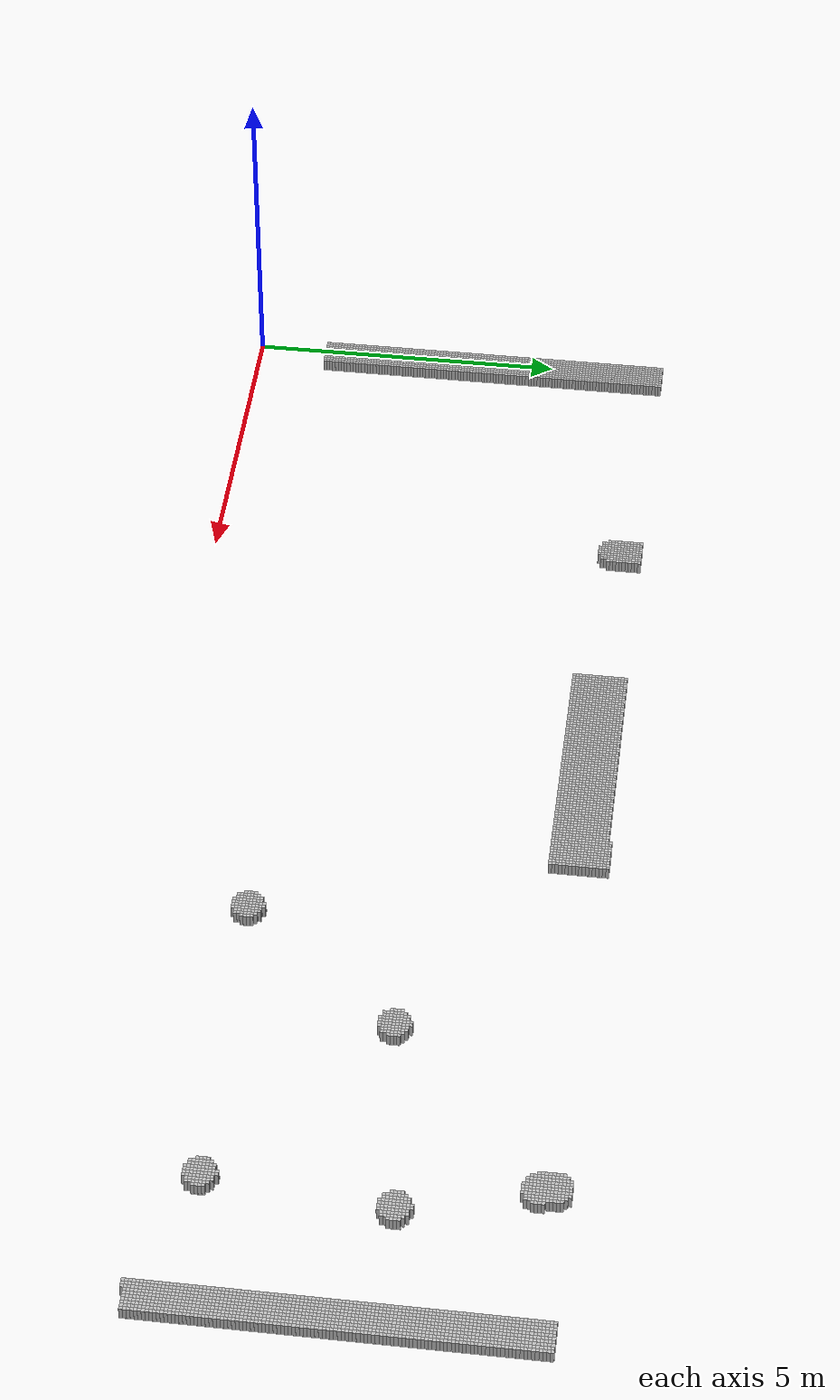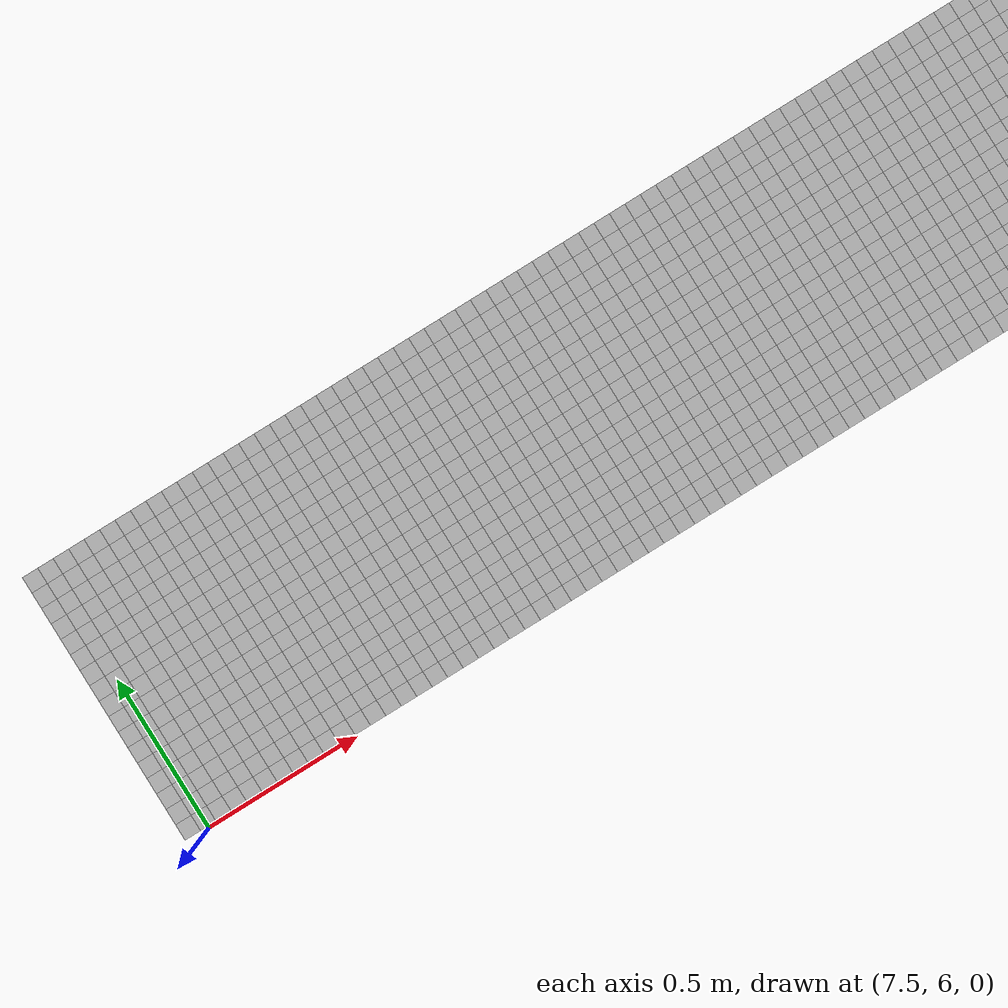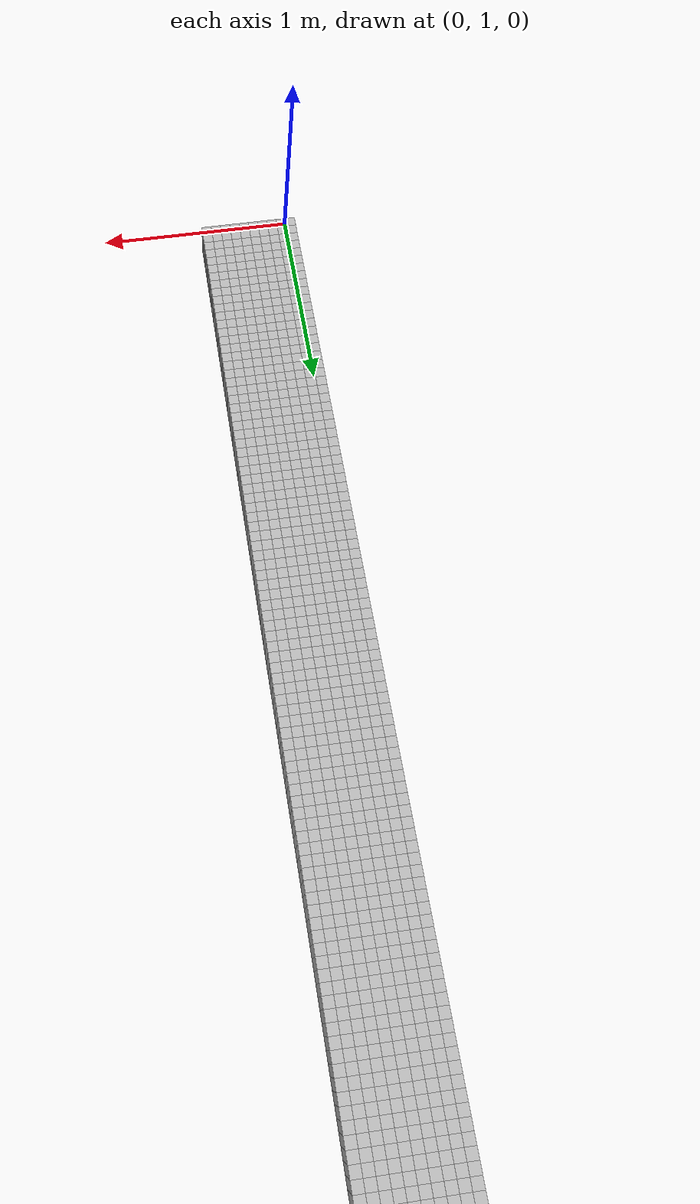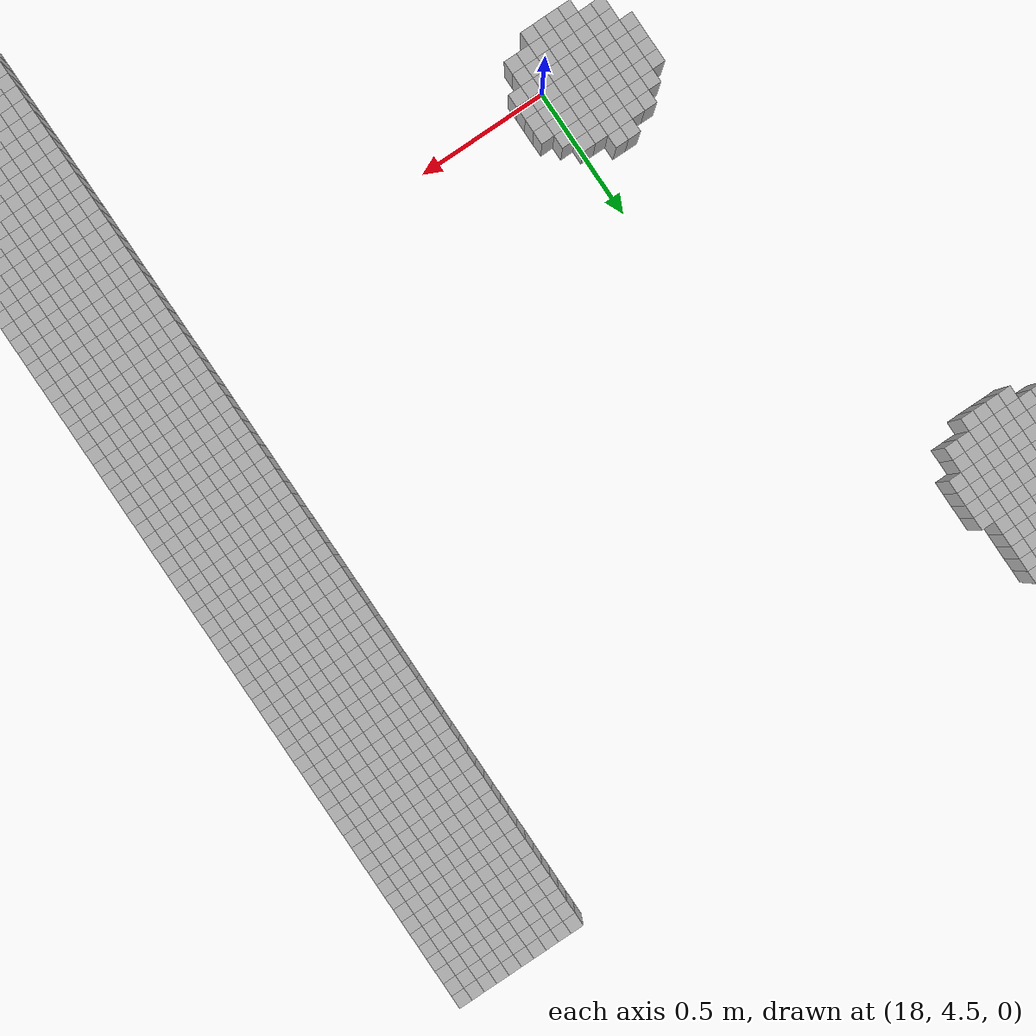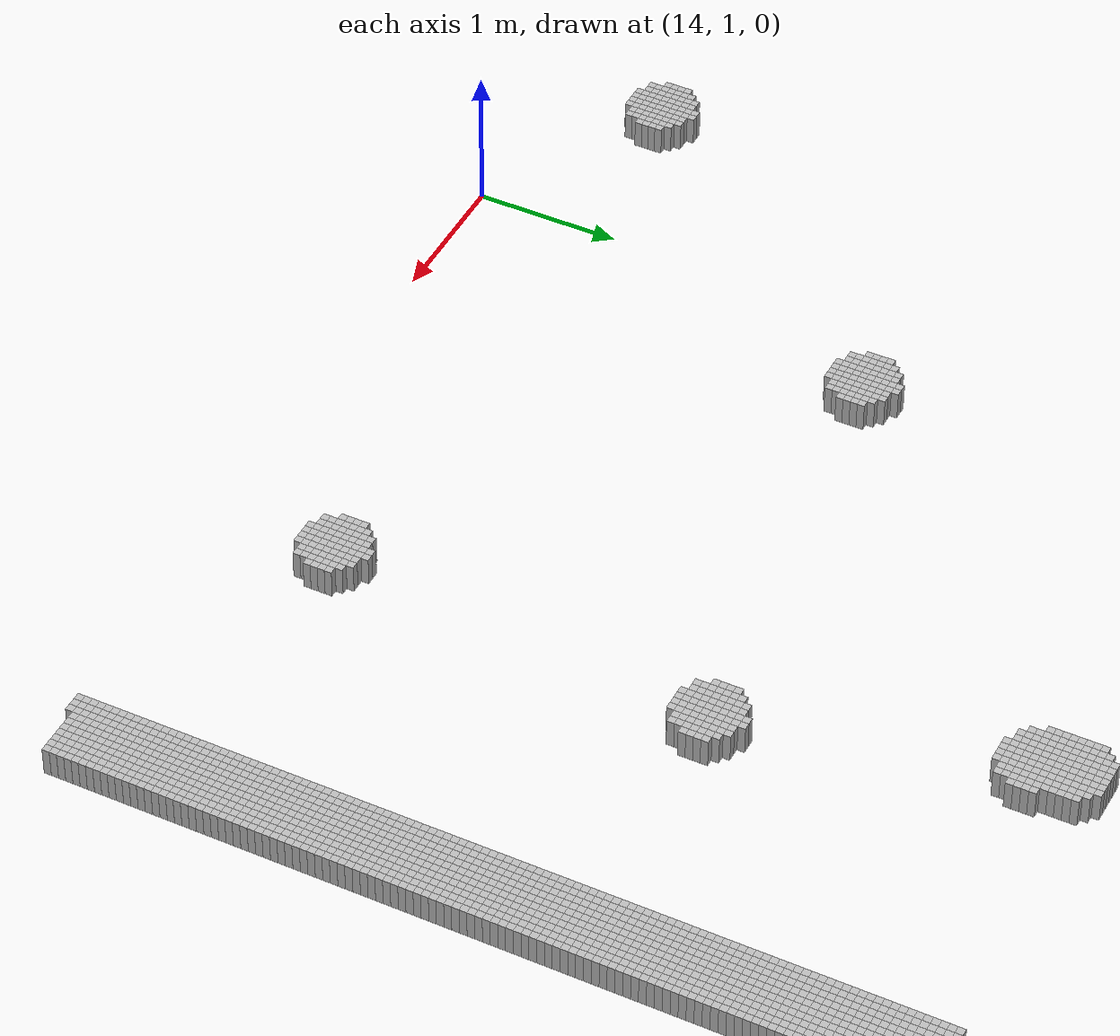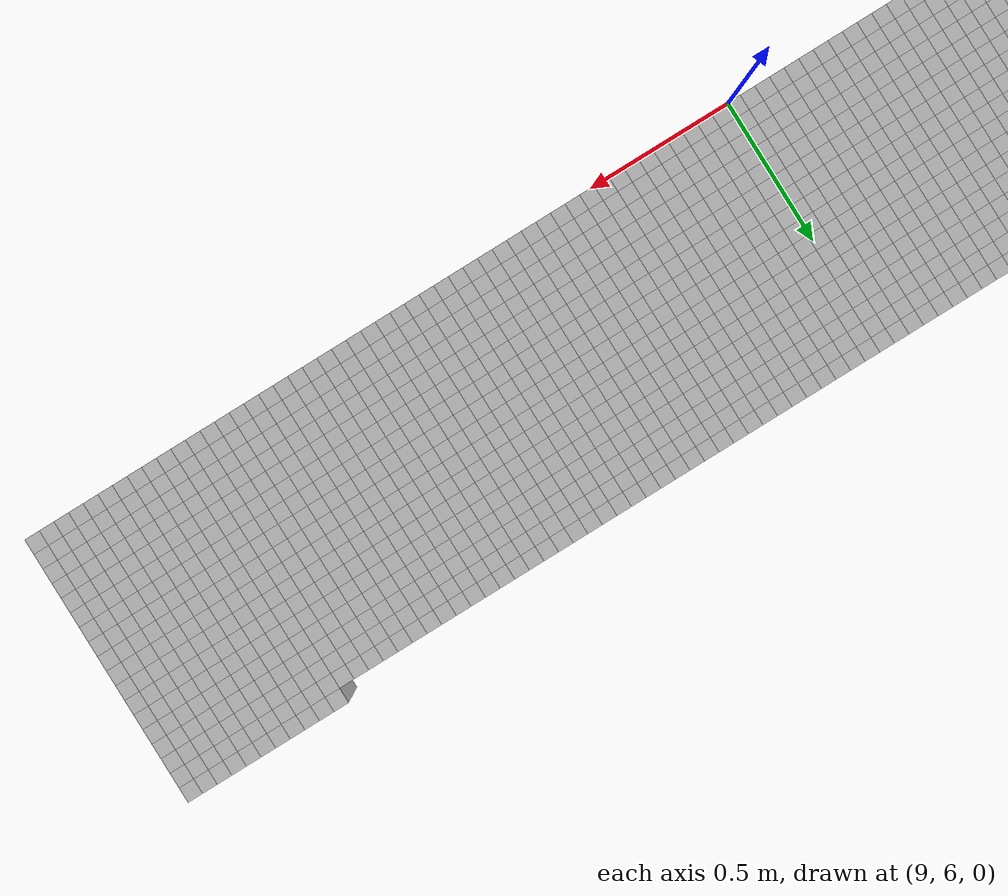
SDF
<sdf version="1.6">
 <world name="default">
  <model name="obstacle_219_262">
   <static>true</static>
   <link name="link">
    <pose>10.950000000000001 6.9 0.1 0 0 0</pose>
    <collision name="collision"><geometry><box><size>0.05 0.05 0.2</size></box></geometry></collision>
    <visual name="visual"><geometry><box><size>0.05 0.05 0.2</size></box></geometry></visual>
   </link>
  </model>
  <model name="obstacle_220_262">
   <static>true</static>
   <link name="link">
    <pose>11.0 6.9 0.1 0 0 0</pose>
    <collision name="collision"><geometry><box><size>0.05 0.05 0.2</size></box></geometry></collision>
    <visual name="visual"><geometry><box><size>0.05 0.05 0.2</size></box></geometry></visual>
   </link>
  </model>
  <model name="obstacle_221_262">
   <static>true</static>
   <link name="link">
    <pose>11.05 6.9 0.1 0 0 0</pose>
    <collision name="collision"><geometry><box><size>0.05 0.05 0.2</size></box></geometry></collision>
    <visual name="visual"><geometry><box><size>0.05 0.05 0.2</size></box></geometry></visual>
   </link>
  </model>
  <model name="obstacle_222_262">
   <static>true</static>
   <link name="link">
    <pose>11.100000000000001 6.9 0.1 0 0 0</pose>
    <collision name="collision"><geometry><box><size>0.05 0.05 0.2</size></box></geometry></collision>
    <visual name="visual"><geometry><box><size>0.05 0.05 0.2</size></box></geometry></visual>
   </link>
  </model>
  <model name="obstacle_223_262">
   <static>true</static>
   <link name="link">
    <pose>11.15 6.9 0.1 0 0 0</pose>
    <collision name="collision"><geometry><box><size>0.05 0.05 0.2</size></box></geometry></collision>
    <visual name="visual"><geometry><box><size>0.05 0.05 0.2</size></box></geometry></visual>
   </link>
  </model>
  <model name="obstacle_224_262">
   <static>true</static>
   <link name="link">
    <pose>11.200000000000001 6.9 0.1 0 0 0</pose>
    <collision name="collision"><geometry><box><size>0.05 0.05 0.2</size></box></geometry></collision>
    <visual name="visual"><geometry><box><size>0.05 0.05 0.2</size></box></geometry></visual>
   </link>
  </model>
  <model name="obstacle_225_262">
   <static>true</static>
   <link name="link">
    <pose>11.25 6.9 0.1 0 0 0</pose>
    <collision name="collision"><geometry><box><size>0.05 0.05 0.2</size></box></geometry></collision>
    <visual name="visual"><geometry><box><size>0.05 0.05 0.2</size></box></geometry></visual>
   </link>
  </model>
  <model name="obstacle_226_262">
   <static>true</static>
   <link name="link">
    <pose>11.3 6.9 0.1 0 0 0</pose>
    <collision name="collision"><geometry><box><size>0.05 0.05 0.2</size></box></geometry></collision>
    <visual name="visual"><geometry><box><size>0.05 0.05 0.2</size></box></geometry></visual>
   </link>
  </model>
  <model name="obstacle_227_262">
   <static>true</static>
   <link name="link">
    <pose>11.350000000000001 6.9 0.1 0 0 0</pose>
    <collision name="collision"><geometry><box><size>0.05 0.05 0.2</size></box></geometry></collision>
    <visual name="visual"><geometry><box><size>0.05 0.05 0.2</size></box></geometry></visual>
   </link>
  </model>
  <model name="obstacle_228_262">
   <static>true</static>
   <link name="link">
    <pose>11.4 6.9 0.1 0 0 0</pose>
    <collision name="collision"><geometry><box><size>0.05 0.05 0.2</size></box></geometry></collision>
    <visual name="visual"><geometry><box><size>0.05 0.05 0.2</size></box></geometry></visual>
   </link>
  </model>
  <model name="obstacle_229_262">
   <static>true</static>
   <link name="link">
    <pose>11.450000000000001 6.9 0.1 0 0 0</pose>
    <collision name="collision"><geometry><box><size>0.05 0.05 0.2</size></box></geometry></collision>
    <visual name="visual"><geometry><box><size>0.05 0.05 0.2</size></box></geometry></visual>
   </link>
  </model>
  <model name="obstacle_344_262">
   <static>true</static>
   <link name="link">
    <pose>17.2 6.9 0.1 0 0 0</pose>
    <collision name="collision"><geometry><box><size>0.05 0.05 0.2</size></box></geometry></collision>
    <visual name="visual"><geometry><box><size>0.05 0.05 0.2</size></box></geometry></visual>
   </link>
  </model>
  <model name="obstacle_345_262">
   <static>true</static>
   <link name="link">
    <pose>17.25 6.9 0.1 0 0 0</pose>
    <collision name="collision"><geometry><box><size>0.05 0.05 0.2</size></box></geometry></collision>
    <visual name="visual"><geometry><box><size>0.05 0.05 0.2</size></box></geometry></visual>
   </link>
  </model>
  <model name="obstacle_346_262">
   <static>true</static>
   <link name="link">
    <pose>17.3 6.9 0.1 0 0 0</pose>
    <collision name="collision"><geometry><box><size>0.05 0.05 0.2</size></box></geometry></collision>
    <visual name="visual"><geometry><box><size>0.05 0.05 0.2</size></box></geometry></visual>
   </link>
  </model>
  <model name="obstacle_347_262">
   <static>true</static>
   <link name="link">
    <pose>17.35 6.9 0.1 0 0 0</pose>
    <collision name="collision"><geometry><box><size>0.05 0.05 0.2</size></box></geometry></collision>
    <visual name="visual"><geometry><box><size>0.05 0.05 0.2</size></box></geometry></visual>
   </link>
  </model>
  <model name="obstacle_348_262">
   <static>true</static>
   <link name="link">
    <pose>17.400000000000002 6.9 0.1 0 0 0</pose>
    <collision name="collision"><geometry><box><size>0.05 0.05 0.2</size></box></geometry></collision>
    <visual name="visual"><geometry><box><size>0.05 0.05 0.2</size></box></geometry></visual>
   </link>
  </model>
  <model name="obstacle_349_262">
   <static>true</static>
   <link name="link">
    <pose>17.45 6.9 0.1 0 0 0</pose>
    <collision name="collision"><geometry><box><size>0.05 0.05 0.2</size></box></geometry></collision>
    <visual name="visual"><geometry><box><size>0.05 0.05 0.2</size></box></geometry></visual>
   </link>
  </model>
  <model name="obstacle_390_262">
   <static>true</static>
   <link name="link">
    <pose>19.5 6.9 0.1 0 0 0</pose>
    <collision name="collision"><geometry><box><size>0.05 0.05 0.2</size></box></geometry></collision>
    <visual name="visual"><geometry><box><size>0.05 0.05 0.2</size></box></geometry></visual>
   </link>
  </model>
  <model name="obstacle_391_262">
   <static>true</static>
   <link name="link">
    <pose>19.55 6.9 0.1 0 0 0</pose>
    <collision name="collision"><geometry><box><size>0.05 0.05 0.2</size></box></geometry></collision>
    <visual name="visual"><geometry><box><size>0.05 0.05 0.2</size></box></geometry></visual>
   </link>
  </model>
  <model name="obstacle_392_262">
   <static>true</static>
   <link name="link">
    <pose>19.6 6.9 0.1 0 0 0</pose>
    <collision name="collision"><geometry><box><size>0.05 0.05 0.2</size></box></geometry></collision>
    <visual name="visual"><geometry><box><size>0.05 0.05 0.2</size></box></geometry></visual>
   </link>
  </model>
  <model name="obstacle_393_262">
   <static>true</static>
   <link name="link">
    <pose>19.650000000000002 6.9 0.1 0 0 0</pose>
    <collision name="collision"><geometry><box><size>0.05 0.05 0.2</size></box></geometry></collision>
    <visual name="visual"><geometry><box><size>0.05 0.05 0.2</size></box></geometry></visual>
   </link>
  </model>
  <model name="obstacle_394_262">
   <static>true</static>
   <link name="link">
    <pose>19.700000000000003 6.9 0.1 0 0 0</pose>
    <collision name="collision"><geometry><box><size>0.05 0.05 0.2</size></box></geometry></collision>
    <visual name="visual"><geometry><box><size>0.05 0.05 0.2</size></box></geometry></visual>
   </link>
  </model>
  <model name="obstacle_395_262">
   <static>true</static>
   <link name="link">
    <pose>19.75 6.9 0.1 0 0 0</pose>
    <collision name="collision"><geometry><box><size>0.05 0.05 0.2</size></box></geometry></collision>
    <visual name="visual"><geometry><box><size>0.05 0.05 0.2</size></box></geometry></visual>
   </link>
  </model>
  <model name="obstacle_396_262">
   <static>true</static>
   <link name="link">
    <pose>19.8 6.9 0.1 0 0 0</pose>
    <collision name="collision"><geometry><box><size>0.05 0.05 0.2</size></box></geometry></collision>
    <visual name="visual"><geometry><box><size>0.05 0.05 0.2</size></box></geometry></visual>
   </link>
  </model>
  <model name="obstacle_397_262">
   <static>true</static>
   <link name="link">
    <pose>19.85 6.9 0.1 0 0 0</pose>
    <collision name="collision"><geometry><box><size>0.05 0.05 0.2</size></box></geometry></collision>
    <visual name="visual"><geometry><box><size>0.05 0.05 0.2</size></box></geometry></visual>
   </link>
  </model>
  <model name="obstacle_398_262">
   <static>true</static>
   <link name="link">
    <pose>19.900000000000002 6.9 0.1 0 0 0</pose>
    <collision name="collision"><geometry><box><size>0.05 0.05 0.2</size></box></geometry></collision>
    <visual name="visual"><geometry><box><size>0.05 0.05 0.2</size></box></geometry></visual>
   </link>
  </model>
  <model name="obstacle_399_262">
   <static>true</static>
   <link name="link">
    <pose>19.950000000000003 6.9 0.1 0 0 0</pose>
    <collision name="collision"><geometry><box><size>0.05 0.05 0.2</size></box></geometry></collision>
    <visual name="visual"><geometry><box><size>0.05 0.05 0.2</size></box></geometry></visual>
   </link>
  </model>
  <model name="obstacle_0_263">
   <static>true</static>
   <link name="link">
    <pose>0.0 6.8500000000000005 0.1 0 0 0</pose>
    <collision name="collision"><geometry><box><size>0.05 0.05 0.2</size></box></geometry></collision>
    <visual name="visual"><geometry><box><size>0.05 0.05 0.2</size></box></geometry></visual>
   </link>
  </model>
  <model name="obstacle_1_263">
   <static>true</static>
   <link name="link">
    <pose>0.05 6.8500000000000005 0.1 0 0 0</pose>
    <collision name="collision"><geometry><box><size>0.05 0.05 0.2</size></box></geometry></collision>
    <visual name="visual"><geometry><box><size>0.05 0.05 0.2</size></box></geometry></visual>
   </link>
  </model>
  <model name="obstacle_2_263">
   <static>true</static>
   <link name="link">
    <pose>0.1 6.8500000000000005 0.1 0 0 0</pose>
    <collision name="collision"><geometry><box><size>0.05 0.05 0.2</size></box></geometry></collision>
    <visual name="visual"><geometry><box><size>0.05 0.05 0.2</size></box></geometry></visual>
   </link>
  </model>
  <model name="obstacle_3_263">
   <static>true</static>
   <link name="link">
    <pose>0.15000000000000002 6.8500000000000005 0.1 0 0 0</pose>
    <collision name="collision"><geometry><box><size>0.05 0.05 0.2</size></box></geometry></collision>
    <visual name="visual"><geometry><box><size>0.05 0.05 0.2</size></box></geometry></visual>
   </link>
  </model>
  <model name="obstacle_4_263">
   <static>true</static>
   <link name="link">
    <pose>0.2 6.8500000000000005 0.1 0 0 0</pose>
    <collision name="collision"><geometry><box><size>0.05 0.05 0.2</size></box></geometry></collision>
    <visual name="visual"><geometry><box><size>0.05 0.05 0.2</size></box></geometry></visual>
   </link>
  </model>
  <model name="obstacle_5_263">
   <static>true</static>
   <link name="link">
    <pose>0.25 6.8500000000000005 0.1 0 0 0</pose>
    <collision name="collision"><geometry><box><size>0.05 0.05 0.2</size></box></geometry></collision>
    <visual name="visual"><geometry><box><size>0.05 0.05 0.2</size></box></geometry></visual>
   </link>
  </model>
  <model name="obstacle_6_263">
   <static>true</static>
   <link name="link">
    <pose>0.30000000000000004 6.8500000000000005 0.1 0 0 0</pose>
    <collision name="collision"><geometry><box><size>0.05 0.05 0.2</size></box></geometry></collision>
    <visual name="visual"><geometry><box><size>0.05 0.05 0.2</size></box></geometry></visual>
   </link>
  </model>
  <model name="obstacle_7_263">
   <static>true</static>
   <link name="link">
    <pose>0.35000000000000003 6.8500000000000005 0.1 0 0 0</pose>
    <collision name="collision"><geometry><box><size>0.05 0.05 0.2</size></box></geometry></collision>
    <visual name="visual"><geometry><box><size>0.05 0.05 0.2</size></box></geometry></visual>
   </link>
  </model>
  <model name="obstacle_8_263">
   <static>true</static>
   <link name="link">
    <pose>0.4 6.8500000000000005 0.1 0 0 0</pose>
    <collision name="collision"><geometry><box><size>0.05 0.05 0.2</size></box></geometry></collision>
    <visual name="visual"><geometry><box><size>0.05 0.05 0.2</size></box></geometry></visual>
   </link>
  </model>
  <model name="obstacle_9_263">
   <static>true</static>
   <link name="link">
    <pose>0.45 6.8500000000000005 0.1 0 0 0</pose>
    <collision name="collision"><geometry><box><size>0.05 0.05 0.2</size></box></geometry></collision>
    <visual name="visual"><geometry><box><size>0.05 0.05 0.2</size></box></geometry></visual>
   </link>
  </model>
  <model name="obstacle_88_263">
   <static>true</static>
   <link name="link">
    <pose>4.4 6.8500000000000005 0.1 0 0 0</pose>
    <collision name="collision"><geometry><box><size>0.05 0.05 0.2</size></box></geometry></collision>
    <visual name="visual"><geometry><box><size>0.05 0.05 0.2</size></box></geometry></visual>
   </link>
  </model>
  <model name="obstacle_89_263">
   <static>true</static>
   <link name="link">
    <pose>4.45 6.8500000000000005 0.1 0 0 0</pose>
    <collision name="collision"><geometry><box><size>0.05 0.05 0.2</size></box></geometry></collision>
    <visual name="visual"><geometry><box><size>0.05 0.05 0.2</size></box></geometry></visual>
   </link>
  </model>
  <model name="obstacle_90_263">
   <static>true</static>
   <link name="link">
    <pose>4.5 6.8500000000000005 0.1 0 0 0</pose>
    <collision name="collision"><geometry><box><size>0.05 0.05 0.2</size></box></geometry></collision>
    <visual name="visual"><geometry><box><size>0.05 0.05 0.2</size></box></geometry></visual>
   </link>
  </model>
  <model name="obstacle_91_263">
   <static>true</static>
   <link name="link">
    <pose>4.55 6.8500000000000005 0.1 0 0 0</pose>
    <collision name="collision"><geometry><box><size>0.05 0.05 0.2</size></box></geometry></collision>
    <visual name="visual"><geometry><box><size>0.05 0.05 0.2</size></box></geometry></visual>
   </link>
  </model>
  <model name="obstacle_92_263">
   <static>true</static>
   <link name="link">
    <pose>4.6000000000000005 6.8500000000000005 0.1 0 0 0</pose>
    <collision name="collision"><geometry><box><size>0.05 0.05 0.2</size></box></geometry></collision>
    <visual name="visual"><geometry><box><size>0.05 0.05 0.2</size></box></geometry></visual>
   </link>
  </model>
  <model name="obstacle_93_263">
   <static>true</static>
   <link name="link">
    <pose>4.65 6.8500000000000005 0.1 0 0 0</pose>
    <collision name="collision"><geometry><box><size>0.05 0.05 0.2</size></box></geometry></collision>
    <visual name="visual"><geometry><box><size>0.05 0.05 0.2</size></box></geometry></visual>
   </link>
  </model>
  <model name="obstacle_94_263">
   <static>true</static>
   <link name="link">
    <pose>4.7 6.8500000000000005 0.1 0 0 0</pose>
    <collision name="collision"><geometry><box><size>0.05 0.05 0.2</size></box></geometry></collision>
    <visual name="visual"><geometry><box><size>0.05 0.05 0.2</size></box></geometry></visual>
   </link>
  </model>
  <model name="obstacle_95_263">
   <static>true</static>
   <link name="link">
    <pose>4.75 6.8500000000000005 0.1 0 0 0</pose>
    <collision name="collision"><geometry><box><size>0.05 0.05 0.2</size></box></geometry></collision>
    <visual name="visual"><geometry><box><size>0.05 0.05 0.2</size></box></geometry></visual>
   </link>
  </model>
  <model name="obstacle_96_263">
   <static>true</static>
   <link name="link">
    <pose>4.800000000000001 6.8500000000000005 0.1 0 0 0</pose>
    <collision name="collision"><geometry><box><size>0.05 0.05 0.2</size></box></geometry></collision>
    <visual name="visual"><geometry><box><size>0.05 0.05 0.2</size></box></geometry></visual>
   </link>
  </model>
  <model name="obstacle_97_263">
   <static>true</static>
   <link name="link">
    <pose>4.8500000000000005 6.8500000000000005 0.1 0 0 0</pose>
    <collision name="collision"><geometry><box><size>0.05 0.05 0.2</size></box></geometry></collision>
    <visual name="visual"><geometry><box><size>0.05 0.05 0.2</size></box></geometry></visual>
   </link>
  </model>
  <model name="obstacle_150_263">
   <static>true</static>
   <link name="link">
    <pose>7.5 6.8500000000000005 0.1 0 0 0</pose>
    <collision name="collision"><geometry><box><size>0.05 0.05 0.2</size></box></geometry></collision>
    <visual name="visual"><geometry><box><size>0.05 0.05 0.2</size></box></geometry></visual>
   </link>
  </model>
  <model name="obstacle_151_263">
   <static>true</static>
   <link name="link">
    <pose>7.550000000000001 6.8500000000000005 0.1 0 0 0</pose>
    <collision name="collision"><geometry><box><size>0.05 0.05 0.2</size></box></geometry></collision>
    <visual name="visual"><geometry><box><size>0.05 0.05 0.2</size></box></geometry></visual>
   </link>
  </model>
  <model name="obstacle_152_263">
   <static>true</static>
   <link name="link">
    <pose>7.6000000000000005 6.8500000000000005 0.1 0 0 0</pose>
    <collision name="collision"><geometry><box><size>0.05 0.05 0.2</size></box></geometry></collision>
    <visual name="visual"><geometry><box><size>0.05 0.05 0.2</size></box></geometry></visual>
   </link>
  </model>
  <model name="obstacle_153_263">
   <static>true</static>
   <link name="link">
    <pose>7.65 6.8500000000000005 0.1 0 0 0</pose>
    <collision name="collision"><geometry><box><size>0.05 0.05 0.2</size></box></geometry></collision>
    <visual name="visual"><geometry><box><size>0.05 0.05 0.2</size></box></geometry></visual>
   </link>
  </model>
  <model name="obstacle_154_263">
   <static>true</static>
   <link name="link">
    <pose>7.7 6.8500000000000005 0.1 0 0 0</pose>
    <collision name="collision"><geometry><box><size>0.05 0.05 0.2</size></box></geometry></collision>
    <visual name="visual"><geometry><box><size>0.05 0.05 0.2</size></box></geometry></visual>
   </link>
  </model>
  <model name="obstacle_155_263">
   <static>true</static>
   <link name="link">
    <pose>7.75 6.8500000000000005 0.1 0 0 0</pose>
    <collision name="collision"><geometry><box><size>0.05 0.05 0.2</size></box></geometry></collision>
    <visual name="visual"><geometry><box><size>0.05 0.05 0.2</size></box></geometry></visual>
   </link>
  </model>
  <model name="obstacle_156_263">
   <static>true</static>
   <link name="link">
    <pose>7.800000000000001 6.8500000000000005 0.1 0 0 0</pose>
    <collision name="collision"><geometry><box><size>0.05 0.05 0.2</size></box></geometry></collision>
    <visual name="visual"><geometry><box><size>0.05 0.05 0.2</size></box></geometry></visual>
   </link>
  </model>
  <model name="obstacle_157_263">
   <static>true</static>
   <link name="link">
    <pose>7.8500000000000005 6.8500000000000005 0.1 0 0 0</pose>
    <collision name="collision"><geometry><box><size>0.05 0.05 0.2</size></box></geometry></collision>
    <visual name="visual"><geometry><box><size>0.05 0.05 0.2</size></box></geometry></visual>
   </link>
  </model>
  <model name="obstacle_158_263">
   <static>true</static>
   <link name="link">
    <pose>7.9 6.8500000000000005 0.1 0 0 0</pose>
    <collision name="collision"><geometry><box><size>0.05 0.05 0.2</size></box></geometry></collision>
    <visual name="visual"><geometry><box><size>0.05 0.05 0.2</size></box></geometry></visual>
   </link>
  </model>
  <model name="obstacle_159_263">
   <static>true</static>
   <link name="link">
    <pose>7.95 6.8500000000000005 0.1 0 0 0</pose>
    <collision name="collision"><geometry><box><size>0.05 0.05 0.2</size></box></geometry></collision>
    <visual name="visual"><geometry><box><size>0.05 0.05 0.2</size></box></geometry></visual>
   </link>
  </model>
  <model name="obstacle_160_263">
   <static>true</static>
   <link name="link">
    <pose>8.0 6.8500000000000005 0.1 0 0 0</pose>
    <collision name="collision"><geometry><box><size>0.05 0.05 0.2</size></box></geometry></collision>
    <visual name="visual"><geometry><box><size>0.05 0.05 0.2</size></box></geometry></visual>
   </link>
  </model>
  <model name="obstacle_161_263">
   <static>true</static>
   <link name="link">
    <pose>8.05 6.8500000000000005 0.1 0 0 0</pose>
    <collision name="collision"><geometry><box><size>0.05 0.05 0.2</size></box></geometry></collision>
    <visual name="visual"><geometry><box><size>0.05 0.05 0.2</size></box></geometry></visual>
   </link>
  </model>
  <model name="obstacle_162_263">
   <static>true</static>
   <link name="link">
    <pose>8.1 6.8500000000000005 0.1 0 0 0</pose>
    <collision name="collision"><geometry><box><size>0.05 0.05 0.2</size></box></geometry></collision>
    <visual name="visual"><geometry><box><size>0.05 0.05 0.2</size></box></geometry></visual>
   </link>
  </model>
  <model name="obstacle_163_263">
   <static>true</static>
   <link name="link">
    <pose>8.15 6.8500000000000005 0.1 0 0 0</pose>
    <collision name="collision"><geometry><box><size>0.05 0.05 0.2</size></box></geometry></collision>
    <visual name="visual"><geometry><box><size>0.05 0.05 0.2</size></box></geometry></visual>
   </link>
  </model>
  <model name="obstacle_164_263">
   <static>true</static>
   <link name="link">
    <pose>8.200000000000001 6.8500000000000005 0.1 0 0 0</pose>
    <collision name="collision"><geometry><box><size>0.05 0.05 0.2</size></box></geometry></collision>
    <visual name="visual"><geometry><box><size>0.05 0.05 0.2</size></box></geometry></visual>
   </link>
  </model>
  <model name="obstacle_165_263">
   <static>true</static>
   <link name="link">
    <pose>8.25 6.8500000000000005 0.1 0 0 0</pose>
    <collision name="collision"><geometry><box><size>0.05 0.05 0.2</size></box></geometry></collision>
    <visual name="visual"><geometry><box><size>0.05 0.05 0.2</size></box></geometry></visual>
   </link>
  </model>
  <model name="obstacle_166_263">
   <static>true</static>
   <link name="link">
    <pose>8.3 6.8500000000000005 0.1 0 0 0</pose>
    <collision name="collision"><geometry><box><size>0.05 0.05 0.2</size></box></geometry></collision>
    <visual name="visual"><geometry><box><size>0.05 0.05 0.2</size></box></geometry></visual>
   </link>
  </model>
  <model name="obstacle_167_263">
   <static>true</static>
   <link name="link">
    <pose>8.35 6.8500000000000005 0.1 0 0 0</pose>
    <collision name="collision"><geometry><box><size>0.05 0.05 0.2</size></box></geometry></collision>
    <visual name="visual"><geometry><box><size>0.05 0.05 0.2</size></box></geometry></visual>
   </link>
  </model>
  <model name="obstacle_168_263">
   <static>true</static>
   <link name="link">
    <pose>8.4 6.8500000000000005 0.1 0 0 0</pose>
    <collision name="collision"><geometry><box><size>0.05 0.05 0.2</size></box></geometry></collision>
    <visual name="visual"><geometry><box><size>0.05 0.05 0.2</size></box></geometry></visual>
   </link>
  </model>
  <model name="obstacle_169_263">
   <static>true</static>
   <link name="link">
    <pose>8.450000000000001 6.8500000000000005 0.1 0 0 0</pose>
    <collision name="collision"><geometry><box><size>0.05 0.05 0.2</size></box></geometry></collision>
    <visual name="visual"><geometry><box><size>0.05 0.05 0.2</size></box></geometry></visual>
   </link>
  </model>
  <model name="obstacle_170_263">
   <static>true</static>
   <link name="link">
    <pose>8.5 6.8500000000000005 0.1 0 0 0</pose>
    <collision name="collision"><geometry><box><size>0.05 0.05 0.2</size></box></geometry></collision>
    <visual name="visual"><geometry><box><size>0.05 0.05 0.2</size></box></geometry></visual>
   </link>
  </model>
  <model name="obstacle_171_263">
   <static>true</static>
   <link name="link">
    <pose>8.55 6.8500000000000005 0.1 0 0 0</pose>
    <collision name="collision"><geometry><box><size>0.05 0.05 0.2</size></box></geometry></collision>
    <visual name="visual"><geometry><box><size>0.05 0.05 0.2</size></box></geometry></visual>
   </link>
  </model>
  <model name="obstacle_172_263">
   <static>true</static>
   <link name="link">
    <pose>8.6 6.8500000000000005 0.1 0 0 0</pose>
    <collision name="collision"><geometry><box><size>0.05 0.05 0.2</size></box></geometry></collision>
    <visual name="visual"><geometry><box><size>0.05 0.05 0.2</size></box></geometry></visual>
   </link>
  </model>
  <model name="obstacle_173_263">
   <static>true</static>
   <link name="link">
    <pose>8.65 6.8500000000000005 0.1 0 0 0</pose>
    <collision name="collision"><geometry><box><size>0.05 0.05 0.2</size></box></geometry></collision>
    <visual name="visual"><geometry><box><size>0.05 0.05 0.2</size></box></geometry></visual>
   </link>
  </model>
  <model name="obstacle_174_263">
   <static>true</static>
   <link name="link">
    <pose>8.700000000000001 6.8500000000000005 0.1 0 0 0</pose>
    <collision name="collision"><geometry><box><size>0.05 0.05 0.2</size></box></geometry></collision>
    <visual name="visual"><geometry><box><size>0.05 0.05 0.2</size></box></geometry></visual>
   </link>
  </model>
  <model name="obstacle_175_263">
   <static>true</static>
   <link name="link">
    <pose>8.75 6.8500000000000005 0.1 0 0 0</pose>
    <collision name="collision"><geometry><box><size>0.05 0.05 0.2</size></box></geometry></collision>
    <visual name="visual"><geometry><box><size>0.05 0.05 0.2</size></box></geometry></visual>
   </link>
  </model>
  <model name="obstacle_176_263">
   <static>true</static>
   <link name="link">
    <pose>8.8 6.8500000000000005 0.1 0 0 0</pose>
    <collision name="collision"><geometry><box><size>0.05 0.05 0.2</size></box></geometry></collision>
    <visual name="visual"><geometry><box><size>0.05 0.05 0.2</size></box></geometry></visual>
   </link>
  </model>
  <model name="obstacle_177_263">
   <static>true</static>
   <link name="link">
    <pose>8.85 6.8500000000000005 0.1 0 0 0</pose>
    <collision name="collision"><geometry><box><size>0.05 0.05 0.2</size></box></geometry></collision>
    <visual name="visual"><geometry><box><size>0.05 0.05 0.2</size></box></geometry></visual>
   </link>
  </model>
  <model name="obstacle_178_263">
   <static>true</static>
   <link name="link">
    <pose>8.9 6.8500000000000005 0.1 0 0 0</pose>
    <collision name="collision"><geometry><box><size>0.05 0.05 0.2</size></box></geometry></collision>
    <visual name="visual"><geometry><box><size>0.05 0.05 0.2</size></box></geometry></visual>
   </link>
  </model>
  <model name="obstacle_179_263">
   <static>true</static>
   <link name="link">
    <pose>8.950000000000001 6.8500000000000005 0.1 0 0 0</pose>
    <collision name="collision"><geometry><box><size>0.05 0.05 0.2</size></box></geometry></collision>
    <visual name="visual"><geometry><box><size>0.05 0.05 0.2</size></box></geometry></visual>
   </link>
  </model>
  <model name="obstacle_180_263">
   <static>true</static>
   <link name="link">
    <pose>9.0 6.8500000000000005 0.1 0 0 0</pose>
    <collision name="collision"><geometry><box><size>0.05 0.05 0.2</size></box></geometry></collision>
    <visual name="visual"><geometry><box><size>0.05 0.05 0.2</size></box></geometry></visual>
   </link>
  </model>
  <model name="obstacle_181_263">
   <static>true</static>
   <link name="link">
    <pose>9.05 6.8500000000000005 0.1 0 0 0</pose>
    <collision name="collision"><geometry><box><size>0.05 0.05 0.2</size></box></geometry></collision>
    <visual name="visual"><geometry><box><size>0.05 0.05 0.2</size></box></geometry></visual>
   </link>
  </model>
  <model name="obstacle_182_263">
   <static>true</static>
   <link name="link">
    <pose>9.1 6.8500000000000005 0.1 0 0 0</pose>
    <collision name="collision"><geometry><box><size>0.05 0.05 0.2</size></box></geometry></collision>
    <visual name="visual"><geometry><box><size>0.05 0.05 0.2</size></box></geometry></visual>
   </link>
  </model>
  <model name="obstacle_183_263">
   <static>true</static>
   <link name="link">
    <pose>9.15 6.8500000000000005 0.1 0 0 0</pose>
    <collision name="collision"><geometry><box><size>0.05 0.05 0.2</size></box></geometry></collision>
    <visual name="visual"><geometry><box><size>0.05 0.05 0.2</size></box></geometry></visual>
   </link>
  </model>
  <model name="obstacle_184_263">
   <static>true</static>
   <link name="link">
    <pose>9.200000000000001 6.8500000000000005 0.1 0 0 0</pose>
    <collision name="collision"><geometry><box><size>0.05 0.05 0.2</size></box></geometry></collision>
    <visual name="visual"><geometry><box><size>0.05 0.05 0.2</size></box></geometry></visual>
   </link>
  </model>
  <model name="obstacle_185_263">
   <static>true</static>
   <link name="link">
    <pose>9.25 6.8500000000000005 0.1 0 0 0</pose>
    <collision name="collision"><geometry><box><size>0.05 0.05 0.2</size></box></geometry></collision>
    <visual name="visual"><geometry><box><size>0.05 0.05 0.2</size></box></geometry></visual>
   </link>
  </model>
  <model name="obstacle_186_263">
   <static>true</static>
   <link name="link">
    <pose>9.3 6.8500000000000005 0.1 0 0 0</pose>
    <collision name="collision"><geometry><box><size>0.05 0.05 0.2</size></box></geometry></collision>
    <visual name="visual"><geometry><box><size>0.05 0.05 0.2</size></box></geometry></visual>
   </link>
  </model>
  <model name="obstacle_187_263">
   <static>true</static>
   <link name="link">
    <pose>9.35 6.8500000000000005 0.1 0 0 0</pose>
    <collision name="collision"><geometry><box><size>0.05 0.05 0.2</size></box></geometry></collision>
    <visual name="visual"><geometry><box><size>0.05 0.05 0.2</size></box></geometry></visual>
   </link>
  </model>
  <model name="obstacle_188_263">
   <static>true</static>
   <link name="link">
    <pose>9.4 6.8500000000000005 0.1 0 0 0</pose>
    <collision name="collision"><geometry><box><size>0.05 0.05 0.2</size></box></geometry></collision>
    <visual name="visual"><geometry><box><size>0.05 0.05 0.2</size></box></geometry></visual>
   </link>
  </model>
  <model name="obstacle_189_263">
   <static>true</static>
   <link name="link">
    <pose>9.450000000000001 6.8500000000000005 0.1 0 0 0</pose>
    <collision name="collision"><geometry><box><size>0.05 0.05 0.2</size></box></geometry></collision>
    <visual name="visual"><geometry><box><size>0.05 0.05 0.2</size></box></geometry></visual>
   </link>
  </model>
  <model name="obstacle_190_263">
   <static>true</static>
   <link name="link">
    <pose>9.5 6.8500000000000005 0.1 0 0 0</pose>
    <collision name="collision"><geometry><box><size>0.05 0.05 0.2</size></box></geometry></collision>
    <visual name="visual"><geometry><box><size>0.05 0.05 0.2</size></box></geometry></visual>
   </link>
  </model>
  <model name="obstacle_191_263">
   <static>true</static>
   <link name="link">
    <pose>9.55 6.8500000000000005 0.1 0 0 0</pose>
    <collision name="collision"><geometry><box><size>0.05 0.05 0.2</size></box></geometry></collision>
    <visual name="visual"><geometry><box><size>0.05 0.05 0.2</size></box></geometry></visual>
   </link>
  </model>
  <model name="obstacle_192_263">
   <static>true</static>
   <link name="link">
    <pose>9.600000000000001 6.8500000000000005 0.1 0 0 0</pose>
    <collision name="collision"><geometry><box><size>0.05 0.05 0.2</size></box></geometry></collision>
    <visual name="visual"><geometry><box><size>0.05 0.05 0.2</size></box></geometry></visual>
   </link>
  </model>
  <model name="obstacle_193_263">
   <static>true</static>
   <link name="link">
    <pose>9.65 6.8500000000000005 0.1 0 0 0</pose>
    <collision name="collision"><geometry><box><size>0.05 0.05 0.2</size></box></geometry></collision>
    <visual name="visual"><geometry><box><size>0.05 0.05 0.2</size></box></geometry></visual>
   </link>
  </model>
  <model name="obstacle_194_263">
   <static>true</static>
   <link name="link">
    <pose>9.700000000000001 6.8500000000000005 0.1 0 0 0</pose>
    <collision name="collision"><geometry><box><size>0.05 0.05 0.2</size></box></geometry></collision>
    <visual name="visual"><geometry><box><size>0.05 0.05 0.2</size></box></geometry></visual>
   </link>
  </model>
  <model name="obstacle_195_263">
   <static>true</static>
   <link name="link">
    <pose>9.75 6.8500000000000005 0.1 0 0 0</pose>
    <collision name="collision"><geometry><box><size>0.05 0.05 0.2</size></box></geometry></collision>
    <visual name="visual"><geometry><box><size>0.05 0.05 0.2</size></box></geometry></visual>
   </link>
  </model>
  <model name="obstacle_196_263">
   <static>true</static>
   <link name="link">
    <pose>9.8 6.8500000000000005 0.1 0 0 0</pose>
    <collision name="collision"><geometry><box><size>0.05 0.05 0.2</size></box></geometry></collision>
    <visual name="visual"><geometry><box><size>0.05 0.05 0.2</size></box></geometry></visual>
   </link>
  </model>
  <model name="obstacle_197_263">
   <static>true</static>
   <link name="link">
    <pose>9.850000000000001 6.8500000000000005 0.1 0 0 0</pose>
    <collision name="collision"><geometry><box><size>0.05 0.05 0.2</size></box></geometry></collision>
    <visual name="visual"><geometry><box><size>0.05 0.05 0.2</size></box></geometry></visual>
   </link>
  </model>
  <model name="obstacle_198_263">
   <static>true</static>
   <link name="link">
    <pose>9.9 6.8500000000000005 0.1 0 0 0</pose>
    <collision name="collision"><geometry><box><size>0.05 0.05 0.2</size></box></geometry></collision>
    <visual name="visual"><geometry><box><size>0.05 0.05 0.2</size></box></geometry></visual>
   </link>
  </model>
  <model name="obstacle_199_263">
   <static>true</static>
   <link name="link">
    <pose>9.950000000000001 6.8500000000000005 0.1 0 0 0</pose>
    <collision name="collision"><geometry><box><size>0.05 0.05 0.2</size></box></geometry></collision>
    <visual name="visual"><geometry><box><size>0.05 0.05 0.2</size></box></geometry></visual>
   </link>
  </model>
  <model name="obstacle_200_263">
   <static>true</static>
   <link name="link">
    <pose>10.0 6.8500000000000005 0.1 0 0 0</pose>
    <collision name="collision"><geometry><box><size>0.05 0.05 0.2</size></box></geometry></collision>
    <visual name="visual"><geometry><box><size>0.05 0.05 0.2</size></box></geometry></visual>
   </link>
  </model>
  <model name="obstacle_201_263">
   <static>true</static>
   <link name="link">
    <pose>10.05 6.8500000000000005 0.1 0 0 0</pose>
    <collision name="collision"><geometry><box><size>0.05 0.05 0.2</size></box></geometry></collision>
    <visual name="visual"><geometry><box><size>0.05 0.05 0.2</size></box></geometry></visual>
   </link>
  </model>
  <model name="obstacle_202_263">
   <static>true</static>
   <link name="link">
    <pose>10.100000000000001 6.8500000000000005 0.1 0 0 0</pose>
    <collision name="collision"><geometry><box><size>0.05 0.05 0.2</size></box></geometry></collision>
    <visual name="visual"><geometry><box><size>0.05 0.05 0.2</size></box></geometry></visual>
   </link>
  </model>
  <model name="obstacle_203_263">
   <static>true</static>
   <link name="link">
    <pose>10.15 6.8500000000000005 0.1 0 0 0</pose>
    <collision name="collision"><geometry><box><size>0.05 0.05 0.2</size></box></geometry></collision>
    <visual name="visual"><geometry><box><size>0.05 0.05 0.2</size></box></geometry></visual>
   </link>
  </model>
  <model name="obstacle_204_263">
   <static>true</static>
   <link name="link">
    <pose>10.200000000000001 6.8500000000000005 0.1 0 0 0</pose>
    <collision name="collision"><geometry><box><size>0.05 0.05 0.2</size></box></geometry></collision>
    <visual name="visual"><geometry><box><size>0.05 0.05 0.2</size></box></geometry></visual>
   </link>
  </model>
  <model name="obstacle_205_263">
   <static>true</static>
   <link name="link">
    <pose>10.25 6.8500000000000005 0.1 0 0 0</pose>
    <collision name="collision"><geometry><box><size>0.05 0.05 0.2</size></box></geometry></collision>
    <visual name="visual"><geometry><box><size>0.05 0.05 0.2</size></box></geometry></visual>
   </link>
  </model>
  <model name="obstacle_206_263">
   <static>true</static>
   <link name="link">
    <pose>10.3 6.8500000000000005 0.1 0 0 0</pose>
    <collision name="collision"><geometry><box><size>0.05 0.05 0.2</size></box></geometry></collision>
    <visual name="visual"><geometry><box><size>0.05 0.05 0.2</size></box></geometry></visual>
   </link>
  </model>
  <model name="obstacle_207_263">
   <static>true</static>
   <link name="link">
    <pose>10.350000000000001 6.8500000000000005 0.1 0 0 0</pose>
    <collision name="collision"><geometry><box><size>0.05 0.05 0.2</size></box></geometry></collision>
    <visual name="visual"><geometry><box><size>0.05 0.05 0.2</size></box></geometry></visual>
   </link>
  </model>
  <model name="obstacle_208_263">
   <static>true</static>
   <link name="link">
    <pose>10.4 6.8500000000000005 0.1 0 0 0</pose>
    <collision name="collision"><geometry><box><size>0.05 0.05 0.2</size></box></geometry></collision>
    <visual name="visual"><geometry><box><size>0.05 0.05 0.2</size></box></geometry></visual>
   </link>
  </model>
  <model name="obstacle_209_263">
   <static>true</static>
   <link name="link">
    <pose>10.450000000000001 6.8500000000000005 0.1 0 0 0</pose>
    <collision name="collision"><geometry><box><size>0.05 0.05 0.2</size></box></geometry></collision>
    <visual name="visual"><geometry><box><size>0.05 0.05 0.2</size></box></geometry></visual>
   </link>
  </model>
  <model name="obstacle_210_263">
   <static>true</static>
   <link name="link">
    <pose>10.5 6.8500000000000005 0.1 0 0 0</pose>
    <collision name="collision"><geometry><box><size>0.05 0.05 0.2</size></box></geometry></collision>
    <visual name="visual"><geometry><box><size>0.05 0.05 0.2</size></box></geometry></visual>
   </link>
  </model>
  <model name="obstacle_211_263">
   <static>true</static>
   <link name="link">
    <pose>10.55 6.8500000000000005 0.1 0 0 0</pose>
    <collision name="collision"><geometry><box><size>0.05 0.05 0.2</size></box></geometry></collision>
    <visual name="visual"><geometry><box><size>0.05 0.05 0.2</size></box></geometry></visual>
   </link>
  </model>
  <model name="obstacle_212_263">
   <static>true</static>
   <link name="link">
    <pose>10.600000000000001 6.8500000000000005 0.1 0 0 0</pose>
    <collision name="collision"><geometry><box><size>0.05 0.05 0.2</size></box></geometry></collision>
    <visual name="visual"><geometry><box><size>0.05 0.05 0.2</size></box></geometry></visual>
   </link>
  </model>
  <model name="obstacle_213_263">
   <static>true</static>
   <link name="link">
    <pose>10.65 6.8500000000000005 0.1 0 0 0</pose>
    <collision name="collision"><geometry><box><size>0.05 0.05 0.2</size></box></geometry></collision>
    <visual name="visual"><geometry><box><size>0.05 0.05 0.2</size></box></geometry></visual>
   </link>
  </model>
  <model name="obstacle_214_263">
   <static>true</static>
   <link name="link">
    <pose>10.700000000000001 6.8500000000000005 0.1 0 0 0</pose>
    <collision name="collision"><geometry><box><size>0.05 0.05 0.2</size></box></geometry></collision>
    <visual name="visual"><geometry><box><size>0.05 0.05 0.2</size></box></geometry></visual>
   </link>
  </model>
  <model name="obstacle_215_263">
   <static>true</static>
   <link name="link">
    <pose>10.75 6.8500000000000005 0.1 0 0 0</pose>
    <collision name="collision"><geometry><box><size>0.05 0.05 0.2</size></box></geometry></collision>
    <visual name="visual"><geometry><box><size>0.05 0.05 0.2</size></box></geometry></visual>
   </link>
  </model>
  <model name="obstacle_216_263">
   <static>true</static>
   <link name="link">
    <pose>10.8 6.8500000000000005 0.1 0 0 0</pose>
    <collision name="collision"><geometry><box><size>0.05 0.05 0.2</size></box></geometry></collision>
    <visual name="visual"><geometry><box><size>0.05 0.05 0.2</size></box></geometry></visual>
   </link>
  </model>
  <model name="obstacle_217_263">
   <static>true</static>
   <link name="link">
    <pose>10.850000000000001 6.8500000000000005 0.1 0 0 0</pose>
    <collision name="collision"><geometry><box><size>0.05 0.05 0.2</size></box></geometry></collision>
    <visual name="visual"><geometry><box><size>0.05 0.05 0.2</size></box></geometry></visual>
   </link>
  </model>
  <model name="obstacle_218_263">
   <static>true</static>
   <link name="link">
    <pose>10.9 6.8500000000000005 0.1 0 0 0</pose>
    <collision name="collision"><geometry><box><size>0.05 0.05 0.2</size></box></geometry></collision>
    <visual name="visual"><geometry><box><size>0.05 0.05 0.2</size></box></geometry></visual>
   </link>
  </model>
  <model name="obstacle_219_263">
   <static>true</static>
   <link name="link">
    <pose>10.950000000000001 6.8500000000000005 0.1 0 0 0</pose>
    <collision name="collision"><geometry><box><size>0.05 0.05 0.2</size></box></geometry></collision>
    <visual name="visual"><geometry><box><size>0.05 0.05 0.2</size></box></geometry></visual>
   </link>
  </model>
  <model name="obstacle_220_263">
   <static>true</static>
   <link name="link">
    <pose>11.0 6.8500000000000005 0.1 0 0 0</pose>
    <collision name="collision"><geometry><box><size>0.05 0.05 0.2</size></box></geometry></collision>
    <visual name="visual"><geometry><box><size>0.05 0.05 0.2</size></box></geometry></visual>
   </link>
  </model>
  <model name="obstacle_221_263">
   <static>true</static>
   <link name="link">
    <pose>11.05 6.8500000000000005 0.1 0 0 0</pose>
    <collision name="collision"><geometry><box><size>0.05 0.05 0.2</size></box></geometry></collision>
    <visual name="visual"><geometry><box><size>0.05 0.05 0.2</size></box></geometry></visual>
   </link>
  </model>
  <model name="obstacle_222_263">
   <static>true</static>
   <link name="link">
    <pose>11.100000000000001 6.8500000000000005 0.1 0 0 0</pose>
    <collision name="collision"><geometry><box><size>0.05 0.05 0.2</size></box></geometry></collision>
    <visual name="visual"><geometry><box><size>0.05 0.05 0.2</size></box></geometry></visual>
   </link>
  </model>
  <model name="obstacle_223_263">
   <static>true</static>
   <link name="link">
    <pose>11.15 6.8500000000000005 0.1 0 0 0</pose>
    <collision name="collision"><geometry><box><size>0.05 0.05 0.2</size></box></geometry></collision>
    <visual name="visual"><geometry><box><size>0.05 0.05 0.2</size></box></geometry></visual>
   </link>
  </model>
  <model name="obstacle_224_263">
   <static>true</static>
   <link name="link">
    <pose>11.200000000000001 6.8500000000000005 0.1 0 0 0</pose>
    <collision name="collision"><geometry><box><size>0.05 0.05 0.2</size></box></geometry></collision>
    <visual name="visual"><geometry><box><size>0.05 0.05 0.2</size></box></geometry></visual>
   </link>
  </model>
  <model name="obstacle_225_263">
   <static>true</static>
   <link name="link">
    <pose>11.25 6.8500000000000005 0.1 0 0 0</pose>
    <collision name="collision"><geometry><box><size>0.05 0.05 0.2</size></box></geometry></collision>
    <visual name="visual"><geometry><box><size>0.05 0.05 0.2</size></box></geometry></visual>
   </link>
  </model>
  <model name="obstacle_226_263">
   <static>true</static>
   <link name="link">
    <pose>11.3 6.8500000000000005 0.1 0 0 0</pose>
    <collision name="collision"><geometry><box><size>0.05 0.05 0.2</size></box></geometry></collision>
    <visual name="visual"><geometry><box><size>0.05 0.05 0.2</size></box></geometry></visual>
   </link>
  </model>
  <model name="obstacle_227_263">
   <static>true</static>
   <link name="link">
    <pose>11.350000000000001 6.8500000000000005 0.1 0 0 0</pose>
    <collision name="collision"><geometry><box><size>0.05 0.05 0.2</size></box></geometry></collision>
    <visual name="visual"><geometry><box><size>0.05 0.05 0.2</size></box></geometry></visual>
   </link>
  </model>
  <model name="obstacle_228_263">
   <static>true</static>
   <link name="link">
    <pose>11.4 6.8500000000000005 0.1 0 0 0</pose>
    <collision name="collision"><geometry><box><size>0.05 0.05 0.2</size></box></geometry></collision>
    <visual name="visual"><geometry><box><size>0.05 0.05 0.2</size></box></geometry></visual>
   </link>
  </model>
  <model name="obstacle_229_263">
   <static>true</static>
   <link name="link">
    <pose>11.450000000000001 6.8500000000000005 0.1 0 0 0</pose>
    <collision name="collision"><geometry><box><size>0.05 0.05 0.2</size></box></geometry></collision>
    <visual name="visual"><geometry><box><size>0.05 0.05 0.2</size></box></geometry></visual>
   </link>
  </model>
  <model name="obstacle_343_263">
   <static>true</static>
   <link name="link">
    <pose>17.150000000000002 6.8500000000000005 0.1 0 0 0</pose>
    <collision name="collision"><geometry><box><size>0.05 0.05 0.2</size></box></geometry></collision>
    <visual name="visual"><geometry><box><size>0.05 0.05 0.2</size></box></geometry></visual>
   </link>
  </model>
  <model name="obstacle_344_263">
   <static>true</static>
   <link name="link">
    <pose>17.2 6.8500000000000005 0.1 0 0 0</pose>
    <collision name="collision"><geometry><box><size>0.05 0.05 0.2</size></box></geometry></collision>
    <visual name="visual"><geometry><box><size>0.05 0.05 0.2</size></box></geometry></visual>
   </link>
  </model>
  <model name="obstacle_345_263">
   <static>true</static>
   <link name="link">
    <pose>17.25 6.8500000000000005 0.1 0 0 0</pose>
    <collision name="collision"><geometry><box><size>0.05 0.05 0.2</size></box></geometry></collision>
    <visual name="visual"><geometry><box><size>0.05 0.05 0.2</size></box></geometry></visual>
   </link>
  </model>
  <model name="obstacle_346_263">
   <static>true</static>
   <link name="link">
    <pose>17.3 6.8500000000000005 0.1 0 0 0</pose>
    <collision name="collision"><geometry><box><size>0.05 0.05 0.2</size></box></geometry></collision>
    <visual name="visual"><geometry><box><size>0.05 0.05 0.2</size></box></geometry></visual>
   </link>
  </model>
  <model name="obstacle_347_263">
   <static>true</static>
   <link name="link">
    <pose>17.35 6.8500000000000005 0.1 0 0 0</pose>
    <collision name="collision"><geometry><box><size>0.05 0.05 0.2</size></box></geometry></collision>
    <visual name="visual"><geometry><box><size>0.05 0.05 0.2</size></box></geometry></visual>
   </link>
  </model>
  <model name="obstacle_348_263">
   <static>true</static>
   <link name="link">
    <pose>17.400000000000002 6.8500000000000005 0.1 0 0 0</pose>
    <collision name="collision"><geometry><box><size>0.05 0.05 0.2</size></box></geometry></collision>
    <visual name="visual"><geometry><box><size>0.05 0.05 0.2</size></box></geometry></visual>
   </link>
  </model>
  <model name="obstacle_349_263">
   <static>true</static>
   <link name="link">
    <pose>17.45 6.8500000000000005 0.1 0 0 0</pose>
    <collision name="collision"><geometry><box><size>0.05 0.05 0.2</size></box></geometry></collision>
    <visual name="visual"><geometry><box><size>0.05 0.05 0.2</size></box></geometry></visual>
   </link>
  </model>
  <model name="obstacle_350_263">
   <static>true</static>
   <link name="link">
    <pose>17.5 6.8500000000000005 0.1 0 0 0</pose>
    <collision name="collision"><geometry><box><size>0.05 0.05 0.2</size></box></geometry></collision>
    <visual name="visual"><geometry><box><size>0.05 0.05 0.2</size></box></geometry></visual>
   </link>
  </model>
  <model name="obstacle_390_263">
   <static>true</static>
   <link name="link">
    <pose>19.5 6.8500000000000005 0.1 0 0 0</pose>
    <collision name="collision"><geometry><box><size>0.05 0.05 0.2</size></box></geometry></collision>
    <visual name="visual"><geometry><box><size>0.05 0.05 0.2</size></box></geometry></visual>
   </link>
  </model>
  <model name="obstacle_391_263">
   <static>true</static>
   <link name="link">
    <pose>19.55 6.8500000000000005 0.1 0 0 0</pose>
    <collision name="collision"><geometry><box><size>0.05 0.05 0.2</size></box></geometry></collision>
    <visual name="visual"><geometry><box><size>0.05 0.05 0.2</size></box></geometry></visual>
   </link>
  </model>
  <model name="obstacle_392_263">
   <static>true</static>
   <link name="link">
    <pose>19.6 6.8500000000000005 0.1 0 0 0</pose>
    <collision name="collision"><geometry><box><size>0.05 0.05 0.2</size></box></geometry></collision>
    <visual name="visual"><geometry><box><size>0.05 0.05 0.2</size></box></geometry></visual>
   </link>
  </model>
  <model name="obstacle_393_263">
   <static>true</static>
   <link name="link">
    <pose>19.650000000000002 6.8500000000000005 0.1 0 0 0</pose>
    <collision name="collision"><geometry><box><size>0.05 0.05 0.2</size></box></geometry></collision>
    <visual name="visual"><geometry><box><size>0.05 0.05 0.2</size></box></geometry></visual>
   </link>
  </model>
  <model name="obstacle_394_263">
   <static>true</static>
   <link name="link">
    <pose>19.700000000000003 6.8500000000000005 0.1 0 0 0</pose>
    <collision name="collision"><geometry><box><size>0.05 0.05 0.2</size></box></geometry></collision>
    <visual name="visual"><geometry><box><size>0.05 0.05 0.2</size></box></geometry></visual>
   </link>
  </model>
  <model name="obstacle_395_263">
   <static>true</static>
   <link name="link">
    <pose>19.75 6.8500000000000005 0.1 0 0 0</pose>
    <collision name="collision"><geometry><box><size>0.05 0.05 0.2</size></box></geometry></collision>
    <visual name="visual"><geometry><box><size>0.05 0.05 0.2</size></box></geometry></visual>
   </link>
  </model>
  <model name="obstacle_396_263">
   <static>true</static>
   <link name="link">
    <pose>19.8 6.8500000000000005 0.1 0 0 0</pose>
    <collision name="collision"><geometry><box><size>0.05 0.05 0.2</size></box></geometry></collision>
    <visual name="visual"><geometry><box><size>0.05 0.05 0.2</size></box></geometry></visual>
   </link>
  </model>
  <model name="obstacle_397_263">
   <static>true</static>
   <link name="link">
    <pose>19.85 6.8500000000000005 0.1 0 0 0</pose>
    <collision name="collision"><geometry><box><size>0.05 0.05 0.2</size></box></geometry></collision>
    <visual name="visual"><geometry><box><size>0.05 0.05 0.2</size></box></geometry></visual>
   </link>
  </model>
  <model name="obstacle_398_263">
   <static>true</static>
   <link name="link">
    <pose>19.900000000000002 6.8500000000000005 0.1 0 0 0</pose>
    <collision name="collision"><geometry><box><size>0.05 0.05 0.2</size></box></geometry></collision>
    <visual name="visual"><geometry><box><size>0.05 0.05 0.2</size></box></geometry></visual>
   </link>
  </model>
  <model name="obstacle_399_263">
   <static>true</static>
   <link name="link">
    <pose>19.950000000000003 6.8500000000000005 0.1 0 0 0</pose>
    <collision name="collision"><geometry><box><size>0.05 0.05 0.2</size></box></geometry></collision>
    <visual name="visual"><geometry><box><size>0.05 0.05 0.2</size></box></geometry></visual>
   </link>
  </model>
  <model name="obstacle_0_264">
   <static>true</static>
   <link name="link">
    <pose>0.0 6.800000000000001 0.1 0 0 0</pose>
    <collision name="collision"><geometry><box><size>0.05 0.05 0.2</size></box></geometry></collision>
    <visual name="visual"><geometry><box><size>0.05 0.05 0.2</size></box></geometry></visual>
   </link>
  </model>
  <model name="obstacle_1_264">
   <static>true</static>
   <link name="link">
    <pose>0.05 6.800000000000001 0.1 0 0 0</pose>
    <collision name="collision"><geometry><box><size>0.05 0.05 0.2</size></box></geometry></collision>
    <visual name="visual"><geometry><box><size>0.05 0.05 0.2</size></box></geometry></visual>
   </link>
  </model>
  <model name="obstacle_2_264">
   <static>true</static>
   <link name="link">
    <pose>0.1 6.800000000000001 0.1 0 0 0</pose>
    <collision name="collision"><geometry><box><size>0.05 0.05 0.2</size></box></geometry></collision>
    <visual name="visual"><geometry><box><size>0.05 0.05 0.2</size></box></geometry></visual>
   </link>
  </model>
  <model name="obstacle_3_264">
   <static>true</static>
   <link name="link">
    <pose>0.15000000000000002 6.800000000000001 0.1 0 0 0</pose>
    <collision name="collision"><geometry><box><size>0.05 0.05 0.2</size></box></geometry></collision>
    <visual name="visual"><geometry><box><size>0.05 0.05 0.2</size></box></geometry></visual>
   </link>
  </model>
  <model name="obstacle_4_264">
   <static>true</static>
   <link name="link">
    <pose>0.2 6.800000000000001 0.1 0 0 0</pose>
    <collision name="collision"><geometry><box><size>0.05 0.05 0.2</size></box></geometry></collision>
    <visual name="visual"><geometry><box><size>0.05 0.05 0.2</size></box></geometry></visual>
   </link>
  </model>
  <model name="obstacle_5_264">
   <static>true</static>
   <link name="link">
    <pose>0.25 6.800000000000001 0.1 0 0 0</pose>
    <collision name="collision"><geometry><box><size>0.05 0.05 0.2</size></box></geometry></collision>
    <visual name="visual"><geometry><box><size>0.05 0.05 0.2</size></box></geometry></visual>
   </link>
  </model>
  <model name="obstacle_6_264">
   <static>true</static>
   <link name="link">
    <pose>0.30000000000000004 6.800000000000001 0.1 0 0 0</pose>
    <collision name="collision"><geometry><box><size>0.05 0.05 0.2</size></box></geometry></collision>
    <visual name="visual"><geometry><box><size>0.05 0.05 0.2</size></box></geometry></visual>
   </link>
  </model>
  <model name="obstacle_7_264">
   <static>true</static>
   <link name="link">
    <pose>0.35000000000000003 6.800000000000001 0.1 0 0 0</pose>
    <collision name="collision"><geometry><box><size>0.05 0.05 0.2</size></box></geometry></collision>
    <visual name="visual"><geometry><box><size>0.05 0.05 0.2</size></box></geometry></visual>
   </link>
  </model>
  <model name="obstacle_8_264">
   <static>true</static>
   <link name="link">
    <pose>0.4 6.800000000000001 0.1 0 0 0</pose>
    <collision name="collision"><geometry><box><size>0.05 0.05 0.2</size></box></geometry></collision>
    <visual name="visual"><geometry><box><size>0.05 0.05 0.2</size></box></geometry></visual>
   </link>
  </model>
  <model name="obstacle_9_264">
   <static>true</static>
   <link name="link">
    <pose>0.45 6.800000000000001 0.1 0 0 0</pose>
    <collision name="collision"><geometry><box><size>0.05 0.05 0.2</size></box></geometry></collision>
    <visual name="visual"><geometry><box><size>0.05 0.05 0.2</size></box></geometry></visual>
   </link>
  </model>
  <model name="obstacle_88_264">
   <static>true</static>
   <link name="link">
    <pose>4.4 6.800000000000001 0.1 0 0 0</pose>
    <collision name="collision"><geometry><box><size>0.05 0.05 0.2</size></box></geometry></collision>
    <visual name="visual"><geometry><box><size>0.05 0.05 0.2</size></box></geometry></visual>
   </link>
  </model>
  <model name="obstacle_89_264">
   <static>true</static>
   <link name="link">
    <pose>4.45 6.800000000000001 0.1 0 0 0</pose>
    <collision name="collision"><geometry><box><size>0.05 0.05 0.2</size></box></geometry></collision>
    <visual name="visual"><geometry><box><size>0.05 0.05 0.2</size></box></geometry></visual>
   </link>
  </model>
  <model name="obstacle_90_264">
   <static>true</static>
   <link name="link">
    <pose>4.5 6.800000000000001 0.1 0 0 0</pose>
    <collision name="collision"><geometry><box><size>0.05 0.05 0.2</size></box></geometry></collision>
    <visual name="visual"><geometry><box><size>0.05 0.05 0.2</size></box></geometry></visual>
   </link>
  </model>
  <model name="obstacle_91_264">
   <static>true</static>
   <link name="link">
    <pose>4.55 6.800000000000001 0.1 0 0 0</pose>
    <collision name="collision"><geometry><box><size>0.05 0.05 0.2</size></box></geometry></collision>
    <visual name="visual"><geometry><box><size>0.05 0.05 0.2</size></box></geometry></visual>
   </link>
  </model>
  <model name="obstacle_92_264">
   <static>true</static>
   <link name="link">
    <pose>4.6000000000000005 6.800000000000001 0.1 0 0 0</pose>
    <collision name="collision"><geometry><box><size>0.05 0.05 0.2</size></box></geometry></collision>
    <visual name="visual"><geometry><box><size>0.05 0.05 0.2</size></box></geometry></visual>
   </link>
  </model>
  <model name="obstacle_93_264">
   <static>true</static>
   <link name="link">
    <pose>4.65 6.800000000000001 0.1 0 0 0</pose>
    <collision name="collision"><geometry><box><size>0.05 0.05 0.2</size></box></geometry></collision>
    <visual name="visual"><geometry><box><size>0.05 0.05 0.2</size></box></geometry></visual>
   </link>
  </model>
  <model name="obstacle_94_264">
   <static>true</static>
   <link name="link">
    <pose>4.7 6.800000000000001 0.1 0 0 0</pose>
    <collision name="collision"><geometry><box><size>0.05 0.05 0.2</size></box></geometry></collision>
    <visual name="visual"><geometry><box><size>0.05 0.05 0.2</size></box></geometry></visual>
   </link>
  </model>
  <model name="obstacle_95_264">
   <static>true</static>
   <link name="link">
    <pose>4.75 6.800000000000001 0.1 0 0 0</pose>
    <collision name="collision"><geometry><box><size>0.05 0.05 0.2</size></box></geometry></collision>
    <visual name="visual"><geometry><box><size>0.05 0.05 0.2</size></box></geometry></visual>
   </link>
  </model>
  <model name="obstacle_96_264">
   <static>true</static>
   <link name="link">
    <pose>4.800000000000001 6.800000000000001 0.1 0 0 0</pose>
    <collision name="collision"><geometry><box><size>0.05 0.05 0.2</size></box></geometry></collision>
    <visual name="visual"><geometry><box><size>0.05 0.05 0.2</size></box></geometry></visual>
   </link>
  </model>
  <model name="obstacle_97_264">
   <static>true</static>
   <link name="link">
    <pose>4.8500000000000005 6.800000000000001 0.1 0 0 0</pose>
    <collision name="collision"><geometry><box><size>0.05 0.05 0.2</size></box></geometry></collision>
    <visual name="visual"><geometry><box><size>0.05 0.05 0.2</size></box></geometry></visual>
   </link>
  </model>
  <model name="obstacle_150_264">
   <static>true</static>
   <link name="link">
    <pose>7.5 6.800000000000001 0.1 0 0 0</pose>
    <collision name="collision"><geometry><box><size>0.05 0.05 0.2</size></box></geometry></collision>
    <visual name="visual"><geometry><box><size>0.05 0.05 0.2</size></box></geometry></visual>
   </link>
  </model>
  <model name="obstacle_151_264">
   <static>true</static>
   <link name="link">
    <pose>7.550000000000001 6.800000000000001 0.1 0 0 0</pose>
    <collision name="collision"><geometry><box><size>0.05 0.05 0.2</size></box></geometry></collision>
    <visual name="visual"><geometry><box><size>0.05 0.05 0.2</size></box></geometry></visual>
   </link>
  </model>
  <model name="obstacle_152_264">
   <static>true</static>
   <link name="link">
    <pose>7.6000000000000005 6.800000000000001 0.1 0 0 0</pose>
    <collision name="collision"><geometry><box><size>0.05 0.05 0.2</size></box></geometry></collision>
    <visual name="visual"><geometry><box><size>0.05 0.05 0.2</size></box></geometry></visual>
   </link>
  </model>
  <model name="obstacle_153_264">
   <static>true</static>
   <link name="link">
    <pose>7.65 6.800000000000001 0.1 0 0 0</pose>
    <collision name="collision"><geometry><box><size>0.05 0.05 0.2</size></box></geometry></collision>
    <visual name="visual"><geometry><box><size>0.05 0.05 0.2</size></box></geometry></visual>
   </link>
  </model>
  <model name="obstacle_154_264">
   <static>true</static>
   <link name="link">
    <pose>7.7 6.800000000000001 0.1 0 0 0</pose>
    <collision name="collision"><geometry><box><size>0.05 0.05 0.2</size></box></geometry></collision>
    <visual name="visual"><geometry><box><size>0.05 0.05 0.2</size></box></geometry></visual>
   </link>
  </model>
  <model name="obstacle_155_264">
   <static>true</static>
   <link name="link">
    <pose>7.75 6.800000000000001 0.1 0 0 0</pose>
    <collision name="collision"><geometry><box><size>0.05 0.05 0.2</size></box></geometry></collision>
    <visual name="visual"><geometry><box><size>0.05 0.05 0.2</size></box></geometry></visual>
   </link>
  </model>
  <model name="obstacle_156_264">
   <static>true</static>
   <link name="link">
    <pose>7.800000000000001 6.800000000000001 0.1 0 0 0</pose>
    <collision name="collision"><geometry><box><size>0.05 0.05 0.2</size></box></geometry></collision>
    <visual name="visual"><geometry><box><size>0.05 0.05 0.2</size></box></geometry></visual>
   </link>
  </model>
  <model name="obstacle_157_264">
   <static>true</static>
   <link name="link">
    <pose>7.8500000000000005 6.800000000000001 0.1 0 0 0</pose>
    <collision name="collision"><geometry><box><size>0.05 0.05 0.2</size></box></geometry></collision>
    <visual name="visual"><geometry><box><size>0.05 0.05 0.2</size></box></geometry></visual>
   </link>
  </model>
  <model name="obstacle_158_264">
   <static>true</static>
   <link name="link">
    <pose>7.9 6.800000000000001 0.1 0 0 0</pose>
    <collision name="collision"><geometry><box><size>0.05 0.05 0.2</size></box></geometry></collision>
    <visual name="visual"><geometry><box><size>0.05 0.05 0.2</size></box></geometry></visual>
   </link>
  </model>
  <model name="obstacle_159_264">
   <static>true</static>
   <link name="link">
    <pose>7.95 6.800000000000001 0.1 0 0 0</pose>
    <collision name="collision"><geometry><box><size>0.05 0.05 0.2</size></box></geometry></collision>
    <visual name="visual"><geometry><box><size>0.05 0.05 0.2</size></box></geometry></visual>
   </link>
  </model>
  <model name="obstacle_160_264">
   <static>true</static>
   <link name="link">
    <pose>8.0 6.800000000000001 0.1 0 0 0</pose>
    <collision name="collision"><geometry><box><size>0.05 0.05 0.2</size></box></geometry></collision>
    <visual name="visual"><geometry><box><size>0.05 0.05 0.2</size></box></geometry></visual>
   </link>
  </model>
  <model name="obstacle_161_264">
   <static>true</static>
   <link name="link">
    <pose>8.05 6.800000000000001 0.1 0 0 0</pose>
    <collision name="collision"><geometry><box><size>0.05 0.05 0.2</size></box></geometry></collision>
    <visual name="visual"><geometry><box><size>0.05 0.05 0.2</size></box></geometry></visual>
   </link>
  </model>
  <model name="obstacle_162_264">
   <static>true</static>
   <link name="link">
    <pose>8.1 6.800000000000001 0.1 0 0 0</pose>
    <collision name="collision"><geometry><box><size>0.05 0.05 0.2</size></box></geometry></collision>
    <visual name="visual"><geometry><box><size>0.05 0.05 0.2</size></box></geometry></visual>
   </link>
  </model>
  <model name="obstacle_163_264">
   <static>true</static>
   <link name="link">
    <pose>8.15 6.800000000000001 0.1 0 0 0</pose>
    <collision name="collision"><geometry><box><size>0.05 0.05 0.2</size></box></geometry></collision>
    <visual name="visual"><geometry><box><size>0.05 0.05 0.2</size></box></geometry></visual>
   </link>
  </model>
  <model name="obstacle_164_264">
   <static>true</static>
   <link name="link">
    <pose>8.200000000000001 6.800000000000001 0.1 0 0 0</pose>
    <collision name="collision"><geometry><box><size>0.05 0.05 0.2</size></box></geometry></collision>
    <visual name="visual"><geometry><box><size>0.05 0.05 0.2</size></box></geometry></visual>
   </link>
  </model>
  <model name="obstacle_165_264">
   <static>true</static>
   <link name="link">
    <pose>8.25 6.800000000000001 0.1 0 0 0</pose>
    <collision name="collision"><geometry><box><size>0.05 0.05 0.2</size></box></geometry></collision>
    <visual name="visual"><geometry><box><size>0.05 0.05 0.2</size></box></geometry></visual>
   </link>
  </model>
  <model name="obstacle_166_264">
   <static>true</static>
   <link name="link">
    <pose>8.3 6.800000000000001 0.1 0 0 0</pose>
    <collision name="collision"><geometry><box><size>0.05 0.05 0.2</size></box></geometry></collision>
    <visual name="visual"><geometry><box><size>0.05 0.05 0.2</size></box></geometry></visual>
   </link>
  </model>
  <model name="obstacle_167_264">
   <static>true</static>
   <link name="link">
    <pose>8.35 6.800000000000001 0.1 0 0 0</pose>
    <collision name="collision"><geometry><box><size>0.05 0.05 0.2</size></box></geometry></collision>
    <visual name="visual"><geometry><box><size>0.05 0.05 0.2</size></box></geometry></visual>
   </link>
  </model>
  <model name="obstacle_168_264">
   <static>true</static>
   <link name="link">
    <pose>8.4 6.800000000000001 0.1 0 0 0</pose>
    <collision name="collision"><geometry><box><size>0.05 0.05 0.2</size></box></geometry></collision>
    <visual name="visual"><geometry><box><size>0.05 0.05 0.2</size></box></geometry></visual>
   </link>
  </model>
  <model name="obstacle_169_264">
   <static>true</static>
   <link name="link">
    <pose>8.450000000000001 6.800000000000001 0.1 0 0 0</pose>
    <collision name="collision"><geometry><box><size>0.05 0.05 0.2</size></box></geometry></collision>
    <visual name="visual"><geometry><box><size>0.05 0.05 0.2</size></box></geometry></visual>
   </link>
  </model>
  <model name="obstacle_170_264">
   <static>true</static>
   <link name="link">
    <pose>8.5 6.800000000000001 0.1 0 0 0</pose>
    <collision name="collision"><geometry><box><size>0.05 0.05 0.2</size></box></geometry></collision>
    <visual name="visual"><geometry><box><size>0.05 0.05 0.2</size></box></geometry></visual>
   </link>
  </model>
  <model name="obstacle_171_264">
   <static>true</static>
   <link name="link">
    <pose>8.55 6.800000000000001 0.1 0 0 0</pose>
    <collision name="collision"><geometry><box><size>0.05 0.05 0.2</size></box></geometry></collision>
    <visual name="visual"><geometry><box><size>0.05 0.05 0.2</size></box></geometry></visual>
   </link>
  </model>
  <model name="obstacle_172_264">
   <static>true</static>
   <link name="link">
    <pose>8.6 6.800000000000001 0.1 0 0 0</pose>
    <collision name="collision"><geometry><box><size>0.05 0.05 0.2</size></box></geometry></collision>
    <visual name="visual"><geometry><box><size>0.05 0.05 0.2</size></box></geometry></visual>
   </link>
  </model>
  <model name="obstacle_173_264">
   <static>true</static>
   <link name="link">
    <pose>8.65 6.800000000000001 0.1 0 0 0</pose>
    <collision name="collision"><geometry><box><size>0.05 0.05 0.2</size></box></geometry></collision>
    <visual name="visual"><geometry><box><size>0.05 0.05 0.2</size></box></geometry></visual>
   </link>
  </model>
  <model name="obstacle_174_264">
   <static>true</static>
   <link name="link">
    <pose>8.700000000000001 6.800000000000001 0.1 0 0 0</pose>
    <collision name="collision"><geometry><box><size>0.05 0.05 0.2</size></box></geometry></collision>
    <visual name="visual"><geometry><box><size>0.05 0.05 0.2</size></box></geometry></visual>
   </link>
  </model>
  <model name="obstacle_175_264">
   <static>true</static>
   <link name="link">
    <pose>8.75 6.800000000000001 0.1 0 0 0</pose>
    <collision name="collision"><geometry><box><size>0.05 0.05 0.2</size></box></geometry></collision>
    <visual name="visual"><geometry><box><size>0.05 0.05 0.2</size></box></geometry></visual>
   </link>
  </model>
  <model name="obstacle_176_264">
   <static>true</static>
   <link name="link">
    <pose>8.8 6.800000000000001 0.1 0 0 0</pose>
    <collision name="collision"><geometry><box><size>0.05 0.05 0.2</size></box></geometry></collision>
    <visual name="visual"><geometry><box><size>0.05 0.05 0.2</size></box></geometry></visual>
   </link>
  </model>
  <model name="obstacle_177_264">
   <static>true</static>
   <link name="link">
    <pose>8.85 6.800000000000001 0.1 0 0 0</pose>
    <collision name="collision"><geometry><box><size>0.05 0.05 0.2</size></box></geometry></collision>
    <visual name="visual"><geometry><box><size>0.05 0.05 0.2</size></box></geometry></visual>
   </link>
  </model>
  <model name="obstacle_178_264">
   <static>true</static>
   <link name="link">
    <pose>8.9 6.800000000000001 0.1 0 0 0</pose>
    <collision name="collision"><geometry><box><size>0.05 0.05 0.2</size></box></geometry></collision>
    <visual name="visual"><geometry><box><size>0.05 0.05 0.2</size></box></geometry></visual>
   </link>
  </model>
  <model name="obstacle_179_264">
   <static>true</static>
   <link name="link">
    <pose>8.950000000000001 6.800000000000001 0.1 0 0 0</pose>
    <collision name="collision"><geometry><box><size>0.05 0.05 0.2</size></box></geometry></collision>
    <visual name="visual"><geometry><box><size>0.05 0.05 0.2</size></box></geometry></visual>
   </link>
  </model>
  <model name="obstacle_180_264">
   <static>true</static>
   <link name="link">
    <pose>9.0 6.800000000000001 0.1 0 0 0</pose>
    <collision name="collision"><geometry><box><size>0.05 0.05 0.2</size></box></geometry></collision>
    <visual name="visual"><geometry><box><size>0.05 0.05 0.2</size></box></geometry></visual>
   </link>
  </model>
  <model name="obstacle_181_264">
   <static>true</static>
   <link name="link">
    <pose>9.05 6.800000000000001 0.1 0 0 0</pose>
    <collision name="collision"><geometry><box><size>0.05 0.05 0.2</size></box></geometry></collision>
    <visual name="visual"><geometry><box><size>0.05 0.05 0.2</size></box></geometry></visual>
   </link>
  </model>
  <model name="obstacle_182_264">
   <static>true</static>
   <link name="link">
    <pose>9.1 6.800000000000001 0.1 0 0 0</pose>
    <collision name="collision"><geometry><box><size>0.05 0.05 0.2</size></box></geometry></collision>
    <visual name="visual"><geometry><box><size>0.05 0.05 0.2</size></box></geometry></visual>
   </link>
  </model>
  <model name="obstacle_183_264">
   <static>true</static>
   <link name="link">
    <pose>9.15 6.800000000000001 0.1 0 0 0</pose>
    <collision name="collision"><geometry><box><size>0.05 0.05 0.2</size></box></geometry></collision>
    <visual name="visual"><geometry><box><size>0.05 0.05 0.2</size></box></geometry></visual>
   </link>
  </model>
  <model name="obstacle_184_264">
   <static>true</static>
   <link name="link">
    <pose>9.200000000000001 6.800000000000001 0.1 0 0 0</pose>
    <collision name="collision"><geometry><box><size>0.05 0.05 0.2</size></box></geometry></collision>
    <visual name="visual"><geometry><box><size>0.05 0.05 0.2</size></box></geometry></visual>
   </link>
  </model>
  <model name="obstacle_185_264">
   <static>true</static>
   <link name="link">
    <pose>9.25 6.800000000000001 0.1 0 0 0</pose>
    <collision name="collision"><geometry><box><size>0.05 0.05 0.2</size></box></geometry></collision>
    <visual name="visual"><geometry><box><size>0.05 0.05 0.2</size></box></geometry></visual>
   </link>
  </model>
  <model name="obstacle_186_264">
   <static>true</static>
   <link name="link">
    <pose>9.3 6.800000000000001 0.1 0 0 0</pose>
    <collision name="collision"><geometry><box><size>0.05 0.05 0.2</size></box></geometry></collision>
    <visual name="visual"><geometry><box><size>0.05 0.05 0.2</size></box></geometry></visual>
   </link>
  </model>
  <model name="obstacle_187_264">
   <static>true</static>
   <link name="link">
    <pose>9.35 6.800000000000001 0.1 0 0 0</pose>
    <collision name="collision"><geometry><box><size>0.05 0.05 0.2</size></box></geometry></collision>
    <visual name="visual"><geometry><box><size>0.05 0.05 0.2</size></box></geometry></visual>
   </link>
  </model>
  <model name="obstacle_188_264">
   <static>true</static>
   <link name="link">
    <pose>9.4 6.800000000000001 0.1 0 0 0</pose>
    <collision name="collision"><geometry><box><size>0.05 0.05 0.2</size></box></geometry></collision>
    <visual name="visual"><geometry><box><size>0.05 0.05 0.2</size></box></geometry></visual>
   </link>
  </model>
  <model name="obstacle_189_264">
   <static>true</static>
   <link name="link">
    <pose>9.450000000000001 6.800000000000001 0.1 0 0 0</pose>
    <collision name="collision"><geometry><box><size>0.05 0.05 0.2</size></box></geometry></collision>
    <visual name="visual"><geometry><box><size>0.05 0.05 0.2</size></box></geometry></visual>
   </link>
  </model>
  <model name="obstacle_190_264">
   <static>true</static>
   <link name="link">
    <pose>9.5 6.800000000000001 0.1 0 0 0</pose>
    <collision name="collision"><geometry><box><size>0.05 0.05 0.2</size></box></geometry></collision>
    <visual name="visual"><geometry><box><size>0.05 0.05 0.2</size></box></geometry></visual>
   </link>
  </model>
  <model name="obstacle_191_264">
   <static>true</static>
   <link name="link">
    <pose>9.55 6.800000000000001 0.1 0 0 0</pose>
    <collision name="collision"><geometry><box><size>0.05 0.05 0.2</size></box></geometry></collision>
    <visual name="visual"><geometry><box><size>0.05 0.05 0.2</size></box></geometry></visual>
   </link>
  </model>
  <model name="obstacle_192_264">
   <static>true</static>
   <link name="link">
    <pose>9.600000000000001 6.800000000000001 0.1 0 0 0</pose>
    <collision name="collision"><geometry><box><size>0.05 0.05 0.2</size></box></geometry></collision>
    <visual name="visual"><geometry><box><size>0.05 0.05 0.2</size></box></geometry></visual>
   </link>
  </model>
  <model name="obstacle_193_264">
   <static>true</static>
   <link name="link">
    <pose>9.65 6.800000000000001 0.1 0 0 0</pose>
    <collision name="collision"><geometry><box><size>0.05 0.05 0.2</size></box></geometry></collision>
    <visual name="visual"><geometry><box><size>0.05 0.05 0.2</size></box></geometry></visual>
   </link>
  </model>
  <model name="obstacle_194_264">
   <static>true</static>
   <link name="link">
    <pose>9.700000000000001 6.800000000000001 0.1 0 0 0</pose>
    <collision name="collision"><geometry><box><size>0.05 0.05 0.2</size></box></geometry></collision>
    <visual name="visual"><geometry><box><size>0.05 0.05 0.2</size></box></geometry></visual>
   </link>
  </model>
  <model name="obstacle_195_264">
   <static>true</static>
   <link name="link">
    <pose>9.75 6.800000000000001 0.1 0 0 0</pose>
    <collision name="collision"><geometry><box><size>0.05 0.05 0.2</size></box></geometry></collision>
    <visual name="visual"><geometry><box><size>0.05 0.05 0.2</size></box></geometry></visual>
   </link>
  </model>
  <model name="obstacle_196_264">
   <static>true</static>
   <link name="link">
    <pose>9.8 6.800000000000001 0.1 0 0 0</pose>
    <collision name="collision"><geometry><box><size>0.05 0.05 0.2</size></box></geometry></collision>
    <visual name="visual"><geometry><box><size>0.05 0.05 0.2</size></box></geometry></visual>
   </link>
  </model>
  <model name="obstacle_197_264">
   <static>true</static>
   <link name="link">
    <pose>9.850000000000001 6.800000000000001 0.1 0 0 0</pose>
    <collision name="collision"><geometry><box><size>0.05 0.05 0.2</size></box></geometry></collision>
    <visual name="visual"><geometry><box><size>0.05 0.05 0.2</size></box></geometry></visual>
   </link>
  </model>
  <model name="obstacle_198_264">
   <static>true</static>
   <link name="link">
    <pose>9.9 6.800000000000001 0.1 0 0 0</pose>
    <collision name="collision"><geometry><box><size>0.05 0.05 0.2</size></box></geometry></collision>
    <visual name="visual"><geometry><box><size>0.05 0.05 0.2</size></box></geometry></visual>
   </link>
  </model>
  <model name="obstacle_199_264">
   <static>true</static>
   <link name="link">
    <pose>9.950000000000001 6.800000000000001 0.1 0 0 0</pose>
    <collision name="collision"><geometry><box><size>0.05 0.05 0.2</size></box></geometry></collision>
    <visual name="visual"><geometry><box><size>0.05 0.05 0.2</size></box></geometry></visual>
   </link>
  </model>
  <model name="obstacle_200_264">
   <static>true</static>
   <link name="link">
    <pose>10.0 6.800000000000001 0.1 0 0 0</pose>
    <collision name="collision"><geometry><box><size>0.05 0.05 0.2</size></box></geometry></collision>
    <visual name="visual"><geometry><box><size>0.05 0.05 0.2</size></box></geometry></visual>
   </link>
  </model>
  <model name="obstacle_201_264">
   <static>true</static>
   <link name="link">
    <pose>10.05 6.800000000000001 0.1 0 0 0</pose>
    <collision name="collision"><geometry><box><size>0.05 0.05 0.2</size></box></geometry></collision>
    <visual name="visual"><geometry><box><size>0.05 0.05 0.2</size></box></geometry></visual>
   </link>
  </model>
  <model name="obstacle_202_264">
   <static>true</static>
   <link name="link">
    <pose>10.100000000000001 6.800000000000001 0.1 0 0 0</pose>
    <collision name="collision"><geometry><box><size>0.05 0.05 0.2</size></box></geometry></collision>
    <visual name="visual"><geometry><box><size>0.05 0.05 0.2</size></box></geometry></visual>
   </link>
  </model>
  <model name="obstacle_203_264">
   <static>true</static>
   <link name="link">
    <pose>10.15 6.800000000000001 0.1 0 0 0</pose>
    <collision name="collision"><geometry><box><size>0.05 0.05 0.2</size></box></geometry></collision>
    <visual name="visual"><geometry><box><size>0.05 0.05 0.2</size></box></geometry></visual>
   </link>
  </model>
  <model name="obstacle_204_264">
   <static>true</static>
   <link name="link">
    <pose>10.200000000000001 6.800000000000001 0.1 0 0 0</pose>
    <collision name="collision"><geometry><box><size>0.05 0.05 0.2</size></box></geometry></collision>
    <visual name="visual"><geometry><box><size>0.05 0.05 0.2</size></box></geometry></visual>
   </link>
  </model>
  <model name="obstacle_205_264">
   <static>true</static>
   <link name="link">
    <pose>10.25 6.800000000000001 0.1 0 0 0</pose>
    <collision name="collision"><geometry><box><size>0.05 0.05 0.2</size></box></geometry></collision>
    <visual name="visual"><geometry><box><size>0.05 0.05 0.2</size></box></geometry></visual>
   </link>
  </model>
  <model name="obstacle_206_264">
   <static>true</static>
   <link name="link">
    <pose>10.3 6.800000000000001 0.1 0 0 0</pose>
    <collision name="collision"><geometry><box><size>0.05 0.05 0.2</size></box></geometry></collision>
    <visual name="visual"><geometry><box><size>0.05 0.05 0.2</size></box></geometry></visual>
   </link>
  </model>
  <model name="obstacle_207_264">
   <static>true</static>
   <link name="link">
    <pose>10.350000000000001 6.800000000000001 0.1 0 0 0</pose>
    <collision name="collision"><geometry><box><size>0.05 0.05 0.2</size></box></geometry></collision>
    <visual name="visual"><geometry><box><size>0.05 0.05 0.2</size></box></geometry></visual>
   </link>
  </model>
  <model name="obstacle_208_264">
   <static>true</static>
   <link name="link">
    <pose>10.4 6.800000000000001 0.1 0 0 0</pose>
    <collision name="collision"><geometry><box><size>0.05 0.05 0.2</size></box></geometry></collision>
    <visual name="visual"><geometry><box><size>0.05 0.05 0.2</size></box></geometry></visual>
   </link>
  </model>
  <model name="obstacle_209_264">
   <static>true</static>
   <link name="link">
    <pose>10.450000000000001 6.800000000000001 0.1 0 0 0</pose>
    <collision name="collision"><geometry><box><size>0.05 0.05 0.2</size></box></geometry></collision>
    <visual name="visual"><geometry><box><size>0.05 0.05 0.2</size></box></geometry></visual>
   </link>
  </model>
  <model name="obstacle_210_264">
   <static>true</static>
   <link name="link">
    <pose>10.5 6.800000000000001 0.1 0 0 0</pose>
    <collision name="collision"><geometry><box><size>0.05 0.05 0.2</size></box></geometry></collision>
    <visual name="visual"><geometry><box><size>0.05 0.05 0.2</size></box></geometry></visual>
   </link>
  </model>
  <model name="obstacle_211_264">
   <static>true</static>
   <link name="link">
    <pose>10.55 6.800000000000001 0.1 0 0 0</pose>
    <collision name="collision"><geometry><box><size>0.05 0.05 0.2</size></box></geometry></collision>
    <visual name="visual"><geometry><box><size>0.05 0.05 0.2</size></box></geometry></visual>
   </link>
  </model>
  <model name="obstacle_212_264">
   <static>true</static>
   <link name="link">
    <pose>10.600000000000001 6.800000000000001 0.1 0 0 0</pose>
    <collision name="collision"><geometry><box><size>0.05 0.05 0.2</size></box></geometry></collision>
    <visual name="visual"><geometry><box><size>0.05 0.05 0.2</size></box></geometry></visual>
   </link>
  </model>
  <model name="obstacle_213_264">
   <static>true</static>
   <link name="link">
    <pose>10.65 6.800000000000001 0.1 0 0 0</pose>
    <collision name="collision"><geometry><box><size>0.05 0.05 0.2</size></box></geometry></collision>
    <visual name="visual"><geometry><box><size>0.05 0.05 0.2</size></box></geometry></visual>
   </link>
  </model>
  <model name="obstacle_214_264">
   <static>true</static>
   <link name="link">
    <pose>10.700000000000001 6.800000000000001 0.1 0 0 0</pose>
    <collision name="collision"><geometry><box><size>0.05 0.05 0.2</size></box></geometry></collision>
    <visual name="visual"><geometry><box><size>0.05 0.05 0.2</size></box></geometry></visual>
   </link>
  </model>
  <model name="obstacle_215_264">
   <static>true</static>
   <link name="link">
    <pose>10.75 6.800000000000001 0.1 0 0 0</pose>
    <collision name="collision"><geometry><box><size>0.05 0.05 0.2</size></box></geometry></collision>
    <visual name="visual"><geometry><box><size>0.05 0.05 0.2</size></box></geometry></visual>
   </link>
  </model>
  <model name="obstacle_216_264">
   <static>true</static>
   <link name="link">
    <pose>10.8 6.800000000000001 0.1 0 0 0</pose>
    <collision name="collision"><geometry><box><size>0.05 0.05 0.2</size></box></geometry></collision>
    <visual name="visual"><geometry><box><size>0.05 0.05 0.2</size></box></geometry></visual>
   </link>
  </model>
  <model name="obstacle_217_264">
   <static>true</static>
   <link name="link">
    <pose>10.850000000000001 6.800000000000001 0.1 0 0 0</pose>
    <collision name="collision"><geometry><box><size>0.05 0.05 0.2</size></box></geometry></collision>
    <visual name="visual"><geometry><box><size>0.05 0.05 0.2</size></box></geometry></visual>
   </link>
  </model>
  <model name="obstacle_218_264">
   <static>true</static>
   <link name="link">
    <pose>10.9 6.800000000000001 0.1 0 0 0</pose>
    <collision name="collision"><geometry><box><size>0.05 0.05 0.2</size></box></geometry></collision>
    <visual name="visual"><geometry><box><size>0.05 0.05 0.2</size></box></geometry></visual>
   </link>
  </model>
  <model name="obstacle_219_264">
   <static>true</static>
   <link name="link">
    <pose>10.950000000000001 6.800000000000001 0.1 0 0 0</pose>
    <collision name="collision"><geometry><box><size>0.05 0.05 0.2</size></box></geometry></collision>
    <visual name="visual"><geometry><box><size>0.05 0.05 0.2</size></box></geometry></visual>
   </link>
  </model>
  <model name="obstacle_220_264">
   <static>true</static>
   <link name="link">
    <pose>11.0 6.800000000000001 0.1 0 0 0</pose>
    <collision name="collision"><geometry><box><size>0.05 0.05 0.2</size></box></geometry></collision>
    <visual name="visual"><geometry><box><size>0.05 0.05 0.2</size></box></geometry></visual>
   </link>
  </model>
  <model name="obstacle_221_264">
   <static>true</static>
   <link name="link">
    <pose>11.05 6.800000000000001 0.1 0 0 0</pose>
    <collision name="collision"><geometry><box><size>0.05 0.05 0.2</size></box></geometry></collision>
    <visual name="visual"><geometry><box><size>0.05 0.05 0.2</size></box></geometry></visual>
   </link>
  </model>
  <model name="obstacle_222_264">
   <static>true</static>
   <link name="link">
    <pose>11.100000000000001 6.800000000000001 0.1 0 0 0</pose>
    <collision name="collision"><geometry><box><size>0.05 0.05 0.2</size></box></geometry></collision>
    <visual name="visual"><geometry><box><size>0.05 0.05 0.2</size></box></geometry></visual>
   </link>
  </model>
  <model name="obstacle_223_264">
   <static>true</static>
   <link name="link">
    <pose>11.15 6.800000000000001 0.1 0 0 0</pose>
    <collision name="collision"><geometry><box><size>0.05 0.05 0.2</size></box></geometry></collision>
    <visual name="visual"><geometry><box><size>0.05 0.05 0.2</size></box></geometry></visual>
   </link>
  </model>
  <model name="obstacle_224_264">
   <static>true</static>
   <link name="link">
    <pose>11.200000000000001 6.800000000000001 0.1 0 0 0</pose>
    <collision name="collision"><geometry><box><size>0.05 0.05 0.2</size></box></geometry></collision>
    <visual name="visual"><geometry><box><size>0.05 0.05 0.2</size></box></geometry></visual>
   </link>
  </model>
  <model name="obstacle_225_264">
   <static>true</static>
   <link name="link">
    <pose>11.25 6.800000000000001 0.1 0 0 0</pose>
    <collision name="collision"><geometry><box><size>0.05 0.05 0.2</size></box></geometry></collision>
    <visual name="visual"><geometry><box><size>0.05 0.05 0.2</size></box></geometry></visual>
   </link>
  </model>
  <model name="obstacle_226_264">
   <static>true</static>
   <link name="link">
    <pose>11.3 6.800000000000001 0.1 0 0 0</pose>
    <collision name="collision"><geometry><box><size>0.05 0.05 0.2</size></box></geometry></collision>
    <visual name="visual"><geometry><box><size>0.05 0.05 0.2</size></box></geometry></visual>
   </link>
  </model>
  <model name="obstacle_227_264">
   <static>true</static>
   <link name="link">
    <pose>11.350000000000001 6.800000000000001 0.1 0 0 0</pose>
    <collision name="collision"><geometry><box><size>0.05 0.05 0.2</size></box></geometry></collision>
    <visual name="visual"><geometry><box><size>0.05 0.05 0.2</size></box></geometry></visual>
   </link>
  </model>
  <model name="obstacle_228_264">
   <static>true</static>
   <link name="link">
    <pose>11.4 6.800000000000001 0.1 0 0 0</pose>
    <collision name="collision"><geometry><box><size>0.05 0.05 0.2</size></box></geometry></collision>
    <visual name="visual"><geometry><box><size>0.05 0.05 0.2</size></box></geometry></visual>
   </link>
  </model>
  <model name="obstacle_229_264">
   <static>true</static>
   <link name="link">
    <pose>11.450000000000001 6.800000000000001 0.1 0 0 0</pose>
    <collision name="collision"><geometry><box><size>0.05 0.05 0.2</size></box></geometry></collision>
    <visual name="visual"><geometry><box><size>0.05 0.05 0.2</size></box></geometry></visual>
   </link>
  </model>
  <model name="obstacle_342_264">
   <static>true</static>
   <link name="link">
    <pose>17.1 6.800000000000001 0.1 0 0 0</pose>
    <collision name="collision"><geometry><box><size>0.05 0.05 0.2</size></box></geometry></collision>
    <visual name="visual"><geometry><box><size>0.05 0.05 0.2</size></box></geometry></visual>
   </link>
  </model>
  <model name="obstacle_343_264">
   <static>true</static>
   <link name="link">
    <pose>17.150000000000002 6.800000000000001 0.1 0 0 0</pose>
    <collision name="collision"><geometry><box><size>0.05 0.05 0.2</size></box></geometry></collision>
    <visual name="visual"><geometry><box><size>0.05 0.05 0.2</size></box></geometry></visual>
   </link>
  </model>
  <model name="obstacle_344_264">
   <static>true</static>
   <link name="link">
    <pose>17.2 6.800000000000001 0.1 0 0 0</pose>
    <collision name="collision"><geometry><box><size>0.05 0.05 0.2</size></box></geometry></collision>
    <visual name="visual"><geometry><box><size>0.05 0.05 0.2</size></box></geometry></visual>
   </link>
  </model>
  <model name="obstacle_345_264">
   <static>true</static>
   <link name="link">
    <pose>17.25 6.800000000000001 0.1 0 0 0</pose>
    <collision name="collision"><geometry><box><size>0.05 0.05 0.2</size></box></geometry></collision>
    <visual name="visual"><geometry><box><size>0.05 0.05 0.2</size></box></geometry></visual>
   </link>
  </model>
  <model name="obstacle_346_264">
   <static>true</static>
   <link name="link">
    <pose>17.3 6.800000000000001 0.1 0 0 0</pose>
    <collision name="collision"><geometry><box><size>0.05 0.05 0.2</size></box></geometry></collision>
    <visual name="visual"><geometry><box><size>0.05 0.05 0.2</size></box></geometry></visual>
   </link>
  </model>
  <model name="obstacle_347_264">
   <static>true</static>
   <link name="link">
    <pose>17.35 6.800000000000001 0.1 0 0 0</pose>
    <collision name="collision"><geometry><box><size>0.05 0.05 0.2</size></box></geometry></collision>
    <visual name="visual"><geometry><box><size>0.05 0.05 0.2</size></box></geometry></visual>
   </link>
  </model>
  <model name="obstacle_348_264">
   <static>true</static>
   <link name="link">
    <pose>17.400000000000002 6.800000000000001 0.1 0 0 0</pose>
    <collision name="collision"><geometry><box><size>0.05 0.05 0.2</size></box></geometry></collision>
    <visual name="visual"><geometry><box><size>0.05 0.05 0.2</size></box></geometry></visual>
   </link>
  </model>
  <model name="obstacle_349_264">
   <static>true</static>
   <link name="link">
    <pose>17.45 6.800000000000001 0.1 0 0 0</pose>
    <collision name="collision"><geometry><box><size>0.05 0.05 0.2</size></box></geometry></collision>
    <visual name="visual"><geometry><box><size>0.05 0.05 0.2</size></box></geometry></visual>
   </link>
  </model>
  <model name="obstacle_350_264">
   <static>true</static>
   <link name="link">
    <pose>17.5 6.800000000000001 0.1 0 0 0</pose>
    <collision name="collision"><geometry><box><size>0.05 0.05 0.2</size></box></geometry></collision>
    <visual name="visual"><geometry><box><size>0.05 0.05 0.2</size></box></geometry></visual>
   </link>
  </model>
  <model name="obstacle_351_264">
   <static>true</static>
   <link name="link">
    <pose>17.55 6.800000000000001 0.1 0 0 0</pose>
    <collision name="collision"><geometry><box><size>0.05 0.05 0.2</size></box></geometry></collision>
    <visual name="visual"><geometry><box><size>0.05 0.05 0.2</size></box></geometry></visual>
   </link>
  </model>
  <model name="obstacle_390_264">
   <static>true</static>
   <link name="link">
    <pose>19.5 6.800000000000001 0.1 0 0 0</pose>
    <collision name="collision"><geometry><box><size>0.05 0.05 0.2</size></box></geometry></collision>
    <visual name="visual"><geometry><box><size>0.05 0.05 0.2</size></box></geometry></visual>
   </link>
  </model>
  <model name="obstacle_391_264">
   <static>true</static>
   <link name="link">
    <pose>19.55 6.800000000000001 0.1 0 0 0</pose>
    <collision name="collision"><geometry><box><size>0.05 0.05 0.2</size></box></geometry></collision>
    <visual name="visual"><geometry><box><size>0.05 0.05 0.2</size></box></geometry></visual>
   </link>
  </model>
  <model name="obstacle_392_264">
   <static>true</static>
   <link name="link">
    <pose>19.6 6.800000000000001 0.1 0 0 0</pose>
    <collision name="collision"><geometry><box><size>0.05 0.05 0.2</size></box></geometry></collision>
    <visual name="visual"><geometry><box><size>0.05 0.05 0.2</size></box></geometry></visual>
   </link>
  </model>
  <model name="obstacle_393_264">
   <static>true</static>
   <link name="link">
    <pose>19.650000000000002 6.800000000000001 0.1 0 0 0</pose>
    <collision name="collision"><geometry><box><size>0.05 0.05 0.2</size></box></geometry></collision>
    <visual name="visual"><geometry><box><size>0.05 0.05 0.2</size></box></geometry></visual>
   </link>
  </model>
  <model name="obstacle_394_264">
   <static>true</static>
   <link name="link">
    <pose>19.700000000000003 6.800000000000001 0.1 0 0 0</pose>
    <collision name="collision"><geometry><box><size>0.05 0.05 0.2</size></box></geometry></collision>
    <visual name="visual"><geometry><box><size>0.05 0.05 0.2</size></box></geometry></visual>
   </link>
  </model>
  <model name="obstacle_395_264">
   <static>true</static>
   <link name="link">
    <pose>19.75 6.800000000000001 0.1 0 0 0</pose>
    <collision name="collision"><geometry><box><size>0.05 0.05 0.2</size></box></geometry></collision>
    <visual name="visual"><geometry><box><size>0.05 0.05 0.2</size></box></geometry></visual>
   </link>
  </model>
  <model name="obstacle_396_264">
   <static>true</static>
   <link name="link">
    <pose>19.8 6.800000000000001 0.1 0 0 0</pose>
    <collision name="collision"><geometry><box><size>0.05 0.05 0.2</size></box></geometry></collision>
    <visual name="visual"><geometry><box><size>0.05 0.05 0.2</size></box></geometry></visual>
   </link>
  </model>
  <model name="obstacle_397_264">
   <static>true</static>
   <link name="link">
    <pose>19.85 6.800000000000001 0.1 0 0 0</pose>
    <collision name="collision"><geometry><box><size>0.05 0.05 0.2</size></box></geometry></collision>
    <visual name="visual"><geometry><box><size>0.05 0.05 0.2</size></box></geometry></visual>
   </link>
  </model>
  <model name="obstacle_398_264">
   <static>true</static>
   <link name="link">
    <pose>19.900000000000002 6.800000000000001 0.1 0 0 0</pose>
    <collision name="collision"><geometry><box><size>0.05 0.05 0.2</size></box></geometry></collision>
    <visual name="visual"><geometry><box><size>0.05 0.05 0.2</size></box></geometry></visual>
   </link>
  </model>
  <model name="obstacle_399_264">
   <static>true</static>
   <link name="link">
    <pose>19.950000000000003 6.800000000000001 0.1 0 0 0</pose>
    <collision name="collision"><geometry><box><size>0.05 0.05 0.2</size></box></geometry></collision>
    <visual name="visual"><geometry><box><size>0.05 0.05 0.2</size></box></geometry></visual>
   </link>
  </model>
  <model name="obstacle_0_265">
   <static>true</static>
   <link name="link">
    <pose>0.0 6.75 0.1 0 0 0</pose>
    <collision name="collision"><geometry><box><size>0.05 0.05 0.2</size></box></geometry></collision>
    <visual name="visual"><geometry><box><size>0.05 0.05 0.2</size></box></geometry></visual>
   </link>
  </model>
  <model name="obstacle_1_265">
   <static>true</static>
   <link name="link">
    <pose>0.05 6.75 0.1 0 0 0</pose>
    <collision name="collision"><geometry><box><size>0.05 0.05 0.2</size></box></geometry></collision>
    <visual name="visual"><geometry><box><size>0.05 0.05 0.2</size></box></geometry></visual>
   </link>
  </model>
  <model name="obstacle_2_265">
   <static>true</static>
   <link name="link">
    <pose>0.1 6.75 0.1 0 0 0</pose>
    <collision name="collision"><geometry><box><size>0.05 0.05 0.2</size></box></geometry></collision>
    <visual name="visual"><geometry><box><size>0.05 0.05 0.2</size></box></geometry></visual>
   </link>
  </model>
  <model name="obstacle_3_265">
   <static>true</static>
   <link name="link">
    <pose>0.15000000000000002 6.75 0.1 0 0 0</pose>
    <collision name="collision"><geometry><box><size>0.05 0.05 0.2</size></box></geometry></collision>
    <visual name="visual"><geometry><box><size>0.05 0.05 0.2</size></box></geometry></visual>
   </link>
  </model>
  <model name="obstacle_4_265">
   <static>true</static>
   <link name="link">
    <pose>0.2 6.75 0.1 0 0 0</pose>
    <collision name="collision"><geometry><box><size>0.05 0.05 0.2</size></box></geometry></collision>
    <visual name="visual"><geometry><box><size>0.05 0.05 0.2</size></box></geometry></visual>
   </link>
  </model>
  <model name="obstacle_5_265">
   <static>true</static>
   <link name="link">
    <pose>0.25 6.75 0.1 0 0 0</pose>
    <collision name="collision"><geometry><box><size>0.05 0.05 0.2</size></box></geometry></collision>
    <visual name="visual"><geometry><box><size>0.05 0.05 0.2</size></box></geometry></visual>
   </link>
  </model>
  <model name="obstacle_6_265">
   <static>true</static>
   <link name="link">
    <pose>0.30000000000000004 6.75 0.1 0 0 0</pose>
    <collision name="collision"><geometry><box><size>0.05 0.05 0.2</size></box></geometry></collision>
    <visual name="visual"><geometry><box><size>0.05 0.05 0.2</size></box></geometry></visual>
   </link>
  </model>
  <model name="obstacle_7_265">
   <static>true</static>
   <link name="link">
    <pose>0.35000000000000003 6.75 0.1 0 0 0</pose>
    <collision name="collision"><geometry><box><size>0.05 0.05 0.2</size></box></geometry></collision>
    <visual name="visual"><geometry><box><size>0.05 0.05 0.2</size></box></geometry></visual>
   </link>
  </model>
  <model name="obstacle_8_265">
   <static>true</static>
   <link name="link">
    <pose>0.4 6.75 0.1 0 0 0</pose>
    <collision name="collision"><geometry><box><size>0.05 0.05 0.2</size></box></geometry></collision>
    <visual name="visual"><geometry><box><size>0.05 0.05 0.2</size></box></geometry></visual>
   </link>
  </model>
  <model name="obstacle_9_265">
   <static>true</static>
   <link name="link">
    <pose>0.45 6.75 0.1 0 0 0</pose>
    <collision name="collision"><geometry><box><size>0.05 0.05 0.2</size></box></geometry></collision>
    <visual name="visual"><geometry><box><size>0.05 0.05 0.2</size></box></geometry></visual>
   </link>
  </model>
  <model name="obstacle_88_265">
   <static>true</static>
   <link name="link">
    <pose>4.4 6.75 0.1 0 0 0</pose>
    <collision name="collision"><geometry><box><size>0.05 0.05 0.2</size></box></geometry></collision>
    <visual name="visual"><geometry><box><size>0.05 0.05 0.2</size></box></geometry></visual>
   </link>
  </model>
  <model name="obstacle_89_265">
   <static>true</static>
   <link name="link">
    <pose>4.45 6.75 0.1 0 0 0</pose>
    <collision name="collision"><geometry><box><size>0.05 0.05 0.2</size></box></geometry></collision>
    <visual name="visual"><geometry><box><size>0.05 0.05 0.2</size></box></geometry></visual>
   </link>
  </model>
  <model name="obstacle_90_265">
   <static>true</static>
   <link name="link">
    <pose>4.5 6.75 0.1 0 0 0</pose>
    <collision name="collision"><geometry><box><size>0.05 0.05 0.2</size></box></geometry></collision>
    <visual name="visual"><geometry><box><size>0.05 0.05 0.2</size></box></geometry></visual>
   </link>
  </model>
  <model name="obstacle_91_265">
   <static>true</static>
   <link name="link">
    <pose>4.55 6.75 0.1 0 0 0</pose>
    <collision name="collision"><geometry><box><size>0.05 0.05 0.2</size></box></geometry></collision>
    <visual name="visual"><geometry><box><size>0.05 0.05 0.2</size></box></geometry></visual>
   </link>
  </model>
  <model name="obstacle_92_265">
   <static>true</static>
   <link name="link">
    <pose>4.6000000000000005 6.75 0.1 0 0 0</pose>
    <collision name="collision"><geometry><box><size>0.05 0.05 0.2</size></box></geometry></collision>
    <visual name="visual"><geometry><box><size>0.05 0.05 0.2</size></box></geometry></visual>
   </link>
  </model>
  <model name="obstacle_93_265">
   <static>true</static>
   <link name="link">
    <pose>4.65 6.75 0.1 0 0 0</pose>
    <collision name="collision"><geometry><box><size>0.05 0.05 0.2</size></box></geometry></collision>
    <visual name="visual"><geometry><box><size>0.05 0.05 0.2</size></box></geometry></visual>
   </link>
  </model>
  <model name="obstacle_94_265">
   <static>true</static>
   <link name="link">
    <pose>4.7 6.75 0.1 0 0 0</pose>
    <collision name="collision"><geometry><box><size>0.05 0.05 0.2</size></box></geometry></collision>
    <visual name="visual"><geometry><box><size>0.05 0.05 0.2</size></box></geometry></visual>
   </link>
  </model>
  <model name="obstacle_95_265">
   <static>true</static>
   <link name="link">
    <pose>4.75 6.75 0.1 0 0 0</pose>
    <collision name="collision"><geometry><box><size>0.05 0.05 0.2</size></box></geometry></collision>
    <visual name="visual"><geometry><box><size>0.05 0.05 0.2</size></box></geometry></visual>
   </link>
  </model>
  <model name="obstacle_96_265">
   <static>true</static>
   <link name="link">
    <pose>4.800000000000001 6.75 0.1 0 0 0</pose>
    <collision name="collision"><geometry><box><size>0.05 0.05 0.2</size></box></geometry></collision>
    <visual name="visual"><geometry><box><size>0.05 0.05 0.2</size></box></geometry></visual>
   </link>
  </model>
  <model name="obstacle_97_265">
   <static>true</static>
   <link name="link">
    <pose>4.8500000000000005 6.75 0.1 0 0 0</pose>
    <collision name="collision"><geometry><box><size>0.05 0.05 0.2</size></box></geometry></collision>
    <visual name="visual"><geometry><box><size>0.05 0.05 0.2</size></box></geometry></visual>
   </link>
  </model>
  <model name="obstacle_150_265">
   <static>true</static>
   <link name="link">
    <pose>7.5 6.75 0.1 0 0 0</pose>
    <collision name="collision"><geometry><box><size>0.05 0.05 0.2</size></box></geometry></collision>
    <visual name="visual"><geometry><box><size>0.05 0.05 0.2</size></box></geometry></visual>
   </link>
  </model>
  <model name="obstacle_151_265">
   <static>true</static>
   <link name="link">
    <pose>7.550000000000001 6.75 0.1 0 0 0</pose>
    <collision name="collision"><geometry><box><size>0.05 0.05 0.2</size></box></geometry></collision>
    <visual name="visual"><geometry><box><size>0.05 0.05 0.2</size></box></geometry></visual>
   </link>
  </model>
  <model name="obstacle_152_265">
   <static>true</static>
   <link name="link">
    <pose>7.6000000000000005 6.75 0.1 0 0 0</pose>
    <collision name="collision"><geometry><box><size>0.05 0.05 0.2</size></box></geometry></collision>
    <visual name="visual"><geometry><box><size>0.05 0.05 0.2</size></box></geometry></visual>
   </link>
  </model>
  <model name="obstacle_153_265">
   <static>true</static>
   <link name="link">
    <pose>7.65 6.75 0.1 0 0 0</pose>
    <collision name="collision"><geometry><box><size>0.05 0.05 0.2</size></box></geometry></collision>
    <visual name="visual"><geometry><box><size>0.05 0.05 0.2</size></box></geometry></visual>
   </link>
  </model>
  <model name="obstacle_154_265">
   <static>true</static>
   <link name="link">
    <pose>7.7 6.75 0.1 0 0 0</pose>
    <collision name="collision"><geometry><box><size>0.05 0.05 0.2</size></box></geometry></collision>
    <visual name="visual"><geometry><box><size>0.05 0.05 0.2</size></box></geometry></visual>
   </link>
  </model>
  <model name="obstacle_155_265">
   <static>true</static>
   <link name="link">
    <pose>7.75 6.75 0.1 0 0 0</pose>
    <collision name="collision"><geometry><box><size>0.05 0.05 0.2</size></box></geometry></collision>
    <visual name="visual"><geometry><box><size>0.05 0.05 0.2</size></box></geometry></visual>
   </link>
  </model>
  <model name="obstacle_156_265">
   <static>true</static>
   <link name="link">
    <pose>7.800000000000001 6.75 0.1 0 0 0</pose>
    <collision name="collision"><geometry><box><size>0.05 0.05 0.2</size></box></geometry></collision>
    <visual name="visual"><geometry><box><size>0.05 0.05 0.2</size></box></geometry></visual>
   </link>
  </model>
  <model name="obstacle_157_265">
   <static>true</static>
   <link name="link">
    <pose>7.8500000000000005 6.75 0.1 0 0 0</pose>
    <collision name="collision"><geometry><box><size>0.05 0.05 0.2</size></box></geometry></collision>
    <visual name="visual"><geometry><box><size>0.05 0.05 0.2</size></box></geometry></visual>
   </link>
  </model>
  <model name="obstacle_158_265">
   <static>true</static>
   <link name="link">
    <pose>7.9 6.75 0.1 0 0 0</pose>
    <collision name="collision"><geometry><box><size>0.05 0.05 0.2</size></box></geometry></collision>
    <visual name="visual"><geometry><box><size>0.05 0.05 0.2</size></box></geometry></visual>
   </link>
  </model>
  <model name="obstacle_159_265">
   <static>true</static>
   <link name="link">
    <pose>7.95 6.75 0.1 0 0 0</pose>
    <collision name="collision"><geometry><box><size>0.05 0.05 0.2</size></box></geometry></collision>
    <visual name="visual"><geometry><box><size>0.05 0.05 0.2</size></box></geometry></visual>
   </link>
  </model>
  <model name="obstacle_160_265">
   <static>true</static>
   <link name="link">
    <pose>8.0 6.75 0.1 0 0 0</pose>
    <collision name="collision"><geometry><box><size>0.05 0.05 0.2</size></box></geometry></collision>
    <visual name="visual"><geometry><box><size>0.05 0.05 0.2</size></box></geometry></visual>
   </link>
  </model>
  <model name="obstacle_161_265">
   <static>true</static>
   <link name="link">
    <pose>8.05 6.75 0.1 0 0 0</pose>
    <collision name="collision"><geometry><box><size>0.05 0.05 0.2</size></box></geometry></collision>
    <visual name="visual"><geometry><box><size>0.05 0.05 0.2</size></box></geometry></visual>
   </link>
  </model>
  <model name="obstacle_162_265">
   <static>true</static>
   <link name="link">
    <pose>8.1 6.75 0.1 0 0 0</pose>
    <collision name="collision"><geometry><box><size>0.05 0.05 0.2</size></box></geometry></collision>
    <visual name="visual"><geometry><box><size>0.05 0.05 0.2</size></box></geometry></visual>
   </link>
  </model>
  <model name="obstacle_163_265">
   <static>true</static>
   <link name="link">
    <pose>8.15 6.75 0.1 0 0 0</pose>
    <collision name="collision"><geometry><box><size>0.05 0.05 0.2</size></box></geometry></collision>
    <visual name="visual"><geometry><box><size>0.05 0.05 0.2</size></box></geometry></visual>
   </link>
  </model>
  <model name="obstacle_164_265">
   <static>true</static>
   <link name="link">
    <pose>8.200000000000001 6.75 0.1 0 0 0</pose>
    <collision name="collision"><geometry><box><size>0.05 0.05 0.2</size></box></geometry></collision>
    <visual name="visual"><geometry><box><size>0.05 0.05 0.2</size></box></geometry></visual>
   </link>
  </model>
  <model name="obstacle_165_265">
   <static>true</static>
   <link name="link">
    <pose>8.25 6.75 0.1 0 0 0</pose>
    <collision name="collision"><geometry><box><size>0.05 0.05 0.2</size></box></geometry></collision>
    <visual name="visual"><geometry><box><size>0.05 0.05 0.2</size></box></geometry></visual>
   </link>
  </model>
  <model name="obstacle_166_265">
   <static>true</static>
   <link name="link">
    <pose>8.3 6.75 0.1 0 0 0</pose>
    <collision name="collision"><geometry><box><size>0.05 0.05 0.2</size></box></geometry></collision>
    <visual name="visual"><geometry><box><size>0.05 0.05 0.2</size></box></geometry></visual>
   </link>
  </model>
  <model name="obstacle_167_265">
   <static>true</static>
   <link name="link">
    <pose>8.35 6.75 0.1 0 0 0</pose>
    <collision name="collision"><geometry><box><size>0.05 0.05 0.2</size></box></geometry></collision>
    <visual name="visual"><geometry><box><size>0.05 0.05 0.2</size></box></geometry></visual>
   </link>
  </model>
  <model name="obstacle_168_265">
   <static>true</static>
   <link name="link">
    <pose>8.4 6.75 0.1 0 0 0</pose>
    <collision name="collision"><geometry><box><size>0.05 0.05 0.2</size></box></geometry></collision>
    <visual name="visual"><geometry><box><size>0.05 0.05 0.2</size></box></geometry></visual>
   </link>
  </model>
  <model name="obstacle_169_265">
   <static>true</static>
   <link name="link">
    <pose>8.450000000000001 6.75 0.1 0 0 0</pose>
    <collision name="collision"><geometry><box><size>0.05 0.05 0.2</size></box></geometry></collision>
    <visual name="visual"><geometry><box><size>0.05 0.05 0.2</size></box></geometry></visual>
   </link>
  </model>
  <model name="obstacle_170_265">
   <static>true</static>
   <link name="link">
    <pose>8.5 6.75 0.1 0 0 0</pose>
    <collision name="collision"><geometry><box><size>0.05 0.05 0.2</size></box></geometry></collision>
    <visual name="visual"><geometry><box><size>0.05 0.05 0.2</size></box></geometry></visual>
   </link>
  </model>
  <model name="obstacle_171_265">
   <static>true</static>
   <link name="link">
    <pose>8.55 6.75 0.1 0 0 0</pose>
    <collision name="collision"><geometry><box><size>0.05 0.05 0.2</size></box></geometry></collision>
    <visual name="visual"><geometry><box><size>0.05 0.05 0.2</size></box></geometry></visual>
   </link>
  </model>
  <model name="obstacle_172_265">
   <static>true</static>
   <link name="link">
    <pose>8.6 6.75 0.1 0 0 0</pose>
    <collision name="collision"><geometry><box><size>0.05 0.05 0.2</size></box></geometry></collision>
    <visual name="visual"><geometry><box><size>0.05 0.05 0.2</size></box></geometry></visual>
   </link>
  </model>
  <model name="obstacle_173_265">
   <static>true</static>
   <link name="link">
    <pose>8.65 6.75 0.1 0 0 0</pose>
    <collision name="collision"><geometry><box><size>0.05 0.05 0.2</size></box></geometry></collision>
    <visual name="visual"><geometry><box><size>0.05 0.05 0.2</size></box></geometry></visual>
   </link>
  </model>
  <model name="obstacle_174_265">
   <static>true</static>
   <link name="link">
    <pose>8.700000000000001 6.75 0.1 0 0 0</pose>
    <collision name="collision"><geometry><box><size>0.05 0.05 0.2</size></box></geometry></collision>
    <visual name="visual"><geometry><box><size>0.05 0.05 0.2</size></box></geometry></visual>
   </link>
  </model>
  <model name="obstacle_175_265">
   <static>true</static>
   <link name="link">
    <pose>8.75 6.75 0.1 0 0 0</pose>
    <collision name="collision"><geometry><box><size>0.05 0.05 0.2</size></box></geometry></collision>
    <visual name="visual"><geometry><box><size>0.05 0.05 0.2</size></box></geometry></visual>
   </link>
  </model>
  <model name="obstacle_176_265">
   <static>true</static>
   <link name="link">
    <pose>8.8 6.75 0.1 0 0 0</pose>
    <collision name="collision"><geometry><box><size>0.05 0.05 0.2</size></box></geometry></collision>
    <visual name="visual"><geometry><box><size>0.05 0.05 0.2</size></box></geometry></visual>
   </link>
  </model>
  <model name="obstacle_177_265">
   <static>true</static>
   <link name="link">
    <pose>8.85 6.75 0.1 0 0 0</pose>
    <collision name="collision"><geometry><box><size>0.05 0.05 0.2</size></box></geometry></collision>
    <visual name="visual"><geometry><box><size>0.05 0.05 0.2</size></box></geometry></visual>
   </link>
  </model>
  <model name="obstacle_178_265">
   <static>true</static>
   <link name="link">
    <pose>8.9 6.75 0.1 0 0 0</pose>
    <collision name="collision"><geometry><box><size>0.05 0.05 0.2</size></box></geometry></collision>
    <visual name="visual"><geometry><box><size>0.05 0.05 0.2</size></box></geometry></visual>
   </link>
  </model>
  <model name="obstacle_179_265">
   <static>true</static>
   <link name="link">
    <pose>8.950000000000001 6.75 0.1 0 0 0</pose>
    <collision name="collision"><geometry><box><size>0.05 0.05 0.2</size></box></geometry></collision>
    <visual name="visual"><geometry><box><size>0.05 0.05 0.2</size></box></geometry></visual>
   </link>
  </model>
  <model name="obstacle_180_265">
   <static>true</static>
   <link name="link">
    <pose>9.0 6.75 0.1 0 0 0</pose>
    <collision name="collision"><geometry><box><size>0.05 0.05 0.2</size></box></geometry></collision>
    <visual name="visual"><geometry><box><size>0.05 0.05 0.2</size></box></geometry></visual>
   </link>
  </model>
  <model name="obstacle_181_265">
   <static>true</static>
   <link name="link">
    <pose>9.05 6.75 0.1 0 0 0</pose>
    <collision name="collision"><geometry><box><size>0.05 0.05 0.2</size></box></geometry></collision>
    <visual name="visual"><geometry><box><size>0.05 0.05 0.2</size></box></geometry></visual>
   </link>
  </model>
  <model name="obstacle_182_265">
   <static>true</static>
   <link name="link">
    <pose>9.1 6.75 0.1 0 0 0</pose>
    <collision name="collision"><geometry><box><size>0.05 0.05 0.2</size></box></geometry></collision>
    <visual name="visual"><geometry><box><size>0.05 0.05 0.2</size></box></geometry></visual>
   </link>
  </model>
  <model name="obstacle_183_265">
   <static>true</static>
   <link name="link">
    <pose>9.15 6.75 0.1 0 0 0</pose>
    <collision name="collision"><geometry><box><size>0.05 0.05 0.2</size></box></geometry></collision>
    <visual name="visual"><geometry><box><size>0.05 0.05 0.2</size></box></geometry></visual>
   </link>
  </model>
  <model name="obstacle_184_265">
   <static>true</static>
   <link name="link">
    <pose>9.200000000000001 6.75 0.1 0 0 0</pose>
    <collision name="collision"><geometry><box><size>0.05 0.05 0.2</size></box></geometry></collision>
    <visual name="visual"><geometry><box><size>0.05 0.05 0.2</size></box></geometry></visual>
   </link>
  </model>
  <model name="obstacle_185_265">
   <static>true</static>
   <link name="link">
    <pose>9.25 6.75 0.1 0 0 0</pose>
    <collision name="collision"><geometry><box><size>0.05 0.05 0.2</size></box></geometry></collision>
    <visual name="visual"><geometry><box><size>0.05 0.05 0.2</size></box></geometry></visual>
   </link>
  </model>
  <model name="obstacle_186_265">
   <static>true</static>
   <link name="link">
    <pose>9.3 6.75 0.1 0 0 0</pose>
    <collision name="collision"><geometry><box><size>0.05 0.05 0.2</size></box></geometry></collision>
    <visual name="visual"><geometry><box><size>0.05 0.05 0.2</size></box></geometry></visual>
   </link>
  </model>
  <model name="obstacle_187_265">
   <static>true</static>
   <link name="link">
    <pose>9.35 6.75 0.1 0 0 0</pose>
    <collision name="collision"><geometry><box><size>0.05 0.05 0.2</size></box></geometry></collision>
    <visual name="visual"><geometry><box><size>0.05 0.05 0.2</size></box></geometry></visual>
   </link>
  </model>
  <model name="obstacle_188_265">
   <static>true</static>
   <link name="link">
    <pose>9.4 6.75 0.1 0 0 0</pose>
    <collision name="collision"><geometry><box><size>0.05 0.05 0.2</size></box></geometry></collision>
    <visual name="visual"><geometry><box><size>0.05 0.05 0.2</size></box></geometry></visual>
   </link>
  </model>
  <model name="obstacle_189_265">
   <static>true</static>
   <link name="link">
    <pose>9.450000000000001 6.75 0.1 0 0 0</pose>
    <collision name="collision"><geometry><box><size>0.05 0.05 0.2</size></box></geometry></collision>
    <visual name="visual"><geometry><box><size>0.05 0.05 0.2</size></box></geometry></visual>
   </link>
  </model>
  <model name="obstacle_190_265">
   <static>true</static>
   <link name="link">
    <pose>9.5 6.75 0.1 0 0 0</pose>
    <collision name="collision"><geometry><box><size>0.05 0.05 0.2</size></box></geometry></collision>
    <visual name="visual"><geometry><box><size>0.05 0.05 0.2</size></box></geometry></visual>
   </link>
  </model>
  <model name="obstacle_191_265">
   <static>true</static>
   <link name="link">
    <pose>9.55 6.75 0.1 0 0 0</pose>
    <collision name="collision"><geometry><box><size>0.05 0.05 0.2</size></box></geometry></collision>
    <visual name="visual"><geometry><box><size>0.05 0.05 0.2</size></box></geometry></visual>
   </link>
  </model>
  <model name="obstacle_192_265">
   <static>true</static>
   <link name="link">
    <pose>9.600000000000001 6.75 0.1 0 0 0</pose>
    <collision name="collision"><geometry><box><size>0.05 0.05 0.2</size></box></geometry></collision>
    <visual name="visual"><geometry><box><size>0.05 0.05 0.2</size></box></geometry></visual>
   </link>
  </model>
  <model name="obstacle_193_265">
   <static>true</static>
   <link name="link">
    <pose>9.65 6.75 0.1 0 0 0</pose>
    <collision name="collision"><geometry><box><size>0.05 0.05 0.2</size></box></geometry></collision>
    <visual name="visual"><geometry><box><size>0.05 0.05 0.2</size></box></geometry></visual>
   </link>
  </model>
  <model name="obstacle_194_265">
   <static>true</static>
   <link name="link">
    <pose>9.700000000000001 6.75 0.1 0 0 0</pose>
    <collision name="collision"><geometry><box><size>0.05 0.05 0.2</size></box></geometry></collision>
    <visual name="visual"><geometry><box><size>0.05 0.05 0.2</size></box></geometry></visual>
   </link>
  </model>
  <model name="obstacle_195_265">
   <static>true</static>
   <link name="link">
    <pose>9.75 6.75 0.1 0 0 0</pose>
    <collision name="collision"><geometry><box><size>0.05 0.05 0.2</size></box></geometry></collision>
    <visual name="visual"><geometry><box><size>0.05 0.05 0.2</size></box></geometry></visual>
   </link>
  </model>
  <model name="obstacle_196_265">
   <static>true</static>
   <link name="link">
    <pose>9.8 6.75 0.1 0 0 0</pose>
    <collision name="collision"><geometry><box><size>0.05 0.05 0.2</size></box></geometry></collision>
    <visual name="visual"><geometry><box><size>0.05 0.05 0.2</size></box></geometry></visual>
   </link>
  </model>
  <model name="obstacle_197_265">
   <static>true</static>
   <link name="link">
    <pose>9.850000000000001 6.75 0.1 0 0 0</pose>
    <collision name="collision"><geometry><box><size>0.05 0.05 0.2</size></box></geometry></collision>
    <visual name="visual"><geometry><box><size>0.05 0.05 0.2</size></box></geometry></visual>
   </link>
  </model>
  <model name="obstacle_198_265">
   <static>true</static>
   <link name="link">
    <pose>9.9 6.75 0.1 0 0 0</pose>
    <collision name="collision"><geometry><box><size>0.05 0.05 0.2</size></box></geometry></collision>
    <visual name="visual"><geometry><box><size>0.05 0.05 0.2</size></box></geometry></visual>
   </link>
  </model>
  <model name="obstacle_199_265">
   <static>true</static>
   <link name="link">
    <pose>9.950000000000001 6.75 0.1 0 0 0</pose>
    <collision name="collision"><geometry><box><size>0.05 0.05 0.2</size></box></geometry></collision>
    <visual name="visual"><geometry><box><size>0.05 0.05 0.2</size></box></geometry></visual>
   </link>
  </model>
  <model name="obstacle_200_265">
   <static>true</static>
   <link name="link">
    <pose>10.0 6.75 0.1 0 0 0</pose>
    <collision name="collision"><geometry><box><size>0.05 0.05 0.2</size></box></geometry></collision>
    <visual name="visual"><geometry><box><size>0.05 0.05 0.2</size></box></geometry></visual>
   </link>
  </model>
  <model name="obstacle_201_265">
   <static>true</static>
   <link name="link">
    <pose>10.05 6.75 0.1 0 0 0</pose>
    <collision name="collision"><geometry><box><size>0.05 0.05 0.2</size></box></geometry></collision>
    <visual name="visual"><geometry><box><size>0.05 0.05 0.2</size></box></geometry></visual>
   </link>
  </model>
  <model name="obstacle_202_265">
   <static>true</static>
   <link name="link">
    <pose>10.100000000000001 6.75 0.1 0 0 0</pose>
    <collision name="collision"><geometry><box><size>0.05 0.05 0.2</size></box></geometry></collision>
    <visual name="visual"><geometry><box><size>0.05 0.05 0.2</size></box></geometry></visual>
   </link>
  </model>
  <model name="obstacle_203_265">
   <static>true</static>
   <link name="link">
    <pose>10.15 6.75 0.1 0 0 0</pose>
    <collision name="collision"><geometry><box><size>0.05 0.05 0.2</size></box></geometry></collision>
    <visual name="visual"><geometry><box><size>0.05 0.05 0.2</size></box></geometry></visual>
   </link>
  </model>
  <model name="obstacle_204_265">
   <static>true</static>
   <link name="link">
    <pose>10.200000000000001 6.75 0.1 0 0 0</pose>
    <collision name="collision"><geometry><box><size>0.05 0.05 0.2</size></box></geometry></collision>
    <visual name="visual"><geometry><box><size>0.05 0.05 0.2</size></box></geometry></visual>
   </link>
  </model>
  <model name="obstacle_205_265">
   <static>true</static>
   <link name="link">
    <pose>10.25 6.75 0.1 0 0 0</pose>
    <collision name="collision"><geometry><box><size>0.05 0.05 0.2</size></box></geometry></collision>
    <visual name="visual"><geometry><box><size>0.05 0.05 0.2</size></box></geometry></visual>
   </link>
  </model>
  <model name="obstacle_206_265">
   <static>true</static>
   <link name="link">
    <pose>10.3 6.75 0.1 0 0 0</pose>
    <collision name="collision"><geometry><box><size>0.05 0.05 0.2</size></box></geometry></collision>
    <visual name="visual"><geometry><box><size>0.05 0.05 0.2</size></box></geometry></visual>
   </link>
  </model>
  <model name="obstacle_207_265">
   <static>true</static>
   <link name="link">
    <pose>10.350000000000001 6.75 0.1 0 0 0</pose>
    <collision name="collision"><geometry><box><size>0.05 0.05 0.2</size></box></geometry></collision>
    <visual name="visual"><geometry><box><size>0.05 0.05 0.2</size></box></geometry></visual>
   </link>
  </model>
  <model name="obstacle_208_265">
   <static>true</static>
   <link name="link">
    <pose>10.4 6.75 0.1 0 0 0</pose>
    <collision name="collision"><geometry><box><size>0.05 0.05 0.2</size></box></geometry></collision>
    <visual name="visual"><geometry><box><size>0.05 0.05 0.2</size></box></geometry></visual>
   </link>
  </model>
  <model name="obstacle_209_265">
   <static>true</static>
   <link name="link">
    <pose>10.450000000000001 6.75 0.1 0 0 0</pose>
    <collision name="collision"><geometry><box><size>0.05 0.05 0.2</size></box></geometry></collision>
    <visual name="visual"><geometry><box><size>0.05 0.05 0.2</size></box></geometry></visual>
   </link>
  </model>
  <model name="obstacle_210_265">
   <static>true</static>
   <link name="link">
    <pose>10.5 6.75 0.1 0 0 0</pose>
    <collision name="collision"><geometry><box><size>0.05 0.05 0.2</size></box></geometry></collision>
    <visual name="visual"><geometry><box><size>0.05 0.05 0.2</size></box></geometry></visual>
   </link>
  </model>
  <model name="obstacle_211_265">
   <static>true</static>
   <link name="link">
    <pose>10.55 6.75 0.1 0 0 0</pose>
    <collision name="collision"><geometry><box><size>0.05 0.05 0.2</size></box></geometry></collision>
    <visual name="visual"><geometry><box><size>0.05 0.05 0.2</size></box></geometry></visual>
   </link>
  </model>
  <model name="obstacle_212_265">
   <static>true</static>
   <link name="link">
    <pose>10.600000000000001 6.75 0.1 0 0 0</pose>
    <collision name="collision"><geometry><box><size>0.05 0.05 0.2</size></box></geometry></collision>
    <visual name="visual"><geometry><box><size>0.05 0.05 0.2</size></box></geometry></visual>
   </link>
  </model>
  <model name="obstacle_213_265">
   <static>true</static>
   <link name="link">
    <pose>10.65 6.75 0.1 0 0 0</pose>
    <collision name="collision"><geometry><box><size>0.05 0.05 0.2</size></box></geometry></collision>
    <visual name="visual"><geometry><box><size>0.05 0.05 0.2</size></box></geometry></visual>
   </link>
  </model>
  <model name="obstacle_214_265">
   <static>true</static>
   <link name="link">
    <pose>10.700000000000001 6.75 0.1 0 0 0</pose>
    <collision name="collision"><geometry><box><size>0.05 0.05 0.2</size></box></geometry></collision>
    <visual name="visual"><geometry><box><size>0.05 0.05 0.2</size></box></geometry></visual>
   </link>
  </model>
  <model name="obstacle_215_265">
   <static>true</static>
   <link name="link">
    <pose>10.75 6.75 0.1 0 0 0</pose>
    <collision name="collision"><geometry><box><size>0.05 0.05 0.2</size></box></geometry></collision>
    <visual name="visual"><geometry><box><size>0.05 0.05 0.2</size></box></geometry></visual>
   </link>
  </model>
  <model name="obstacle_216_265">
   <static>true</static>
   <link name="link">
    <pose>10.8 6.75 0.1 0 0 0</pose>
    <collision name="collision"><geometry><box><size>0.05 0.05 0.2</size></box></geometry></collision>
    <visual name="visual"><geometry><box><size>0.05 0.05 0.2</size></box></geometry></visual>
   </link>
  </model>
  <model name="obstacle_217_265">
   <static>true</static>
   <link name="link">
    <pose>10.850000000000001 6.75 0.1 0 0 0</pose>
    <collision name="collision"><geometry><box><size>0.05 0.05 0.2</size></box></geometry></collision>
    <visual name="visual"><geometry><box><size>0.05 0.05 0.2</size></box></geometry></visual>
   </link>
  </model>
  <model name="obstacle_218_265">
   <static>true</static>
   <link name="link">
    <pose>10.9 6.75 0.1 0 0 0</pose>
    <collision name="collision"><geometry><box><size>0.05 0.05 0.2</size></box></geometry></collision>
    <visual name="visual"><geometry><box><size>0.05 0.05 0.2</size></box></geometry></visual>
   </link>
  </model>
  <model name="obstacle_219_265">
   <static>true</static>
   <link name="link">
    <pose>10.950000000000001 6.75 0.1 0 0 0</pose>
    <collision name="collision"><geometry><box><size>0.05 0.05 0.2</size></box></geometry></collision>
    <visual name="visual"><geometry><box><size>0.05 0.05 0.2</size></box></geometry></visual>
   </link>
  </model>
  <model name="obstacle_220_265">
   <static>true</static>
   <link name="link">
    <pose>11.0 6.75 0.1 0 0 0</pose>
    <collision name="collision"><geometry><box><size>0.05 0.05 0.2</size></box></geometry></collision>
    <visual name="visual"><geometry><box><size>0.05 0.05 0.2</size></box></geometry></visual>
   </link>
  </model>
  <model name="obstacle_221_265">
   <static>true</static>
   <link name="link">
    <pose>11.05 6.75 0.1 0 0 0</pose>
    <collision name="collision"><geometry><box><size>0.05 0.05 0.2</size></box></geometry></collision>
    <visual name="visual"><geometry><box><size>0.05 0.05 0.2</size></box></geometry></visual>
   </link>
  </model>
  <model name="obstacle_222_265">
   <static>true</static>
   <link name="link">
    <pose>11.100000000000001 6.75 0.1 0 0 0</pose>
    <collision name="collision"><geometry><box><size>0.05 0.05 0.2</size></box></geometry></collision>
    <visual name="visual"><geometry><box><size>0.05 0.05 0.2</size></box></geometry></visual>
   </link>
  </model>
  <model name="obstacle_223_265">
   <static>true</static>
   <link name="link">
    <pose>11.15 6.75 0.1 0 0 0</pose>
    <collision name="collision"><geometry><box><size>0.05 0.05 0.2</size></box></geometry></collision>
    <visual name="visual"><geometry><box><size>0.05 0.05 0.2</size></box></geometry></visual>
   </link>
  </model>
  <model name="obstacle_224_265">
   <static>true</static>
   <link name="link">
    <pose>11.200000000000001 6.75 0.1 0 0 0</pose>
    <collision name="collision"><geometry><box><size>0.05 0.05 0.2</size></box></geometry></collision>
    <visual name="visual"><geometry><box><size>0.05 0.05 0.2</size></box></geometry></visual>
   </link>
  </model>
  <model name="obstacle_225_265">
   <static>true</static>
   <link name="link">
    <pose>11.25 6.75 0.1 0 0 0</pose>
    <collision name="collision"><geometry><box><size>0.05 0.05 0.2</size></box></geometry></collision>
    <visual name="visual"><geometry><box><size>0.05 0.05 0.2</size></box></geometry></visual>
   </link>
  </model>
  <model name="obstacle_226_265">
   <static>true</static>
   <link name="link">
    <pose>11.3 6.75 0.1 0 0 0</pose>
    <collision name="collision"><geometry><box><size>0.05 0.05 0.2</size></box></geometry></collision>
    <visual name="visual"><geometry><box><size>0.05 0.05 0.2</size></box></geometry></visual>
   </link>
  </model>
  <model name="obstacle_227_265">
   <static>true</static>
   <link name="link">
    <pose>11.350000000000001 6.75 0.1 0 0 0</pose>
    <collision name="collision"><geometry><box><size>0.05 0.05 0.2</size></box></geometry></collision>
    <visual name="visual"><geometry><box><size>0.05 0.05 0.2</size></box></geometry></visual>
   </link>
  </model>
  <model name="obstacle_228_265">
   <static>true</static>
   <link name="link">
    <pose>11.4 6.75 0.1 0 0 0</pose>
    <collision name="collision"><geometry><box><size>0.05 0.05 0.2</size></box></geometry></collision>
    <visual name="visual"><geometry><box><size>0.05 0.05 0.2</size></box></geometry></visual>
   </link>
  </model>
  <model name="obstacle_229_265">
   <static>true</static>
   <link name="link">
    <pose>11.450000000000001 6.75 0.1 0 0 0</pose>
    <collision name="collision"><geometry><box><size>0.05 0.05 0.2</size></box></geometry></collision>
    <visual name="visual"><geometry><box><size>0.05 0.05 0.2</size></box></geometry></visual>
   </link>
  </model>
  <model name="obstacle_342_265">
   <static>true</static>
   <link name="link">
    <pose>17.1 6.75 0.1 0 0 0</pose>
    <collision name="collision"><geometry><box><size>0.05 0.05 0.2</size></box></geometry></collision>
    <visual name="visual"><geometry><box><size>0.05 0.05 0.2</size></box></geometry></visual>
   </link>
  </model>
  <model name="obstacle_343_265">
   <static>true</static>
   <link name="link">
    <pose>17.150000000000002 6.75 0.1 0 0 0</pose>
    <collision name="collision"><geometry><box><size>0.05 0.05 0.2</size></box></geometry></collision>
    <visual name="visual"><geometry><box><size>0.05 0.05 0.2</size></box></geometry></visual>
   </link>
  </model>
  <model name="obstacle_344_265">
   <static>true</static>
   <link name="link">
    <pose>17.2 6.75 0.1 0 0 0</pose>
    <collision name="collision"><geometry><box><size>0.05 0.05 0.2</size></box></geometry></collision>
    <visual name="visual"><geometry><box><size>0.05 0.05 0.2</size></box></geometry></visual>
   </link>
  </model>
  <model name="obstacle_345_265">
   <static>true</static>
   <link name="link">
    <pose>17.25 6.75 0.1 0 0 0</pose>
    <collision name="collision"><geometry><box><size>0.05 0.05 0.2</size></box></geometry></collision>
    <visual name="visual"><geometry><box><size>0.05 0.05 0.2</size></box></geometry></visual>
   </link>
  </model>
  <model name="obstacle_346_265">
   <static>true</static>
   <link name="link">
    <pose>17.3 6.75 0.1 0 0 0</pose>
    <collision name="collision"><geometry><box><size>0.05 0.05 0.2</size></box></geometry></collision>
    <visual name="visual"><geometry><box><size>0.05 0.05 0.2</size></box></geometry></visual>
   </link>
  </model>
  <model name="obstacle_347_265">
   <static>true</static>
   <link name="link">
    <pose>17.35 6.75 0.1 0 0 0</pose>
    <collision name="collision"><geometry><box><size>0.05 0.05 0.2</size></box></geometry></collision>
    <visual name="visual"><geometry><box><size>0.05 0.05 0.2</size></box></geometry></visual>
   </link>
  </model>
  <model name="obstacle_348_265">
   <static>true</static>
   <link name="link">
    <pose>17.400000000000002 6.75 0.1 0 0 0</pose>
    <collision name="collision"><geometry><box><size>0.05 0.05 0.2</size></box></geometry></collision>
    <visual name="visual"><geometry><box><size>0.05 0.05 0.2</size></box></geometry></visual>
   </link>
  </model>
  <model name="obstacle_349_265">
   <static>true</static>
   <link name="link">
    <pose>17.45 6.75 0.1 0 0 0</pose>
    <collision name="collision"><geometry><box><size>0.05 0.05 0.2</size></box></geometry></collision>
    <visual name="visual"><geometry><box><size>0.05 0.05 0.2</size></box></geometry></visual>
   </link>
  </model>
  <model name="obstacle_350_265">
   <static>true</static>
   <link name="link">
    <pose>17.5 6.75 0.1 0 0 0</pose>
    <collision name="collision"><geometry><box><size>0.05 0.05 0.2</size></box></geometry></collision>
    <visual name="visual"><geometry><box><size>0.05 0.05 0.2</size></box></geometry></visual>
   </link>
  </model>
  <model name="obstacle_351_265">
   <static>true</static>
   <link name="link">
    <pose>17.55 6.75 0.1 0 0 0</pose>
    <collision name="collision"><geometry><box><size>0.05 0.05 0.2</size></box></geometry></collision>
    <visual name="visual"><geometry><box><size>0.05 0.05 0.2</size></box></geometry></visual>
   </link>
  </model>
  <model name="obstacle_390_265">
   <static>true</static>
   <link name="link">
    <pose>19.5 6.75 0.1 0 0 0</pose>
    <collision name="collision"><geometry><box><size>0.05 0.05 0.2</size></box></geometry></collision>
    <visual name="visual"><geometry><box><size>0.05 0.05 0.2</size></box></geometry></visual>
   </link>
  </model>
  <model name="obstacle_391_265">
   <static>true</static>
   <link name="link">
    <pose>19.55 6.75 0.1 0 0 0</pose>
    <collision name="collision"><geometry><box><size>0.05 0.05 0.2</size></box></geometry></collision>
    <visual name="visual"><geometry><box><size>0.05 0.05 0.2</size></box></geometry></visual>
   </link>
  </model>
  <model name="obstacle_392_265">
   <static>true</static>
   <link name="link">
    <pose>19.6 6.75 0.1 0 0 0</pose>
    <collision name="collision"><geometry><box><size>0.05 0.05 0.2</size></box></geometry></collision>
    <visual name="visual"><geometry><box><size>0.05 0.05 0.2</size></box></geometry></visual>
   </link>
  </model>
  <model name="obstacle_393_265">
   <static>true</static>
   <link name="link">
    <pose>19.650000000000002 6.75 0.1 0 0 0</pose>
    <collision name="collision"><geometry><box><size>0.05 0.05 0.2</size></box></geometry></collision>
    <visual name="visual"><geometry><box><size>0.05 0.05 0.2</size></box></geometry></visual>
   </link>
  </model>
  <model name="obstacle_394_265">
   <static>true</static>
   <link name="link">
    <pose>19.700000000000003 6.75 0.1 0 0 0</pose>
    <collision name="collision"><geometry><box><size>0.05 0.05 0.2</size></box></geometry></collision>
    <visual name="visual"><geometry><box><size>0.05 0.05 0.2</size></box></geometry></visual>
   </link>
  </model>
  <model name="obstacle_395_265">
   <static>true</static>
   <link name="link">
    <pose>19.75 6.75 0.1 0 0 0</pose>
    <collision name="collision"><geometry><box><size>0.05 0.05 0.2</size></box></geometry></collision>
    <visual name="visual"><geometry><box><size>0.05 0.05 0.2</size></box></geometry></visual>
   </link>
  </model>
  <model name="obstacle_396_265">
   <static>true</static>
   <link name="link">
    <pose>19.8 6.75 0.1 0 0 0</pose>
    <collision name="collision"><geometry><box><size>0.05 0.05 0.2</size></box></geometry></collision>
    <visual name="visual"><geometry><box><size>0.05 0.05 0.2</size></box></geometry></visual>
   </link>
  </model>
  <model name="obstacle_397_265">
   <static>true</static>
   <link name="link">
    <pose>19.85 6.75 0.1 0 0 0</pose>
    <collision name="collision"><geometry><box><size>0.05 0.05 0.2</size></box></geometry></collision>
    <visual name="visual"><geometry><box><size>0.05 0.05 0.2</size></box></geometry></visual>
   </link>
  </model>
  <model name="obstacle_398_265">
   <static>true</static>
   <link name="link">
    <pose>19.900000000000002 6.75 0.1 0 0 0</pose>
    <collision name="collision"><geometry><box><size>0.05 0.05 0.2</size></box></geometry></collision>
    <visual name="visual"><geometry><box><size>0.05 0.05 0.2</size></box></geometry></visual>
   </link>
  </model>
  <model name="obstacle_399_265">
   <static>true</static>
   <link name="link">
    <pose>19.950000000000003 6.75 0.1 0 0 0</pose>
    <collision name="collision"><geometry><box><size>0.05 0.05 0.2</size></box></geometry></collision>
    <visual name="visual"><geometry><box><size>0.05 0.05 0.2</size></box></geometry></visual>
   </link>
  </model>
  <model name="obstacle_0_266">
   <static>true</static>
   <link name="link">
    <pose>0.0 6.7 0.1 0 0 0</pose>
    <collision name="collision"><geometry><box><size>0.05 0.05 0.2</size></box></geometry></collision>
    <visual name="visual"><geometry><box><size>0.05 0.05 0.2</size></box></geometry></visual>
   </link>
  </model>
  <model name="obstacle_1_266">
   <static>true</static>
   <link name="link">
    <pose>0.05 6.7 0.1 0 0 0</pose>
    <collision name="collision"><geometry><box><size>0.05 0.05 0.2</size></box></geometry></collision>
    <visual name="visual"><geometry><box><size>0.05 0.05 0.2</size></box></geometry></visual>
   </link>
  </model>
  <model name="obstacle_2_266">
   <static>true</static>
   <link name="link">
    <pose>0.1 6.7 0.1 0 0 0</pose>
    <collision name="collision"><geometry><box><size>0.05 0.05 0.2</size></box></geometry></collision>
    <visual name="visual"><geometry><box><size>0.05 0.05 0.2</size></box></geometry></visual>
   </link>
  </model>
  <model name="obstacle_3_266">
   <static>true</static>
   <link name="link">
    <pose>0.15000000000000002 6.7 0.1 0 0 0</pose>
    <collision name="collision"><geometry><box><size>0.05 0.05 0.2</size></box></geometry></collision>
    <visual name="visual"><geometry><box><size>0.05 0.05 0.2</size></box></geometry></visual>
   </link>
  </model>
  <model name="obstacle_4_266">
   <static>true</static>
   <link name="link">
    <pose>0.2 6.7 0.1 0 0 0</pose>
    <collision name="collision"><geometry><box><size>0.05 0.05 0.2</size></box></geometry></collision>
    <visual name="visual"><geometry><box><size>0.05 0.05 0.2</size></box></geometry></visual>
   </link>
  </model>
  <model name="obstacle_5_266">
   <static>true</static>
   <link name="link">
    <pose>0.25 6.7 0.1 0 0 0</pose>
    <collision name="collision"><geometry><box><size>0.05 0.05 0.2</size></box></geometry></collision>
    <visual name="visual"><geometry><box><size>0.05 0.05 0.2</size></box></geometry></visual>
   </link>
  </model>
  <model name="obstacle_6_266">
   <static>true</static>
   <link name="link">
    <pose>0.30000000000000004 6.7 0.1 0 0 0</pose>
    <collision name="collision"><geometry><box><size>0.05 0.05 0.2</size></box></geometry></collision>
    <visual name="visual"><geometry><box><size>0.05 0.05 0.2</size></box></geometry></visual>
   </link>
  </model>
  <model name="obstacle_7_266">
   <static>true</static>
   <link name="link">
    <pose>0.35000000000000003 6.7 0.1 0 0 0</pose>
    <collision name="collision"><geometry><box><size>0.05 0.05 0.2</size></box></geometry></collision>
    <visual name="visual"><geometry><box><size>0.05 0.05 0.2</size></box></geometry></visual>
   </link>
  </model>
  <model name="obstacle_8_266">
   <static>true</static>
   <link name="link">
    <pose>0.4 6.7 0.1 0 0 0</pose>
    <collision name="collision"><geometry><box><size>0.05 0.05 0.2</size></box></geometry></collision>
    <visual name="visual"><geometry><box><size>0.05 0.05 0.2</size></box></geometry></visual>
   </link>
  </model>
  <model name="obstacle_9_266">
   <static>true</static>
   <link name="link">
    <pose>0.45 6.7 0.1 0 0 0</pose>
    <collision name="collision"><geometry><box><size>0.05 0.05 0.2</size></box></geometry></collision>
    <visual name="visual"><geometry><box><size>0.05 0.05 0.2</size></box></geometry></visual>
   </link>
  </model>
  <model name="obstacle_88_266">
   <static>true</static>
   <link name="link">
    <pose>4.4 6.7 0.1 0 0 0</pose>
    <collision name="collision"><geometry><box><size>0.05 0.05 0.2</size></box></geometry></collision>
    <visual name="visual"><geometry><box><size>0.05 0.05 0.2</size></box></geometry></visual>
   </link>
  </model>
  <model name="obstacle_89_266">
   <static>true</static>
   <link name="link">
    <pose>4.45 6.7 0.1 0 0 0</pose>
    <collision name="collision"><geometry><box><size>0.05 0.05 0.2</size></box></geometry></collision>
    <visual name="visual"><geometry><box><size>0.05 0.05 0.2</size></box></geometry></visual>
   </link>
  </model>
  <model name="obstacle_90_266">
   <static>true</static>
   <link name="link">
    <pose>4.5 6.7 0.1 0 0 0</pose>
    <collision name="collision"><geometry><box><size>0.05 0.05 0.2</size></box></geometry></collision>
    <visual name="visual"><geometry><box><size>0.05 0.05 0.2</size></box></geometry></visual>
   </link>
  </model>
  <model name="obstacle_91_266">
   <static>true</static>
   <link name="link">
    <pose>4.55 6.7 0.1 0 0 0</pose>
    <collision name="collision"><geometry><box><size>0.05 0.05 0.2</size></box></geometry></collision>
    <visual name="visual"><geometry><box><size>0.05 0.05 0.2</size></box></geometry></visual>
   </link>
  </model>
  <model name="obstacle_92_266">
   <static>true</static>
   <link name="link">
    <pose>4.6000000000000005 6.7 0.1 0 0 0</pose>
    <collision name="collision"><geometry><box><size>0.05 0.05 0.2</size></box></geometry></collision>
    <visual name="visual"><geometry><box><size>0.05 0.05 0.2</size></box></geometry></visual>
   </link>
  </model>
  <model name="obstacle_93_266">
   <static>true</static>
   <link name="link">
    <pose>4.65 6.7 0.1 0 0 0</pose>
    <collision name="collision"><geometry><box><size>0.05 0.05 0.2</size></box></geometry></collision>
    <visual name="visual"><geometry><box><size>0.05 0.05 0.2</size></box></geometry></visual>
   </link>
  </model>
  <model name="obstacle_94_266">
   <static>true</static>
   <link name="link">
    <pose>4.7 6.7 0.1 0 0 0</pose>
    <collision name="collision"><geometry><box><size>0.05 0.05 0.2</size></box></geometry></collision>
    <visual name="visual"><geometry><box><size>0.05 0.05 0.2</size></box></geometry></visual>
   </link>
  </model>
  <model name="obstacle_95_266">
   <static>true</static>
   <link name="link">
    <pose>4.75 6.7 0.1 0 0 0</pose>
    <collision name="collision"><geometry><box><size>0.05 0.05 0.2</size></box></geometry></collision>
    <visual name="visual"><geometry><box><size>0.05 0.05 0.2</size></box></geometry></visual>
   </link>
  </model>
  <model name="obstacle_96_266">
   <static>true</static>
   <link name="link">
    <pose>4.800000000000001 6.7 0.1 0 0 0</pose>
    <collision name="collision"><geometry><box><size>0.05 0.05 0.2</size></box></geometry></collision>
    <visual name="visual"><geometry><box><size>0.05 0.05 0.2</size></box></geometry></visual>
   </link>
  </model>
  <model name="obstacle_97_266">
   <static>true</static>
   <link name="link">
    <pose>4.8500000000000005 6.7 0.1 0 0 0</pose>
    <collision name="collision"><geometry><box><size>0.05 0.05 0.2</size></box></geometry></collision>
    <visual name="visual"><geometry><box><size>0.05 0.05 0.2</size></box></geometry></visual>
   </link>
  </model>
  <model name="obstacle_150_266">
   <static>true</static>
   <link name="link">
    <pose>7.5 6.7 0.1 0 0 0</pose>
    <collision name="collision"><geometry><box><size>0.05 0.05 0.2</size></box></geometry></collision>
    <visual name="visual"><geometry><box><size>0.05 0.05 0.2</size></box></geometry></visual>
   </link>
  </model>
  <model name="obstacle_151_266">
   <static>true</static>
   <link name="link">
    <pose>7.550000000000001 6.7 0.1 0 0 0</pose>
    <collision name="collision"><geometry><box><size>0.05 0.05 0.2</size></box></geometry></collision>
    <visual name="visual"><geometry><box><size>0.05 0.05 0.2</size></box></geometry></visual>
   </link>
  </model>
  <model name="obstacle_152_266">
   <static>true</static>
   <link name="link">
    <pose>7.6000000000000005 6.7 0.1 0 0 0</pose>
    <collision name="collision"><geometry><box><size>0.05 0.05 0.2</size></box></geometry></collision>
    <visual name="visual"><geometry><box><size>0.05 0.05 0.2</size></box></geometry></visual>
   </link>
  </model>
  <model name="obstacle_153_266">
   <static>true</static>
   <link name="link">
    <pose>7.65 6.7 0.1 0 0 0</pose>
    <collision name="collision"><geometry><box><size>0.05 0.05 0.2</size></box></geometry></collision>
    <visual name="visual"><geometry><box><size>0.05 0.05 0.2</size></box></geometry></visual>
   </link>
  </model>
  <model name="obstacle_154_266">
   <static>true</static>
   <link name="link">
    <pose>7.7 6.7 0.1 0 0 0</pose>
    <collision name="collision"><geometry><box><size>0.05 0.05 0.2</size></box></geometry></collision>
    <visual name="visual"><geometry><box><size>0.05 0.05 0.2</size></box></geometry></visual>
   </link>
  </model>
  <model name="obstacle_155_266">
   <static>true</static>
   <link name="link">
    <pose>7.75 6.7 0.1 0 0 0</pose>
    <collision name="collision"><geometry><box><size>0.05 0.05 0.2</size></box></geometry></collision>
    <visual name="visual"><geometry><box><size>0.05 0.05 0.2</size></box></geometry></visual>
   </link>
  </model>
  <model name="obstacle_156_266">
   <static>true</static>
   <link name="link">
    <pose>7.800000000000001 6.7 0.1 0 0 0</pose>
    <collision name="collision"><geometry><box><size>0.05 0.05 0.2</size></box></geometry></collision>
    <visual name="visual"><geometry><box><size>0.05 0.05 0.2</size></box></geometry></visual>
   </link>
  </model>
  <model name="obstacle_157_266">
   <static>true</static>
   <link name="link">
    <pose>7.8500000000000005 6.7 0.1 0 0 0</pose>
    <collision name="collision"><geometry><box><size>0.05 0.05 0.2</size></box></geometry></collision>
    <visual name="visual"><geometry><box><size>0.05 0.05 0.2</size></box></geometry></visual>
   </link>
  </model>
  <model name="obstacle_158_266">
   <static>true</static>
   <link name="link">
    <pose>7.9 6.7 0.1 0 0 0</pose>
    <collision name="collision"><geometry><box><size>0.05 0.05 0.2</size></box></geometry></collision>
    <visual name="visual"><geometry><box><size>0.05 0.05 0.2</size></box></geometry></visual>
   </link>
  </model>
  <model name="obstacle_159_266">
   <static>true</static>
   <link name="link">
    <pose>7.95 6.7 0.1 0 0 0</pose>
    <collision name="collision"><geometry><box><size>0.05 0.05 0.2</size></box></geometry></collision>
    <visual name="visual"><geometry><box><size>0.05 0.05 0.2</size></box></geometry></visual>
   </link>
  </model>
  <model name="obstacle_160_266">
   <static>true</static>
   <link name="link">
    <pose>8.0 6.7 0.1 0 0 0</pose>
    <collision name="collision"><geometry><box><size>0.05 0.05 0.2</size></box></geometry></collision>
    <visual name="visual"><geometry><box><size>0.05 0.05 0.2</size></box></geometry></visual>
   </link>
  </model>
  <model name="obstacle_161_266">
   <static>true</static>
   <link name="link">
    <pose>8.05 6.7 0.1 0 0 0</pose>
    <collision name="collision"><geometry><box><size>0.05 0.05 0.2</size></box></geometry></collision>
    <visual name="visual"><geometry><box><size>0.05 0.05 0.2</size></box></geometry></visual>
   </link>
  </model>
  <model name="obstacle_162_266">
   <static>true</static>
   <link name="link">
    <pose>8.1 6.7 0.1 0 0 0</pose>
    <collision name="collision"><geometry><box><size>0.05 0.05 0.2</size></box></geometry></collision>
    <visual name="visual"><geometry><box><size>0.05 0.05 0.2</size></box></geometry></visual>
   </link>
  </model>
  <model name="obstacle_163_266">
   <static>true</static>
   <link name="link">
    <pose>8.15 6.7 0.1 0 0 0</pose>
    <collision name="collision"><geometry><box><size>0.05 0.05 0.2</size></box></geometry></collision>
    <visual name="visual"><geometry><box><size>0.05 0.05 0.2</size></box></geometry></visual>
   </link>
  </model>
  <model name="obstacle_164_266">
   <static>true</static>
   <link name="link">
    <pose>8.200000000000001 6.7 0.1 0 0 0</pose>
    <collision name="collision"><geometry><box><size>0.05 0.05 0.2</size></box></geometry></collision>
    <visual name="visual"><geometry><box><size>0.05 0.05 0.2</size></box></geometry></visual>
   </link>
  </model>
  <model name="obstacle_165_266">
   <static>true</static>
   <link name="link">
    <pose>8.25 6.7 0.1 0 0 0</pose>
    <collision name="collision"><geometry><box><size>0.05 0.05 0.2</size></box></geometry></collision>
    <visual name="visual"><geometry><box><size>0.05 0.05 0.2</size></box></geometry></visual>
   </link>
  </model>
  <model name="obstacle_166_266">
   <static>true</static>
   <link name="link">
    <pose>8.3 6.7 0.1 0 0 0</pose>
    <collision name="collision"><geometry><box><size>0.05 0.05 0.2</size></box></geometry></collision>
    <visual name="visual"><geometry><box><size>0.05 0.05 0.2</size></box></geometry></visual>
   </link>
  </model>
  <model name="obstacle_167_266">
   <static>true</static>
   <link name="link">
    <pose>8.35 6.7 0.1 0 0 0</pose>
    <collision name="collision"><geometry><box><size>0.05 0.05 0.2</size></box></geometry></collision>
    <visual name="visual"><geometry><box><size>0.05 0.05 0.2</size></box></geometry></visual>
   </link>
  </model>
  <model name="obstacle_168_266">
   <static>true</static>
   <link name="link">
    <pose>8.4 6.7 0.1 0 0 0</pose>
    <collision name="collision"><geometry><box><size>0.05 0.05 0.2</size></box></geometry></collision>
    <visual name="visual"><geometry><box><size>0.05 0.05 0.2</size></box></geometry></visual>
   </link>
  </model>
  <model name="obstacle_169_266">
   <static>true</static>
   <link name="link">
    <pose>8.450000000000001 6.7 0.1 0 0 0</pose>
    <collision name="collision"><geometry><box><size>0.05 0.05 0.2</size></box></geometry></collision>
    <visual name="visual"><geometry><box><size>0.05 0.05 0.2</size></box></geometry></visual>
   </link>
  </model>
  <model name="obstacle_170_266">
   <static>true</static>
   <link name="link">
    <pose>8.5 6.7 0.1 0 0 0</pose>
    <collision name="collision"><geometry><box><size>0.05 0.05 0.2</size></box></geometry></collision>
    <visual name="visual"><geometry><box><size>0.05 0.05 0.2</size></box></geometry></visual>
   </link>
  </model>
  <model name="obstacle_171_266">
   <static>true</static>
   <link name="link">
    <pose>8.55 6.7 0.1 0 0 0</pose>
    <collision name="collision"><geometry><box><size>0.05 0.05 0.2</size></box></geometry></collision>
    <visual name="visual"><geometry><box><size>0.05 0.05 0.2</size></box></geometry></visual>
   </link>
  </model>
  <model name="obstacle_172_266">
   <static>true</static>
   <link name="link">
    <pose>8.6 6.7 0.1 0 0 0</pose>
    <collision name="collision"><geometry><box><size>0.05 0.05 0.2</size></box></geometry></collision>
    <visual name="visual"><geometry><box><size>0.05 0.05 0.2</size></box></geometry></visual>
   </link>
  </model>
  <model name="obstacle_173_266">
   <static>true</static>
   <link name="link">
    <pose>8.65 6.7 0.1 0 0 0</pose>
    <collision name="collision"><geometry><box><size>0.05 0.05 0.2</size></box></geometry></collision>
    <visual name="visual"><geometry><box><size>0.05 0.05 0.2</size></box></geometry></visual>
   </link>
  </model>
  <model name="obstacle_174_266">
   <static>true</static>
   <link name="link">
    <pose>8.700000000000001 6.7 0.1 0 0 0</pose>
    <collision name="collision"><geometry><box><size>0.05 0.05 0.2</size></box></geometry></collision>
    <visual name="visual"><geometry><box><size>0.05 0.05 0.2</size></box></geometry></visual>
   </link>
  </model>
  <model name="obstacle_175_266">
   <static>true</static>
   <link name="link">
    <pose>8.75 6.7 0.1 0 0 0</pose>
    <collision name="collision"><geometry><box><size>0.05 0.05 0.2</size></box></geometry></collision>
    <visual name="visual"><geometry><box><size>0.05 0.05 0.2</size></box></geometry></visual>
   </link>
  </model>
  <model name="obstacle_176_266">
   <static>true</static>
   <link name="link">
    <pose>8.8 6.7 0.1 0 0 0</pose>
    <collision name="collision"><geometry><box><size>0.05 0.05 0.2</size></box></geometry></collision>
    <visual name="visual"><geometry><box><size>0.05 0.05 0.2</size></box></geometry></visual>
   </link>
  </model>
  <model name="obstacle_177_266">
   <static>true</static>
   <link name="link">
    <pose>8.85 6.7 0.1 0 0 0</pose>
    <collision name="collision"><geometry><box><size>0.05 0.05 0.2</size></box></geometry></collision>
    <visual name="visual"><geometry><box><size>0.05 0.05 0.2</size></box></geometry></visual>
   </link>
  </model>
  <model name="obstacle_178_266">
   <static>true</static>
   <link name="link">
    <pose>8.9 6.7 0.1 0 0 0</pose>
    <collision name="collision"><geometry><box><size>0.05 0.05 0.2</size></box></geometry></collision>
    <visual name="visual"><geometry><box><size>0.05 0.05 0.2</size></box></geometry></visual>
   </link>
  </model>
  <model name="obstacle_179_266">
   <static>true</static>
   <link name="link">
    <pose>8.950000000000001 6.7 0.1 0 0 0</pose>
    <collision name="collision"><geometry><box><size>0.05 0.05 0.2</size></box></geometry></collision>
    <visual name="visual"><geometry><box><size>0.05 0.05 0.2</size></box></geometry></visual>
   </link>
  </model>
  <model name="obstacle_180_266">
   <static>true</static>
   <link name="link">
    <pose>9.0 6.7 0.1 0 0 0</pose>
    <collision name="collision"><geometry><box><size>0.05 0.05 0.2</size></box></geometry></collision>
    <visual name="visual"><geometry><box><size>0.05 0.05 0.2</size></box></geometry></visual>
   </link>
  </model>
  <model name="obstacle_181_266">
   <static>true</static>
   <link name="link">
    <pose>9.05 6.7 0.1 0 0 0</pose>
    <collision name="collision"><geometry><box><size>0.05 0.05 0.2</size></box></geometry></collision>
    <visual name="visual"><geometry><box><size>0.05 0.05 0.2</size></box></geometry></visual>
   </link>
  </model>
  <model name="obstacle_182_266">
   <static>true</static>
   <link name="link">
    <pose>9.1 6.7 0.1 0 0 0</pose>
    <collision name="collision"><geometry><box><size>0.05 0.05 0.2</size></box></geometry></collision>
    <visual name="visual"><geometry><box><size>0.05 0.05 0.2</size></box></geometry></visual>
   </link>
  </model>
  <model name="obstacle_183_266">
   <static>true</static>
   <link name="link">
    <pose>9.15 6.7 0.1 0 0 0</pose>
    <collision name="collision"><geometry><box><size>0.05 0.05 0.2</size></box></geometry></collision>
    <visual name="visual"><geometry><box><size>0.05 0.05 0.2</size></box></geometry></visual>
   </link>
  </model>
  <model name="obstacle_184_266">
   <static>true</static>
   <link name="link">
    <pose>9.200000000000001 6.7 0.1 0 0 0</pose>
    <collision name="collision"><geometry><box><size>0.05 0.05 0.2</size></box></geometry></collision>
    <visual name="visual"><geometry><box><size>0.05 0.05 0.2</size></box></geometry></visual>
   </link>
  </model>
  <model name="obstacle_185_266">
   <static>true</static>
   <link name="link">
    <pose>9.25 6.7 0.1 0 0 0</pose>
    <collision name="collision"><geometry><box><size>0.05 0.05 0.2</size></box></geometry></collision>
    <visual name="visual"><geometry><box><size>0.05 0.05 0.2</size></box></geometry></visual>
   </link>
  </model>
  <model name="obstacle_186_266">
   <static>true</static>
   <link name="link">
    <pose>9.3 6.7 0.1 0 0 0</pose>
    <collision name="collision"><geometry><box><size>0.05 0.05 0.2</size></box></geometry></collision>
    <visual name="visual"><geometry><box><size>0.05 0.05 0.2</size></box></geometry></visual>
   </link>
  </model>
  <model name="obstacle_187_266">
   <static>true</static>
   <link name="link">
    <pose>9.35 6.7 0.1 0 0 0</pose>
    <collision name="collision"><geometry><box><size>0.05 0.05 0.2</size></box></geometry></collision>
    <visual name="visual"><geometry><box><size>0.05 0.05 0.2</size></box></geometry></visual>
   </link>
  </model>
  <model name="obstacle_188_266">
   <static>true</static>
   <link name="link">
    <pose>9.4 6.7 0.1 0 0 0</pose>
    <collision name="collision"><geometry><box><size>0.05 0.05 0.2</size></box></geometry></collision>
    <visual name="visual"><geometry><box><size>0.05 0.05 0.2</size></box></geometry></visual>
   </link>
  </model>
  <model name="obstacle_189_266">
   <static>true</static>
   <link name="link">
    <pose>9.450000000000001 6.7 0.1 0 0 0</pose>
    <collision name="collision"><geometry><box><size>0.05 0.05 0.2</size></box></geometry></collision>
    <visual name="visual"><geometry><box><size>0.05 0.05 0.2</size></box></geometry></visual>
   </link>
  </model>
  <model name="obstacle_190_266">
   <static>true</static>
   <link name="link">
    <pose>9.5 6.7 0.1 0 0 0</pose>
    <collision name="collision"><geometry><box><size>0.05 0.05 0.2</size></box></geometry></collision>
    <visual name="visual"><geometry><box><size>0.05 0.05 0.2</size></box></geometry></visual>
   </link>
  </model>
  <model name="obstacle_191_266">
   <static>true</static>
   <link name="link">
    <pose>9.55 6.7 0.1 0 0 0</pose>
    <collision name="collision"><geometry><box><size>0.05 0.05 0.2</size></box></geometry></collision>
    <visual name="visual"><geometry><box><size>0.05 0.05 0.2</size></box></geometry></visual>
   </link>
  </model>
  <model name="obstacle_192_266">
   <static>true</static>
   <link name="link">
    <pose>9.600000000000001 6.7 0.1 0 0 0</pose>
    <collision name="collision"><geometry><box><size>0.05 0.05 0.2</size></box></geometry></collision>
    <visual name="visual"><geometry><box><size>0.05 0.05 0.2</size></box></geometry></visual>
   </link>
  </model>
  <model name="obstacle_193_266">
   <static>true</static>
   <link name="link">
    <pose>9.65 6.7 0.1 0 0 0</pose>
    <collision name="collision"><geometry><box><size>0.05 0.05 0.2</size></box></geometry></collision>
    <visual name="visual"><geometry><box><size>0.05 0.05 0.2</size></box></geometry></visual>
   </link>
  </model>
  <model name="obstacle_194_266">
   <static>true</static>
   <link name="link">
    <pose>9.700000000000001 6.7 0.1 0 0 0</pose>
    <collision name="collision"><geometry><box><size>0.05 0.05 0.2</size></box></geometry></collision>
    <visual name="visual"><geometry><box><size>0.05 0.05 0.2</size></box></geometry></visual>
   </link>
  </model>
  <model name="obstacle_195_266">
   <static>true</static>
   <link name="link">
    <pose>9.75 6.7 0.1 0 0 0</pose>
    <collision name="collision"><geometry><box><size>0.05 0.05 0.2</size></box></geometry></collision>
    <visual name="visual"><geometry><box><size>0.05 0.05 0.2</size></box></geometry></visual>
   </link>
  </model>
  <model name="obstacle_196_266">
   <static>true</static>
   <link name="link">
    <pose>9.8 6.7 0.1 0 0 0</pose>
    <collision name="collision"><geometry><box><size>0.05 0.05 0.2</size></box></geometry></collision>
    <visual name="visual"><geometry><box><size>0.05 0.05 0.2</size></box></geometry></visual>
   </link>
  </model>
  <model name="obstacle_197_266">
   <static>true</static>
   <link name="link">
    <pose>9.850000000000001 6.7 0.1 0 0 0</pose>
    <collision name="collision"><geometry><box><size>0.05 0.05 0.2</size></box></geometry></collision>
    <visual name="visual"><geometry><box><size>0.05 0.05 0.2</size></box></geometry></visual>
   </link>
  </model>
  <model name="obstacle_198_266">
   <static>true</static>
   <link name="link">
    <pose>9.9 6.7 0.1 0 0 0</pose>
    <collision name="collision"><geometry><box><size>0.05 0.05 0.2</size></box></geometry></collision>
    <visual name="visual"><geometry><box><size>0.05 0.05 0.2</size></box></geometry></visual>
   </link>
  </model>
  <model name="obstacle_199_266">
   <static>true</static>
   <link name="link">
    <pose>9.950000000000001 6.7 0.1 0 0 0</pose>
    <collision name="collision"><geometry><box><size>0.05 0.05 0.2</size></box></geometry></collision>
    <visual name="visual"><geometry><box><size>0.05 0.05 0.2</size></box></geometry></visual>
   </link>
  </model>
  <model name="obstacle_200_266">
   <static>true</static>
   <link name="link">
    <pose>10.0 6.7 0.1 0 0 0</pose>
    <collision name="collision"><geometry><box><size>0.05 0.05 0.2</size></box></geometry></collision>
    <visual name="visual"><geometry><box><size>0.05 0.05 0.2</size></box></geometry></visual>
   </link>
  </model>
  <model name="obstacle_201_266">
   <static>true</static>
   <link name="link">
    <pose>10.05 6.7 0.1 0 0 0</pose>
    <collision name="collision"><geometry><box><size>0.05 0.05 0.2</size></box></geometry></collision>
    <visual name="visual"><geometry><box><size>0.05 0.05 0.2</size></box></geometry></visual>
   </link>
  </model>
  <model name="obstacle_202_266">
   <static>true</static>
   <link name="link">
    <pose>10.100000000000001 6.7 0.1 0 0 0</pose>
    <collision name="collision"><geometry><box><size>0.05 0.05 0.2</size></box></geometry></collision>
    <visual name="visual"><geometry><box><size>0.05 0.05 0.2</size></box></geometry></visual>
   </link>
  </model>
  <model name="obstacle_203_266">
   <static>true</static>
   <link name="link">
    <pose>10.15 6.7 0.1 0 0 0</pose>
    <collision name="collision"><geometry><box><size>0.05 0.05 0.2</size></box></geometry></collision>
    <visual name="visual"><geometry><box><size>0.05 0.05 0.2</size></box></geometry></visual>
   </link>
  </model>
  <model name="obstacle_204_266">
   <static>true</static>
   <link name="link">
    <pose>10.200000000000001 6.7 0.1 0 0 0</pose>
    <collision name="collision"><geometry><box><size>0.05 0.05 0.2</size></box></geometry></collision>
    <visual name="visual"><geometry><box><size>0.05 0.05 0.2</size></box></geometry></visual>
   </link>
  </model>
  <model name="obstacle_205_266">
   <static>true</static>
   <link name="link">
    <pose>10.25 6.7 0.1 0 0 0</pose>
    <collision name="collision"><geometry><box><size>0.05 0.05 0.2</size></box></geometry></collision>
    <visual name="visual"><geometry><box><size>0.05 0.05 0.2</size></box></geometry></visual>
   </link>
  </model>
  <model name="obstacle_206_266">
   <static>true</static>
   <link name="link">
    <pose>10.3 6.7 0.1 0 0 0</pose>
    <collision name="collision"><geometry><box><size>0.05 0.05 0.2</size></box></geometry></collision>
    <visual name="visual"><geometry><box><size>0.05 0.05 0.2</size></box></geometry></visual>
   </link>
  </model>
  <model name="obstacle_207_266">
   <static>true</static>
   <link name="link">
    <pose>10.350000000000001 6.7 0.1 0 0 0</pose>
    <collision name="collision"><geometry><box><size>0.05 0.05 0.2</size></box></geometry></collision>
    <visual name="visual"><geometry><box><size>0.05 0.05 0.2</size></box></geometry></visual>
   </link>
  </model>
  <model name="obstacle_208_266">
   <static>true</static>
   <link name="link">
    <pose>10.4 6.7 0.1 0 0 0</pose>
    <collision name="collision"><geometry><box><size>0.05 0.05 0.2</size></box></geometry></collision>
    <visual name="visual"><geometry><box><size>0.05 0.05 0.2</size></box></geometry></visual>
   </link>
  </model>
  <model name="obstacle_209_266">
   <static>true</static>
   <link name="link">
    <pose>10.450000000000001 6.7 0.1 0 0 0</pose>
    <collision name="collision"><geometry><box><size>0.05 0.05 0.2</size></box></geometry></collision>
    <visual name="visual"><geometry><box><size>0.05 0.05 0.2</size></box></geometry></visual>
   </link>
  </model>
  <model name="obstacle_210_266">
   <static>true</static>
   <link name="link">
    <pose>10.5 6.7 0.1 0 0 0</pose>
    <collision name="collision"><geometry><box><size>0.05 0.05 0.2</size></box></geometry></collision>
    <visual name="visual"><geometry><box><size>0.05 0.05 0.2</size></box></geometry></visual>
   </link>
  </model>
  <model name="obstacle_211_266">
   <static>true</static>
   <link name="link">
    <pose>10.55 6.7 0.1 0 0 0</pose>
    <collision name="collision"><geometry><box><size>0.05 0.05 0.2</size></box></geometry></collision>
    <visual name="visual"><geometry><box><size>0.05 0.05 0.2</size></box></geometry></visual>
   </link>
  </model>
  <model name="obstacle_212_266">
   <static>true</static>
   <link name="link">
    <pose>10.600000000000001 6.7 0.1 0 0 0</pose>
    <collision name="collision"><geometry><box><size>0.05 0.05 0.2</size></box></geometry></collision>
    <visual name="visual"><geometry><box><size>0.05 0.05 0.2</size></box></geometry></visual>
   </link>
  </model>
  <model name="obstacle_213_266">
   <static>true</static>
   <link name="link">
    <pose>10.65 6.7 0.1 0 0 0</pose>
    <collision name="collision"><geometry><box><size>0.05 0.05 0.2</size></box></geometry></collision>
    <visual name="visual"><geometry><box><size>0.05 0.05 0.2</size></box></geometry></visual>
   </link>
  </model>
  <model name="obstacle_214_266">
   <static>true</static>
   <link name="link">
    <pose>10.700000000000001 6.7 0.1 0 0 0</pose>
    <collision name="collision"><geometry><box><size>0.05 0.05 0.2</size></box></geometry></collision>
    <visual name="visual"><geometry><box><size>0.05 0.05 0.2</size></box></geometry></visual>
   </link>
  </model>
  <model name="obstacle_215_266">
   <static>true</static>
   <link name="link">
    <pose>10.75 6.7 0.1 0 0 0</pose>
    <collision name="collision"><geometry><box><size>0.05 0.05 0.2</size></box></geometry></collision>
    <visual name="visual"><geometry><box><size>0.05 0.05 0.2</size></box></geometry></visual>
   </link>
  </model>
  <model name="obstacle_216_266">
   <static>true</static>
   <link name="link">
    <pose>10.8 6.7 0.1 0 0 0</pose>
    <collision name="collision"><geometry><box><size>0.05 0.05 0.2</size></box></geometry></collision>
    <visual name="visual"><geometry><box><size>0.05 0.05 0.2</size></box></geometry></visual>
   </link>
  </model>
  <model name="obstacle_217_266">
   <static>true</static>
   <link name="link">
    <pose>10.850000000000001 6.7 0.1 0 0 0</pose>
    <collision name="collision"><geometry><box><size>0.05 0.05 0.2</size></box></geometry></collision>
    <visual name="visual"><geometry><box><size>0.05 0.05 0.2</size></box></geometry></visual>
   </link>
  </model>
  <model name="obstacle_218_266">
   <static>true</static>
   <link name="link">
    <pose>10.9 6.7 0.1 0 0 0</pose>
    <collision name="collision"><geometry><box><size>0.05 0.05 0.2</size></box></geometry></collision>
    <visual name="visual"><geometry><box><size>0.05 0.05 0.2</size></box></geometry></visual>
   </link>
  </model>
  <model name="obstacle_219_266">
   <static>true</static>
   <link name="link">
    <pose>10.950000000000001 6.7 0.1 0 0 0</pose>
    <collision name="collision"><geometry><box><size>0.05 0.05 0.2</size></box></geometry></collision>
    <visual name="visual"><geometry><box><size>0.05 0.05 0.2</size></box></geometry></visual>
   </link>
  </model>
  <model name="obstacle_220_266">
   <static>true</static>
   <link name="link">
    <pose>11.0 6.7 0.1 0 0 0</pose>
    <collision name="collision"><geometry><box><size>0.05 0.05 0.2</size></box></geometry></collision>
    <visual name="visual"><geometry><box><size>0.05 0.05 0.2</size></box></geometry></visual>
   </link>
  </model>
  <model name="obstacle_221_266">
   <static>true</static>
   <link name="link">
    <pose>11.05 6.7 0.1 0 0 0</pose>
    <collision name="collision"><geometry><box><size>0.05 0.05 0.2</size></box></geometry></collision>
    <visual name="visual"><geometry><box><size>0.05 0.05 0.2</size></box></geometry></visual>
   </link>
  </model>
  <model name="obstacle_222_266">
   <static>true</static>
   <link name="link">
    <pose>11.100000000000001 6.7 0.1 0 0 0</pose>
    <collision name="collision"><geometry><box><size>0.05 0.05 0.2</size></box></geometry></collision>
    <visual name="visual"><geometry><box><size>0.05 0.05 0.2</size></box></geometry></visual>
   </link>
  </model>
  <model name="obstacle_223_266">
   <static>true</static>
   <link name="link">
    <pose>11.15 6.7 0.1 0 0 0</pose>
    <collision name="collision"><geometry><box><size>0.05 0.05 0.2</size></box></geometry></collision>
    <visual name="visual"><geometry><box><size>0.05 0.05 0.2</size></box></geometry></visual>
   </link>
  </model>
  <model name="obstacle_224_266">
   <static>true</static>
   <link name="link">
    <pose>11.200000000000001 6.7 0.1 0 0 0</pose>
    <collision name="collision"><geometry><box><size>0.05 0.05 0.2</size></box></geometry></collision>
    <visual name="visual"><geometry><box><size>0.05 0.05 0.2</size></box></geometry></visual>
   </link>
  </model>
  <model name="obstacle_225_266">
   <static>true</static>
   <link name="link">
    <pose>11.25 6.7 0.1 0 0 0</pose>
    <collision name="collision"><geometry><box><size>0.05 0.05 0.2</size></box></geometry></collision>
    <visual name="visual"><geometry><box><size>0.05 0.05 0.2</size></box></geometry></visual>
   </link>
  </model>
  <model name="obstacle_226_266">
   <static>true</static>
   <link name="link">
    <pose>11.3 6.7 0.1 0 0 0</pose>
    <collision name="collision"><geometry><box><size>0.05 0.05 0.2</size></box></geometry></collision>
    <visual name="visual"><geometry><box><size>0.05 0.05 0.2</size></box></geometry></visual>
   </link>
  </model>
  <model name="obstacle_227_266">
   <static>true</static>
   <link name="link">
    <pose>11.350000000000001 6.7 0.1 0 0 0</pose>
    <collision name="collision"><geometry><box><size>0.05 0.05 0.2</size></box></geometry></collision>
    <visual name="visual"><geometry><box><size>0.05 0.05 0.2</size></box></geometry></visual>
   </link>
  </model>
  <model name="obstacle_228_266">
   <static>true</static>
   <link name="link">
    <pose>11.4 6.7 0.1 0 0 0</pose>
    <collision name="collision"><geometry><box><size>0.05 0.05 0.2</size></box></geometry></collision>
    <visual name="visual"><geometry><box><size>0.05 0.05 0.2</size></box></geometry></visual>
   </link>
  </model>
  <model name="obstacle_229_266">
   <static>true</static>
   <link name="link">
    <pose>11.450000000000001 6.7 0.1 0 0 0</pose>
    <collision name="collision"><geometry><box><size>0.05 0.05 0.2</size></box></geometry></collision>
    <visual name="visual"><geometry><box><size>0.05 0.05 0.2</size></box></geometry></visual>
   </link>
  </model>
  <model name="obstacle_342_266">
   <static>true</static>
   <link name="link">
    <pose>17.1 6.7 0.1 0 0 0</pose>
    <collision name="collision"><geometry><box><size>0.05 0.05 0.2</size></box></geometry></collision>
    <visual name="visual"><geometry><box><size>0.05 0.05 0.2</size></box></geometry></visual>
   </link>
  </model>
  <model name="obstacle_343_266">
   <static>true</static>
   <link name="link">
    <pose>17.150000000000002 6.7 0.1 0 0 0</pose>
    <collision name="collision"><geometry><box><size>0.05 0.05 0.2</size></box></geometry></collision>
    <visual name="visual"><geometry><box><size>0.05 0.05 0.2</size></box></geometry></visual>
   </link>
  </model>
  <model name="obstacle_344_266">
   <static>true</static>
   <link name="link">
    <pose>17.2 6.7 0.1 0 0 0</pose>
    <collision name="collision"><geometry><box><size>0.05 0.05 0.2</size></box></geometry></collision>
    <visual name="visual"><geometry><box><size>0.05 0.05 0.2</size></box></geometry></visual>
   </link>
  </model>
  <model name="obstacle_345_266">
   <static>true</static>
   <link name="link">
    <pose>17.25 6.7 0.1 0 0 0</pose>
    <collision name="collision"><geometry><box><size>0.05 0.05 0.2</size></box></geometry></collision>
    <visual name="visual"><geometry><box><size>0.05 0.05 0.2</size></box></geometry></visual>
   </link>
  </model>
  <model name="obstacle_346_266">
   <static>true</static>
   <link name="link">
    <pose>17.3 6.7 0.1 0 0 0</pose>
    <collision name="collision"><geometry><box><size>0.05 0.05 0.2</size></box></geometry></collision>
    <visual name="visual"><geometry><box><size>0.05 0.05 0.2</size></box></geometry></visual>
   </link>
  </model>
  <model name="obstacle_347_266">
   <static>true</static>
   <link name="link">
    <pose>17.35 6.7 0.1 0 0 0</pose>
    <collision name="collision"><geometry><box><size>0.05 0.05 0.2</size></box></geometry></collision>
    <visual name="visual"><geometry><box><size>0.05 0.05 0.2</size></box></geometry></visual>
   </link>
  </model>
  <model name="obstacle_348_266">
   <static>true</static>
   <link name="link">
    <pose>17.400000000000002 6.7 0.1 0 0 0</pose>
    <collision name="collision"><geometry><box><size>0.05 0.05 0.2</size></box></geometry></collision>
    <visual name="visual"><geometry><box><size>0.05 0.05 0.2</size></box></geometry></visual>
   </link>
  </model>
  <model name="obstacle_349_266">
   <static>true</static>
   <link name="link">
    <pose>17.45 6.7 0.1 0 0 0</pose>
    <collision name="collision"><geometry><box><size>0.05 0.05 0.2</size></box></geometry></collision>
    <visual name="visual"><geometry><box><size>0.05 0.05 0.2</size></box></geometry></visual>
   </link>
  </model>
  <model name="obstacle_350_266">
   <static>true</static>
   <link name="link">
    <pose>17.5 6.7 0.1 0 0 0</pose>
    <collision name="collision"><geometry><box><size>0.05 0.05 0.2</size></box></geometry></collision>
    <visual name="visual"><geometry><box><size>0.05 0.05 0.2</size></box></geometry></visual>
   </link>
  </model>
  <model name="obstacle_351_266">
   <static>true</static>
   <link name="link">
    <pose>17.55 6.7 0.1 0 0 0</pose>
    <collision name="collision"><geometry><box><size>0.05 0.05 0.2</size></box></geometry></collision>
    <visual name="visual"><geometry><box><size>0.05 0.05 0.2</size></box></geometry></visual>
   </link>
  </model>
  <model name="obstacle_390_266">
   <static>true</static>
   <link name="link">
    <pose>19.5 6.7 0.1 0 0 0</pose>
    <collision name="collision"><geometry><box><size>0.05 0.05 0.2</size></box></geometry></collision>
    <visual name="visual"><geometry><box><size>0.05 0.05 0.2</size></box></geometry></visual>
   </link>
  </model>
  <model name="obstacle_391_266">
   <static>true</static>
   <link name="link">
    <pose>19.55 6.7 0.1 0 0 0</pose>
    <collision name="collision"><geometry><box><size>0.05 0.05 0.2</size></box></geometry></collision>
    <visual name="visual"><geometry><box><size>0.05 0.05 0.2</size></box></geometry></visual>
   </link>
  </model>
  <model name="obstacle_392_266">
   <static>true</static>
   <link name="link">
    <pose>19.6 6.7 0.1 0 0 0</pose>
    <collision name="collision"><geometry><box><size>0.05 0.05 0.2</size></box></geometry></collision>
    <visual name="visual"><geometry><box><size>0.05 0.05 0.2</size></box></geometry></visual>
   </link>
  </model>
  <model name="obstacle_393_266">
   <static>true</static>
   <link name="link">
    <pose>19.650000000000002 6.7 0.1 0 0 0</pose>
    <collision name="collision"><geometry><box><size>0.05 0.05 0.2</size></box></geometry></collision>
    <visual name="visual"><geometry><box><size>0.05 0.05 0.2</size></box></geometry></visual>
   </link>
  </model>
  <model name="obstacle_394_266">
   <static>true</static>
   <link name="link">
    <pose>19.700000000000003 6.7 0.1 0 0 0</pose>
    <collision name="collision"><geometry><box><size>0.05 0.05 0.2</size></box></geometry></collision>
    <visual name="visual"><geometry><box><size>0.05 0.05 0.2</size></box></geometry></visual>
   </link>
  </model>
  <model name="obstacle_395_266">
   <static>true</static>
   <link name="link">
    <pose>19.75 6.7 0.1 0 0 0</pose>
    <collision name="collision"><geometry><box><size>0.05 0.05 0.2</size></box></geometry></collision>
    <visual name="visual"><geometry><box><size>0.05 0.05 0.2</size></box></geometry></visual>
   </link>
  </model>
  <model name="obstacle_396_266">
   <static>true</static>
   <link name="link">
    <pose>19.8 6.7 0.1 0 0 0</pose>
    <collision name="collision"><geometry><box><size>0.05 0.05 0.2</size></box></geometry></collision>
    <visual name="visual"><geometry><box><size>0.05 0.05 0.2</size></box></geometry></visual>
   </link>
  </model>
  <model name="obstacle_397_266">
   <static>true</static>
   <link name="link">
    <pose>19.85 6.7 0.1 0 0 0</pose>
    <collision name="collision"><geometry><box><size>0.05 0.05 0.2</size></box></geometry></collision>
    <visual name="visual"><geometry><box><size>0.05 0.05 0.2</size></box></geometry></visual>
   </link>
  </model>
  <model name="obstacle_398_266">
   <static>true</static>
   <link name="link">
    <pose>19.900000000000002 6.7 0.1 0 0 0</pose>
    <collision name="collision"><geometry><box><size>0.05 0.05 0.2</size></box></geometry></collision>
    <visual name="visual"><geometry><box><size>0.05 0.05 0.2</size></box></geometry></visual>
   </link>
  </model>
  <model name="obstacle_399_266">
   <static>true</static>
   <link name="link">
    <pose>19.950000000000003 6.7 0.1 0 0 0</pose>
    <collision name="collision"><geometry><box><size>0.05 0.05 0.2</size></box></geometry></collision>
    <visual name="visual"><geometry><box><size>0.05 0.05 0.2</size></box></geometry></visual>
   </link>
  </model>
  <model name="obstacle_0_267">
   <static>true</static>
   <link name="link">
    <pose>0.0 6.65 0.1 0 0 0</pose>
    <collision name="collision"><geometry><box><size>0.05 0.05 0.2</size></box></geometry></collision>
    <visual name="visual"><geometry><box><size>0.05 0.05 0.2</size></box></geometry></visual>
   </link>
  </model>
  <model name="obstacle_1_267">
   <static>true</static>
   <link name="link">
    <pose>0.05 6.65 0.1 0 0 0</pose>
    <collision name="collision"><geometry><box><size>0.05 0.05 0.2</size></box></geometry></collision>
    <visual name="visual"><geometry><box><size>0.05 0.05 0.2</size></box></geometry></visual>
   </link>
  </model>
  <model name="obstacle_2_267">
   <static>true</static>
   <link name="link">
    <pose>0.1 6.65 0.1 0 0 0</pose>
    <collision name="collision"><geometry><box><size>0.05 0.05 0.2</size></box></geometry></collision>
    <visual name="visual"><geometry><box><size>0.05 0.05 0.2</size></box></geometry></visual>
   </link>
  </model>
  <model name="obstacle_3_267">
   <static>true</static>
   <link name="link">
    <pose>0.15000000000000002 6.65 0.1 0 0 0</pose>
    <collision name="collision"><geometry><box><size>0.05 0.05 0.2</size></box></geometry></collision>
    <visual name="visual"><geometry><box><size>0.05 0.05 0.2</size></box></geometry></visual>
   </link>
  </model>
  <model name="obstacle_4_267">
   <static>true</static>
   <link name="link">
    <pose>0.2 6.65 0.1 0 0 0</pose>
    <collision name="collision"><geometry><box><size>0.05 0.05 0.2</size></box></geometry></collision>
    <visual name="visual"><geometry><box><size>0.05 0.05 0.2</size></box></geometry></visual>
   </link>
  </model>
  <model name="obstacle_5_267">
   <static>true</static>
   <link name="link">
    <pose>0.25 6.65 0.1 0 0 0</pose>
    <collision name="collision"><geometry><box><size>0.05 0.05 0.2</size></box></geometry></collision>
    <visual name="visual"><geometry><box><size>0.05 0.05 0.2</size></box></geometry></visual>
   </link>
  </model>
  <model name="obstacle_6_267">
   <static>true</static>
   <link name="link">
    <pose>0.30000000000000004 6.65 0.1 0 0 0</pose>
    <collision name="collision"><geometry><box><size>0.05 0.05 0.2</size></box></geometry></collision>
    <visual name="visual"><geometry><box><size>0.05 0.05 0.2</size></box></geometry></visual>
   </link>
  </model>
  <model name="obstacle_7_267">
   <static>true</static>
   <link name="link">
    <pose>0.35000000000000003 6.65 0.1 0 0 0</pose>
    <collision name="collision"><geometry><box><size>0.05 0.05 0.2</size></box></geometry></collision>
    <visual name="visual"><geometry><box><size>0.05 0.05 0.2</size></box></geometry></visual>
   </link>
  </model>
  <model name="obstacle_8_267">
   <static>true</static>
   <link name="link">
    <pose>0.4 6.65 0.1 0 0 0</pose>
    <collision name="collision"><geometry><box><size>0.05 0.05 0.2</size></box></geometry></collision>
    <visual name="visual"><geometry><box><size>0.05 0.05 0.2</size></box></geometry></visual>
   </link>
  </model>
  <model name="obstacle_9_267">
   <static>true</static>
   <link name="link">
    <pose>0.45 6.65 0.1 0 0 0</pose>
    <collision name="collision"><geometry><box><size>0.05 0.05 0.2</size></box></geometry></collision>
    <visual name="visual"><geometry><box><size>0.05 0.05 0.2</size></box></geometry></visual>
   </link>
  </model>
  <model name="obstacle_88_267">
   <static>true</static>
   <link name="link">
    <pose>4.4 6.65 0.1 0 0 0</pose>
    <collision name="collision"><geometry><box><size>0.05 0.05 0.2</size></box></geometry></collision>
    <visual name="visual"><geometry><box><size>0.05 0.05 0.2</size></box></geometry></visual>
   </link>
  </model>
  <model name="obstacle_89_267">
   <static>true</static>
   <link name="link">
    <pose>4.45 6.65 0.1 0 0 0</pose>
    <collision name="collision"><geometry><box><size>0.05 0.05 0.2</size></box></geometry></collision>
    <visual name="visual"><geometry><box><size>0.05 0.05 0.2</size></box></geometry></visual>
   </link>
  </model>
  <model name="obstacle_90_267">
   <static>true</static>
   <link name="link">
    <pose>4.5 6.65 0.1 0 0 0</pose>
    <collision name="collision"><geometry><box><size>0.05 0.05 0.2</size></box></geometry></collision>
    <visual name="visual"><geometry><box><size>0.05 0.05 0.2</size></box></geometry></visual>
   </link>
  </model>
  <model name="obstacle_91_267">
   <static>true</static>
   <link name="link">
    <pose>4.55 6.65 0.1 0 0 0</pose>
    <collision name="collision"><geometry><box><size>0.05 0.05 0.2</size></box></geometry></collision>
    <visual name="visual"><geometry><box><size>0.05 0.05 0.2</size></box></geometry></visual>
   </link>
  </model>
  <model name="obstacle_92_267">
   <static>true</static>
   <link name="link">
    <pose>4.6000000000000005 6.65 0.1 0 0 0</pose>
    <collision name="collision"><geometry><box><size>0.05 0.05 0.2</size></box></geometry></collision>
    <visual name="visual"><geometry><box><size>0.05 0.05 0.2</size></box></geometry></visual>
   </link>
  </model>
  <model name="obstacle_93_267">
   <static>true</static>
   <link name="link">
    <pose>4.65 6.65 0.1 0 0 0</pose>
    <collision name="collision"><geometry><box><size>0.05 0.05 0.2</size></box></geometry></collision>
    <visual name="visual"><geometry><box><size>0.05 0.05 0.2</size></box></geometry></visual>
   </link>
  </model>
  <model name="obstacle_94_267">
   <static>true</static>
   <link name="link">
    <pose>4.7 6.65 0.1 0 0 0</pose>
    <collision name="collision"><geometry><box><size>0.05 0.05 0.2</size></box></geometry></collision>
    <visual name="visual"><geometry><box><size>0.05 0.05 0.2</size></box></geometry></visual>
   </link>
  </model>
  <model name="obstacle_95_267">
   <static>true</static>
   <link name="link">
    <pose>4.75 6.65 0.1 0 0 0</pose>
    <collision name="collision"><geometry><box><size>0.05 0.05 0.2</size></box></geometry></collision>
    <visual name="visual"><geometry><box><size>0.05 0.05 0.2</size></box></geometry></visual>
   </link>
  </model>
  <model name="obstacle_96_267">
   <static>true</static>
   <link name="link">
    <pose>4.800000000000001 6.65 0.1 0 0 0</pose>
    <collision name="collision"><geometry><box><size>0.05 0.05 0.2</size></box></geometry></collision>
    <visual name="visual"><geometry><box><size>0.05 0.05 0.2</size></box></geometry></visual>
   </link>
  </model>
  <model name="obstacle_97_267">
   <static>true</static>
   <link name="link">
    <pose>4.8500000000000005 6.65 0.1 0 0 0</pose>
    <collision name="collision"><geometry><box><size>0.05 0.05 0.2</size></box></geometry></collision>
    <visual name="visual"><geometry><box><size>0.05 0.05 0.2</size></box></geometry></visual>
   </link>
  </model>
  <model name="obstacle_150_267">
   <static>true</static>
   <link name="link">
    <pose>7.5 6.65 0.1 0 0 0</pose>
    <collision name="collision"><geometry><box><size>0.05 0.05 0.2</size></box></geometry></collision>
    <visual name="visual"><geometry><box><size>0.05 0.05 0.2</size></box></geometry></visual>
   </link>
  </model>
  <model name="obstacle_151_267">
   <static>true</static>
   <link name="link">
    <pose>7.550000000000001 6.65 0.1 0 0 0</pose>
    <collision name="collision"><geometry><box><size>0.05 0.05 0.2</size></box></geometry></collision>
    <visual name="visual"><geometry><box><size>0.05 0.05 0.2</size></box></geometry></visual>
   </link>
  </model>
  <model name="obstacle_152_267">
   <static>true</static>
   <link name="link">
    <pose>7.6000000000000005 6.65 0.1 0 0 0</pose>
    <collision name="collision"><geometry><box><size>0.05 0.05 0.2</size></box></geometry></collision>
    <visual name="visual"><geometry><box><size>0.05 0.05 0.2</size></box></geometry></visual>
   </link>
  </model>
  <model name="obstacle_153_267">
   <static>true</static>
   <link name="link">
    <pose>7.65 6.65 0.1 0 0 0</pose>
    <collision name="collision"><geometry><box><size>0.05 0.05 0.2</size></box></geometry></collision>
    <visual name="visual"><geometry><box><size>0.05 0.05 0.2</size></box></geometry></visual>
   </link>
  </model>
  <model name="obstacle_154_267">
   <static>true</static>
   <link name="link">
    <pose>7.7 6.65 0.1 0 0 0</pose>
    <collision name="collision"><geometry><box><size>0.05 0.05 0.2</size></box></geometry></collision>
    <visual name="visual"><geometry><box><size>0.05 0.05 0.2</size></box></geometry></visual>
   </link>
  </model>
  <model name="obstacle_155_267">
   <static>true</static>
   <link name="link">
    <pose>7.75 6.65 0.1 0 0 0</pose>
    <collision name="collision"><geometry><box><size>0.05 0.05 0.2</size></box></geometry></collision>
    <visual name="visual"><geometry><box><size>0.05 0.05 0.2</size></box></geometry></visual>
   </link>
  </model>
  <model name="obstacle_156_267">
   <static>true</static>
   <link name="link">
    <pose>7.800000000000001 6.65 0.1 0 0 0</pose>
    <collision name="collision"><geometry><box><size>0.05 0.05 0.2</size></box></geometry></collision>
    <visual name="visual"><geometry><box><size>0.05 0.05 0.2</size></box></geometry></visual>
   </link>
  </model>
  <model name="obstacle_157_267">
   <static>true</static>
   <link name="link">
    <pose>7.8500000000000005 6.65 0.1 0 0 0</pose>
    <collision name="collision"><geometry><box><size>0.05 0.05 0.2</size></box></geometry></collision>
    <visual name="visual"><geometry><box><size>0.05 0.05 0.2</size></box></geometry></visual>
   </link>
  </model>
  <model name="obstacle_158_267">
   <static>true</static>
   <link name="link">
    <pose>7.9 6.65 0.1 0 0 0</pose>
    <collision name="collision"><geometry><box><size>0.05 0.05 0.2</size></box></geometry></collision>
    <visual name="visual"><geometry><box><size>0.05 0.05 0.2</size></box></geometry></visual>
   </link>
  </model>
  <model name="obstacle_159_267">
   <static>true</static>
   <link name="link">
    <pose>7.95 6.65 0.1 0 0 0</pose>
    <collision name="collision"><geometry><box><size>0.05 0.05 0.2</size></box></geometry></collision>
    <visual name="visual"><geometry><box><size>0.05 0.05 0.2</size></box></geometry></visual>
   </link>
  </model>
  <model name="obstacle_160_267">
   <static>true</static>
   <link name="link">
    <pose>8.0 6.65 0.1 0 0 0</pose>
    <collision name="collision"><geometry><box><size>0.05 0.05 0.2</size></box></geometry></collision>
    <visual name="visual"><geometry><box><size>0.05 0.05 0.2</size></box></geometry></visual>
   </link>
  </model>
  <model name="obstacle_161_267">
   <static>true</static>
   <link name="link">
    <pose>8.05 6.65 0.1 0 0 0</pose>
    <collision name="collision"><geometry><box><size>0.05 0.05 0.2</size></box></geometry></collision>
    <visual name="visual"><geometry><box><size>0.05 0.05 0.2</size></box></geometry></visual>
   </link>
  </model>
  <model name="obstacle_162_267">
   <static>true</static>
   <link name="link">
    <pose>8.1 6.65 0.1 0 0 0</pose>
    <collision name="collision"><geometry><box><size>0.05 0.05 0.2</size></box></geometry></collision>
    <visual name="visual"><geometry><box><size>0.05 0.05 0.2</size></box></geometry></visual>
   </link>
  </model>
  <model name="obstacle_163_267">
   <static>true</static>
   <link name="link">
    <pose>8.15 6.65 0.1 0 0 0</pose>
    <collision name="collision"><geometry><box><size>0.05 0.05 0.2</size></box></geometry></collision>
    <visual name="visual"><geometry><box><size>0.05 0.05 0.2</size></box></geometry></visual>
   </link>
  </model>
  <model name="obstacle_164_267">
   <static>true</static>
   <link name="link">
    <pose>8.200000000000001 6.65 0.1 0 0 0</pose>
    <collision name="collision"><geometry><box><size>0.05 0.05 0.2</size></box></geometry></collision>
    <visual name="visual"><geometry><box><size>0.05 0.05 0.2</size></box></geometry></visual>
   </link>
  </model>
  <model name="obstacle_165_267">
   <static>true</static>
   <link name="link">
    <pose>8.25 6.65 0.1 0 0 0</pose>
    <collision name="collision"><geometry><box><size>0.05 0.05 0.2</size></box></geometry></collision>
    <visual name="visual"><geometry><box><size>0.05 0.05 0.2</size></box></geometry></visual>
   </link>
  </model>
  <model name="obstacle_166_267">
   <static>true</static>
   <link name="link">
    <pose>8.3 6.65 0.1 0 0 0</pose>
    <collision name="collision"><geometry><box><size>0.05 0.05 0.2</size></box></geometry></collision>
    <visual name="visual"><geometry><box><size>0.05 0.05 0.2</size></box></geometry></visual>
   </link>
  </model>
  <model name="obstacle_167_267">
   <static>true</static>
   <link name="link">
    <pose>8.35 6.65 0.1 0 0 0</pose>
    <collision name="collision"><geometry><box><size>0.05 0.05 0.2</size></box></geometry></collision>
    <visual name="visual"><geometry><box><size>0.05 0.05 0.2</size></box></geometry></visual>
   </link>
  </model>
  <model name="obstacle_168_267">
   <static>true</static>
   <link name="link">
    <pose>8.4 6.65 0.1 0 0 0</pose>
    <collision name="collision"><geometry><box><size>0.05 0.05 0.2</size></box></geometry></collision>
    <visual name="visual"><geometry><box><size>0.05 0.05 0.2</size></box></geometry></visual>
   </link>
  </model>
  <model name="obstacle_169_267">
   <static>true</static>
   <link name="link">
    <pose>8.450000000000001 6.65 0.1 0 0 0</pose>
    <collision name="collision"><geometry><box><size>0.05 0.05 0.2</size></box></geometry></collision>
    <visual name="visual"><geometry><box><size>0.05 0.05 0.2</size></box></geometry></visual>
   </link>
  </model>
  <model name="obstacle_170_267">
   <static>true</static>
   <link name="link">
    <pose>8.5 6.65 0.1 0 0 0</pose>
    <collision name="collision"><geometry><box><size>0.05 0.05 0.2</size></box></geometry></collision>
    <visual name="visual"><geometry><box><size>0.05 0.05 0.2</size></box></geometry></visual>
   </link>
  </model>
  <model name="obstacle_171_267">
   <static>true</static>
   <link name="link">
    <pose>8.55 6.65 0.1 0 0 0</pose>
    <collision name="collision"><geometry><box><size>0.05 0.05 0.2</size></box></geometry></collision>
    <visual name="visual"><geometry><box><size>0.05 0.05 0.2</size></box></geometry></visual>
   </link>
  </model>
  <model name="obstacle_172_267">
   <static>true</static>
   <link name="link">
    <pose>8.6 6.65 0.1 0 0 0</pose>
    <collision name="collision"><geometry><box><size>0.05 0.05 0.2</size></box></geometry></collision>
    <visual name="visual"><geometry><box><size>0.05 0.05 0.2</size></box></geometry></visual>
   </link>
  </model>
  <model name="obstacle_173_267">
   <static>true</static>
   <link name="link">
    <pose>8.65 6.65 0.1 0 0 0</pose>
    <collision name="collision"><geometry><box><size>0.05 0.05 0.2</size></box></geometry></collision>
    <visual name="visual"><geometry><box><size>0.05 0.05 0.2</size></box></geometry></visual>
   </link>
  </model>
  <model name="obstacle_174_267">
   <static>true</static>
   <link name="link">
    <pose>8.700000000000001 6.65 0.1 0 0 0</pose>
    <collision name="collision"><geometry><box><size>0.05 0.05 0.2</size></box></geometry></collision>
    <visual name="visual"><geometry><box><size>0.05 0.05 0.2</size></box></geometry></visual>
   </link>
  </model>
  <model name="obstacle_175_267">
   <static>true</static>
   <link name="link">
    <pose>8.75 6.65 0.1 0 0 0</pose>
    <collision name="collision"><geometry><box><size>0.05 0.05 0.2</size></box></geometry></collision>
    <visual name="visual"><geometry><box><size>0.05 0.05 0.2</size></box></geometry></visual>
   </link>
  </model>
  <model name="obstacle_176_267">
   <static>true</static>
   <link name="link">
    <pose>8.8 6.65 0.1 0 0 0</pose>
    <collision name="collision"><geometry><box><size>0.05 0.05 0.2</size></box></geometry></collision>
    <visual name="visual"><geometry><box><size>0.05 0.05 0.2</size></box></geometry></visual>
   </link>
  </model>
  <model name="obstacle_177_267">
   <static>true</static>
   <link name="link">
    <pose>8.85 6.65 0.1 0 0 0</pose>
    <collision name="collision"><geometry><box><size>0.05 0.05 0.2</size></box></geometry></collision>
    <visual name="visual"><geometry><box><size>0.05 0.05 0.2</size></box></geometry></visual>
   </link>
  </model>
  <model name="obstacle_178_267">
   <static>true</static>
   <link name="link">
    <pose>8.9 6.65 0.1 0 0 0</pose>
    <collision name="collision"><geometry><box><size>0.05 0.05 0.2</size></box></geometry></collision>
    <visual name="visual"><geometry><box><size>0.05 0.05 0.2</size></box></geometry></visual>
   </link>
  </model>
  <model name="obstacle_179_267">
   <static>true</static>
   <link name="link">
    <pose>8.950000000000001 6.65 0.1 0 0 0</pose>
    <collision name="collision"><geometry><box><size>0.05 0.05 0.2</size></box></geometry></collision>
    <visual name="visual"><geometry><box><size>0.05 0.05 0.2</size></box></geometry></visual>
   </link>
  </model>
  <model name="obstacle_180_267">
   <static>true</static>
   <link name="link">
    <pose>9.0 6.65 0.1 0 0 0</pose>
    <collision name="collision"><geometry><box><size>0.05 0.05 0.2</size></box></geometry></collision>
    <visual name="visual"><geometry><box><size>0.05 0.05 0.2</size></box></geometry></visual>
   </link>
  </model>
  <model name="obstacle_181_267">
   <static>true</static>
   <link name="link">
    <pose>9.05 6.65 0.1 0 0 0</pose>
    <collision name="collision"><geometry><box><size>0.05 0.05 0.2</size></box></geometry></collision>
    <visual name="visual"><geometry><box><size>0.05 0.05 0.2</size></box></geometry></visual>
   </link>
  </model>
  <model name="obstacle_182_267">
   <static>true</static>
   <link name="link">
    <pose>9.1 6.65 0.1 0 0 0</pose>
    <collision name="collision"><geometry><box><size>0.05 0.05 0.2</size></box></geometry></collision>
    <visual name="visual"><geometry><box><size>0.05 0.05 0.2</size></box></geometry></visual>
   </link>
  </model>
  <model name="obstacle_183_267">
   <static>true</static>
   <link name="link">
    <pose>9.15 6.65 0.1 0 0 0</pose>
    <collision name="collision"><geometry><box><size>0.05 0.05 0.2</size></box></geometry></collision>
    <visual name="visual"><geometry><box><size>0.05 0.05 0.2</size></box></geometry></visual>
   </link>
  </model>
  <model name="obstacle_184_267">
   <static>true</static>
   <link name="link">
    <pose>9.200000000000001 6.65 0.1 0 0 0</pose>
    <collision name="collision"><geometry><box><size>0.05 0.05 0.2</size></box></geometry></collision>
    <visual name="visual"><geometry><box><size>0.05 0.05 0.2</size></box></geometry></visual>
   </link>
  </model>
  <model name="obstacle_185_267">
   <static>true</static>
   <link name="link">
    <pose>9.25 6.65 0.1 0 0 0</pose>
    <collision name="collision"><geometry><box><size>0.05 0.05 0.2</size></box></geometry></collision>
    <visual name="visual"><geometry><box><size>0.05 0.05 0.2</size></box></geometry></visual>
   </link>
  </model>
  <model name="obstacle_186_267">
   <static>true</static>
   <link name="link">
    <pose>9.3 6.65 0.1 0 0 0</pose>
    <collision name="collision"><geometry><box><size>0.05 0.05 0.2</size></box></geometry></collision>
    <visual name="visual"><geometry><box><size>0.05 0.05 0.2</size></box></geometry></visual>
   </link>
  </model>
  <model name="obstacle_187_267">
   <static>true</static>
   <link name="link">
    <pose>9.35 6.65 0.1 0 0 0</pose>
    <collision name="collision"><geometry><box><size>0.05 0.05 0.2</size></box></geometry></collision>
    <visual name="visual"><geometry><box><size>0.05 0.05 0.2</size></box></geometry></visual>
   </link>
  </model>
  <model name="obstacle_188_267">
   <static>true</static>
   <link name="link">
    <pose>9.4 6.65 0.1 0 0 0</pose>
    <collision name="collision"><geometry><box><size>0.05 0.05 0.2</size></box></geometry></collision>
    <visual name="visual"><geometry><box><size>0.05 0.05 0.2</size></box></geometry></visual>
   </link>
  </model>
  <model name="obstacle_189_267">
   <static>true</static>
   <link name="link">
    <pose>9.450000000000001 6.65 0.1 0 0 0</pose>
    <collision name="collision"><geometry><box><size>0.05 0.05 0.2</size></box></geometry></collision>
    <visual name="visual"><geometry><box><size>0.05 0.05 0.2</size></box></geometry></visual>
   </link>
  </model>
  <model name="obstacle_190_267">
   <static>true</static>
   <link name="link">
    <pose>9.5 6.65 0.1 0 0 0</pose>
    <collision name="collision"><geometry><box><size>0.05 0.05 0.2</size></box></geometry></collision>
    <visual name="visual"><geometry><box><size>0.05 0.05 0.2</size></box></geometry></visual>
   </link>
  </model>
  <model name="obstacle_191_267">
   <static>true</static>
   <link name="link">
    <pose>9.55 6.65 0.1 0 0 0</pose>
    <collision name="collision"><geometry><box><size>0.05 0.05 0.2</size></box></geometry></collision>
    <visual name="visual"><geometry><box><size>0.05 0.05 0.2</size></box></geometry></visual>
   </link>
  </model>
  <model name="obstacle_192_267">
   <static>true</static>
   <link name="link">
    <pose>9.600000000000001 6.65 0.1 0 0 0</pose>
    <collision name="collision"><geometry><box><size>0.05 0.05 0.2</size></box></geometry></collision>
    <visual name="visual"><geometry><box><size>0.05 0.05 0.2</size></box></geometry></visual>
   </link>
  </model>
  <model name="obstacle_193_267">
   <static>true</static>
   <link name="link">
    <pose>9.65 6.65 0.1 0 0 0</pose>
    <collision name="collision"><geometry><box><size>0.05 0.05 0.2</size></box></geometry></collision>
    <visual name="visual"><geometry><box><size>0.05 0.05 0.2</size></box></geometry></visual>
   </link>
  </model>
  <model name="obstacle_194_267">
   <static>true</static>
   <link name="link">
    <pose>9.700000000000001 6.65 0.1 0 0 0</pose>
    <collision name="collision"><geometry><box><size>0.05 0.05 0.2</size></box></geometry></collision>
    <visual name="visual"><geometry><box><size>0.05 0.05 0.2</size></box></geometry></visual>
   </link>
  </model>
  <model name="obstacle_195_267">
   <static>true</static>
   <link name="link">
    <pose>9.75 6.65 0.1 0 0 0</pose>
    <collision name="collision"><geometry><box><size>0.05 0.05 0.2</size></box></geometry></collision>
    <visual name="visual"><geometry><box><size>0.05 0.05 0.2</size></box></geometry></visual>
   </link>
  </model>
  <model name="obstacle_196_267">
   <static>true</static>
   <link name="link">
    <pose>9.8 6.65 0.1 0 0 0</pose>
    <collision name="collision"><geometry><box><size>0.05 0.05 0.2</size></box></geometry></collision>
    <visual name="visual"><geometry><box><size>0.05 0.05 0.2</size></box></geometry></visual>
   </link>
  </model>
  <model name="obstacle_197_267">
   <static>true</static>
   <link name="link">
    <pose>9.850000000000001 6.65 0.1 0 0 0</pose>
    <collision name="collision"><geometry><box><size>0.05 0.05 0.2</size></box></geometry></collision>
    <visual name="visual"><geometry><box><size>0.05 0.05 0.2</size></box></geometry></visual>
   </link>
  </model>
  <model name="obstacle_198_267">
   <static>true</static>
   <link name="link">
    <pose>9.9 6.65 0.1 0 0 0</pose>
    <collision name="collision"><geometry><box><size>0.05 0.05 0.2</size></box></geometry></collision>
    <visual name="visual"><geometry><box><size>0.05 0.05 0.2</size></box></geometry></visual>
   </link>
  </model>
  <model name="obstacle_199_267">
   <static>true</static>
   <link name="link">
    <pose>9.950000000000001 6.65 0.1 0 0 0</pose>
    <collision name="collision"><geometry><box><size>0.05 0.05 0.2</size></box></geometry></collision>
    <visual name="visual"><geometry><box><size>0.05 0.05 0.2</size></box></geometry></visual>
   </link>
  </model>
  <model name="obstacle_200_267">
   <static>true</static>
   <link name="link">
    <pose>10.0 6.65 0.1 0 0 0</pose>
    <collision name="collision"><geometry><box><size>0.05 0.05 0.2</size></box></geometry></collision>
    <visual name="visual"><geometry><box><size>0.05 0.05 0.2</size></box></geometry></visual>
   </link>
  </model>
  <model name="obstacle_201_267">
   <static>true</static>
   <link name="link">
    <pose>10.05 6.65 0.1 0 0 0</pose>
    <collision name="collision"><geometry><box><size>0.05 0.05 0.2</size></box></geometry></collision>
    <visual name="visual"><geometry><box><size>0.05 0.05 0.2</size></box></geometry></visual>
   </link>
  </model>
  <model name="obstacle_202_267">
   <static>true</static>
   <link name="link">
    <pose>10.100000000000001 6.65 0.1 0 0 0</pose>
    <collision name="collision"><geometry><box><size>0.05 0.05 0.2</size></box></geometry></collision>
    <visual name="visual"><geometry><box><size>0.05 0.05 0.2</size></box></geometry></visual>
   </link>
  </model>
  <model name="obstacle_203_267">
   <static>true</static>
   <link name="link">
    <pose>10.15 6.65 0.1 0 0 0</pose>
    <collision name="collision"><geometry><box><size>0.05 0.05 0.2</size></box></geometry></collision>
    <visual name="visual"><geometry><box><size>0.05 0.05 0.2</size></box></geometry></visual>
   </link>
  </model>
  <model name="obstacle_204_267">
   <static>true</static>
   <link name="link">
    <pose>10.200000000000001 6.65 0.1 0 0 0</pose>
    <collision name="collision"><geometry><box><size>0.05 0.05 0.2</size></box></geometry></collision>
    <visual name="visual"><geometry><box><size>0.05 0.05 0.2</size></box></geometry></visual>
   </link>
  </model>
  <model name="obstacle_205_267">
   <static>true</static>
   <link name="link">
    <pose>10.25 6.65 0.1 0 0 0</pose>
    <collision name="collision"><geometry><box><size>0.05 0.05 0.2</size></box></geometry></collision>
    <visual name="visual"><geometry><box><size>0.05 0.05 0.2</size></box></geometry></visual>
   </link>
  </model>
  <model name="obstacle_206_267">
   <static>true</static>
   <link name="link">
    <pose>10.3 6.65 0.1 0 0 0</pose>
    <collision name="collision"><geometry><box><size>0.05 0.05 0.2</size></box></geometry></collision>
    <visual name="visual"><geometry><box><size>0.05 0.05 0.2</size></box></geometry></visual>
   </link>
  </model>
  <model name="obstacle_207_267">
   <static>true</static>
   <link name="link">
    <pose>10.350000000000001 6.65 0.1 0 0 0</pose>
    <collision name="collision"><geometry><box><size>0.05 0.05 0.2</size></box></geometry></collision>
    <visual name="visual"><geometry><box><size>0.05 0.05 0.2</size></box></geometry></visual>
   </link>
  </model>
  <model name="obstacle_208_267">
   <static>true</static>
   <link name="link">
    <pose>10.4 6.65 0.1 0 0 0</pose>
    <collision name="collision"><geometry><box><size>0.05 0.05 0.2</size></box></geometry></collision>
    <visual name="visual"><geometry><box><size>0.05 0.05 0.2</size></box></geometry></visual>
   </link>
  </model>
  <model name="obstacle_209_267">
   <static>true</static>
   <link name="link">
    <pose>10.450000000000001 6.65 0.1 0 0 0</pose>
    <collision name="collision"><geometry><box><size>0.05 0.05 0.2</size></box></geometry></collision>
    <visual name="visual"><geometry><box><size>0.05 0.05 0.2</size></box></geometry></visual>
   </link>
  </model>
  <model name="obstacle_210_267">
   <static>true</static>
   <link name="link">
    <pose>10.5 6.65 0.1 0 0 0</pose>
    <collision name="collision"><geometry><box><size>0.05 0.05 0.2</size></box></geometry></collision>
    <visual name="visual"><geometry><box><size>0.05 0.05 0.2</size></box></geometry></visual>
   </link>
  </model>
  <model name="obstacle_211_267">
   <static>true</static>
   <link name="link">
    <pose>10.55 6.65 0.1 0 0 0</pose>
    <collision name="collision"><geometry><box><size>0.05 0.05 0.2</size></box></geometry></collision>
    <visual name="visual"><geometry><box><size>0.05 0.05 0.2</size></box></geometry></visual>
   </link>
  </model>
  <model name="obstacle_212_267">
   <static>true</static>
   <link name="link">
    <pose>10.600000000000001 6.65 0.1 0 0 0</pose>
    <collision name="collision"><geometry><box><size>0.05 0.05 0.2</size></box></geometry></collision>
    <visual name="visual"><geometry><box><size>0.05 0.05 0.2</size></box></geometry></visual>
   </link>
  </model>
  <model name="obstacle_213_267">
   <static>true</static>
   <link name="link">
    <pose>10.65 6.65 0.1 0 0 0</pose>
    <collision name="collision"><geometry><box><size>0.05 0.05 0.2</size></box></geometry></collision>
    <visual name="visual"><geometry><box><size>0.05 0.05 0.2</size></box></geometry></visual>
   </link>
  </model>
  <model name="obstacle_214_267">
   <static>true</static>
   <link name="link">
    <pose>10.700000000000001 6.65 0.1 0 0 0</pose>
    <collision name="collision"><geometry><box><size>0.05 0.05 0.2</size></box></geometry></collision>
    <visual name="visual"><geometry><box><size>0.05 0.05 0.2</size></box></geometry></visual>
   </link>
  </model>
  <model name="obstacle_215_267">
   <static>true</static>
   <link name="link">
    <pose>10.75 6.65 0.1 0 0 0</pose>
    <collision name="collision"><geometry><box><size>0.05 0.05 0.2</size></box></geometry></collision>
    <visual name="visual"><geometry><box><size>0.05 0.05 0.2</size></box></geometry></visual>
   </link>
  </model>
  <model name="obstacle_216_267">
   <static>true</static>
   <link name="link">
    <pose>10.8 6.65 0.1 0 0 0</pose>
    <collision name="collision"><geometry><box><size>0.05 0.05 0.2</size></box></geometry></collision>
    <visual name="visual"><geometry><box><size>0.05 0.05 0.2</size></box></geometry></visual>
   </link>
  </model>
  <model name="obstacle_217_267">
   <static>true</static>
   <link name="link">
    <pose>10.850000000000001 6.65 0.1 0 0 0</pose>
    <collision name="collision"><geometry><box><size>0.05 0.05 0.2</size></box></geometry></collision>
    <visual name="visual"><geometry><box><size>0.05 0.05 0.2</size></box></geometry></visual>
   </link>
  </model>
  <model name="obstacle_218_267">
   <static>true</static>
   <link name="link">
    <pose>10.9 6.65 0.1 0 0 0</pose>
    <collision name="collision"><geometry><box><size>0.05 0.05 0.2</size></box></geometry></collision>
    <visual name="visual"><geometry><box><size>0.05 0.05 0.2</size></box></geometry></visual>
   </link>
  </model>
  <model name="obstacle_219_267">
   <static>true</static>
   <link name="link">
    <pose>10.950000000000001 6.65 0.1 0 0 0</pose>
    <collision name="collision"><geometry><box><size>0.05 0.05 0.2</size></box></geometry></collision>
    <visual name="visual"><geometry><box><size>0.05 0.05 0.2</size></box></geometry></visual>
   </link>
  </model>
  <model name="obstacle_220_267">
   <static>true</static>
   <link name="link">
    <pose>11.0 6.65 0.1 0 0 0</pose>
    <collision name="collision"><geometry><box><size>0.05 0.05 0.2</size></box></geometry></collision>
    <visual name="visual"><geometry><box><size>0.05 0.05 0.2</size></box></geometry></visual>
   </link>
  </model>
  <model name="obstacle_221_267">
   <static>true</static>
   <link name="link">
    <pose>11.05 6.65 0.1 0 0 0</pose>
    <collision name="collision"><geometry><box><size>0.05 0.05 0.2</size></box></geometry></collision>
    <visual name="visual"><geometry><box><size>0.05 0.05 0.2</size></box></geometry></visual>
   </link>
  </model>
  <model name="obstacle_222_267">
   <static>true</static>
   <link name="link">
    <pose>11.100000000000001 6.65 0.1 0 0 0</pose>
    <collision name="collision"><geometry><box><size>0.05 0.05 0.2</size></box></geometry></collision>
    <visual name="visual"><geometry><box><size>0.05 0.05 0.2</size></box></geometry></visual>
   </link>
  </model>
  <model name="obstacle_223_267">
   <static>true</static>
   <link name="link">
    <pose>11.15 6.65 0.1 0 0 0</pose>
    <collision name="collision"><geometry><box><size>0.05 0.05 0.2</size></box></geometry></collision>
    <visual name="visual"><geometry><box><size>0.05 0.05 0.2</size></box></geometry></visual>
   </link>
  </model>
  <model name="obstacle_224_267">
   <static>true</static>
   <link name="link">
    <pose>11.200000000000001 6.65 0.1 0 0 0</pose>
    <collision name="collision"><geometry><box><size>0.05 0.05 0.2</size></box></geometry></collision>
    <visual name="visual"><geometry><box><size>0.05 0.05 0.2</size></box></geometry></visual>
   </link>
  </model>
  <model name="obstacle_225_267">
   <static>true</static>
   <link name="link">
    <pose>11.25 6.65 0.1 0 0 0</pose>
    <collision name="collision"><geometry><box><size>0.05 0.05 0.2</size></box></geometry></collision>
    <visual name="visual"><geometry><box><size>0.05 0.05 0.2</size></box></geometry></visual>
   </link>
  </model>
  <model name="obstacle_226_267">
   <static>true</static>
   <link name="link">
    <pose>11.3 6.65 0.1 0 0 0</pose>
    <collision name="collision"><geometry><box><size>0.05 0.05 0.2</size></box></geometry></collision>
    <visual name="visual"><geometry><box><size>0.05 0.05 0.2</size></box></geometry></visual>
   </link>
  </model>
  <model name="obstacle_227_267">
   <static>true</static>
   <link name="link">
    <pose>11.350000000000001 6.65 0.1 0 0 0</pose>
    <collision name="collision"><geometry><box><size>0.05 0.05 0.2</size></box></geometry></collision>
    <visual name="visual"><geometry><box><size>0.05 0.05 0.2</size></box></geometry></visual>
   </link>
  </model>
  <model name="obstacle_228_267">
   <static>true</static>
   <link name="link">
    <pose>11.4 6.65 0.1 0 0 0</pose>
    <collision name="collision"><geometry><box><size>0.05 0.05 0.2</size></box></geometry></collision>
    <visual name="visual"><geometry><box><size>0.05 0.05 0.2</size></box></geometry></visual>
   </link>
  </model>
  <model name="obstacle_229_267">
   <static>true</static>
   <link name="link">
    <pose>11.450000000000001 6.65 0.1 0 0 0</pose>
    <collision name="collision"><geometry><box><size>0.05 0.05 0.2</size></box></geometry></collision>
    <visual name="visual"><geometry><box><size>0.05 0.05 0.2</size></box></geometry></visual>
   </link>
  </model>
  <model name="obstacle_342_267">
   <static>true</static>
   <link name="link">
    <pose>17.1 6.65 0.1 0 0 0</pose>
    <collision name="collision"><geometry><box><size>0.05 0.05 0.2</size></box></geometry></collision>
    <visual name="visual"><geometry><box><size>0.05 0.05 0.2</size></box></geometry></visual>
   </link>
  </model>
  <model name="obstacle_343_267">
   <static>true</static>
   <link name="link">
    <pose>17.150000000000002 6.65 0.1 0 0 0</pose>
    <collision name="collision"><geometry><box><size>0.05 0.05 0.2</size></box></geometry></collision>
    <visual name="visual"><geometry><box><size>0.05 0.05 0.2</size></box></geometry></visual>
   </link>
  </model>
  <model name="obstacle_344_267">
   <static>true</static>
   <link name="link">
    <pose>17.2 6.65 0.1 0 0 0</pose>
    <collision name="collision"><geometry><box><size>0.05 0.05 0.2</size></box></geometry></collision>
    <visual name="visual"><geometry><box><size>0.05 0.05 0.2</size></box></geometry></visual>
   </link>
  </model>
  <model name="obstacle_345_267">
   <static>true</static>
   <link name="link">
    <pose>17.25 6.65 0.1 0 0 0</pose>
    <collision name="collision"><geometry><box><size>0.05 0.05 0.2</size></box></geometry></collision>
    <visual name="visual"><geometry><box><size>0.05 0.05 0.2</size></box></geometry></visual>
   </link>
  </model>
  <model name="obstacle_346_267">
   <static>true</static>
   <link name="link">
    <pose>17.3 6.65 0.1 0 0 0</pose>
    <collision name="collision"><geometry><box><size>0.05 0.05 0.2</size></box></geometry></collision>
    <visual name="visual"><geometry><box><size>0.05 0.05 0.2</size></box></geometry></visual>
   </link>
  </model>
  <model name="obstacle_347_267">
   <static>true</static>
   <link name="link">
    <pose>17.35 6.65 0.1 0 0 0</pose>
    <collision name="collision"><geometry><box><size>0.05 0.05 0.2</size></box></geometry></collision>
    <visual name="visual"><geometry><box><size>0.05 0.05 0.2</size></box></geometry></visual>
   </link>
  </model>
  <model name="obstacle_348_267">
   <static>true</static>
   <link name="link">
    <pose>17.400000000000002 6.65 0.1 0 0 0</pose>
    <collision name="collision"><geometry><box><size>0.05 0.05 0.2</size></box></geometry></collision>
    <visual name="visual"><geometry><box><size>0.05 0.05 0.2</size></box></geometry></visual>
   </link>
  </model>
  <model name="obstacle_349_267">
   <static>true</static>
   <link name="link">
    <pose>17.45 6.65 0.1 0 0 0</pose>
    <collision name="collision"><geometry><box><size>0.05 0.05 0.2</size></box></geometry></collision>
    <visual name="visual"><geometry><box><size>0.05 0.05 0.2</size></box></geometry></visual>
   </link>
  </model>
  <model name="obstacle_350_267">
   <static>true</static>
   <link name="link">
    <pose>17.5 6.65 0.1 0 0 0</pose>
    <collision name="collision"><geometry><box><size>0.05 0.05 0.2</size></box></geometry></collision>
    <visual name="visual"><geometry><box><size>0.05 0.05 0.2</size></box></geometry></visual>
   </link>
  </model>
  <model name="obstacle_351_267">
   <static>true</static>
   <link name="link">
    <pose>17.55 6.65 0.1 0 0 0</pose>
    <collision name="collision"><geometry><box><size>0.05 0.05 0.2</size></box></geometry></collision>
    <visual name="visual"><geometry><box><size>0.05 0.05 0.2</size></box></geometry></visual>
   </link>
  </model>
  <model name="obstacle_390_267">
   <static>true</static>
   <link name="link">
    <pose>19.5 6.65 0.1 0 0 0</pose>
    <collision name="collision"><geometry><box><size>0.05 0.05 0.2</size></box></geometry></collision>
    <visual name="visual"><geometry><box><size>0.05 0.05 0.2</size></box></geometry></visual>
   </link>
  </model>
  <model name="obstacle_391_267">
   <static>true</static>
   <link name="link">
    <pose>19.55 6.65 0.1 0 0 0</pose>
    <collision name="collision"><geometry><box><size>0.05 0.05 0.2</size></box></geometry></collision>
    <visual name="visual"><geometry><box><size>0.05 0.05 0.2</size></box></geometry></visual>
   </link>
  </model>
  <model name="obstacle_392_267">
   <static>true</static>
   <link name="link">
    <pose>19.6 6.65 0.1 0 0 0</pose>
    <collision name="collision"><geometry><box><size>0.05 0.05 0.2</size></box></geometry></collision>
    <visual name="visual"><geometry><box><size>0.05 0.05 0.2</size></box></geometry></visual>
   </link>
  </model>
  <model name="obstacle_393_267">
   <static>true</static>
   <link name="link">
    <pose>19.650000000000002 6.65 0.1 0 0 0</pose>
    <collision name="collision"><geometry><box><size>0.05 0.05 0.2</size></box></geometry></collision>
    <visual name="visual"><geometry><box><size>0.05 0.05 0.2</size></box></geometry></visual>
   </link>
  </model>
  <model name="obstacle_394_267">
   <static>true</static>
   <link name="link">
    <pose>19.700000000000003 6.65 0.1 0 0 0</pose>
    <collision name="collision"><geometry><box><size>0.05 0.05 0.2</size></box></geometry></collision>
    <visual name="visual"><geometry><box><size>0.05 0.05 0.2</size></box></geometry></visual>
   </link>
  </model>
  <model name="obstacle_395_267">
   <static>true</static>
   <link name="link">
    <pose>19.75 6.65 0.1 0 0 0</pose>
    <collision name="collision"><geometry><box><size>0.05 0.05 0.2</size></box></geometry></collision>
    <visual name="visual"><geometry><box><size>0.05 0.05 0.2</size></box></geometry></visual>
   </link>
  </model>
  <model name="obstacle_396_267">
   <static>true</static>
   <link name="link">
    <pose>19.8 6.65 0.1 0 0 0</pose>
    <collision name="collision"><geometry><box><size>0.05 0.05 0.2</size></box></geometry></collision>
    <visual name="visual"><geometry><box><size>0.05 0.05 0.2</size></box></geometry></visual>
   </link>
  </model>
  <model name="obstacle_397_267">
   <static>true</static>
   <link name="link">
    <pose>19.85 6.65 0.1 0 0 0</pose>
    <collision name="collision"><geometry><box><size>0.05 0.05 0.2</size></box></geometry></collision>
    <visual name="visual"><geometry><box><size>0.05 0.05 0.2</size></box></geometry></visual>
   </link>
  </model>
  <model name="obstacle_398_267">
   <static>true</static>
   <link name="link">
    <pose>19.900000000000002 6.65 0.1 0 0 0</pose>
    <collision name="collision"><geometry><box><size>0.05 0.05 0.2</size></box></geometry></collision>
    <visual name="visual"><geometry><box><size>0.05 0.05 0.2</size></box></geometry></visual>
   </link>
  </model>
  <model name="obstacle_399_267">
   <static>true</static>
   <link name="link">
    <pose>19.950000000000003 6.65 0.1 0 0 0</pose>
    <collision name="collision"><geometry><box><size>0.05 0.05 0.2</size></box></geometry></collision>
    <visual name="visual"><geometry><box><size>0.05 0.05 0.2</size></box></geometry></visual>
   </link>
  </model>
  <model name="obstacle_0_268">
   <static>true</static>
   <link name="link">
    <pose>0.0 6.6000000000000005 0.1 0 0 0</pose>
    <collision name="collision"><geometry><box><size>0.05 0.05 0.2</size></box></geometry></collision>
    <visual name="visual"><geometry><box><size>0.05 0.05 0.2</size></box></geometry></visual>
   </link>
  </model>
  <model name="obstacle_1_268">
   <static>true</static>
   <link name="link">
    <pose>0.05 6.6000000000000005 0.1 0 0 0</pose>
    <collision name="collision"><geometry><box><size>0.05 0.05 0.2</size></box></geometry></collision>
    <visual name="visual"><geometry><box><size>0.05 0.05 0.2</size></box></geometry></visual>
   </link>
  </model>
  <model name="obstacle_2_268">
   <static>true</static>
   <link name="link">
    <pose>0.1 6.6000000000000005 0.1 0 0 0</pose>
    <collision name="collision"><geometry><box><size>0.05 0.05 0.2</size></box></geometry></collision>
    <visual name="visual"><geometry><box><size>0.05 0.05 0.2</size></box></geometry></visual>
   </link>
  </model>
  <model name="obstacle_3_268">
   <static>true</static>
   <link name="link">
    <pose>0.15000000000000002 6.6000000000000005 0.1 0 0 0</pose>
    <collision name="collision"><geometry><box><size>0.05 0.05 0.2</size></box></geometry></collision>
    <visual name="visual"><geometry><box><size>0.05 0.05 0.2</size></box></geometry></visual>
   </link>
  </model>
  <model name="obstacle_4_268">
   <static>true</static>
   <link name="link">
    <pose>0.2 6.6000000000000005 0.1 0 0 0</pose>
    <collision name="collision"><geometry><box><size>0.05 0.05 0.2</size></box></geometry></collision>
    <visual name="visual"><geometry><box><size>0.05 0.05 0.2</size></box></geometry></visual>
   </link>
  </model>
  <model name="obstacle_5_268">
   <static>true</static>
   <link name="link">
    <pose>0.25 6.6000000000000005 0.1 0 0 0</pose>
    <collision name="collision"><geometry><box><size>0.05 0.05 0.2</size></box></geometry></collision>
    <visual name="visual"><geometry><box><size>0.05 0.05 0.2</size></box></geometry></visual>
   </link>
  </model>
  <model name="obstacle_6_268">
   <static>true</static>
   <link name="link">
    <pose>0.30000000000000004 6.6000000000000005 0.1 0 0 0</pose>
    <collision name="collision"><geometry><box><size>0.05 0.05 0.2</size></box></geometry></collision>
    <visual name="visual"><geometry><box><size>0.05 0.05 0.2</size></box></geometry></visual>
   </link>
  </model>
  <model name="obstacle_7_268">
   <static>true</static>
   <link name="link">
    <pose>0.35000000000000003 6.6000000000000005 0.1 0 0 0</pose>
    <collision name="collision"><geometry><box><size>0.05 0.05 0.2</size></box></geometry></collision>
    <visual name="visual"><geometry><box><size>0.05 0.05 0.2</size></box></geometry></visual>
   </link>
  </model>
  <model name="obstacle_8_268">
   <static>true</static>
   <link name="link">
    <pose>0.4 6.6000000000000005 0.1 0 0 0</pose>
    <collision name="collision"><geometry><box><size>0.05 0.05 0.2</size></box></geometry></collision>
    <visual name="visual"><geometry><box><size>0.05 0.05 0.2</size></box></geometry></visual>
   </link>
  </model>
  <model name="obstacle_9_268">
   <static>true</static>
   <link name="link">
    <pose>0.45 6.6000000000000005 0.1 0 0 0</pose>
    <collision name="collision"><geometry><box><size>0.05 0.05 0.2</size></box></geometry></collision>
    <visual name="visual"><geometry><box><size>0.05 0.05 0.2</size></box></geometry></visual>
   </link>
  </model>
  <model name="obstacle_88_268">
   <static>true</static>
   <link name="link">
    <pose>4.4 6.6000000000000005 0.1 0 0 0</pose>
    <collision name="collision"><geometry><box><size>0.05 0.05 0.2</size></box></geometry></collision>
    <visual name="visual"><geometry><box><size>0.05 0.05 0.2</size></box></geometry></visual>
   </link>
  </model>
  <model name="obstacle_89_268">
   <static>true</static>
   <link name="link">
    <pose>4.45 6.6000000000000005 0.1 0 0 0</pose>
    <collision name="collision"><geometry><box><size>0.05 0.05 0.2</size></box></geometry></collision>
    <visual name="visual"><geometry><box><size>0.05 0.05 0.2</size></box></geometry></visual>
   </link>
  </model>
  <model name="obstacle_90_268">
   <static>true</static>
   <link name="link">
    <pose>4.5 6.6000000000000005 0.1 0 0 0</pose>
    <collision name="collision"><geometry><box><size>0.05 0.05 0.2</size></box></geometry></collision>
    <visual name="visual"><geometry><box><size>0.05 0.05 0.2</size></box></geometry></visual>
   </link>
  </model>
  <model name="obstacle_91_268">
   <static>true</static>
   <link name="link">
    <pose>4.55 6.6000000000000005 0.1 0 0 0</pose>
    <collision name="collision"><geometry><box><size>0.05 0.05 0.2</size></box></geometry></collision>
    <visual name="visual"><geometry><box><size>0.05 0.05 0.2</size></box></geometry></visual>
   </link>
  </model>
  <model name="obstacle_92_268">
   <static>true</static>
   <link name="link">
    <pose>4.6000000000000005 6.6000000000000005 0.1 0 0 0</pose>
    <collision name="collision"><geometry><box><size>0.05 0.05 0.2</size></box></geometry></collision>
    <visual name="visual"><geometry><box><size>0.05 0.05 0.2</size></box></geometry></visual>
   </link>
  </model>
  <model name="obstacle_93_268">
   <static>true</static>
   <link name="link">
    <pose>4.65 6.6000000000000005 0.1 0 0 0</pose>
    <collision name="collision"><geometry><box><size>0.05 0.05 0.2</size></box></geometry></collision>
    <visual name="visual"><geometry><box><size>0.05 0.05 0.2</size></box></geometry></visual>
   </link>
  </model>
  <model name="obstacle_94_268">
   <static>true</static>
   <link name="link">
    <pose>4.7 6.6000000000000005 0.1 0 0 0</pose>
    <collision name="collision"><geometry><box><size>0.05 0.05 0.2</size></box></geometry></collision>
    <visual name="visual"><geometry><box><size>0.05 0.05 0.2</size></box></geometry></visual>
   </link>
  </model>
  <model name="obstacle_95_268">
   <static>true</static>
   <link name="link">
    <pose>4.75 6.6000000000000005 0.1 0 0 0</pose>
    <collision name="collision"><geometry><box><size>0.05 0.05 0.2</size></box></geometry></collision>
    <visual name="visual"><geometry><box><size>0.05 0.05 0.2</size></box></geometry></visual>
   </link>
  </model>
  <model name="obstacle_96_268">
   <static>true</static>
   <link name="link">
    <pose>4.800000000000001 6.6000000000000005 0.1 0 0 0</pose>
    <collision name="collision"><geometry><box><size>0.05 0.05 0.2</size></box></geometry></collision>
    <visual name="visual"><geometry><box><size>0.05 0.05 0.2</size></box></geometry></visual>
   </link>
  </model>
  <model name="obstacle_97_268">
   <static>true</static>
   <link name="link">
    <pose>4.8500000000000005 6.6000000000000005 0.1 0 0 0</pose>
    <collision name="collision"><geometry><box><size>0.05 0.05 0.2</size></box></geometry></collision>
    <visual name="visual"><geometry><box><size>0.05 0.05 0.2</size></box></geometry></visual>
   </link>
  </model>
  <model name="obstacle_150_268">
   <static>true</static>
   <link name="link">
    <pose>7.5 6.6000000000000005 0.1 0 0 0</pose>
    <collision name="collision"><geometry><box><size>0.05 0.05 0.2</size></box></geometry></collision>
    <visual name="visual"><geometry><box><size>0.05 0.05 0.2</size></box></geometry></visual>
   </link>
  </model>
  <model name="obstacle_151_268">
   <static>true</static>
   <link name="link">
    <pose>7.550000000000001 6.6000000000000005 0.1 0 0 0</pose>
    <collision name="collision"><geometry><box><size>0.05 0.05 0.2</size></box></geometry></collision>
    <visual name="visual"><geometry><box><size>0.05 0.05 0.2</size></box></geometry></visual>
   </link>
  </model>
  <model name="obstacle_152_268">
   <static>true</static>
   <link name="link">
    <pose>7.6000000000000005 6.6000000000000005 0.1 0 0 0</pose>
    <collision name="collision"><geometry><box><size>0.05 0.05 0.2</size></box></geometry></collision>
    <visual name="visual"><geometry><box><size>0.05 0.05 0.2</size></box></geometry></visual>
   </link>
  </model>
  <model name="obstacle_153_268">
   <static>true</static>
   <link name="link">
    <pose>7.65 6.6000000000000005 0.1 0 0 0</pose>
    <collision name="collision"><geometry><box><size>0.05 0.05 0.2</size></box></geometry></collision>
    <visual name="visual"><geometry><box><size>0.05 0.05 0.2</size></box></geometry></visual>
   </link>
  </model>
  <model name="obstacle_154_268">
   <static>true</static>
   <link name="link">
    <pose>7.7 6.6000000000000005 0.1 0 0 0</pose>
    <collision name="collision"><geometry><box><size>0.05 0.05 0.2</size></box></geometry></collision>
    <visual name="visual"><geometry><box><size>0.05 0.05 0.2</size></box></geometry></visual>
   </link>
  </model>
  <model name="obstacle_155_268">
   <static>true</static>
   <link name="link">
    <pose>7.75 6.6000000000000005 0.1 0 0 0</pose>
    <collision name="collision"><geometry><box><size>0.05 0.05 0.2</size></box></geometry></collision>
    <visual name="visual"><geometry><box><size>0.05 0.05 0.2</size></box></geometry></visual>
   </link>
  </model>
  <model name="obstacle_156_268">
   <static>true</static>
   <link name="link">
    <pose>7.800000000000001 6.6000000000000005 0.1 0 0 0</pose>
    <collision name="collision"><geometry><box><size>0.05 0.05 0.2</size></box></geometry></collision>
    <visual name="visual"><geometry><box><size>0.05 0.05 0.2</size></box></geometry></visual>
   </link>
  </model>
  <model name="obstacle_157_268">
   <static>true</static>
   <link name="link">
    <pose>7.8500000000000005 6.6000000000000005 0.1 0 0 0</pose>
    <collision name="collision"><geometry><box><size>0.05 0.05 0.2</size></box></geometry></collision>
    <visual name="visual"><geometry><box><size>0.05 0.05 0.2</size></box></geometry></visual>
   </link>
  </model>
  <model name="obstacle_158_268">
   <static>true</static>
   <link name="link">
    <pose>7.9 6.6000000000000005 0.1 0 0 0</pose>
    <collision name="collision"><geometry><box><size>0.05 0.05 0.2</size></box></geometry></collision>
    <visual name="visual"><geometry><box><size>0.05 0.05 0.2</size></box></geometry></visual>
   </link>
  </model>
  <model name="obstacle_159_268">
   <static>true</static>
   <link name="link">
    <pose>7.95 6.6000000000000005 0.1 0 0 0</pose>
    <collision name="collision"><geometry><box><size>0.05 0.05 0.2</size></box></geometry></collision>
    <visual name="visual"><geometry><box><size>0.05 0.05 0.2</size></box></geometry></visual>
   </link>
  </model>
  <model name="obstacle_160_268">
   <static>true</static>
   <link name="link">
    <pose>8.0 6.6000000000000005 0.1 0 0 0</pose>
    <collision name="collision"><geometry><box><size>0.05 0.05 0.2</size></box></geometry></collision>
    <visual name="visual"><geometry><box><size>0.05 0.05 0.2</size></box></geometry></visual>
   </link>
  </model>
  <model name="obstacle_161_268">
   <static>true</static>
   <link name="link">
    <pose>8.05 6.6000000000000005 0.1 0 0 0</pose>
    <collision name="collision"><geometry><box><size>0.05 0.05 0.2</size></box></geometry></collision>
    <visual name="visual"><geometry><box><size>0.05 0.05 0.2</size></box></geometry></visual>
   </link>
  </model>
  <model name="obstacle_162_268">
   <static>true</static>
   <link name="link">
    <pose>8.1 6.6000000000000005 0.1 0 0 0</pose>
    <collision name="collision"><geometry><box><size>0.05 0.05 0.2</size></box></geometry></collision>
    <visual name="visual"><geometry><box><size>0.05 0.05 0.2</size></box></geometry></visual>
   </link>
  </model>
  <model name="obstacle_163_268">
   <static>true</static>
   <link name="link">
    <pose>8.15 6.6000000000000005 0.1 0 0 0</pose>
    <collision name="collision"><geometry><box><size>0.05 0.05 0.2</size></box></geometry></collision>
    <visual name="visual"><geometry><box><size>0.05 0.05 0.2</size></box></geometry></visual>
   </link>
  </model>
  <model name="obstacle_164_268">
   <static>true</static>
   <link name="link">
    <pose>8.200000000000001 6.6000000000000005 0.1 0 0 0</pose>
    <collision name="collision"><geometry><box><size>0.05 0.05 0.2</size></box></geometry></collision>
    <visual name="visual"><geometry><box><size>0.05 0.05 0.2</size></box></geometry></visual>
   </link>
  </model>
  <model name="obstacle_165_268">
   <static>true</static>
   <link name="link">
    <pose>8.25 6.6000000000000005 0.1 0 0 0</pose>
    <collision name="collision"><geometry><box><size>0.05 0.05 0.2</size></box></geometry></collision>
    <visual name="visual"><geometry><box><size>0.05 0.05 0.2</size></box></geometry></visual>
   </link>
  </model>
  <model name="obstacle_166_268">
   <static>true</static>
   <link name="link">
    <pose>8.3 6.6000000000000005 0.1 0 0 0</pose>
    <collision name="collision"><geometry><box><size>0.05 0.05 0.2</size></box></geometry></collision>
    <visual name="visual"><geometry><box><size>0.05 0.05 0.2</size></box></geometry></visual>
   </link>
  </model>
  <model name="obstacle_167_268">
   <static>true</static>
   <link name="link">
    <pose>8.35 6.6000000000000005 0.1 0 0 0</pose>
    <collision name="collision"><geometry><box><size>0.05 0.05 0.2</size></box></geometry></collision>
    <visual name="visual"><geometry><box><size>0.05 0.05 0.2</size></box></geometry></visual>
   </link>
  </model>
  <model name="obstacle_168_268">
   <static>true</static>
   <link name="link">
    <pose>8.4 6.6000000000000005 0.1 0 0 0</pose>
    <collision name="collision"><geometry><box><size>0.05 0.05 0.2</size></box></geometry></collision>
    <visual name="visual"><geometry><box><size>0.05 0.05 0.2</size></box></geometry></visual>
   </link>
  </model>
  <model name="obstacle_169_268">
   <static>true</static>
   <link name="link">
    <pose>8.450000000000001 6.6000000000000005 0.1 0 0 0</pose>
    <collision name="collision"><geometry><box><size>0.05 0.05 0.2</size></box></geometry></collision>
    <visual name="visual"><geometry><box><size>0.05 0.05 0.2</size></box></geometry></visual>
   </link>
  </model>
  <model name="obstacle_170_268">
   <static>true</static>
   <link name="link">
    <pose>8.5 6.6000000000000005 0.1 0 0 0</pose>
    <collision name="collision"><geometry><box><size>0.05 0.05 0.2</size></box></geometry></collision>
    <visual name="visual"><geometry><box><size>0.05 0.05 0.2</size></box></geometry></visual>
   </link>
  </model>
  <model name="obstacle_171_268">
   <static>true</static>
   <link name="link">
    <pose>8.55 6.6000000000000005 0.1 0 0 0</pose>
    <collision name="collision"><geometry><box><size>0.05 0.05 0.2</size></box></geometry></collision>
    <visual name="visual"><geometry><box><size>0.05 0.05 0.2</size></box></geometry></visual>
   </link>
  </model>
  <model name="obstacle_172_268">
   <static>true</static>
   <link name="link">
    <pose>8.6 6.6000000000000005 0.1 0 0 0</pose>
    <collision name="collision"><geometry><box><size>0.05 0.05 0.2</size></box></geometry></collision>
    <visual name="visual"><geometry><box><size>0.05 0.05 0.2</size></box></geometry></visual>
   </link>
  </model>
  <model name="obstacle_173_268">
   <static>true</static>
   <link name="link">
    <pose>8.65 6.6000000000000005 0.1 0 0 0</pose>
    <collision name="collision"><geometry><box><size>0.05 0.05 0.2</size></box></geometry></collision>
    <visual name="visual"><geometry><box><size>0.05 0.05 0.2</size></box></geometry></visual>
   </link>
  </model>
  <model name="obstacle_174_268">
   <static>true</static>
   <link name="link">
    <pose>8.700000000000001 6.6000000000000005 0.1 0 0 0</pose>
    <collision name="collision"><geometry><box><size>0.05 0.05 0.2</size></box></geometry></collision>
    <visual name="visual"><geometry><box><size>0.05 0.05 0.2</size></box></geometry></visual>
   </link>
  </model>
  <model name="obstacle_175_268">
   <static>true</static>
   <link name="link">
    <pose>8.75 6.6000000000000005 0.1 0 0 0</pose>
    <collision name="collision"><geometry><box><size>0.05 0.05 0.2</size></box></geometry></collision>
    <visual name="visual"><geometry><box><size>0.05 0.05 0.2</size></box></geometry></visual>
   </link>
  </model>
  <model name="obstacle_176_268">
   <static>true</static>
   <link name="link">
    <pose>8.8 6.6000000000000005 0.1 0 0 0</pose>
    <collision name="collision"><geometry><box><size>0.05 0.05 0.2</size></box></geometry></collision>
    <visual name="visual"><geometry><box><size>0.05 0.05 0.2</size></box></geometry></visual>
   </link>
  </model>
  <model name="obstacle_177_268">
   <static>true</static>
   <link name="link">
    <pose>8.85 6.6000000000000005 0.1 0 0 0</pose>
    <collision name="collision"><geometry><box><size>0.05 0.05 0.2</size></box></geometry></collision>
    <visual name="visual"><geometry><box><size>0.05 0.05 0.2</size></box></geometry></visual>
   </link>
  </model>
  <model name="obstacle_178_268">
   <static>true</static>
   <link name="link">
    <pose>8.9 6.6000000000000005 0.1 0 0 0</pose>
    <collision name="collision"><geometry><box><size>0.05 0.05 0.2</size></box></geometry></collision>
    <visual name="visual"><geometry><box><size>0.05 0.05 0.2</size></box></geometry></visual>
   </link>
  </model>
  <model name="obstacle_179_268">
   <static>true</static>
   <link name="link">
    <pose>8.950000000000001 6.6000000000000005 0.1 0 0 0</pose>
    <collision name="collision"><geometry><box><size>0.05 0.05 0.2</size></box></geometry></collision>
    <visual name="visual"><geometry><box><size>0.05 0.05 0.2</size></box></geometry></visual>
   </link>
  </model>
  <model name="obstacle_180_268">
   <static>true</static>
   <link name="link">
    <pose>9.0 6.6000000000000005 0.1 0 0 0</pose>
    <collision name="collision"><geometry><box><size>0.05 0.05 0.2</size></box></geometry></collision>
    <visual name="visual"><geometry><box><size>0.05 0.05 0.2</size></box></geometry></visual>
   </link>
  </model>
  <model name="obstacle_181_268">
   <static>true</static>
   <link name="link">
    <pose>9.05 6.6000000000000005 0.1 0 0 0</pose>
    <collision name="collision"><geometry><box><size>0.05 0.05 0.2</size></box></geometry></collision>
    <visual name="visual"><geometry><box><size>0.05 0.05 0.2</size></box></geometry></visual>
   </link>
  </model>
  <model name="obstacle_182_268">
   <static>true</static>
   <link name="link">
    <pose>9.1 6.6000000000000005 0.1 0 0 0</pose>
    <collision name="collision"><geometry><box><size>0.05 0.05 0.2</size></box></geometry></collision>
    <visual name="visual"><geometry><box><size>0.05 0.05 0.2</size></box></geometry></visual>
   </link>
  </model>
  <model name="obstacle_183_268">
   <static>true</static>
   <link name="link">
    <pose>9.15 6.6000000000000005 0.1 0 0 0</pose>
    <collision name="collision"><geometry><box><size>0.05 0.05 0.2</size></box></geometry></collision>
    <visual name="visual"><geometry><box><size>0.05 0.05 0.2</size></box></geometry></visual>
   </link>
  </model>
  <model name="obstacle_184_268">
   <static>true</static>
   <link name="link">
    <pose>9.200000000000001 6.6000000000000005 0.1 0 0 0</pose>
    <collision name="collision"><geometry><box><size>0.05 0.05 0.2</size></box></geometry></collision>
    <visual name="visual"><geometry><box><size>0.05 0.05 0.2</size></box></geometry></visual>
   </link>
  </model>
  <model name="obstacle_185_268">
   <static>true</static>
   <link name="link">
    <pose>9.25 6.6000000000000005 0.1 0 0 0</pose>
    <collision name="collision"><geometry><box><size>0.05 0.05 0.2</size></box></geometry></collision>
    <visual name="visual"><geometry><box><size>0.05 0.05 0.2</size></box></geometry></visual>
   </link>
  </model>
  <model name="obstacle_186_268">
   <static>true</static>
   <link name="link">
    <pose>9.3 6.6000000000000005 0.1 0 0 0</pose>
    <collision name="collision"><geometry><box><size>0.05 0.05 0.2</size></box></geometry></collision>
    <visual name="visual"><geometry><box><size>0.05 0.05 0.2</size></box></geometry></visual>
   </link>
  </model>
  <model name="obstacle_187_268">
   <static>true</static>
   <link name="link">
    <pose>9.35 6.6000000000000005 0.1 0 0 0</pose>
    <collision name="collision"><geometry><box><size>0.05 0.05 0.2</size></box></geometry></collision>
    <visual name="visual"><geometry><box><size>0.05 0.05 0.2</size></box></geometry></visual>
   </link>
  </model>
  <model name="obstacle_188_268">
   <static>true</static>
   <link name="link">
    <pose>9.4 6.6000000000000005 0.1 0 0 0</pose>
    <collision name="collision"><geometry><box><size>0.05 0.05 0.2</size></box></geometry></collision>
    <visual name="visual"><geometry><box><size>0.05 0.05 0.2</size></box></geometry></visual>
   </link>
  </model>
  <model name="obstacle_189_268">
   <static>true</static>
   <link name="link">
    <pose>9.450000000000001 6.6000000000000005 0.1 0 0 0</pose>
    <collision name="collision"><geometry><box><size>0.05 0.05 0.2</size></box></geometry></collision>
    <visual name="visual"><geometry><box><size>0.05 0.05 0.2</size></box></geometry></visual>
   </link>
  </model>
  <model name="obstacle_190_268">
   <static>true</static>
   <link name="link">
    <pose>9.5 6.6000000000000005 0.1 0 0 0</pose>
    <collision name="collision"><geometry><box><size>0.05 0.05 0.2</size></box></geometry></collision>
    <visual name="visual"><geometry><box><size>0.05 0.05 0.2</size></box></geometry></visual>
   </link>
  </model>
  <model name="obstacle_191_268">
   <static>true</static>
   <link name="link">
    <pose>9.55 6.6000000000000005 0.1 0 0 0</pose>
    <collision name="collision"><geometry><box><size>0.05 0.05 0.2</size></box></geometry></collision>
    <visual name="visual"><geometry><box><size>0.05 0.05 0.2</size></box></geometry></visual>
   </link>
  </model>
  <model name="obstacle_192_268">
   <static>true</static>
   <link name="link">
    <pose>9.600000000000001 6.6000000000000005 0.1 0 0 0</pose>
    <collision name="collision"><geometry><box><size>0.05 0.05 0.2</size></box></geometry></collision>
    <visual name="visual"><geometry><box><size>0.05 0.05 0.2</size></box></geometry></visual>
   </link>
  </model>
  <model name="obstacle_193_268">
   <static>true</static>
   <link name="link">
    <pose>9.65 6.6000000000000005 0.1 0 0 0</pose>
    <collision name="collision"><geometry><box><size>0.05 0.05 0.2</size></box></geometry></collision>
    <visual name="visual"><geometry><box><size>0.05 0.05 0.2</size></box></geometry></visual>
   </link>
  </model>
  <model name="obstacle_194_268">
   <static>true</static>
   <link name="link">
    <pose>9.700000000000001 6.6000000000000005 0.1 0 0 0</pose>
    <collision name="collision"><geometry><box><size>0.05 0.05 0.2</size></box></geometry></collision>
    <visual name="visual"><geometry><box><size>0.05 0.05 0.2</size></box></geometry></visual>
   </link>
  </model>
  <model name="obstacle_195_268">
   <static>true</static>
   <link name="link">
    <pose>9.75 6.6000000000000005 0.1 0 0 0</pose>
    <collision name="collision"><geometry><box><size>0.05 0.05 0.2</size></box></geometry></collision>
    <visual name="visual"><geometry><box><size>0.05 0.05 0.2</size></box></geometry></visual>
   </link>
  </model>
  <model name="obstacle_196_268">
   <static>true</static>
   <link name="link">
    <pose>9.8 6.6000000000000005 0.1 0 0 0</pose>
    <collision name="collision"><geometry><box><size>0.05 0.05 0.2</size></box></geometry></collision>
    <visual name="visual"><geometry><box><size>0.05 0.05 0.2</size></box></geometry></visual>
   </link>
  </model>
  <model name="obstacle_197_268">
   <static>true</static>
   <link name="link">
    <pose>9.850000000000001 6.6000000000000005 0.1 0 0 0</pose>
    <collision name="collision"><geometry><box><size>0.05 0.05 0.2</size></box></geometry></collision>
    <visual name="visual"><geometry><box><size>0.05 0.05 0.2</size></box></geometry></visual>
   </link>
  </model>
  <model name="obstacle_198_268">
   <static>true</static>
   <link name="link">
    <pose>9.9 6.6000000000000005 0.1 0 0 0</pose>
    <collision name="collision"><geometry><box><size>0.05 0.05 0.2</size></box></geometry></collision>
    <visual name="visual"><geometry><box><size>0.05 0.05 0.2</size></box></geometry></visual>
   </link>
  </model>
  <model name="obstacle_199_268">
   <static>true</static>
   <link name="link">
    <pose>9.950000000000001 6.6000000000000005 0.1 0 0 0</pose>
    <collision name="collision"><geometry><box><size>0.05 0.05 0.2</size></box></geometry></collision>
    <visual name="visual"><geometry><box><size>0.05 0.05 0.2</size></box></geometry></visual>
   </link>
  </model>
  <model name="obstacle_200_268">
   <static>true</static>
   <link name="link">
    <pose>10.0 6.6000000000000005 0.1 0 0 0</pose>
    <collision name="collision"><geometry><box><size>0.05 0.05 0.2</size></box></geometry></collision>
    <visual name="visual"><geometry><box><size>0.05 0.05 0.2</size></box></geometry></visual>
   </link>
  </model>
  <model name="obstacle_201_268">
   <static>true</static>
   <link name="link">
    <pose>10.05 6.6000000000000005 0.1 0 0 0</pose>
    <collision name="collision"><geometry><box><size>0.05 0.05 0.2</size></box></geometry></collision>
    <visual name="visual"><geometry><box><size>0.05 0.05 0.2</size></box></geometry></visual>
   </link>
  </model>
  <model name="obstacle_202_268">
   <static>true</static>
   <link name="link">
    <pose>10.100000000000001 6.6000000000000005 0.1 0 0 0</pose>
    <collision name="collision"><geometry><box><size>0.05 0.05 0.2</size></box></geometry></collision>
    <visual name="visual"><geometry><box><size>0.05 0.05 0.2</size></box></geometry></visual>
   </link>
  </model>
  <model name="obstacle_203_268">
   <static>true</static>
   <link name="link">
    <pose>10.15 6.6000000000000005 0.1 0 0 0</pose>
    <collision name="collision"><geometry><box><size>0.05 0.05 0.2</size></box></geometry></collision>
    <visual name="visual"><geometry><box><size>0.05 0.05 0.2</size></box></geometry></visual>
   </link>
  </model>
  <model name="obstacle_204_268">
   <static>true</static>
   <link name="link">
    <pose>10.200000000000001 6.6000000000000005 0.1 0 0 0</pose>
    <collision name="collision"><geometry><box><size>0.05 0.05 0.2</size></box></geometry></collision>
    <visual name="visual"><geometry><box><size>0.05 0.05 0.2</size></box></geometry></visual>
   </link>
  </model>
  <model name="obstacle_205_268">
   <static>true</static>
   <link name="link">
    <pose>10.25 6.6000000000000005 0.1 0 0 0</pose>
    <collision name="collision"><geometry><box><size>0.05 0.05 0.2</size></box></geometry></collision>
    <visual name="visual"><geometry><box><size>0.05 0.05 0.2</size></box></geometry></visual>
   </link>
  </model>
  <model name="obstacle_206_268">
   <static>true</static>
   <link name="link">
    <pose>10.3 6.6000000000000005 0.1 0 0 0</pose>
    <collision name="collision"><geometry><box><size>0.05 0.05 0.2</size></box></geometry></collision>
    <visual name="visual"><geometry><box><size>0.05 0.05 0.2</size></box></geometry></visual>
   </link>
  </model>
  <model name="obstacle_207_268">
   <static>true</static>
   <link name="link">
    <pose>10.350000000000001 6.6000000000000005 0.1 0 0 0</pose>
    <collision name="collision"><geometry><box><size>0.05 0.05 0.2</size></box></geometry></collision>
    <visual name="visual"><geometry><box><size>0.05 0.05 0.2</size></box></geometry></visual>
   </link>
  </model>
  <model name="obstacle_208_268">
   <static>true</static>
   <link name="link">
    <pose>10.4 6.6000000000000005 0.1 0 0 0</pose>
    <collision name="collision"><geometry><box><size>0.05 0.05 0.2</size></box></geometry></collision>
    <visual name="visual"><geometry><box><size>0.05 0.05 0.2</size></box></geometry></visual>
   </link>
  </model>
  <model name="obstacle_209_268">
   <static>true</static>
   <link name="link">
    <pose>10.450000000000001 6.6000000000000005 0.1 0 0 0</pose>
    <collision name="collision"><geometry><box><size>0.05 0.05 0.2</size></box></geometry></collision>
    <visual name="visual"><geometry><box><size>0.05 0.05 0.2</size></box></geometry></visual>
   </link>
  </model>
  <model name="obstacle_210_268">
   <static>true</static>
   <link name="link">
    <pose>10.5 6.6000000000000005 0.1 0 0 0</pose>
    <collision name="collision"><geometry><box><size>0.05 0.05 0.2</size></box></geometry></collision>
    <visual name="visual"><geometry><box><size>0.05 0.05 0.2</size></box></geometry></visual>
   </link>
  </model>
  <model name="obstacle_211_268">
   <static>true</static>
   <link name="link">
    <pose>10.55 6.6000000000000005 0.1 0 0 0</pose>
    <collision name="collision"><geometry><box><size>0.05 0.05 0.2</size></box></geometry></collision>
    <visual name="visual"><geometry><box><size>0.05 0.05 0.2</size></box></geometry></visual>
   </link>
  </model>
  <model name="obstacle_212_268">
   <static>true</static>
   <link name="link">
    <pose>10.600000000000001 6.6000000000000005 0.1 0 0 0</pose>
    <collision name="collision"><geometry><box><size>0.05 0.05 0.2</size></box></geometry></collision>
    <visual name="visual"><geometry><box><size>0.05 0.05 0.2</size></box></geometry></visual>
   </link>
  </model>
  <model name="obstacle_213_268">
   <static>true</static>
   <link name="link">
    <pose>10.65 6.6000000000000005 0.1 0 0 0</pose>
    <collision name="collision"><geometry><box><size>0.05 0.05 0.2</size></box></geometry></collision>
    <visual name="visual"><geometry><box><size>0.05 0.05 0.2</size></box></geometry></visual>
   </link>
  </model>
  <model name="obstacle_214_268">
   <static>true</static>
   <link name="link">
    <pose>10.700000000000001 6.6000000000000005 0.1 0 0 0</pose>
    <collision name="collision"><geometry><box><size>0.05 0.05 0.2</size></box></geometry></collision>
    <visual name="visual"><geometry><box><size>0.05 0.05 0.2</size></box></geometry></visual>
   </link>
  </model>
  <model name="obstacle_215_268">
   <static>true</static>
   <link name="link">
    <pose>10.75 6.6000000000000005 0.1 0 0 0</pose>
    <collision name="collision"><geometry><box><size>0.05 0.05 0.2</size></box></geometry></collision>
    <visual name="visual"><geometry><box><size>0.05 0.05 0.2</size></box></geometry></visual>
   </link>
  </model>
  <model name="obstacle_216_268">
   <static>true</static>
   <link name="link">
    <pose>10.8 6.6000000000000005 0.1 0 0 0</pose>
    <collision name="collision"><geometry><box><size>0.05 0.05 0.2</size></box></geometry></collision>
    <visual name="visual"><geometry><box><size>0.05 0.05 0.2</size></box></geometry></visual>
   </link>
  </model>
  <model name="obstacle_217_268">
   <static>true</static>
   <link name="link">
    <pose>10.850000000000001 6.6000000000000005 0.1 0 0 0</pose>
    <collision name="collision"><geometry><box><size>0.05 0.05 0.2</size></box></geometry></collision>
    <visual name="visual"><geometry><box><size>0.05 0.05 0.2</size></box></geometry></visual>
   </link>
  </model>
  <model name="obstacle_218_268">
   <static>true</static>
   <link name="link">
    <pose>10.9 6.6000000000000005 0.1 0 0 0</pose>
    <collision name="collision"><geometry><box><size>0.05 0.05 0.2</size></box></geometry></collision>
    <visual name="visual"><geometry><box><size>0.05 0.05 0.2</size></box></geometry></visual>
   </link>
  </model>
  <model name="obstacle_219_268">
   <static>true</static>
   <link name="link">
    <pose>10.950000000000001 6.6000000000000005 0.1 0 0 0</pose>
    <collision name="collision"><geometry><box><size>0.05 0.05 0.2</size></box></geometry></collision>
    <visual name="visual"><geometry><box><size>0.05 0.05 0.2</size></box></geometry></visual>
   </link>
  </model>
  <model name="obstacle_220_268">
   <static>true</static>
   <link name="link">
    <pose>11.0 6.6000000000000005 0.1 0 0 0</pose>
    <collision name="collision"><geometry><box><size>0.05 0.05 0.2</size></box></geometry></collision>
    <visual name="visual"><geometry><box><size>0.05 0.05 0.2</size></box></geometry></visual>
   </link>
  </model>
  <model name="obstacle_221_268">
   <static>true</static>
   <link name="link">
    <pose>11.05 6.6000000000000005 0.1 0 0 0</pose>
    <collision name="collision"><geometry><box><size>0.05 0.05 0.2</size></box></geometry></collision>
    <visual name="visual"><geometry><box><size>0.05 0.05 0.2</size></box></geometry></visual>
   </link>
  </model>
  <model name="obstacle_222_268">
   <static>true</static>
   <link name="link">
    <pose>11.100000000000001 6.6000000000000005 0.1 0 0 0</pose>
    <collision name="collision"><geometry><box><size>0.05 0.05 0.2</size></box></geometry></collision>
    <visual name="visual"><geometry><box><size>0.05 0.05 0.2</size></box></geometry></visual>
   </link>
  </model>
  <model name="obstacle_223_268">
   <static>true</static>
   <link name="link">
    <pose>11.15 6.6000000000000005 0.1 0 0 0</pose>
    <collision name="collision"><geometry><box><size>0.05 0.05 0.2</size></box></geometry></collision>
    <visual name="visual"><geometry><box><size>0.05 0.05 0.2</size></box></geometry></visual>
   </link>
  </model>
  <model name="obstacle_224_268">
   <static>true</static>
   <link name="link">
    <pose>11.200000000000001 6.6000000000000005 0.1 0 0 0</pose>
    <collision name="collision"><geometry><box><size>0.05 0.05 0.2</size></box></geometry></collision>
    <visual name="visual"><geometry><box><size>0.05 0.05 0.2</size></box></geometry></visual>
   </link>
  </model>
  <model name="obstacle_225_268">
   <static>true</static>
   <link name="link">
    <pose>11.25 6.6000000000000005 0.1 0 0 0</pose>
    <collision name="collision"><geometry><box><size>0.05 0.05 0.2</size></box></geometry></collision>
    <visual name="visual"><geometry><box><size>0.05 0.05 0.2</size></box></geometry></visual>
   </link>
  </model>
  <model name="obstacle_226_268">
   <static>true</static>
   <link name="link">
    <pose>11.3 6.6000000000000005 0.1 0 0 0</pose>
    <collision name="collision"><geometry><box><size>0.05 0.05 0.2</size></box></geometry></collision>
    <visual name="visual"><geometry><box><size>0.05 0.05 0.2</size></box></geometry></visual>
   </link>
  </model>
  <model name="obstacle_227_268">
   <static>true</static>
   <link name="link">
    <pose>11.350000000000001 6.6000000000000005 0.1 0 0 0</pose>
    <collision name="collision"><geometry><box><size>0.05 0.05 0.2</size></box></geometry></collision>
    <visual name="visual"><geometry><box><size>0.05 0.05 0.2</size></box></geometry></visual>
   </link>
  </model>
  <model name="obstacle_228_268">
   <static>true</static>
   <link name="link">
    <pose>11.4 6.6000000000000005 0.1 0 0 0</pose>
    <collision name="collision"><geometry><box><size>0.05 0.05 0.2</size></box></geometry></collision>
    <visual name="visual"><geometry><box><size>0.05 0.05 0.2</size></box></geometry></visual>
   </link>
  </model>
  <model name="obstacle_229_268">
   <static>true</static>
   <link name="link">
    <pose>11.450000000000001 6.6000000000000005 0.1 0 0 0</pose>
    <collision name="collision"><geometry><box><size>0.05 0.05 0.2</size></box></geometry></collision>
    <visual name="visual"><geometry><box><size>0.05 0.05 0.2</size></box></geometry></visual>
   </link>
  </model>
  <model name="obstacle_342_268">
   <static>true</static>
   <link name="link">
    <pose>17.1 6.6000000000000005 0.1 0 0 0</pose>
    <collision name="collision"><geometry><box><size>0.05 0.05 0.2</size></box></geometry></collision>
    <visual name="visual"><geometry><box><size>0.05 0.05 0.2</size></box></geometry></visual>
   </link>
  </model>
  <model name="obstacle_343_268">
   <static>true</static>
   <link name="link">
    <pose>17.150000000000002 6.6000000000000005 0.1 0 0 0</pose>
    <collision name="collision"><geometry><box><size>0.05 0.05 0.2</size></box></geometry></collision>
    <visual name="visual"><geometry><box><size>0.05 0.05 0.2</size></box></geometry></visual>
   </link>
  </model>
  <model name="obstacle_344_268">
   <static>true</static>
   <link name="link">
    <pose>17.2 6.6000000000000005 0.1 0 0 0</pose>
    <collision name="collision"><geometry><box><size>0.05 0.05 0.2</size></box></geometry></collision>
    <visual name="visual"><geometry><box><size>0.05 0.05 0.2</size></box></geometry></visual>
   </link>
  </model>
  <model name="obstacle_345_268">
   <static>true</static>
   <link name="link">
    <pose>17.25 6.6000000000000005 0.1 0 0 0</pose>
    <collision name="collision"><geometry><box><size>0.05 0.05 0.2</size></box></geometry></collision>
    <visual name="visual"><geometry><box><size>0.05 0.05 0.2</size></box></geometry></visual>
   </link>
  </model>
  <model name="obstacle_346_268">
   <static>true</static>
   <link name="link">
    <pose>17.3 6.6000000000000005 0.1 0 0 0</pose>
    <collision name="collision"><geometry><box><size>0.05 0.05 0.2</size></box></geometry></collision>
    <visual name="visual"><geometry><box><size>0.05 0.05 0.2</size></box></geometry></visual>
   </link>
  </model>
  <model name="obstacle_347_268">
   <static>true</static>
   <link name="link">
    <pose>17.35 6.6000000000000005 0.1 0 0 0</pose>
    <collision name="collision"><geometry><box><size>0.05 0.05 0.2</size></box></geometry></collision>
    <visual name="visual"><geometry><box><size>0.05 0.05 0.2</size></box></geometry></visual>
   </link>
  </model>
  <model name="obstacle_348_268">
   <static>true</static>
   <link name="link">
    <pose>17.400000000000002 6.6000000000000005 0.1 0 0 0</pose>
    <collision name="collision"><geometry><box><size>0.05 0.05 0.2</size></box></geometry></collision>
    <visual name="visual"><geometry><box><size>0.05 0.05 0.2</size></box></geometry></visual>
   </link>
  </model>
  <model name="obstacle_349_268">
   <static>true</static>
   <link name="link">
    <pose>17.45 6.6000000000000005 0.1 0 0 0</pose>
    <collision name="collision"><geometry><box><size>0.05 0.05 0.2</size></box></geometry></collision>
    <visual name="visual"><geometry><box><size>0.05 0.05 0.2</size></box></geometry></visual>
   </link>
  </model>
  <model name="obstacle_350_268">
   <static>true</static>
   <link name="link">
    <pose>17.5 6.6000000000000005 0.1 0 0 0</pose>
    <collision name="collision"><geometry><box><size>0.05 0.05 0.2</size></box></geometry></collision>
    <visual name="visual"><geometry><box><size>0.05 0.05 0.2</size></box></geometry></visual>
   </link>
  </model>
  <model name="obstacle_351_268">
   <static>true</static>
   <link name="link">
    <pose>17.55 6.6000000000000005 0.1 0 0 0</pose>
    <collision name="collision"><geometry><box><size>0.05 0.05 0.2</size></box></geometry></collision>
    <visual name="visual"><geometry><box><size>0.05 0.05 0.2</size></box></geometry></visual>
   </link>
  </model>
  <model name="obstacle_390_268">
   <static>true</static>
   <link name="link">
    <pose>19.5 6.6000000000000005 0.1 0 0 0</pose>
    <collision name="collision"><geometry><box><size>0.05 0.05 0.2</size></box></geometry></collision>
    <visual name="visual"><geometry><box><size>0.05 0.05 0.2</size></box></geometry></visual>
   </link>
  </model>
  <model name="obstacle_391_268">
   <static>true</static>
   <link name="link">
    <pose>19.55 6.6000000000000005 0.1 0 0 0</pose>
    <collision name="collision"><geometry><box><size>0.05 0.05 0.2</size></box></geometry></collision>
    <visual name="visual"><geometry><box><size>0.05 0.05 0.2</size></box></geometry></visual>
   </link>
  </model>
  <model name="obstacle_392_268">
   <static>true</static>
   <link name="link">
    <pose>19.6 6.6000000000000005 0.1 0 0 0</pose>
    <collision name="collision"><geometry><box><size>0.05 0.05 0.2</size></box></geometry></collision>
    <visual name="visual"><geometry><box><size>0.05 0.05 0.2</size></box></geometry></visual>
   </link>
  </model>
  <model name="obstacle_393_268">
   <static>true</static>
   <link name="link">
    <pose>19.650000000000002 6.6000000000000005 0.1 0 0 0</pose>
    <collision name="collision"><geometry><box><size>0.05 0.05 0.2</size></box></geometry></collision>
    <visual name="visual"><geometry><box><size>0.05 0.05 0.2</size></box></geometry></visual>
   </link>
  </model>
  <model name="obstacle_394_268">
   <static>true</static>
   <link name="link">
    <pose>19.700000000000003 6.6000000000000005 0.1 0 0 0</pose>
    <collision name="collision"><geometry><box><size>0.05 0.05 0.2</size></box></geometry></collision>
    <visual name="visual"><geometry><box><size>0.05 0.05 0.2</size></box></geometry></visual>
   </link>
  </model>
  <model name="obstacle_395_268">
   <static>true</static>
   <link name="link">
    <pose>19.75 6.6000000000000005 0.1 0 0 0</pose>
    <collision name="collision"><geometry><box><size>0.05 0.05 0.2</size></box></geometry></collision>
    <visual name="visual"><geometry><box><size>0.05 0.05 0.2</size></box></geometry></visual>
   </link>
  </model>
  <model name="obstacle_396_268">
   <static>true</static>
   <link name="link">
    <pose>19.8 6.6000000000000005 0.1 0 0 0</pose>
    <collision name="collision"><geometry><box><size>0.05 0.05 0.2</size></box></geometry></collision>
    <visual name="visual"><geometry><box><size>0.05 0.05 0.2</size></box></geometry></visual>
   </link>
  </model>
  <model name="obstacle_397_268">
   <static>true</static>
   <link name="link">
    <pose>19.85 6.6000000000000005 0.1 0 0 0</pose>
    <collision name="collision"><geometry><box><size>0.05 0.05 0.2</size></box></geometry></collision>
    <visual name="visual"><geometry><box><size>0.05 0.05 0.2</size></box></geometry></visual>
   </link>
  </model>
  <model name="obstacle_398_268">
   <static>true</static>
   <link name="link">
    <pose>19.900000000000002 6.6000000000000005 0.1 0 0 0</pose>
    <collision name="collision"><geometry><box><size>0.05 0.05 0.2</size></box></geometry></collision>
    <visual name="visual"><geometry><box><size>0.05 0.05 0.2</size></box></geometry></visual>
   </link>
  </model>
  <model name="obstacle_399_268">
   <static>true</static>
   <link name="link">
    <pose>19.950000000000003 6.6000000000000005 0.1 0 0 0</pose>
    <collision name="collision"><geometry><box><size>0.05 0.05 0.2</size></box></geometry></collision>
    <visual name="visual"><geometry><box><size>0.05 0.05 0.2</size></box></geometry></visual>
   </link>
  </model>
  <model name="obstacle_0_269">
   <static>true</static>
   <link name="link">
    <pose>0.0 6.550000000000001 0.1 0 0 0</pose>
    <collision name="collision"><geometry><box><size>0.05 0.05 0.2</size></box></geometry></collision>
    <visual name="visual"><geometry><box><size>0.05 0.05 0.2</size></box></geometry></visual>
   </link>
  </model>
  <model name="obstacle_1_269">
   <static>true</static>
   <link name="link">
    <pose>0.05 6.550000000000001 0.1 0 0 0</pose>
    <collision name="collision"><geometry><box><size>0.05 0.05 0.2</size></box></geometry></collision>
    <visual name="visual"><geometry><box><size>0.05 0.05 0.2</size></box></geometry></visual>
   </link>
  </model>
  <model name="obstacle_2_269">
   <static>true</static>
   <link name="link">
    <pose>0.1 6.550000000000001 0.1 0 0 0</pose>
    <collision name="collision"><geometry><box><size>0.05 0.05 0.2</size></box></geometry></collision>
    <visual name="visual"><geometry><box><size>0.05 0.05 0.2</size></box></geometry></visual>
   </link>
  </model>
  <model name="obstacle_3_269">
   <static>true</static>
   <link name="link">
    <pose>0.15000000000000002 6.550000000000001 0.1 0 0 0</pose>
    <collision name="collision"><geometry><box><size>0.05 0.05 0.2</size></box></geometry></collision>
    <visual name="visual"><geometry><box><size>0.05 0.05 0.2</size></box></geometry></visual>
   </link>
  </model>
  <model name="obstacle_4_269">
   <static>true</static>
   <link name="link">
    <pose>0.2 6.550000000000001 0.1 0 0 0</pose>
    <collision name="collision"><geometry><box><size>0.05 0.05 0.2</size></box></geometry></collision>
    <visual name="visual"><geometry><box><size>0.05 0.05 0.2</size></box></geometry></visual>
   </link>
  </model>
  <model name="obstacle_5_269">
   <static>true</static>
   <link name="link">
    <pose>0.25 6.550000000000001 0.1 0 0 0</pose>
    <collision name="collision"><geometry><box><size>0.05 0.05 0.2</size></box></geometry></collision>
    <visual name="visual"><geometry><box><size>0.05 0.05 0.2</size></box></geometry></visual>
   </link>
  </model>
  <model name="obstacle_6_269">
   <static>true</static>
   <link name="link">
    <pose>0.30000000000000004 6.550000000000001 0.1 0 0 0</pose>
    <collision name="collision"><geometry><box><size>0.05 0.05 0.2</size></box></geometry></collision>
    <visual name="visual"><geometry><box><size>0.05 0.05 0.2</size></box></geometry></visual>
   </link>
  </model>
  <model name="obstacle_7_269">
   <static>true</static>
   <link name="link">
    <pose>0.35000000000000003 6.550000000000001 0.1 0 0 0</pose>
    <collision name="collision"><geometry><box><size>0.05 0.05 0.2</size></box></geometry></collision>
    <visual name="visual"><geometry><box><size>0.05 0.05 0.2</size></box></geometry></visual>
   </link>
  </model>
  <model name="obstacle_8_269">
   <static>true</static>
   <link name="link">
    <pose>0.4 6.550000000000001 0.1 0 0 0</pose>
    <collision name="collision"><geometry><box><size>0.05 0.05 0.2</size></box></geometry></collision>
    <visual name="visual"><geometry><box><size>0.05 0.05 0.2</size></box></geometry></visual>
   </link>
  </model>
  <model name="obstacle_9_269">
   <static>true</static>
   <link name="link">
    <pose>0.45 6.550000000000001 0.1 0 0 0</pose>
    <collision name="collision"><geometry><box><size>0.05 0.05 0.2</size></box></geometry></collision>
    <visual name="visual"><geometry><box><size>0.05 0.05 0.2</size></box></geometry></visual>
   </link>
  </model>
  <model name="obstacle_88_269">
   <static>true</static>
   <link name="link">
    <pose>4.4 6.550000000000001 0.1 0 0 0</pose>
    <collision name="collision"><geometry><box><size>0.05 0.05 0.2</size></box></geometry></collision>
    <visual name="visual"><geometry><box><size>0.05 0.05 0.2</size></box></geometry></visual>
   </link>
  </model>
  <model name="obstacle_89_269">
   <static>true</static>
   <link name="link">
    <pose>4.45 6.550000000000001 0.1 0 0 0</pose>
    <collision name="collision"><geometry><box><size>0.05 0.05 0.2</size></box></geometry></collision>
    <visual name="visual"><geometry><box><size>0.05 0.05 0.2</size></box></geometry></visual>
   </link>
  </model>
  <model name="obstacle_90_269">
   <static>true</static>
   <link name="link">
    <pose>4.5 6.550000000000001 0.1 0 0 0</pose>
    <collision name="collision"><geometry><box><size>0.05 0.05 0.2</size></box></geometry></collision>
    <visual name="visual"><geometry><box><size>0.05 0.05 0.2</size></box></geometry></visual>
   </link>
  </model>
  <model name="obstacle_91_269">
   <static>true</static>
   <link name="link">
    <pose>4.55 6.550000000000001 0.1 0 0 0</pose>
    <collision name="collision"><geometry><box><size>0.05 0.05 0.2</size></box></geometry></collision>
    <visual name="visual"><geometry><box><size>0.05 0.05 0.2</size></box></geometry></visual>
   </link>
  </model>
  <model name="obstacle_92_269">
   <static>true</static>
   <link name="link">
    <pose>4.6000000000000005 6.550000000000001 0.1 0 0 0</pose>
    <collision name="collision"><geometry><box><size>0.05 0.05 0.2</size></box></geometry></collision>
    <visual name="visual"><geometry><box><size>0.05 0.05 0.2</size></box></geometry></visual>
   </link>
  </model>
  <model name="obstacle_93_269">
   <static>true</static>
   <link name="link">
    <pose>4.65 6.550000000000001 0.1 0 0 0</pose>
    <collision name="collision"><geometry><box><size>0.05 0.05 0.2</size></box></geometry></collision>
    <visual name="visual"><geometry><box><size>0.05 0.05 0.2</size></box></geometry></visual>
   </link>
  </model>
  <model name="obstacle_94_269">
   <static>true</static>
   <link name="link">
    <pose>4.7 6.550000000000001 0.1 0 0 0</pose>
    <collision name="collision"><geometry><box><size>0.05 0.05 0.2</size></box></geometry></collision>
    <visual name="visual"><geometry><box><size>0.05 0.05 0.2</size></box></geometry></visual>
   </link>
  </model>
  <model name="obstacle_95_269">
   <static>true</static>
   <link name="link">
    <pose>4.75 6.550000000000001 0.1 0 0 0</pose>
    <collision name="collision"><geometry><box><size>0.05 0.05 0.2</size></box></geometry></collision>
    <visual name="visual"><geometry><box><size>0.05 0.05 0.2</size></box></geometry></visual>
   </link>
  </model>
  <model name="obstacle_96_269">
   <static>true</static>
   <link name="link">
    <pose>4.800000000000001 6.550000000000001 0.1 0 0 0</pose>
    <collision name="collision"><geometry><box><size>0.05 0.05 0.2</size></box></geometry></collision>
    <visual name="visual"><geometry><box><size>0.05 0.05 0.2</size></box></geometry></visual>
   </link>
  </model>
  <model name="obstacle_97_269">
   <static>true</static>
   <link name="link">
    <pose>4.8500000000000005 6.550000000000001 0.1 0 0 0</pose>
    <collision name="collision"><geometry><box><size>0.05 0.05 0.2</size></box></geometry></collision>
    <visual name="visual"><geometry><box><size>0.05 0.05 0.2</size></box></geometry></visual>
   </link>
  </model>
  <model name="obstacle_150_269">
   <static>true</static>
   <link name="link">
    <pose>7.5 6.550000000000001 0.1 0 0 0</pose>
    <collision name="collision"><geometry><box><size>0.05 0.05 0.2</size></box></geometry></collision>
    <visual name="visual"><geometry><box><size>0.05 0.05 0.2</size></box></geometry></visual>
   </link>
  </model>
  <model name="obstacle_151_269">
   <static>true</static>
   <link name="link">
    <pose>7.550000000000001 6.550000000000001 0.1 0 0 0</pose>
    <collision name="collision"><geometry><box><size>0.05 0.05 0.2</size></box></geometry></collision>
    <visual name="visual"><geometry><box><size>0.05 0.05 0.2</size></box></geometry></visual>
   </link>
  </model>
  <model name="obstacle_152_269">
   <static>true</static>
   <link name="link">
    <pose>7.6000000000000005 6.550000000000001 0.1 0 0 0</pose>
    <collision name="collision"><geometry><box><size>0.05 0.05 0.2</size></box></geometry></collision>
    <visual name="visual"><geometry><box><size>0.05 0.05 0.2</size></box></geometry></visual>
   </link>
  </model>
  <model name="obstacle_153_269">
   <static>true</static>
   <link name="link">
    <pose>7.65 6.550000000000001 0.1 0 0 0</pose>
    <collision name="collision"><geometry><box><size>0.05 0.05 0.2</size></box></geometry></collision>
    <visual name="visual"><geometry><box><size>0.05 0.05 0.2</size></box></geometry></visual>
   </link>
  </model>
  <model name="obstacle_154_269">
   <static>true</static>
   <link name="link">
    <pose>7.7 6.550000000000001 0.1 0 0 0</pose>
    <collision name="collision"><geometry><box><size>0.05 0.05 0.2</size></box></geometry></collision>
    <visual name="visual"><geometry><box><size>0.05 0.05 0.2</size></box></geometry></visual>
   </link>
  </model>
  <model name="obstacle_155_269">
   <static>true</static>
   <link name="link">
    <pose>7.75 6.550000000000001 0.1 0 0 0</pose>
    <collision name="collision"><geometry><box><size>0.05 0.05 0.2</size></box></geometry></collision>
    <visual name="visual"><geometry><box><size>0.05 0.05 0.2</size></box></geometry></visual>
   </link>
  </model>
  <model name="obstacle_156_269">
   <static>true</static>
   <link name="link">
    <pose>7.800000000000001 6.550000000000001 0.1 0 0 0</pose>
    <collision name="collision"><geometry><box><size>0.05 0.05 0.2</size></box></geometry></collision>
    <visual name="visual"><geometry><box><size>0.05 0.05 0.2</size></box></geometry></visual>
   </link>
  </model>
  <model name="obstacle_157_269">
   <static>true</static>
   <link name="link">
    <pose>7.8500000000000005 6.550000000000001 0.1 0 0 0</pose>
    <collision name="collision"><geometry><box><size>0.05 0.05 0.2</size></box></geometry></collision>
    <visual name="visual"><geometry><box><size>0.05 0.05 0.2</size></box></geometry></visual>
   </link>
  </model>
  <model name="obstacle_158_269">
   <static>true</static>
   <link name="link">
    <pose>7.9 6.550000000000001 0.1 0 0 0</pose>
    <collision name="collision"><geometry><box><size>0.05 0.05 0.2</size></box></geometry></collision>
    <visual name="visual"><geometry><box><size>0.05 0.05 0.2</size></box></geometry></visual>
   </link>
  </model>
  <model name="obstacle_159_269">
   <static>true</static>
   <link name="link">
    <pose>7.95 6.550000000000001 0.1 0 0 0</pose>
    <collision name="collision"><geometry><box><size>0.05 0.05 0.2</size></box></geometry></collision>
    <visual name="visual"><geometry><box><size>0.05 0.05 0.2</size></box></geometry></visual>
   </link>
  </model>
  <model name="obstacle_160_269">
   <static>true</static>
   <link name="link">
    <pose>8.0 6.550000000000001 0.1 0 0 0</pose>
    <collision name="collision"><geometry><box><size>0.05 0.05 0.2</size></box></geometry></collision>
    <visual name="visual"><geometry><box><size>0.05 0.05 0.2</size></box></geometry></visual>
   </link>
  </model>
  <model name="obstacle_161_269">
   <static>true</static>
   <link name="link">
    <pose>8.05 6.550000000000001 0.1 0 0 0</pose>
    <collision name="collision"><geometry><box><size>0.05 0.05 0.2</size></box></geometry></collision>
    <visual name="visual"><geometry><box><size>0.05 0.05 0.2</size></box></geometry></visual>
   </link>
  </model>
  <model name="obstacle_162_269">
   <static>true</static>
   <link name="link">
    <pose>8.1 6.550000000000001 0.1 0 0 0</pose>
    <collision name="collision"><geometry><box><size>0.05 0.05 0.2</size></box></geometry></collision>
    <visual name="visual"><geometry><box><size>0.05 0.05 0.2</size></box></geometry></visual>
   </link>
  </model>
  <model name="obstacle_163_269">
   <static>true</static>
   <link name="link">
    <pose>8.15 6.550000000000001 0.1 0 0 0</pose>
    <collision name="collision"><geometry><box><size>0.05 0.05 0.2</size></box></geometry></collision>
    <visual name="visual"><geometry><box><size>0.05 0.05 0.2</size></box></geometry></visual>
   </link>
  </model>
  <model name="obstacle_164_269">
   <static>true</static>
   <link name="link">
    <pose>8.200000000000001 6.550000000000001 0.1 0 0 0</pose>
    <collision name="collision"><geometry><box><size>0.05 0.05 0.2</size></box></geometry></collision>
    <visual name="visual"><geometry><box><size>0.05 0.05 0.2</size></box></geometry></visual>
   </link>
  </model>
  <model name="obstacle_165_269">
   <static>true</static>
   <link name="link">
    <pose>8.25 6.550000000000001 0.1 0 0 0</pose>
    <collision name="collision"><geometry><box><size>0.05 0.05 0.2</size></box></geometry></collision>
    <visual name="visual"><geometry><box><size>0.05 0.05 0.2</size></box></geometry></visual>
   </link>
  </model>
  <model name="obstacle_166_269">
   <static>true</static>
   <link name="link">
    <pose>8.3 6.550000000000001 0.1 0 0 0</pose>
    <collision name="collision"><geometry><box><size>0.05 0.05 0.2</size></box></geometry></collision>
    <visual name="visual"><geometry><box><size>0.05 0.05 0.2</size></box></geometry></visual>
   </link>
  </model>
  <model name="obstacle_167_269">
   <static>true</static>
   <link name="link">
    <pose>8.35 6.550000000000001 0.1 0 0 0</pose>
    <collision name="collision"><geometry><box><size>0.05 0.05 0.2</size></box></geometry></collision>
    <visual name="visual"><geometry><box><size>0.05 0.05 0.2</size></box></geometry></visual>
   </link>
  </model>
  <model name="obstacle_168_269">
   <static>true</static>
   <link name="link">
    <pose>8.4 6.550000000000001 0.1 0 0 0</pose>
    <collision name="collision"><geometry><box><size>0.05 0.05 0.2</size></box></geometry></collision>
    <visual name="visual"><geometry><box><size>0.05 0.05 0.2</size></box></geometry></visual>
   </link>
  </model>
  <model name="obstacle_169_269">
   <static>true</static>
   <link name="link">
    <pose>8.450000000000001 6.550000000000001 0.1 0 0 0</pose>
    <collision name="collision"><geometry><box><size>0.05 0.05 0.2</size></box></geometry></collision>
    <visual name="visual"><geometry><box><size>0.05 0.05 0.2</size></box></geometry></visual>
   </link>
  </model>
  <model name="obstacle_170_269">
   <static>true</static>
   <link name="link">
    <pose>8.5 6.550000000000001 0.1 0 0 0</pose>
    <collision name="collision"><geometry><box><size>0.05 0.05 0.2</size></box></geometry></collision>
    <visual name="visual"><geometry><box><size>0.05 0.05 0.2</size></box></geometry></visual>
   </link>
  </model>
  <model name="obstacle_171_269">
   <static>true</static>
   <link name="link">
    <pose>8.55 6.550000000000001 0.1 0 0 0</pose>
    <collision name="collision"><geometry><box><size>0.05 0.05 0.2</size></box></geometry></collision>
    <visual name="visual"><geometry><box><size>0.05 0.05 0.2</size></box></geometry></visual>
   </link>
  </model>
  <model name="obstacle_172_269">
   <static>true</static>
   <link name="link">
    <pose>8.6 6.550000000000001 0.1 0 0 0</pose>
    <collision name="collision"><geometry><box><size>0.05 0.05 0.2</size></box></geometry></collision>
    <visual name="visual"><geometry><box><size>0.05 0.05 0.2</size></box></geometry></visual>
   </link>
  </model>
  <model name="obstacle_173_269">
   <static>true</static>
   <link name="link">
    <pose>8.65 6.550000000000001 0.1 0 0 0</pose>
    <collision name="collision"><geometry><box><size>0.05 0.05 0.2</size></box></geometry></collision>
    <visual name="visual"><geometry><box><size>0.05 0.05 0.2</size></box></geometry></visual>
   </link>
  </model>
  <model name="obstacle_174_269">
   <static>true</static>
   <link name="link">
    <pose>8.700000000000001 6.550000000000001 0.1 0 0 0</pose>
    <collision name="collision"><geometry><box><size>0.05 0.05 0.2</size></box></geometry></collision>
    <visual name="visual"><geometry><box><size>0.05 0.05 0.2</size></box></geometry></visual>
   </link>
  </model>
  <model name="obstacle_175_269">
   <static>true</static>
   <link name="link">
    <pose>8.75 6.550000000000001 0.1 0 0 0</pose>
    <collision name="collision"><geometry><box><size>0.05 0.05 0.2</size></box></geometry></collision>
    <visual name="visual"><geometry><box><size>0.05 0.05 0.2</size></box></geometry></visual>
   </link>
  </model>
  <model name="obstacle_176_269">
   <static>true</static>
   <link name="link">
    <pose>8.8 6.550000000000001 0.1 0 0 0</pose>
    <collision name="collision"><geometry><box><size>0.05 0.05 0.2</size></box></geometry></collision>
    <visual name="visual"><geometry><box><size>0.05 0.05 0.2</size></box></geometry></visual>
   </link>
  </model>
  <model name="obstacle_177_269">
   <static>true</static>
   <link name="link">
    <pose>8.85 6.550000000000001 0.1 0 0 0</pose>
    <collision name="collision"><geometry><box><size>0.05 0.05 0.2</size></box></geometry></collision>
    <visual name="visual"><geometry><box><size>0.05 0.05 0.2</size></box></geometry></visual>
   </link>
  </model>
  <model name="obstacle_178_269">
   <static>true</static>
   <link name="link">
    <pose>8.9 6.550000000000001 0.1 0 0 0</pose>
    <collision name="collision"><geometry><box><size>0.05 0.05 0.2</size></box></geometry></collision>
    <visual name="visual"><geometry><box><size>0.05 0.05 0.2</size></box></geometry></visual>
   </link>
  </model>
  <model name="obstacle_179_269">
   <static>true</static>
   <link name="link">
    <pose>8.950000000000001 6.550000000000001 0.1 0 0 0</pose>
    <collision name="collision"><geometry><box><size>0.05 0.05 0.2</size></box></geometry></collision>
    <visual name="visual"><geometry><box><size>0.05 0.05 0.2</size></box></geometry></visual>
   </link>
  </model>
  <model name="obstacle_180_269">
   <static>true</static>
   <link name="link">
    <pose>9.0 6.550000000000001 0.1 0 0 0</pose>
    <collision name="collision"><geometry><box><size>0.05 0.05 0.2</size></box></geometry></collision>
    <visual name="visual"><geometry><box><size>0.05 0.05 0.2</size></box></geometry></visual>
   </link>
  </model>
  <model name="obstacle_181_269">
   <static>true</static>
   <link name="link">
    <pose>9.05 6.550000000000001 0.1 0 0 0</pose>
    <collision name="collision"><geometry><box><size>0.05 0.05 0.2</size></box></geometry></collision>
    <visual name="visual"><geometry><box><size>0.05 0.05 0.2</size></box></geometry></visual>
   </link>
  </model>
  <model name="obstacle_182_269">
   <static>true</static>
   <link name="link">
    <pose>9.1 6.550000000000001 0.1 0 0 0</pose>
    <collision name="collision"><geometry><box><size>0.05 0.05 0.2</size></box></geometry></collision>
    <visual name="visual"><geometry><box><size>0.05 0.05 0.2</size></box></geometry></visual>
   </link>
  </model>
  <model name="obstacle_183_269">
   <static>true</static>
   <link name="link">
    <pose>9.15 6.550000000000001 0.1 0 0 0</pose>
    <collision name="collision"><geometry><box><size>0.05 0.05 0.2</size></box></geometry></collision>
    <visual name="visual"><geometry><box><size>0.05 0.05 0.2</size></box></geometry></visual>
   </link>
  </model>
  <model name="obstacle_184_269">
   <static>true</static>
   <link name="link">
    <pose>9.200000000000001 6.550000000000001 0.1 0 0 0</pose>
    <collision name="collision"><geometry><box><size>0.05 0.05 0.2</size></box></geometry></collision>
    <visual name="visual"><geometry><box><size>0.05 0.05 0.2</size></box></geometry></visual>
   </link>
  </model>
  <model name="obstacle_185_269">
   <static>true</static>
   <link name="link">
    <pose>9.25 6.550000000000001 0.1 0 0 0</pose>
    <collision name="collision"><geometry><box><size>0.05 0.05 0.2</size></box></geometry></collision>
    <visual name="visual"><geometry><box><size>0.05 0.05 0.2</size></box></geometry></visual>
   </link>
  </model>
  <model name="obstacle_186_269">
   <static>true</static>
   <link name="link">
    <pose>9.3 6.550000000000001 0.1 0 0 0</pose>
    <collision name="collision"><geometry><box><size>0.05 0.05 0.2</size></box></geometry></collision>
    <visual name="visual"><geometry><box><size>0.05 0.05 0.2</size></box></geometry></visual>
   </link>
  </model>
  <model name="obstacle_187_269">
   <static>true</static>
   <link name="link">
    <pose>9.35 6.550000000000001 0.1 0 0 0</pose>
    <collision name="collision"><geometry><box><size>0.05 0.05 0.2</size></box></geometry></collision>
    <visual name="visual"><geometry><box><size>0.05 0.05 0.2</size></box></geometry></visual>
   </link>
  </model>
  <model name="obstacle_188_269">
   <static>true</static>
   <link name="link">
    <pose>9.4 6.550000000000001 0.1 0 0 0</pose>
    <collision name="collision"><geometry><box><size>0.05 0.05 0.2</size></box></geometry></collision>
    <visual name="visual"><geometry><box><size>0.05 0.05 0.2</size></box></geometry></visual>
   </link>
  </model>
  <model name="obstacle_189_269">
   <static>true</static>
   <link name="link">
    <pose>9.450000000000001 6.550000000000001 0.1 0 0 0</pose>
    <collision name="collision"><geometry><box><size>0.05 0.05 0.2</size></box></geometry></collision>
    <visual name="visual"><geometry><box><size>0.05 0.05 0.2</size></box></geometry></visual>
   </link>
  </model>
  <model name="obstacle_190_269">
   <static>true</static>
   <link name="link">
    <pose>9.5 6.550000000000001 0.1 0 0 0</pose>
    <collision name="collision"><geometry><box><size>0.05 0.05 0.2</size></box></geometry></collision>
    <visual name="visual"><geometry><box><size>0.05 0.05 0.2</size></box></geometry></visual>
   </link>
  </model>
  <model name="obstacle_191_269">
   <static>true</static>
   <link name="link">
    <pose>9.55 6.550000000000001 0.1 0 0 0</pose>
    <collision name="collision"><geometry><box><size>0.05 0.05 0.2</size></box></geometry></collision>
    <visual name="visual"><geometry><box><size>0.05 0.05 0.2</size></box></geometry></visual>
   </link>
  </model>
  <model name="obstacle_192_269">
   <static>true</static>
   <link name="link">
    <pose>9.600000000000001 6.550000000000001 0.1 0 0 0</pose>
    <collision name="collision"><geometry><box><size>0.05 0.05 0.2</size></box></geometry></collision>
    <visual name="visual"><geometry><box><size>0.05 0.05 0.2</size></box></geometry></visual>
   </link>
  </model>
  <model name="obstacle_193_269">
   <static>true</static>
   <link name="link">
    <pose>9.65 6.550000000000001 0.1 0 0 0</pose>
    <collision name="collision"><geometry><box><size>0.05 0.05 0.2</size></box></geometry></collision>
    <visual name="visual"><geometry><box><size>0.05 0.05 0.2</size></box></geometry></visual>
   </link>
  </model>
  <model name="obstacle_194_269">
   <static>true</static>
   <link name="link">
    <pose>9.700000000000001 6.550000000000001 0.1 0 0 0</pose>
    <collision name="collision"><geometry><box><size>0.05 0.05 0.2</size></box></geometry></collision>
    <visual name="visual"><geometry><box><size>0.05 0.05 0.2</size></box></geometry></visual>
   </link>
  </model>
  <model name="obstacle_195_269">
   <static>true</static>
   <link name="link">
    <pose>9.75 6.550000000000001 0.1 0 0 0</pose>
    <collision name="collision"><geometry><box><size>0.05 0.05 0.2</size></box></geometry></collision>
    <visual name="visual"><geometry><box><size>0.05 0.05 0.2</size></box></geometry></visual>
   </link>
  </model>
  <model name="obstacle_196_269">
   <static>true</static>
   <link name="link">
    <pose>9.8 6.550000000000001 0.1 0 0 0</pose>
    <collision name="collision"><geometry><box><size>0.05 0.05 0.2</size></box></geometry></collision>
    <visual name="visual"><geometry><box><size>0.05 0.05 0.2</size></box></geometry></visual>
   </link>
  </model>
  <model name="obstacle_197_269">
   <static>true</static>
   <link name="link">
    <pose>9.850000000000001 6.550000000000001 0.1 0 0 0</pose>
    <collision name="collision"><geometry><box><size>0.05 0.05 0.2</size></box></geometry></collision>
    <visual name="visual"><geometry><box><size>0.05 0.05 0.2</size></box></geometry></visual>
   </link>
  </model>
  <model name="obstacle_198_269">
   <static>true</static>
   <link name="link">
    <pose>9.9 6.550000000000001 0.1 0 0 0</pose>
    <collision name="collision"><geometry><box><size>0.05 0.05 0.2</size></box></geometry></collision>
    <visual name="visual"><geometry><box><size>0.05 0.05 0.2</size></box></geometry></visual>
   </link>
  </model>
  <model name="obstacle_199_269">
   <static>true</static>
   <link name="link">
    <pose>9.950000000000001 6.550000000000001 0.1 0 0 0</pose>
    <collision name="collision"><geometry><box><size>0.05 0.05 0.2</size></box></geometry></collision>
    <visual name="visual"><geometry><box><size>0.05 0.05 0.2</size></box></geometry></visual>
   </link>
  </model>
  <model name="obstacle_200_269">
   <static>true</static>
   <link name="link">
    <pose>10.0 6.550000000000001 0.1 0 0 0</pose>
    <collision name="collision"><geometry><box><size>0.05 0.05 0.2</size></box></geometry></collision>
    <visual name="visual"><geometry><box><size>0.05 0.05 0.2</size></box></geometry></visual>
   </link>
  </model>
  <model name="obstacle_201_269">
   <static>true</static>
   <link name="link">
    <pose>10.05 6.550000000000001 0.1 0 0 0</pose>
    <collision name="collision"><geometry><box><size>0.05 0.05 0.2</size></box></geometry></collision>
    <visual name="visual"><geometry><box><size>0.05 0.05 0.2</size></box></geometry></visual>
   </link>
  </model>
  <model name="obstacle_202_269">
   <static>true</static>
   <link name="link">
    <pose>10.100000000000001 6.550000000000001 0.1 0 0 0</pose>
    <collision name="collision"><geometry><box><size>0.05 0.05 0.2</size></box></geometry></collision>
    <visual name="visual"><geometry><box><size>0.05 0.05 0.2</size></box></geometry></visual>
   </link>
  </model>
  <model name="obstacle_203_269">
   <static>true</static>
   <link name="link">
    <pose>10.15 6.550000000000001 0.1 0 0 0</pose>
    <collision name="collision"><geometry><box><size>0.05 0.05 0.2</size></box></geometry></collision>
    <visual name="visual"><geometry><box><size>0.05 0.05 0.2</size></box></geometry></visual>
   </link>
  </model>
  <model name="obstacle_204_269">
   <static>true</static>
   <link name="link">
    <pose>10.200000000000001 6.550000000000001 0.1 0 0 0</pose>
    <collision name="collision"><geometry><box><size>0.05 0.05 0.2</size></box></geometry></collision>
    <visual name="visual"><geometry><box><size>0.05 0.05 0.2</size></box></geometry></visual>
   </link>
  </model>
  <model name="obstacle_205_269">
   <static>true</static>
   <link name="link">
    <pose>10.25 6.550000000000001 0.1 0 0 0</pose>
    <collision name="collision"><geometry><box><size>0.05 0.05 0.2</size></box></geometry></collision>
    <visual name="visual"><geometry><box><size>0.05 0.05 0.2</size></box></geometry></visual>
   </link>
  </model>
  <model name="obstacle_206_269">
   <static>true</static>
   <link name="link">
    <pose>10.3 6.550000000000001 0.1 0 0 0</pose>
    <collision name="collision"><geometry><box><size>0.05 0.05 0.2</size></box></geometry></collision>
    <visual name="visual"><geometry><box><size>0.05 0.05 0.2</size></box></geometry></visual>
   </link>
  </model>
  <model name="obstacle_207_269">
   <static>true</static>
   <link name="link">
    <pose>10.350000000000001 6.550000000000001 0.1 0 0 0</pose>
    <collision name="collision"><geometry><box><size>0.05 0.05 0.2</size></box></geometry></collision>
    <visual name="visual"><geometry><box><size>0.05 0.05 0.2</size></box></geometry></visual>
   </link>
  </model>
  <model name="obstacle_208_269">
   <static>true</static>
   <link name="link">
    <pose>10.4 6.550000000000001 0.1 0 0 0</pose>
    <collision name="collision"><geometry><box><size>0.05 0.05 0.2</size></box></geometry></collision>
    <visual name="visual"><geometry><box><size>0.05 0.05 0.2</size></box></geometry></visual>
   </link>
  </model>
  <model name="obstacle_209_269">
   <static>true</static>
   <link name="link">
    <pose>10.450000000000001 6.550000000000001 0.1 0 0 0</pose>
    <collision name="collision"><geometry><box><size>0.05 0.05 0.2</size></box></geometry></collision>
    <visual name="visual"><geometry><box><size>0.05 0.05 0.2</size></box></geometry></visual>
   </link>
  </model>
  <model name="obstacle_210_269">
   <static>true</static>
   <link name="link">
    <pose>10.5 6.550000000000001 0.1 0 0 0</pose>
    <collision name="collision"><geometry><box><size>0.05 0.05 0.2</size></box></geometry></collision>
    <visual name="visual"><geometry><box><size>0.05 0.05 0.2</size></box></geometry></visual>
   </link>
  </model>
  <model name="obstacle_211_269">
   <static>true</static>
   <link name="link">
    <pose>10.55 6.550000000000001 0.1 0 0 0</pose>
    <collision name="collision"><geometry><box><size>0.05 0.05 0.2</size></box></geometry></collision>
    <visual name="visual"><geometry><box><size>0.05 0.05 0.2</size></box></geometry></visual>
   </link>
  </model>
  <model name="obstacle_212_269">
   <static>true</static>
   <link name="link">
    <pose>10.600000000000001 6.550000000000001 0.1 0 0 0</pose>
    <collision name="collision"><geometry><box><size>0.05 0.05 0.2</size></box></geometry></collision>
    <visual name="visual"><geometry><box><size>0.05 0.05 0.2</size></box></geometry></visual>
   </link>
  </model>
  <model name="obstacle_213_269">
   <static>true</static>
   <link name="link">
    <pose>10.65 6.550000000000001 0.1 0 0 0</pose>
    <collision name="collision"><geometry><box><size>0.05 0.05 0.2</size></box></geometry></collision>
    <visual name="visual"><geometry><box><size>0.05 0.05 0.2</size></box></geometry></visual>
   </link>
  </model>
  <model name="obstacle_214_269">
   <static>true</static>
   <link name="link">
    <pose>10.700000000000001 6.550000000000001 0.1 0 0 0</pose>
    <collision name="collision"><geometry><box><size>0.05 0.05 0.2</size></box></geometry></collision>
    <visual name="visual"><geometry><box><size>0.05 0.05 0.2</size></box></geometry></visual>
   </link>
  </model>
  <model name="obstacle_215_269">
   <static>true</static>
   <link name="link">
    <pose>10.75 6.550000000000001 0.1 0 0 0</pose>
    <collision name="collision"><geometry><box><size>0.05 0.05 0.2</size></box></geometry></collision>
    <visual name="visual"><geometry><box><size>0.05 0.05 0.2</size></box></geometry></visual>
   </link>
  </model>
  <model name="obstacle_216_269">
   <static>true</static>
   <link name="link">
    <pose>10.8 6.550000000000001 0.1 0 0 0</pose>
    <collision name="collision"><geometry><box><size>0.05 0.05 0.2</size></box></geometry></collision>
    <visual name="visual"><geometry><box><size>0.05 0.05 0.2</size></box></geometry></visual>
   </link>
  </model>
  <model name="obstacle_217_269">
   <static>true</static>
   <link name="link">
    <pose>10.850000000000001 6.550000000000001 0.1 0 0 0</pose>
    <collision name="collision"><geometry><box><size>0.05 0.05 0.2</size></box></geometry></collision>
    <visual name="visual"><geometry><box><size>0.05 0.05 0.2</size></box></geometry></visual>
   </link>
  </model>
  <model name="obstacle_218_269">
   <static>true</static>
   <link name="link">
    <pose>10.9 6.550000000000001 0.1 0 0 0</pose>
    <collision name="collision"><geometry><box><size>0.05 0.05 0.2</size></box></geometry></collision>
    <visual name="visual"><geometry><box><size>0.05 0.05 0.2</size></box></geometry></visual>
   </link>
  </model>
  <model name="obstacle_219_269">
   <static>true</static>
   <link name="link">
    <pose>10.950000000000001 6.550000000000001 0.1 0 0 0</pose>
    <collision name="collision"><geometry><box><size>0.05 0.05 0.2</size></box></geometry></collision>
    <visual name="visual"><geometry><box><size>0.05 0.05 0.2</size></box></geometry></visual>
   </link>
  </model>
  <model name="obstacle_220_269">
   <static>true</static>
   <link name="link">
    <pose>11.0 6.550000000000001 0.1 0 0 0</pose>
    <collision name="collision"><geometry><box><size>0.05 0.05 0.2</size></box></geometry></collision>
    <visual name="visual"><geometry><box><size>0.05 0.05 0.2</size></box></geometry></visual>
   </link>
  </model>
  <model name="obstacle_221_269">
   <static>true</static>
   <link name="link">
    <pose>11.05 6.550000000000001 0.1 0 0 0</pose>
    <collision name="collision"><geometry><box><size>0.05 0.05 0.2</size></box></geometry></collision>
    <visual name="visual"><geometry><box><size>0.05 0.05 0.2</size></box></geometry></visual>
   </link>
  </model>
  <model name="obstacle_222_269">
   <static>true</static>
   <link name="link">
    <pose>11.100000000000001 6.550000000000001 0.1 0 0 0</pose>
    <collision name="collision"><geometry><box><size>0.05 0.05 0.2</size></box></geometry></collision>
    <visual name="visual"><geometry><box><size>0.05 0.05 0.2</size></box></geometry></visual>
   </link>
  </model>
  <model name="obstacle_223_269">
   <static>true</static>
   <link name="link">
    <pose>11.15 6.550000000000001 0.1 0 0 0</pose>
    <collision name="collision"><geometry><box><size>0.05 0.05 0.2</size></box></geometry></collision>
    <visual name="visual"><geometry><box><size>0.05 0.05 0.2</size></box></geometry></visual>
   </link>
  </model>
  <model name="obstacle_224_269">
   <static>true</static>
   <link name="link">
    <pose>11.200000000000001 6.550000000000001 0.1 0 0 0</pose>
    <collision name="collision"><geometry><box><size>0.05 0.05 0.2</size></box></geometry></collision>
    <visual name="visual"><geometry><box><size>0.05 0.05 0.2</size></box></geometry></visual>
   </link>
  </model>
  <model name="obstacle_225_269">
   <static>true</static>
   <link name="link">
    <pose>11.25 6.550000000000001 0.1 0 0 0</pose>
    <collision name="collision"><geometry><box><size>0.05 0.05 0.2</size></box></geometry></collision>
    <visual name="visual"><geometry><box><size>0.05 0.05 0.2</size></box></geometry></visual>
   </link>
  </model>
  <model name="obstacle_226_269">
   <static>true</static>
   <link name="link">
    <pose>11.3 6.550000000000001 0.1 0 0 0</pose>
    <collision name="collision"><geometry><box><size>0.05 0.05 0.2</size></box></geometry></collision>
    <visual name="visual"><geometry><box><size>0.05 0.05 0.2</size></box></geometry></visual>
   </link>
  </model>
  <model name="obstacle_227_269">
   <static>true</static>
   <link name="link">
    <pose>11.350000000000001 6.550000000000001 0.1 0 0 0</pose>
    <collision name="collision"><geometry><box><size>0.05 0.05 0.2</size></box></geometry></collision>
    <visual name="visual"><geometry><box><size>0.05 0.05 0.2</size></box></geometry></visual>
   </link>
  </model>
  <model name="obstacle_228_269">
   <static>true</static>
   <link name="link">
    <pose>11.4 6.550000000000001 0.1 0 0 0</pose>
    <collision name="collision"><geometry><box><size>0.05 0.05 0.2</size></box></geometry></collision>
    <visual name="visual"><geometry><box><size>0.05 0.05 0.2</size></box></geometry></visual>
   </link>
  </model>
  <model name="obstacle_229_269">
   <static>true</static>
   <link name="link">
    <pose>11.450000000000001 6.550000000000001 0.1 0 0 0</pose>
    <collision name="collision"><geometry><box><size>0.05 0.05 0.2</size></box></geometry></collision>
    <visual name="visual"><geometry><box><size>0.05 0.05 0.2</size></box></geometry></visual>
   </link>
  </model>
  <model name="obstacle_342_269">
   <static>true</static>
   <link name="link">
    <pose>17.1 6.550000000000001 0.1 0 0 0</pose>
    <collision name="collision"><geometry><box><size>0.05 0.05 0.2</size></box></geometry></collision>
    <visual name="visual"><geometry><box><size>0.05 0.05 0.2</size></box></geometry></visual>
   </link>
  </model>
  <model name="obstacle_343_269">
   <static>true</static>
   <link name="link">
    <pose>17.150000000000002 6.550000000000001 0.1 0 0 0</pose>
    <collision name="collision"><geometry><box><size>0.05 0.05 0.2</size></box></geometry></collision>
    <visual name="visual"><geometry><box><size>0.05 0.05 0.2</size></box></geometry></visual>
   </link>
  </model>
  <model name="obstacle_344_269">
   <static>true</static>
   <link name="link">
    <pose>17.2 6.550000000000001 0.1 0 0 0</pose>
    <collision name="collision"><geometry><box><size>0.05 0.05 0.2</size></box></geometry></collision>
    <visual name="visual"><geometry><box><size>0.05 0.05 0.2</size></box></geometry></visual>
   </link>
  </model>
  <model name="obstacle_345_269">
   <static>true</static>
   <link name="link">
    <pose>17.25 6.550000000000001 0.1 0 0 0</pose>
    <collision name="collision"><geometry><box><size>0.05 0.05 0.2</size></box></geometry></collision>
    <visual name="visual"><geometry><box><size>0.05 0.05 0.2</size></box></geometry></visual>
   </link>
  </model>
  <model name="obstacle_346_269">
   <static>true</static>
   <link name="link">
    <pose>17.3 6.550000000000001 0.1 0 0 0</pose>
    <collision name="collision"><geometry><box><size>0.05 0.05 0.2</size></box></geometry></collision>
    <visual name="visual"><geometry><box><size>0.05 0.05 0.2</size></box></geometry></visual>
   </link>
  </model>
  <model name="obstacle_347_269">
   <static>true</static>
   <link name="link">
    <pose>17.35 6.550000000000001 0.1 0 0 0</pose>
    <collision name="collision"><geometry><box><size>0.05 0.05 0.2</size></box></geometry></collision>
    <visual name="visual"><geometry><box><size>0.05 0.05 0.2</size></box></geometry></visual>
   </link>
  </model>
  <model name="obstacle_348_269">
   <static>true</static>
   <link name="link">
    <pose>17.400000000000002 6.550000000000001 0.1 0 0 0</pose>
    <collision name="collision"><geometry><box><size>0.05 0.05 0.2</size></box></geometry></collision>
    <visual name="visual"><geometry><box><size>0.05 0.05 0.2</size></box></geometry></visual>
   </link>
  </model>
  <model name="obstacle_349_269">
   <static>true</static>
   <link name="link">
    <pose>17.45 6.550000000000001 0.1 0 0 0</pose>
    <collision name="collision"><geometry><box><size>0.05 0.05 0.2</size></box></geometry></collision>
    <visual name="visual"><geometry><box><size>0.05 0.05 0.2</size></box></geometry></visual>
   </link>
  </model>
  <model name="obstacle_350_269">
   <static>true</static>
   <link name="link">
    <pose>17.5 6.550000000000001 0.1 0 0 0</pose>
    <collision name="collision"><geometry><box><size>0.05 0.05 0.2</size></box></geometry></collision>
    <visual name="visual"><geometry><box><size>0.05 0.05 0.2</size></box></geometry></visual>
   </link>
  </model>
  <model name="obstacle_351_269">
   <static>true</static>
   <link name="link">
    <pose>17.55 6.550000000000001 0.1 0 0 0</pose>
    <collision name="collision"><geometry><box><size>0.05 0.05 0.2</size></box></geometry></collision>
    <visual name="visual"><geometry><box><size>0.05 0.05 0.2</size></box></geometry></visual>
   </link>
  </model>
  <model name="obstacle_352_269">
   <static>true</static>
   <link name="link">
    <pose>17.6 6.550000000000001 0.1 0 0 0</pose>
    <collision name="collision"><geometry><box><size>0.05 0.05 0.2</size></box></geometry></collision>
    <visual name="visual"><geometry><box><size>0.05 0.05 0.2</size></box></geometry></visual>
   </link>
  </model>
  <model name="obstacle_390_269">
   <static>true</static>
   <link name="link">
    <pose>19.5 6.550000000000001 0.1 0 0 0</pose>
    <collision name="collision"><geometry><box><size>0.05 0.05 0.2</size></box></geometry></collision>
    <visual name="visual"><geometry><box><size>0.05 0.05 0.2</size></box></geometry></visual>
   </link>
  </model>
  <model name="obstacle_391_269">
   <static>true</static>
   <link name="link">
    <pose>19.55 6.550000000000001 0.1 0 0 0</pose>
    <collision name="collision"><geometry><box><size>0.05 0.05 0.2</size></box></geometry></collision>
    <visual name="visual"><geometry><box><size>0.05 0.05 0.2</size></box></geometry></visual>
   </link>
  </model>
  <model name="obstacle_392_269">
   <static>true</static>
   <link name="link">
    <pose>19.6 6.550000000000001 0.1 0 0 0</pose>
    <collision name="collision"><geometry><box><size>0.05 0.05 0.2</size></box></geometry></collision>
    <visual name="visual"><geometry><box><size>0.05 0.05 0.2</size></box></geometry></visual>
   </link>
  </model>
  <model name="obstacle_393_269">
   <static>true</static>
   <link name="link">
    <pose>19.650000000000002 6.550000000000001 0.1 0 0 0</pose>
    <collision name="collision"><geometry><box><size>0.05 0.05 0.2</size></box></geometry></collision>
    <visual name="visual"><geometry><box><size>0.05 0.05 0.2</size></box></geometry></visual>
   </link>
  </model>
  <model name="obstacle_394_269">
   <static>true</static>
   <link name="link">
    <pose>19.700000000000003 6.550000000000001 0.1 0 0 0</pose>
    <collision name="collision"><geometry><box><size>0.05 0.05 0.2</size></box></geometry></collision>
    <visual name="visual"><geometry><box><size>0.05 0.05 0.2</size></box></geometry></visual>
   </link>
  </model>
  <model name="obstacle_395_269">
   <static>true</static>
   <link name="link">
    <pose>19.75 6.550000000000001 0.1 0 0 0</pose>
    <collision name="collision"><geometry><box><size>0.05 0.05 0.2</size></box></geometry></collision>
    <visual name="visual"><geometry><box><size>0.05 0.05 0.2</size></box></geometry></visual>
   </link>
  </model>
  <model name="obstacle_396_269">
   <static>true</static>
   <link name="link">
    <pose>19.8 6.550000000000001 0.1 0 0 0</pose>
    <collision name="collision"><geometry><box><size>0.05 0.05 0.2</size></box></geometry></collision>
    <visual name="visual"><geometry><box><size>0.05 0.05 0.2</size></box></geometry></visual>
   </link>
  </model>
  <model name="obstacle_397_269">
   <static>true</static>
   <link name="link">
    <pose>19.85 6.550000000000001 0.1 0 0 0</pose>
    <collision name="collision"><geometry><box><size>0.05 0.05 0.2</size></box></geometry></collision>
    <visual name="visual"><geometry><box><size>0.05 0.05 0.2</size></box></geometry></visual>
   </link>
  </model>
  <model name="obstacle_398_269">
   <static>true</static>
   <link name="link">
    <pose>19.900000000000002 6.550000000000001 0.1 0 0 0</pose>
    <collision name="collision"><geometry><box><size>0.05 0.05 0.2</size></box></geometry></collision>
    <visual name="visual"><geometry><box><size>0.05 0.05 0.2</size></box></geometry></visual>
   </link>
  </model>
  <model name="obstacle_399_269">
   <static>true</static>
   <link name="link">
    <pose>19.950000000000003 6.550000000000001 0.1 0 0 0</pose>
    <collision name="collision"><geometry><box><size>0.05 0.05 0.2</size></box></geometry></collision>
    <visual name="visual"><geometry><box><size>0.05 0.05 0.2</size></box></geometry></visual>
   </link>
  </model>
  <model name="obstacle_0_270">
   <static>true</static>
   <link name="link">
    <pose>0.0 6.5 0.1 0 0 0</pose>
    <collision name="collision"><geometry><box><size>0.05 0.05 0.2</size></box></geometry></collision>
    <visual name="visual"><geometry><box><size>0.05 0.05 0.2</size></box></geometry></visual>
   </link>
  </model>
  <model name="obstacle_1_270">
   <static>true</static>
   <link name="link">
    <pose>0.05 6.5 0.1 0 0 0</pose>
    <collision name="collision"><geometry><box><size>0.05 0.05 0.2</size></box></geometry></collision>
    <visual name="visual"><geometry><box><size>0.05 0.05 0.2</size></box></geometry></visual>
   </link>
  </model>
  <model name="obstacle_2_270">
   <static>true</static>
   <link name="link">
    <pose>0.1 6.5 0.1 0 0 0</pose>
    <collision name="collision"><geometry><box><size>0.05 0.05 0.2</size></box></geometry></collision>
    <visual name="visual"><geometry><box><size>0.05 0.05 0.2</size></box></geometry></visual>
   </link>
  </model>
  <model name="obstacle_3_270">
   <static>true</static>
   <link name="link">
    <pose>0.15000000000000002 6.5 0.1 0 0 0</pose>
    <collision name="collision"><geometry><box><size>0.05 0.05 0.2</size></box></geometry></collision>
    <visual name="visual"><geometry><box><size>0.05 0.05 0.2</size></box></geometry></visual>
   </link>
  </model>
  <model name="obstacle_4_270">
   <static>true</static>
   <link name="link">
    <pose>0.2 6.5 0.1 0 0 0</pose>
    <collision name="collision"><geometry><box><size>0.05 0.05 0.2</size></box></geometry></collision>
    <visual name="visual"><geometry><box><size>0.05 0.05 0.2</size></box></geometry></visual>
   </link>
  </model>
  <model name="obstacle_5_270">
   <static>true</static>
   <link name="link">
    <pose>0.25 6.5 0.1 0 0 0</pose>
    <collision name="collision"><geometry><box><size>0.05 0.05 0.2</size></box></geometry></collision>
    <visual name="visual"><geometry><box><size>0.05 0.05 0.2</size></box></geometry></visual>
   </link>
  </model>
  <model name="obstacle_6_270">
   <static>true</static>
   <link name="link">
    <pose>0.30000000000000004 6.5 0.1 0 0 0</pose>
    <collision name="collision"><geometry><box><size>0.05 0.05 0.2</size></box></geometry></collision>
    <visual name="visual"><geometry><box><size>0.05 0.05 0.2</size></box></geometry></visual>
   </link>
  </model>
  <model name="obstacle_7_270">
   <static>true</static>
   <link name="link">
    <pose>0.35000000000000003 6.5 0.1 0 0 0</pose>
    <collision name="collision"><geometry><box><size>0.05 0.05 0.2</size></box></geometry></collision>
    <visual name="visual"><geometry><box><size>0.05 0.05 0.2</size></box></geometry></visual>
   </link>
  </model>
  <model name="obstacle_8_270">
   <static>true</static>
   <link name="link">
    <pose>0.4 6.5 0.1 0 0 0</pose>
    <collision name="collision"><geometry><box><size>0.05 0.05 0.2</size></box></geometry></collision>
    <visual name="visual"><geometry><box><size>0.05 0.05 0.2</size></box></geometry></visual>
   </link>
  </model>
  <model name="obstacle_9_270">
   <static>true</static>
   <link name="link">
    <pose>0.45 6.5 0.1 0 0 0</pose>
    <collision name="collision"><geometry><box><size>0.05 0.05 0.2</size></box></geometry></collision>
    <visual name="visual"><geometry><box><size>0.05 0.05 0.2</size></box></geometry></visual>
   </link>
  </model>
  <model name="obstacle_88_270">
   <static>true</static>
   <link name="link">
    <pose>4.4 6.5 0.1 0 0 0</pose>
    <collision name="collision"><geometry><box><size>0.05 0.05 0.2</size></box></geometry></collision>
    <visual name="visual"><geometry><box><size>0.05 0.05 0.2</size></box></geometry></visual>
   </link>
  </model>
  <model name="obstacle_89_270">
   <static>true</static>
   <link name="link">
    <pose>4.45 6.5 0.1 0 0 0</pose>
    <collision name="collision"><geometry><box><size>0.05 0.05 0.2</size></box></geometry></collision>
    <visual name="visual"><geometry><box><size>0.05 0.05 0.2</size></box></geometry></visual>
   </link>
  </model>
  <model name="obstacle_90_270">
   <static>true</static>
   <link name="link">
    <pose>4.5 6.5 0.1 0 0 0</pose>
    <collision name="collision"><geometry><box><size>0.05 0.05 0.2</size></box></geometry></collision>
    <visual name="visual"><geometry><box><size>0.05 0.05 0.2</size></box></geometry></visual>
   </link>
  </model>
  <model name="obstacle_91_270">
   <static>true</static>
   <link name="link">
    <pose>4.55 6.5 0.1 0 0 0</pose>
    <collision name="collision"><geometry><box><size>0.05 0.05 0.2</size></box></geometry></collision>
    <visual name="visual"><geometry><box><size>0.05 0.05 0.2</size></box></geometry></visual>
   </link>
  </model>
  <model name="obstacle_92_270">
   <static>true</static>
   <link name="link">
    <pose>4.6000000000000005 6.5 0.1 0 0 0</pose>
    <collision name="collision"><geometry><box><size>0.05 0.05 0.2</size></box></geometry></collision>
    <visual name="visual"><geometry><box><size>0.05 0.05 0.2</size></box></geometry></visual>
   </link>
  </model>
  <model name="obstacle_93_270">
   <static>true</static>
   <link name="link">
    <pose>4.65 6.5 0.1 0 0 0</pose>
    <collision name="collision"><geometry><box><size>0.05 0.05 0.2</size></box></geometry></collision>
    <visual name="visual"><geometry><box><size>0.05 0.05 0.2</size></box></geometry></visual>
   </link>
  </model>
  <model name="obstacle_94_270">
   <static>true</static>
   <link name="link">
    <pose>4.7 6.5 0.1 0 0 0</pose>
    <collision name="collision"><geometry><box><size>0.05 0.05 0.2</size></box></geometry></collision>
    <visual name="visual"><geometry><box><size>0.05 0.05 0.2</size></box></geometry></visual>
   </link>
  </model>
  <model name="obstacle_95_270">
   <static>true</static>
   <link name="link">
    <pose>4.75 6.5 0.1 0 0 0</pose>
    <collision name="collision"><geometry><box><size>0.05 0.05 0.2</size></box></geometry></collision>
    <visual name="visual"><geometry><box><size>0.05 0.05 0.2</size></box></geometry></visual>
   </link>
  </model>
  <model name="obstacle_96_270">
   <static>true</static>
   <link name="link">
    <pose>4.800000000000001 6.5 0.1 0 0 0</pose>
    <collision name="collision"><geometry><box><size>0.05 0.05 0.2</size></box></geometry></collision>
    <visual name="visual"><geometry><box><size>0.05 0.05 0.2</size></box></geometry></visual>
   </link>
  </model>
  <model name="obstacle_97_270">
   <static>true</static>
   <link name="link">
    <pose>4.8500000000000005 6.5 0.1 0 0 0</pose>
    <collision name="collision"><geometry><box><size>0.05 0.05 0.2</size></box></geometry></collision>
    <visual name="visual"><geometry><box><size>0.05 0.05 0.2</size></box></geometry></visual>
   </link>
  </model>
  <model name="obstacle_150_270">
   <static>true</static>
   <link name="link">
    <pose>7.5 6.5 0.1 0 0 0</pose>
    <collision name="collision"><geometry><box><size>0.05 0.05 0.2</size></box></geometry></collision>
    <visual name="visual"><geometry><box><size>0.05 0.05 0.2</size></box></geometry></visual>
   </link>
  </model>
  <model name="obstacle_151_270">
   <static>true</static>
   <link name="link">
    <pose>7.550000000000001 6.5 0.1 0 0 0</pose>
    <collision name="collision"><geometry><box><size>0.05 0.05 0.2</size></box></geometry></collision>
    <visual name="visual"><geometry><box><size>0.05 0.05 0.2</size></box></geometry></visual>
   </link>
  </model>
  <model name="obstacle_152_270">
   <static>true</static>
   <link name="link">
    <pose>7.6000000000000005 6.5 0.1 0 0 0</pose>
    <collision name="collision"><geometry><box><size>0.05 0.05 0.2</size></box></geometry></collision>
    <visual name="visual"><geometry><box><size>0.05 0.05 0.2</size></box></geometry></visual>
   </link>
  </model>
  <model name="obstacle_153_270">
   <static>true</static>
   <link name="link">
    <pose>7.65 6.5 0.1 0 0 0</pose>
    <collision name="collision"><geometry><box><size>0.05 0.05 0.2</size></box></geometry></collision>
    <visual name="visual"><geometry><box><size>0.05 0.05 0.2</size></box></geometry></visual>
   </link>
  </model>
  <model name="obstacle_154_270">
   <static>true</static>
   <link name="link">
    <pose>7.7 6.5 0.1 0 0 0</pose>
    <collision name="collision"><geometry><box><size>0.05 0.05 0.2</size></box></geometry></collision>
    <visual name="visual"><geometry><box><size>0.05 0.05 0.2</size></box></geometry></visual>
   </link>
  </model>
  <model name="obstacle_155_270">
   <static>true</static>
   <link name="link">
    <pose>7.75 6.5 0.1 0 0 0</pose>
    <collision name="collision"><geometry><box><size>0.05 0.05 0.2</size></box></geometry></collision>
    <visual name="visual"><geometry><box><size>0.05 0.05 0.2</size></box></geometry></visual>
   </link>
  </model>
  <model name="obstacle_156_270">
   <static>true</static>
   <link name="link">
    <pose>7.800000000000001 6.5 0.1 0 0 0</pose>
    <collision name="collision"><geometry><box><size>0.05 0.05 0.2</size></box></geometry></collision>
    <visual name="visual"><geometry><box><size>0.05 0.05 0.2</size></box></geometry></visual>
   </link>
  </model>
  <model name="obstacle_157_270">
   <static>true</static>
   <link name="link">
    <pose>7.8500000000000005 6.5 0.1 0 0 0</pose>
    <collision name="collision"><geometry><box><size>0.05 0.05 0.2</size></box></geometry></collision>
    <visual name="visual"><geometry><box><size>0.05 0.05 0.2</size></box></geometry></visual>
   </link>
  </model>
  <model name="obstacle_158_270">
   <static>true</static>
   <link name="link">
    <pose>7.9 6.5 0.1 0 0 0</pose>
    <collision name="collision"><geometry><box><size>0.05 0.05 0.2</size></box></geometry></collision>
    <visual name="visual"><geometry><box><size>0.05 0.05 0.2</size></box></geometry></visual>
   </link>
  </model>
  <model name="obstacle_159_270">
   <static>true</static>
   <link name="link">
    <pose>7.95 6.5 0.1 0 0 0</pose>
    <collision name="collision"><geometry><box><size>0.05 0.05 0.2</size></box></geometry></collision>
    <visual name="visual"><geometry><box><size>0.05 0.05 0.2</size></box></geometry></visual>
   </link>
  </model>
  <model name="obstacle_160_270">
   <static>true</static>
   <link name="link">
    <pose>8.0 6.5 0.1 0 0 0</pose>
    <collision name="collision"><geometry><box><size>0.05 0.05 0.2</size></box></geometry></collision>
    <visual name="visual"><geometry><box><size>0.05 0.05 0.2</size></box></geometry></visual>
   </link>
  </model>
  <model name="obstacle_161_270">
   <static>true</static>
   <link name="link">
    <pose>8.05 6.5 0.1 0 0 0</pose>
    <collision name="collision"><geometry><box><size>0.05 0.05 0.2</size></box></geometry></collision>
    <visual name="visual"><geometry><box><size>0.05 0.05 0.2</size></box></geometry></visual>
   </link>
  </model>
  <model name="obstacle_162_270">
   <static>true</static>
   <link name="link">
    <pose>8.1 6.5 0.1 0 0 0</pose>
    <collision name="collision"><geometry><box><size>0.05 0.05 0.2</size></box></geometry></collision>
    <visual name="visual"><geometry><box><size>0.05 0.05 0.2</size></box></geometry></visual>
   </link>
  </model>
  <model name="obstacle_163_270">
   <static>true</static>
   <link name="link">
    <pose>8.15 6.5 0.1 0 0 0</pose>
    <collision name="collision"><geometry><box><size>0.05 0.05 0.2</size></box></geometry></collision>
    <visual name="visual"><geometry><box><size>0.05 0.05 0.2</size></box></geometry></visual>
   </link>
  </model>
  <model name="obstacle_164_270">
   <static>true</static>
   <link name="link">
    <pose>8.200000000000001 6.5 0.1 0 0 0</pose>
    <collision name="collision"><geometry><box><size>0.05 0.05 0.2</size></box></geometry></collision>
    <visual name="visual"><geometry><box><size>0.05 0.05 0.2</size></box></geometry></visual>
   </link>
  </model>
  <model name="obstacle_165_270">
   <static>true</static>
   <link name="link">
    <pose>8.25 6.5 0.1 0 0 0</pose>
    <collision name="collision"><geometry><box><size>0.05 0.05 0.2</size></box></geometry></collision>
    <visual name="visual"><geometry><box><size>0.05 0.05 0.2</size></box></geometry></visual>
   </link>
  </model>
  <model name="obstacle_166_270">
   <static>true</static>
   <link name="link">
    <pose>8.3 6.5 0.1 0 0 0</pose>
    <collision name="collision"><geometry><box><size>0.05 0.05 0.2</size></box></geometry></collision>
    <visual name="visual"><geometry><box><size>0.05 0.05 0.2</size></box></geometry></visual>
   </link>
  </model>
  <model name="obstacle_167_270">
   <static>true</static>
   <link name="link">
    <pose>8.35 6.5 0.1 0 0 0</pose>
    <collision name="collision"><geometry><box><size>0.05 0.05 0.2</size></box></geometry></collision>
    <visual name="visual"><geometry><box><size>0.05 0.05 0.2</size></box></geometry></visual>
   </link>
  </model>
  <model name="obstacle_168_270">
   <static>true</static>
   <link name="link">
    <pose>8.4 6.5 0.1 0 0 0</pose>
    <collision name="collision"><geometry><box><size>0.05 0.05 0.2</size></box></geometry></collision>
    <visual name="visual"><geometry><box><size>0.05 0.05 0.2</size></box></geometry></visual>
   </link>
  </model>
  <model name="obstacle_169_270">
   <static>true</static>
   <link name="link">
    <pose>8.450000000000001 6.5 0.1 0 0 0</pose>
    <collision name="collision"><geometry><box><size>0.05 0.05 0.2</size></box></geometry></collision>
    <visual name="visual"><geometry><box><size>0.05 0.05 0.2</size></box></geometry></visual>
   </link>
  </model>
  <model name="obstacle_170_270">
   <static>true</static>
   <link name="link">
    <pose>8.5 6.5 0.1 0 0 0</pose>
    <collision name="collision"><geometry><box><size>0.05 0.05 0.2</size></box></geometry></collision>
    <visual name="visual"><geometry><box><size>0.05 0.05 0.2</size></box></geometry></visual>
   </link>
  </model>
  <model name="obstacle_171_270">
   <static>true</static>
   <link name="link">
    <pose>8.55 6.5 0.1 0 0 0</pose>
    <collision name="collision"><geometry><box><size>0.05 0.05 0.2</size></box></geometry></collision>
    <visual name="visual"><geometry><box><size>0.05 0.05 0.2</size></box></geometry></visual>
   </link>
  </model>
  <model name="obstacle_172_270">
   <static>true</static>
   <link name="link">
    <pose>8.6 6.5 0.1 0 0 0</pose>
    <collision name="collision"><geometry><box><size>0.05 0.05 0.2</size></box></geometry></collision>
    <visual name="visual"><geometry><box><size>0.05 0.05 0.2</size></box></geometry></visual>
   </link>
  </model>
  <model name="obstacle_173_270">
   <static>true</static>
   <link name="link">
    <pose>8.65 6.5 0.1 0 0 0</pose>
    <collision name="collision"><geometry><box><size>0.05 0.05 0.2</size></box></geometry></collision>
    <visual name="visual"><geometry><box><size>0.05 0.05 0.2</size></box></geometry></visual>
   </link>
  </model>
  <model name="obstacle_174_270">
   <static>true</static>
   <link name="link">
    <pose>8.700000000000001 6.5 0.1 0 0 0</pose>
    <collision name="collision"><geometry><box><size>0.05 0.05 0.2</size></box></geometry></collision>
    <visual name="visual"><geometry><box><size>0.05 0.05 0.2</size></box></geometry></visual>
   </link>
  </model>
  <model name="obstacle_175_270">
   <static>true</static>
   <link name="link">
    <pose>8.75 6.5 0.1 0 0 0</pose>
    <collision name="collision"><geometry><box><size>0.05 0.05 0.2</size></box></geometry></collision>
    <visual name="visual"><geometry><box><size>0.05 0.05 0.2</size></box></geometry></visual>
   </link>
  </model>
  <model name="obstacle_176_270">
   <static>true</static>
   <link name="link">
    <pose>8.8 6.5 0.1 0 0 0</pose>
    <collision name="collision"><geometry><box><size>0.05 0.05 0.2</size></box></geometry></collision>
    <visual name="visual"><geometry><box><size>0.05 0.05 0.2</size></box></geometry></visual>
   </link>
  </model>
  <model name="obstacle_177_270">
   <static>true</static>
   <link name="link">
    <pose>8.85 6.5 0.1 0 0 0</pose>
    <collision name="collision"><geometry><box><size>0.05 0.05 0.2</size></box></geometry></collision>
    <visual name="visual"><geometry><box><size>0.05 0.05 0.2</size></box></geometry></visual>
   </link>
  </model>
  <model name="obstacle_178_270">
   <static>true</static>
   <link name="link">
    <pose>8.9 6.5 0.1 0 0 0</pose>
    <collision name="collision"><geometry><box><size>0.05 0.05 0.2</size></box></geometry></collision>
    <visual name="visual"><geometry><box><size>0.05 0.05 0.2</size></box></geometry></visual>
   </link>
  </model>
  <model name="obstacle_179_270">
   <static>true</static>
   <link name="link">
    <pose>8.950000000000001 6.5 0.1 0 0 0</pose>
    <collision name="collision"><geometry><box><size>0.05 0.05 0.2</size></box></geometry></collision>
    <visual name="visual"><geometry><box><size>0.05 0.05 0.2</size></box></geometry></visual>
   </link>
  </model>
  <model name="obstacle_180_270">
   <static>true</static>
   <link name="link">
    <pose>9.0 6.5 0.1 0 0 0</pose>
    <collision name="collision"><geometry><box><size>0.05 0.05 0.2</size></box></geometry></collision>
    <visual name="visual"><geometry><box><size>0.05 0.05 0.2</size></box></geometry></visual>
   </link>
  </model>
  <model name="obstacle_181_270">
   <static>true</static>
   <link name="link">
    <pose>9.05 6.5 0.1 0 0 0</pose>
    <collision name="collision"><geometry><box><size>0.05 0.05 0.2</size></box></geometry></collision>
    <visual name="visual"><geometry><box><size>0.05 0.05 0.2</size></box></geometry></visual>
   </link>
  </model>
  <model name="obstacle_182_270">
   <static>true</static>
   <link name="link">
    <pose>9.1 6.5 0.1 0 0 0</pose>
    <collision name="collision"><geometry><box><size>0.05 0.05 0.2</size></box></geometry></collision>
    <visual name="visual"><geometry><box><size>0.05 0.05 0.2</size></box></geometry></visual>
   </link>
  </model>
  <model name="obstacle_183_270">
   <static>true</static>
   <link name="link">
    <pose>9.15 6.5 0.1 0 0 0</pose>
    <collision name="collision"><geometry><box><size>0.05 0.05 0.2</size></box></geometry></collision>
    <visual name="visual"><geometry><box><size>0.05 0.05 0.2</size></box></geometry></visual>
   </link>
  </model>
  <model name="obstacle_184_270">
   <static>true</static>
   <link name="link">
    <pose>9.200000000000001 6.5 0.1 0 0 0</pose>
    <collision name="collision"><geometry><box><size>0.05 0.05 0.2</size></box></geometry></collision>
    <visual name="visual"><geometry><box><size>0.05 0.05 0.2</size></box></geometry></visual>
   </link>
  </model>
  <model name="obstacle_185_270">
   <static>true</static>
   <link name="link">
    <pose>9.25 6.5 0.1 0 0 0</pose>
    <collision name="collision"><geometry><box><size>0.05 0.05 0.2</size></box></geometry></collision>
    <visual name="visual"><geometry><box><size>0.05 0.05 0.2</size></box></geometry></visual>
   </link>
  </model>
  <model name="obstacle_186_270">
   <static>true</static>
   <link name="link">
    <pose>9.3 6.5 0.1 0 0 0</pose>
    <collision name="collision"><geometry><box><size>0.05 0.05 0.2</size></box></geometry></collision>
    <visual name="visual"><geometry><box><size>0.05 0.05 0.2</size></box></geometry></visual>
   </link>
  </model>
  <model name="obstacle_187_270">
   <static>true</static>
   <link name="link">
    <pose>9.35 6.5 0.1 0 0 0</pose>
    <collision name="collision"><geometry><box><size>0.05 0.05 0.2</size></box></geometry></collision>
    <visual name="visual"><geometry><box><size>0.05 0.05 0.2</size></box></geometry></visual>
   </link>
  </model>
  <model name="obstacle_188_270">
   <static>true</static>
   <link name="link">
    <pose>9.4 6.5 0.1 0 0 0</pose>
    <collision name="collision"><geometry><box><size>0.05 0.05 0.2</size></box></geometry></collision>
    <visual name="visual"><geometry><box><size>0.05 0.05 0.2</size></box></geometry></visual>
   </link>
  </model>
  <model name="obstacle_189_270">
   <static>true</static>
   <link name="link">
    <pose>9.450000000000001 6.5 0.1 0 0 0</pose>
    <collision name="collision"><geometry><box><size>0.05 0.05 0.2</size></box></geometry></collision>
    <visual name="visual"><geometry><box><size>0.05 0.05 0.2</size></box></geometry></visual>
   </link>
  </model>
  <model name="obstacle_190_270">
   <static>true</static>
   <link name="link">
    <pose>9.5 6.5 0.1 0 0 0</pose>
    <collision name="collision"><geometry><box><size>0.05 0.05 0.2</size></box></geometry></collision>
    <visual name="visual"><geometry><box><size>0.05 0.05 0.2</size></box></geometry></visual>
   </link>
  </model>
  <model name="obstacle_191_270">
   <static>true</static>
   <link name="link">
    <pose>9.55 6.5 0.1 0 0 0</pose>
    <collision name="collision"><geometry><box><size>0.05 0.05 0.2</size></box></geometry></collision>
    <visual name="visual"><geometry><box><size>0.05 0.05 0.2</size></box></geometry></visual>
   </link>
  </model>
  <model name="obstacle_192_270">
   <static>true</static>
   <link name="link">
    <pose>9.600000000000001 6.5 0.1 0 0 0</pose>
    <collision name="collision"><geometry><box><size>0.05 0.05 0.2</size></box></geometry></collision>
    <visual name="visual"><geometry><box><size>0.05 0.05 0.2</size></box></geometry></visual>
   </link>
  </model>
  <model name="obstacle_193_270">
   <static>true</static>
   <link name="link">
    <pose>9.65 6.5 0.1 0 0 0</pose>
    <collision name="collision"><geometry><box><size>0.05 0.05 0.2</size></box></geometry></collision>
    <visual name="visual"><geometry><box><size>0.05 0.05 0.2</size></box></geometry></visual>
   </link>
  </model>
  <model name="obstacle_194_270">
   <static>true</static>
   <link name="link">
    <pose>9.700000000000001 6.5 0.1 0 0 0</pose>
    <collision name="collision"><geometry><box><size>0.05 0.05 0.2</size></box></geometry></collision>
    <visual name="visual"><geometry><box><size>0.05 0.05 0.2</size></box></geometry></visual>
   </link>
  </model>
  <model name="obstacle_195_270">
   <static>true</static>
   <link name="link">
    <pose>9.75 6.5 0.1 0 0 0</pose>
    <collision name="collision"><geometry><box><size>0.05 0.05 0.2</size></box></geometry></collision>
    <visual name="visual"><geometry><box><size>0.05 0.05 0.2</size></box></geometry></visual>
   </link>
  </model>
  <model name="obstacle_196_270">
   <static>true</static>
   <link name="link">
    <pose>9.8 6.5 0.1 0 0 0</pose>
    <collision name="collision"><geometry><box><size>0.05 0.05 0.2</size></box></geometry></collision>
    <visual name="visual"><geometry><box><size>0.05 0.05 0.2</size></box></geometry></visual>
   </link>
  </model>
  <model name="obstacle_197_270">
   <static>true</static>
   <link name="link">
    <pose>9.850000000000001 6.5 0.1 0 0 0</pose>
    <collision name="collision"><geometry><box><size>0.05 0.05 0.2</size></box></geometry></collision>
    <visual name="visual"><geometry><box><size>0.05 0.05 0.2</size></box></geometry></visual>
   </link>
  </model>
  <model name="obstacle_198_270">
   <static>true</static>
   <link name="link">
    <pose>9.9 6.5 0.1 0 0 0</pose>
    <collision name="collision"><geometry><box><size>0.05 0.05 0.2</size></box></geometry></collision>
    <visual name="visual"><geometry><box><size>0.05 0.05 0.2</size></box></geometry></visual>
   </link>
  </model>
  <model name="obstacle_199_270">
   <static>true</static>
   <link name="link">
    <pose>9.950000000000001 6.5 0.1 0 0 0</pose>
    <collision name="collision"><geometry><box><size>0.05 0.05 0.2</size></box></geometry></collision>
    <visual name="visual"><geometry><box><size>0.05 0.05 0.2</size></box></geometry></visual>
   </link>
  </model>
  <model name="obstacle_200_270">
   <static>true</static>
   <link name="link">
    <pose>10.0 6.5 0.1 0 0 0</pose>
    <collision name="collision"><geometry><box><size>0.05 0.05 0.2</size></box></geometry></collision>
    <visual name="visual"><geometry><box><size>0.05 0.05 0.2</size></box></geometry></visual>
   </link>
  </model>
  <model name="obstacle_201_270">
   <static>true</static>
   <link name="link">
    <pose>10.05 6.5 0.1 0 0 0</pose>
    <collision name="collision"><geometry><box><size>0.05 0.05 0.2</size></box></geometry></collision>
    <visual name="visual"><geometry><box><size>0.05 0.05 0.2</size></box></geometry></visual>
   </link>
  </model>
  <model name="obstacle_202_270">
   <static>true</static>
   <link name="link">
    <pose>10.100000000000001 6.5 0.1 0 0 0</pose>
    <collision name="collision"><geometry><box><size>0.05 0.05 0.2</size></box></geometry></collision>
    <visual name="visual"><geometry><box><size>0.05 0.05 0.2</size></box></geometry></visual>
   </link>
  </model>
  <model name="obstacle_203_270">
   <static>true</static>
   <link name="link">
    <pose>10.15 6.5 0.1 0 0 0</pose>
    <collision name="collision"><geometry><box><size>0.05 0.05 0.2</size></box></geometry></collision>
    <visual name="visual"><geometry><box><size>0.05 0.05 0.2</size></box></geometry></visual>
   </link>
  </model>
  <model name="obstacle_204_270">
   <static>true</static>
   <link name="link">
    <pose>10.200000000000001 6.5 0.1 0 0 0</pose>
    <collision name="collision"><geometry><box><size>0.05 0.05 0.2</size></box></geometry></collision>
    <visual name="visual"><geometry><box><size>0.05 0.05 0.2</size></box></geometry></visual>
   </link>
  </model>
  <model name="obstacle_205_270">
   <static>true</static>
   <link name="link">
    <pose>10.25 6.5 0.1 0 0 0</pose>
    <collision name="collision"><geometry><box><size>0.05 0.05 0.2</size></box></geometry></collision>
    <visual name="visual"><geometry><box><size>0.05 0.05 0.2</size></box></geometry></visual>
   </link>
  </model>
  <model name="obstacle_206_270">
   <static>true</static>
   <link name="link">
    <pose>10.3 6.5 0.1 0 0 0</pose>
    <collision name="collision"><geometry><box><size>0.05 0.05 0.2</size></box></geometry></collision>
    <visual name="visual"><geometry><box><size>0.05 0.05 0.2</size></box></geometry></visual>
   </link>
  </model>
  <model name="obstacle_207_270">
   <static>true</static>
   <link name="link">
    <pose>10.350000000000001 6.5 0.1 0 0 0</pose>
    <collision name="collision"><geometry><box><size>0.05 0.05 0.2</size></box></geometry></collision>
    <visual name="visual"><geometry><box><size>0.05 0.05 0.2</size></box></geometry></visual>
   </link>
  </model>
  <model name="obstacle_208_270">
   <static>true</static>
   <link name="link">
    <pose>10.4 6.5 0.1 0 0 0</pose>
    <collision name="collision"><geometry><box><size>0.05 0.05 0.2</size></box></geometry></collision>
    <visual name="visual"><geometry><box><size>0.05 0.05 0.2</size></box></geometry></visual>
   </link>
  </model>
  <model name="obstacle_209_270">
   <static>true</static>
   <link name="link">
    <pose>10.450000000000001 6.5 0.1 0 0 0</pose>
    <collision name="collision"><geometry><box><size>0.05 0.05 0.2</size></box></geometry></collision>
    <visual name="visual"><geometry><box><size>0.05 0.05 0.2</size></box></geometry></visual>
   </link>
  </model>
  <model name="obstacle_210_270">
   <static>true</static>
   <link name="link">
    <pose>10.5 6.5 0.1 0 0 0</pose>
    <collision name="collision"><geometry><box><size>0.05 0.05 0.2</size></box></geometry></collision>
    <visual name="visual"><geometry><box><size>0.05 0.05 0.2</size></box></geometry></visual>
   </link>
  </model>
  <model name="obstacle_211_270">
   <static>true</static>
   <link name="link">
    <pose>10.55 6.5 0.1 0 0 0</pose>
    <collision name="collision"><geometry><box><size>0.05 0.05 0.2</size></box></geometry></collision>
    <visual name="visual"><geometry><box><size>0.05 0.05 0.2</size></box></geometry></visual>
   </link>
  </model>
  <model name="obstacle_212_270">
   <static>true</static>
   <link name="link">
    <pose>10.600000000000001 6.5 0.1 0 0 0</pose>
    <collision name="collision"><geometry><box><size>0.05 0.05 0.2</size></box></geometry></collision>
    <visual name="visual"><geometry><box><size>0.05 0.05 0.2</size></box></geometry></visual>
   </link>
  </model>
  <model name="obstacle_213_270">
   <static>true</static>
   <link name="link">
    <pose>10.65 6.5 0.1 0 0 0</pose>
    <collision name="collision"><geometry><box><size>0.05 0.05 0.2</size></box></geometry></collision>
    <visual name="visual"><geometry><box><size>0.05 0.05 0.2</size></box></geometry></visual>
   </link>
  </model>
  <model name="obstacle_214_270">
   <static>true</static>
   <link name="link">
    <pose>10.700000000000001 6.5 0.1 0 0 0</pose>
    <collision name="collision"><geometry><box><size>0.05 0.05 0.2</size></box></geometry></collision>
    <visual name="visual"><geometry><box><size>0.05 0.05 0.2</size></box></geometry></visual>
   </link>
  </model>
  <model name="obstacle_215_270">
   <static>true</static>
   <link name="link">
    <pose>10.75 6.5 0.1 0 0 0</pose>
    <collision name="collision"><geometry><box><size>0.05 0.05 0.2</size></box></geometry></collision>
    <visual name="visual"><geometry><box><size>0.05 0.05 0.2</size></box></geometry></visual>
   </link>
  </model>
  <model name="obstacle_216_270">
   <static>true</static>
   <link name="link">
    <pose>10.8 6.5 0.1 0 0 0</pose>
    <collision name="collision"><geometry><box><size>0.05 0.05 0.2</size></box></geometry></collision>
    <visual name="visual"><geometry><box><size>0.05 0.05 0.2</size></box></geometry></visual>
   </link>
  </model>
  <model name="obstacle_217_270">
   <static>true</static>
   <link name="link">
    <pose>10.850000000000001 6.5 0.1 0 0 0</pose>
    <collision name="collision"><geometry><box><size>0.05 0.05 0.2</size></box></geometry></collision>
    <visual name="visual"><geometry><box><size>0.05 0.05 0.2</size></box></geometry></visual>
   </link>
  </model>
  <model name="obstacle_218_270">
   <static>true</static>
   <link name="link">
    <pose>10.9 6.5 0.1 0 0 0</pose>
    <collision name="collision"><geometry><box><size>0.05 0.05 0.2</size></box></geometry></collision>
    <visual name="visual"><geometry><box><size>0.05 0.05 0.2</size></box></geometry></visual>
   </link>
  </model>
  <model name="obstacle_219_270">
   <static>true</static>
   <link name="link">
    <pose>10.950000000000001 6.5 0.1 0 0 0</pose>
    <collision name="collision"><geometry><box><size>0.05 0.05 0.2</size></box></geometry></collision>
    <visual name="visual"><geometry><box><size>0.05 0.05 0.2</size></box></geometry></visual>
   </link>
  </model>
  <model name="obstacle_220_270">
   <static>true</static>
   <link name="link">
    <pose>11.0 6.5 0.1 0 0 0</pose>
    <collision name="collision"><geometry><box><size>0.05 0.05 0.2</size></box></geometry></collision>
    <visual name="visual"><geometry><box><size>0.05 0.05 0.2</size></box></geometry></visual>
   </link>
  </model>
  <model name="obstacle_221_270">
   <static>true</static>
   <link name="link">
    <pose>11.05 6.5 0.1 0 0 0</pose>
    <collision name="collision"><geometry><box><size>0.05 0.05 0.2</size></box></geometry></collision>
    <visual name="visual"><geometry><box><size>0.05 0.05 0.2</size></box></geometry></visual>
   </link>
  </model>
  <model name="obstacle_222_270">
   <static>true</static>
   <link name="link">
    <pose>11.100000000000001 6.5 0.1 0 0 0</pose>
    <collision name="collision"><geometry><box><size>0.05 0.05 0.2</size></box></geometry></collision>
    <visual name="visual"><geometry><box><size>0.05 0.05 0.2</size></box></geometry></visual>
   </link>
  </model>
  <model name="obstacle_223_270">
   <static>true</static>
   <link name="link">
    <pose>11.15 6.5 0.1 0 0 0</pose>
    <collision name="collision"><geometry><box><size>0.05 0.05 0.2</size></box></geometry></collision>
    <visual name="visual"><geometry><box><size>0.05 0.05 0.2</size></box></geometry></visual>
   </link>
  </model>
  <model name="obstacle_224_270">
   <static>true</static>
   <link name="link">
    <pose>11.200000000000001 6.5 0.1 0 0 0</pose>
    <collision name="collision"><geometry><box><size>0.05 0.05 0.2</size></box></geometry></collision>
    <visual name="visual"><geometry><box><size>0.05 0.05 0.2</size></box></geometry></visual>
   </link>
  </model>
  <model name="obstacle_225_270">
   <static>true</static>
   <link name="link">
    <pose>11.25 6.5 0.1 0 0 0</pose>
    <collision name="collision"><geometry><box><size>0.05 0.05 0.2</size></box></geometry></collision>
    <visual name="visual"><geometry><box><size>0.05 0.05 0.2</size></box></geometry></visual>
   </link>
  </model>
  <model name="obstacle_226_270">
   <static>true</static>
   <link name="link">
    <pose>11.3 6.5 0.1 0 0 0</pose>
    <collision name="collision"><geometry><box><size>0.05 0.05 0.2</size></box></geometry></collision>
    <visual name="visual"><geometry><box><size>0.05 0.05 0.2</size></box></geometry></visual>
   </link>
  </model>
  <model name="obstacle_227_270">
   <static>true</static>
   <link name="link">
    <pose>11.350000000000001 6.5 0.1 0 0 0</pose>
    <collision name="collision"><geometry><box><size>0.05 0.05 0.2</size></box></geometry></collision>
    <visual name="visual"><geometry><box><size>0.05 0.05 0.2</size></box></geometry></visual>
   </link>
  </model>
  <model name="obstacle_228_270">
   <static>true</static>
   <link name="link">
    <pose>11.4 6.5 0.1 0 0 0</pose>
    <collision name="collision"><geometry><box><size>0.05 0.05 0.2</size></box></geometry></collision>
    <visual name="visual"><geometry><box><size>0.05 0.05 0.2</size></box></geometry></visual>
   </link>
  </model>
  <model name="obstacle_229_270">
   <static>true</static>
   <link name="link">
    <pose>11.450000000000001 6.5 0.1 0 0 0</pose>
    <collision name="collision"><geometry><box><size>0.05 0.05 0.2</size></box></geometry></collision>
    <visual name="visual"><geometry><box><size>0.05 0.05 0.2</size></box></geometry></visual>
   </link>
  </model>
  <model name="obstacle_342_270">
   <static>true</static>
   <link name="link">
    <pose>17.1 6.5 0.1 0 0 0</pose>
    <collision name="collision"><geometry><box><size>0.05 0.05 0.2</size></box></geometry></collision>
    <visual name="visual"><geometry><box><size>0.05 0.05 0.2</size></box></geometry></visual>
   </link>
  </model>
  <model name="obstacle_343_270">
   <static>true</static>
   <link name="link">
    <pose>17.150000000000002 6.5 0.1 0 0 0</pose>
    <collision name="collision"><geometry><box><size>0.05 0.05 0.2</size></box></geometry></collision>
    <visual name="visual"><geometry><box><size>0.05 0.05 0.2</size></box></geometry></visual>
   </link>
  </model>
  <model name="obstacle_344_270">
   <static>true</static>
   <link name="link">
    <pose>17.2 6.5 0.1 0 0 0</pose>
    <collision name="collision"><geometry><box><size>0.05 0.05 0.2</size></box></geometry></collision>
    <visual name="visual"><geometry><box><size>0.05 0.05 0.2</size></box></geometry></visual>
   </link>
  </model>
  <model name="obstacle_345_270">
   <static>true</static>
   <link name="link">
    <pose>17.25 6.5 0.1 0 0 0</pose>
    <collision name="collision"><geometry><box><size>0.05 0.05 0.2</size></box></geometry></collision>
    <visual name="visual"><geometry><box><size>0.05 0.05 0.2</size></box></geometry></visual>
   </link>
  </model>
  <model name="obstacle_346_270">
   <static>true</static>
   <link name="link">
    <pose>17.3 6.5 0.1 0 0 0</pose>
    <collision name="collision"><geometry><box><size>0.05 0.05 0.2</size></box></geometry></collision>
    <visual name="visual"><geometry><box><size>0.05 0.05 0.2</size></box></geometry></visual>
   </link>
  </model>
  <model name="obstacle_347_270">
   <static>true</static>
   <link name="link">
    <pose>17.35 6.5 0.1 0 0 0</pose>
    <collision name="collision"><geometry><box><size>0.05 0.05 0.2</size></box></geometry></collision>
    <visual name="visual"><geometry><box><size>0.05 0.05 0.2</size></box></geometry></visual>
   </link>
  </model>
  <model name="obstacle_348_270">
   <static>true</static>
   <link name="link">
    <pose>17.400000000000002 6.5 0.1 0 0 0</pose>
    <collision name="collision"><geometry><box><size>0.05 0.05 0.2</size></box></geometry></collision>
    <visual name="visual"><geometry><box><size>0.05 0.05 0.2</size></box></geometry></visual>
   </link>
  </model>
  <model name="obstacle_349_270">
   <static>true</static>
   <link name="link">
    <pose>17.45 6.5 0.1 0 0 0</pose>
    <collision name="collision"><geometry><box><size>0.05 0.05 0.2</size></box></geometry></collision>
    <visual name="visual"><geometry><box><size>0.05 0.05 0.2</size></box></geometry></visual>
   </link>
  </model>
  <model name="obstacle_350_270">
   <static>true</static>
   <link name="link">
    <pose>17.5 6.5 0.1 0 0 0</pose>
    <collision name="collision"><geometry><box><size>0.05 0.05 0.2</size></box></geometry></collision>
    <visual name="visual"><geometry><box><size>0.05 0.05 0.2</size></box></geometry></visual>
   </link>
  </model>
  <model name="obstacle_351_270">
   <static>true</static>
   <link name="link">
    <pose>17.55 6.5 0.1 0 0 0</pose>
    <collision name="collision"><geometry><box><size>0.05 0.05 0.2</size></box></geometry></collision>
    <visual name="visual"><geometry><box><size>0.05 0.05 0.2</size></box></geometry></visual>
   </link>
  </model>
  <model name="obstacle_352_270">
   <static>true</static>
   <link name="link">
    <pose>17.6 6.5 0.1 0 0 0</pose>
    <collision name="collision"><geometry><box><size>0.05 0.05 0.2</size></box></geometry></collision>
    <visual name="visual"><geometry><box><size>0.05 0.05 0.2</size></box></geometry></visual>
   </link>
  </model>
  <model name="obstacle_390_270">
   <static>true</static>
   <link name="link">
    <pose>19.5 6.5 0.1 0 0 0</pose>
    <collision name="collision"><geometry><box><size>0.05 0.05 0.2</size></box></geometry></collision>
    <visual name="visual"><geometry><box><size>0.05 0.05 0.2</size></box></geometry></visual>
   </link>
  </model>
  <model name="obstacle_391_270">
   <static>true</static>
   <link name="link">
    <pose>19.55 6.5 0.1 0 0 0</pose>
    <collision name="collision"><geometry><box><size>0.05 0.05 0.2</size></box></geometry></collision>
    <visual name="visual"><geometry><box><size>0.05 0.05 0.2</size></box></geometry></visual>
   </link>
  </model>
  <model name="obstacle_392_270">
   <static>true</static>
   <link name="link">
    <pose>19.6 6.5 0.1 0 0 0</pose>
    <collision name="collision"><geometry><box><size>0.05 0.05 0.2</size></box></geometry></collision>
    <visual name="visual"><geometry><box><size>0.05 0.05 0.2</size></box></geometry></visual>
   </link>
  </model>
  <model name="obstacle_393_270">
   <static>true</static>
   <link name="link">
    <pose>19.650000000000002 6.5 0.1 0 0 0</pose>
    <collision name="collision"><geometry><box><size>0.05 0.05 0.2</size></box></geometry></collision>
    <visual name="visual"><geometry><box><size>0.05 0.05 0.2</size></box></geometry></visual>
   </link>
  </model>
  <model name="obstacle_394_270">
   <static>true</static>
   <link name="link">
    <pose>19.700000000000003 6.5 0.1 0 0 0</pose>
    <collision name="collision"><geometry><box><size>0.05 0.05 0.2</size></box></geometry></collision>
    <visual name="visual"><geometry><box><size>0.05 0.05 0.2</size></box></geometry></visual>
   </link>
  </model>
  <model name="obstacle_395_270">
   <static>true</static>
   <link name="link">
    <pose>19.75 6.5 0.1 0 0 0</pose>
    <collision name="collision"><geometry><box><size>0.05 0.05 0.2</size></box></geometry></collision>
    <visual name="visual"><geometry><box><size>0.05 0.05 0.2</size></box></geometry></visual>
   </link>
  </model>
  <model name="obstacle_396_270">
   <static>true</static>
   <link name="link">
    <pose>19.8 6.5 0.1 0 0 0</pose>
    <collision name="collision"><geometry><box><size>0.05 0.05 0.2</size></box></geometry></collision>
    <visual name="visual"><geometry><box><size>0.05 0.05 0.2</size></box></geometry></visual>
   </link>
  </model>
  <model name="obstacle_397_270">
   <static>true</static>
   <link name="link">
    <pose>19.85 6.5 0.1 0 0 0</pose>
    <collision name="collision"><geometry><box><size>0.05 0.05 0.2</size></box></geometry></collision>
    <visual name="visual"><geometry><box><size>0.05 0.05 0.2</size></box></geometry></visual>
   </link>
  </model>
  <model name="obstacle_398_270">
   <static>true</static>
   <link name="link">
    <pose>19.900000000000002 6.5 0.1 0 0 0</pose>
    <collision name="collision"><geometry><box><size>0.05 0.05 0.2</size></box></geometry></collision>
    <visual name="visual"><geometry><box><size>0.05 0.05 0.2</size></box></geometry></visual>
   </link>
  </model>
  <model name="obstacle_399_270">
   <static>true</static>
   <link name="link">
    <pose>19.950000000000003 6.5 0.1 0 0 0</pose>
    <collision name="collision"><geometry><box><size>0.05 0.05 0.2</size></box></geometry></collision>
    <visual name="visual"><geometry><box><size>0.05 0.05 0.2</size></box></geometry></visual>
   </link>
  </model>
  <model name="obstacle_0_271">
   <static>true</static>
   <link name="link">
    <pose>0.0 6.45 0.1 0 0 0</pose>
    <collision name="collision"><geometry><box><size>0.05 0.05 0.2</size></box></geometry></collision>
    <visual name="visual"><geometry><box><size>0.05 0.05 0.2</size></box></geometry></visual>
   </link>
  </model>
  <model name="obstacle_1_271">
   <static>true</static>
   <link name="link">
    <pose>0.05 6.45 0.1 0 0 0</pose>
    <collision name="collision"><geometry><box><size>0.05 0.05 0.2</size></box></geometry></collision>
    <visual name="visual"><geometry><box><size>0.05 0.05 0.2</size></box></geometry></visual>
   </link>
  </model>
  <model name="obstacle_2_271">
   <static>true</static>
   <link name="link">
    <pose>0.1 6.45 0.1 0 0 0</pose>
    <collision name="collision"><geometry><box><size>0.05 0.05 0.2</size></box></geometry></collision>
    <visual name="visual"><geometry><box><size>0.05 0.05 0.2</size></box></geometry></visual>
   </link>
  </model>
  <model name="obstacle_3_271">
   <static>true</static>
   <link name="link">
    <pose>0.15000000000000002 6.45 0.1 0 0 0</pose>
    <collision name="collision"><geometry><box><size>0.05 0.05 0.2</size></box></geometry></collision>
    <visual name="visual"><geometry><box><size>0.05 0.05 0.2</size></box></geometry></visual>
   </link>
  </model>
  <model name="obstacle_4_271">
   <static>true</static>
   <link name="link">
    <pose>0.2 6.45 0.1 0 0 0</pose>
    <collision name="collision"><geometry><box><size>0.05 0.05 0.2</size></box></geometry></collision>
    <visual name="visual"><geometry><box><size>0.05 0.05 0.2</size></box></geometry></visual>
   </link>
  </model>
  <model name="obstacle_5_271">
   <static>true</static>
   <link name="link">
    <pose>0.25 6.45 0.1 0 0 0</pose>
    <collision name="collision"><geometry><box><size>0.05 0.05 0.2</size></box></geometry></collision>
    <visual name="visual"><geometry><box><size>0.05 0.05 0.2</size></box></geometry></visual>
   </link>
  </model>
  <model name="obstacle_6_271">
   <static>true</static>
   <link name="link">
    <pose>0.30000000000000004 6.45 0.1 0 0 0</pose>
    <collision name="collision"><geometry><box><size>0.05 0.05 0.2</size></box></geometry></collision>
    <visual name="visual"><geometry><box><size>0.05 0.05 0.2</size></box></geometry></visual>
   </link>
  </model>
  <model name="obstacle_7_271">
   <static>true</static>
   <link name="link">
    <pose>0.35000000000000003 6.45 0.1 0 0 0</pose>
    <collision name="collision"><geometry><box><size>0.05 0.05 0.2</size></box></geometry></collision>
    <visual name="visual"><geometry><box><size>0.05 0.05 0.2</size></box></geometry></visual>
   </link>
  </model>
  <model name="obstacle_8_271">
   <static>true</static>
   <link name="link">
    <pose>0.4 6.45 0.1 0 0 0</pose>
    <collision name="collision"><geometry><box><size>0.05 0.05 0.2</size></box></geometry></collision>
    <visual name="visual"><geometry><box><size>0.05 0.05 0.2</size></box></geometry></visual>
   </link>
  </model>
  <model name="obstacle_9_271">
   <static>true</static>
   <link name="link">
    <pose>0.45 6.45 0.1 0 0 0</pose>
    <collision name="collision"><geometry><box><size>0.05 0.05 0.2</size></box></geometry></collision>
    <visual name="visual"><geometry><box><size>0.05 0.05 0.2</size></box></geometry></visual>
   </link>
  </model>
  <model name="obstacle_88_271">
   <static>true</static>
   <link name="link">
    <pose>4.4 6.45 0.1 0 0 0</pose>
    <collision name="collision"><geometry><box><size>0.05 0.05 0.2</size></box></geometry></collision>
    <visual name="visual"><geometry><box><size>0.05 0.05 0.2</size></box></geometry></visual>
   </link>
  </model>
  <model name="obstacle_89_271">
   <static>true</static>
   <link name="link">
    <pose>4.45 6.45 0.1 0 0 0</pose>
    <collision name="collision"><geometry><box><size>0.05 0.05 0.2</size></box></geometry></collision>
    <visual name="visual"><geometry><box><size>0.05 0.05 0.2</size></box></geometry></visual>
   </link>
  </model>
  <model name="obstacle_90_271">
   <static>true</static>
   <link name="link">
    <pose>4.5 6.45 0.1 0 0 0</pose>
    <collision name="collision"><geometry><box><size>0.05 0.05 0.2</size></box></geometry></collision>
    <visual name="visual"><geometry><box><size>0.05 0.05 0.2</size></box></geometry></visual>
   </link>
  </model>
  <model name="obstacle_91_271">
   <static>true</static>
   <link name="link">
    <pose>4.55 6.45 0.1 0 0 0</pose>
    <collision name="collision"><geometry><box><size>0.05 0.05 0.2</size></box></geometry></collision>
    <visual name="visual"><geometry><box><size>0.05 0.05 0.2</size></box></geometry></visual>
   </link>
  </model>
  <model name="obstacle_92_271">
   <static>true</static>
   <link name="link">
    <pose>4.6000000000000005 6.45 0.1 0 0 0</pose>
    <collision name="collision"><geometry><box><size>0.05 0.05 0.2</size></box></geometry></collision>
    <visual name="visual"><geometry><box><size>0.05 0.05 0.2</size></box></geometry></visual>
   </link>
  </model>
  <model name="obstacle_93_271">
   <static>true</static>
   <link name="link">
    <pose>4.65 6.45 0.1 0 0 0</pose>
    <collision name="collision"><geometry><box><size>0.05 0.05 0.2</size></box></geometry></collision>
    <visual name="visual"><geometry><box><size>0.05 0.05 0.2</size></box></geometry></visual>
   </link>
  </model>
  <model name="obstacle_94_271">
   <static>true</static>
   <link name="link">
    <pose>4.7 6.45 0.1 0 0 0</pose>
    <collision name="collision"><geometry><box><size>0.05 0.05 0.2</size></box></geometry></collision>
    <visual name="visual"><geometry><box><size>0.05 0.05 0.2</size></box></geometry></visual>
   </link>
  </model>
  <model name="obstacle_95_271">
   <static>true</static>
   <link name="link">
    <pose>4.75 6.45 0.1 0 0 0</pose>
    <collision name="collision"><geometry><box><size>0.05 0.05 0.2</size></box></geometry></collision>
    <visual name="visual"><geometry><box><size>0.05 0.05 0.2</size></box></geometry></visual>
   </link>
  </model>
  <model name="obstacle_96_271">
   <static>true</static>
   <link name="link">
    <pose>4.800000000000001 6.45 0.1 0 0 0</pose>
    <collision name="collision"><geometry><box><size>0.05 0.05 0.2</size></box></geometry></collision>
    <visual name="visual"><geometry><box><size>0.05 0.05 0.2</size></box></geometry></visual>
   </link>
  </model>
  <model name="obstacle_97_271">
   <static>true</static>
   <link name="link">
    <pose>4.8500000000000005 6.45 0.1 0 0 0</pose>
    <collision name="collision"><geometry><box><size>0.05 0.05 0.2</size></box></geometry></collision>
    <visual name="visual"><geometry><box><size>0.05 0.05 0.2</size></box></geometry></visual>
   </link>
  </model>
  <model name="obstacle_150_271">
   <static>true</static>
   <link name="link">
    <pose>7.5 6.45 0.1 0 0 0</pose>
    <collision name="collision"><geometry><box><size>0.05 0.05 0.2</size></box></geometry></collision>
    <visual name="visual"><geometry><box><size>0.05 0.05 0.2</size></box></geometry></visual>
   </link>
  </model>
  <model name="obstacle_151_271">
   <static>true</static>
   <link name="link">
    <pose>7.550000000000001 6.45 0.1 0 0 0</pose>
    <collision name="collision"><geometry><box><size>0.05 0.05 0.2</size></box></geometry></collision>
    <visual name="visual"><geometry><box><size>0.05 0.05 0.2</size></box></geometry></visual>
   </link>
  </model>
  <model name="obstacle_152_271">
   <static>true</static>
   <link name="link">
    <pose>7.6000000000000005 6.45 0.1 0 0 0</pose>
    <collision name="collision"><geometry><box><size>0.05 0.05 0.2</size></box></geometry></collision>
    <visual name="visual"><geometry><box><size>0.05 0.05 0.2</size></box></geometry></visual>
   </link>
  </model>
  <model name="obstacle_153_271">
   <static>true</static>
   <link name="link">
    <pose>7.65 6.45 0.1 0 0 0</pose>
    <collision name="collision"><geometry><box><size>0.05 0.05 0.2</size></box></geometry></collision>
    <visual name="visual"><geometry><box><size>0.05 0.05 0.2</size></box></geometry></visual>
   </link>
  </model>
  <model name="obstacle_154_271">
   <static>true</static>
   <link name="link">
    <pose>7.7 6.45 0.1 0 0 0</pose>
    <collision name="collision"><geometry><box><size>0.05 0.05 0.2</size></box></geometry></collision>
    <visual name="visual"><geometry><box><size>0.05 0.05 0.2</size></box></geometry></visual>
   </link>
  </model>
  <model name="obstacle_155_271">
   <static>true</static>
   <link name="link">
    <pose>7.75 6.45 0.1 0 0 0</pose>
    <collision name="collision"><geometry><box><size>0.05 0.05 0.2</size></box></geometry></collision>
    <visual name="visual"><geometry><box><size>0.05 0.05 0.2</size></box></geometry></visual>
   </link>
  </model>
  <model name="obstacle_156_271">
   <static>true</static>
   <link name="link">
    <pose>7.800000000000001 6.45 0.1 0 0 0</pose>
    <collision name="collision"><geometry><box><size>0.05 0.05 0.2</size></box></geometry></collision>
    <visual name="visual"><geometry><box><size>0.05 0.05 0.2</size></box></geometry></visual>
   </link>
  </model>
  <model name="obstacle_157_271">
   <static>true</static>
   <link name="link">
    <pose>7.8500000000000005 6.45 0.1 0 0 0</pose>
    <collision name="collision"><geometry><box><size>0.05 0.05 0.2</size></box></geometry></collision>
    <visual name="visual"><geometry><box><size>0.05 0.05 0.2</size></box></geometry></visual>
   </link>
  </model>
  <model name="obstacle_158_271">
   <static>true</static>
   <link name="link">
    <pose>7.9 6.45 0.1 0 0 0</pose>
    <collision name="collision"><geometry><box><size>0.05 0.05 0.2</size></box></geometry></collision>
    <visual name="visual"><geometry><box><size>0.05 0.05 0.2</size></box></geometry></visual>
   </link>
  </model>
  <model name="obstacle_159_271">
   <static>true</static>
   <link name="link">
    <pose>7.95 6.45 0.1 0 0 0</pose>
    <collision name="collision"><geometry><box><size>0.05 0.05 0.2</size></box></geometry></collision>
    <visual name="visual"><geometry><box><size>0.05 0.05 0.2</size></box></geometry></visual>
   </link>
  </model>
  <model name="obstacle_160_271">
   <static>true</static>
   <link name="link">
    <pose>8.0 6.45 0.1 0 0 0</pose>
    <collision name="collision"><geometry><box><size>0.05 0.05 0.2</size></box></geometry></collision>
    <visual name="visual"><geometry><box><size>0.05 0.05 0.2</size></box></geometry></visual>
   </link>
  </model>
  <model name="obstacle_161_271">
   <static>true</static>
   <link name="link">
    <pose>8.05 6.45 0.1 0 0 0</pose>
    <collision name="collision"><geometry><box><size>0.05 0.05 0.2</size></box></geometry></collision>
    <visual name="visual"><geometry><box><size>0.05 0.05 0.2</size></box></geometry></visual>
   </link>
  </model>
  <model name="obstacle_162_271">
   <static>true</static>
   <link name="link">
    <pose>8.1 6.45 0.1 0 0 0</pose>
    <collision name="collision"><geometry><box><size>0.05 0.05 0.2</size></box></geometry></collision>
    <visual name="visual"><geometry><box><size>0.05 0.05 0.2</size></box></geometry></visual>
   </link>
  </model>
  <model name="obstacle_163_271">
   <static>true</static>
   <link name="link">
    <pose>8.15 6.45 0.1 0 0 0</pose>
    <collision name="collision"><geometry><box><size>0.05 0.05 0.2</size></box></geometry></collision>
    <visual name="visual"><geometry><box><size>0.05 0.05 0.2</size></box></geometry></visual>
   </link>
  </model>
  <model name="obstacle_164_271">
   <static>true</static>
   <link name="link">
    <pose>8.200000000000001 6.45 0.1 0 0 0</pose>
    <collision name="collision"><geometry><box><size>0.05 0.05 0.2</size></box></geometry></collision>
    <visual name="visual"><geometry><box><size>0.05 0.05 0.2</size></box></geometry></visual>
   </link>
  </model>
  <model name="obstacle_165_271">
   <static>true</static>
   <link name="link">
    <pose>8.25 6.45 0.1 0 0 0</pose>
    <collision name="collision"><geometry><box><size>0.05 0.05 0.2</size></box></geometry></collision>
    <visual name="visual"><geometry><box><size>0.05 0.05 0.2</size></box></geometry></visual>
   </link>
  </model>
  <model name="obstacle_166_271">
   <static>true</static>
   <link name="link">
    <pose>8.3 6.45 0.1 0 0 0</pose>
    <collision name="collision"><geometry><box><size>0.05 0.05 0.2</size></box></geometry></collision>
    <visual name="visual"><geometry><box><size>0.05 0.05 0.2</size></box></geometry></visual>
   </link>
  </model>
  <model name="obstacle_167_271">
   <static>true</static>
   <link name="link">
    <pose>8.35 6.45 0.1 0 0 0</pose>
    <collision name="collision"><geometry><box><size>0.05 0.05 0.2</size></box></geometry></collision>
    <visual name="visual"><geometry><box><size>0.05 0.05 0.2</size></box></geometry></visual>
   </link>
  </model>
  <model name="obstacle_168_271">
   <static>true</static>
   <link name="link">
    <pose>8.4 6.45 0.1 0 0 0</pose>
    <collision name="collision"><geometry><box><size>0.05 0.05 0.2</size></box></geometry></collision>
    <visual name="visual"><geometry><box><size>0.05 0.05 0.2</size></box></geometry></visual>
   </link>
  </model>
  <model name="obstacle_169_271">
   <static>true</static>
   <link name="link">
    <pose>8.450000000000001 6.45 0.1 0 0 0</pose>
    <collision name="collision"><geometry><box><size>0.05 0.05 0.2</size></box></geometry></collision>
    <visual name="visual"><geometry><box><size>0.05 0.05 0.2</size></box></geometry></visual>
   </link>
  </model>
  <model name="obstacle_170_271">
   <static>true</static>
   <link name="link">
    <pose>8.5 6.45 0.1 0 0 0</pose>
    <collision name="collision"><geometry><box><size>0.05 0.05 0.2</size></box></geometry></collision>
    <visual name="visual"><geometry><box><size>0.05 0.05 0.2</size></box></geometry></visual>
   </link>
  </model>
  <model name="obstacle_171_271">
   <static>true</static>
   <link name="link">
    <pose>8.55 6.45 0.1 0 0 0</pose>
    <collision name="collision"><geometry><box><size>0.05 0.05 0.2</size></box></geometry></collision>
    <visual name="visual"><geometry><box><size>0.05 0.05 0.2</size></box></geometry></visual>
   </link>
  </model>
  <model name="obstacle_172_271">
   <static>true</static>
   <link name="link">
    <pose>8.6 6.45 0.1 0 0 0</pose>
    <collision name="collision"><geometry><box><size>0.05 0.05 0.2</size></box></geometry></collision>
    <visual name="visual"><geometry><box><size>0.05 0.05 0.2</size></box></geometry></visual>
   </link>
  </model>
  <model name="obstacle_173_271">
   <static>true</static>
   <link name="link">
    <pose>8.65 6.45 0.1 0 0 0</pose>
    <collision name="collision"><geometry><box><size>0.05 0.05 0.2</size></box></geometry></collision>
    <visual name="visual"><geometry><box><size>0.05 0.05 0.2</size></box></geometry></visual>
   </link>
  </model>
  <model name="obstacle_174_271">
   <static>true</static>
   <link name="link">
    <pose>8.700000000000001 6.45 0.1 0 0 0</pose>
    <collision name="collision"><geometry><box><size>0.05 0.05 0.2</size></box></geometry></collision>
    <visual name="visual"><geometry><box><size>0.05 0.05 0.2</size></box></geometry></visual>
   </link>
  </model>
  <model name="obstacle_175_271">
   <static>true</static>
   <link name="link">
    <pose>8.75 6.45 0.1 0 0 0</pose>
    <collision name="collision"><geometry><box><size>0.05 0.05 0.2</size></box></geometry></collision>
    <visual name="visual"><geometry><box><size>0.05 0.05 0.2</size></box></geometry></visual>
   </link>
  </model>
  <model name="obstacle_176_271">
   <static>true</static>
   <link name="link">
    <pose>8.8 6.45 0.1 0 0 0</pose>
    <collision name="collision"><geometry><box><size>0.05 0.05 0.2</size></box></geometry></collision>
    <visual name="visual"><geometry><box><size>0.05 0.05 0.2</size></box></geometry></visual>
   </link>
  </model>
  <model name="obstacle_177_271">
   <static>true</static>
   <link name="link">
    <pose>8.85 6.45 0.1 0 0 0</pose>
    <collision name="collision"><geometry><box><size>0.05 0.05 0.2</size></box></geometry></collision>
    <visual name="visual"><geometry><box><size>0.05 0.05 0.2</size></box></geometry></visual>
   </link>
  </model>
  <model name="obstacle_178_271">
   <static>true</static>
   <link name="link">
    <pose>8.9 6.45 0.1 0 0 0</pose>
    <collision name="collision"><geometry><box><size>0.05 0.05 0.2</size></box></geometry></collision>
    <visual name="visual"><geometry><box><size>0.05 0.05 0.2</size></box></geometry></visual>
   </link>
  </model>
  <model name="obstacle_179_271">
   <static>true</static>
   <link name="link">
    <pose>8.950000000000001 6.45 0.1 0 0 0</pose>
    <collision name="collision"><geometry><box><size>0.05 0.05 0.2</size></box></geometry></collision>
    <visual name="visual"><geometry><box><size>0.05 0.05 0.2</size></box></geometry></visual>
   </link>
  </model>
  <model name="obstacle_180_271">
   <static>true</static>
   <link name="link">
    <pose>9.0 6.45 0.1 0 0 0</pose>
    <collision name="collision"><geometry><box><size>0.05 0.05 0.2</size></box></geometry></collision>
    <visual name="visual"><geometry><box><size>0.05 0.05 0.2</size></box></geometry></visual>
   </link>
  </model>
  <model name="obstacle_181_271">
   <static>true</static>
   <link name="link">
    <pose>9.05 6.45 0.1 0 0 0</pose>
    <collision name="collision"><geometry><box><size>0.05 0.05 0.2</size></box></geometry></collision>
    <visual name="visual"><geometry><box><size>0.05 0.05 0.2</size></box></geometry></visual>
   </link>
  </model>
  <model name="obstacle_182_271">
   <static>true</static>
   <link name="link">
    <pose>9.1 6.45 0.1 0 0 0</pose>
    <collision name="collision"><geometry><box><size>0.05 0.05 0.2</size></box></geometry></collision>
    <visual name="visual"><geometry><box><size>0.05 0.05 0.2</size></box></geometry></visual>
   </link>
  </model>
  <model name="obstacle_183_271">
   <static>true</static>
   <link name="link">
    <pose>9.15 6.45 0.1 0 0 0</pose>
    <collision name="collision"><geometry><box><size>0.05 0.05 0.2</size></box></geometry></collision>
    <visual name="visual"><geometry><box><size>0.05 0.05 0.2</size></box></geometry></visual>
   </link>
  </model>
  <model name="obstacle_184_271">
   <static>true</static>
   <link name="link">
    <pose>9.200000000000001 6.45 0.1 0 0 0</pose>
    <collision name="collision"><geometry><box><size>0.05 0.05 0.2</size></box></geometry></collision>
    <visual name="visual"><geometry><box><size>0.05 0.05 0.2</size></box></geometry></visual>
   </link>
  </model>
  <model name="obstacle_185_271">
   <static>true</static>
   <link name="link">
    <pose>9.25 6.45 0.1 0 0 0</pose>
    <collision name="collision"><geometry><box><size>0.05 0.05 0.2</size></box></geometry></collision>
    <visual name="visual"><geometry><box><size>0.05 0.05 0.2</size></box></geometry></visual>
   </link>
  </model>
  <model name="obstacle_186_271">
   <static>true</static>
   <link name="link">
    <pose>9.3 6.45 0.1 0 0 0</pose>
    <collision name="collision"><geometry><box><size>0.05 0.05 0.2</size></box></geometry></collision>
    <visual name="visual"><geometry><box><size>0.05 0.05 0.2</size></box></geometry></visual>
   </link>
  </model>
  <model name="obstacle_187_271">
   <static>true</static>
   <link name="link">
    <pose>9.35 6.45 0.1 0 0 0</pose>
    <collision name="collision"><geometry><box><size>0.05 0.05 0.2</size></box></geometry></collision>
    <visual name="visual"><geometry><box><size>0.05 0.05 0.2</size></box></geometry></visual>
   </link>
  </model>
  <model name="obstacle_188_271">
   <static>true</static>
   <link name="link">
    <pose>9.4 6.45 0.1 0 0 0</pose>
    <collision name="collision"><geometry><box><size>0.05 0.05 0.2</size></box></geometry></collision>
    <visual name="visual"><geometry><box><size>0.05 0.05 0.2</size></box></geometry></visual>
   </link>
  </model>
  <model name="obstacle_189_271">
   <static>true</static>
   <link name="link">
    <pose>9.450000000000001 6.45 0.1 0 0 0</pose>
    <collision name="collision"><geometry><box><size>0.05 0.05 0.2</size></box></geometry></collision>
    <visual name="visual"><geometry><box><size>0.05 0.05 0.2</size></box></geometry></visual>
   </link>
  </model>
  <model name="obstacle_190_271">
   <static>true</static>
   <link name="link">
    <pose>9.5 6.45 0.1 0 0 0</pose>
    <collision name="collision"><geometry><box><size>0.05 0.05 0.2</size></box></geometry></collision>
    <visual name="visual"><geometry><box><size>0.05 0.05 0.2</size></box></geometry></visual>
   </link>
  </model>
  <model name="obstacle_191_271">
   <static>true</static>
   <link name="link">
    <pose>9.55 6.45 0.1 0 0 0</pose>
    <collision name="collision"><geometry><box><size>0.05 0.05 0.2</size></box></geometry></collision>
    <visual name="visual"><geometry><box><size>0.05 0.05 0.2</size></box></geometry></visual>
   </link>
  </model>
  <model name="obstacle_192_271">
   <static>true</static>
   <link name="link">
    <pose>9.600000000000001 6.45 0.1 0 0 0</pose>
    <collision name="collision"><geometry><box><size>0.05 0.05 0.2</size></box></geometry></collision>
    <visual name="visual"><geometry><box><size>0.05 0.05 0.2</size></box></geometry></visual>
   </link>
  </model>
  <model name="obstacle_193_271">
   <static>true</static>
   <link name="link">
    <pose>9.65 6.45 0.1 0 0 0</pose>
    <collision name="collision"><geometry><box><size>0.05 0.05 0.2</size></box></geometry></collision>
    <visual name="visual"><geometry><box><size>0.05 0.05 0.2</size></box></geometry></visual>
   </link>
  </model>
  <model name="obstacle_194_271">
   <static>true</static>
   <link name="link">
    <pose>9.700000000000001 6.45 0.1 0 0 0</pose>
    <collision name="collision"><geometry><box><size>0.05 0.05 0.2</size></box></geometry></collision>
    <visual name="visual"><geometry><box><size>0.05 0.05 0.2</size></box></geometry></visual>
   </link>
  </model>
  <model name="obstacle_195_271">
   <static>true</static>
   <link name="link">
    <pose>9.75 6.45 0.1 0 0 0</pose>
    <collision name="collision"><geometry><box><size>0.05 0.05 0.2</size></box></geometry></collision>
    <visual name="visual"><geometry><box><size>0.05 0.05 0.2</size></box></geometry></visual>
   </link>
  </model>
  <model name="obstacle_196_271">
   <static>true</static>
   <link name="link">
    <pose>9.8 6.45 0.1 0 0 0</pose>
    <collision name="collision"><geometry><box><size>0.05 0.05 0.2</size></box></geometry></collision>
    <visual name="visual"><geometry><box><size>0.05 0.05 0.2</size></box></geometry></visual>
   </link>
  </model>
  <model name="obstacle_197_271">
   <static>true</static>
   <link name="link">
    <pose>9.850000000000001 6.45 0.1 0 0 0</pose>
    <collision name="collision"><geometry><box><size>0.05 0.05 0.2</size></box></geometry></collision>
    <visual name="visual"><geometry><box><size>0.05 0.05 0.2</size></box></geometry></visual>
   </link>
  </model>
  <model name="obstacle_198_271">
   <static>true</static>
   <link name="link">
    <pose>9.9 6.45 0.1 0 0 0</pose>
    <collision name="collision"><geometry><box><size>0.05 0.05 0.2</size></box></geometry></collision>
    <visual name="visual"><geometry><box><size>0.05 0.05 0.2</size></box></geometry></visual>
   </link>
  </model>
  <model name="obstacle_199_271">
   <static>true</static>
   <link name="link">
    <pose>9.950000000000001 6.45 0.1 0 0 0</pose>
    <collision name="collision"><geometry><box><size>0.05 0.05 0.2</size></box></geometry></collision>
    <visual name="visual"><geometry><box><size>0.05 0.05 0.2</size></box></geometry></visual>
   </link>
  </model>
  <model name="obstacle_200_271">
   <static>true</static>
   <link name="link">
    <pose>10.0 6.45 0.1 0 0 0</pose>
    <collision name="collision"><geometry><box><size>0.05 0.05 0.2</size></box></geometry></collision>
    <visual name="visual"><geometry><box><size>0.05 0.05 0.2</size></box></geometry></visual>
   </link>
  </model>
  <model name="obstacle_201_271">
   <static>true</static>
   <link name="link">
    <pose>10.05 6.45 0.1 0 0 0</pose>
    <collision name="collision"><geometry><box><size>0.05 0.05 0.2</size></box></geometry></collision>
    <visual name="visual"><geometry><box><size>0.05 0.05 0.2</size></box></geometry></visual>
   </link>
  </model>
  <model name="obstacle_202_271">
   <static>true</static>
   <link name="link">
    <pose>10.100000000000001 6.45 0.1 0 0 0</pose>
    <collision name="collision"><geometry><box><size>0.05 0.05 0.2</size></box></geometry></collision>
    <visual name="visual"><geometry><box><size>0.05 0.05 0.2</size></box></geometry></visual>
   </link>
  </model>
  <model name="obstacle_203_271">
   <static>true</static>
   <link name="link">
    <pose>10.15 6.45 0.1 0 0 0</pose>
    <collision name="collision"><geometry><box><size>0.05 0.05 0.2</size></box></geometry></collision>
    <visual name="visual"><geometry><box><size>0.05 0.05 0.2</size></box></geometry></visual>
   </link>
  </model>
  <model name="obstacle_204_271">
   <static>true</static>
   <link name="link">
    <pose>10.200000000000001 6.45 0.1 0 0 0</pose>
    <collision name="collision"><geometry><box><size>0.05 0.05 0.2</size></box></geometry></collision>
    <visual name="visual"><geometry><box><size>0.05 0.05 0.2</size></box></geometry></visual>
   </link>
  </model>
  <model name="obstacle_205_271">
   <static>true</static>
   <link name="link">
    <pose>10.25 6.45 0.1 0 0 0</pose>
    <collision name="collision"><geometry><box><size>0.05 0.05 0.2</size></box></geometry></collision>
    <visual name="visual"><geometry><box><size>0.05 0.05 0.2</size></box></geometry></visual>
   </link>
  </model>
  <model name="obstacle_206_271">
   <static>true</static>
   <link name="link">
    <pose>10.3 6.45 0.1 0 0 0</pose>
    <collision name="collision"><geometry><box><size>0.05 0.05 0.2</size></box></geometry></collision>
    <visual name="visual"><geometry><box><size>0.05 0.05 0.2</size></box></geometry></visual>
   </link>
  </model>
  <model name="obstacle_207_271">
   <static>true</static>
   <link name="link">
    <pose>10.350000000000001 6.45 0.1 0 0 0</pose>
    <collision name="collision"><geometry><box><size>0.05 0.05 0.2</size></box></geometry></collision>
    <visual name="visual"><geometry><box><size>0.05 0.05 0.2</size></box></geometry></visual>
   </link>
  </model>
  <model name="obstacle_208_271">
   <static>true</static>
   <link name="link">
    <pose>10.4 6.45 0.1 0 0 0</pose>
    <collision name="collision"><geometry><box><size>0.05 0.05 0.2</size></box></geometry></collision>
    <visual name="visual"><geometry><box><size>0.05 0.05 0.2</size></box></geometry></visual>
   </link>
  </model>
  <model name="obstacle_209_271">
   <static>true</static>
   <link name="link">
    <pose>10.450000000000001 6.45 0.1 0 0 0</pose>
    <collision name="collision"><geometry><box><size>0.05 0.05 0.2</size></box></geometry></collision>
    <visual name="visual"><geometry><box><size>0.05 0.05 0.2</size></box></geometry></visual>
   </link>
  </model>
  <model name="obstacle_210_271">
   <static>true</static>
   <link name="link">
    <pose>10.5 6.45 0.1 0 0 0</pose>
    <collision name="collision"><geometry><box><size>0.05 0.05 0.2</size></box></geometry></collision>
    <visual name="visual"><geometry><box><size>0.05 0.05 0.2</size></box></geometry></visual>
   </link>
  </model>
  <model name="obstacle_211_271">
   <static>true</static>
   <link name="link">
    <pose>10.55 6.45 0.1 0 0 0</pose>
    <collision name="collision"><geometry><box><size>0.05 0.05 0.2</size></box></geometry></collision>
    <visual name="visual"><geometry><box><size>0.05 0.05 0.2</size></box></geometry></visual>
   </link>
  </model>
  <model name="obstacle_212_271">
   <static>true</static>
   <link name="link">
    <pose>10.600000000000001 6.45 0.1 0 0 0</pose>
    <collision name="collision"><geometry><box><size>0.05 0.05 0.2</size></box></geometry></collision>
    <visual name="visual"><geometry><box><size>0.05 0.05 0.2</size></box></geometry></visual>
   </link>
  </model>
  <model name="obstacle_213_271">
   <static>true</static>
   <link name="link">
    <pose>10.65 6.45 0.1 0 0 0</pose>
    <collision name="collision"><geometry><box><size>0.05 0.05 0.2</size></box></geometry></collision>
    <visual name="visual"><geometry><box><size>0.05 0.05 0.2</size></box></geometry></visual>
   </link>
  </model>
  <model name="obstacle_214_271">
   <static>true</static>
   <link name="link">
    <pose>10.700000000000001 6.45 0.1 0 0 0</pose>
    <collision name="collision"><geometry><box><size>0.05 0.05 0.2</size></box></geometry></collision>
    <visual name="visual"><geometry><box><size>0.05 0.05 0.2</size></box></geometry></visual>
   </link>
  </model>
  <model name="obstacle_215_271">
   <static>true</static>
   <link name="link">
    <pose>10.75 6.45 0.1 0 0 0</pose>
    <collision name="collision"><geometry><box><size>0.05 0.05 0.2</size></box></geometry></collision>
    <visual name="visual"><geometry><box><size>0.05 0.05 0.2</size></box></geometry></visual>
   </link>
  </model>
  <model name="obstacle_216_271">
   <static>true</static>
   <link name="link">
    <pose>10.8 6.45 0.1 0 0 0</pose>
    <collision name="collision"><geometry><box><size>0.05 0.05 0.2</size></box></geometry></collision>
    <visual name="visual"><geometry><box><size>0.05 0.05 0.2</size></box></geometry></visual>
   </link>
  </model>
  <model name="obstacle_217_271">
   <static>true</static>
   <link name="link">
    <pose>10.850000000000001 6.45 0.1 0 0 0</pose>
    <collision name="collision"><geometry><box><size>0.05 0.05 0.2</size></box></geometry></collision>
    <visual name="visual"><geometry><box><size>0.05 0.05 0.2</size></box></geometry></visual>
   </link>
  </model>
  <model name="obstacle_218_271">
   <static>true</static>
   <link name="link">
    <pose>10.9 6.45 0.1 0 0 0</pose>
    <collision name="collision"><geometry><box><size>0.05 0.05 0.2</size></box></geometry></collision>
    <visual name="visual"><geometry><box><size>0.05 0.05 0.2</size></box></geometry></visual>
   </link>
  </model>
  <model name="obstacle_219_271">
   <static>true</static>
   <link name="link">
    <pose>10.950000000000001 6.45 0.1 0 0 0</pose>
    <collision name="collision"><geometry><box><size>0.05 0.05 0.2</size></box></geometry></collision>
    <visual name="visual"><geometry><box><size>0.05 0.05 0.2</size></box></geometry></visual>
   </link>
  </model>
  <model name="obstacle_220_271">
   <static>true</static>
   <link name="link">
    <pose>11.0 6.45 0.1 0 0 0</pose>
    <collision name="collision"><geometry><box><size>0.05 0.05 0.2</size></box></geometry></collision>
    <visual name="visual"><geometry><box><size>0.05 0.05 0.2</size></box></geometry></visual>
   </link>
  </model>
  <model name="obstacle_221_271">
   <static>true</static>
   <link name="link">
    <pose>11.05 6.45 0.1 0 0 0</pose>
    <collision name="collision"><geometry><box><size>0.05 0.05 0.2</size></box></geometry></collision>
    <visual name="visual"><geometry><box><size>0.05 0.05 0.2</size></box></geometry></visual>
   </link>
  </model>
  <model name="obstacle_222_271">
   <static>true</static>
   <link name="link">
    <pose>11.100000000000001 6.45 0.1 0 0 0</pose>
    <collision name="collision"><geometry><box><size>0.05 0.05 0.2</size></box></geometry></collision>
    <visual name="visual"><geometry><box><size>0.05 0.05 0.2</size></box></geometry></visual>
   </link>
  </model>
  <model name="obstacle_223_271">
   <static>true</static>
   <link name="link">
    <pose>11.15 6.45 0.1 0 0 0</pose>
    <collision name="collision"><geometry><box><size>0.05 0.05 0.2</size></box></geometry></collision>
    <visual name="visual"><geometry><box><size>0.05 0.05 0.2</size></box></geometry></visual>
   </link>
  </model>
  <model name="obstacle_224_271">
   <static>true</static>
   <link name="link">
    <pose>11.200000000000001 6.45 0.1 0 0 0</pose>
    <collision name="collision"><geometry><box><size>0.05 0.05 0.2</size></box></geometry></collision>
    <visual name="visual"><geometry><box><size>0.05 0.05 0.2</size></box></geometry></visual>
   </link>
  </model>
  <model name="obstacle_225_271">
   <static>true</static>
   <link name="link">
    <pose>11.25 6.45 0.1 0 0 0</pose>
    <collision name="collision"><geometry><box><size>0.05 0.05 0.2</size></box></geometry></collision>
    <visual name="visual"><geometry><box><size>0.05 0.05 0.2</size></box></geometry></visual>
   </link>
  </model>
  <model name="obstacle_226_271">
   <static>true</static>
   <link name="link">
    <pose>11.3 6.45 0.1 0 0 0</pose>
    <collision name="collision"><geometry><box><size>0.05 0.05 0.2</size></box></geometry></collision>
    <visual name="visual"><geometry><box><size>0.05 0.05 0.2</size></box></geometry></visual>
   </link>
  </model>
  <model name="obstacle_227_271">
   <static>true</static>
   <link name="link">
    <pose>11.350000000000001 6.45 0.1 0 0 0</pose>
    <collision name="collision"><geometry><box><size>0.05 0.05 0.2</size></box></geometry></collision>
    <visual name="visual"><geometry><box><size>0.05 0.05 0.2</size></box></geometry></visual>
   </link>
  </model>
  <model name="obstacle_228_271">
   <static>true</static>
   <link name="link">
    <pose>11.4 6.45 0.1 0 0 0</pose>
    <collision name="collision"><geometry><box><size>0.05 0.05 0.2</size></box></geometry></collision>
    <visual name="visual"><geometry><box><size>0.05 0.05 0.2</size></box></geometry></visual>
   </link>
  </model>
  <model name="obstacle_229_271">
   <static>true</static>
   <link name="link">
    <pose>11.450000000000001 6.45 0.1 0 0 0</pose>
    <collision name="collision"><geometry><box><size>0.05 0.05 0.2</size></box></geometry></collision>
    <visual name="visual"><geometry><box><size>0.05 0.05 0.2</size></box></geometry></visual>
   </link>
  </model>
  <model name="obstacle_342_271">
   <static>true</static>
   <link name="link">
    <pose>17.1 6.45 0.1 0 0 0</pose>
    <collision name="collision"><geometry><box><size>0.05 0.05 0.2</size></box></geometry></collision>
    <visual name="visual"><geometry><box><size>0.05 0.05 0.2</size></box></geometry></visual>
   </link>
  </model>
  <model name="obstacle_343_271">
   <static>true</static>
   <link name="link">
    <pose>17.150000000000002 6.45 0.1 0 0 0</pose>
    <collision name="collision"><geometry><box><size>0.05 0.05 0.2</size></box></geometry></collision>
    <visual name="visual"><geometry><box><size>0.05 0.05 0.2</size></box></geometry></visual>
   </link>
  </model>
  <model name="obstacle_344_271">
   <static>true</static>
   <link name="link">
    <pose>17.2 6.45 0.1 0 0 0</pose>
    <collision name="collision"><geometry><box><size>0.05 0.05 0.2</size></box></geometry></collision>
    <visual name="visual"><geometry><box><size>0.05 0.05 0.2</size></box></geometry></visual>
   </link>
  </model>
  <model name="obstacle_345_271">
   <static>true</static>
   <link name="link">
    <pose>17.25 6.45 0.1 0 0 0</pose>
    <collision name="collision"><geometry><box><size>0.05 0.05 0.2</size></box></geometry></collision>
    <visual name="visual"><geometry><box><size>0.05 0.05 0.2</size></box></geometry></visual>
   </link>
  </model>
  <model name="obstacle_346_271">
   <static>true</static>
   <link name="link">
    <pose>17.3 6.45 0.1 0 0 0</pose>
    <collision name="collision"><geometry><box><size>0.05 0.05 0.2</size></box></geometry></collision>
    <visual name="visual"><geometry><box><size>0.05 0.05 0.2</size></box></geometry></visual>
   </link>
  </model>
  <model name="obstacle_347_271">
   <static>true</static>
   <link name="link">
    <pose>17.35 6.45 0.1 0 0 0</pose>
    <collision name="collision"><geometry><box><size>0.05 0.05 0.2</size></box></geometry></collision>
    <visual name="visual"><geometry><box><size>0.05 0.05 0.2</size></box></geometry></visual>
   </link>
  </model>
  <model name="obstacle_348_271">
   <static>true</static>
   <link name="link">
    <pose>17.400000000000002 6.45 0.1 0 0 0</pose>
    <collision name="collision"><geometry><box><size>0.05 0.05 0.2</size></box></geometry></collision>
    <visual name="visual"><geometry><box><size>0.05 0.05 0.2</size></box></geometry></visual>
   </link>
  </model>
  <model name="obstacle_349_271">
   <static>true</static>
   <link name="link">
    <pose>17.45 6.45 0.1 0 0 0</pose>
    <collision name="collision"><geometry><box><size>0.05 0.05 0.2</size></box></geometry></collision>
    <visual name="visual"><geometry><box><size>0.05 0.05 0.2</size></box></geometry></visual>
   </link>
  </model>
  <model name="obstacle_350_271">
   <static>true</static>
   <link name="link">
    <pose>17.5 6.45 0.1 0 0 0</pose>
    <collision name="collision"><geometry><box><size>0.05 0.05 0.2</size></box></geometry></collision>
    <visual name="visual"><geometry><box><size>0.05 0.05 0.2</size></box></geometry></visual>
   </link>
  </model>
  <model name="obstacle_351_271">
   <static>true</static>
   <link name="link">
    <pose>17.55 6.45 0.1 0 0 0</pose>
    <collision name="collision"><geometry><box><size>0.05 0.05 0.2</size></box></geometry></collision>
    <visual name="visual"><geometry><box><size>0.05 0.05 0.2</size></box></geometry></visual>
   </link>
  </model>
  <model name="obstacle_352_271">
   <static>true</static>
   <link name="link">
    <pose>17.6 6.45 0.1 0 0 0</pose>
    <collision name="collision"><geometry><box><size>0.05 0.05 0.2</size></box></geometry></collision>
    <visual name="visual"><geometry><box><size>0.05 0.05 0.2</size></box></geometry></visual>
   </link>
  </model>
  <model name="obstacle_390_271">
   <static>true</static>
   <link name="link">
    <pose>19.5 6.45 0.1 0 0 0</pose>
    <collision name="collision"><geometry><box><size>0.05 0.05 0.2</size></box></geometry></collision>
    <visual name="visual"><geometry><box><size>0.05 0.05 0.2</size></box></geometry></visual>
   </link>
  </model>
  <model name="obstacle_391_271">
   <static>true</static>
   <link name="link">
    <pose>19.55 6.45 0.1 0 0 0</pose>
    <collision name="collision"><geometry><box><size>0.05 0.05 0.2</size></box></geometry></collision>
    <visual name="visual"><geometry><box><size>0.05 0.05 0.2</size></box></geometry></visual>
   </link>
  </model>
  <model name="obstacle_392_271">
   <static>true</static>
   <link name="link">
    <pose>19.6 6.45 0.1 0 0 0</pose>
    <collision name="collision"><geometry><box><size>0.05 0.05 0.2</size></box></geometry></collision>
    <visual name="visual"><geometry><box><size>0.05 0.05 0.2</size></box></geometry></visual>
   </link>
  </model>
  <model name="obstacle_393_271">
   <static>true</static>
   <link name="link">
    <pose>19.650000000000002 6.45 0.1 0 0 0</pose>
    <collision name="collision"><geometry><box><size>0.05 0.05 0.2</size></box></geometry></collision>
    <visual name="visual"><geometry><box><size>0.05 0.05 0.2</size></box></geometry></visual>
   </link>
  </model>
  <model name="obstacle_394_271">
   <static>true</static>
   <link name="link">
    <pose>19.700000000000003 6.45 0.1 0 0 0</pose>
    <collision name="collision"><geometry><box><size>0.05 0.05 0.2</size></box></geometry></collision>
    <visual name="visual"><geometry><box><size>0.05 0.05 0.2</size></box></geometry></visual>
   </link>
  </model>
  <model name="obstacle_395_271">
   <static>true</static>
   <link name="link">
    <pose>19.75 6.45 0.1 0 0 0</pose>
    <collision name="collision"><geometry><box><size>0.05 0.05 0.2</size></box></geometry></collision>
    <visual name="visual"><geometry><box><size>0.05 0.05 0.2</size></box></geometry></visual>
   </link>
  </model>
  <model name="obstacle_396_271">
   <static>true</static>
   <link name="link">
    <pose>19.8 6.45 0.1 0 0 0</pose>
    <collision name="collision"><geometry><box><size>0.05 0.05 0.2</size></box></geometry></collision>
    <visual name="visual"><geometry><box><size>0.05 0.05 0.2</size></box></geometry></visual>
   </link>
  </model>
  <model name="obstacle_397_271">
   <static>true</static>
   <link name="link">
    <pose>19.85 6.45 0.1 0 0 0</pose>
    <collision name="collision"><geometry><box><size>0.05 0.05 0.2</size></box></geometry></collision>
    <visual name="visual"><geometry><box><size>0.05 0.05 0.2</size></box></geometry></visual>
   </link>
  </model>
  <model name="obstacle_398_271">
   <static>true</static>
   <link name="link">
    <pose>19.900000000000002 6.45 0.1 0 0 0</pose>
    <collision name="collision"><geometry><box><size>0.05 0.05 0.2</size></box></geometry></collision>
    <visual name="visual"><geometry><box><size>0.05 0.05 0.2</size></box></geometry></visual>
   </link>
  </model>
  <model name="obstacle_399_271">
   <static>true</static>
   <link name="link">
    <pose>19.950000000000003 6.45 0.1 0 0 0</pose>
    <collision name="collision"><geometry><box><size>0.05 0.05 0.2</size></box></geometry></collision>
    <visual name="visual"><geometry><box><size>0.05 0.05 0.2</size></box></geometry></visual>
   </link>
  </model>
  <model name="obstacle_0_272">
   <static>true</static>
   <link name="link">
    <pose>0.0 6.4 0.1 0 0 0</pose>
    <collision name="collision"><geometry><box><size>0.05 0.05 0.2</size></box></geometry></collision>
    <visual name="visual"><geometry><box><size>0.05 0.05 0.2</size></box></geometry></visual>
   </link>
  </model>
  <model name="obstacle_1_272">
   <static>true</static>
   <link name="link">
    <pose>0.05 6.4 0.1 0 0 0</pose>
    <collision name="collision"><geometry><box><size>0.05 0.05 0.2</size></box></geometry></collision>
    <visual name="visual"><geometry><box><size>0.05 0.05 0.2</size></box></geometry></visual>
   </link>
  </model>
  <model name="obstacle_2_272">
   <static>true</static>
   <link name="link">
    <pose>0.1 6.4 0.1 0 0 0</pose>
    <collision name="collision"><geometry><box><size>0.05 0.05 0.2</size></box></geometry></collision>
    <visual name="visual"><geometry><box><size>0.05 0.05 0.2</size></box></geometry></visual>
   </link>
  </model>
  <model name="obstacle_3_272">
   <static>true</static>
   <link name="link">
    <pose>0.15000000000000002 6.4 0.1 0 0 0</pose>
    <collision name="collision"><geometry><box><size>0.05 0.05 0.2</size></box></geometry></collision>
    <visual name="visual"><geometry><box><size>0.05 0.05 0.2</size></box></geometry></visual>
   </link>
  </model>
  <model name="obstacle_4_272">
   <static>true</static>
   <link name="link">
    <pose>0.2 6.4 0.1 0 0 0</pose>
    <collision name="collision"><geometry><box><size>0.05 0.05 0.2</size></box></geometry></collision>
    <visual name="visual"><geometry><box><size>0.05 0.05 0.2</size></box></geometry></visual>
   </link>
  </model>
  <model name="obstacle_5_272">
   <static>true</static>
   <link name="link">
    <pose>0.25 6.4 0.1 0 0 0</pose>
    <collision name="collision"><geometry><box><size>0.05 0.05 0.2</size></box></geometry></collision>
    <visual name="visual"><geometry><box><size>0.05 0.05 0.2</size></box></geometry></visual>
   </link>
  </model>
  <model name="obstacle_6_272">
   <static>true</static>
   <link name="link">
    <pose>0.30000000000000004 6.4 0.1 0 0 0</pose>
    <collision name="collision"><geometry><box><size>0.05 0.05 0.2</size></box></geometry></collision>
    <visual name="visual"><geometry><box><size>0.05 0.05 0.2</size></box></geometry></visual>
   </link>
  </model>
  <model name="obstacle_7_272">
   <static>true</static>
   <link name="link">
    <pose>0.35000000000000003 6.4 0.1 0 0 0</pose>
    <collision name="collision"><geometry><box><size>0.05 0.05 0.2</size></box></geometry></collision>
    <visual name="visual"><geometry><box><size>0.05 0.05 0.2</size></box></geometry></visual>
   </link>
  </model>
  <model name="obstacle_8_272">
   <static>true</static>
   <link name="link">
    <pose>0.4 6.4 0.1 0 0 0</pose>
    <collision name="collision"><geometry><box><size>0.05 0.05 0.2</size></box></geometry></collision>
    <visual name="visual"><geometry><box><size>0.05 0.05 0.2</size></box></geometry></visual>
   </link>
  </model>
  <model name="obstacle_9_272">
   <static>true</static>
   <link name="link">
    <pose>0.45 6.4 0.1 0 0 0</pose>
    <collision name="collision"><geometry><box><size>0.05 0.05 0.2</size></box></geometry></collision>
    <visual name="visual"><geometry><box><size>0.05 0.05 0.2</size></box></geometry></visual>
   </link>
  </model>
  <model name="obstacle_88_272">
   <static>true</static>
   <link name="link">
    <pose>4.4 6.4 0.1 0 0 0</pose>
    <collision name="collision"><geometry><box><size>0.05 0.05 0.2</size></box></geometry></collision>
    <visual name="visual"><geometry><box><size>0.05 0.05 0.2</size></box></geometry></visual>
   </link>
  </model>
  <model name="obstacle_89_272">
   <static>true</static>
   <link name="link">
    <pose>4.45 6.4 0.1 0 0 0</pose>
    <collision name="collision"><geometry><box><size>0.05 0.05 0.2</size></box></geometry></collision>
    <visual name="visual"><geometry><box><size>0.05 0.05 0.2</size></box></geometry></visual>
   </link>
  </model>
  <model name="obstacle_90_272">
   <static>true</static>
   <link name="link">
    <pose>4.5 6.4 0.1 0 0 0</pose>
    <collision name="collision"><geometry><box><size>0.05 0.05 0.2</size></box></geometry></collision>
    <visual name="visual"><geometry><box><size>0.05 0.05 0.2</size></box></geometry></visual>
   </link>
  </model>
  <model name="obstacle_91_272">
   <static>true</static>
   <link name="link">
    <pose>4.55 6.4 0.1 0 0 0</pose>
    <collision name="collision"><geometry><box><size>0.05 0.05 0.2</size></box></geometry></collision>
    <visual name="visual"><geometry><box><size>0.05 0.05 0.2</size></box></geometry></visual>
   </link>
  </model>
  <model name="obstacle_92_272">
   <static>true</static>
   <link name="link">
    <pose>4.6000000000000005 6.4 0.1 0 0 0</pose>
    <collision name="collision"><geometry><box><size>0.05 0.05 0.2</size></box></geometry></collision>
    <visual name="visual"><geometry><box><size>0.05 0.05 0.2</size></box></geometry></visual>
   </link>
  </model>
  <model name="obstacle_93_272">
   <static>true</static>
   <link name="link">
    <pose>4.65 6.4 0.1 0 0 0</pose>
    <collision name="collision"><geometry><box><size>0.05 0.05 0.2</size></box></geometry></collision>
    <visual name="visual"><geometry><box><size>0.05 0.05 0.2</size></box></geometry></visual>
   </link>
  </model>
  <model name="obstacle_94_272">
   <static>true</static>
   <link name="link">
    <pose>4.7 6.4 0.1 0 0 0</pose>
    <collision name="collision"><geometry><box><size>0.05 0.05 0.2</size></box></geometry></collision>
    <visual name="visual"><geometry><box><size>0.05 0.05 0.2</size></box></geometry></visual>
   </link>
  </model>
  <model name="obstacle_95_272">
   <static>true</static>
   <link name="link">
    <pose>4.75 6.4 0.1 0 0 0</pose>
    <collision name="collision"><geometry><box><size>0.05 0.05 0.2</size></box></geometry></collision>
    <visual name="visual"><geometry><box><size>0.05 0.05 0.2</size></box></geometry></visual>
   </link>
  </model>
  <model name="obstacle_96_272">
   <static>true</static>
   <link name="link">
    <pose>4.800000000000001 6.4 0.1 0 0 0</pose>
    <collision name="collision"><geometry><box><size>0.05 0.05 0.2</size></box></geometry></collision>
    <visual name="visual"><geometry><box><size>0.05 0.05 0.2</size></box></geometry></visual>
   </link>
  </model>
  <model name="obstacle_97_272">
   <static>true</static>
   <link name="link">
    <pose>4.8500000000000005 6.4 0.1 0 0 0</pose>
    <collision name="collision"><geometry><box><size>0.05 0.05 0.2</size></box></geometry></collision>
    <visual name="visual"><geometry><box><size>0.05 0.05 0.2</size></box></geometry></visual>
   </link>
  </model>
  <model name="obstacle_150_272">
   <static>true</static>
   <link name="link">
    <pose>7.5 6.4 0.1 0 0 0</pose>
    <collision name="collision"><geometry><box><size>0.05 0.05 0.2</size></box></geometry></collision>
    <visual name="visual"><geometry><box><size>0.05 0.05 0.2</size></box></geometry></visual>
   </link>
  </model>
  <model name="obstacle_151_272">
   <static>true</static>
   <link name="link">
    <pose>7.550000000000001 6.4 0.1 0 0 0</pose>
    <collision name="collision"><geometry><box><size>0.05 0.05 0.2</size></box></geometry></collision>
    <visual name="visual"><geometry><box><size>0.05 0.05 0.2</size></box></geometry></visual>
   </link>
  </model>
  <model name="obstacle_152_272">
   <static>true</static>
   <link name="link">
    <pose>7.6000000000000005 6.4 0.1 0 0 0</pose>
    <collision name="collision"><geometry><box><size>0.05 0.05 0.2</size></box></geometry></collision>
    <visual name="visual"><geometry><box><size>0.05 0.05 0.2</size></box></geometry></visual>
   </link>
  </model>
  <model name="obstacle_153_272">
   <static>true</static>
   <link name="link">
    <pose>7.65 6.4 0.1 0 0 0</pose>
    <collision name="collision"><geometry><box><size>0.05 0.05 0.2</size></box></geometry></collision>
    <visual name="visual"><geometry><box><size>0.05 0.05 0.2</size></box></geometry></visual>
   </link>
  </model>
  <model name="obstacle_154_272">
   <static>true</static>
   <link name="link">
    <pose>7.7 6.4 0.1 0 0 0</pose>
    <collision name="collision"><geometry><box><size>0.05 0.05 0.2</size></box></geometry></collision>
    <visual name="visual"><geometry><box><size>0.05 0.05 0.2</size></box></geometry></visual>
   </link>
  </model>
  <model name="obstacle_155_272">
   <static>true</static>
   <link name="link">
    <pose>7.75 6.4 0.1 0 0 0</pose>
    <collision name="collision"><geometry><box><size>0.05 0.05 0.2</size></box></geometry></collision>
    <visual name="visual"><geometry><box><size>0.05 0.05 0.2</size></box></geometry></visual>
   </link>
  </model>
  <model name="obstacle_156_272">
   <static>true</static>
   <link name="link">
    <pose>7.800000000000001 6.4 0.1 0 0 0</pose>
    <collision name="collision"><geometry><box><size>0.05 0.05 0.2</size></box></geometry></collision>
    <visual name="visual"><geometry><box><size>0.05 0.05 0.2</size></box></geometry></visual>
   </link>
  </model>
  <model name="obstacle_157_272">
   <static>true</static>
   <link name="link">
    <pose>7.8500000000000005 6.4 0.1 0 0 0</pose>
    <collision name="collision"><geometry><box><size>0.05 0.05 0.2</size></box></geometry></collision>
    <visual name="visual"><geometry><box><size>0.05 0.05 0.2</size></box></geometry></visual>
   </link>
  </model>
  <model name="obstacle_158_272">
   <static>true</static>
   <link name="link">
    <pose>7.9 6.4 0.1 0 0 0</pose>
    <collision name="collision"><geometry><box><size>0.05 0.05 0.2</size></box></geometry></collision>
    <visual name="visual"><geometry><box><size>0.05 0.05 0.2</size></box></geometry></visual>
   </link>
  </model>
  <model name="obstacle_159_272">
   <static>true</static>
   <link name="link">
    <pose>7.95 6.4 0.1 0 0 0</pose>
    <collision name="collision"><geometry><box><size>0.05 0.05 0.2</size></box></geometry></collision>
    <visual name="visual"><geometry><box><size>0.05 0.05 0.2</size></box></geometry></visual>
   </link>
  </model>
  <model name="obstacle_160_272">
   <static>true</static>
   <link name="link">
    <pose>8.0 6.4 0.1 0 0 0</pose>
    <collision name="collision"><geometry><box><size>0.05 0.05 0.2</size></box></geometry></collision>
    <visual name="visual"><geometry><box><size>0.05 0.05 0.2</size></box></geometry></visual>
   </link>
  </model>
  <model name="obstacle_161_272">
   <static>true</static>
   <link name="link">
    <pose>8.05 6.4 0.1 0 0 0</pose>
    <collision name="collision"><geometry><box><size>0.05 0.05 0.2</size></box></geometry></collision>
    <visual name="visual"><geometry><box><size>0.05 0.05 0.2</size></box></geometry></visual>
   </link>
  </model>
  <model name="obstacle_162_272">
   <static>true</static>
   <link name="link">
    <pose>8.1 6.4 0.1 0 0 0</pose>
    <collision name="collision"><geometry><box><size>0.05 0.05 0.2</size></box></geometry></collision>
    <visual name="visual"><geometry><box><size>0.05 0.05 0.2</size></box></geometry></visual>
   </link>
  </model>
  <model name="obstacle_163_272">
   <static>true</static>
   <link name="link">
    <pose>8.15 6.4 0.1 0 0 0</pose>
    <collision name="collision"><geometry><box><size>0.05 0.05 0.2</size></box></geometry></collision>
    <visual name="visual"><geometry><box><size>0.05 0.05 0.2</size></box></geometry></visual>
   </link>
  </model>
  <model name="obstacle_164_272">
   <static>true</static>
   <link name="link">
    <pose>8.200000000000001 6.4 0.1 0 0 0</pose>
    <collision name="collision"><geometry><box><size>0.05 0.05 0.2</size></box></geometry></collision>
    <visual name="visual"><geometry><box><size>0.05 0.05 0.2</size></box></geometry></visual>
   </link>
  </model>
  <model name="obstacle_165_272">
   <static>true</static>
   <link name="link">
    <pose>8.25 6.4 0.1 0 0 0</pose>
    <collision name="collision"><geometry><box><size>0.05 0.05 0.2</size></box></geometry></collision>
    <visual name="visual"><geometry><box><size>0.05 0.05 0.2</size></box></geometry></visual>
   </link>
  </model>
  <model name="obstacle_166_272">
   <static>true</static>
   <link name="link">
    <pose>8.3 6.4 0.1 0 0 0</pose>
    <collision name="collision"><geometry><box><size>0.05 0.05 0.2</size></box></geometry></collision>
    <visual name="visual"><geometry><box><size>0.05 0.05 0.2</size></box></geometry></visual>
   </link>
  </model>
  <model name="obstacle_167_272">
   <static>true</static>
   <link name="link">
    <pose>8.35 6.4 0.1 0 0 0</pose>
    <collision name="collision"><geometry><box><size>0.05 0.05 0.2</size></box></geometry></collision>
    <visual name="visual"><geometry><box><size>0.05 0.05 0.2</size></box></geometry></visual>
   </link>
  </model>
  <model name="obstacle_168_272">
   <static>true</static>
   <link name="link">
    <pose>8.4 6.4 0.1 0 0 0</pose>
    <collision name="collision"><geometry><box><size>0.05 0.05 0.2</size></box></geometry></collision>
    <visual name="visual"><geometry><box><size>0.05 0.05 0.2</size></box></geometry></visual>
   </link>
  </model>
  <model name="obstacle_169_272">
   <static>true</static>
   <link name="link">
    <pose>8.450000000000001 6.4 0.1 0 0 0</pose>
    <collision name="collision"><geometry><box><size>0.05 0.05 0.2</size></box></geometry></collision>
    <visual name="visual"><geometry><box><size>0.05 0.05 0.2</size></box></geometry></visual>
   </link>
  </model>
  <model name="obstacle_170_272">
   <static>true</static>
   <link name="link">
    <pose>8.5 6.4 0.1 0 0 0</pose>
    <collision name="collision"><geometry><box><size>0.05 0.05 0.2</size></box></geometry></collision>
    <visual name="visual"><geometry><box><size>0.05 0.05 0.2</size></box></geometry></visual>
   </link>
  </model>
  <model name="obstacle_171_272">
   <static>true</static>
   <link name="link">
    <pose>8.55 6.4 0.1 0 0 0</pose>
    <collision name="collision"><geometry><box><size>0.05 0.05 0.2</size></box></geometry></collision>
    <visual name="visual"><geometry><box><size>0.05 0.05 0.2</size></box></geometry></visual>
   </link>
  </model>
  <model name="obstacle_172_272">
   <static>true</static>
   <link name="link">
    <pose>8.6 6.4 0.1 0 0 0</pose>
    <collision name="collision"><geometry><box><size>0.05 0.05 0.2</size></box></geometry></collision>
    <visual name="visual"><geometry><box><size>0.05 0.05 0.2</size></box></geometry></visual>
   </link>
  </model>
  <model name="obstacle_173_272">
   <static>true</static>
   <link name="link">
    <pose>8.65 6.4 0.1 0 0 0</pose>
    <collision name="collision"><geometry><box><size>0.05 0.05 0.2</size></box></geometry></collision>
    <visual name="visual"><geometry><box><size>0.05 0.05 0.2</size></box></geometry></visual>
   </link>
  </model>
  <model name="obstacle_174_272">
   <static>true</static>
   <link name="link">
    <pose>8.700000000000001 6.4 0.1 0 0 0</pose>
    <collision name="collision"><geometry><box><size>0.05 0.05 0.2</size></box></geometry></collision>
    <visual name="visual"><geometry><box><size>0.05 0.05 0.2</size></box></geometry></visual>
   </link>
  </model>
  <model name="obstacle_175_272">
   <static>true</static>
   <link name="link">
    <pose>8.75 6.4 0.1 0 0 0</pose>
    <collision name="collision"><geometry><box><size>0.05 0.05 0.2</size></box></geometry></collision>
    <visual name="visual"><geometry><box><size>0.05 0.05 0.2</size></box></geometry></visual>
   </link>
  </model>
  <model name="obstacle_176_272">
   <static>true</static>
   <link name="link">
    <pose>8.8 6.4 0.1 0 0 0</pose>
    <collision name="collision"><geometry><box><size>0.05 0.05 0.2</size></box></geometry></collision>
    <visual name="visual"><geometry><box><size>0.05 0.05 0.2</size></box></geometry></visual>
   </link>
  </model>
  <model name="obstacle_177_272">
   <static>true</static>
   <link name="link">
    <pose>8.85 6.4 0.1 0 0 0</pose>
    <collision name="collision"><geometry><box><size>0.05 0.05 0.2</size></box></geometry></collision>
    <visual name="visual"><geometry><box><size>0.05 0.05 0.2</size></box></geometry></visual>
   </link>
  </model>
  <model name="obstacle_178_272">
   <static>true</static>
   <link name="link">
    <pose>8.9 6.4 0.1 0 0 0</pose>
    <collision name="collision"><geometry><box><size>0.05 0.05 0.2</size></box></geometry></collision>
    <visual name="visual"><geometry><box><size>0.05 0.05 0.2</size></box></geometry></visual>
   </link>
  </model>
  <model name="obstacle_179_272">
   <static>true</static>
   <link name="link">
    <pose>8.950000000000001 6.4 0.1 0 0 0</pose>
    <collision name="collision"><geometry><box><size>0.05 0.05 0.2</size></box></geometry></collision>
    <visual name="visual"><geometry><box><size>0.05 0.05 0.2</size></box></geometry></visual>
   </link>
  </model>
  <model name="obstacle_180_272">
   <static>true</static>
   <link name="link">
    <pose>9.0 6.4 0.1 0 0 0</pose>
    <collision name="collision"><geometry><box><size>0.05 0.05 0.2</size></box></geometry></collision>
    <visual name="visual"><geometry><box><size>0.05 0.05 0.2</size></box></geometry></visual>
   </link>
  </model>
  <model name="obstacle_181_272">
   <static>true</static>
   <link name="link">
    <pose>9.05 6.4 0.1 0 0 0</pose>
    <collision name="collision"><geometry><box><size>0.05 0.05 0.2</size></box></geometry></collision>
    <visual name="visual"><geometry><box><size>0.05 0.05 0.2</size></box></geometry></visual>
   </link>
  </model>
  <model name="obstacle_182_272">
   <static>true</static>
   <link name="link">
    <pose>9.1 6.4 0.1 0 0 0</pose>
    <collision name="collision"><geometry><box><size>0.05 0.05 0.2</size></box></geometry></collision>
    <visual name="visual"><geometry><box><size>0.05 0.05 0.2</size></box></geometry></visual>
   </link>
  </model>
  <model name="obstacle_183_272">
   <static>true</static>
   <link name="link">
    <pose>9.15 6.4 0.1 0 0 0</pose>
    <collision name="collision"><geometry><box><size>0.05 0.05 0.2</size></box></geometry></collision>
    <visual name="visual"><geometry><box><size>0.05 0.05 0.2</size></box></geometry></visual>
   </link>
  </model>
  <model name="obstacle_184_272">
   <static>true</static>
   <link name="link">
    <pose>9.200000000000001 6.4 0.1 0 0 0</pose>
    <collision name="collision"><geometry><box><size>0.05 0.05 0.2</size></box></geometry></collision>
    <visual name="visual"><geometry><box><size>0.05 0.05 0.2</size></box></geometry></visual>
   </link>
  </model>
  <model name="obstacle_185_272">
   <static>true</static>
   <link name="link">
    <pose>9.25 6.4 0.1 0 0 0</pose>
    <collision name="collision"><geometry><box><size>0.05 0.05 0.2</size></box></geometry></collision>
    <visual name="visual"><geometry><box><size>0.05 0.05 0.2</size></box></geometry></visual>
   </link>
  </model>
  <model name="obstacle_186_272">
   <static>true</static>
   <link name="link">
    <pose>9.3 6.4 0.1 0 0 0</pose>
    <collision name="collision"><geometry><box><size>0.05 0.05 0.2</size></box></geometry></collision>
    <visual name="visual"><geometry><box><size>0.05 0.05 0.2</size></box></geometry></visual>
   </link>
  </model>
  <model name="obstacle_187_272">
   <static>true</static>
   <link name="link">
    <pose>9.35 6.4 0.1 0 0 0</pose>
    <collision name="collision"><geometry><box><size>0.05 0.05 0.2</size></box></geometry></collision>
    <visual name="visual"><geometry><box><size>0.05 0.05 0.2</size></box></geometry></visual>
   </link>
  </model>
  <model name="obstacle_188_272">
   <static>true</static>
   <link name="link">
    <pose>9.4 6.4 0.1 0 0 0</pose>
    <collision name="collision"><geometry><box><size>0.05 0.05 0.2</size></box></geometry></collision>
    <visual name="visual"><geometry><box><size>0.05 0.05 0.2</size></box></geometry></visual>
   </link>
  </model>
  <model name="obstacle_189_272">
   <static>true</static>
   <link name="link">
    <pose>9.450000000000001 6.4 0.1 0 0 0</pose>
    <collision name="collision"><geometry><box><size>0.05 0.05 0.2</size></box></geometry></collision>
    <visual name="visual"><geometry><box><size>0.05 0.05 0.2</size></box></geometry></visual>
   </link>
  </model>
  <model name="obstacle_190_272">
   <static>true</static>
   <link name="link">
    <pose>9.5 6.4 0.1 0 0 0</pose>
    <collision name="collision"><geometry><box><size>0.05 0.05 0.2</size></box></geometry></collision>
    <visual name="visual"><geometry><box><size>0.05 0.05 0.2</size></box></geometry></visual>
   </link>
  </model>
  <model name="obstacle_191_272">
   <static>true</static>
   <link name="link">
    <pose>9.55 6.4 0.1 0 0 0</pose>
    <collision name="collision"><geometry><box><size>0.05 0.05 0.2</size></box></geometry></collision>
    <visual name="visual"><geometry><box><size>0.05 0.05 0.2</size></box></geometry></visual>
   </link>
  </model>
  <model name="obstacle_192_272">
   <static>true</static>
   <link name="link">
    <pose>9.600000000000001 6.4 0.1 0 0 0</pose>
    <collision name="collision"><geometry><box><size>0.05 0.05 0.2</size></box></geometry></collision>
    <visual name="visual"><geometry><box><size>0.05 0.05 0.2</size></box></geometry></visual>
   </link>
  </model>
  <model name="obstacle_193_272">
   <static>true</static>
   <link name="link">
    <pose>9.65 6.4 0.1 0 0 0</pose>
    <collision name="collision"><geometry><box><size>0.05 0.05 0.2</size></box></geometry></collision>
    <visual name="visual"><geometry><box><size>0.05 0.05 0.2</size></box></geometry></visual>
   </link>
  </model>
  <model name="obstacle_194_272">
   <static>true</static>
   <link name="link">
    <pose>9.700000000000001 6.4 0.1 0 0 0</pose>
    <collision name="collision"><geometry><box><size>0.05 0.05 0.2</size></box></geometry></collision>
    <visual name="visual"><geometry><box><size>0.05 0.05 0.2</size></box></geometry></visual>
   </link>
  </model>
  <model name="obstacle_195_272">
   <static>true</static>
   <link name="link">
    <pose>9.75 6.4 0.1 0 0 0</pose>
    <collision name="collision"><geometry><box><size>0.05 0.05 0.2</size></box></geometry></collision>
    <visual name="visual"><geometry><box><size>0.05 0.05 0.2</size></box></geometry></visual>
   </link>
  </model>
  <model name="obstacle_196_272">
   <static>true</static>
   <link name="link">
    <pose>9.8 6.4 0.1 0 0 0</pose>
    <collision name="collision"><geometry><box><size>0.05 0.05 0.2</size></box></geometry></collision>
    <visual name="visual"><geometry><box><size>0.05 0.05 0.2</size></box></geometry></visual>
   </link>
  </model>
  <model name="obstacle_197_272">
   <static>true</static>
   <link name="link">
    <pose>9.850000000000001 6.4 0.1 0 0 0</pose>
    <collision name="collision"><geometry><box><size>0.05 0.05 0.2</size></box></geometry></collision>
    <visual name="visual"><geometry><box><size>0.05 0.05 0.2</size></box></geometry></visual>
   </link>
  </model>
  <model name="obstacle_198_272">
   <static>true</static>
   <link name="link">
    <pose>9.9 6.4 0.1 0 0 0</pose>
    <collision name="collision"><geometry><box><size>0.05 0.05 0.2</size></box></geometry></collision>
    <visual name="visual"><geometry><box><size>0.05 0.05 0.2</size></box></geometry></visual>
   </link>
  </model>
  <model name="obstacle_199_272">
   <static>true</static>
   <link name="link">
    <pose>9.950000000000001 6.4 0.1 0 0 0</pose>
    <collision name="collision"><geometry><box><size>0.05 0.05 0.2</size></box></geometry></collision>
    <visual name="visual"><geometry><box><size>0.05 0.05 0.2</size></box></geometry></visual>
   </link>
  </model>
  <model name="obstacle_200_272">
   <static>true</static>
   <link name="link">
    <pose>10.0 6.4 0.1 0 0 0</pose>
    <collision name="collision"><geometry><box><size>0.05 0.05 0.2</size></box></geometry></collision>
    <visual name="visual"><geometry><box><size>0.05 0.05 0.2</size></box></geometry></visual>
   </link>
  </model>
  <model name="obstacle_201_272">
   <static>true</static>
   <link name="link">
    <pose>10.05 6.4 0.1 0 0 0</pose>
    <collision name="collision"><geometry><box><size>0.05 0.05 0.2</size></box></geometry></collision>
    <visual name="visual"><geometry><box><size>0.05 0.05 0.2</size></box></geometry></visual>
   </link>
  </model>
  <model name="obstacle_202_272">
   <static>true</static>
   <link name="link">
    <pose>10.100000000000001 6.4 0.1 0 0 0</pose>
    <collision name="collision"><geometry><box><size>0.05 0.05 0.2</size></box></geometry></collision>
    <visual name="visual"><geometry><box><size>0.05 0.05 0.2</size></box></geometry></visual>
   </link>
  </model>
  <model name="obstacle_203_272">
   <static>true</static>
   <link name="link">
    <pose>10.15 6.4 0.1 0 0 0</pose>
    <collision name="collision"><geometry><box><size>0.05 0.05 0.2</size></box></geometry></collision>
    <visual name="visual"><geometry><box><size>0.05 0.05 0.2</size></box></geometry></visual>
   </link>
  </model>
  <model name="obstacle_204_272">
   <static>true</static>
   <link name="link">
    <pose>10.200000000000001 6.4 0.1 0 0 0</pose>
    <collision name="collision"><geometry><box><size>0.05 0.05 0.2</size></box></geometry></collision>
    <visual name="visual"><geometry><box><size>0.05 0.05 0.2</size></box></geometry></visual>
   </link>
  </model>
  <model name="obstacle_205_272">
   <static>true</static>
   <link name="link">
    <pose>10.25 6.4 0.1 0 0 0</pose>
    <collision name="collision"><geometry><box><size>0.05 0.05 0.2</size></box></geometry></collision>
    <visual name="visual"><geometry><box><size>0.05 0.05 0.2</size></box></geometry></visual>
   </link>
  </model>
  <model name="obstacle_206_272">
   <static>true</static>
   <link name="link">
    <pose>10.3 6.4 0.1 0 0 0</pose>
    <collision name="collision"><geometry><box><size>0.05 0.05 0.2</size></box></geometry></collision>
    <visual name="visual"><geometry><box><size>0.05 0.05 0.2</size></box></geometry></visual>
   </link>
  </model>
  <model name="obstacle_207_272">
   <static>true</static>
   <link name="link">
    <pose>10.350000000000001 6.4 0.1 0 0 0</pose>
    <collision name="collision"><geometry><box><size>0.05 0.05 0.2</size></box></geometry></collision>
    <visual name="visual"><geometry><box><size>0.05 0.05 0.2</size></box></geometry></visual>
   </link>
  </model>
  <model name="obstacle_208_272">
   <static>true</static>
   <link name="link">
    <pose>10.4 6.4 0.1 0 0 0</pose>
    <collision name="collision"><geometry><box><size>0.05 0.05 0.2</size></box></geometry></collision>
    <visual name="visual"><geometry><box><size>0.05 0.05 0.2</size></box></geometry></visual>
   </link>
  </model>
  <model name="obstacle_209_272">
   <static>true</static>
   <link name="link">
    <pose>10.450000000000001 6.4 0.1 0 0 0</pose>
    <collision name="collision"><geometry><box><size>0.05 0.05 0.2</size></box></geometry></collision>
    <visual name="visual"><geometry><box><size>0.05 0.05 0.2</size></box></geometry></visual>
   </link>
  </model>
  <model name="obstacle_210_272">
   <static>true</static>
   <link name="link">
    <pose>10.5 6.4 0.1 0 0 0</pose>
    <collision name="collision"><geometry><box><size>0.05 0.05 0.2</size></box></geometry></collision>
    <visual name="visual"><geometry><box><size>0.05 0.05 0.2</size></box></geometry></visual>
   </link>
  </model>
  <model name="obstacle_211_272">
   <static>true</static>
   <link name="link">
    <pose>10.55 6.4 0.1 0 0 0</pose>
    <collision name="collision"><geometry><box><size>0.05 0.05 0.2</size></box></geometry></collision>
    <visual name="visual"><geometry><box><size>0.05 0.05 0.2</size></box></geometry></visual>
   </link>
  </model>
  <model name="obstacle_212_272">
   <static>true</static>
   <link name="link">
    <pose>10.600000000000001 6.4 0.1 0 0 0</pose>
    <collision name="collision"><geometry><box><size>0.05 0.05 0.2</size></box></geometry></collision>
    <visual name="visual"><geometry><box><size>0.05 0.05 0.2</size></box></geometry></visual>
   </link>
  </model>
  <model name="obstacle_213_272">
   <static>true</static>
   <link name="link">
    <pose>10.65 6.4 0.1 0 0 0</pose>
    <collision name="collision"><geometry><box><size>0.05 0.05 0.2</size></box></geometry></collision>
    <visual name="visual"><geometry><box><size>0.05 0.05 0.2</size></box></geometry></visual>
   </link>
  </model>
  <model name="obstacle_214_272">
   <static>true</static>
   <link name="link">
    <pose>10.700000000000001 6.4 0.1 0 0 0</pose>
    <collision name="collision"><geometry><box><size>0.05 0.05 0.2</size></box></geometry></collision>
    <visual name="visual"><geometry><box><size>0.05 0.05 0.2</size></box></geometry></visual>
   </link>
  </model>
  <model name="obstacle_215_272">
   <static>true</static>
   <link name="link">
    <pose>10.75 6.4 0.1 0 0 0</pose>
    <collision name="collision"><geometry><box><size>0.05 0.05 0.2</size></box></geometry></collision>
    <visual name="visual"><geometry><box><size>0.05 0.05 0.2</size></box></geometry></visual>
   </link>
  </model>
  <model name="obstacle_216_272">
   <static>true</static>
   <link name="link">
    <pose>10.8 6.4 0.1 0 0 0</pose>
    <collision name="collision"><geometry><box><size>0.05 0.05 0.2</size></box></geometry></collision>
    <visual name="visual"><geometry><box><size>0.05 0.05 0.2</size></box></geometry></visual>
   </link>
  </model>
  <model name="obstacle_217_272">
   <static>true</static>
   <link name="link">
    <pose>10.850000000000001 6.4 0.1 0 0 0</pose>
    <collision name="collision"><geometry><box><size>0.05 0.05 0.2</size></box></geometry></collision>
    <visual name="visual"><geometry><box><size>0.05 0.05 0.2</size></box></geometry></visual>
   </link>
  </model>
  <model name="obstacle_218_272">
   <static>true</static>
   <link name="link">
    <pose>10.9 6.4 0.1 0 0 0</pose>
    <collision name="collision"><geometry><box><size>0.05 0.05 0.2</size></box></geometry></collision>
    <visual name="visual"><geometry><box><size>0.05 0.05 0.2</size></box></geometry></visual>
   </link>
  </model>
  <model name="obstacle_219_272">
   <static>true</static>
   <link name="link">
    <pose>10.950000000000001 6.4 0.1 0 0 0</pose>
    <collision name="collision"><geometry><box><size>0.05 0.05 0.2</size></box></geometry></collision>
    <visual name="visual"><geometry><box><size>0.05 0.05 0.2</size></box></geometry></visual>
   </link>
  </model>
  <model name="obstacle_220_272">
   <static>true</static>
   <link name="link">
    <pose>11.0 6.4 0.1 0 0 0</pose>
    <collision name="collision"><geometry><box><size>0.05 0.05 0.2</size></box></geometry></collision>
    <visual name="visual"><geometry><box><size>0.05 0.05 0.2</size></box></geometry></visual>
   </link>
  </model>
  <model name="obstacle_221_272">
   <static>true</static>
   <link name="link">
    <pose>11.05 6.4 0.1 0 0 0</pose>
    <collision name="collision"><geometry><box><size>0.05 0.05 0.2</size></box></geometry></collision>
    <visual name="visual"><geometry><box><size>0.05 0.05 0.2</size></box></geometry></visual>
   </link>
  </model>
  <model name="obstacle_222_272">
   <static>true</static>
   <link name="link">
    <pose>11.100000000000001 6.4 0.1 0 0 0</pose>
    <collision name="collision"><geometry><box><size>0.05 0.05 0.2</size></box></geometry></collision>
    <visual name="visual"><geometry><box><size>0.05 0.05 0.2</size></box></geometry></visual>
   </link>
  </model>
  <model name="obstacle_223_272">
   <static>true</static>
   <link name="link">
    <pose>11.15 6.4 0.1 0 0 0</pose>
    <collision name="collision"><geometry><box><size>0.05 0.05 0.2</size></box></geometry></collision>
    <visual name="visual"><geometry><box><size>0.05 0.05 0.2</size></box></geometry></visual>
   </link>
  </model>
  <model name="obstacle_224_272">
   <static>true</static>
   <link name="link">
    <pose>11.200000000000001 6.4 0.1 0 0 0</pose>
    <collision name="collision"><geometry><box><size>0.05 0.05 0.2</size></box></geometry></collision>
    <visual name="visual"><geometry><box><size>0.05 0.05 0.2</size></box></geometry></visual>
   </link>
  </model>
  <model name="obstacle_225_272">
   <static>true</static>
   <link name="link">
    <pose>11.25 6.4 0.1 0 0 0</pose>
    <collision name="collision"><geometry><box><size>0.05 0.05 0.2</size></box></geometry></collision>
    <visual name="visual"><geometry><box><size>0.05 0.05 0.2</size></box></geometry></visual>
   </link>
  </model>
  <model name="obstacle_226_272">
   <static>true</static>
   <link name="link">
    <pose>11.3 6.4 0.1 0 0 0</pose>
    <collision name="collision"><geometry><box><size>0.05 0.05 0.2</size></box></geometry></collision>
    <visual name="visual"><geometry><box><size>0.05 0.05 0.2</size></box></geometry></visual>
   </link>
  </model>
  <model name="obstacle_227_272">
   <static>true</static>
   <link name="link">
    <pose>11.350000000000001 6.4 0.1 0 0 0</pose>
    <collision name="collision"><geometry><box><size>0.05 0.05 0.2</size></box></geometry></collision>
    <visual name="visual"><geometry><box><size>0.05 0.05 0.2</size></box></geometry></visual>
   </link>
  </model>
  <model name="obstacle_228_272">
   <static>true</static>
   <link name="link">
    <pose>11.4 6.4 0.1 0 0 0</pose>
    <collision name="collision"><geometry><box><size>0.05 0.05 0.2</size></box></geometry></collision>
    <visual name="visual"><geometry><box><size>0.05 0.05 0.2</size></box></geometry></visual>
   </link>
  </model>
  <model name="obstacle_229_272">
   <static>true</static>
   <link name="link">
    <pose>11.450000000000001 6.4 0.1 0 0 0</pose>
    <collision name="collision"><geometry><box><size>0.05 0.05 0.2</size></box></geometry></collision>
    <visual name="visual"><geometry><box><size>0.05 0.05 0.2</size></box></geometry></visual>
   </link>
  </model>
  <model name="obstacle_343_272">
   <static>true</static>
   <link name="link">
    <pose>17.150000000000002 6.4 0.1 0 0 0</pose>
    <collision name="collision"><geometry><box><size>0.05 0.05 0.2</size></box></geometry></collision>
    <visual name="visual"><geometry><box><size>0.05 0.05 0.2</size></box></geometry></visual>
   </link>
  </model>
  <model name="obstacle_344_272">
   <static>true</static>
   <link name="link">
    <pose>17.2 6.4 0.1 0 0 0</pose>
    <collision name="collision"><geometry><box><size>0.05 0.05 0.2</size></box></geometry></collision>
    <visual name="visual"><geometry><box><size>0.05 0.05 0.2</size></box></geometry></visual>
   </link>
  </model>
  <model name="obstacle_345_272">
   <static>true</static>
   <link name="link">
    <pose>17.25 6.4 0.1 0 0 0</pose>
    <collision name="collision"><geometry><box><size>0.05 0.05 0.2</size></box></geometry></collision>
    <visual name="visual"><geometry><box><size>0.05 0.05 0.2</size></box></geometry></visual>
   </link>
  </model>
  <model name="obstacle_346_272">
   <static>true</static>
   <link name="link">
    <pose>17.3 6.4 0.1 0 0 0</pose>
    <collision name="collision"><geometry><box><size>0.05 0.05 0.2</size></box></geometry></collision>
    <visual name="visual"><geometry><box><size>0.05 0.05 0.2</size></box></geometry></visual>
   </link>
  </model>
  <model name="obstacle_347_272">
   <static>true</static>
   <link name="link">
    <pose>17.35 6.4 0.1 0 0 0</pose>
    <collision name="collision"><geometry><box><size>0.05 0.05 0.2</size></box></geometry></collision>
    <visual name="visual"><geometry><box><size>0.05 0.05 0.2</size></box></geometry></visual>
   </link>
  </model>
  <model name="obstacle_348_272">
   <static>true</static>
   <link name="link">
    <pose>17.400000000000002 6.4 0.1 0 0 0</pose>
    <collision name="collision"><geometry><box><size>0.05 0.05 0.2</size></box></geometry></collision>
    <visual name="visual"><geometry><box><size>0.05 0.05 0.2</size></box></geometry></visual>
   </link>
  </model>
  <model name="obstacle_349_272">
   <static>true</static>
   <link name="link">
    <pose>17.45 6.4 0.1 0 0 0</pose>
    <collision name="collision"><geometry><box><size>0.05 0.05 0.2</size></box></geometry></collision>
    <visual name="visual"><geometry><box><size>0.05 0.05 0.2</size></box></geometry></visual>
   </link>
  </model>
  <model name="obstacle_350_272">
   <static>true</static>
   <link name="link">
    <pose>17.5 6.4 0.1 0 0 0</pose>
    <collision name="collision"><geometry><box><size>0.05 0.05 0.2</size></box></geometry></collision>
    <visual name="visual"><geometry><box><size>0.05 0.05 0.2</size></box></geometry></visual>
   </link>
  </model>
  <model name="obstacle_351_272">
   <static>true</static>
   <link name="link">
    <pose>17.55 6.4 0.1 0 0 0</pose>
    <collision name="collision"><geometry><box><size>0.05 0.05 0.2</size></box></geometry></collision>
    <visual name="visual"><geometry><box><size>0.05 0.05 0.2</size></box></geometry></visual>
   </link>
  </model>
  <model name="obstacle_352_272">
   <static>true</static>
   <link name="link">
    <pose>17.6 6.4 0.1 0 0 0</pose>
    <collision name="collision"><geometry><box><size>0.05 0.05 0.2</size></box></geometry></collision>
    <visual name="visual"><geometry><box><size>0.05 0.05 0.2</size></box></geometry></visual>
   </link>
  </model>
  <model name="obstacle_390_272">
   <static>true</static>
   <link name="link">
    <pose>19.5 6.4 0.1 0 0 0</pose>
    <collision name="collision"><geometry><box><size>0.05 0.05 0.2</size></box></geometry></collision>
    <visual name="visual"><geometry><box><size>0.05 0.05 0.2</size></box></geometry></visual>
   </link>
  </model>
  <model name="obstacle_391_272">
   <static>true</static>
   <link name="link">
    <pose>19.55 6.4 0.1 0 0 0</pose>
    <collision name="collision"><geometry><box><size>0.05 0.05 0.2</size></box></geometry></collision>
    <visual name="visual"><geometry><box><size>0.05 0.05 0.2</size></box></geometry></visual>
   </link>
  </model>
  <model name="obstacle_392_272">
   <static>true</static>
   <link name="link">
    <pose>19.6 6.4 0.1 0 0 0</pose>
    <collision name="collision"><geometry><box><size>0.05 0.05 0.2</size></box></geometry></collision>
    <visual name="visual"><geometry><box><size>0.05 0.05 0.2</size></box></geometry></visual>
   </link>
  </model>
  <model name="obstacle_393_272">
   <static>true</static>
   <link name="link">
    <pose>19.650000000000002 6.4 0.1 0 0 0</pose>
    <collision name="collision"><geometry><box><size>0.05 0.05 0.2</size></box></geometry></collision>
    <visual name="visual"><geometry><box><size>0.05 0.05 0.2</size></box></geometry></visual>
   </link>
  </model>
  <model name="obstacle_394_272">
   <static>true</static>
   <link name="link">
    <pose>19.700000000000003 6.4 0.1 0 0 0</pose>
    <collision name="collision"><geometry><box><size>0.05 0.05 0.2</size></box></geometry></collision>
    <visual name="visual"><geometry><box><size>0.05 0.05 0.2</size></box></geometry></visual>
   </link>
  </model>
  <model name="obstacle_395_272">
   <static>true</static>
   <link name="link">
    <pose>19.75 6.4 0.1 0 0 0</pose>
    <collision name="collision"><geometry><box><size>0.05 0.05 0.2</size></box></geometry></collision>
    <visual name="visual"><geometry><box><size>0.05 0.05 0.2</size></box></geometry></visual>
   </link>
  </model>
  <model name="obstacle_396_272">
   <static>true</static>
   <link name="link">
    <pose>19.8 6.4 0.1 0 0 0</pose>
    <collision name="collision"><geometry><box><size>0.05 0.05 0.2</size></box></geometry></collision>
    <visual name="visual"><geometry><box><size>0.05 0.05 0.2</size></box></geometry></visual>
   </link>
  </model>
  <model name="obstacle_397_272">
   <static>true</static>
   <link name="link">
    <pose>19.85 6.4 0.1 0 0 0</pose>
    <collision name="collision"><geometry><box><size>0.05 0.05 0.2</size></box></geometry></collision>
    <visual name="visual"><geometry><box><size>0.05 0.05 0.2</size></box></geometry></visual>
   </link>
  </model>
  <model name="obstacle_398_272">
   <static>true</static>
   <link name="link">
    <pose>19.900000000000002 6.4 0.1 0 0 0</pose>
    <collision name="collision"><geometry><box><size>0.05 0.05 0.2</size></box></geometry></collision>
    <visual name="visual"><geometry><box><size>0.05 0.05 0.2</size></box></geometry></visual>
   </link>
  </model>
  <model name="obstacle_399_272">
   <static>true</static>
   <link name="link">
    <pose>19.950000000000003 6.4 0.1 0 0 0</pose>
    <collision name="collision"><geometry><box><size>0.05 0.05 0.2</size></box></geometry></collision>
    <visual name="visual"><geometry><box><size>0.05 0.05 0.2</size></box></geometry></visual>
   </link>
  </model>
  <model name="obstacle_0_273">
   <static>true</static>
   <link name="link">
    <pose>0.0 6.3500000000000005 0.1 0 0 0</pose>
    <collision name="collision"><geometry><box><size>0.05 0.05 0.2</size></box></geometry></collision>
    <visual name="visual"><geometry><box><size>0.05 0.05 0.2</size></box></geometry></visual>
   </link>
  </model>
  <model name="obstacle_1_273">
   <static>true</static>
   <link name="link">
    <pose>0.05 6.3500000000000005 0.1 0 0 0</pose>
    <collision name="collision"><geometry><box><size>0.05 0.05 0.2</size></box></geometry></collision>
    <visual name="visual"><geometry><box><size>0.05 0.05 0.2</size></box></geometry></visual>
   </link>
  </model>
  <model name="obstacle_2_273">
   <static>true</static>
   <link name="link">
    <pose>0.1 6.3500000000000005 0.1 0 0 0</pose>
    <collision name="collision"><geometry><box><size>0.05 0.05 0.2</size></box></geometry></collision>
    <visual name="visual"><geometry><box><size>0.05 0.05 0.2</size></box></geometry></visual>
   </link>
  </model>
  <model name="obstacle_3_273">
   <static>true</static>
   <link name="link">
    <pose>0.15000000000000002 6.3500000000000005 0.1 0 0 0</pose>
    <collision name="collision"><geometry><box><size>0.05 0.05 0.2</size></box></geometry></collision>
    <visual name="visual"><geometry><box><size>0.05 0.05 0.2</size></box></geometry></visual>
   </link>
  </model>
  <model name="obstacle_4_273">
   <static>true</static>
   <link name="link">
    <pose>0.2 6.3500000000000005 0.1 0 0 0</pose>
    <collision name="collision"><geometry><box><size>0.05 0.05 0.2</size></box></geometry></collision>
    <visual name="visual"><geometry><box><size>0.05 0.05 0.2</size></box></geometry></visual>
   </link>
  </model>
  <model name="obstacle_5_273">
   <static>true</static>
   <link name="link">
    <pose>0.25 6.3500000000000005 0.1 0 0 0</pose>
    <collision name="collision"><geometry><box><size>0.05 0.05 0.2</size></box></geometry></collision>
    <visual name="visual"><geometry><box><size>0.05 0.05 0.2</size></box></geometry></visual>
   </link>
  </model>
  <model name="obstacle_6_273">
   <static>true</static>
   <link name="link">
    <pose>0.30000000000000004 6.3500000000000005 0.1 0 0 0</pose>
    <collision name="collision"><geometry><box><size>0.05 0.05 0.2</size></box></geometry></collision>
    <visual name="visual"><geometry><box><size>0.05 0.05 0.2</size></box></geometry></visual>
   </link>
  </model>
  <model name="obstacle_7_273">
   <static>true</static>
   <link name="link">
    <pose>0.35000000000000003 6.3500000000000005 0.1 0 0 0</pose>
    <collision name="collision"><geometry><box><size>0.05 0.05 0.2</size></box></geometry></collision>
    <visual name="visual"><geometry><box><size>0.05 0.05 0.2</size></box></geometry></visual>
   </link>
  </model>
  <model name="obstacle_8_273">
   <static>true</static>
   <link name="link">
    <pose>0.4 6.3500000000000005 0.1 0 0 0</pose>
    <collision name="collision"><geometry><box><size>0.05 0.05 0.2</size></box></geometry></collision>
    <visual name="visual"><geometry><box><size>0.05 0.05 0.2</size></box></geometry></visual>
   </link>
  </model>
  <model name="obstacle_9_273">
   <static>true</static>
   <link name="link">
    <pose>0.45 6.3500000000000005 0.1 0 0 0</pose>
    <collision name="collision"><geometry><box><size>0.05 0.05 0.2</size></box></geometry></collision>
    <visual name="visual"><geometry><box><size>0.05 0.05 0.2</size></box></geometry></visual>
   </link>
  </model>
  <model name="obstacle_88_273">
   <static>true</static>
   <link name="link">
    <pose>4.4 6.3500000000000005 0.1 0 0 0</pose>
    <collision name="collision"><geometry><box><size>0.05 0.05 0.2</size></box></geometry></collision>
    <visual name="visual"><geometry><box><size>0.05 0.05 0.2</size></box></geometry></visual>
   </link>
  </model>
  <model name="obstacle_89_273">
   <static>true</static>
   <link name="link">
    <pose>4.45 6.3500000000000005 0.1 0 0 0</pose>
    <collision name="collision"><geometry><box><size>0.05 0.05 0.2</size></box></geometry></collision>
    <visual name="visual"><geometry><box><size>0.05 0.05 0.2</size></box></geometry></visual>
   </link>
  </model>
  <model name="obstacle_90_273">
   <static>true</static>
   <link name="link">
    <pose>4.5 6.3500000000000005 0.1 0 0 0</pose>
    <collision name="collision"><geometry><box><size>0.05 0.05 0.2</size></box></geometry></collision>
    <visual name="visual"><geometry><box><size>0.05 0.05 0.2</size></box></geometry></visual>
   </link>
  </model>
  <model name="obstacle_91_273">
   <static>true</static>
   <link name="link">
    <pose>4.55 6.3500000000000005 0.1 0 0 0</pose>
    <collision name="collision"><geometry><box><size>0.05 0.05 0.2</size></box></geometry></collision>
    <visual name="visual"><geometry><box><size>0.05 0.05 0.2</size></box></geometry></visual>
   </link>
  </model>
  <model name="obstacle_92_273">
   <static>true</static>
   <link name="link">
    <pose>4.6000000000000005 6.3500000000000005 0.1 0 0 0</pose>
    <collision name="collision"><geometry><box><size>0.05 0.05 0.2</size></box></geometry></collision>
    <visual name="visual"><geometry><box><size>0.05 0.05 0.2</size></box></geometry></visual>
   </link>
  </model>
  <model name="obstacle_93_273">
   <static>true</static>
   <link name="link">
    <pose>4.65 6.3500000000000005 0.1 0 0 0</pose>
    <collision name="collision"><geometry><box><size>0.05 0.05 0.2</size></box></geometry></collision>
    <visual name="visual"><geometry><box><size>0.05 0.05 0.2</size></box></geometry></visual>
   </link>
  </model>
  <model name="obstacle_94_273">
   <static>true</static>
   <link name="link">
    <pose>4.7 6.3500000000000005 0.1 0 0 0</pose>
    <collision name="collision"><geometry><box><size>0.05 0.05 0.2</size></box></geometry></collision>
    <visual name="visual"><geometry><box><size>0.05 0.05 0.2</size></box></geometry></visual>
   </link>
  </model>
  <model name="obstacle_95_273">
   <static>true</static>
   <link name="link">
    <pose>4.75 6.3500000000000005 0.1 0 0 0</pose>
    <collision name="collision"><geometry><box><size>0.05 0.05 0.2</size></box></geometry></collision>
    <visual name="visual"><geometry><box><size>0.05 0.05 0.2</size></box></geometry></visual>
   </link>
  </model>
  <model name="obstacle_96_273">
   <static>true</static>
   <link name="link">
    <pose>4.800000000000001 6.3500000000000005 0.1 0 0 0</pose>
    <collision name="collision"><geometry><box><size>0.05 0.05 0.2</size></box></geometry></collision>
    <visual name="visual"><geometry><box><size>0.05 0.05 0.2</size></box></geometry></visual>
   </link>
  </model>
  <model name="obstacle_97_273">
   <static>true</static>
   <link name="link">
    <pose>4.8500000000000005 6.3500000000000005 0.1 0 0 0</pose>
    <collision name="collision"><geometry><box><size>0.05 0.05 0.2</size></box></geometry></collision>
    <visual name="visual"><geometry><box><size>0.05 0.05 0.2</size></box></geometry></visual>
   </link>
  </model>
  <model name="obstacle_150_273">
   <static>true</static>
   <link name="link">
    <pose>7.5 6.3500000000000005 0.1 0 0 0</pose>
    <collision name="collision"><geometry><box><size>0.05 0.05 0.2</size></box></geometry></collision>
    <visual name="visual"><geometry><box><size>0.05 0.05 0.2</size></box></geometry></visual>
   </link>
  </model>
  <model name="obstacle_151_273">
   <static>true</static>
   <link name="link">
    <pose>7.550000000000001 6.3500000000000005 0.1 0 0 0</pose>
    <collision name="collision"><geometry><box><size>0.05 0.05 0.2</size></box></geometry></collision>
    <visual name="visual"><geometry><box><size>0.05 0.05 0.2</size></box></geometry></visual>
   </link>
  </model>
  <model name="obstacle_152_273">
   <static>true</static>
   <link name="link">
    <pose>7.6000000000000005 6.3500000000000005 0.1 0 0 0</pose>
    <collision name="collision"><geometry><box><size>0.05 0.05 0.2</size></box></geometry></collision>
    <visual name="visual"><geometry><box><size>0.05 0.05 0.2</size></box></geometry></visual>
   </link>
  </model>
  <model name="obstacle_153_273">
   <static>true</static>
   <link name="link">
    <pose>7.65 6.3500000000000005 0.1 0 0 0</pose>
    <collision name="collision"><geometry><box><size>0.05 0.05 0.2</size></box></geometry></collision>
    <visual name="visual"><geometry><box><size>0.05 0.05 0.2</size></box></geometry></visual>
   </link>
  </model>
  <model name="obstacle_154_273">
   <static>true</static>
   <link name="link">
    <pose>7.7 6.3500000000000005 0.1 0 0 0</pose>
    <collision name="collision"><geometry><box><size>0.05 0.05 0.2</size></box></geometry></collision>
    <visual name="visual"><geometry><box><size>0.05 0.05 0.2</size></box></geometry></visual>
   </link>
  </model>
  <model name="obstacle_155_273">
   <static>true</static>
   <link name="link">
    <pose>7.75 6.3500000000000005 0.1 0 0 0</pose>
    <collision name="collision"><geometry><box><size>0.05 0.05 0.2</size></box></geometry></collision>
    <visual name="visual"><geometry><box><size>0.05 0.05 0.2</size></box></geometry></visual>
   </link>
  </model>
  <model name="obstacle_156_273">
   <static>true</static>
   <link name="link">
    <pose>7.800000000000001 6.3500000000000005 0.1 0 0 0</pose>
    <collision name="collision"><geometry><box><size>0.05 0.05 0.2</size></box></geometry></collision>
    <visual name="visual"><geometry><box><size>0.05 0.05 0.2</size></box></geometry></visual>
   </link>
  </model>
  <model name="obstacle_157_273">
   <static>true</static>
   <link name="link">
    <pose>7.8500000000000005 6.3500000000000005 0.1 0 0 0</pose>
    <collision name="collision"><geometry><box><size>0.05 0.05 0.2</size></box></geometry></collision>
    <visual name="visual"><geometry><box><size>0.05 0.05 0.2</size></box></geometry></visual>
   </link>
  </model>
  <model name="obstacle_158_273">
   <static>true</static>
   <link name="link">
    <pose>7.9 6.3500000000000005 0.1 0 0 0</pose>
    <collision name="collision"><geometry><box><size>0.05 0.05 0.2</size></box></geometry></collision>
    <visual name="visual"><geometry><box><size>0.05 0.05 0.2</size></box></geometry></visual>
   </link>
  </model>
  <model name="obstacle_159_273">
   <static>true</static>
   <link name="link">
    <pose>7.95 6.3500000000000005 0.1 0 0 0</pose>
    <collision name="collision"><geometry><box><size>0.05 0.05 0.2</size></box></geometry></collision>
    <visual name="visual"><geometry><box><size>0.05 0.05 0.2</size></box></geometry></visual>
   </link>
  </model>
  <model name="obstacle_160_273">
   <static>true</static>
   <link name="link">
    <pose>8.0 6.3500000000000005 0.1 0 0 0</pose>
    <collision name="collision"><geometry><box><size>0.05 0.05 0.2</size></box></geometry></collision>
    <visual name="visual"><geometry><box><size>0.05 0.05 0.2</size></box></geometry></visual>
   </link>
  </model>
  <model name="obstacle_161_273">
   <static>true</static>
   <link name="link">
    <pose>8.05 6.3500000000000005 0.1 0 0 0</pose>
    <collision name="collision"><geometry><box><size>0.05 0.05 0.2</size></box></geometry></collision>
    <visual name="visual"><geometry><box><size>0.05 0.05 0.2</size></box></geometry></visual>
   </link>
  </model>
  <model name="obstacle_162_273">
   <static>true</static>
   <link name="link">
    <pose>8.1 6.3500000000000005 0.1 0 0 0</pose>
    <collision name="collision"><geometry><box><size>0.05 0.05 0.2</size></box></geometry></collision>
    <visual name="visual"><geometry><box><size>0.05 0.05 0.2</size></box></geometry></visual>
   </link>
  </model>
  <model name="obstacle_163_273">
   <static>true</static>
   <link name="link">
    <pose>8.15 6.3500000000000005 0.1 0 0 0</pose>
    <collision name="collision"><geometry><box><size>0.05 0.05 0.2</size></box></geometry></collision>
    <visual name="visual"><geometry><box><size>0.05 0.05 0.2</size></box></geometry></visual>
   </link>
  </model>
  <model name="obstacle_164_273">
   <static>true</static>
   <link name="link">
    <pose>8.200000000000001 6.3500000000000005 0.1 0 0 0</pose>
    <collision name="collision"><geometry><box><size>0.05 0.05 0.2</size></box></geometry></collision>
    <visual name="visual"><geometry><box><size>0.05 0.05 0.2</size></box></geometry></visual>
   </link>
  </model>
  <model name="obstacle_165_273">
   <static>true</static>
   <link name="link">
    <pose>8.25 6.3500000000000005 0.1 0 0 0</pose>
    <collision name="collision"><geometry><box><size>0.05 0.05 0.2</size></box></geometry></collision>
    <visual name="visual"><geometry><box><size>0.05 0.05 0.2</size></box></geometry></visual>
   </link>
  </model>
  <model name="obstacle_166_273">
   <static>true</static>
   <link name="link">
    <pose>8.3 6.3500000000000005 0.1 0 0 0</pose>
    <collision name="collision"><geometry><box><size>0.05 0.05 0.2</size></box></geometry></collision>
    <visual name="visual"><geometry><box><size>0.05 0.05 0.2</size></box></geometry></visual>
   </link>
  </model>
  <model name="obstacle_167_273">
   <static>true</static>
   <link name="link">
    <pose>8.35 6.3500000000000005 0.1 0 0 0</pose>
    <collision name="collision"><geometry><box><size>0.05 0.05 0.2</size></box></geometry></collision>
    <visual name="visual"><geometry><box><size>0.05 0.05 0.2</size></box></geometry></visual>
   </link>
  </model>
  <model name="obstacle_168_273">
   <static>true</static>
   <link name="link">
    <pose>8.4 6.3500000000000005 0.1 0 0 0</pose>
    <collision name="collision"><geometry><box><size>0.05 0.05 0.2</size></box></geometry></collision>
    <visual name="visual"><geometry><box><size>0.05 0.05 0.2</size></box></geometry></visual>
   </link>
  </model>
  <model name="obstacle_169_273">
   <static>true</static>
   <link name="link">
    <pose>8.450000000000001 6.3500000000000005 0.1 0 0 0</pose>
    <collision name="collision"><geometry><box><size>0.05 0.05 0.2</size></box></geometry></collision>
    <visual name="visual"><geometry><box><size>0.05 0.05 0.2</size></box></geometry></visual>
   </link>
  </model>
  <model name="obstacle_170_273">
   <static>true</static>
   <link name="link">
    <pose>8.5 6.3500000000000005 0.1 0 0 0</pose>
    <collision name="collision"><geometry><box><size>0.05 0.05 0.2</size></box></geometry></collision>
    <visual name="visual"><geometry><box><size>0.05 0.05 0.2</size></box></geometry></visual>
   </link>
  </model>
  <model name="obstacle_171_273">
   <static>true</static>
   <link name="link">
    <pose>8.55 6.3500000000000005 0.1 0 0 0</pose>
    <collision name="collision"><geometry><box><size>0.05 0.05 0.2</size></box></geometry></collision>
    <visual name="visual"><geometry><box><size>0.05 0.05 0.2</size></box></geometry></visual>
   </link>
  </model>
  <model name="obstacle_172_273">
   <static>true</static>
   <link name="link">
    <pose>8.6 6.3500000000000005 0.1 0 0 0</pose>
    <collision name="collision"><geometry><box><size>0.05 0.05 0.2</size></box></geometry></collision>
    <visual name="visual"><geometry><box><size>0.05 0.05 0.2</size></box></geometry></visual>
   </link>
  </model>
  <model name="obstacle_173_273">
   <static>true</static>
   <link name="link">
    <pose>8.65 6.3500000000000005 0.1 0 0 0</pose>
    <collision name="collision"><geometry><box><size>0.05 0.05 0.2</size></box></geometry></collision>
    <visual name="visual"><geometry><box><size>0.05 0.05 0.2</size></box></geometry></visual>
   </link>
  </model>
  <model name="obstacle_174_273">
   <static>true</static>
   <link name="link">
    <pose>8.700000000000001 6.3500000000000005 0.1 0 0 0</pose>
    <collision name="collision"><geometry><box><size>0.05 0.05 0.2</size></box></geometry></collision>
    <visual name="visual"><geometry><box><size>0.05 0.05 0.2</size></box></geometry></visual>
   </link>
  </model>
  <model name="obstacle_175_273">
   <static>true</static>
   <link name="link">
    <pose>8.75 6.3500000000000005 0.1 0 0 0</pose>
    <collision name="collision"><geometry><box><size>0.05 0.05 0.2</size></box></geometry></collision>
    <visual name="visual"><geometry><box><size>0.05 0.05 0.2</size></box></geometry></visual>
   </link>
  </model>
  <model name="obstacle_176_273">
   <static>true</static>
   <link name="link">
    <pose>8.8 6.3500000000000005 0.1 0 0 0</pose>
    <collision name="collision"><geometry><box><size>0.05 0.05 0.2</size></box></geometry></collision>
    <visual name="visual"><geometry><box><size>0.05 0.05 0.2</size></box></geometry></visual>
   </link>
  </model>
  <model name="obstacle_177_273">
   <static>true</static>
   <link name="link">
    <pose>8.85 6.3500000000000005 0.1 0 0 0</pose>
    <collision name="collision"><geometry><box><size>0.05 0.05 0.2</size></box></geometry></collision>
    <visual name="visual"><geometry><box><size>0.05 0.05 0.2</size></box></geometry></visual>
   </link>
  </model>
  <model name="obstacle_178_273">
   <static>true</static>
   <link name="link">
    <pose>8.9 6.3500000000000005 0.1 0 0 0</pose>
    <collision name="collision"><geometry><box><size>0.05 0.05 0.2</size></box></geometry></collision>
    <visual name="visual"><geometry><box><size>0.05 0.05 0.2</size></box></geometry></visual>
   </link>
  </model>
  <model name="obstacle_179_273">
   <static>true</static>
   <link name="link">
    <pose>8.950000000000001 6.3500000000000005 0.1 0 0 0</pose>
    <collision name="collision"><geometry><box><size>0.05 0.05 0.2</size></box></geometry></collision>
    <visual name="visual"><geometry><box><size>0.05 0.05 0.2</size></box></geometry></visual>
   </link>
  </model>
  <model name="obstacle_180_273">
   <static>true</static>
   <link name="link">
    <pose>9.0 6.3500000000000005 0.1 0 0 0</pose>
    <collision name="collision"><geometry><box><size>0.05 0.05 0.2</size></box></geometry></collision>
    <visual name="visual"><geometry><box><size>0.05 0.05 0.2</size></box></geometry></visual>
   </link>
  </model>
  <model name="obstacle_181_273">
   <static>true</static>
   <link name="link">
    <pose>9.05 6.3500000000000005 0.1 0 0 0</pose>
    <collision name="collision"><geometry><box><size>0.05 0.05 0.2</size></box></geometry></collision>
    <visual name="visual"><geometry><box><size>0.05 0.05 0.2</size></box></geometry></visual>
   </link>
  </model>
  <model name="obstacle_182_273">
   <static>true</static>
   <link name="link">
    <pose>9.1 6.3500000000000005 0.1 0 0 0</pose>
    <collision name="collision"><geometry><box><size>0.05 0.05 0.2</size></box></geometry></collision>
    <visual name="visual"><geometry><box><size>0.05 0.05 0.2</size></box></geometry></visual>
   </link>
  </model>
  <model name="obstacle_183_273">
   <static>true</static>
   <link name="link">
    <pose>9.15 6.3500000000000005 0.1 0 0 0</pose>
    <collision name="collision"><geometry><box><size>0.05 0.05 0.2</size></box></geometry></collision>
    <visual name="visual"><geometry><box><size>0.05 0.05 0.2</size></box></geometry></visual>
   </link>
  </model>
  <model name="obstacle_184_273">
   <static>true</static>
   <link name="link">
    <pose>9.200000000000001 6.3500000000000005 0.1 0 0 0</pose>
    <collision name="collision"><geometry><box><size>0.05 0.05 0.2</size></box></geometry></collision>
    <visual name="visual"><geometry><box><size>0.05 0.05 0.2</size></box></geometry></visual>
   </link>
  </model>
  <model name="obstacle_185_273">
   <static>true</static>
   <link name="link">
    <pose>9.25 6.3500000000000005 0.1 0 0 0</pose>
    <collision name="collision"><geometry><box><size>0.05 0.05 0.2</size></box></geometry></collision>
    <visual name="visual"><geometry><box><size>0.05 0.05 0.2</size></box></geometry></visual>
   </link>
  </model>
  <model name="obstacle_186_273">
   <static>true</static>
   <link name="link">
    <pose>9.3 6.3500000000000005 0.1 0 0 0</pose>
    <collision name="collision"><geometry><box><size>0.05 0.05 0.2</size></box></geometry></collision>
    <visual name="visual"><geometry><box><size>0.05 0.05 0.2</size></box></geometry></visual>
   </link>
  </model>
  <model name="obstacle_187_273">
   <static>true</static>
   <link name="link">
    <pose>9.35 6.3500000000000005 0.1 0 0 0</pose>
    <collision name="collision"><geometry><box><size>0.05 0.05 0.2</size></box></geometry></collision>
    <visual name="visual"><geometry><box><size>0.05 0.05 0.2</size></box></geometry></visual>
   </link>
  </model>
  <model name="obstacle_188_273">
   <static>true</static>
   <link name="link">
    <pose>9.4 6.3500000000000005 0.1 0 0 0</pose>
    <collision name="collision"><geometry><box><size>0.05 0.05 0.2</size></box></geometry></collision>
    <visual name="visual"><geometry><box><size>0.05 0.05 0.2</size></box></geometry></visual>
   </link>
  </model>
  <model name="obstacle_189_273">
   <static>true</static>
   <link name="link">
    <pose>9.450000000000001 6.3500000000000005 0.1 0 0 0</pose>
    <collision name="collision"><geometry><box><size>0.05 0.05 0.2</size></box></geometry></collision>
    <visual name="visual"><geometry><box><size>0.05 0.05 0.2</size></box></geometry></visual>
   </link>
  </model>
  <model name="obstacle_190_273">
   <static>true</static>
   <link name="link">
    <pose>9.5 6.3500000000000005 0.1 0 0 0</pose>
    <collision name="collision"><geometry><box><size>0.05 0.05 0.2</size></box></geometry></collision>
    <visual name="visual"><geometry><box><size>0.05 0.05 0.2</size></box></geometry></visual>
   </link>
  </model>
  <model name="obstacle_191_273">
   <static>true</static>
   <link name="link">
    <pose>9.55 6.3500000000000005 0.1 0 0 0</pose>
    <collision name="collision"><geometry><box><size>0.05 0.05 0.2</size></box></geometry></collision>
    <visual name="visual"><geometry><box><size>0.05 0.05 0.2</size></box></geometry></visual>
   </link>
  </model>
  <model name="obstacle_192_273">
   <static>true</static>
   <link name="link">
    <pose>9.600000000000001 6.3500000000000005 0.1 0 0 0</pose>
    <collision name="collision"><geometry><box><size>0.05 0.05 0.2</size></box></geometry></collision>
    <visual name="visual"><geometry><box><size>0.05 0.05 0.2</size></box></geometry></visual>
   </link>
  </model>
  <model name="obstacle_193_273">
   <static>true</static>
   <link name="link">
    <pose>9.65 6.3500000000000005 0.1 0 0 0</pose>
    <collision name="collision"><geometry><box><size>0.05 0.05 0.2</size></box></geometry></collision>
    <visual name="visual"><geometry><box><size>0.05 0.05 0.2</size></box></geometry></visual>
   </link>
  </model>
  <model name="obstacle_194_273">
   <static>true</static>
   <link name="link">
    <pose>9.700000000000001 6.3500000000000005 0.1 0 0 0</pose>
    <collision name="collision"><geometry><box><size>0.05 0.05 0.2</size></box></geometry></collision>
    <visual name="visual"><geometry><box><size>0.05 0.05 0.2</size></box></geometry></visual>
   </link>
  </model>
  <model name="obstacle_195_273">
   <static>true</static>
   <link name="link">
    <pose>9.75 6.3500000000000005 0.1 0 0 0</pose>
    <collision name="collision"><geometry><box><size>0.05 0.05 0.2</size></box></geometry></collision>
    <visual name="visual"><geometry><box><size>0.05 0.05 0.2</size></box></geometry></visual>
   </link>
  </model>
  <model name="obstacle_196_273">
   <static>true</static>
   <link name="link">
    <pose>9.8 6.3500000000000005 0.1 0 0 0</pose>
    <collision name="collision"><geometry><box><size>0.05 0.05 0.2</size></box></geometry></collision>
    <visual name="visual"><geometry><box><size>0.05 0.05 0.2</size></box></geometry></visual>
   </link>
  </model>
  <model name="obstacle_197_273">
   <static>true</static>
   <link name="link">
    <pose>9.850000000000001 6.3500000000000005 0.1 0 0 0</pose>
    <collision name="collision"><geometry><box><size>0.05 0.05 0.2</size></box></geometry></collision>
    <visual name="visual"><geometry><box><size>0.05 0.05 0.2</size></box></geometry></visual>
   </link>
  </model>
  <model name="obstacle_198_273">
   <static>true</static>
   <link name="link">
    <pose>9.9 6.3500000000000005 0.1 0 0 0</pose>
    <collision name="collision"><geometry><box><size>0.05 0.05 0.2</size></box></geometry></collision>
    <visual name="visual"><geometry><box><size>0.05 0.05 0.2</size></box></geometry></visual>
   </link>
  </model>
  <model name="obstacle_199_273">
   <static>true</static>
   <link name="link">
    <pose>9.950000000000001 6.3500000000000005 0.1 0 0 0</pose>
    <collision name="collision"><geometry><box><size>0.05 0.05 0.2</size></box></geometry></collision>
    <visual name="visual"><geometry><box><size>0.05 0.05 0.2</size></box></geometry></visual>
   </link>
  </model>
  <model name="obstacle_200_273">
   <static>true</static>
   <link name="link">
    <pose>10.0 6.3500000000000005 0.1 0 0 0</pose>
    <collision name="collision"><geometry><box><size>0.05 0.05 0.2</size></box></geometry></collision>
    <visual name="visual"><geometry><box><size>0.05 0.05 0.2</size></box></geometry></visual>
   </link>
  </model>
  <model name="obstacle_201_273">
   <static>true</static>
   <link name="link">
    <pose>10.05 6.3500000000000005 0.1 0 0 0</pose>
    <collision name="collision"><geometry><box><size>0.05 0.05 0.2</size></box></geometry></collision>
    <visual name="visual"><geometry><box><size>0.05 0.05 0.2</size></box></geometry></visual>
   </link>
  </model>
  <model name="obstacle_202_273">
   <static>true</static>
   <link name="link">
    <pose>10.100000000000001 6.3500000000000005 0.1 0 0 0</pose>
    <collision name="collision"><geometry><box><size>0.05 0.05 0.2</size></box></geometry></collision>
    <visual name="visual"><geometry><box><size>0.05 0.05 0.2</size></box></geometry></visual>
   </link>
  </model>
  <model name="obstacle_203_273">
   <static>true</static>
   <link name="link">
    <pose>10.15 6.3500000000000005 0.1 0 0 0</pose>
    <collision name="collision"><geometry><box><size>0.05 0.05 0.2</size></box></geometry></collision>
    <visual name="visual"><geometry><box><size>0.05 0.05 0.2</size></box></geometry></visual>
   </link>
  </model>
  <model name="obstacle_204_273">
   <static>true</static>
   <link name="link">
    <pose>10.200000000000001 6.3500000000000005 0.1 0 0 0</pose>
    <collision name="collision"><geometry><box><size>0.05 0.05 0.2</size></box></geometry></collision>
    <visual name="visual"><geometry><box><size>0.05 0.05 0.2</size></box></geometry></visual>
   </link>
  </model>
  <model name="obstacle_205_273">
   <static>true</static>
   <link name="link">
    <pose>10.25 6.3500000000000005 0.1 0 0 0</pose>
    <collision name="collision"><geometry><box><size>0.05 0.05 0.2</size></box></geometry></collision>
    <visual name="visual"><geometry><box><size>0.05 0.05 0.2</size></box></geometry></visual>
   </link>
  </model>
  <model name="obstacle_206_273">
   <static>true</static>
   <link name="link">
    <pose>10.3 6.3500000000000005 0.1 0 0 0</pose>
    <collision name="collision"><geometry><box><size>0.05 0.05 0.2</size></box></geometry></collision>
    <visual name="visual"><geometry><box><size>0.05 0.05 0.2</size></box></geometry></visual>
   </link>
  </model>
  <model name="obstacle_207_273">
   <static>true</static>
   <link name="link">
    <pose>10.350000000000001 6.3500000000000005 0.1 0 0 0</pose>
    <collision name="collision"><geometry><box><size>0.05 0.05 0.2</size></box></geometry></collision>
    <visual name="visual"><geometry><box><size>0.05 0.05 0.2</size></box></geometry></visual>
   </link>
  </model>
  <model name="obstacle_208_273">
   <static>true</static>
   <link name="link">
    <pose>10.4 6.3500000000000005 0.1 0 0 0</pose>
    <collision name="collision"><geometry><box><size>0.05 0.05 0.2</size></box></geometry></collision>
    <visual name="visual"><geometry><box><size>0.05 0.05 0.2</size></box></geometry></visual>
   </link>
  </model>
  <model name="obstacle_209_273">
   <static>true</static>
   <link name="link">
    <pose>10.450000000000001 6.3500000000000005 0.1 0 0 0</pose>
    <collision name="collision"><geometry><box><size>0.05 0.05 0.2</size></box></geometry></collision>
    <visual name="visual"><geometry><box><size>0.05 0.05 0.2</size></box></geometry></visual>
   </link>
  </model>
  <model name="obstacle_210_273">
   <static>true</static>
   <link name="link">
    <pose>10.5 6.3500000000000005 0.1 0 0 0</pose>
    <collision name="collision"><geometry><box><size>0.05 0.05 0.2</size></box></geometry></collision>
    <visual name="visual"><geometry><box><size>0.05 0.05 0.2</size></box></geometry></visual>
   </link>
  </model>
  <model name="obstacle_211_273">
   <static>true</static>
   <link name="link">
    <pose>10.55 6.3500000000000005 0.1 0 0 0</pose>
    <collision name="collision"><geometry><box><size>0.05 0.05 0.2</size></box></geometry></collision>
    <visual name="visual"><geometry><box><size>0.05 0.05 0.2</size></box></geometry></visual>
   </link>
  </model>
  <model name="obstacle_212_273">
   <static>true</static>
   <link name="link">
    <pose>10.600000000000001 6.3500000000000005 0.1 0 0 0</pose>
    <collision name="collision"><geometry><box><size>0.05 0.05 0.2</size></box></geometry></collision>
    <visual name="visual"><geometry><box><size>0.05 0.05 0.2</size></box></geometry></visual>
   </link>
  </model>
  <model name="obstacle_213_273">
   <static>true</static>
   <link name="link">
    <pose>10.65 6.3500000000000005 0.1 0 0 0</pose>
    <collision name="collision"><geometry><box><size>0.05 0.05 0.2</size></box></geometry></collision>
    <visual name="visual"><geometry><box><size>0.05 0.05 0.2</size></box></geometry></visual>
   </link>
  </model>
  <model name="obstacle_214_273">
   <static>true</static>
   <link name="link">
    <pose>10.700000000000001 6.3500000000000005 0.1 0 0 0</pose>
    <collision name="collision"><geometry><box><size>0.05 0.05 0.2</size></box></geometry></collision>
    <visual name="visual"><geometry><box><size>0.05 0.05 0.2</size></box></geometry></visual>
   </link>
  </model>
  <model name="obstacle_215_273">
   <static>true</static>
   <link name="link">
    <pose>10.75 6.3500000000000005 0.1 0 0 0</pose>
    <collision name="collision"><geometry><box><size>0.05 0.05 0.2</size></box></geometry></collision>
    <visual name="visual"><geometry><box><size>0.05 0.05 0.2</size></box></geometry></visual>
   </link>
  </model>
  <model name="obstacle_216_273">
   <static>true</static>
   <link name="link">
    <pose>10.8 6.3500000000000005 0.1 0 0 0</pose>
    <collision name="collision"><geometry><box><size>0.05 0.05 0.2</size></box></geometry></collision>
    <visual name="visual"><geometry><box><size>0.05 0.05 0.2</size></box></geometry></visual>
   </link>
  </model>
  <model name="obstacle_217_273">
   <static>true</static>
   <link name="link">
    <pose>10.850000000000001 6.3500000000000005 0.1 0 0 0</pose>
    <collision name="collision"><geometry><box><size>0.05 0.05 0.2</size></box></geometry></collision>
    <visual name="visual"><geometry><box><size>0.05 0.05 0.2</size></box></geometry></visual>
   </link>
  </model>
  <model name="obstacle_218_273">
   <static>true</static>
   <link name="link">
    <pose>10.9 6.3500000000000005 0.1 0 0 0</pose>
    <collision name="collision"><geometry><box><size>0.05 0.05 0.2</size></box></geometry></collision>
    <visual name="visual"><geometry><box><size>0.05 0.05 0.2</size></box></geometry></visual>
   </link>
  </model>
  <model name="obstacle_219_273">
   <static>true</static>
   <link name="link">
    <pose>10.950000000000001 6.3500000000000005 0.1 0 0 0</pose>
    <collision name="collision"><geometry><box><size>0.05 0.05 0.2</size></box></geometry></collision>
    <visual name="visual"><geometry><box><size>0.05 0.05 0.2</size></box></geometry></visual>
   </link>
  </model>
  <model name="obstacle_220_273">
   <static>true</static>
   <link name="link">
    <pose>11.0 6.3500000000000005 0.1 0 0 0</pose>
    <collision name="collision"><geometry><box><size>0.05 0.05 0.2</size></box></geometry></collision>
    <visual name="visual"><geometry><box><size>0.05 0.05 0.2</size></box></geometry></visual>
   </link>
  </model>
  <model name="obstacle_221_273">
   <static>true</static>
   <link name="link">
    <pose>11.05 6.3500000000000005 0.1 0 0 0</pose>
    <collision name="collision"><geometry><box><size>0.05 0.05 0.2</size></box></geometry></collision>
    <visual name="visual"><geometry><box><size>0.05 0.05 0.2</size></box></geometry></visual>
   </link>
  </model>
  <model name="obstacle_222_273">
   <static>true</static>
   <link name="link">
    <pose>11.100000000000001 6.3500000000000005 0.1 0 0 0</pose>
    <collision name="collision"><geometry><box><size>0.05 0.05 0.2</size></box></geometry></collision>
    <visual name="visual"><geometry><box><size>0.05 0.05 0.2</size></box></geometry></visual>
   </link>
  </model>
  <model name="obstacle_223_273">
   <static>true</static>
   <link name="link">
    <pose>11.15 6.3500000000000005 0.1 0 0 0</pose>
    <collision name="collision"><geometry><box><size>0.05 0.05 0.2</size></box></geometry></collision>
    <visual name="visual"><geometry><box><size>0.05 0.05 0.2</size></box></geometry></visual>
   </link>
  </model>
  <model name="obstacle_224_273">
   <static>true</static>
   <link name="link">
    <pose>11.200000000000001 6.3500000000000005 0.1 0 0 0</pose>
    <collision name="collision"><geometry><box><size>0.05 0.05 0.2</size></box></geometry></collision>
    <visual name="visual"><geometry><box><size>0.05 0.05 0.2</size></box></geometry></visual>
   </link>
  </model>
  <model name="obstacle_225_273">
   <static>true</static>
   <link name="link">
    <pose>11.25 6.3500000000000005 0.1 0 0 0</pose>
    <collision name="collision"><geometry><box><size>0.05 0.05 0.2</size></box></geometry></collision>
    <visual name="visual"><geometry><box><size>0.05 0.05 0.2</size></box></geometry></visual>
   </link>
  </model>
  <model name="obstacle_226_273">
   <static>true</static>
   <link name="link">
    <pose>11.3 6.3500000000000005 0.1 0 0 0</pose>
    <collision name="collision"><geometry><box><size>0.05 0.05 0.2</size></box></geometry></collision>
    <visual name="visual"><geometry><box><size>0.05 0.05 0.2</size></box></geometry></visual>
   </link>
  </model>
  <model name="obstacle_227_273">
   <static>true</static>
   <link name="link">
    <pose>11.350000000000001 6.3500000000000005 0.1 0 0 0</pose>
    <collision name="collision"><geometry><box><size>0.05 0.05 0.2</size></box></geometry></collision>
    <visual name="visual"><geometry><box><size>0.05 0.05 0.2</size></box></geometry></visual>
   </link>
  </model>
  <model name="obstacle_228_273">
   <static>true</static>
   <link name="link">
    <pose>11.4 6.3500000000000005 0.1 0 0 0</pose>
    <collision name="collision"><geometry><box><size>0.05 0.05 0.2</size></box></geometry></collision>
    <visual name="visual"><geometry><box><size>0.05 0.05 0.2</size></box></geometry></visual>
   </link>
  </model>
  <model name="obstacle_229_273">
   <static>true</static>
   <link name="link">
    <pose>11.450000000000001 6.3500000000000005 0.1 0 0 0</pose>
    <collision name="collision"><geometry><box><size>0.05 0.05 0.2</size></box></geometry></collision>
    <visual name="visual"><geometry><box><size>0.05 0.05 0.2</size></box></geometry></visual>
   </link>
  </model>
  <model name="obstacle_343_273">
   <static>true</static>
   <link name="link">
    <pose>17.150000000000002 6.3500000000000005 0.1 0 0 0</pose>
    <collision name="collision"><geometry><box><size>0.05 0.05 0.2</size></box></geometry></collision>
    <visual name="visual"><geometry><box><size>0.05 0.05 0.2</size></box></geometry></visual>
   </link>
  </model>
  <model name="obstacle_344_273">
   <static>true</static>
   <link name="link">
    <pose>17.2 6.3500000000000005 0.1 0 0 0</pose>
    <collision name="collision"><geometry><box><size>0.05 0.05 0.2</size></box></geometry></collision>
    <visual name="visual"><geometry><box><size>0.05 0.05 0.2</size></box></geometry></visual>
   </link>
  </model>
  <model name="obstacle_345_273">
   <static>true</static>
   <link name="link">
    <pose>17.25 6.3500000000000005 0.1 0 0 0</pose>
    <collision name="collision"><geometry><box><size>0.05 0.05 0.2</size></box></geometry></collision>
    <visual name="visual"><geometry><box><size>0.05 0.05 0.2</size></box></geometry></visual>
   </link>
  </model>
  <model name="obstacle_346_273">
   <static>true</static>
   <link name="link">
    <pose>17.3 6.3500000000000005 0.1 0 0 0</pose>
    <collision name="collision"><geometry><box><size>0.05 0.05 0.2</size></box></geometry></collision>
    <visual name="visual"><geometry><box><size>0.05 0.05 0.2</size></box></geometry></visual>
   </link>
  </model>
  <model name="obstacle_347_273">
   <static>true</static>
   <link name="link">
    <pose>17.35 6.3500000000000005 0.1 0 0 0</pose>
    <collision name="collision"><geometry><box><size>0.05 0.05 0.2</size></box></geometry></collision>
    <visual name="visual"><geometry><box><size>0.05 0.05 0.2</size></box></geometry></visual>
   </link>
  </model>
  <model name="obstacle_348_273">
   <static>true</static>
   <link name="link">
    <pose>17.400000000000002 6.3500000000000005 0.1 0 0 0</pose>
    <collision name="collision"><geometry><box><size>0.05 0.05 0.2</size></box></geometry></collision>
    <visual name="visual"><geometry><box><size>0.05 0.05 0.2</size></box></geometry></visual>
   </link>
  </model>
  <model name="obstacle_349_273">
   <static>true</static>
   <link name="link">
    <pose>17.45 6.3500000000000005 0.1 0 0 0</pose>
    <collision name="collision"><geometry><box><size>0.05 0.05 0.2</size></box></geometry></collision>
    <visual name="visual"><geometry><box><size>0.05 0.05 0.2</size></box></geometry></visual>
   </link>
  </model>
  <model name="obstacle_350_273">
   <static>true</static>
   <link name="link">
    <pose>17.5 6.3500000000000005 0.1 0 0 0</pose>
    <collision name="collision"><geometry><box><size>0.05 0.05 0.2</size></box></geometry></collision>
    <visual name="visual"><geometry><box><size>0.05 0.05 0.2</size></box></geometry></visual>
   </link>
  </model>
  <model name="obstacle_351_273">
   <static>true</static>
   <link name="link">
    <pose>17.55 6.3500000000000005 0.1 0 0 0</pose>
    <collision name="collision"><geometry><box><size>0.05 0.05 0.2</size></box></geometry></collision>
    <visual name="visual"><geometry><box><size>0.05 0.05 0.2</size></box></geometry></visual>
   </link>
  </model>
  <model name="obstacle_390_273">
   <static>true</static>
   <link name="link">
    <pose>19.5 6.3500000000000005 0.1 0 0 0</pose>
    <collision name="collision"><geometry><box><size>0.05 0.05 0.2</size></box></geometry></collision>
    <visual name="visual"><geometry><box><size>0.05 0.05 0.2</size></box></geometry></visual>
   </link>
  </model>
  <model name="obstacle_391_273">
   <static>true</static>
   <link name="link">
    <pose>19.55 6.3500000000000005 0.1 0 0 0</pose>
    <collision name="collision"><geometry><box><size>0.05 0.05 0.2</size></box></geometry></collision>
    <visual name="visual"><geometry><box><size>0.05 0.05 0.2</size></box></geometry></visual>
   </link>
  </model>
  <model name="obstacle_392_273">
   <static>true</static>
   <link name="link">
    <pose>19.6 6.3500000000000005 0.1 0 0 0</pose>
    <collision name="collision"><geometry><box><size>0.05 0.05 0.2</size></box></geometry></collision>
    <visual name="visual"><geometry><box><size>0.05 0.05 0.2</size></box></geometry></visual>
   </link>
  </model>
  <model name="obstacle_393_273">
   <static>true</static>
   <link name="link">
    <pose>19.650000000000002 6.3500000000000005 0.1 0 0 0</pose>
    <collision name="collision"><geometry><box><size>0.05 0.05 0.2</size></box></geometry></collision>
    <visual name="visual"><geometry><box><size>0.05 0.05 0.2</size></box></geometry></visual>
   </link>
  </model>
  <model name="obstacle_394_273">
   <static>true</static>
   <link name="link">
    <pose>19.700000000000003 6.3500000000000005 0.1 0 0 0</pose>
    <collision name="collision"><geometry><box><size>0.05 0.05 0.2</size></box></geometry></collision>
    <visual name="visual"><geometry><box><size>0.05 0.05 0.2</size></box></geometry></visual>
   </link>
  </model>
  <model name="obstacle_395_273">
   <static>true</static>
   <link name="link">
    <pose>19.75 6.3500000000000005 0.1 0 0 0</pose>
    <collision name="collision"><geometry><box><size>0.05 0.05 0.2</size></box></geometry></collision>
    <visual name="visual"><geometry><box><size>0.05 0.05 0.2</size></box></geometry></visual>
   </link>
  </model>
  <model name="obstacle_396_273">
   <static>true</static>
   <link name="link">
    <pose>19.8 6.3500000000000005 0.1 0 0 0</pose>
    <collision name="collision"><geometry><box><size>0.05 0.05 0.2</size></box></geometry></collision>
    <visual name="visual"><geometry><box><size>0.05 0.05 0.2</size></box></geometry></visual>
   </link>
  </model>
  <model name="obstacle_397_273">
   <static>true</static>
   <link name="link">
    <pose>19.85 6.3500000000000005 0.1 0 0 0</pose>
    <collision name="collision"><geometry><box><size>0.05 0.05 0.2</size></box></geometry></collision>
    <visual name="visual"><geometry><box><size>0.05 0.05 0.2</size></box></geometry></visual>
   </link>
  </model>
  <model name="obstacle_398_273">
   <static>true</static>
   <link name="link">
    <pose>19.900000000000002 6.3500000000000005 0.1 0 0 0</pose>
    <collision name="collision"><geometry><box><size>0.05 0.05 0.2</size></box></geometry></collision>
    <visual name="visual"><geometry><box><size>0.05 0.05 0.2</size></box></geometry></visual>
   </link>
  </model>
  <model name="obstacle_399_273">
   <static>true</static>
   <link name="link">
    <pose>19.950000000000003 6.3500000000000005 0.1 0 0 0</pose>
    <collision name="collision"><geometry><box><size>0.05 0.05 0.2</size></box></geometry></collision>
    <visual name="visual"><geometry><box><size>0.05 0.05 0.2</size></box></geometry></visual>
   </link>
  </model>
  <model name="obstacle_0_274">
   <static>true</static>
   <link name="link">
    <pose>0.0 6.300000000000001 0.1 0 0 0</pose>
    <collision name="collision"><geometry><box><size>0.05 0.05 0.2</size></box></geometry></collision>
    <visual name="visual"><geometry><box><size>0.05 0.05 0.2</size></box></geometry></visual>
   </link>
  </model>
  <model name="obstacle_1_274">
   <static>true</static>
   <link name="link">
    <pose>0.05 6.300000000000001 0.1 0 0 0</pose>
    <collision name="collision"><geometry><box><size>0.05 0.05 0.2</size></box></geometry></collision>
    <visual name="visual"><geometry><box><size>0.05 0.05 0.2</size></box></geometry></visual>
   </link>
  </model>
  <model name="obstacle_2_274">
   <static>true</static>
   <link name="link">
    <pose>0.1 6.300000000000001 0.1 0 0 0</pose>
    <collision name="collision"><geometry><box><size>0.05 0.05 0.2</size></box></geometry></collision>
    <visual name="visual"><geometry><box><size>0.05 0.05 0.2</size></box></geometry></visual>
   </link>
  </model>
  <model name="obstacle_3_274">
   <static>true</static>
   <link name="link">
    <pose>0.15000000000000002 6.300000000000001 0.1 0 0 0</pose>
    <collision name="collision"><geometry><box><size>0.05 0.05 0.2</size></box></geometry></collision>
    <visual name="visual"><geometry><box><size>0.05 0.05 0.2</size></box></geometry></visual>
   </link>
  </model>
  <model name="obstacle_4_274">
   <static>true</static>
   <link name="link">
    <pose>0.2 6.300000000000001 0.1 0 0 0</pose>
    <collision name="collision"><geometry><box><size>0.05 0.05 0.2</size></box></geometry></collision>
    <visual name="visual"><geometry><box><size>0.05 0.05 0.2</size></box></geometry></visual>
   </link>
  </model>
  <model name="obstacle_5_274">
   <static>true</static>
   <link name="link">
    <pose>0.25 6.300000000000001 0.1 0 0 0</pose>
    <collision name="collision"><geometry><box><size>0.05 0.05 0.2</size></box></geometry></collision>
    <visual name="visual"><geometry><box><size>0.05 0.05 0.2</size></box></geometry></visual>
   </link>
  </model>
  <model name="obstacle_6_274">
   <static>true</static>
   <link name="link">
    <pose>0.30000000000000004 6.300000000000001 0.1 0 0 0</pose>
    <collision name="collision"><geometry><box><size>0.05 0.05 0.2</size></box></geometry></collision>
    <visual name="visual"><geometry><box><size>0.05 0.05 0.2</size></box></geometry></visual>
   </link>
  </model>
  <model name="obstacle_7_274">
   <static>true</static>
   <link name="link">
    <pose>0.35000000000000003 6.300000000000001 0.1 0 0 0</pose>
    <collision name="collision"><geometry><box><size>0.05 0.05 0.2</size></box></geometry></collision>
    <visual name="visual"><geometry><box><size>0.05 0.05 0.2</size></box></geometry></visual>
   </link>
  </model>
  <model name="obstacle_8_274">
   <static>true</static>
   <link name="link">
    <pose>0.4 6.300000000000001 0.1 0 0 0</pose>
    <collision name="collision"><geometry><box><size>0.05 0.05 0.2</size></box></geometry></collision>
    <visual name="visual"><geometry><box><size>0.05 0.05 0.2</size></box></geometry></visual>
   </link>
  </model>
  <model name="obstacle_9_274">
   <static>true</static>
   <link name="link">
    <pose>0.45 6.300000000000001 0.1 0 0 0</pose>
    <collision name="collision"><geometry><box><size>0.05 0.05 0.2</size></box></geometry></collision>
    <visual name="visual"><geometry><box><size>0.05 0.05 0.2</size></box></geometry></visual>
   </link>
  </model>
  <model name="obstacle_89_274">
   <static>true</static>
   <link name="link">
    <pose>4.45 6.300000000000001 0.1 0 0 0</pose>
    <collision name="collision"><geometry><box><size>0.05 0.05 0.2</size></box></geometry></collision>
    <visual name="visual"><geometry><box><size>0.05 0.05 0.2</size></box></geometry></visual>
   </link>
  </model>
  <model name="obstacle_90_274">
   <static>true</static>
   <link name="link">
    <pose>4.5 6.300000000000001 0.1 0 0 0</pose>
    <collision name="collision"><geometry><box><size>0.05 0.05 0.2</size></box></geometry></collision>
    <visual name="visual"><geometry><box><size>0.05 0.05 0.2</size></box></geometry></visual>
   </link>
  </model>
  <model name="obstacle_91_274">
   <static>true</static>
   <link name="link">
    <pose>4.55 6.300000000000001 0.1 0 0 0</pose>
    <collision name="collision"><geometry><box><size>0.05 0.05 0.2</size></box></geometry></collision>
    <visual name="visual"><geometry><box><size>0.05 0.05 0.2</size></box></geometry></visual>
   </link>
  </model>
  <model name="obstacle_92_274">
   <static>true</static>
   <link name="link">
    <pose>4.6000000000000005 6.300000000000001 0.1 0 0 0</pose>
    <collision name="collision"><geometry><box><size>0.05 0.05 0.2</size></box></geometry></collision>
    <visual name="visual"><geometry><box><size>0.05 0.05 0.2</size></box></geometry></visual>
   </link>
  </model>
  <model name="obstacle_93_274">
   <static>true</static>
   <link name="link">
    <pose>4.65 6.300000000000001 0.1 0 0 0</pose>
    <collision name="collision"><geometry><box><size>0.05 0.05 0.2</size></box></geometry></collision>
    <visual name="visual"><geometry><box><size>0.05 0.05 0.2</size></box></geometry></visual>
   </link>
  </model>
  <model name="obstacle_94_274">
   <static>true</static>
   <link name="link">
    <pose>4.7 6.300000000000001 0.1 0 0 0</pose>
    <collision name="collision"><geometry><box><size>0.05 0.05 0.2</size></box></geometry></collision>
    <visual name="visual"><geometry><box><size>0.05 0.05 0.2</size></box></geometry></visual>
   </link>
  </model>
  <model name="obstacle_95_274">
   <static>true</static>
   <link name="link">
    <pose>4.75 6.300000000000001 0.1 0 0 0</pose>
    <collision name="collision"><geometry><box><size>0.05 0.05 0.2</size></box></geometry></collision>
    <visual name="visual"><geometry><box><size>0.05 0.05 0.2</size></box></geometry></visual>
   </link>
  </model>
  <model name="obstacle_96_274">
   <static>true</static>
   <link name="link">
    <pose>4.800000000000001 6.300000000000001 0.1 0 0 0</pose>
    <collision name="collision"><geometry><box><size>0.05 0.05 0.2</size></box></geometry></collision>
    <visual name="visual"><geometry><box><size>0.05 0.05 0.2</size></box></geometry></visual>
   </link>
  </model>
  <model name="obstacle_150_274">
   <static>true</static>
   <link name="link">
    <pose>7.5 6.300000000000001 0.1 0 0 0</pose>
    <collision name="collision"><geometry><box><size>0.05 0.05 0.2</size></box></geometry></collision>
    <visual name="visual"><geometry><box><size>0.05 0.05 0.2</size></box></geometry></visual>
   </link>
  </model>
  <model name="obstacle_151_274">
   <static>true</static>
   <link name="link">
    <pose>7.550000000000001 6.300000000000001 0.1 0 0 0</pose>
    <collision name="collision"><geometry><box><size>0.05 0.05 0.2</size></box></geometry></collision>
    <visual name="visual"><geometry><box><size>0.05 0.05 0.2</size></box></geometry></visual>
   </link>
  </model>
  <model name="obstacle_152_274">
   <static>true</static>
   <link name="link">
    <pose>7.6000000000000005 6.300000000000001 0.1 0 0 0</pose>
    <collision name="collision"><geometry><box><size>0.05 0.05 0.2</size></box></geometry></collision>
    <visual name="visual"><geometry><box><size>0.05 0.05 0.2</size></box></geometry></visual>
   </link>
  </model>
  <model name="obstacle_153_274">
   <static>true</static>
   <link name="link">
    <pose>7.65 6.300000000000001 0.1 0 0 0</pose>
    <collision name="collision"><geometry><box><size>0.05 0.05 0.2</size></box></geometry></collision>
    <visual name="visual"><geometry><box><size>0.05 0.05 0.2</size></box></geometry></visual>
   </link>
  </model>
  <model name="obstacle_154_274">
   <static>true</static>
   <link name="link">
    <pose>7.7 6.300000000000001 0.1 0 0 0</pose>
    <collision name="collision"><geometry><box><size>0.05 0.05 0.2</size></box></geometry></collision>
    <visual name="visual"><geometry><box><size>0.05 0.05 0.2</size></box></geometry></visual>
   </link>
  </model>
  <model name="obstacle_155_274">
   <static>true</static>
   <link name="link">
    <pose>7.75 6.300000000000001 0.1 0 0 0</pose>
    <collision name="collision"><geometry><box><size>0.05 0.05 0.2</size></box></geometry></collision>
    <visual name="visual"><geometry><box><size>0.05 0.05 0.2</size></box></geometry></visual>
   </link>
  </model>
  <model name="obstacle_156_274">
   <static>true</static>
   <link name="link">
    <pose>7.800000000000001 6.300000000000001 0.1 0 0 0</pose>
    <collision name="collision"><geometry><box><size>0.05 0.05 0.2</size></box></geometry></collision>
    <visual name="visual"><geometry><box><size>0.05 0.05 0.2</size></box></geometry></visual>
   </link>
  </model>
  <model name="obstacle_157_274">
   <static>true</static>
   <link name="link">
    <pose>7.8500000000000005 6.300000000000001 0.1 0 0 0</pose>
    <collision name="collision"><geometry><box><size>0.05 0.05 0.2</size></box></geometry></collision>
    <visual name="visual"><geometry><box><size>0.05 0.05 0.2</size></box></geometry></visual>
   </link>
  </model>
  <model name="obstacle_158_274">
   <static>true</static>
   <link name="link">
    <pose>7.9 6.300000000000001 0.1 0 0 0</pose>
    <collision name="collision"><geometry><box><size>0.05 0.05 0.2</size></box></geometry></collision>
    <visual name="visual"><geometry><box><size>0.05 0.05 0.2</size></box></geometry></visual>
   </link>
  </model>
  <model name="obstacle_159_274">
   <static>true</static>
   <link name="link">
    <pose>7.95 6.300000000000001 0.1 0 0 0</pose>
    <collision name="collision"><geometry><box><size>0.05 0.05 0.2</size></box></geometry></collision>
    <visual name="visual"><geometry><box><size>0.05 0.05 0.2</size></box></geometry></visual>
   </link>
  </model>
  <model name="obstacle_160_274">
   <static>true</static>
   <link name="link">
    <pose>8.0 6.300000000000001 0.1 0 0 0</pose>
    <collision name="collision"><geometry><box><size>0.05 0.05 0.2</size></box></geometry></collision>
    <visual name="visual"><geometry><box><size>0.05 0.05 0.2</size></box></geometry></visual>
   </link>
  </model>
  <model name="obstacle_161_274">
   <static>true</static>
   <link name="link">
    <pose>8.05 6.300000000000001 0.1 0 0 0</pose>
    <collision name="collision"><geometry><box><size>0.05 0.05 0.2</size></box></geometry></collision>
    <visual name="visual"><geometry><box><size>0.05 0.05 0.2</size></box></geometry></visual>
   </link>
  </model>
  <model name="obstacle_162_274">
   <static>true</static>
   <link name="link">
    <pose>8.1 6.300000000000001 0.1 0 0 0</pose>
    <collision name="collision"><geometry><box><size>0.05 0.05 0.2</size></box></geometry></collision>
    <visual name="visual"><geometry><box><size>0.05 0.05 0.2</size></box></geometry></visual>
   </link>
  </model>
  <model name="obstacle_163_274">
   <static>true</static>
   <link name="link">
    <pose>8.15 6.300000000000001 0.1 0 0 0</pose>
    <collision name="collision"><geometry><box><size>0.05 0.05 0.2</size></box></geometry></collision>
    <visual name="visual"><geometry><box><size>0.05 0.05 0.2</size></box></geometry></visual>
   </link>
  </model>
  <model name="obstacle_164_274">
   <static>true</static>
   <link name="link">
    <pose>8.200000000000001 6.300000000000001 0.1 0 0 0</pose>
    <collision name="collision"><geometry><box><size>0.05 0.05 0.2</size></box></geometry></collision>
    <visual name="visual"><geometry><box><size>0.05 0.05 0.2</size></box></geometry></visual>
   </link>
  </model>
  <model name="obstacle_165_274">
   <static>true</static>
   <link name="link">
    <pose>8.25 6.300000000000001 0.1 0 0 0</pose>
    <collision name="collision"><geometry><box><size>0.05 0.05 0.2</size></box></geometry></collision>
    <visual name="visual"><geometry><box><size>0.05 0.05 0.2</size></box></geometry></visual>
   </link>
  </model>
  <model name="obstacle_166_274">
   <static>true</static>
   <link name="link">
    <pose>8.3 6.300000000000001 0.1 0 0 0</pose>
    <collision name="collision"><geometry><box><size>0.05 0.05 0.2</size></box></geometry></collision>
    <visual name="visual"><geometry><box><size>0.05 0.05 0.2</size></box></geometry></visual>
   </link>
  </model>
  <model name="obstacle_167_274">
   <static>true</static>
   <link name="link">
    <pose>8.35 6.300000000000001 0.1 0 0 0</pose>
    <collision name="collision"><geometry><box><size>0.05 0.05 0.2</size></box></geometry></collision>
    <visual name="visual"><geometry><box><size>0.05 0.05 0.2</size></box></geometry></visual>
   </link>
  </model>
  <model name="obstacle_168_274">
   <static>true</static>
   <link name="link">
    <pose>8.4 6.300000000000001 0.1 0 0 0</pose>
    <collision name="collision"><geometry><box><size>0.05 0.05 0.2</size></box></geometry></collision>
    <visual name="visual"><geometry><box><size>0.05 0.05 0.2</size></box></geometry></visual>
   </link>
  </model>
  <model name="obstacle_169_274">
   <static>true</static>
   <link name="link">
    <pose>8.450000000000001 6.300000000000001 0.1 0 0 0</pose>
    <collision name="collision"><geometry><box><size>0.05 0.05 0.2</size></box></geometry></collision>
    <visual name="visual"><geometry><box><size>0.05 0.05 0.2</size></box></geometry></visual>
   </link>
  </model>
  <model name="obstacle_170_274">
   <static>true</static>
   <link name="link">
    <pose>8.5 6.300000000000001 0.1 0 0 0</pose>
    <collision name="collision"><geometry><box><size>0.05 0.05 0.2</size></box></geometry></collision>
    <visual name="visual"><geometry><box><size>0.05 0.05 0.2</size></box></geometry></visual>
   </link>
  </model>
  <model name="obstacle_171_274">
   <static>true</static>
   <link name="link">
    <pose>8.55 6.300000000000001 0.1 0 0 0</pose>
    <collision name="collision"><geometry><box><size>0.05 0.05 0.2</size></box></geometry></collision>
    <visual name="visual"><geometry><box><size>0.05 0.05 0.2</size></box></geometry></visual>
   </link>
  </model>
  <model name="obstacle_172_274">
   <static>true</static>
   <link name="link">
    <pose>8.6 6.300000000000001 0.1 0 0 0</pose>
    <collision name="collision"><geometry><box><size>0.05 0.05 0.2</size></box></geometry></collision>
    <visual name="visual"><geometry><box><size>0.05 0.05 0.2</size></box></geometry></visual>
   </link>
  </model>
  <model name="obstacle_173_274">
   <static>true</static>
   <link name="link">
    <pose>8.65 6.300000000000001 0.1 0 0 0</pose>
    <collision name="collision"><geometry><box><size>0.05 0.05 0.2</size></box></geometry></collision>
    <visual name="visual"><geometry><box><size>0.05 0.05 0.2</size></box></geometry></visual>
   </link>
  </model>
  <model name="obstacle_174_274">
   <static>true</static>
   <link name="link">
    <pose>8.700000000000001 6.300000000000001 0.1 0 0 0</pose>
    <collision name="collision"><geometry><box><size>0.05 0.05 0.2</size></box></geometry></collision>
    <visual name="visual"><geometry><box><size>0.05 0.05 0.2</size></box></geometry></visual>
   </link>
  </model>
  <model name="obstacle_175_274">
   <static>true</static>
   <link name="link">
    <pose>8.75 6.300000000000001 0.1 0 0 0</pose>
    <collision name="collision"><geometry><box><size>0.05 0.05 0.2</size></box></geometry></collision>
    <visual name="visual"><geometry><box><size>0.05 0.05 0.2</size></box></geometry></visual>
   </link>
  </model>
  <model name="obstacle_176_274">
   <static>true</static>
   <link name="link">
    <pose>8.8 6.300000000000001 0.1 0 0 0</pose>
    <collision name="collision"><geometry><box><size>0.05 0.05 0.2</size></box></geometry></collision>
    <visual name="visual"><geometry><box><size>0.05 0.05 0.2</size></box></geometry></visual>
   </link>
  </model>
  <model name="obstacle_177_274">
   <static>true</static>
   <link name="link">
    <pose>8.85 6.300000000000001 0.1 0 0 0</pose>
    <collision name="collision"><geometry><box><size>0.05 0.05 0.2</size></box></geometry></collision>
    <visual name="visual"><geometry><box><size>0.05 0.05 0.2</size></box></geometry></visual>
   </link>
  </model>
  <model name="obstacle_178_274">
   <static>true</static>
   <link name="link">
    <pose>8.9 6.300000000000001 0.1 0 0 0</pose>
    <collision name="collision"><geometry><box><size>0.05 0.05 0.2</size></box></geometry></collision>
    <visual name="visual"><geometry><box><size>0.05 0.05 0.2</size></box></geometry></visual>
   </link>
  </model>
  <model name="obstacle_179_274">
   <static>true</static>
   <link name="link">
    <pose>8.950000000000001 6.300000000000001 0.1 0 0 0</pose>
    <collision name="collision"><geometry><box><size>0.05 0.05 0.2</size></box></geometry></collision>
    <visual name="visual"><geometry><box><size>0.05 0.05 0.2</size></box></geometry></visual>
   </link>
  </model>
  <model name="obstacle_180_274">
   <static>true</static>
   <link name="link">
    <pose>9.0 6.300000000000001 0.1 0 0 0</pose>
    <collision name="collision"><geometry><box><size>0.05 0.05 0.2</size></box></geometry></collision>
    <visual name="visual"><geometry><box><size>0.05 0.05 0.2</size></box></geometry></visual>
   </link>
  </model>
  <model name="obstacle_181_274">
   <static>true</static>
   <link name="link">
    <pose>9.05 6.300000000000001 0.1 0 0 0</pose>
    <collision name="collision"><geometry><box><size>0.05 0.05 0.2</size></box></geometry></collision>
    <visual name="visual"><geometry><box><size>0.05 0.05 0.2</size></box></geometry></visual>
   </link>
  </model>
  <model name="obstacle_182_274">
   <static>true</static>
   <link name="link">
    <pose>9.1 6.300000000000001 0.1 0 0 0</pose>
    <collision name="collision"><geometry><box><size>0.05 0.05 0.2</size></box></geometry></collision>
    <visual name="visual"><geometry><box><size>0.05 0.05 0.2</size></box></geometry></visual>
   </link>
  </model>
  <model name="obstacle_183_274">
   <static>true</static>
   <link name="link">
    <pose>9.15 6.300000000000001 0.1 0 0 0</pose>
    <collision name="collision"><geometry><box><size>0.05 0.05 0.2</size></box></geometry></collision>
    <visual name="visual"><geometry><box><size>0.05 0.05 0.2</size></box></geometry></visual>
   </link>
  </model>
  <model name="obstacle_184_274">
   <static>true</static>
   <link name="link">
    <pose>9.200000000000001 6.300000000000001 0.1 0 0 0</pose>
    <collision name="collision"><geometry><box><size>0.05 0.05 0.2</size></box></geometry></collision>
    <visual name="visual"><geometry><box><size>0.05 0.05 0.2</size></box></geometry></visual>
   </link>
  </model>
  <model name="obstacle_185_274">
   <static>true</static>
   <link name="link">
    <pose>9.25 6.300000000000001 0.1 0 0 0</pose>
    <collision name="collision"><geometry><box><size>0.05 0.05 0.2</size></box></geometry></collision>
    <visual name="visual"><geometry><box><size>0.05 0.05 0.2</size></box></geometry></visual>
   </link>
  </model>
  <model name="obstacle_186_274">
   <static>true</static>
   <link name="link">
    <pose>9.3 6.300000000000001 0.1 0 0 0</pose>
    <collision name="collision"><geometry><box><size>0.05 0.05 0.2</size></box></geometry></collision>
    <visual name="visual"><geometry><box><size>0.05 0.05 0.2</size></box></geometry></visual>
   </link>
  </model>
  <model name="obstacle_187_274">
   <static>true</static>
   <link name="link">
    <pose>9.35 6.300000000000001 0.1 0 0 0</pose>
    <collision name="collision"><geometry><box><size>0.05 0.05 0.2</size></box></geometry></collision>
    <visual name="visual"><geometry><box><size>0.05 0.05 0.2</size></box></geometry></visual>
   </link>
  </model>
  <model name="obstacle_188_274">
   <static>true</static>
   <link name="link">
    <pose>9.4 6.300000000000001 0.1 0 0 0</pose>
    <collision name="collision"><geometry><box><size>0.05 0.05 0.2</size></box></geometry></collision>
    <visual name="visual"><geometry><box><size>0.05 0.05 0.2</size></box></geometry></visual>
   </link>
  </model>
  <model name="obstacle_189_274">
   <static>true</static>
   <link name="link">
    <pose>9.450000000000001 6.300000000000001 0.1 0 0 0</pose>
    <collision name="collision"><geometry><box><size>0.05 0.05 0.2</size></box></geometry></collision>
    <visual name="visual"><geometry><box><size>0.05 0.05 0.2</size></box></geometry></visual>
   </link>
  </model>
  <model name="obstacle_190_274">
   <static>true</static>
   <link name="link">
    <pose>9.5 6.300000000000001 0.1 0 0 0</pose>
    <collision name="collision"><geometry><box><size>0.05 0.05 0.2</size></box></geometry></collision>
    <visual name="visual"><geometry><box><size>0.05 0.05 0.2</size></box></geometry></visual>
   </link>
  </model>
  <model name="obstacle_191_274">
   <static>true</static>
   <link name="link">
    <pose>9.55 6.300000000000001 0.1 0 0 0</pose>
    <collision name="collision"><geometry><box><size>0.05 0.05 0.2</size></box></geometry></collision>
    <visual name="visual"><geometry><box><size>0.05 0.05 0.2</size></box></geometry></visual>
   </link>
  </model>
  <model name="obstacle_192_274">
   <static>true</static>
   <link name="link">
    <pose>9.600000000000001 6.300000000000001 0.1 0 0 0</pose>
    <collision name="collision"><geometry><box><size>0.05 0.05 0.2</size></box></geometry></collision>
    <visual name="visual"><geometry><box><size>0.05 0.05 0.2</size></box></geometry></visual>
   </link>
  </model>
  <model name="obstacle_193_274">
   <static>true</static>
   <link name="link">
    <pose>9.65 6.300000000000001 0.1 0 0 0</pose>
    <collision name="collision"><geometry><box><size>0.05 0.05 0.2</size></box></geometry></collision>
    <visual name="visual"><geometry><box><size>0.05 0.05 0.2</size></box></geometry></visual>
   </link>
  </model>
  <model name="obstacle_194_274">
   <static>true</static>
   <link name="link">
    <pose>9.700000000000001 6.300000000000001 0.1 0 0 0</pose>
    <collision name="collision"><geometry><box><size>0.05 0.05 0.2</size></box></geometry></collision>
    <visual name="visual"><geometry><box><size>0.05 0.05 0.2</size></box></geometry></visual>
   </link>
  </model>
  <model name="obstacle_195_274">
   <static>true</static>
   <link name="link">
    <pose>9.75 6.300000000000001 0.1 0 0 0</pose>
    <collision name="collision"><geometry><box><size>0.05 0.05 0.2</size></box></geometry></collision>
    <visual name="visual"><geometry><box><size>0.05 0.05 0.2</size></box></geometry></visual>
   </link>
  </model>
  <model name="obstacle_196_274">
   <static>true</static>
   <link name="link">
    <pose>9.8 6.300000000000001 0.1 0 0 0</pose>
    <collision name="collision"><geometry><box><size>0.05 0.05 0.2</size></box></geometry></collision>
    <visual name="visual"><geometry><box><size>0.05 0.05 0.2</size></box></geometry></visual>
   </link>
  </model>
  <model name="obstacle_197_274">
   <static>true</static>
   <link name="link">
    <pose>9.850000000000001 6.300000000000001 0.1 0 0 0</pose>
    <collision name="collision"><geometry><box><size>0.05 0.05 0.2</size></box></geometry></collision>
    <visual name="visual"><geometry><box><size>0.05 0.05 0.2</size></box></geometry></visual>
   </link>
  </model>
  <model name="obstacle_198_274">
   <static>true</static>
   <link name="link">
    <pose>9.9 6.300000000000001 0.1 0 0 0</pose>
    <collision name="collision"><geometry><box><size>0.05 0.05 0.2</size></box></geometry></collision>
    <visual name="visual"><geometry><box><size>0.05 0.05 0.2</size></box></geometry></visual>
   </link>
  </model>
  <model name="obstacle_199_274">
   <static>true</static>
   <link name="link">
    <pose>9.950000000000001 6.300000000000001 0.1 0 0 0</pose>
    <collision name="collision"><geometry><box><size>0.05 0.05 0.2</size></box></geometry></collision>
    <visual name="visual"><geometry><box><size>0.05 0.05 0.2</size></box></geometry></visual>
   </link>
  </model>
  <model name="obstacle_200_274">
   <static>true</static>
   <link name="link">
    <pose>10.0 6.300000000000001 0.1 0 0 0</pose>
    <collision name="collision"><geometry><box><size>0.05 0.05 0.2</size></box></geometry></collision>
    <visual name="visual"><geometry><box><size>0.05 0.05 0.2</size></box></geometry></visual>
   </link>
  </model>
  <model name="obstacle_201_274">
   <static>true</static>
   <link name="link">
    <pose>10.05 6.300000000000001 0.1 0 0 0</pose>
    <collision name="collision"><geometry><box><size>0.05 0.05 0.2</size></box></geometry></collision>
    <visual name="visual"><geometry><box><size>0.05 0.05 0.2</size></box></geometry></visual>
   </link>
  </model>
  <model name="obstacle_202_274">
   <static>true</static>
   <link name="link">
    <pose>10.100000000000001 6.300000000000001 0.1 0 0 0</pose>
    <collision name="collision"><geometry><box><size>0.05 0.05 0.2</size></box></geometry></collision>
    <visual name="visual"><geometry><box><size>0.05 0.05 0.2</size></box></geometry></visual>
   </link>
  </model>
  <model name="obstacle_203_274">
   <static>true</static>
   <link name="link">
    <pose>10.15 6.300000000000001 0.1 0 0 0</pose>
    <collision name="collision"><geometry><box><size>0.05 0.05 0.2</size></box></geometry></collision>
    <visual name="visual"><geometry><box><size>0.05 0.05 0.2</size></box></geometry></visual>
   </link>
  </model>
  <model name="obstacle_204_274">
   <static>true</static>
   <link name="link">
    <pose>10.200000000000001 6.300000000000001 0.1 0 0 0</pose>
    <collision name="collision"><geometry><box><size>0.05 0.05 0.2</size></box></geometry></collision>
    <visual name="visual"><geometry><box><size>0.05 0.05 0.2</size></box></geometry></visual>
   </link>
  </model>
  <model name="obstacle_205_274">
   <static>true</static>
   <link name="link">
    <pose>10.25 6.300000000000001 0.1 0 0 0</pose>
    <collision name="collision"><geometry><box><size>0.05 0.05 0.2</size></box></geometry></collision>
    <visual name="visual"><geometry><box><size>0.05 0.05 0.2</size></box></geometry></visual>
   </link>
  </model>
  <model name="obstacle_206_274">
   <static>true</static>
   <link name="link">
    <pose>10.3 6.300000000000001 0.1 0 0 0</pose>
    <collision name="collision"><geometry><box><size>0.05 0.05 0.2</size></box></geometry></collision>
    <visual name="visual"><geometry><box><size>0.05 0.05 0.2</size></box></geometry></visual>
   </link>
  </model>
  <model name="obstacle_207_274">
   <static>true</static>
   <link name="link">
    <pose>10.350000000000001 6.300000000000001 0.1 0 0 0</pose>
    <collision name="collision"><geometry><box><size>0.05 0.05 0.2</size></box></geometry></collision>
    <visual name="visual"><geometry><box><size>0.05 0.05 0.2</size></box></geometry></visual>
   </link>
  </model>
  <model name="obstacle_208_274">
   <static>true</static>
   <link name="link">
    <pose>10.4 6.300000000000001 0.1 0 0 0</pose>
    <collision name="collision"><geometry><box><size>0.05 0.05 0.2</size></box></geometry></collision>
    <visual name="visual"><geometry><box><size>0.05 0.05 0.2</size></box></geometry></visual>
   </link>
  </model>
  <model name="obstacle_209_274">
   <static>true</static>
   <link name="link">
    <pose>10.450000000000001 6.300000000000001 0.1 0 0 0</pose>
    <collision name="collision"><geometry><box><size>0.05 0.05 0.2</size></box></geometry></collision>
    <visual name="visual"><geometry><box><size>0.05 0.05 0.2</size></box></geometry></visual>
   </link>
  </model>
  <model name="obstacle_210_274">
   <static>true</static>
   <link name="link">
    <pose>10.5 6.300000000000001 0.1 0 0 0</pose>
    <collision name="collision"><geometry><box><size>0.05 0.05 0.2</size></box></geometry></collision>
    <visual name="visual"><geometry><box><size>0.05 0.05 0.2</size></box></geometry></visual>
   </link>
  </model>
  <model name="obstacle_211_274">
   <static>true</static>
   <link name="link">
    <pose>10.55 6.300000000000001 0.1 0 0 0</pose>
    <collision name="collision"><geometry><box><size>0.05 0.05 0.2</size></box></geometry></collision>
    <visual name="visual"><geometry><box><size>0.05 0.05 0.2</size></box></geometry></visual>
   </link>
  </model>
  <model name="obstacle_212_274">
   <static>true</static>
   <link name="link">
    <pose>10.600000000000001 6.300000000000001 0.1 0 0 0</pose>
    <collision name="collision"><geometry><box><size>0.05 0.05 0.2</size></box></geometry></collision>
    <visual name="visual"><geometry><box><size>0.05 0.05 0.2</size></box></geometry></visual>
   </link>
  </model>
  <model name="obstacle_213_274">
   <static>true</static>
   <link name="link">
    <pose>10.65 6.300000000000001 0.1 0 0 0</pose>
    <collision name="collision"><geometry><box><size>0.05 0.05 0.2</size></box></geometry></collision>
    <visual name="visual"><geometry><box><size>0.05 0.05 0.2</size></box></geometry></visual>
   </link>
  </model>
  <model name="obstacle_214_274">
   <static>true</static>
   <link name="link">
    <pose>10.700000000000001 6.300000000000001 0.1 0 0 0</pose>
    <collision name="collision"><geometry><box><size>0.05 0.05 0.2</size></box></geometry></collision>
    <visual name="visual"><geometry><box><size>0.05 0.05 0.2</size></box></geometry></visual>
   </link>
  </model>
  <model name="obstacle_215_274">
   <static>true</static>
   <link name="link">
    <pose>10.75 6.300000000000001 0.1 0 0 0</pose>
    <collision name="collision"><geometry><box><size>0.05 0.05 0.2</size></box></geometry></collision>
    <visual name="visual"><geometry><box><size>0.05 0.05 0.2</size></box></geometry></visual>
   </link>
  </model>
  <model name="obstacle_216_274">
   <static>true</static>
   <link name="link">
    <pose>10.8 6.300000000000001 0.1 0 0 0</pose>
    <collision name="collision"><geometry><box><size>0.05 0.05 0.2</size></box></geometry></collision>
    <visual name="visual"><geometry><box><size>0.05 0.05 0.2</size></box></geometry></visual>
   </link>
  </model>
  <model name="obstacle_217_274">
   <static>true</static>
   <link name="link">
    <pose>10.850000000000001 6.300000000000001 0.1 0 0 0</pose>
    <collision name="collision"><geometry><box><size>0.05 0.05 0.2</size></box></geometry></collision>
    <visual name="visual"><geometry><box><size>0.05 0.05 0.2</size></box></geometry></visual>
   </link>
  </model>
  <model name="obstacle_218_274">
   <static>true</static>
   <link name="link">
    <pose>10.9 6.300000000000001 0.1 0 0 0</pose>
    <collision name="collision"><geometry><box><size>0.05 0.05 0.2</size></box></geometry></collision>
    <visual name="visual"><geometry><box><size>0.05 0.05 0.2</size></box></geometry></visual>
   </link>
  </model>
  <model name="obstacle_219_274">
   <static>true</static>
   <link name="link">
    <pose>10.950000000000001 6.300000000000001 0.1 0 0 0</pose>
    <collision name="collision"><geometry><box><size>0.05 0.05 0.2</size></box></geometry></collision>
    <visual name="visual"><geometry><box><size>0.05 0.05 0.2</size></box></geometry></visual>
   </link>
  </model>
  <model name="obstacle_220_274">
   <static>true</static>
   <link name="link">
    <pose>11.0 6.300000000000001 0.1 0 0 0</pose>
    <collision name="collision"><geometry><box><size>0.05 0.05 0.2</size></box></geometry></collision>
    <visual name="visual"><geometry><box><size>0.05 0.05 0.2</size></box></geometry></visual>
   </link>
  </model>
  <model name="obstacle_221_274">
   <static>true</static>
   <link name="link">
    <pose>11.05 6.300000000000001 0.1 0 0 0</pose>
    <collision name="collision"><geometry><box><size>0.05 0.05 0.2</size></box></geometry></collision>
    <visual name="visual"><geometry><box><size>0.05 0.05 0.2</size></box></geometry></visual>
   </link>
  </model>
  <model name="obstacle_222_274">
   <static>true</static>
   <link name="link">
    <pose>11.100000000000001 6.300000000000001 0.1 0 0 0</pose>
    <collision name="collision"><geometry><box><size>0.05 0.05 0.2</size></box></geometry></collision>
    <visual name="visual"><geometry><box><size>0.05 0.05 0.2</size></box></geometry></visual>
   </link>
  </model>
  <model name="obstacle_223_274">
   <static>true</static>
   <link name="link">
    <pose>11.15 6.300000000000001 0.1 0 0 0</pose>
    <collision name="collision"><geometry><box><size>0.05 0.05 0.2</size></box></geometry></collision>
    <visual name="visual"><geometry><box><size>0.05 0.05 0.2</size></box></geometry></visual>
   </link>
  </model>
  <model name="obstacle_224_274">
   <static>true</static>
   <link name="link">
    <pose>11.200000000000001 6.300000000000001 0.1 0 0 0</pose>
    <collision name="collision"><geometry><box><size>0.05 0.05 0.2</size></box></geometry></collision>
    <visual name="visual"><geometry><box><size>0.05 0.05 0.2</size></box></geometry></visual>
   </link>
  </model>
  <model name="obstacle_225_274">
   <static>true</static>
   <link name="link">
    <pose>11.25 6.300000000000001 0.1 0 0 0</pose>
    <collision name="collision"><geometry><box><size>0.05 0.05 0.2</size></box></geometry></collision>
    <visual name="visual"><geometry><box><size>0.05 0.05 0.2</size></box></geometry></visual>
   </link>
  </model>
  <model name="obstacle_226_274">
   <static>true</static>
   <link name="link">
    <pose>11.3 6.300000000000001 0.1 0 0 0</pose>
    <collision name="collision"><geometry><box><size>0.05 0.05 0.2</size></box></geometry></collision>
    <visual name="visual"><geometry><box><size>0.05 0.05 0.2</size></box></geometry></visual>
   </link>
  </model>
  <model name="obstacle_227_274">
   <static>true</static>
   <link name="link">
    <pose>11.350000000000001 6.300000000000001 0.1 0 0 0</pose>
    <collision name="collision"><geometry><box><size>0.05 0.05 0.2</size></box></geometry></collision>
    <visual name="visual"><geometry><box><size>0.05 0.05 0.2</size></box></geometry></visual>
   </link>
  </model>
  <model name="obstacle_228_274">
   <static>true</static>
   <link name="link">
    <pose>11.4 6.300000000000001 0.1 0 0 0</pose>
    <collision name="collision"><geometry><box><size>0.05 0.05 0.2</size></box></geometry></collision>
    <visual name="visual"><geometry><box><size>0.05 0.05 0.2</size></box></geometry></visual>
   </link>
  </model>
  <model name="obstacle_229_274">
   <static>true</static>
   <link name="link">
    <pose>11.450000000000001 6.300000000000001 0.1 0 0 0</pose>
    <collision name="collision"><geometry><box><size>0.05 0.05 0.2</size></box></geometry></collision>
    <visual name="visual"><geometry><box><size>0.05 0.05 0.2</size></box></geometry></visual>
   </link>
  </model>
  <model name="obstacle_344_274">
   <static>true</static>
   <link name="link">
    <pose>17.2 6.300000000000001 0.1 0 0 0</pose>
    <collision name="collision"><geometry><box><size>0.05 0.05 0.2</size></box></geometry></collision>
    <visual name="visual"><geometry><box><size>0.05 0.05 0.2</size></box></geometry></visual>
   </link>
  </model>
  <model name="obstacle_345_274">
   <static>true</static>
   <link name="link">
    <pose>17.25 6.300000000000001 0.1 0 0 0</pose>
    <collision name="collision"><geometry><box><size>0.05 0.05 0.2</size></box></geometry></collision>
    <visual name="visual"><geometry><box><size>0.05 0.05 0.2</size></box></geometry></visual>
   </link>
  </model>
  <model name="obstacle_346_274">
   <static>true</static>
   <link name="link">
    <pose>17.3 6.300000000000001 0.1 0 0 0</pose>
    <collision name="collision"><geometry><box><size>0.05 0.05 0.2</size></box></geometry></collision>
    <visual name="visual"><geometry><box><size>0.05 0.05 0.2</size></box></geometry></visual>
   </link>
  </model>
  <model name="obstacle_347_274">
   <static>true</static>
   <link name="link">
    <pose>17.35 6.300000000000001 0.1 0 0 0</pose>
    <collision name="collision"><geometry><box><size>0.05 0.05 0.2</size></box></geometry></collision>
    <visual name="visual"><geometry><box><size>0.05 0.05 0.2</size></box></geometry></visual>
   </link>
  </model>
  <model name="obstacle_348_274">
   <static>true</static>
   <link name="link">
    <pose>17.400000000000002 6.300000000000001 0.1 0 0 0</pose>
    <collision name="collision"><geometry><box><size>0.05 0.05 0.2</size></box></geometry></collision>
    <visual name="visual"><geometry><box><size>0.05 0.05 0.2</size></box></geometry></visual>
   </link>
  </model>
  <model name="obstacle_349_274">
   <static>true</static>
   <link name="link">
    <pose>17.45 6.300000000000001 0.1 0 0 0</pose>
    <collision name="collision"><geometry><box><size>0.05 0.05 0.2</size></box></geometry></collision>
    <visual name="visual"><geometry><box><size>0.05 0.05 0.2</size></box></geometry></visual>
   </link>
  </model>
  <model name="obstacle_350_274">
   <static>true</static>
   <link name="link">
    <pose>17.5 6.300000000000001 0.1 0 0 0</pose>
    <collision name="collision"><geometry><box><size>0.05 0.05 0.2</size></box></geometry></collision>
    <visual name="visual"><geometry><box><size>0.05 0.05 0.2</size></box></geometry></visual>
   </link>
  </model>
  <model name="obstacle_351_274">
   <static>true</static>
   <link name="link">
    <pose>17.55 6.300000000000001 0.1 0 0 0</pose>
    <collision name="collision"><geometry><box><size>0.05 0.05 0.2</size></box></geometry></collision>
    <visual name="visual"><geometry><box><size>0.05 0.05 0.2</size></box></geometry></visual>
   </link>
  </model>
  <model name="obstacle_390_274">
   <static>true</static>
   <link name="link">
    <pose>19.5 6.300000000000001 0.1 0 0 0</pose>
    <collision name="collision"><geometry><box><size>0.05 0.05 0.2</size></box></geometry></collision>
    <visual name="visual"><geometry><box><size>0.05 0.05 0.2</size></box></geometry></visual>
   </link>
  </model>
  <model name="obstacle_391_274">
   <static>true</static>
   <link name="link">
    <pose>19.55 6.300000000000001 0.1 0 0 0</pose>
    <collision name="collision"><geometry><box><size>0.05 0.05 0.2</size></box></geometry></collision>
    <visual name="visual"><geometry><box><size>0.05 0.05 0.2</size></box></geometry></visual>
   </link>
  </model>
  <model name="obstacle_392_274">
   <static>true</static>
   <link name="link">
    <pose>19.6 6.300000000000001 0.1 0 0 0</pose>
    <collision name="collision"><geometry><box><size>0.05 0.05 0.2</size></box></geometry></collision>
    <visual name="visual"><geometry><box><size>0.05 0.05 0.2</size></box></geometry></visual>
   </link>
  </model>
  <model name="obstacle_393_274">
   <static>true</static>
   <link name="link">
    <pose>19.650000000000002 6.300000000000001 0.1 0 0 0</pose>
    <collision name="collision"><geometry><box><size>0.05 0.05 0.2</size></box></geometry></collision>
    <visual name="visual"><geometry><box><size>0.05 0.05 0.2</size></box></geometry></visual>
   </link>
  </model>
  <model name="obstacle_394_274">
   <static>true</static>
   <link name="link">
    <pose>19.700000000000003 6.300000000000001 0.1 0 0 0</pose>
    <collision name="collision"><geometry><box><size>0.05 0.05 0.2</size></box></geometry></collision>
    <visual name="visual"><geometry><box><size>0.05 0.05 0.2</size></box></geometry></visual>
   </link>
  </model>
  <model name="obstacle_395_274">
   <static>true</static>
   <link name="link">
    <pose>19.75 6.300000000000001 0.1 0 0 0</pose>
    <collision name="collision"><geometry><box><size>0.05 0.05 0.2</size></box></geometry></collision>
    <visual name="visual"><geometry><box><size>0.05 0.05 0.2</size></box></geometry></visual>
   </link>
  </model>
  <model name="obstacle_396_274">
   <static>true</static>
   <link name="link">
    <pose>19.8 6.300000000000001 0.1 0 0 0</pose>
    <collision name="collision"><geometry><box><size>0.05 0.05 0.2</size></box></geometry></collision>
    <visual name="visual"><geometry><box><size>0.05 0.05 0.2</size></box></geometry></visual>
   </link>
  </model>
  <model name="obstacle_397_274">
   <static>true</static>
   <link name="link">
    <pose>19.85 6.300000000000001 0.1 0 0 0</pose>
    <collision name="collision"><geometry><box><size>0.05 0.05 0.2</size></box></geometry></collision>
    <visual name="visual"><geometry><box><size>0.05 0.05 0.2</size></box></geometry></visual>
   </link>
  </model>
  <model name="obstacle_398_274">
   <static>true</static>
   <link name="link">
    <pose>19.900000000000002 6.300000000000001 0.1 0 0 0</pose>
    <collision name="collision"><geometry><box><size>0.05 0.05 0.2</size></box></geometry></collision>
    <visual name="visual"><geometry><box><size>0.05 0.05 0.2</size></box></geometry></visual>
   </link>
  </model>
  <model name="obstacle_399_274">
   <static>true</static>
   <link name="link">
    <pose>19.950000000000003 6.300000000000001 0.1 0 0 0</pose>
    <collision name="collision"><geometry><box><size>0.05 0.05 0.2</size></box></geometry></collision>
    <visual name="visual"><geometry><box><size>0.05 0.05 0.2</size></box></geometry></visual>
   </link>
  </model>
  <model name="obstacle_0_275">
   <static>true</static>
   <link name="link">
    <pose>0.0 6.25 0.1 0 0 0</pose>
    <collision name="collision"><geometry><box><size>0.05 0.05 0.2</size></box></geometry></collision>
    <visual name="visual"><geometry><box><size>0.05 0.05 0.2</size></box></geometry></visual>
   </link>
  </model>
  <model name="obstacle_1_275">
   <static>true</static>
   <link name="link">
    <pose>0.05 6.25 0.1 0 0 0</pose>
    <collision name="collision"><geometry><box><size>0.05 0.05 0.2</size></box></geometry></collision>
    <visual name="visual"><geometry><box><size>0.05 0.05 0.2</size></box></geometry></visual>
   </link>
  </model>
  <model name="obstacle_2_275">
   <static>true</static>
   <link name="link">
    <pose>0.1 6.25 0.1 0 0 0</pose>
    <collision name="collision"><geometry><box><size>0.05 0.05 0.2</size></box></geometry></collision>
    <visual name="visual"><geometry><box><size>0.05 0.05 0.2</size></box></geometry></visual>
   </link>
  </model>
  <model name="obstacle_3_275">
   <static>true</static>
   <link name="link">
    <pose>0.15000000000000002 6.25 0.1 0 0 0</pose>
    <collision name="collision"><geometry><box><size>0.05 0.05 0.2</size></box></geometry></collision>
    <visual name="visual"><geometry><box><size>0.05 0.05 0.2</size></box></geometry></visual>
   </link>
  </model>
  <model name="obstacle_4_275">
   <static>true</static>
   <link name="link">
    <pose>0.2 6.25 0.1 0 0 0</pose>
    <collision name="collision"><geometry><box><size>0.05 0.05 0.2</size></box></geometry></collision>
    <visual name="visual"><geometry><box><size>0.05 0.05 0.2</size></box></geometry></visual>
   </link>
  </model>
  <model name="obstacle_5_275">
   <static>true</static>
   <link name="link">
    <pose>0.25 6.25 0.1 0 0 0</pose>
    <collision name="collision"><geometry><box><size>0.05 0.05 0.2</size></box></geometry></collision>
    <visual name="visual"><geometry><box><size>0.05 0.05 0.2</size></box></geometry></visual>
   </link>
  </model>
  <model name="obstacle_6_275">
   <static>true</static>
   <link name="link">
    <pose>0.30000000000000004 6.25 0.1 0 0 0</pose>
    <collision name="collision"><geometry><box><size>0.05 0.05 0.2</size></box></geometry></collision>
    <visual name="visual"><geometry><box><size>0.05 0.05 0.2</size></box></geometry></visual>
   </link>
  </model>
  <model name="obstacle_7_275">
   <static>true</static>
   <link name="link">
    <pose>0.35000000000000003 6.25 0.1 0 0 0</pose>
    <collision name="collision"><geometry><box><size>0.05 0.05 0.2</size></box></geometry></collision>
    <visual name="visual"><geometry><box><size>0.05 0.05 0.2</size></box></geometry></visual>
   </link>
  </model>
  <model name="obstacle_8_275">
   <static>true</static>
   <link name="link">
    <pose>0.4 6.25 0.1 0 0 0</pose>
    <collision name="collision"><geometry><box><size>0.05 0.05 0.2</size></box></geometry></collision>
    <visual name="visual"><geometry><box><size>0.05 0.05 0.2</size></box></geometry></visual>
   </link>
  </model>
  <model name="obstacle_9_275">
   <static>true</static>
   <link name="link">
    <pose>0.45 6.25 0.1 0 0 0</pose>
    <collision name="collision"><geometry><box><size>0.05 0.05 0.2</size></box></geometry></collision>
    <visual name="visual"><geometry><box><size>0.05 0.05 0.2</size></box></geometry></visual>
   </link>
  </model>
  <model name="obstacle_89_275">
   <static>true</static>
   <link name="link">
    <pose>4.45 6.25 0.1 0 0 0</pose>
    <collision name="collision"><geometry><box><size>0.05 0.05 0.2</size></box></geometry></collision>
    <visual name="visual"><geometry><box><size>0.05 0.05 0.2</size></box></geometry></visual>
   </link>
  </model>
  <model name="obstacle_90_275">
   <static>true</static>
   <link name="link">
    <pose>4.5 6.25 0.1 0 0 0</pose>
    <collision name="collision"><geometry><box><size>0.05 0.05 0.2</size></box></geometry></collision>
    <visual name="visual"><geometry><box><size>0.05 0.05 0.2</size></box></geometry></visual>
   </link>
  </model>
  <model name="obstacle_91_275">
   <static>true</static>
   <link name="link">
    <pose>4.55 6.25 0.1 0 0 0</pose>
    <collision name="collision"><geometry><box><size>0.05 0.05 0.2</size></box></geometry></collision>
    <visual name="visual"><geometry><box><size>0.05 0.05 0.2</size></box></geometry></visual>
   </link>
  </model>
  <model name="obstacle_92_275">
   <static>true</static>
   <link name="link">
    <pose>4.6000000000000005 6.25 0.1 0 0 0</pose>
    <collision name="collision"><geometry><box><size>0.05 0.05 0.2</size></box></geometry></collision>
    <visual name="visual"><geometry><box><size>0.05 0.05 0.2</size></box></geometry></visual>
   </link>
  </model>
  <model name="obstacle_93_275">
   <static>true</static>
   <link name="link">
    <pose>4.65 6.25 0.1 0 0 0</pose>
    <collision name="collision"><geometry><box><size>0.05 0.05 0.2</size></box></geometry></collision>
    <visual name="visual"><geometry><box><size>0.05 0.05 0.2</size></box></geometry></visual>
   </link>
  </model>
  <model name="obstacle_94_275">
   <static>true</static>
   <link name="link">
    <pose>4.7 6.25 0.1 0 0 0</pose>
    <collision name="collision"><geometry><box><size>0.05 0.05 0.2</size></box></geometry></collision>
    <visual name="visual"><geometry><box><size>0.05 0.05 0.2</size></box></geometry></visual>
   </link>
  </model>
  <model name="obstacle_95_275">
   <static>true</static>
   <link name="link">
    <pose>4.75 6.25 0.1 0 0 0</pose>
    <collision name="collision"><geometry><box><size>0.05 0.05 0.2</size></box></geometry></collision>
    <visual name="visual"><geometry><box><size>0.05 0.05 0.2</size></box></geometry></visual>
   </link>
  </model>
  <model name="obstacle_96_275">
   <static>true</static>
   <link name="link">
    <pose>4.800000000000001 6.25 0.1 0 0 0</pose>
    <collision name="collision"><geometry><box><size>0.05 0.05 0.2</size></box></geometry></collision>
    <visual name="visual"><geometry><box><size>0.05 0.05 0.2</size></box></geometry></visual>
   </link>
  </model>
  <model name="obstacle_150_275">
   <static>true</static>
   <link name="link">
    <pose>7.5 6.25 0.1 0 0 0</pose>
    <collision name="collision"><geometry><box><size>0.05 0.05 0.2</size></box></geometry></collision>
    <visual name="visual"><geometry><box><size>0.05 0.05 0.2</size></box></geometry></visual>
   </link>
  </model>
  <model name="obstacle_151_275">
   <static>true</static>
   <link name="link">
    <pose>7.550000000000001 6.25 0.1 0 0 0</pose>
    <collision name="collision"><geometry><box><size>0.05 0.05 0.2</size></box></geometry></collision>
    <visual name="visual"><geometry><box><size>0.05 0.05 0.2</size></box></geometry></visual>
   </link>
  </model>
  <model name="obstacle_152_275">
   <static>true</static>
   <link name="link">
    <pose>7.6000000000000005 6.25 0.1 0 0 0</pose>
    <collision name="collision"><geometry><box><size>0.05 0.05 0.2</size></box></geometry></collision>
    <visual name="visual"><geometry><box><size>0.05 0.05 0.2</size></box></geometry></visual>
   </link>
  </model>
  <model name="obstacle_153_275">
   <static>true</static>
   <link name="link">
    <pose>7.65 6.25 0.1 0 0 0</pose>
    <collision name="collision"><geometry><box><size>0.05 0.05 0.2</size></box></geometry></collision>
    <visual name="visual"><geometry><box><size>0.05 0.05 0.2</size></box></geometry></visual>
   </link>
  </model>
  <model name="obstacle_154_275">
   <static>true</static>
   <link name="link">
    <pose>7.7 6.25 0.1 0 0 0</pose>
    <collision name="collision"><geometry><box><size>0.05 0.05 0.2</size></box></geometry></collision>
    <visual name="visual"><geometry><box><size>0.05 0.05 0.2</size></box></geometry></visual>
   </link>
  </model>
  <model name="obstacle_155_275">
   <static>true</static>
   <link name="link">
    <pose>7.75 6.25 0.1 0 0 0</pose>
    <collision name="collision"><geometry><box><size>0.05 0.05 0.2</size></box></geometry></collision>
    <visual name="visual"><geometry><box><size>0.05 0.05 0.2</size></box></geometry></visual>
   </link>
  </model>
  <model name="obstacle_156_275">
   <static>true</static>
   <link name="link">
    <pose>7.800000000000001 6.25 0.1 0 0 0</pose>
    <collision name="collision"><geometry><box><size>0.05 0.05 0.2</size></box></geometry></collision>
    <visual name="visual"><geometry><box><size>0.05 0.05 0.2</size></box></geometry></visual>
   </link>
  </model>
  <model name="obstacle_157_275">
   <static>true</static>
   <link name="link">
    <pose>7.8500000000000005 6.25 0.1 0 0 0</pose>
    <collision name="collision"><geometry><box><size>0.05 0.05 0.2</size></box></geometry></collision>
    <visual name="visual"><geometry><box><size>0.05 0.05 0.2</size></box></geometry></visual>
   </link>
  </model>
  <model name="obstacle_158_275">
   <static>true</static>
   <link name="link">
    <pose>7.9 6.25 0.1 0 0 0</pose>
    <collision name="collision"><geometry><box><size>0.05 0.05 0.2</size></box></geometry></collision>
    <visual name="visual"><geometry><box><size>0.05 0.05 0.2</size></box></geometry></visual>
   </link>
  </model>
  <model name="obstacle_159_275">
   <static>true</static>
   <link name="link">
    <pose>7.95 6.25 0.1 0 0 0</pose>
    <collision name="collision"><geometry><box><size>0.05 0.05 0.2</size></box></geometry></collision>
    <visual name="visual"><geometry><box><size>0.05 0.05 0.2</size></box></geometry></visual>
   </link>
  </model>
  <model name="obstacle_160_275">
   <static>true</static>
   <link name="link">
    <pose>8.0 6.25 0.1 0 0 0</pose>
    <collision name="collision"><geometry><box><size>0.05 0.05 0.2</size></box></geometry></collision>
    <visual name="visual"><geometry><box><size>0.05 0.05 0.2</size></box></geometry></visual>
   </link>
  </model>
  <model name="obstacle_161_275">
   <static>true</static>
   <link name="link">
    <pose>8.05 6.25 0.1 0 0 0</pose>
    <collision name="collision"><geometry><box><size>0.05 0.05 0.2</size></box></geometry></collision>
    <visual name="visual"><geometry><box><size>0.05 0.05 0.2</size></box></geometry></visual>
   </link>
  </model>
  <model name="obstacle_162_275">
   <static>true</static>
   <link name="link">
    <pose>8.1 6.25 0.1 0 0 0</pose>
    <collision name="collision"><geometry><box><size>0.05 0.05 0.2</size></box></geometry></collision>
    <visual name="visual"><geometry><box><size>0.05 0.05 0.2</size></box></geometry></visual>
   </link>
  </model>
  <model name="obstacle_163_275">
   <static>true</static>
   <link name="link">
    <pose>8.15 6.25 0.1 0 0 0</pose>
    <collision name="collision"><geometry><box><size>0.05 0.05 0.2</size></box></geometry></collision>
    <visual name="visual"><geometry><box><size>0.05 0.05 0.2</size></box></geometry></visual>
   </link>
  </model>
  <model name="obstacle_164_275">
   <static>true</static>
   <link name="link">
    <pose>8.200000000000001 6.25 0.1 0 0 0</pose>
    <collision name="collision"><geometry><box><size>0.05 0.05 0.2</size></box></geometry></collision>
    <visual name="visual"><geometry><box><size>0.05 0.05 0.2</size></box></geometry></visual>
   </link>
  </model>
  <model name="obstacle_165_275">
   <static>true</static>
   <link name="link">
    <pose>8.25 6.25 0.1 0 0 0</pose>
    <collision name="collision"><geometry><box><size>0.05 0.05 0.2</size></box></geometry></collision>
    <visual name="visual"><geometry><box><size>0.05 0.05 0.2</size></box></geometry></visual>
   </link>
  </model>
  <model name="obstacle_166_275">
   <static>true</static>
   <link name="link">
    <pose>8.3 6.25 0.1 0 0 0</pose>
    <collision name="collision"><geometry><box><size>0.05 0.05 0.2</size></box></geometry></collision>
    <visual name="visual"><geometry><box><size>0.05 0.05 0.2</size></box></geometry></visual>
   </link>
  </model>
  <model name="obstacle_167_275">
   <static>true</static>
   <link name="link">
    <pose>8.35 6.25 0.1 0 0 0</pose>
    <collision name="collision"><geometry><box><size>0.05 0.05 0.2</size></box></geometry></collision>
    <visual name="visual"><geometry><box><size>0.05 0.05 0.2</size></box></geometry></visual>
   </link>
  </model>
  <model name="obstacle_168_275">
   <static>true</static>
   <link name="link">
    <pose>8.4 6.25 0.1 0 0 0</pose>
    <collision name="collision"><geometry><box><size>0.05 0.05 0.2</size></box></geometry></collision>
    <visual name="visual"><geometry><box><size>0.05 0.05 0.2</size></box></geometry></visual>
   </link>
  </model>
  <model name="obstacle_169_275">
   <static>true</static>
   <link name="link">
    <pose>8.450000000000001 6.25 0.1 0 0 0</pose>
    <collision name="collision"><geometry><box><size>0.05 0.05 0.2</size></box></geometry></collision>
    <visual name="visual"><geometry><box><size>0.05 0.05 0.2</size></box></geometry></visual>
   </link>
  </model>
  <model name="obstacle_170_275">
   <static>true</static>
   <link name="link">
    <pose>8.5 6.25 0.1 0 0 0</pose>
    <collision name="collision"><geometry><box><size>0.05 0.05 0.2</size></box></geometry></collision>
    <visual name="visual"><geometry><box><size>0.05 0.05 0.2</size></box></geometry></visual>
   </link>
  </model>
  <model name="obstacle_171_275">
   <static>true</static>
   <link name="link">
    <pose>8.55 6.25 0.1 0 0 0</pose>
    <collision name="collision"><geometry><box><size>0.05 0.05 0.2</size></box></geometry></collision>
    <visual name="visual"><geometry><box><size>0.05 0.05 0.2</size></box></geometry></visual>
   </link>
  </model>
  <model name="obstacle_172_275">
   <static>true</static>
   <link name="link">
    <pose>8.6 6.25 0.1 0 0 0</pose>
    <collision name="collision"><geometry><box><size>0.05 0.05 0.2</size></box></geometry></collision>
    <visual name="visual"><geometry><box><size>0.05 0.05 0.2</size></box></geometry></visual>
   </link>
  </model>
  <model name="obstacle_173_275">
   <static>true</static>
   <link name="link">
    <pose>8.65 6.25 0.1 0 0 0</pose>
    <collision name="collision"><geometry><box><size>0.05 0.05 0.2</size></box></geometry></collision>
    <visual name="visual"><geometry><box><size>0.05 0.05 0.2</size></box></geometry></visual>
   </link>
  </model>
  <model name="obstacle_174_275">
   <static>true</static>
   <link name="link">
    <pose>8.700000000000001 6.25 0.1 0 0 0</pose>
    <collision name="collision"><geometry><box><size>0.05 0.05 0.2</size></box></geometry></collision>
    <visual name="visual"><geometry><box><size>0.05 0.05 0.2</size></box></geometry></visual>
   </link>
  </model>
  <model name="obstacle_175_275">
   <static>true</static>
   <link name="link">
    <pose>8.75 6.25 0.1 0 0 0</pose>
    <collision name="collision"><geometry><box><size>0.05 0.05 0.2</size></box></geometry></collision>
    <visual name="visual"><geometry><box><size>0.05 0.05 0.2</size></box></geometry></visual>
   </link>
  </model>
  <model name="obstacle_176_275">
   <static>true</static>
   <link name="link">
    <pose>8.8 6.25 0.1 0 0 0</pose>
    <collision name="collision"><geometry><box><size>0.05 0.05 0.2</size></box></geometry></collision>
    <visual name="visual"><geometry><box><size>0.05 0.05 0.2</size></box></geometry></visual>
   </link>
  </model>
  <model name="obstacle_177_275">
   <static>true</static>
   <link name="link">
    <pose>8.85 6.25 0.1 0 0 0</pose>
    <collision name="collision"><geometry><box><size>0.05 0.05 0.2</size></box></geometry></collision>
    <visual name="visual"><geometry><box><size>0.05 0.05 0.2</size></box></geometry></visual>
   </link>
  </model>
  <model name="obstacle_178_275">
   <static>true</static>
   <link name="link">
    <pose>8.9 6.25 0.1 0 0 0</pose>
    <collision name="collision"><geometry><box><size>0.05 0.05 0.2</size></box></geometry></collision>
    <visual name="visual"><geometry><box><size>0.05 0.05 0.2</size></box></geometry></visual>
   </link>
  </model>
  <model name="obstacle_179_275">
   <static>true</static>
   <link name="link">
    <pose>8.950000000000001 6.25 0.1 0 0 0</pose>
    <collision name="collision"><geometry><box><size>0.05 0.05 0.2</size></box></geometry></collision>
    <visual name="visual"><geometry><box><size>0.05 0.05 0.2</size></box></geometry></visual>
   </link>
  </model>
  <model name="obstacle_180_275">
   <static>true</static>
   <link name="link">
    <pose>9.0 6.25 0.1 0 0 0</pose>
    <collision name="collision"><geometry><box><size>0.05 0.05 0.2</size></box></geometry></collision>
    <visual name="visual"><geometry><box><size>0.05 0.05 0.2</size></box></geometry></visual>
   </link>
  </model>
  <model name="obstacle_181_275">
   <static>true</static>
   <link name="link">
    <pose>9.05 6.25 0.1 0 0 0</pose>
    <collision name="collision"><geometry><box><size>0.05 0.05 0.2</size></box></geometry></collision>
    <visual name="visual"><geometry><box><size>0.05 0.05 0.2</size></box></geometry></visual>
   </link>
  </model>
  <model name="obstacle_182_275">
   <static>true</static>
   <link name="link">
    <pose>9.1 6.25 0.1 0 0 0</pose>
    <collision name="collision"><geometry><box><size>0.05 0.05 0.2</size></box></geometry></collision>
    <visual name="visual"><geometry><box><size>0.05 0.05 0.2</size></box></geometry></visual>
   </link>
  </model>
  <model name="obstacle_183_275">
   <static>true</static>
   <link name="link">
    <pose>9.15 6.25 0.1 0 0 0</pose>
    <collision name="collision"><geometry><box><size>0.05 0.05 0.2</size></box></geometry></collision>
    <visual name="visual"><geometry><box><size>0.05 0.05 0.2</size></box></geometry></visual>
   </link>
  </model>
  <model name="obstacle_184_275">
   <static>true</static>
   <link name="link">
    <pose>9.200000000000001 6.25 0.1 0 0 0</pose>
    <collision name="collision"><geometry><box><size>0.05 0.05 0.2</size></box></geometry></collision>
    <visual name="visual"><geometry><box><size>0.05 0.05 0.2</size></box></geometry></visual>
   </link>
  </model>
  <model name="obstacle_185_275">
   <static>true</static>
   <link name="link">
    <pose>9.25 6.25 0.1 0 0 0</pose>
    <collision name="collision"><geometry><box><size>0.05 0.05 0.2</size></box></geometry></collision>
    <visual name="visual"><geometry><box><size>0.05 0.05 0.2</size></box></geometry></visual>
   </link>
  </model>
  <model name="obstacle_186_275">
   <static>true</static>
   <link name="link">
    <pose>9.3 6.25 0.1 0 0 0</pose>
    <collision name="collision"><geometry><box><size>0.05 0.05 0.2</size></box></geometry></collision>
    <visual name="visual"><geometry><box><size>0.05 0.05 0.2</size></box></geometry></visual>
   </link>
  </model>
  <model name="obstacle_187_275">
   <static>true</static>
   <link name="link">
    <pose>9.35 6.25 0.1 0 0 0</pose>
    <collision name="collision"><geometry><box><size>0.05 0.05 0.2</size></box></geometry></collision>
    <visual name="visual"><geometry><box><size>0.05 0.05 0.2</size></box></geometry></visual>
   </link>
  </model>
  <model name="obstacle_188_275">
   <static>true</static>
   <link name="link">
    <pose>9.4 6.25 0.1 0 0 0</pose>
    <collision name="collision"><geometry><box><size>0.05 0.05 0.2</size></box></geometry></collision>
    <visual name="visual"><geometry><box><size>0.05 0.05 0.2</size></box></geometry></visual>
   </link>
  </model>
  <model name="obstacle_189_275">
   <static>true</static>
   <link name="link">
    <pose>9.450000000000001 6.25 0.1 0 0 0</pose>
    <collision name="collision"><geometry><box><size>0.05 0.05 0.2</size></box></geometry></collision>
    <visual name="visual"><geometry><box><size>0.05 0.05 0.2</size></box></geometry></visual>
   </link>
  </model>
  <model name="obstacle_190_275">
   <static>true</static>
   <link name="link">
    <pose>9.5 6.25 0.1 0 0 0</pose>
    <collision name="collision"><geometry><box><size>0.05 0.05 0.2</size></box></geometry></collision>
    <visual name="visual"><geometry><box><size>0.05 0.05 0.2</size></box></geometry></visual>
   </link>
  </model>
  <model name="obstacle_191_275">
   <static>true</static>
   <link name="link">
    <pose>9.55 6.25 0.1 0 0 0</pose>
    <collision name="collision"><geometry><box><size>0.05 0.05 0.2</size></box></geometry></collision>
    <visual name="visual"><geometry><box><size>0.05 0.05 0.2</size></box></geometry></visual>
   </link>
  </model>
  <model name="obstacle_192_275">
   <static>true</static>
   <link name="link">
    <pose>9.600000000000001 6.25 0.1 0 0 0</pose>
    <collision name="collision"><geometry><box><size>0.05 0.05 0.2</size></box></geometry></collision>
    <visual name="visual"><geometry><box><size>0.05 0.05 0.2</size></box></geometry></visual>
   </link>
  </model>
  <model name="obstacle_193_275">
   <static>true</static>
   <link name="link">
    <pose>9.65 6.25 0.1 0 0 0</pose>
    <collision name="collision"><geometry><box><size>0.05 0.05 0.2</size></box></geometry></collision>
    <visual name="visual"><geometry><box><size>0.05 0.05 0.2</size></box></geometry></visual>
   </link>
  </model>
  <model name="obstacle_194_275">
   <static>true</static>
   <link name="link">
    <pose>9.700000000000001 6.25 0.1 0 0 0</pose>
    <collision name="collision"><geometry><box><size>0.05 0.05 0.2</size></box></geometry></collision>
    <visual name="visual"><geometry><box><size>0.05 0.05 0.2</size></box></geometry></visual>
   </link>
  </model>
  <model name="obstacle_195_275">
   <static>true</static>
   <link name="link">
    <pose>9.75 6.25 0.1 0 0 0</pose>
    <collision name="collision"><geometry><box><size>0.05 0.05 0.2</size></box></geometry></collision>
    <visual name="visual"><geometry><box><size>0.05 0.05 0.2</size></box></geometry></visual>
   </link>
  </model>
  <model name="obstacle_196_275">
   <static>true</static>
   <link name="link">
    <pose>9.8 6.25 0.1 0 0 0</pose>
    <collision name="collision"><geometry><box><size>0.05 0.05 0.2</size></box></geometry></collision>
    <visual name="visual"><geometry><box><size>0.05 0.05 0.2</size></box></geometry></visual>
   </link>
  </model>
  <model name="obstacle_197_275">
   <static>true</static>
   <link name="link">
    <pose>9.850000000000001 6.25 0.1 0 0 0</pose>
    <collision name="collision"><geometry><box><size>0.05 0.05 0.2</size></box></geometry></collision>
    <visual name="visual"><geometry><box><size>0.05 0.05 0.2</size></box></geometry></visual>
   </link>
  </model>
  <model name="obstacle_198_275">
   <static>true</static>
   <link name="link">
    <pose>9.9 6.25 0.1 0 0 0</pose>
    <collision name="collision"><geometry><box><size>0.05 0.05 0.2</size></box></geometry></collision>
    <visual name="visual"><geometry><box><size>0.05 0.05 0.2</size></box></geometry></visual>
   </link>
  </model>
  <model name="obstacle_199_275">
   <static>true</static>
   <link name="link">
    <pose>9.950000000000001 6.25 0.1 0 0 0</pose>
    <collision name="collision"><geometry><box><size>0.05 0.05 0.2</size></box></geometry></collision>
    <visual name="visual"><geometry><box><size>0.05 0.05 0.2</size></box></geometry></visual>
   </link>
  </model>
  <model name="obstacle_200_275">
   <static>true</static>
   <link name="link">
    <pose>10.0 6.25 0.1 0 0 0</pose>
    <collision name="collision"><geometry><box><size>0.05 0.05 0.2</size></box></geometry></collision>
    <visual name="visual"><geometry><box><size>0.05 0.05 0.2</size></box></geometry></visual>
   </link>
  </model>
  <model name="obstacle_201_275">
   <static>true</static>
   <link name="link">
    <pose>10.05 6.25 0.1 0 0 0</pose>
    <collision name="collision"><geometry><box><size>0.05 0.05 0.2</size></box></geometry></collision>
    <visual name="visual"><geometry><box><size>0.05 0.05 0.2</size></box></geometry></visual>
   </link>
  </model>
  <model name="obstacle_202_275">
   <static>true</static>
   <link name="link">
    <pose>10.100000000000001 6.25 0.1 0 0 0</pose>
    <collision name="collision"><geometry><box><size>0.05 0.05 0.2</size></box></geometry></collision>
    <visual name="visual"><geometry><box><size>0.05 0.05 0.2</size></box></geometry></visual>
   </link>
  </model>
  <model name="obstacle_203_275">
   <static>true</static>
   <link name="link">
    <pose>10.15 6.25 0.1 0 0 0</pose>
    <collision name="collision"><geometry><box><size>0.05 0.05 0.2</size></box></geometry></collision>
    <visual name="visual"><geometry><box><size>0.05 0.05 0.2</size></box></geometry></visual>
   </link>
  </model>
  <model name="obstacle_204_275">
   <static>true</static>
   <link name="link">
    <pose>10.200000000000001 6.25 0.1 0 0 0</pose>
    <collision name="collision"><geometry><box><size>0.05 0.05 0.2</size></box></geometry></collision>
    <visual name="visual"><geometry><box><size>0.05 0.05 0.2</size></box></geometry></visual>
   </link>
  </model>
  <model name="obstacle_205_275">
   <static>true</static>
   <link name="link">
    <pose>10.25 6.25 0.1 0 0 0</pose>
    <collision name="collision"><geometry><box><size>0.05 0.05 0.2</size></box></geometry></collision>
    <visual name="visual"><geometry><box><size>0.05 0.05 0.2</size></box></geometry></visual>
   </link>
  </model>
  <model name="obstacle_206_275">
   <static>true</static>
   <link name="link">
    <pose>10.3 6.25 0.1 0 0 0</pose>
    <collision name="collision"><geometry><box><size>0.05 0.05 0.2</size></box></geometry></collision>
    <visual name="visual"><geometry><box><size>0.05 0.05 0.2</size></box></geometry></visual>
   </link>
  </model>
  <model name="obstacle_207_275">
   <static>true</static>
   <link name="link">
    <pose>10.350000000000001 6.25 0.1 0 0 0</pose>
    <collision name="collision"><geometry><box><size>0.05 0.05 0.2</size></box></geometry></collision>
    <visual name="visual"><geometry><box><size>0.05 0.05 0.2</size></box></geometry></visual>
   </link>
  </model>
  <model name="obstacle_208_275">
   <static>true</static>
   <link name="link">
    <pose>10.4 6.25 0.1 0 0 0</pose>
    <collision name="collision"><geometry><box><size>0.05 0.05 0.2</size></box></geometry></collision>
    <visual name="visual"><geometry><box><size>0.05 0.05 0.2</size></box></geometry></visual>
   </link>
  </model>
  <model name="obstacle_209_275">
   <static>true</static>
   <link name="link">
    <pose>10.450000000000001 6.25 0.1 0 0 0</pose>
    <collision name="collision"><geometry><box><size>0.05 0.05 0.2</size></box></geometry></collision>
    <visual name="visual"><geometry><box><size>0.05 0.05 0.2</size></box></geometry></visual>
   </link>
  </model>
  <model name="obstacle_210_275">
   <static>true</static>
   <link name="link">
    <pose>10.5 6.25 0.1 0 0 0</pose>
    <collision name="collision"><geometry><box><size>0.05 0.05 0.2</size></box></geometry></collision>
    <visual name="visual"><geometry><box><size>0.05 0.05 0.2</size></box></geometry></visual>
   </link>
  </model>
  <model name="obstacle_211_275">
   <static>true</static>
   <link name="link">
    <pose>10.55 6.25 0.1 0 0 0</pose>
    <collision name="collision"><geometry><box><size>0.05 0.05 0.2</size></box></geometry></collision>
    <visual name="visual"><geometry><box><size>0.05 0.05 0.2</size></box></geometry></visual>
   </link>
  </model>
  <model name="obstacle_212_275">
   <static>true</static>
   <link name="link">
    <pose>10.600000000000001 6.25 0.1 0 0 0</pose>
    <collision name="collision"><geometry><box><size>0.05 0.05 0.2</size></box></geometry></collision>
    <visual name="visual"><geometry><box><size>0.05 0.05 0.2</size></box></geometry></visual>
   </link>
  </model>
  <model name="obstacle_213_275">
   <static>true</static>
   <link name="link">
    <pose>10.65 6.25 0.1 0 0 0</pose>
    <collision name="collision"><geometry><box><size>0.05 0.05 0.2</size></box></geometry></collision>
    <visual name="visual"><geometry><box><size>0.05 0.05 0.2</size></box></geometry></visual>
   </link>
  </model>
  <model name="obstacle_214_275">
   <static>true</static>
   <link name="link">
    <pose>10.700000000000001 6.25 0.1 0 0 0</pose>
    <collision name="collision"><geometry><box><size>0.05 0.05 0.2</size></box></geometry></collision>
    <visual name="visual"><geometry><box><size>0.05 0.05 0.2</size></box></geometry></visual>
   </link>
  </model>
  <model name="obstacle_215_275">
   <static>true</static>
   <link name="link">
    <pose>10.75 6.25 0.1 0 0 0</pose>
    <collision name="collision"><geometry><box><size>0.05 0.05 0.2</size></box></geometry></collision>
    <visual name="visual"><geometry><box><size>0.05 0.05 0.2</size></box></geometry></visual>
   </link>
  </model>
  <model name="obstacle_216_275">
   <static>true</static>
   <link name="link">
    <pose>10.8 6.25 0.1 0 0 0</pose>
    <collision name="collision"><geometry><box><size>0.05 0.05 0.2</size></box></geometry></collision>
    <visual name="visual"><geometry><box><size>0.05 0.05 0.2</size></box></geometry></visual>
   </link>
  </model>
  <model name="obstacle_217_275">
   <static>true</static>
   <link name="link">
    <pose>10.850000000000001 6.25 0.1 0 0 0</pose>
    <collision name="collision"><geometry><box><size>0.05 0.05 0.2</size></box></geometry></collision>
    <visual name="visual"><geometry><box><size>0.05 0.05 0.2</size></box></geometry></visual>
   </link>
  </model>
  <model name="obstacle_218_275">
   <static>true</static>
   <link name="link">
    <pose>10.9 6.25 0.1 0 0 0</pose>
    <collision name="collision"><geometry><box><size>0.05 0.05 0.2</size></box></geometry></collision>
    <visual name="visual"><geometry><box><size>0.05 0.05 0.2</size></box></geometry></visual>
   </link>
  </model>
  <model name="obstacle_219_275">
   <static>true</static>
   <link name="link">
    <pose>10.950000000000001 6.25 0.1 0 0 0</pose>
    <collision name="collision"><geometry><box><size>0.05 0.05 0.2</size></box></geometry></collision>
    <visual name="visual"><geometry><box><size>0.05 0.05 0.2</size></box></geometry></visual>
   </link>
  </model>
  <model name="obstacle_220_275">
   <static>true</static>
   <link name="link">
    <pose>11.0 6.25 0.1 0 0 0</pose>
    <collision name="collision"><geometry><box><size>0.05 0.05 0.2</size></box></geometry></collision>
    <visual name="visual"><geometry><box><size>0.05 0.05 0.2</size></box></geometry></visual>
   </link>
  </model>
  <model name="obstacle_221_275">
   <static>true</static>
   <link name="link">
    <pose>11.05 6.25 0.1 0 0 0</pose>
    <collision name="collision"><geometry><box><size>0.05 0.05 0.2</size></box></geometry></collision>
    <visual name="visual"><geometry><box><size>0.05 0.05 0.2</size></box></geometry></visual>
   </link>
  </model>
  <model name="obstacle_222_275">
   <static>true</static>
   <link name="link">
    <pose>11.100000000000001 6.25 0.1 0 0 0</pose>
    <collision name="collision"><geometry><box><size>0.05 0.05 0.2</size></box></geometry></collision>
    <visual name="visual"><geometry><box><size>0.05 0.05 0.2</size></box></geometry></visual>
   </link>
  </model>
  <model name="obstacle_223_275">
   <static>true</static>
   <link name="link">
    <pose>11.15 6.25 0.1 0 0 0</pose>
    <collision name="collision"><geometry><box><size>0.05 0.05 0.2</size></box></geometry></collision>
    <visual name="visual"><geometry><box><size>0.05 0.05 0.2</size></box></geometry></visual>
   </link>
  </model>
  <model name="obstacle_224_275">
   <static>true</static>
   <link name="link">
    <pose>11.200000000000001 6.25 0.1 0 0 0</pose>
    <collision name="collision"><geometry><box><size>0.05 0.05 0.2</size></box></geometry></collision>
    <visual name="visual"><geometry><box><size>0.05 0.05 0.2</size></box></geometry></visual>
   </link>
  </model>
  <model name="obstacle_225_275">
   <static>true</static>
   <link name="link">
    <pose>11.25 6.25 0.1 0 0 0</pose>
    <collision name="collision"><geometry><box><size>0.05 0.05 0.2</size></box></geometry></collision>
    <visual name="visual"><geometry><box><size>0.05 0.05 0.2</size></box></geometry></visual>
   </link>
  </model>
  <model name="obstacle_226_275">
   <static>true</static>
   <link name="link">
    <pose>11.3 6.25 0.1 0 0 0</pose>
    <collision name="collision"><geometry><box><size>0.05 0.05 0.2</size></box></geometry></collision>
    <visual name="visual"><geometry><box><size>0.05 0.05 0.2</size></box></geometry></visual>
   </link>
  </model>
  <model name="obstacle_227_275">
   <static>true</static>
   <link name="link">
    <pose>11.350000000000001 6.25 0.1 0 0 0</pose>
    <collision name="collision"><geometry><box><size>0.05 0.05 0.2</size></box></geometry></collision>
    <visual name="visual"><geometry><box><size>0.05 0.05 0.2</size></box></geometry></visual>
   </link>
  </model>
  <model name="obstacle_228_275">
   <static>true</static>
   <link name="link">
    <pose>11.4 6.25 0.1 0 0 0</pose>
    <collision name="collision"><geometry><box><size>0.05 0.05 0.2</size></box></geometry></collision>
    <visual name="visual"><geometry><box><size>0.05 0.05 0.2</size></box></geometry></visual>
   </link>
  </model>
  <model name="obstacle_229_275">
   <static>true</static>
   <link name="link">
    <pose>11.450000000000001 6.25 0.1 0 0 0</pose>
    <collision name="collision"><geometry><box><size>0.05 0.05 0.2</size></box></geometry></collision>
    <visual name="visual"><geometry><box><size>0.05 0.05 0.2</size></box></geometry></visual>
   </link>
  </model>
  <model name="obstacle_346_275">
   <static>true</static>
   <link name="link">
    <pose>17.3 6.25 0.1 0 0 0</pose>
    <collision name="collision"><geometry><box><size>0.05 0.05 0.2</size></box></geometry></collision>
    <visual name="visual"><geometry><box><size>0.05 0.05 0.2</size></box></geometry></visual>
   </link>
  </model>
  <model name="obstacle_347_275">
   <static>true</static>
   <link name="link">
    <pose>17.35 6.25 0.1 0 0 0</pose>
    <collision name="collision"><geometry><box><size>0.05 0.05 0.2</size></box></geometry></collision>
    <visual name="visual"><geometry><box><size>0.05 0.05 0.2</size></box></geometry></visual>
   </link>
  </model>
  <model name="obstacle_348_275">
   <static>true</static>
   <link name="link">
    <pose>17.400000000000002 6.25 0.1 0 0 0</pose>
    <collision name="collision"><geometry><box><size>0.05 0.05 0.2</size></box></geometry></collision>
    <visual name="visual"><geometry><box><size>0.05 0.05 0.2</size></box></geometry></visual>
   </link>
  </model>
  <model name="obstacle_349_275">
   <static>true</static>
   <link name="link">
    <pose>17.45 6.25 0.1 0 0 0</pose>
    <collision name="collision"><geometry><box><size>0.05 0.05 0.2</size></box></geometry></collision>
    <visual name="visual"><geometry><box><size>0.05 0.05 0.2</size></box></geometry></visual>
   </link>
  </model>
  <model name="obstacle_390_275">
   <static>true</static>
   <link name="link">
    <pose>19.5 6.25 0.1 0 0 0</pose>
    <collision name="collision"><geometry><box><size>0.05 0.05 0.2</size></box></geometry></collision>
    <visual name="visual"><geometry><box><size>0.05 0.05 0.2</size></box></geometry></visual>
   </link>
  </model>
  <model name="obstacle_391_275">
   <static>true</static>
   <link name="link">
    <pose>19.55 6.25 0.1 0 0 0</pose>
    <collision name="collision"><geometry><box><size>0.05 0.05 0.2</size></box></geometry></collision>
    <visual name="visual"><geometry><box><size>0.05 0.05 0.2</size></box></geometry></visual>
   </link>
  </model>
  <model name="obstacle_392_275">
   <static>true</static>
   <link name="link">
    <pose>19.6 6.25 0.1 0 0 0</pose>
    <collision name="collision"><geometry><box><size>0.05 0.05 0.2</size></box></geometry></collision>
    <visual name="visual"><geometry><box><size>0.05 0.05 0.2</size></box></geometry></visual>
   </link>
  </model>
  <model name="obstacle_393_275">
   <static>true</static>
   <link name="link">
    <pose>19.650000000000002 6.25 0.1 0 0 0</pose>
    <collision name="collision"><geometry><box><size>0.05 0.05 0.2</size></box></geometry></collision>
    <visual name="visual"><geometry><box><size>0.05 0.05 0.2</size></box></geometry></visual>
   </link>
  </model>
  <model name="obstacle_394_275">
   <static>true</static>
   <link name="link">
    <pose>19.700000000000003 6.25 0.1 0 0 0</pose>
    <collision name="collision"><geometry><box><size>0.05 0.05 0.2</size></box></geometry></collision>
    <visual name="visual"><geometry><box><size>0.05 0.05 0.2</size></box></geometry></visual>
   </link>
  </model>
  <model name="obstacle_395_275">
   <static>true</static>
   <link name="link">
    <pose>19.75 6.25 0.1 0 0 0</pose>
    <collision name="collision"><geometry><box><size>0.05 0.05 0.2</size></box></geometry></collision>
    <visual name="visual"><geometry><box><size>0.05 0.05 0.2</size></box></geometry></visual>
   </link>
  </model>
  <model name="obstacle_396_275">
   <static>true</static>
   <link name="link">
    <pose>19.8 6.25 0.1 0 0 0</pose>
    <collision name="collision"><geometry><box><size>0.05 0.05 0.2</size></box></geometry></collision>
    <visual name="visual"><geometry><box><size>0.05 0.05 0.2</size></box></geometry></visual>
   </link>
  </model>
  <model name="obstacle_397_275">
   <static>true</static>
   <link name="link">
    <pose>19.85 6.25 0.1 0 0 0</pose>
    <collision name="collision"><geometry><box><size>0.05 0.05 0.2</size></box></geometry></collision>
    <visual name="visual"><geometry><box><size>0.05 0.05 0.2</size></box></geometry></visual>
   </link>
  </model>
  <model name="obstacle_398_275">
   <static>true</static>
   <link name="link">
    <pose>19.900000000000002 6.25 0.1 0 0 0</pose>
    <collision name="collision"><geometry><box><size>0.05 0.05 0.2</size></box></geometry></collision>
    <visual name="visual"><geometry><box><size>0.05 0.05 0.2</size></box></geometry></visual>
   </link>
  </model>
  <model name="obstacle_399_275">
   <static>true</static>
   <link name="link">
    <pose>19.950000000000003 6.25 0.1 0 0 0</pose>
    <collision name="collision"><geometry><box><size>0.05 0.05 0.2</size></box></geometry></collision>
    <visual name="visual"><geometry><box><size>0.05 0.05 0.2</size></box></geometry></visual>
   </link>
  </model>
  <model name="obstacle_0_276">
   <static>true</static>
   <link name="link">
    <pose>0.0 6.2 0.1 0 0 0</pose>
    <collision name="collision"><geometry><box><size>0.05 0.05 0.2</size></box></geometry></collision>
    <visual name="visual"><geometry><box><size>0.05 0.05 0.2</size></box></geometry></visual>
   </link>
  </model>
  <model name="obstacle_1_276">
   <static>true</static>
   <link name="link">
    <pose>0.05 6.2 0.1 0 0 0</pose>
    <collision name="collision"><geometry><box><size>0.05 0.05 0.2</size></box></geometry></collision>
    <visual name="visual"><geometry><box><size>0.05 0.05 0.2</size></box></geometry></visual>
   </link>
  </model>
  <model name="obstacle_2_276">
   <static>true</static>
   <link name="link">
    <pose>0.1 6.2 0.1 0 0 0</pose>
    <collision name="collision"><geometry><box><size>0.05 0.05 0.2</size></box></geometry></collision>
    <visual name="visual"><geometry><box><size>0.05 0.05 0.2</size></box></geometry></visual>
   </link>
  </model>
  <model name="obstacle_3_276">
   <static>true</static>
   <link name="link">
    <pose>0.15000000000000002 6.2 0.1 0 0 0</pose>
    <collision name="collision"><geometry><box><size>0.05 0.05 0.2</size></box></geometry></collision>
    <visual name="visual"><geometry><box><size>0.05 0.05 0.2</size></box></geometry></visual>
   </link>
  </model>
  <model name="obstacle_4_276">
   <static>true</static>
   <link name="link">
    <pose>0.2 6.2 0.1 0 0 0</pose>
    <collision name="collision"><geometry><box><size>0.05 0.05 0.2</size></box></geometry></collision>
    <visual name="visual"><geometry><box><size>0.05 0.05 0.2</size></box></geometry></visual>
   </link>
  </model>
  <model name="obstacle_5_276">
   <static>true</static>
   <link name="link">
    <pose>0.25 6.2 0.1 0 0 0</pose>
    <collision name="collision"><geometry><box><size>0.05 0.05 0.2</size></box></geometry></collision>
    <visual name="visual"><geometry><box><size>0.05 0.05 0.2</size></box></geometry></visual>
   </link>
  </model>
  <model name="obstacle_6_276">
   <static>true</static>
   <link name="link">
    <pose>0.30000000000000004 6.2 0.1 0 0 0</pose>
    <collision name="collision"><geometry><box><size>0.05 0.05 0.2</size></box></geometry></collision>
    <visual name="visual"><geometry><box><size>0.05 0.05 0.2</size></box></geometry></visual>
   </link>
  </model>
  <model name="obstacle_7_276">
   <static>true</static>
   <link name="link">
    <pose>0.35000000000000003 6.2 0.1 0 0 0</pose>
    <collision name="collision"><geometry><box><size>0.05 0.05 0.2</size></box></geometry></collision>
    <visual name="visual"><geometry><box><size>0.05 0.05 0.2</size></box></geometry></visual>
   </link>
  </model>
  <model name="obstacle_8_276">
   <static>true</static>
   <link name="link">
    <pose>0.4 6.2 0.1 0 0 0</pose>
    <collision name="collision"><geometry><box><size>0.05 0.05 0.2</size></box></geometry></collision>
    <visual name="visual"><geometry><box><size>0.05 0.05 0.2</size></box></geometry></visual>
   </link>
  </model>
  <model name="obstacle_9_276">
   <static>true</static>
   <link name="link">
    <pose>0.45 6.2 0.1 0 0 0</pose>
    <collision name="collision"><geometry><box><size>0.05 0.05 0.2</size></box></geometry></collision>
    <visual name="visual"><geometry><box><size>0.05 0.05 0.2</size></box></geometry></visual>
   </link>
  </model>
  <model name="obstacle_91_276">
   <static>true</static>
   <link name="link">
    <pose>4.55 6.2 0.1 0 0 0</pose>
    <collision name="collision"><geometry><box><size>0.05 0.05 0.2</size></box></geometry></collision>
    <visual name="visual"><geometry><box><size>0.05 0.05 0.2</size></box></geometry></visual>
   </link>
  </model>
  <model name="obstacle_92_276">
   <static>true</static>
   <link name="link">
    <pose>4.6000000000000005 6.2 0.1 0 0 0</pose>
    <collision name="collision"><geometry><box><size>0.05 0.05 0.2</size></box></geometry></collision>
    <visual name="visual"><geometry><box><size>0.05 0.05 0.2</size></box></geometry></visual>
   </link>
  </model>
  <model name="obstacle_93_276">
   <static>true</static>
   <link name="link">
    <pose>4.65 6.2 0.1 0 0 0</pose>
    <collision name="collision"><geometry><box><size>0.05 0.05 0.2</size></box></geometry></collision>
    <visual name="visual"><geometry><box><size>0.05 0.05 0.2</size></box></geometry></visual>
   </link>
  </model>
  <model name="obstacle_94_276">
   <static>true</static>
   <link name="link">
    <pose>4.7 6.2 0.1 0 0 0</pose>
    <collision name="collision"><geometry><box><size>0.05 0.05 0.2</size></box></geometry></collision>
    <visual name="visual"><geometry><box><size>0.05 0.05 0.2</size></box></geometry></visual>
   </link>
  </model>
  <model name="obstacle_150_276">
   <static>true</static>
   <link name="link">
    <pose>7.5 6.2 0.1 0 0 0</pose>
    <collision name="collision"><geometry><box><size>0.05 0.05 0.2</size></box></geometry></collision>
    <visual name="visual"><geometry><box><size>0.05 0.05 0.2</size></box></geometry></visual>
   </link>
  </model>
  <model name="obstacle_151_276">
   <static>true</static>
   <link name="link">
    <pose>7.550000000000001 6.2 0.1 0 0 0</pose>
    <collision name="collision"><geometry><box><size>0.05 0.05 0.2</size></box></geometry></collision>
    <visual name="visual"><geometry><box><size>0.05 0.05 0.2</size></box></geometry></visual>
   </link>
  </model>
  <model name="obstacle_152_276">
   <static>true</static>
   <link name="link">
    <pose>7.6000000000000005 6.2 0.1 0 0 0</pose>
    <collision name="collision"><geometry><box><size>0.05 0.05 0.2</size></box></geometry></collision>
    <visual name="visual"><geometry><box><size>0.05 0.05 0.2</size></box></geometry></visual>
   </link>
  </model>
  <model name="obstacle_153_276">
   <static>true</static>
   <link name="link">
    <pose>7.65 6.2 0.1 0 0 0</pose>
    <collision name="collision"><geometry><box><size>0.05 0.05 0.2</size></box></geometry></collision>
    <visual name="visual"><geometry><box><size>0.05 0.05 0.2</size></box></geometry></visual>
   </link>
  </model>
  <model name="obstacle_154_276">
   <static>true</static>
   <link name="link">
    <pose>7.7 6.2 0.1 0 0 0</pose>
    <collision name="collision"><geometry><box><size>0.05 0.05 0.2</size></box></geometry></collision>
    <visual name="visual"><geometry><box><size>0.05 0.05 0.2</size></box></geometry></visual>
   </link>
  </model>
  <model name="obstacle_155_276">
   <static>true</static>
   <link name="link">
    <pose>7.75 6.2 0.1 0 0 0</pose>
    <collision name="collision"><geometry><box><size>0.05 0.05 0.2</size></box></geometry></collision>
    <visual name="visual"><geometry><box><size>0.05 0.05 0.2</size></box></geometry></visual>
   </link>
  </model>
  <model name="obstacle_156_276">
   <static>true</static>
   <link name="link">
    <pose>7.800000000000001 6.2 0.1 0 0 0</pose>
    <collision name="collision"><geometry><box><size>0.05 0.05 0.2</size></box></geometry></collision>
    <visual name="visual"><geometry><box><size>0.05 0.05 0.2</size></box></geometry></visual>
   </link>
  </model>
  <model name="obstacle_157_276">
   <static>true</static>
   <link name="link">
    <pose>7.8500000000000005 6.2 0.1 0 0 0</pose>
    <collision name="collision"><geometry><box><size>0.05 0.05 0.2</size></box></geometry></collision>
    <visual name="visual"><geometry><box><size>0.05 0.05 0.2</size></box></geometry></visual>
   </link>
  </model>
  <model name="obstacle_158_276">
   <static>true</static>
   <link name="link">
    <pose>7.9 6.2 0.1 0 0 0</pose>
    <collision name="collision"><geometry><box><size>0.05 0.05 0.2</size></box></geometry></collision>
    <visual name="visual"><geometry><box><size>0.05 0.05 0.2</size></box></geometry></visual>
   </link>
  </model>
  <model name="obstacle_159_276">
   <static>true</static>
   <link name="link">
    <pose>7.95 6.2 0.1 0 0 0</pose>
    <collision name="collision"><geometry><box><size>0.05 0.05 0.2</size></box></geometry></collision>
    <visual name="visual"><geometry><box><size>0.05 0.05 0.2</size></box></geometry></visual>
   </link>
  </model>
  <model name="obstacle_160_276">
   <static>true</static>
   <link name="link">
    <pose>8.0 6.2 0.1 0 0 0</pose>
    <collision name="collision"><geometry><box><size>0.05 0.05 0.2</size></box></geometry></collision>
    <visual name="visual"><geometry><box><size>0.05 0.05 0.2</size></box></geometry></visual>
   </link>
  </model>
  <model name="obstacle_161_276">
   <static>true</static>
   <link name="link">
    <pose>8.05 6.2 0.1 0 0 0</pose>
    <collision name="collision"><geometry><box><size>0.05 0.05 0.2</size></box></geometry></collision>
    <visual name="visual"><geometry><box><size>0.05 0.05 0.2</size></box></geometry></visual>
   </link>
  </model>
  <model name="obstacle_162_276">
   <static>true</static>
   <link name="link">
    <pose>8.1 6.2 0.1 0 0 0</pose>
    <collision name="collision"><geometry><box><size>0.05 0.05 0.2</size></box></geometry></collision>
    <visual name="visual"><geometry><box><size>0.05 0.05 0.2</size></box></geometry></visual>
   </link>
  </model>
  <model name="obstacle_163_276">
   <static>true</static>
   <link name="link">
    <pose>8.15 6.2 0.1 0 0 0</pose>
    <collision name="collision"><geometry><box><size>0.05 0.05 0.2</size></box></geometry></collision>
    <visual name="visual"><geometry><box><size>0.05 0.05 0.2</size></box></geometry></visual>
   </link>
  </model>
  <model name="obstacle_164_276">
   <static>true</static>
   <link name="link">
    <pose>8.200000000000001 6.2 0.1 0 0 0</pose>
    <collision name="collision"><geometry><box><size>0.05 0.05 0.2</size></box></geometry></collision>
    <visual name="visual"><geometry><box><size>0.05 0.05 0.2</size></box></geometry></visual>
   </link>
  </model>
  <model name="obstacle_165_276">
   <static>true</static>
   <link name="link">
    <pose>8.25 6.2 0.1 0 0 0</pose>
    <collision name="collision"><geometry><box><size>0.05 0.05 0.2</size></box></geometry></collision>
    <visual name="visual"><geometry><box><size>0.05 0.05 0.2</size></box></geometry></visual>
   </link>
  </model>
  <model name="obstacle_166_276">
   <static>true</static>
   <link name="link">
    <pose>8.3 6.2 0.1 0 0 0</pose>
    <collision name="collision"><geometry><box><size>0.05 0.05 0.2</size></box></geometry></collision>
    <visual name="visual"><geometry><box><size>0.05 0.05 0.2</size></box></geometry></visual>
   </link>
  </model>
  <model name="obstacle_167_276">
   <static>true</static>
   <link name="link">
    <pose>8.35 6.2 0.1 0 0 0</pose>
    <collision name="collision"><geometry><box><size>0.05 0.05 0.2</size></box></geometry></collision>
    <visual name="visual"><geometry><box><size>0.05 0.05 0.2</size></box></geometry></visual>
   </link>
  </model>
  <model name="obstacle_168_276">
   <static>true</static>
   <link name="link">
    <pose>8.4 6.2 0.1 0 0 0</pose>
    <collision name="collision"><geometry><box><size>0.05 0.05 0.2</size></box></geometry></collision>
    <visual name="visual"><geometry><box><size>0.05 0.05 0.2</size></box></geometry></visual>
   </link>
  </model>
  <model name="obstacle_169_276">
   <static>true</static>
   <link name="link">
    <pose>8.450000000000001 6.2 0.1 0 0 0</pose>
    <collision name="collision"><geometry><box><size>0.05 0.05 0.2</size></box></geometry></collision>
    <visual name="visual"><geometry><box><size>0.05 0.05 0.2</size></box></geometry></visual>
   </link>
  </model>
  <model name="obstacle_170_276">
   <static>true</static>
   <link name="link">
    <pose>8.5 6.2 0.1 0 0 0</pose>
    <collision name="collision"><geometry><box><size>0.05 0.05 0.2</size></box></geometry></collision>
    <visual name="visual"><geometry><box><size>0.05 0.05 0.2</size></box></geometry></visual>
   </link>
  </model>
  <model name="obstacle_171_276">
   <static>true</static>
   <link name="link">
    <pose>8.55 6.2 0.1 0 0 0</pose>
    <collision name="collision"><geometry><box><size>0.05 0.05 0.2</size></box></geometry></collision>
    <visual name="visual"><geometry><box><size>0.05 0.05 0.2</size></box></geometry></visual>
   </link>
  </model>
  <model name="obstacle_172_276">
   <static>true</static>
   <link name="link">
    <pose>8.6 6.2 0.1 0 0 0</pose>
    <collision name="collision"><geometry><box><size>0.05 0.05 0.2</size></box></geometry></collision>
    <visual name="visual"><geometry><box><size>0.05 0.05 0.2</size></box></geometry></visual>
   </link>
  </model>
  <model name="obstacle_173_276">
   <static>true</static>
   <link name="link">
    <pose>8.65 6.2 0.1 0 0 0</pose>
    <collision name="collision"><geometry><box><size>0.05 0.05 0.2</size></box></geometry></collision>
    <visual name="visual"><geometry><box><size>0.05 0.05 0.2</size></box></geometry></visual>
   </link>
  </model>
  <model name="obstacle_174_276">
   <static>true</static>
   <link name="link">
    <pose>8.700000000000001 6.2 0.1 0 0 0</pose>
    <collision name="collision"><geometry><box><size>0.05 0.05 0.2</size></box></geometry></collision>
    <visual name="visual"><geometry><box><size>0.05 0.05 0.2</size></box></geometry></visual>
   </link>
  </model>
  <model name="obstacle_175_276">
   <static>true</static>
   <link name="link">
    <pose>8.75 6.2 0.1 0 0 0</pose>
    <collision name="collision"><geometry><box><size>0.05 0.05 0.2</size></box></geometry></collision>
    <visual name="visual"><geometry><box><size>0.05 0.05 0.2</size></box></geometry></visual>
   </link>
  </model>
  <model name="obstacle_176_276">
   <static>true</static>
   <link name="link">
    <pose>8.8 6.2 0.1 0 0 0</pose>
    <collision name="collision"><geometry><box><size>0.05 0.05 0.2</size></box></geometry></collision>
    <visual name="visual"><geometry><box><size>0.05 0.05 0.2</size></box></geometry></visual>
   </link>
  </model>
  <model name="obstacle_177_276">
   <static>true</static>
   <link name="link">
    <pose>8.85 6.2 0.1 0 0 0</pose>
    <collision name="collision"><geometry><box><size>0.05 0.05 0.2</size></box></geometry></collision>
    <visual name="visual"><geometry><box><size>0.05 0.05 0.2</size></box></geometry></visual>
   </link>
  </model>
  <model name="obstacle_178_276">
   <static>true</static>
   <link name="link">
    <pose>8.9 6.2 0.1 0 0 0</pose>
    <collision name="collision"><geometry><box><size>0.05 0.05 0.2</size></box></geometry></collision>
    <visual name="visual"><geometry><box><size>0.05 0.05 0.2</size></box></geometry></visual>
   </link>
  </model>
  <model name="obstacle_179_276">
   <static>true</static>
   <link name="link">
    <pose>8.950000000000001 6.2 0.1 0 0 0</pose>
    <collision name="collision"><geometry><box><size>0.05 0.05 0.2</size></box></geometry></collision>
    <visual name="visual"><geometry><box><size>0.05 0.05 0.2</size></box></geometry></visual>
   </link>
  </model>
  <model name="obstacle_180_276">
   <static>true</static>
   <link name="link">
    <pose>9.0 6.2 0.1 0 0 0</pose>
    <collision name="collision"><geometry><box><size>0.05 0.05 0.2</size></box></geometry></collision>
    <visual name="visual"><geometry><box><size>0.05 0.05 0.2</size></box></geometry></visual>
   </link>
  </model>
  <model name="obstacle_181_276">
   <static>true</static>
   <link name="link">
    <pose>9.05 6.2 0.1 0 0 0</pose>
    <collision name="collision"><geometry><box><size>0.05 0.05 0.2</size></box></geometry></collision>
    <visual name="visual"><geometry><box><size>0.05 0.05 0.2</size></box></geometry></visual>
   </link>
  </model>
  <model name="obstacle_182_276">
   <static>true</static>
   <link name="link">
    <pose>9.1 6.2 0.1 0 0 0</pose>
    <collision name="collision"><geometry><box><size>0.05 0.05 0.2</size></box></geometry></collision>
    <visual name="visual"><geometry><box><size>0.05 0.05 0.2</size></box></geometry></visual>
   </link>
  </model>
  <model name="obstacle_183_276">
   <static>true</static>
   <link name="link">
    <pose>9.15 6.2 0.1 0 0 0</pose>
    <collision name="collision"><geometry><box><size>0.05 0.05 0.2</size></box></geometry></collision>
    <visual name="visual"><geometry><box><size>0.05 0.05 0.2</size></box></geometry></visual>
   </link>
  </model>
  <model name="obstacle_184_276">
   <static>true</static>
   <link name="link">
    <pose>9.200000000000001 6.2 0.1 0 0 0</pose>
    <collision name="collision"><geometry><box><size>0.05 0.05 0.2</size></box></geometry></collision>
    <visual name="visual"><geometry><box><size>0.05 0.05 0.2</size></box></geometry></visual>
   </link>
  </model>
  <model name="obstacle_185_276">
   <static>true</static>
   <link name="link">
    <pose>9.25 6.2 0.1 0 0 0</pose>
    <collision name="collision"><geometry><box><size>0.05 0.05 0.2</size></box></geometry></collision>
    <visual name="visual"><geometry><box><size>0.05 0.05 0.2</size></box></geometry></visual>
   </link>
  </model>
  <model name="obstacle_186_276">
   <static>true</static>
   <link name="link">
    <pose>9.3 6.2 0.1 0 0 0</pose>
    <collision name="collision"><geometry><box><size>0.05 0.05 0.2</size></box></geometry></collision>
    <visual name="visual"><geometry><box><size>0.05 0.05 0.2</size></box></geometry></visual>
   </link>
  </model>
  <model name="obstacle_187_276">
   <static>true</static>
   <link name="link">
    <pose>9.35 6.2 0.1 0 0 0</pose>
    <collision name="collision"><geometry><box><size>0.05 0.05 0.2</size></box></geometry></collision>
    <visual name="visual"><geometry><box><size>0.05 0.05 0.2</size></box></geometry></visual>
   </link>
  </model>
  <model name="obstacle_188_276">
   <static>true</static>
   <link name="link">
    <pose>9.4 6.2 0.1 0 0 0</pose>
    <collision name="collision"><geometry><box><size>0.05 0.05 0.2</size></box></geometry></collision>
    <visual name="visual"><geometry><box><size>0.05 0.05 0.2</size></box></geometry></visual>
   </link>
  </model>
  <model name="obstacle_189_276">
   <static>true</static>
   <link name="link">
    <pose>9.450000000000001 6.2 0.1 0 0 0</pose>
    <collision name="collision"><geometry><box><size>0.05 0.05 0.2</size></box></geometry></collision>
    <visual name="visual"><geometry><box><size>0.05 0.05 0.2</size></box></geometry></visual>
   </link>
  </model>
  <model name="obstacle_190_276">
   <static>true</static>
   <link name="link">
    <pose>9.5 6.2 0.1 0 0 0</pose>
    <collision name="collision"><geometry><box><size>0.05 0.05 0.2</size></box></geometry></collision>
    <visual name="visual"><geometry><box><size>0.05 0.05 0.2</size></box></geometry></visual>
   </link>
  </model>
  <model name="obstacle_191_276">
   <static>true</static>
   <link name="link">
    <pose>9.55 6.2 0.1 0 0 0</pose>
    <collision name="collision"><geometry><box><size>0.05 0.05 0.2</size></box></geometry></collision>
    <visual name="visual"><geometry><box><size>0.05 0.05 0.2</size></box></geometry></visual>
   </link>
  </model>
  <model name="obstacle_192_276">
   <static>true</static>
   <link name="link">
    <pose>9.600000000000001 6.2 0.1 0 0 0</pose>
    <collision name="collision"><geometry><box><size>0.05 0.05 0.2</size></box></geometry></collision>
    <visual name="visual"><geometry><box><size>0.05 0.05 0.2</size></box></geometry></visual>
   </link>
  </model>
  <model name="obstacle_193_276">
   <static>true</static>
   <link name="link">
    <pose>9.65 6.2 0.1 0 0 0</pose>
    <collision name="collision"><geometry><box><size>0.05 0.05 0.2</size></box></geometry></collision>
    <visual name="visual"><geometry><box><size>0.05 0.05 0.2</size></box></geometry></visual>
   </link>
  </model>
  <model name="obstacle_194_276">
   <static>true</static>
   <link name="link">
    <pose>9.700000000000001 6.2 0.1 0 0 0</pose>
    <collision name="collision"><geometry><box><size>0.05 0.05 0.2</size></box></geometry></collision>
    <visual name="visual"><geometry><box><size>0.05 0.05 0.2</size></box></geometry></visual>
   </link>
  </model>
  <model name="obstacle_195_276">
   <static>true</static>
   <link name="link">
    <pose>9.75 6.2 0.1 0 0 0</pose>
    <collision name="collision"><geometry><box><size>0.05 0.05 0.2</size></box></geometry></collision>
    <visual name="visual"><geometry><box><size>0.05 0.05 0.2</size></box></geometry></visual>
   </link>
  </model>
  <model name="obstacle_196_276">
   <static>true</static>
   <link name="link">
    <pose>9.8 6.2 0.1 0 0 0</pose>
    <collision name="collision"><geometry><box><size>0.05 0.05 0.2</size></box></geometry></collision>
    <visual name="visual"><geometry><box><size>0.05 0.05 0.2</size></box></geometry></visual>
   </link>
  </model>
  <model name="obstacle_197_276">
   <static>true</static>
   <link name="link">
    <pose>9.850000000000001 6.2 0.1 0 0 0</pose>
    <collision name="collision"><geometry><box><size>0.05 0.05 0.2</size></box></geometry></collision>
    <visual name="visual"><geometry><box><size>0.05 0.05 0.2</size></box></geometry></visual>
   </link>
  </model>
  <model name="obstacle_198_276">
   <static>true</static>
   <link name="link">
    <pose>9.9 6.2 0.1 0 0 0</pose>
    <collision name="collision"><geometry><box><size>0.05 0.05 0.2</size></box></geometry></collision>
    <visual name="visual"><geometry><box><size>0.05 0.05 0.2</size></box></geometry></visual>
   </link>
  </model>
  <model name="obstacle_199_276">
   <static>true</static>
   <link name="link">
    <pose>9.950000000000001 6.2 0.1 0 0 0</pose>
    <collision name="collision"><geometry><box><size>0.05 0.05 0.2</size></box></geometry></collision>
    <visual name="visual"><geometry><box><size>0.05 0.05 0.2</size></box></geometry></visual>
   </link>
  </model>
  <model name="obstacle_200_276">
   <static>true</static>
   <link name="link">
    <pose>10.0 6.2 0.1 0 0 0</pose>
    <collision name="collision"><geometry><box><size>0.05 0.05 0.2</size></box></geometry></collision>
    <visual name="visual"><geometry><box><size>0.05 0.05 0.2</size></box></geometry></visual>
   </link>
  </model>
  <model name="obstacle_201_276">
   <static>true</static>
   <link name="link">
    <pose>10.05 6.2 0.1 0 0 0</pose>
    <collision name="collision"><geometry><box><size>0.05 0.05 0.2</size></box></geometry></collision>
    <visual name="visual"><geometry><box><size>0.05 0.05 0.2</size></box></geometry></visual>
   </link>
  </model>
  <model name="obstacle_202_276">
   <static>true</static>
   <link name="link">
    <pose>10.100000000000001 6.2 0.1 0 0 0</pose>
    <collision name="collision"><geometry><box><size>0.05 0.05 0.2</size></box></geometry></collision>
    <visual name="visual"><geometry><box><size>0.05 0.05 0.2</size></box></geometry></visual>
   </link>
  </model>
  <model name="obstacle_203_276">
   <static>true</static>
   <link name="link">
    <pose>10.15 6.2 0.1 0 0 0</pose>
    <collision name="collision"><geometry><box><size>0.05 0.05 0.2</size></box></geometry></collision>
    <visual name="visual"><geometry><box><size>0.05 0.05 0.2</size></box></geometry></visual>
   </link>
  </model>
  <model name="obstacle_204_276">
   <static>true</static>
   <link name="link">
    <pose>10.200000000000001 6.2 0.1 0 0 0</pose>
    <collision name="collision"><geometry><box><size>0.05 0.05 0.2</size></box></geometry></collision>
    <visual name="visual"><geometry><box><size>0.05 0.05 0.2</size></box></geometry></visual>
   </link>
  </model>
  <model name="obstacle_205_276">
   <static>true</static>
   <link name="link">
    <pose>10.25 6.2 0.1 0 0 0</pose>
    <collision name="collision"><geometry><box><size>0.05 0.05 0.2</size></box></geometry></collision>
    <visual name="visual"><geometry><box><size>0.05 0.05 0.2</size></box></geometry></visual>
   </link>
  </model>
  <model name="obstacle_206_276">
   <static>true</static>
   <link name="link">
    <pose>10.3 6.2 0.1 0 0 0</pose>
    <collision name="collision"><geometry><box><size>0.05 0.05 0.2</size></box></geometry></collision>
    <visual name="visual"><geometry><box><size>0.05 0.05 0.2</size></box></geometry></visual>
   </link>
  </model>
  <model name="obstacle_207_276">
   <static>true</static>
   <link name="link">
    <pose>10.350000000000001 6.2 0.1 0 0 0</pose>
    <collision name="collision"><geometry><box><size>0.05 0.05 0.2</size></box></geometry></collision>
    <visual name="visual"><geometry><box><size>0.05 0.05 0.2</size></box></geometry></visual>
   </link>
  </model>
  <model name="obstacle_208_276">
   <static>true</static>
   <link name="link">
    <pose>10.4 6.2 0.1 0 0 0</pose>
    <collision name="collision"><geometry><box><size>0.05 0.05 0.2</size></box></geometry></collision>
    <visual name="visual"><geometry><box><size>0.05 0.05 0.2</size></box></geometry></visual>
   </link>
  </model>
  <model name="obstacle_209_276">
   <static>true</static>
   <link name="link">
    <pose>10.450000000000001 6.2 0.1 0 0 0</pose>
    <collision name="collision"><geometry><box><size>0.05 0.05 0.2</size></box></geometry></collision>
    <visual name="visual"><geometry><box><size>0.05 0.05 0.2</size></box></geometry></visual>
   </link>
  </model>
  <model name="obstacle_210_276">
   <static>true</static>
   <link name="link">
    <pose>10.5 6.2 0.1 0 0 0</pose>
    <collision name="collision"><geometry><box><size>0.05 0.05 0.2</size></box></geometry></collision>
    <visual name="visual"><geometry><box><size>0.05 0.05 0.2</size></box></geometry></visual>
   </link>
  </model>
  <model name="obstacle_211_276">
   <static>true</static>
   <link name="link">
    <pose>10.55 6.2 0.1 0 0 0</pose>
    <collision name="collision"><geometry><box><size>0.05 0.05 0.2</size></box></geometry></collision>
    <visual name="visual"><geometry><box><size>0.05 0.05 0.2</size></box></geometry></visual>
   </link>
  </model>
  <model name="obstacle_212_276">
   <static>true</static>
   <link name="link">
    <pose>10.600000000000001 6.2 0.1 0 0 0</pose>
    <collision name="collision"><geometry><box><size>0.05 0.05 0.2</size></box></geometry></collision>
    <visual name="visual"><geometry><box><size>0.05 0.05 0.2</size></box></geometry></visual>
   </link>
  </model>
  <model name="obstacle_213_276">
   <static>true</static>
   <link name="link">
    <pose>10.65 6.2 0.1 0 0 0</pose>
    <collision name="collision"><geometry><box><size>0.05 0.05 0.2</size></box></geometry></collision>
    <visual name="visual"><geometry><box><size>0.05 0.05 0.2</size></box></geometry></visual>
   </link>
  </model>
  <model name="obstacle_214_276">
   <static>true</static>
   <link name="link">
    <pose>10.700000000000001 6.2 0.1 0 0 0</pose>
    <collision name="collision"><geometry><box><size>0.05 0.05 0.2</size></box></geometry></collision>
    <visual name="visual"><geometry><box><size>0.05 0.05 0.2</size></box></geometry></visual>
   </link>
  </model>
  <model name="obstacle_215_276">
   <static>true</static>
   <link name="link">
    <pose>10.75 6.2 0.1 0 0 0</pose>
    <collision name="collision"><geometry><box><size>0.05 0.05 0.2</size></box></geometry></collision>
    <visual name="visual"><geometry><box><size>0.05 0.05 0.2</size></box></geometry></visual>
   </link>
  </model>
  <model name="obstacle_216_276">
   <static>true</static>
   <link name="link">
    <pose>10.8 6.2 0.1 0 0 0</pose>
    <collision name="collision"><geometry><box><size>0.05 0.05 0.2</size></box></geometry></collision>
    <visual name="visual"><geometry><box><size>0.05 0.05 0.2</size></box></geometry></visual>
   </link>
  </model>
  <model name="obstacle_217_276">
   <static>true</static>
   <link name="link">
    <pose>10.850000000000001 6.2 0.1 0 0 0</pose>
    <collision name="collision"><geometry><box><size>0.05 0.05 0.2</size></box></geometry></collision>
    <visual name="visual"><geometry><box><size>0.05 0.05 0.2</size></box></geometry></visual>
   </link>
  </model>
  <model name="obstacle_218_276">
   <static>true</static>
   <link name="link">
    <pose>10.9 6.2 0.1 0 0 0</pose>
    <collision name="collision"><geometry><box><size>0.05 0.05 0.2</size></box></geometry></collision>
    <visual name="visual"><geometry><box><size>0.05 0.05 0.2</size></box></geometry></visual>
   </link>
  </model>
  <model name="obstacle_219_276">
   <static>true</static>
   <link name="link">
    <pose>10.950000000000001 6.2 0.1 0 0 0</pose>
    <collision name="collision"><geometry><box><size>0.05 0.05 0.2</size></box></geometry></collision>
    <visual name="visual"><geometry><box><size>0.05 0.05 0.2</size></box></geometry></visual>
   </link>
  </model>
  <model name="obstacle_220_276">
   <static>true</static>
   <link name="link">
    <pose>11.0 6.2 0.1 0 0 0</pose>
    <collision name="collision"><geometry><box><size>0.05 0.05 0.2</size></box></geometry></collision>
    <visual name="visual"><geometry><box><size>0.05 0.05 0.2</size></box></geometry></visual>
   </link>
  </model>
  <model name="obstacle_221_276">
   <static>true</static>
   <link name="link">
    <pose>11.05 6.2 0.1 0 0 0</pose>
    <collision name="collision"><geometry><box><size>0.05 0.05 0.2</size></box></geometry></collision>
    <visual name="visual"><geometry><box><size>0.05 0.05 0.2</size></box></geometry></visual>
   </link>
  </model>
  <model name="obstacle_222_276">
   <static>true</static>
   <link name="link">
    <pose>11.100000000000001 6.2 0.1 0 0 0</pose>
    <collision name="collision"><geometry><box><size>0.05 0.05 0.2</size></box></geometry></collision>
    <visual name="visual"><geometry><box><size>0.05 0.05 0.2</size></box></geometry></visual>
   </link>
  </model>
  <model name="obstacle_223_276">
   <static>true</static>
   <link name="link">
    <pose>11.15 6.2 0.1 0 0 0</pose>
    <collision name="collision"><geometry><box><size>0.05 0.05 0.2</size></box></geometry></collision>
    <visual name="visual"><geometry><box><size>0.05 0.05 0.2</size></box></geometry></visual>
   </link>
  </model>
  <model name="obstacle_224_276">
   <static>true</static>
   <link name="link">
    <pose>11.200000000000001 6.2 0.1 0 0 0</pose>
    <collision name="collision"><geometry><box><size>0.05 0.05 0.2</size></box></geometry></collision>
    <visual name="visual"><geometry><box><size>0.05 0.05 0.2</size></box></geometry></visual>
   </link>
  </model>
  <model name="obstacle_225_276">
   <static>true</static>
   <link name="link">
    <pose>11.25 6.2 0.1 0 0 0</pose>
    <collision name="collision"><geometry><box><size>0.05 0.05 0.2</size></box></geometry></collision>
    <visual name="visual"><geometry><box><size>0.05 0.05 0.2</size></box></geometry></visual>
   </link>
  </model>
  <model name="obstacle_226_276">
   <static>true</static>
   <link name="link">
    <pose>11.3 6.2 0.1 0 0 0</pose>
    <collision name="collision"><geometry><box><size>0.05 0.05 0.2</size></box></geometry></collision>
    <visual name="visual"><geometry><box><size>0.05 0.05 0.2</size></box></geometry></visual>
   </link>
  </model>
  <model name="obstacle_227_276">
   <static>true</static>
   <link name="link">
    <pose>11.350000000000001 6.2 0.1 0 0 0</pose>
    <collision name="collision"><geometry><box><size>0.05 0.05 0.2</size></box></geometry></collision>
    <visual name="visual"><geometry><box><size>0.05 0.05 0.2</size></box></geometry></visual>
   </link>
  </model>
  <model name="obstacle_228_276">
   <static>true</static>
   <link name="link">
    <pose>11.4 6.2 0.1 0 0 0</pose>
    <collision name="collision"><geometry><box><size>0.05 0.05 0.2</size></box></geometry></collision>
    <visual name="visual"><geometry><box><size>0.05 0.05 0.2</size></box></geometry></visual>
   </link>
  </model>
  <model name="obstacle_229_276">
   <static>true</static>
   <link name="link">
    <pose>11.450000000000001 6.2 0.1 0 0 0</pose>
    <collision name="collision"><geometry><box><size>0.05 0.05 0.2</size></box></geometry></collision>
    <visual name="visual"><geometry><box><size>0.05 0.05 0.2</size></box></geometry></visual>
   </link>
  </model>
  <model name="obstacle_390_276">
   <static>true</static>
   <link name="link">
    <pose>19.5 6.2 0.1 0 0 0</pose>
    <collision name="collision"><geometry><box><size>0.05 0.05 0.2</size></box></geometry></collision>
    <visual name="visual"><geometry><box><size>0.05 0.05 0.2</size></box></geometry></visual>
   </link>
  </model>
  <model name="obstacle_391_276">
   <static>true</static>
   <link name="link">
    <pose>19.55 6.2 0.1 0 0 0</pose>
    <collision name="collision"><geometry><box><size>0.05 0.05 0.2</size></box></geometry></collision>
    <visual name="visual"><geometry><box><size>0.05 0.05 0.2</size></box></geometry></visual>
   </link>
  </model>
  <model name="obstacle_392_276">
   <static>true</static>
   <link name="link">
    <pose>19.6 6.2 0.1 0 0 0</pose>
    <collision name="collision"><geometry><box><size>0.05 0.05 0.2</size></box></geometry></collision>
    <visual name="visual"><geometry><box><size>0.05 0.05 0.2</size></box></geometry></visual>
   </link>
  </model>
  <model name="obstacle_393_276">
   <static>true</static>
   <link name="link">
    <pose>19.650000000000002 6.2 0.1 0 0 0</pose>
    <collision name="collision"><geometry><box><size>0.05 0.05 0.2</size></box></geometry></collision>
    <visual name="visual"><geometry><box><size>0.05 0.05 0.2</size></box></geometry></visual>
   </link>
  </model>
  <model name="obstacle_394_276">
   <static>true</static>
   <link name="link">
    <pose>19.700000000000003 6.2 0.1 0 0 0</pose>
    <collision name="collision"><geometry><box><size>0.05 0.05 0.2</size></box></geometry></collision>
    <visual name="visual"><geometry><box><size>0.05 0.05 0.2</size></box></geometry></visual>
   </link>
  </model>
  <model name="obstacle_395_276">
   <static>true</static>
   <link name="link">
    <pose>19.75 6.2 0.1 0 0 0</pose>
    <collision name="collision"><geometry><box><size>0.05 0.05 0.2</size></box></geometry></collision>
    <visual name="visual"><geometry><box><size>0.05 0.05 0.2</size></box></geometry></visual>
   </link>
  </model>
  <model name="obstacle_396_276">
   <static>true</static>
   <link name="link">
    <pose>19.8 6.2 0.1 0 0 0</pose>
    <collision name="collision"><geometry><box><size>0.05 0.05 0.2</size></box></geometry></collision>
    <visual name="visual"><geometry><box><size>0.05 0.05 0.2</size></box></geometry></visual>
   </link>
  </model>
  <model name="obstacle_397_276">
   <static>true</static>
   <link name="link">
    <pose>19.85 6.2 0.1 0 0 0</pose>
    <collision name="collision"><geometry><box><size>0.05 0.05 0.2</size></box></geometry></collision>
    <visual name="visual"><geometry><box><size>0.05 0.05 0.2</size></box></geometry></visual>
   </link>
  </model>
  <model name="obstacle_398_276">
   <static>true</static>
   <link name="link">
    <pose>19.900000000000002 6.2 0.1 0 0 0</pose>
    <collision name="collision"><geometry><box><size>0.05 0.05 0.2</size></box></geometry></collision>
    <visual name="visual"><geometry><box><size>0.05 0.05 0.2</size></box></geometry></visual>
   </link>
  </model>
  <model name="obstacle_399_276">
   <static>true</static>
   <link name="link">
    <pose>19.950000000000003 6.2 0.1 0 0 0</pose>
    <collision name="collision"><geometry><box><size>0.05 0.05 0.2</size></box></geometry></collision>
    <visual name="visual"><geometry><box><size>0.05 0.05 0.2</size></box></geometry></visual>
   </link>
  </model>
  <model name="obstacle_0_277">
   <static>true</static>
   <link name="link">
    <pose>0.0 6.15 0.1 0 0 0</pose>
    <collision name="collision"><geometry><box><size>0.05 0.05 0.2</size></box></geometry></collision>
    <visual name="visual"><geometry><box><size>0.05 0.05 0.2</size></box></geometry></visual>
   </link>
  </model>
  <model name="obstacle_1_277">
   <static>true</static>
   <link name="link">
    <pose>0.05 6.15 0.1 0 0 0</pose>
    <collision name="collision"><geometry><box><size>0.05 0.05 0.2</size></box></geometry></collision>
    <visual name="visual"><geometry><box><size>0.05 0.05 0.2</size></box></geometry></visual>
   </link>
  </model>
  <model name="obstacle_2_277">
   <static>true</static>
   <link name="link">
    <pose>0.1 6.15 0.1 0 0 0</pose>
    <collision name="collision"><geometry><box><size>0.05 0.05 0.2</size></box></geometry></collision>
    <visual name="visual"><geometry><box><size>0.05 0.05 0.2</size></box></geometry></visual>
   </link>
  </model>
  <model name="obstacle_3_277">
   <static>true</static>
   <link name="link">
    <pose>0.15000000000000002 6.15 0.1 0 0 0</pose>
    <collision name="collision"><geometry><box><size>0.05 0.05 0.2</size></box></geometry></collision>
    <visual name="visual"><geometry><box><size>0.05 0.05 0.2</size></box></geometry></visual>
   </link>
  </model>
  <model name="obstacle_4_277">
   <static>true</static>
   <link name="link">
    <pose>0.2 6.15 0.1 0 0 0</pose>
    <collision name="collision"><geometry><box><size>0.05 0.05 0.2</size></box></geometry></collision>
    <visual name="visual"><geometry><box><size>0.05 0.05 0.2</size></box></geometry></visual>
   </link>
  </model>
  <model name="obstacle_5_277">
   <static>true</static>
   <link name="link">
    <pose>0.25 6.15 0.1 0 0 0</pose>
    <collision name="collision"><geometry><box><size>0.05 0.05 0.2</size></box></geometry></collision>
    <visual name="visual"><geometry><box><size>0.05 0.05 0.2</size></box></geometry></visual>
   </link>
  </model>
  <model name="obstacle_6_277">
   <static>true</static>
   <link name="link">
    <pose>0.30000000000000004 6.15 0.1 0 0 0</pose>
    <collision name="collision"><geometry><box><size>0.05 0.05 0.2</size></box></geometry></collision>
    <visual name="visual"><geometry><box><size>0.05 0.05 0.2</size></box></geometry></visual>
   </link>
  </model>
  <model name="obstacle_7_277">
   <static>true</static>
   <link name="link">
    <pose>0.35000000000000003 6.15 0.1 0 0 0</pose>
    <collision name="collision"><geometry><box><size>0.05 0.05 0.2</size></box></geometry></collision>
    <visual name="visual"><geometry><box><size>0.05 0.05 0.2</size></box></geometry></visual>
   </link>
  </model>
  <model name="obstacle_8_277">
   <static>true</static>
   <link name="link">
    <pose>0.4 6.15 0.1 0 0 0</pose>
    <collision name="collision"><geometry><box><size>0.05 0.05 0.2</size></box></geometry></collision>
    <visual name="visual"><geometry><box><size>0.05 0.05 0.2</size></box></geometry></visual>
   </link>
  </model>
  <model name="obstacle_9_277">
   <static>true</static>
   <link name="link">
    <pose>0.45 6.15 0.1 0 0 0</pose>
    <collision name="collision"><geometry><box><size>0.05 0.05 0.2</size></box></geometry></collision>
    <visual name="visual"><geometry><box><size>0.05 0.05 0.2</size></box></geometry></visual>
   </link>
  </model>
  <model name="obstacle_150_277">
   <static>true</static>
   <link name="link">
    <pose>7.5 6.15 0.1 0 0 0</pose>
    <collision name="collision"><geometry><box><size>0.05 0.05 0.2</size></box></geometry></collision>
    <visual name="visual"><geometry><box><size>0.05 0.05 0.2</size></box></geometry></visual>
   </link>
  </model>
  <model name="obstacle_151_277">
   <static>true</static>
   <link name="link">
    <pose>7.550000000000001 6.15 0.1 0 0 0</pose>
    <collision name="collision"><geometry><box><size>0.05 0.05 0.2</size></box></geometry></collision>
    <visual name="visual"><geometry><box><size>0.05 0.05 0.2</size></box></geometry></visual>
   </link>
  </model>
  <model name="obstacle_152_277">
   <static>true</static>
   <link name="link">
    <pose>7.6000000000000005 6.15 0.1 0 0 0</pose>
    <collision name="collision"><geometry><box><size>0.05 0.05 0.2</size></box></geometry></collision>
    <visual name="visual"><geometry><box><size>0.05 0.05 0.2</size></box></geometry></visual>
   </link>
  </model>
  <model name="obstacle_153_277">
   <static>true</static>
   <link name="link">
    <pose>7.65 6.15 0.1 0 0 0</pose>
    <collision name="collision"><geometry><box><size>0.05 0.05 0.2</size></box></geometry></collision>
    <visual name="visual"><geometry><box><size>0.05 0.05 0.2</size></box></geometry></visual>
   </link>
  </model>
  <model name="obstacle_154_277">
   <static>true</static>
   <link name="link">
    <pose>7.7 6.15 0.1 0 0 0</pose>
    <collision name="collision"><geometry><box><size>0.05 0.05 0.2</size></box></geometry></collision>
    <visual name="visual"><geometry><box><size>0.05 0.05 0.2</size></box></geometry></visual>
   </link>
  </model>
  <model name="obstacle_155_277">
   <static>true</static>
   <link name="link">
    <pose>7.75 6.15 0.1 0 0 0</pose>
    <collision name="collision"><geometry><box><size>0.05 0.05 0.2</size></box></geometry></collision>
    <visual name="visual"><geometry><box><size>0.05 0.05 0.2</size></box></geometry></visual>
   </link>
  </model>
  <model name="obstacle_156_277">
   <static>true</static>
   <link name="link">
    <pose>7.800000000000001 6.15 0.1 0 0 0</pose>
    <collision name="collision"><geometry><box><size>0.05 0.05 0.2</size></box></geometry></collision>
    <visual name="visual"><geometry><box><size>0.05 0.05 0.2</size></box></geometry></visual>
   </link>
  </model>
  <model name="obstacle_157_277">
   <static>true</static>
   <link name="link">
    <pose>7.8500000000000005 6.15 0.1 0 0 0</pose>
    <collision name="collision"><geometry><box><size>0.05 0.05 0.2</size></box></geometry></collision>
    <visual name="visual"><geometry><box><size>0.05 0.05 0.2</size></box></geometry></visual>
   </link>
  </model>
  <model name="obstacle_158_277">
   <static>true</static>
   <link name="link">
    <pose>7.9 6.15 0.1 0 0 0</pose>
    <collision name="collision"><geometry><box><size>0.05 0.05 0.2</size></box></geometry></collision>
    <visual name="visual"><geometry><box><size>0.05 0.05 0.2</size></box></geometry></visual>
   </link>
  </model>
  <model name="obstacle_159_277">
   <static>true</static>
   <link name="link">
    <pose>7.95 6.15 0.1 0 0 0</pose>
    <collision name="collision"><geometry><box><size>0.05 0.05 0.2</size></box></geometry></collision>
    <visual name="visual"><geometry><box><size>0.05 0.05 0.2</size></box></geometry></visual>
   </link>
  </model>
  <model name="obstacle_160_277">
   <static>true</static>
   <link name="link">
    <pose>8.0 6.15 0.1 0 0 0</pose>
    <collision name="collision"><geometry><box><size>0.05 0.05 0.2</size></box></geometry></collision>
    <visual name="visual"><geometry><box><size>0.05 0.05 0.2</size></box></geometry></visual>
   </link>
  </model>
  <model name="obstacle_161_277">
   <static>true</static>
   <link name="link">
    <pose>8.05 6.15 0.1 0 0 0</pose>
    <collision name="collision"><geometry><box><size>0.05 0.05 0.2</size></box></geometry></collision>
    <visual name="visual"><geometry><box><size>0.05 0.05 0.2</size></box></geometry></visual>
   </link>
  </model>
  <model name="obstacle_162_277">
   <static>true</static>
   <link name="link">
    <pose>8.1 6.15 0.1 0 0 0</pose>
    <collision name="collision"><geometry><box><size>0.05 0.05 0.2</size></box></geometry></collision>
    <visual name="visual"><geometry><box><size>0.05 0.05 0.2</size></box></geometry></visual>
   </link>
  </model>
  <model name="obstacle_163_277">
   <static>true</static>
   <link name="link">
    <pose>8.15 6.15 0.1 0 0 0</pose>
    <collision name="collision"><geometry><box><size>0.05 0.05 0.2</size></box></geometry></collision>
    <visual name="visual"><geometry><box><size>0.05 0.05 0.2</size></box></geometry></visual>
   </link>
  </model>
  <model name="obstacle_164_277">
   <static>true</static>
   <link name="link">
    <pose>8.200000000000001 6.15 0.1 0 0 0</pose>
    <collision name="collision"><geometry><box><size>0.05 0.05 0.2</size></box></geometry></collision>
    <visual name="visual"><geometry><box><size>0.05 0.05 0.2</size></box></geometry></visual>
   </link>
  </model>
  <model name="obstacle_165_277">
   <static>true</static>
   <link name="link">
    <pose>8.25 6.15 0.1 0 0 0</pose>
    <collision name="collision"><geometry><box><size>0.05 0.05 0.2</size></box></geometry></collision>
    <visual name="visual"><geometry><box><size>0.05 0.05 0.2</size></box></geometry></visual>
   </link>
  </model>
  <model name="obstacle_166_277">
   <static>true</static>
   <link name="link">
    <pose>8.3 6.15 0.1 0 0 0</pose>
    <collision name="collision"><geometry><box><size>0.05 0.05 0.2</size></box></geometry></collision>
    <visual name="visual"><geometry><box><size>0.05 0.05 0.2</size></box></geometry></visual>
   </link>
  </model>
  <model name="obstacle_167_277">
   <static>true</static>
   <link name="link">
    <pose>8.35 6.15 0.1 0 0 0</pose>
    <collision name="collision"><geometry><box><size>0.05 0.05 0.2</size></box></geometry></collision>
    <visual name="visual"><geometry><box><size>0.05 0.05 0.2</size></box></geometry></visual>
   </link>
  </model>
  <model name="obstacle_168_277">
   <static>true</static>
   <link name="link">
    <pose>8.4 6.15 0.1 0 0 0</pose>
    <collision name="collision"><geometry><box><size>0.05 0.05 0.2</size></box></geometry></collision>
    <visual name="visual"><geometry><box><size>0.05 0.05 0.2</size></box></geometry></visual>
   </link>
  </model>
  <model name="obstacle_169_277">
   <static>true</static>
   <link name="link">
    <pose>8.450000000000001 6.15 0.1 0 0 0</pose>
    <collision name="collision"><geometry><box><size>0.05 0.05 0.2</size></box></geometry></collision>
    <visual name="visual"><geometry><box><size>0.05 0.05 0.2</size></box></geometry></visual>
   </link>
  </model>
  <model name="obstacle_170_277">
   <static>true</static>
   <link name="link">
    <pose>8.5 6.15 0.1 0 0 0</pose>
    <collision name="collision"><geometry><box><size>0.05 0.05 0.2</size></box></geometry></collision>
    <visual name="visual"><geometry><box><size>0.05 0.05 0.2</size></box></geometry></visual>
   </link>
  </model>
  <model name="obstacle_171_277">
   <static>true</static>
   <link name="link">
    <pose>8.55 6.15 0.1 0 0 0</pose>
    <collision name="collision"><geometry><box><size>0.05 0.05 0.2</size></box></geometry></collision>
    <visual name="visual"><geometry><box><size>0.05 0.05 0.2</size></box></geometry></visual>
   </link>
  </model>
  <model name="obstacle_172_277">
   <static>true</static>
   <link name="link">
    <pose>8.6 6.15 0.1 0 0 0</pose>
    <collision name="collision"><geometry><box><size>0.05 0.05 0.2</size></box></geometry></collision>
    <visual name="visual"><geometry><box><size>0.05 0.05 0.2</size></box></geometry></visual>
   </link>
  </model>
  <model name="obstacle_173_277">
   <static>true</static>
   <link name="link">
    <pose>8.65 6.15 0.1 0 0 0</pose>
    <collision name="collision"><geometry><box><size>0.05 0.05 0.2</size></box></geometry></collision>
    <visual name="visual"><geometry><box><size>0.05 0.05 0.2</size></box></geometry></visual>
   </link>
  </model>
  <model name="obstacle_174_277">
   <static>true</static>
   <link name="link">
    <pose>8.700000000000001 6.15 0.1 0 0 0</pose>
    <collision name="collision"><geometry><box><size>0.05 0.05 0.2</size></box></geometry></collision>
    <visual name="visual"><geometry><box><size>0.05 0.05 0.2</size></box></geometry></visual>
   </link>
  </model>
  <model name="obstacle_175_277">
   <static>true</static>
   <link name="link">
    <pose>8.75 6.15 0.1 0 0 0</pose>
    <collision name="collision"><geometry><box><size>0.05 0.05 0.2</size></box></geometry></collision>
    <visual name="visual"><geometry><box><size>0.05 0.05 0.2</size></box></geometry></visual>
   </link>
  </model>
  <model name="obstacle_176_277">
   <static>true</static>
   <link name="link">
    <pose>8.8 6.15 0.1 0 0 0</pose>
    <collision name="collision"><geometry><box><size>0.05 0.05 0.2</size></box></geometry></collision>
    <visual name="visual"><geometry><box><size>0.05 0.05 0.2</size></box></geometry></visual>
   </link>
  </model>
  <model name="obstacle_177_277">
   <static>true</static>
   <link name="link">
    <pose>8.85 6.15 0.1 0 0 0</pose>
    <collision name="collision"><geometry><box><size>0.05 0.05 0.2</size></box></geometry></collision>
    <visual name="visual"><geometry><box><size>0.05 0.05 0.2</size></box></geometry></visual>
   </link>
  </model>
  <model name="obstacle_178_277">
   <static>true</static>
   <link name="link">
    <pose>8.9 6.15 0.1 0 0 0</pose>
    <collision name="collision"><geometry><box><size>0.05 0.05 0.2</size></box></geometry></collision>
    <visual name="visual"><geometry><box><size>0.05 0.05 0.2</size></box></geometry></visual>
   </link>
  </model>
  <model name="obstacle_179_277">
   <static>true</static>
   <link name="link">
    <pose>8.950000000000001 6.15 0.1 0 0 0</pose>
    <collision name="collision"><geometry><box><size>0.05 0.05 0.2</size></box></geometry></collision>
    <visual name="visual"><geometry><box><size>0.05 0.05 0.2</size></box></geometry></visual>
   </link>
  </model>
  <model name="obstacle_180_277">
   <static>true</static>
   <link name="link">
    <pose>9.0 6.15 0.1 0 0 0</pose>
    <collision name="collision"><geometry><box><size>0.05 0.05 0.2</size></box></geometry></collision>
    <visual name="visual"><geometry><box><size>0.05 0.05 0.2</size></box></geometry></visual>
   </link>
  </model>
  <model name="obstacle_181_277">
   <static>true</static>
   <link name="link">
    <pose>9.05 6.15 0.1 0 0 0</pose>
    <collision name="collision"><geometry><box><size>0.05 0.05 0.2</size></box></geometry></collision>
    <visual name="visual"><geometry><box><size>0.05 0.05 0.2</size></box></geometry></visual>
   </link>
  </model>
  <model name="obstacle_182_277">
   <static>true</static>
   <link name="link">
    <pose>9.1 6.15 0.1 0 0 0</pose>
    <collision name="collision"><geometry><box><size>0.05 0.05 0.2</size></box></geometry></collision>
    <visual name="visual"><geometry><box><size>0.05 0.05 0.2</size></box></geometry></visual>
   </link>
  </model>
  <model name="obstacle_183_277">
   <static>true</static>
   <link name="link">
    <pose>9.15 6.15 0.1 0 0 0</pose>
    <collision name="collision"><geometry><box><size>0.05 0.05 0.2</size></box></geometry></collision>
    <visual name="visual"><geometry><box><size>0.05 0.05 0.2</size></box></geometry></visual>
   </link>
  </model>
  <model name="obstacle_184_277">
   <static>true</static>
   <link name="link">
    <pose>9.200000000000001 6.15 0.1 0 0 0</pose>
    <collision name="collision"><geometry><box><size>0.05 0.05 0.2</size></box></geometry></collision>
    <visual name="visual"><geometry><box><size>0.05 0.05 0.2</size></box></geometry></visual>
   </link>
  </model>
  <model name="obstacle_185_277">
   <static>true</static>
   <link name="link">
    <pose>9.25 6.15 0.1 0 0 0</pose>
    <collision name="collision"><geometry><box><size>0.05 0.05 0.2</size></box></geometry></collision>
    <visual name="visual"><geometry><box><size>0.05 0.05 0.2</size></box></geometry></visual>
   </link>
  </model>
  <model name="obstacle_186_277">
   <static>true</static>
   <link name="link">
    <pose>9.3 6.15 0.1 0 0 0</pose>
    <collision name="collision"><geometry><box><size>0.05 0.05 0.2</size></box></geometry></collision>
    <visual name="visual"><geometry><box><size>0.05 0.05 0.2</size></box></geometry></visual>
   </link>
  </model>
  <model name="obstacle_187_277">
   <static>true</static>
   <link name="link">
    <pose>9.35 6.15 0.1 0 0 0</pose>
    <collision name="collision"><geometry><box><size>0.05 0.05 0.2</size></box></geometry></collision>
    <visual name="visual"><geometry><box><size>0.05 0.05 0.2</size></box></geometry></visual>
   </link>
  </model>
  <model name="obstacle_188_277">
   <static>true</static>
   <link name="link">
    <pose>9.4 6.15 0.1 0 0 0</pose>
    <collision name="collision"><geometry><box><size>0.05 0.05 0.2</size></box></geometry></collision>
    <visual name="visual"><geometry><box><size>0.05 0.05 0.2</size></box></geometry></visual>
   </link>
  </model>
  <model name="obstacle_189_277">
   <static>true</static>
   <link name="link">
    <pose>9.450000000000001 6.15 0.1 0 0 0</pose>
    <collision name="collision"><geometry><box><size>0.05 0.05 0.2</size></box></geometry></collision>
    <visual name="visual"><geometry><box><size>0.05 0.05 0.2</size></box></geometry></visual>
   </link>
  </model>
  <model name="obstacle_190_277">
   <static>true</static>
   <link name="link">
    <pose>9.5 6.15 0.1 0 0 0</pose>
    <collision name="collision"><geometry><box><size>0.05 0.05 0.2</size></box></geometry></collision>
    <visual name="visual"><geometry><box><size>0.05 0.05 0.2</size></box></geometry></visual>
   </link>
  </model>
  <model name="obstacle_191_277">
   <static>true</static>
   <link name="link">
    <pose>9.55 6.15 0.1 0 0 0</pose>
    <collision name="collision"><geometry><box><size>0.05 0.05 0.2</size></box></geometry></collision>
    <visual name="visual"><geometry><box><size>0.05 0.05 0.2</size></box></geometry></visual>
   </link>
  </model>
  <model name="obstacle_192_277">
   <static>true</static>
   <link name="link">
    <pose>9.600000000000001 6.15 0.1 0 0 0</pose>
    <collision name="collision"><geometry><box><size>0.05 0.05 0.2</size></box></geometry></collision>
    <visual name="visual"><geometry><box><size>0.05 0.05 0.2</size></box></geometry></visual>
   </link>
  </model>
  <model name="obstacle_193_277">
   <static>true</static>
   <link name="link">
    <pose>9.65 6.15 0.1 0 0 0</pose>
    <collision name="collision"><geometry><box><size>0.05 0.05 0.2</size></box></geometry></collision>
    <visual name="visual"><geometry><box><size>0.05 0.05 0.2</size></box></geometry></visual>
   </link>
  </model>
  <model name="obstacle_194_277">
   <static>true</static>
   <link name="link">
    <pose>9.700000000000001 6.15 0.1 0 0 0</pose>
    <collision name="collision"><geometry><box><size>0.05 0.05 0.2</size></box></geometry></collision>
    <visual name="visual"><geometry><box><size>0.05 0.05 0.2</size></box></geometry></visual>
   </link>
  </model>
  <model name="obstacle_195_277">
   <static>true</static>
   <link name="link">
    <pose>9.75 6.15 0.1 0 0 0</pose>
    <collision name="collision"><geometry><box><size>0.05 0.05 0.2</size></box></geometry></collision>
    <visual name="visual"><geometry><box><size>0.05 0.05 0.2</size></box></geometry></visual>
   </link>
  </model>
  <model name="obstacle_196_277">
   <static>true</static>
   <link name="link">
    <pose>9.8 6.15 0.1 0 0 0</pose>
    <collision name="collision"><geometry><box><size>0.05 0.05 0.2</size></box></geometry></collision>
    <visual name="visual"><geometry><box><size>0.05 0.05 0.2</size></box></geometry></visual>
   </link>
  </model>
  <model name="obstacle_197_277">
   <static>true</static>
   <link name="link">
    <pose>9.850000000000001 6.15 0.1 0 0 0</pose>
    <collision name="collision"><geometry><box><size>0.05 0.05 0.2</size></box></geometry></collision>
    <visual name="visual"><geometry><box><size>0.05 0.05 0.2</size></box></geometry></visual>
   </link>
  </model>
  <model name="obstacle_198_277">
   <static>true</static>
   <link name="link">
    <pose>9.9 6.15 0.1 0 0 0</pose>
    <collision name="collision"><geometry><box><size>0.05 0.05 0.2</size></box></geometry></collision>
    <visual name="visual"><geometry><box><size>0.05 0.05 0.2</size></box></geometry></visual>
   </link>
  </model>
  <model name="obstacle_199_277">
   <static>true</static>
   <link name="link">
    <pose>9.950000000000001 6.15 0.1 0 0 0</pose>
    <collision name="collision"><geometry><box><size>0.05 0.05 0.2</size></box></geometry></collision>
    <visual name="visual"><geometry><box><size>0.05 0.05 0.2</size></box></geometry></visual>
   </link>
  </model>
  <model name="obstacle_200_277">
   <static>true</static>
   <link name="link">
    <pose>10.0 6.15 0.1 0 0 0</pose>
    <collision name="collision"><geometry><box><size>0.05 0.05 0.2</size></box></geometry></collision>
    <visual name="visual"><geometry><box><size>0.05 0.05 0.2</size></box></geometry></visual>
   </link>
  </model>
  <model name="obstacle_201_277">
   <static>true</static>
   <link name="link">
    <pose>10.05 6.15 0.1 0 0 0</pose>
    <collision name="collision"><geometry><box><size>0.05 0.05 0.2</size></box></geometry></collision>
    <visual name="visual"><geometry><box><size>0.05 0.05 0.2</size></box></geometry></visual>
   </link>
  </model>
  <model name="obstacle_202_277">
   <static>true</static>
   <link name="link">
    <pose>10.100000000000001 6.15 0.1 0 0 0</pose>
    <collision name="collision"><geometry><box><size>0.05 0.05 0.2</size></box></geometry></collision>
    <visual name="visual"><geometry><box><size>0.05 0.05 0.2</size></box></geometry></visual>
   </link>
  </model>
  <model name="obstacle_203_277">
   <static>true</static>
   <link name="link">
    <pose>10.15 6.15 0.1 0 0 0</pose>
    <collision name="collision"><geometry><box><size>0.05 0.05 0.2</size></box></geometry></collision>
    <visual name="visual"><geometry><box><size>0.05 0.05 0.2</size></box></geometry></visual>
   </link>
  </model>
  <model name="obstacle_204_277">
   <static>true</static>
   <link name="link">
    <pose>10.200000000000001 6.15 0.1 0 0 0</pose>
    <collision name="collision"><geometry><box><size>0.05 0.05 0.2</size></box></geometry></collision>
    <visual name="visual"><geometry><box><size>0.05 0.05 0.2</size></box></geometry></visual>
   </link>
  </model>
  <model name="obstacle_205_277">
   <static>true</static>
   <link name="link">
    <pose>10.25 6.15 0.1 0 0 0</pose>
    <collision name="collision"><geometry><box><size>0.05 0.05 0.2</size></box></geometry></collision>
    <visual name="visual"><geometry><box><size>0.05 0.05 0.2</size></box></geometry></visual>
   </link>
  </model>
  <model name="obstacle_206_277">
   <static>true</static>
   <link name="link">
    <pose>10.3 6.15 0.1 0 0 0</pose>
    <collision name="collision"><geometry><box><size>0.05 0.05 0.2</size></box></geometry></collision>
    <visual name="visual"><geometry><box><size>0.05 0.05 0.2</size></box></geometry></visual>
   </link>
  </model>
  <model name="obstacle_207_277">
   <static>true</static>
   <link name="link">
    <pose>10.350000000000001 6.15 0.1 0 0 0</pose>
    <collision name="collision"><geometry><box><size>0.05 0.05 0.2</size></box></geometry></collision>
    <visual name="visual"><geometry><box><size>0.05 0.05 0.2</size></box></geometry></visual>
   </link>
  </model>
  <model name="obstacle_208_277">
   <static>true</static>
   <link name="link">
    <pose>10.4 6.15 0.1 0 0 0</pose>
    <collision name="collision"><geometry><box><size>0.05 0.05 0.2</size></box></geometry></collision>
    <visual name="visual"><geometry><box><size>0.05 0.05 0.2</size></box></geometry></visual>
   </link>
  </model>
  <model name="obstacle_209_277">
   <static>true</static>
   <link name="link">
    <pose>10.450000000000001 6.15 0.1 0 0 0</pose>
    <collision name="collision"><geometry><box><size>0.05 0.05 0.2</size></box></geometry></collision>
    <visual name="visual"><geometry><box><size>0.05 0.05 0.2</size></box></geometry></visual>
   </link>
  </model>
  <model name="obstacle_210_277">
   <static>true</static>
   <link name="link">
    <pose>10.5 6.15 0.1 0 0 0</pose>
    <collision name="collision"><geometry><box><size>0.05 0.05 0.2</size></box></geometry></collision>
    <visual name="visual"><geometry><box><size>0.05 0.05 0.2</size></box></geometry></visual>
   </link>
  </model>
  <model name="obstacle_211_277">
   <static>true</static>
   <link name="link">
    <pose>10.55 6.15 0.1 0 0 0</pose>
    <collision name="collision"><geometry><box><size>0.05 0.05 0.2</size></box></geometry></collision>
    <visual name="visual"><geometry><box><size>0.05 0.05 0.2</size></box></geometry></visual>
   </link>
  </model>
  <model name="obstacle_212_277">
   <static>true</static>
   <link name="link">
    <pose>10.600000000000001 6.15 0.1 0 0 0</pose>
    <collision name="collision"><geometry><box><size>0.05 0.05 0.2</size></box></geometry></collision>
    <visual name="visual"><geometry><box><size>0.05 0.05 0.2</size></box></geometry></visual>
   </link>
  </model>
  <model name="obstacle_213_277">
   <static>true</static>
   <link name="link">
    <pose>10.65 6.15 0.1 0 0 0</pose>
    <collision name="collision"><geometry><box><size>0.05 0.05 0.2</size></box></geometry></collision>
    <visual name="visual"><geometry><box><size>0.05 0.05 0.2</size></box></geometry></visual>
   </link>
  </model>
  <model name="obstacle_214_277">
   <static>true</static>
   <link name="link">
    <pose>10.700000000000001 6.15 0.1 0 0 0</pose>
    <collision name="collision"><geometry><box><size>0.05 0.05 0.2</size></box></geometry></collision>
    <visual name="visual"><geometry><box><size>0.05 0.05 0.2</size></box></geometry></visual>
   </link>
  </model>
  <model name="obstacle_215_277">
   <static>true</static>
   <link name="link">
    <pose>10.75 6.15 0.1 0 0 0</pose>
    <collision name="collision"><geometry><box><size>0.05 0.05 0.2</size></box></geometry></collision>
    <visual name="visual"><geometry><box><size>0.05 0.05 0.2</size></box></geometry></visual>
   </link>
  </model>
  <model name="obstacle_216_277">
   <static>true</static>
   <link name="link">
    <pose>10.8 6.15 0.1 0 0 0</pose>
    <collision name="collision"><geometry><box><size>0.05 0.05 0.2</size></box></geometry></collision>
    <visual name="visual"><geometry><box><size>0.05 0.05 0.2</size></box></geometry></visual>
   </link>
  </model>
  <model name="obstacle_217_277">
   <static>true</static>
   <link name="link">
    <pose>10.850000000000001 6.15 0.1 0 0 0</pose>
    <collision name="collision"><geometry><box><size>0.05 0.05 0.2</size></box></geometry></collision>
    <visual name="visual"><geometry><box><size>0.05 0.05 0.2</size></box></geometry></visual>
   </link>
  </model>
  <model name="obstacle_218_277">
   <static>true</static>
   <link name="link">
    <pose>10.9 6.15 0.1 0 0 0</pose>
    <collision name="collision"><geometry><box><size>0.05 0.05 0.2</size></box></geometry></collision>
    <visual name="visual"><geometry><box><size>0.05 0.05 0.2</size></box></geometry></visual>
   </link>
  </model>
  <model name="obstacle_219_277">
   <static>true</static>
   <link name="link">
    <pose>10.950000000000001 6.15 0.1 0 0 0</pose>
    <collision name="collision"><geometry><box><size>0.05 0.05 0.2</size></box></geometry></collision>
    <visual name="visual"><geometry><box><size>0.05 0.05 0.2</size></box></geometry></visual>
   </link>
  </model>
  <model name="obstacle_220_277">
   <static>true</static>
   <link name="link">
    <pose>11.0 6.15 0.1 0 0 0</pose>
    <collision name="collision"><geometry><box><size>0.05 0.05 0.2</size></box></geometry></collision>
    <visual name="visual"><geometry><box><size>0.05 0.05 0.2</size></box></geometry></visual>
   </link>
  </model>
  <model name="obstacle_221_277">
   <static>true</static>
   <link name="link">
    <pose>11.05 6.15 0.1 0 0 0</pose>
    <collision name="collision"><geometry><box><size>0.05 0.05 0.2</size></box></geometry></collision>
    <visual name="visual"><geometry><box><size>0.05 0.05 0.2</size></box></geometry></visual>
   </link>
  </model>
  <model name="obstacle_222_277">
   <static>true</static>
   <link name="link">
    <pose>11.100000000000001 6.15 0.1 0 0 0</pose>
    <collision name="collision"><geometry><box><size>0.05 0.05 0.2</size></box></geometry></collision>
    <visual name="visual"><geometry><box><size>0.05 0.05 0.2</size></box></geometry></visual>
   </link>
  </model>
  <model name="obstacle_223_277">
   <static>true</static>
   <link name="link">
    <pose>11.15 6.15 0.1 0 0 0</pose>
    <collision name="collision"><geometry><box><size>0.05 0.05 0.2</size></box></geometry></collision>
    <visual name="visual"><geometry><box><size>0.05 0.05 0.2</size></box></geometry></visual>
   </link>
  </model>
  <model name="obstacle_224_277">
   <static>true</static>
   <link name="link">
    <pose>11.200000000000001 6.15 0.1 0 0 0</pose>
    <collision name="collision"><geometry><box><size>0.05 0.05 0.2</size></box></geometry></collision>
    <visual name="visual"><geometry><box><size>0.05 0.05 0.2</size></box></geometry></visual>
   </link>
  </model>
  <model name="obstacle_225_277">
   <static>true</static>
   <link name="link">
    <pose>11.25 6.15 0.1 0 0 0</pose>
    <collision name="collision"><geometry><box><size>0.05 0.05 0.2</size></box></geometry></collision>
    <visual name="visual"><geometry><box><size>0.05 0.05 0.2</size></box></geometry></visual>
   </link>
  </model>
  <model name="obstacle_226_277">
   <static>true</static>
   <link name="link">
    <pose>11.3 6.15 0.1 0 0 0</pose>
    <collision name="collision"><geometry><box><size>0.05 0.05 0.2</size></box></geometry></collision>
    <visual name="visual"><geometry><box><size>0.05 0.05 0.2</size></box></geometry></visual>
   </link>
  </model>
  <model name="obstacle_227_277">
   <static>true</static>
   <link name="link">
    <pose>11.350000000000001 6.15 0.1 0 0 0</pose>
    <collision name="collision"><geometry><box><size>0.05 0.05 0.2</size></box></geometry></collision>
    <visual name="visual"><geometry><box><size>0.05 0.05 0.2</size></box></geometry></visual>
   </link>
  </model>
  <model name="obstacle_228_277">
   <static>true</static>
   <link name="link">
    <pose>11.4 6.15 0.1 0 0 0</pose>
    <collision name="collision"><geometry><box><size>0.05 0.05 0.2</size></box></geometry></collision>
    <visual name="visual"><geometry><box><size>0.05 0.05 0.2</size></box></geometry></visual>
   </link>
  </model>
  <model name="obstacle_229_277">
   <static>true</static>
   <link name="link">
    <pose>11.450000000000001 6.15 0.1 0 0 0</pose>
    <collision name="collision"><geometry><box><size>0.05 0.05 0.2</size></box></geometry></collision>
    <visual name="visual"><geometry><box><size>0.05 0.05 0.2</size></box></geometry></visual>
   </link>
  </model>
  <model name="obstacle_390_277">
   <static>true</static>
   <link name="link">
    <pose>19.5 6.15 0.1 0 0 0</pose>
    <collision name="collision"><geometry><box><size>0.05 0.05 0.2</size></box></geometry></collision>
    <visual name="visual"><geometry><box><size>0.05 0.05 0.2</size></box></geometry></visual>
   </link>
  </model>
  <model name="obstacle_391_277">
   <static>true</static>
   <link name="link">
    <pose>19.55 6.15 0.1 0 0 0</pose>
    <collision name="collision"><geometry><box><size>0.05 0.05 0.2</size></box></geometry></collision>
    <visual name="visual"><geometry><box><size>0.05 0.05 0.2</size></box></geometry></visual>
   </link>
  </model>
  <model name="obstacle_392_277">
   <static>true</static>
   <link name="link">
    <pose>19.6 6.15 0.1 0 0 0</pose>
    <collision name="collision"><geometry><box><size>0.05 0.05 0.2</size></box></geometry></collision>
    <visual name="visual"><geometry><box><size>0.05 0.05 0.2</size></box></geometry></visual>
   </link>
  </model>
  <model name="obstacle_393_277">
   <static>true</static>
   <link name="link">
    <pose>19.650000000000002 6.15 0.1 0 0 0</pose>
    <collision name="collision"><geometry><box><size>0.05 0.05 0.2</size></box></geometry></collision>
    <visual name="visual"><geometry><box><size>0.05 0.05 0.2</size></box></geometry></visual>
   </link>
  </model>
  <model name="obstacle_394_277">
   <static>true</static>
   <link name="link">
    <pose>19.700000000000003 6.15 0.1 0 0 0</pose>
    <collision name="collision"><geometry><box><size>0.05 0.05 0.2</size></box></geometry></collision>
    <visual name="visual"><geometry><box><size>0.05 0.05 0.2</size></box></geometry></visual>
   </link>
  </model>
  <model name="obstacle_395_277">
   <static>true</static>
   <link name="link">
    <pose>19.75 6.15 0.1 0 0 0</pose>
    <collision name="collision"><geometry><box><size>0.05 0.05 0.2</size></box></geometry></collision>
    <visual name="visual"><geometry><box><size>0.05 0.05 0.2</size></box></geometry></visual>
   </link>
  </model>
  <model name="obstacle_396_277">
   <static>true</static>
   <link name="link">
    <pose>19.8 6.15 0.1 0 0 0</pose>
    <collision name="collision"><geometry><box><size>0.05 0.05 0.2</size></box></geometry></collision>
    <visual name="visual"><geometry><box><size>0.05 0.05 0.2</size></box></geometry></visual>
   </link>
  </model>
  <model name="obstacle_397_277">
   <static>true</static>
   <link name="link">
    <pose>19.85 6.15 0.1 0 0 0</pose>
    <collision name="collision"><geometry><box><size>0.05 0.05 0.2</size></box></geometry></collision>
    <visual name="visual"><geometry><box><size>0.05 0.05 0.2</size></box></geometry></visual>
   </link>
  </model>
  <model name="obstacle_398_277">
   <static>true</static>
   <link name="link">
    <pose>19.900000000000002 6.15 0.1 0 0 0</pose>
    <collision name="collision"><geometry><box><size>0.05 0.05 0.2</size></box></geometry></collision>
    <visual name="visual"><geometry><box><size>0.05 0.05 0.2</size></box></geometry></visual>
   </link>
  </model>
  <model name="obstacle_399_277">
   <static>true</static>
   <link name="link">
    <pose>19.950000000000003 6.15 0.1 0 0 0</pose>
    <collision name="collision"><geometry><box><size>0.05 0.05 0.2</size></box></geometry></collision>
    <visual name="visual"><geometry><box><size>0.05 0.05 0.2</size></box></geometry></visual>
   </link>
  </model>
  <model name="obstacle_0_278">
   <static>true</static>
   <link name="link">
    <pose>0.0 6.1000000000000005 0.1 0 0 0</pose>
    <collision name="collision"><geometry><box><size>0.05 0.05 0.2</size></box></geometry></collision>
    <visual name="visual"><geometry><box><size>0.05 0.05 0.2</size></box></geometry></visual>
   </link>
  </model>
  <model name="obstacle_1_278">
   <static>true</static>
   <link name="link">
    <pose>0.05 6.1000000000000005 0.1 0 0 0</pose>
    <collision name="collision"><geometry><box><size>0.05 0.05 0.2</size></box></geometry></collision>
    <visual name="visual"><geometry><box><size>0.05 0.05 0.2</size></box></geometry></visual>
   </link>
  </model>
  <model name="obstacle_2_278">
   <static>true</static>
   <link name="link">
    <pose>0.1 6.1000000000000005 0.1 0 0 0</pose>
    <collision name="collision"><geometry><box><size>0.05 0.05 0.2</size></box></geometry></collision>
    <visual name="visual"><geometry><box><size>0.05 0.05 0.2</size></box></geometry></visual>
   </link>
  </model>
  <model name="obstacle_3_278">
   <static>true</static>
   <link name="link">
    <pose>0.15000000000000002 6.1000000000000005 0.1 0 0 0</pose>
    <collision name="collision"><geometry><box><size>0.05 0.05 0.2</size></box></geometry></collision>
    <visual name="visual"><geometry><box><size>0.05 0.05 0.2</size></box></geometry></visual>
   </link>
  </model>
  <model name="obstacle_4_278">
   <static>true</static>
   <link name="link">
    <pose>0.2 6.1000000000000005 0.1 0 0 0</pose>
    <collision name="collision"><geometry><box><size>0.05 0.05 0.2</size></box></geometry></collision>
    <visual name="visual"><geometry><box><size>0.05 0.05 0.2</size></box></geometry></visual>
   </link>
  </model>
  <model name="obstacle_5_278">
   <static>true</static>
   <link name="link">
    <pose>0.25 6.1000000000000005 0.1 0 0 0</pose>
    <collision name="collision"><geometry><box><size>0.05 0.05 0.2</size></box></geometry></collision>
    <visual name="visual"><geometry><box><size>0.05 0.05 0.2</size></box></geometry></visual>
   </link>
  </model>
  <model name="obstacle_6_278">
   <static>true</static>
   <link name="link">
    <pose>0.30000000000000004 6.1000000000000005 0.1 0 0 0</pose>
    <collision name="collision"><geometry><box><size>0.05 0.05 0.2</size></box></geometry></collision>
    <visual name="visual"><geometry><box><size>0.05 0.05 0.2</size></box></geometry></visual>
   </link>
  </model>
  <model name="obstacle_7_278">
   <static>true</static>
   <link name="link">
    <pose>0.35000000000000003 6.1000000000000005 0.1 0 0 0</pose>
    <collision name="collision"><geometry><box><size>0.05 0.05 0.2</size></box></geometry></collision>
    <visual name="visual"><geometry><box><size>0.05 0.05 0.2</size></box></geometry></visual>
   </link>
  </model>
  <model name="obstacle_8_278">
   <static>true</static>
   <link name="link">
    <pose>0.4 6.1000000000000005 0.1 0 0 0</pose>
    <collision name="collision"><geometry><box><size>0.05 0.05 0.2</size></box></geometry></collision>
    <visual name="visual"><geometry><box><size>0.05 0.05 0.2</size></box></geometry></visual>
   </link>
  </model>
  <model name="obstacle_9_278">
   <static>true</static>
   <link name="link">
    <pose>0.45 6.1000000000000005 0.1 0 0 0</pose>
    <collision name="collision"><geometry><box><size>0.05 0.05 0.2</size></box></geometry></collision>
    <visual name="visual"><geometry><box><size>0.05 0.05 0.2</size></box></geometry></visual>
   </link>
  </model>
  <model name="obstacle_150_278">
   <static>true</static>
   <link name="link">
    <pose>7.5 6.1000000000000005 0.1 0 0 0</pose>
    <collision name="collision"><geometry><box><size>0.05 0.05 0.2</size></box></geometry></collision>
    <visual name="visual"><geometry><box><size>0.05 0.05 0.2</size></box></geometry></visual>
   </link>
  </model>
  <model name="obstacle_151_278">
   <static>true</static>
   <link name="link">
    <pose>7.550000000000001 6.1000000000000005 0.1 0 0 0</pose>
    <collision name="collision"><geometry><box><size>0.05 0.05 0.2</size></box></geometry></collision>
    <visual name="visual"><geometry><box><size>0.05 0.05 0.2</size></box></geometry></visual>
   </link>
  </model>
  <model name="obstacle_152_278">
   <static>true</static>
   <link name="link">
    <pose>7.6000000000000005 6.1000000000000005 0.1 0 0 0</pose>
    <collision name="collision"><geometry><box><size>0.05 0.05 0.2</size></box></geometry></collision>
    <visual name="visual"><geometry><box><size>0.05 0.05 0.2</size></box></geometry></visual>
   </link>
  </model>
  <model name="obstacle_153_278">
   <static>true</static>
   <link name="link">
    <pose>7.65 6.1000000000000005 0.1 0 0 0</pose>
    <collision name="collision"><geometry><box><size>0.05 0.05 0.2</size></box></geometry></collision>
    <visual name="visual"><geometry><box><size>0.05 0.05 0.2</size></box></geometry></visual>
   </link>
  </model>
  <model name="obstacle_154_278">
   <static>true</static>
   <link name="link">
    <pose>7.7 6.1000000000000005 0.1 0 0 0</pose>
    <collision name="collision"><geometry><box><size>0.05 0.05 0.2</size></box></geometry></collision>
    <visual name="visual"><geometry><box><size>0.05 0.05 0.2</size></box></geometry></visual>
   </link>
  </model>
  <model name="obstacle_155_278">
   <static>true</static>
   <link name="link">
    <pose>7.75 6.1000000000000005 0.1 0 0 0</pose>
    <collision name="collision"><geometry><box><size>0.05 0.05 0.2</size></box></geometry></collision>
    <visual name="visual"><geometry><box><size>0.05 0.05 0.2</size></box></geometry></visual>
   </link>
  </model>
  <model name="obstacle_156_278">
   <static>true</static>
   <link name="link">
    <pose>7.800000000000001 6.1000000000000005 0.1 0 0 0</pose>
    <collision name="collision"><geometry><box><size>0.05 0.05 0.2</size></box></geometry></collision>
    <visual name="visual"><geometry><box><size>0.05 0.05 0.2</size></box></geometry></visual>
   </link>
  </model>
  <model name="obstacle_157_278">
   <static>true</static>
   <link name="link">
    <pose>7.8500000000000005 6.1000000000000005 0.1 0 0 0</pose>
    <collision name="collision"><geometry><box><size>0.05 0.05 0.2</size></box></geometry></collision>
    <visual name="visual"><geometry><box><size>0.05 0.05 0.2</size></box></geometry></visual>
   </link>
  </model>
  <model name="obstacle_158_278">
   <static>true</static>
   <link name="link">
    <pose>7.9 6.1000000000000005 0.1 0 0 0</pose>
    <collision name="collision"><geometry><box><size>0.05 0.05 0.2</size></box></geometry></collision>
    <visual name="visual"><geometry><box><size>0.05 0.05 0.2</size></box></geometry></visual>
   </link>
  </model>
  <model name="obstacle_159_278">
   <static>true</static>
   <link name="link">
    <pose>7.95 6.1000000000000005 0.1 0 0 0</pose>
    <collision name="collision"><geometry><box><size>0.05 0.05 0.2</size></box></geometry></collision>
    <visual name="visual"><geometry><box><size>0.05 0.05 0.2</size></box></geometry></visual>
   </link>
  </model>
  <model name="obstacle_160_278">
   <static>true</static>
   <link name="link">
    <pose>8.0 6.1000000000000005 0.1 0 0 0</pose>
    <collision name="collision"><geometry><box><size>0.05 0.05 0.2</size></box></geometry></collision>
    <visual name="visual"><geometry><box><size>0.05 0.05 0.2</size></box></geometry></visual>
   </link>
  </model>
  <model name="obstacle_161_278">
   <static>true</static>
   <link name="link">
    <pose>8.05 6.1000000000000005 0.1 0 0 0</pose>
    <collision name="collision"><geometry><box><size>0.05 0.05 0.2</size></box></geometry></collision>
    <visual name="visual"><geometry><box><size>0.05 0.05 0.2</size></box></geometry></visual>
   </link>
  </model>
  <model name="obstacle_162_278">
   <static>true</static>
   <link name="link">
    <pose>8.1 6.1000000000000005 0.1 0 0 0</pose>
    <collision name="collision"><geometry><box><size>0.05 0.05 0.2</size></box></geometry></collision>
    <visual name="visual"><geometry><box><size>0.05 0.05 0.2</size></box></geometry></visual>
   </link>
  </model>
  <model name="obstacle_163_278">
   <static>true</static>
   <link name="link">
    <pose>8.15 6.1000000000000005 0.1 0 0 0</pose>
    <collision name="collision"><geometry><box><size>0.05 0.05 0.2</size></box></geometry></collision>
    <visual name="visual"><geometry><box><size>0.05 0.05 0.2</size></box></geometry></visual>
   </link>
  </model>
  <model name="obstacle_164_278">
   <static>true</static>
   <link name="link">
    <pose>8.200000000000001 6.1000000000000005 0.1 0 0 0</pose>
    <collision name="collision"><geometry><box><size>0.05 0.05 0.2</size></box></geometry></collision>
    <visual name="visual"><geometry><box><size>0.05 0.05 0.2</size></box></geometry></visual>
   </link>
  </model>
  <model name="obstacle_165_278">
   <static>true</static>
   <link name="link">
    <pose>8.25 6.1000000000000005 0.1 0 0 0</pose>
    <collision name="collision"><geometry><box><size>0.05 0.05 0.2</size></box></geometry></collision>
    <visual name="visual"><geometry><box><size>0.05 0.05 0.2</size></box></geometry></visual>
   </link>
  </model>
  <model name="obstacle_166_278">
   <static>true</static>
   <link name="link">
    <pose>8.3 6.1000000000000005 0.1 0 0 0</pose>
    <collision name="collision"><geometry><box><size>0.05 0.05 0.2</size></box></geometry></collision>
    <visual name="visual"><geometry><box><size>0.05 0.05 0.2</size></box></geometry></visual>
   </link>
  </model>
  <model name="obstacle_167_278">
   <static>true</static>
   <link name="link">
    <pose>8.35 6.1000000000000005 0.1 0 0 0</pose>
    <collision name="collision"><geometry><box><size>0.05 0.05 0.2</size></box></geometry></collision>
    <visual name="visual"><geometry><box><size>0.05 0.05 0.2</size></box></geometry></visual>
   </link>
  </model>
  <model name="obstacle_168_278">
   <static>true</static>
   <link name="link">
    <pose>8.4 6.1000000000000005 0.1 0 0 0</pose>
    <collision name="collision"><geometry><box><size>0.05 0.05 0.2</size></box></geometry></collision>
    <visual name="visual"><geometry><box><size>0.05 0.05 0.2</size></box></geometry></visual>
   </link>
  </model>
  <model name="obstacle_169_278">
   <static>true</static>
   <link name="link">
    <pose>8.450000000000001 6.1000000000000005 0.1 0 0 0</pose>
    <collision name="collision"><geometry><box><size>0.05 0.05 0.2</size></box></geometry></collision>
    <visual name="visual"><geometry><box><size>0.05 0.05 0.2</size></box></geometry></visual>
   </link>
  </model>
  <model name="obstacle_170_278">
   <static>true</static>
   <link name="link">
    <pose>8.5 6.1000000000000005 0.1 0 0 0</pose>
    <collision name="collision"><geometry><box><size>0.05 0.05 0.2</size></box></geometry></collision>
    <visual name="visual"><geometry><box><size>0.05 0.05 0.2</size></box></geometry></visual>
   </link>
  </model>
  <model name="obstacle_171_278">
   <static>true</static>
   <link name="link">
    <pose>8.55 6.1000000000000005 0.1 0 0 0</pose>
    <collision name="collision"><geometry><box><size>0.05 0.05 0.2</size></box></geometry></collision>
    <visual name="visual"><geometry><box><size>0.05 0.05 0.2</size></box></geometry></visual>
   </link>
  </model>
  <model name="obstacle_172_278">
   <static>true</static>
   <link name="link">
    <pose>8.6 6.1000000000000005 0.1 0 0 0</pose>
    <collision name="collision"><geometry><box><size>0.05 0.05 0.2</size></box></geometry></collision>
    <visual name="visual"><geometry><box><size>0.05 0.05 0.2</size></box></geometry></visual>
   </link>
  </model>
  <model name="obstacle_173_278">
   <static>true</static>
   <link name="link">
    <pose>8.65 6.1000000000000005 0.1 0 0 0</pose>
    <collision name="collision"><geometry><box><size>0.05 0.05 0.2</size></box></geometry></collision>
    <visual name="visual"><geometry><box><size>0.05 0.05 0.2</size></box></geometry></visual>
   </link>
  </model>
  <model name="obstacle_174_278">
   <static>true</static>
   <link name="link">
    <pose>8.700000000000001 6.1000000000000005 0.1 0 0 0</pose>
    <collision name="collision"><geometry><box><size>0.05 0.05 0.2</size></box></geometry></collision>
    <visual name="visual"><geometry><box><size>0.05 0.05 0.2</size></box></geometry></visual>
   </link>
  </model>
  <model name="obstacle_175_278">
   <static>true</static>
   <link name="link">
    <pose>8.75 6.1000000000000005 0.1 0 0 0</pose>
    <collision name="collision"><geometry><box><size>0.05 0.05 0.2</size></box></geometry></collision>
    <visual name="visual"><geometry><box><size>0.05 0.05 0.2</size></box></geometry></visual>
   </link>
  </model>
  <model name="obstacle_176_278">
   <static>true</static>
   <link name="link">
    <pose>8.8 6.1000000000000005 0.1 0 0 0</pose>
    <collision name="collision"><geometry><box><size>0.05 0.05 0.2</size></box></geometry></collision>
    <visual name="visual"><geometry><box><size>0.05 0.05 0.2</size></box></geometry></visual>
   </link>
  </model>
  <model name="obstacle_177_278">
   <static>true</static>
   <link name="link">
    <pose>8.85 6.1000000000000005 0.1 0 0 0</pose>
    <collision name="collision"><geometry><box><size>0.05 0.05 0.2</size></box></geometry></collision>
    <visual name="visual"><geometry><box><size>0.05 0.05 0.2</size></box></geometry></visual>
   </link>
  </model>
  <model name="obstacle_178_278">
   <static>true</static>
   <link name="link">
    <pose>8.9 6.1000000000000005 0.1 0 0 0</pose>
    <collision name="collision"><geometry><box><size>0.05 0.05 0.2</size></box></geometry></collision>
    <visual name="visual"><geometry><box><size>0.05 0.05 0.2</size></box></geometry></visual>
   </link>
  </model>
  <model name="obstacle_179_278">
   <static>true</static>
   <link name="link">
    <pose>8.950000000000001 6.1000000000000005 0.1 0 0 0</pose>
    <collision name="collision"><geometry><box><size>0.05 0.05 0.2</size></box></geometry></collision>
    <visual name="visual"><geometry><box><size>0.05 0.05 0.2</size></box></geometry></visual>
   </link>
  </model>
  <model name="obstacle_180_278">
   <static>true</static>
   <link name="link">
    <pose>9.0 6.1000000000000005 0.1 0 0 0</pose>
    <collision name="collision"><geometry><box><size>0.05 0.05 0.2</size></box></geometry></collision>
    <visual name="visual"><geometry><box><size>0.05 0.05 0.2</size></box></geometry></visual>
   </link>
  </model>
  <model name="obstacle_181_278">
   <static>true</static>
   <link name="link">
    <pose>9.05 6.1000000000000005 0.1 0 0 0</pose>
    <collision name="collision"><geometry><box><size>0.05 0.05 0.2</size></box></geometry></collision>
    <visual name="visual"><geometry><box><size>0.05 0.05 0.2</size></box></geometry></visual>
   </link>
  </model>
  <model name="obstacle_182_278">
   <static>true</static>
   <link name="link">
    <pose>9.1 6.1000000000000005 0.1 0 0 0</pose>
    <collision name="collision"><geometry><box><size>0.05 0.05 0.2</size></box></geometry></collision>
    <visual name="visual"><geometry><box><size>0.05 0.05 0.2</size></box></geometry></visual>
   </link>
  </model>
  <model name="obstacle_183_278">
   <static>true</static>
   <link name="link">
    <pose>9.15 6.1000000000000005 0.1 0 0 0</pose>
    <collision name="collision"><geometry><box><size>0.05 0.05 0.2</size></box></geometry></collision>
    <visual name="visual"><geometry><box><size>0.05 0.05 0.2</size></box></geometry></visual>
   </link>
  </model>
  <model name="obstacle_184_278">
   <static>true</static>
   <link name="link">
    <pose>9.200000000000001 6.1000000000000005 0.1 0 0 0</pose>
    <collision name="collision"><geometry><box><size>0.05 0.05 0.2</size></box></geometry></collision>
    <visual name="visual"><geometry><box><size>0.05 0.05 0.2</size></box></geometry></visual>
   </link>
  </model>
  <model name="obstacle_185_278">
   <static>true</static>
   <link name="link">
    <pose>9.25 6.1000000000000005 0.1 0 0 0</pose>
    <collision name="collision"><geometry><box><size>0.05 0.05 0.2</size></box></geometry></collision>
    <visual name="visual"><geometry><box><size>0.05 0.05 0.2</size></box></geometry></visual>
   </link>
  </model>
  <model name="obstacle_186_278">
   <static>true</static>
   <link name="link">
    <pose>9.3 6.1000000000000005 0.1 0 0 0</pose>
    <collision name="collision"><geometry><box><size>0.05 0.05 0.2</size></box></geometry></collision>
    <visual name="visual"><geometry><box><size>0.05 0.05 0.2</size></box></geometry></visual>
   </link>
  </model>
  <model name="obstacle_187_278">
   <static>true</static>
   <link name="link">
    <pose>9.35 6.1000000000000005 0.1 0 0 0</pose>
    <collision name="collision"><geometry><box><size>0.05 0.05 0.2</size></box></geometry></collision>
    <visual name="visual"><geometry><box><size>0.05 0.05 0.2</size></box></geometry></visual>
   </link>
  </model>
  <model name="obstacle_188_278">
   <static>true</static>
   <link name="link">
    <pose>9.4 6.1000000000000005 0.1 0 0 0</pose>
    <collision name="collision"><geometry><box><size>0.05 0.05 0.2</size></box></geometry></collision>
    <visual name="visual"><geometry><box><size>0.05 0.05 0.2</size></box></geometry></visual>
   </link>
  </model>
  <model name="obstacle_189_278">
   <static>true</static>
   <link name="link">
    <pose>9.450000000000001 6.1000000000000005 0.1 0 0 0</pose>
    <collision name="collision"><geometry><box><size>0.05 0.05 0.2</size></box></geometry></collision>
    <visual name="visual"><geometry><box><size>0.05 0.05 0.2</size></box></geometry></visual>
   </link>
  </model>
  <model name="obstacle_190_278">
   <static>true</static>
   <link name="link">
    <pose>9.5 6.1000000000000005 0.1 0 0 0</pose>
    <collision name="collision"><geometry><box><size>0.05 0.05 0.2</size></box></geometry></collision>
    <visual name="visual"><geometry><box><size>0.05 0.05 0.2</size></box></geometry></visual>
   </link>
  </model>
  <model name="obstacle_191_278">
   <static>true</static>
   <link name="link">
    <pose>9.55 6.1000000000000005 0.1 0 0 0</pose>
    <collision name="collision"><geometry><box><size>0.05 0.05 0.2</size></box></geometry></collision>
    <visual name="visual"><geometry><box><size>0.05 0.05 0.2</size></box></geometry></visual>
   </link>
  </model>
  <model name="obstacle_192_278">
   <static>true</static>
   <link name="link">
    <pose>9.600000000000001 6.1000000000000005 0.1 0 0 0</pose>
    <collision name="collision"><geometry><box><size>0.05 0.05 0.2</size></box></geometry></collision>
    <visual name="visual"><geometry><box><size>0.05 0.05 0.2</size></box></geometry></visual>
   </link>
  </model>
  <model name="obstacle_193_278">
   <static>true</static>
   <link name="link">
    <pose>9.65 6.1000000000000005 0.1 0 0 0</pose>
    <collision name="collision"><geometry><box><size>0.05 0.05 0.2</size></box></geometry></collision>
    <visual name="visual"><geometry><box><size>0.05 0.05 0.2</size></box></geometry></visual>
   </link>
  </model>
  <model name="obstacle_194_278">
   <static>true</static>
   <link name="link">
    <pose>9.700000000000001 6.1000000000000005 0.1 0 0 0</pose>
    <collision name="collision"><geometry><box><size>0.05 0.05 0.2</size></box></geometry></collision>
    <visual name="visual"><geometry><box><size>0.05 0.05 0.2</size></box></geometry></visual>
   </link>
  </model>
  <model name="obstacle_195_278">
   <static>true</static>
   <link name="link">
    <pose>9.75 6.1000000000000005 0.1 0 0 0</pose>
    <collision name="collision"><geometry><box><size>0.05 0.05 0.2</size></box></geometry></collision>
    <visual name="visual"><geometry><box><size>0.05 0.05 0.2</size></box></geometry></visual>
   </link>
  </model>
  <model name="obstacle_196_278">
   <static>true</static>
   <link name="link">
    <pose>9.8 6.1000000000000005 0.1 0 0 0</pose>
    <collision name="collision"><geometry><box><size>0.05 0.05 0.2</size></box></geometry></collision>
    <visual name="visual"><geometry><box><size>0.05 0.05 0.2</size></box></geometry></visual>
   </link>
  </model>
  <model name="obstacle_197_278">
   <static>true</static>
   <link name="link">
    <pose>9.850000000000001 6.1000000000000005 0.1 0 0 0</pose>
    <collision name="collision"><geometry><box><size>0.05 0.05 0.2</size></box></geometry></collision>
    <visual name="visual"><geometry><box><size>0.05 0.05 0.2</size></box></geometry></visual>
   </link>
  </model>
  <model name="obstacle_198_278">
   <static>true</static>
   <link name="link">
    <pose>9.9 6.1000000000000005 0.1 0 0 0</pose>
    <collision name="collision"><geometry><box><size>0.05 0.05 0.2</size></box></geometry></collision>
    <visual name="visual"><geometry><box><size>0.05 0.05 0.2</size></box></geometry></visual>
   </link>
  </model>
  <model name="obstacle_199_278">
   <static>true</static>
   <link name="link">
    <pose>9.950000000000001 6.1000000000000005 0.1 0 0 0</pose>
    <collision name="collision"><geometry><box><size>0.05 0.05 0.2</size></box></geometry></collision>
    <visual name="visual"><geometry><box><size>0.05 0.05 0.2</size></box></geometry></visual>
   </link>
  </model>
  <model name="obstacle_200_278">
   <static>true</static>
   <link name="link">
    <pose>10.0 6.1000000000000005 0.1 0 0 0</pose>
    <collision name="collision"><geometry><box><size>0.05 0.05 0.2</size></box></geometry></collision>
    <visual name="visual"><geometry><box><size>0.05 0.05 0.2</size></box></geometry></visual>
   </link>
  </model>
  <model name="obstacle_201_278">
   <static>true</static>
   <link name="link">
    <pose>10.05 6.1000000000000005 0.1 0 0 0</pose>
    <collision name="collision"><geometry><box><size>0.05 0.05 0.2</size></box></geometry></collision>
    <visual name="visual"><geometry><box><size>0.05 0.05 0.2</size></box></geometry></visual>
   </link>
  </model>
  <model name="obstacle_202_278">
   <static>true</static>
   <link name="link">
    <pose>10.100000000000001 6.1000000000000005 0.1 0 0 0</pose>
    <collision name="collision"><geometry><box><size>0.05 0.05 0.2</size></box></geometry></collision>
    <visual name="visual"><geometry><box><size>0.05 0.05 0.2</size></box></geometry></visual>
   </link>
  </model>
  <model name="obstacle_203_278">
   <static>true</static>
   <link name="link">
    <pose>10.15 6.1000000000000005 0.1 0 0 0</pose>
    <collision name="collision"><geometry><box><size>0.05 0.05 0.2</size></box></geometry></collision>
    <visual name="visual"><geometry><box><size>0.05 0.05 0.2</size></box></geometry></visual>
   </link>
  </model>
  <model name="obstacle_204_278">
   <static>true</static>
   <link name="link">
    <pose>10.200000000000001 6.1000000000000005 0.1 0 0 0</pose>
    <collision name="collision"><geometry><box><size>0.05 0.05 0.2</size></box></geometry></collision>
    <visual name="visual"><geometry><box><size>0.05 0.05 0.2</size></box></geometry></visual>
   </link>
  </model>
  <model name="obstacle_205_278">
   <static>true</static>
   <link name="link">
    <pose>10.25 6.1000000000000005 0.1 0 0 0</pose>
    <collision name="collision"><geometry><box><size>0.05 0.05 0.2</size></box></geometry></collision>
    <visual name="visual"><geometry><box><size>0.05 0.05 0.2</size></box></geometry></visual>
   </link>
  </model>
  <model name="obstacle_206_278">
   <static>true</static>
   <link name="link">
    <pose>10.3 6.1000000000000005 0.1 0 0 0</pose>
    <collision name="collision"><geometry><box><size>0.05 0.05 0.2</size></box></geometry></collision>
    <visual name="visual"><geometry><box><size>0.05 0.05 0.2</size></box></geometry></visual>
   </link>
  </model>
  <model name="obstacle_207_278">
   <static>true</static>
   <link name="link">
    <pose>10.350000000000001 6.1000000000000005 0.1 0 0 0</pose>
    <collision name="collision"><geometry><box><size>0.05 0.05 0.2</size></box></geometry></collision>
    <visual name="visual"><geometry><box><size>0.05 0.05 0.2</size></box></geometry></visual>
   </link>
  </model>
  <model name="obstacle_208_278">
   <static>true</static>
   <link name="link">
    <pose>10.4 6.1000000000000005 0.1 0 0 0</pose>
    <collision name="collision"><geometry><box><size>0.05 0.05 0.2</size></box></geometry></collision>
    <visual name="visual"><geometry><box><size>0.05 0.05 0.2</size></box></geometry></visual>
   </link>
  </model>
  <model name="obstacle_209_278">
   <static>true</static>
   <link name="link">
    <pose>10.450000000000001 6.1000000000000005 0.1 0 0 0</pose>
    <collision name="collision"><geometry><box><size>0.05 0.05 0.2</size></box></geometry></collision>
    <visual name="visual"><geometry><box><size>0.05 0.05 0.2</size></box></geometry></visual>
   </link>
  </model>
  <model name="obstacle_210_278">
   <static>true</static>
   <link name="link">
    <pose>10.5 6.1000000000000005 0.1 0 0 0</pose>
    <collision name="collision"><geometry><box><size>0.05 0.05 0.2</size></box></geometry></collision>
    <visual name="visual"><geometry><box><size>0.05 0.05 0.2</size></box></geometry></visual>
   </link>
  </model>
  <model name="obstacle_211_278">
   <static>true</static>
   <link name="link">
    <pose>10.55 6.1000000000000005 0.1 0 0 0</pose>
    <collision name="collision"><geometry><box><size>0.05 0.05 0.2</size></box></geometry></collision>
    <visual name="visual"><geometry><box><size>0.05 0.05 0.2</size></box></geometry></visual>
   </link>
  </model>
  <model name="obstacle_212_278">
   <static>true</static>
   <link name="link">
    <pose>10.600000000000001 6.1000000000000005 0.1 0 0 0</pose>
    <collision name="collision"><geometry><box><size>0.05 0.05 0.2</size></box></geometry></collision>
    <visual name="visual"><geometry><box><size>0.05 0.05 0.2</size></box></geometry></visual>
   </link>
  </model>
  <model name="obstacle_213_278">
   <static>true</static>
   <link name="link">
    <pose>10.65 6.1000000000000005 0.1 0 0 0</pose>
    <collision name="collision"><geometry><box><size>0.05 0.05 0.2</size></box></geometry></collision>
    <visual name="visual"><geometry><box><size>0.05 0.05 0.2</size></box></geometry></visual>
   </link>
  </model>
  <model name="obstacle_214_278">
   <static>true</static>
   <link name="link">
    <pose>10.700000000000001 6.1000000000000005 0.1 0 0 0</pose>
    <collision name="collision"><geometry><box><size>0.05 0.05 0.2</size></box></geometry></collision>
    <visual name="visual"><geometry><box><size>0.05 0.05 0.2</size></box></geometry></visual>
   </link>
  </model>
  <model name="obstacle_215_278">
   <static>true</static>
   <link name="link">
    <pose>10.75 6.1000000000000005 0.1 0 0 0</pose>
    <collision name="collision"><geometry><box><size>0.05 0.05 0.2</size></box></geometry></collision>
    <visual name="visual"><geometry><box><size>0.05 0.05 0.2</size></box></geometry></visual>
   </link>
  </model>
  <model name="obstacle_216_278">
   <static>true</static>
   <link name="link">
    <pose>10.8 6.1000000000000005 0.1 0 0 0</pose>
    <collision name="collision"><geometry><box><size>0.05 0.05 0.2</size></box></geometry></collision>
    <visual name="visual"><geometry><box><size>0.05 0.05 0.2</size></box></geometry></visual>
   </link>
  </model>
  <model name="obstacle_217_278">
   <static>true</static>
   <link name="link">
    <pose>10.850000000000001 6.1000000000000005 0.1 0 0 0</pose>
    <collision name="collision"><geometry><box><size>0.05 0.05 0.2</size></box></geometry></collision>
    <visual name="visual"><geometry><box><size>0.05 0.05 0.2</size></box></geometry></visual>
   </link>
  </model>
  <model name="obstacle_218_278">
   <static>true</static>
   <link name="link">
    <pose>10.9 6.1000000000000005 0.1 0 0 0</pose>
    <collision name="collision"><geometry><box><size>0.05 0.05 0.2</size></box></geometry></collision>
    <visual name="visual"><geometry><box><size>0.05 0.05 0.2</size></box></geometry></visual>
   </link>
  </model>
  <model name="obstacle_219_278">
   <static>true</static>
   <link name="link">
    <pose>10.950000000000001 6.1000000000000005 0.1 0 0 0</pose>
    <collision name="collision"><geometry><box><size>0.05 0.05 0.2</size></box></geometry></collision>
    <visual name="visual"><geometry><box><size>0.05 0.05 0.2</size></box></geometry></visual>
   </link>
  </model>
  <model name="obstacle_220_278">
   <static>true</static>
   <link name="link">
    <pose>11.0 6.1000000000000005 0.1 0 0 0</pose>
    <collision name="collision"><geometry><box><size>0.05 0.05 0.2</size></box></geometry></collision>
    <visual name="visual"><geometry><box><size>0.05 0.05 0.2</size></box></geometry></visual>
   </link>
  </model>
  <model name="obstacle_221_278">
   <static>true</static>
   <link name="link">
    <pose>11.05 6.1000000000000005 0.1 0 0 0</pose>
    <collision name="collision"><geometry><box><size>0.05 0.05 0.2</size></box></geometry></collision>
    <visual name="visual"><geometry><box><size>0.05 0.05 0.2</size></box></geometry></visual>
   </link>
  </model>
  <model name="obstacle_222_278">
   <static>true</static>
   <link name="link">
    <pose>11.100000000000001 6.1000000000000005 0.1 0 0 0</pose>
    <collision name="collision"><geometry><box><size>0.05 0.05 0.2</size></box></geometry></collision>
    <visual name="visual"><geometry><box><size>0.05 0.05 0.2</size></box></geometry></visual>
   </link>
  </model>
  <model name="obstacle_223_278">
   <static>true</static>
   <link name="link">
    <pose>11.15 6.1000000000000005 0.1 0 0 0</pose>
    <collision name="collision"><geometry><box><size>0.05 0.05 0.2</size></box></geometry></collision>
    <visual name="visual"><geometry><box><size>0.05 0.05 0.2</size></box></geometry></visual>
   </link>
  </model>
  <model name="obstacle_224_278">
   <static>true</static>
   <link name="link">
    <pose>11.200000000000001 6.1000000000000005 0.1 0 0 0</pose>
    <collision name="collision"><geometry><box><size>0.05 0.05 0.2</size></box></geometry></collision>
    <visual name="visual"><geometry><box><size>0.05 0.05 0.2</size></box></geometry></visual>
   </link>
  </model>
  <model name="obstacle_225_278">
   <static>true</static>
   <link name="link">
    <pose>11.25 6.1000000000000005 0.1 0 0 0</pose>
    <collision name="collision"><geometry><box><size>0.05 0.05 0.2</size></box></geometry></collision>
    <visual name="visual"><geometry><box><size>0.05 0.05 0.2</size></box></geometry></visual>
   </link>
  </model>
  <model name="obstacle_226_278">
   <static>true</static>
   <link name="link">
    <pose>11.3 6.1000000000000005 0.1 0 0 0</pose>
    <collision name="collision"><geometry><box><size>0.05 0.05 0.2</size></box></geometry></collision>
    <visual name="visual"><geometry><box><size>0.05 0.05 0.2</size></box></geometry></visual>
   </link>
  </model>
  <model name="obstacle_227_278">
   <static>true</static>
   <link name="link">
    <pose>11.350000000000001 6.1000000000000005 0.1 0 0 0</pose>
    <collision name="collision"><geometry><box><size>0.05 0.05 0.2</size></box></geometry></collision>
    <visual name="visual"><geometry><box><size>0.05 0.05 0.2</size></box></geometry></visual>
   </link>
  </model>
  <model name="obstacle_228_278">
   <static>true</static>
   <link name="link">
    <pose>11.4 6.1000000000000005 0.1 0 0 0</pose>
    <collision name="collision"><geometry><box><size>0.05 0.05 0.2</size></box></geometry></collision>
    <visual name="visual"><geometry><box><size>0.05 0.05 0.2</size></box></geometry></visual>
   </link>
  </model>
  <model name="obstacle_229_278">
   <static>true</static>
   <link name="link">
    <pose>11.450000000000001 6.1000000000000005 0.1 0 0 0</pose>
    <collision name="collision"><geometry><box><size>0.05 0.05 0.2</size></box></geometry></collision>
    <visual name="visual"><geometry><box><size>0.05 0.05 0.2</size></box></geometry></visual>
   </link>
  </model>
  <model name="obstacle_390_278">
   <static>true</static>
   <link name="link">
    <pose>19.5 6.1000000000000005 0.1 0 0 0</pose>
    <collision name="collision"><geometry><box><size>0.05 0.05 0.2</size></box></geometry></collision>
    <visual name="visual"><geometry><box><size>0.05 0.05 0.2</size></box></geometry></visual>
   </link>
  </model>
  <model name="obstacle_391_278">
   <static>true</static>
   <link name="link">
    <pose>19.55 6.1000000000000005 0.1 0 0 0</pose>
    <collision name="collision"><geometry><box><size>0.05 0.05 0.2</size></box></geometry></collision>
    <visual name="visual"><geometry><box><size>0.05 0.05 0.2</size></box></geometry></visual>
   </link>
  </model>
  <model name="obstacle_392_278">
   <static>true</static>
   <link name="link">
    <pose>19.6 6.1000000000000005 0.1 0 0 0</pose>
    <collision name="collision"><geometry><box><size>0.05 0.05 0.2</size></box></geometry></collision>
    <visual name="visual"><geometry><box><size>0.05 0.05 0.2</size></box></geometry></visual>
   </link>
  </model>
  <model name="obstacle_393_278">
   <static>true</static>
   <link name="link">
    <pose>19.650000000000002 6.1000000000000005 0.1 0 0 0</pose>
    <collision name="collision"><geometry><box><size>0.05 0.05 0.2</size></box></geometry></collision>
    <visual name="visual"><geometry><box><size>0.05 0.05 0.2</size></box></geometry></visual>
   </link>
  </model>
  <model name="obstacle_394_278">
   <static>true</static>
   <link name="link">
    <pose>19.700000000000003 6.1000000000000005 0.1 0 0 0</pose>
    <collision name="collision"><geometry><box><size>0.05 0.05 0.2</size></box></geometry></collision>
    <visual name="visual"><geometry><box><size>0.05 0.05 0.2</size></box></geometry></visual>
   </link>
  </model>
  <model name="obstacle_395_278">
   <static>true</static>
   <link name="link">
    <pose>19.75 6.1000000000000005 0.1 0 0 0</pose>
    <collision name="collision"><geometry><box><size>0.05 0.05 0.2</size></box></geometry></collision>
    <visual name="visual"><geometry><box><size>0.05 0.05 0.2</size></box></geometry></visual>
   </link>
  </model>
  <model name="obstacle_396_278">
   <static>true</static>
   <link name="link">
    <pose>19.8 6.1000000000000005 0.1 0 0 0</pose>
    <collision name="collision"><geometry><box><size>0.05 0.05 0.2</size></box></geometry></collision>
    <visual name="visual"><geometry><box><size>0.05 0.05 0.2</size></box></geometry></visual>
   </link>
  </model>
  <model name="obstacle_397_278">
   <static>true</static>
   <link name="link">
    <pose>19.85 6.1000000000000005 0.1 0 0 0</pose>
    <collision name="collision"><geometry><box><size>0.05 0.05 0.2</size></box></geometry></collision>
    <visual name="visual"><geometry><box><size>0.05 0.05 0.2</size></box></geometry></visual>
   </link>
  </model>
  <model name="obstacle_398_278">
   <static>true</static>
   <link name="link">
    <pose>19.900000000000002 6.1000000000000005 0.1 0 0 0</pose>
    <collision name="collision"><geometry><box><size>0.05 0.05 0.2</size></box></geometry></collision>
    <visual name="visual"><geometry><box><size>0.05 0.05 0.2</size></box></geometry></visual>
   </link>
  </model>
  <model name="obstacle_399_278">
   <static>true</static>
   <link name="link">
    <pose>19.950000000000003 6.1000000000000005 0.1 0 0 0</pose>
    <collision name="collision"><geometry><box><size>0.05 0.05 0.2</size></box></geometry></collision>
    <visual name="visual"><geometry><box><size>0.05 0.05 0.2</size></box></geometry></visual>
   </link>
  </model>
  <model name="obstacle_0_279">
   <static>true</static>
   <link name="link">
    <pose>0.0 6.050000000000001 0.1 0 0 0</pose>
    <collision name="collision"><geometry><box><size>0.05 0.05 0.2</size></box></geometry></collision>
    <visual name="visual"><geometry><box><size>0.05 0.05 0.2</size></box></geometry></visual>
   </link>
  </model>
  <model name="obstacle_1_279">
   <static>true</static>
   <link name="link">
    <pose>0.05 6.050000000000001 0.1 0 0 0</pose>
    <collision name="collision"><geometry><box><size>0.05 0.05 0.2</size></box></geometry></collision>
    <visual name="visual"><geometry><box><size>0.05 0.05 0.2</size></box></geometry></visual>
   </link>
  </model>
  <model name="obstacle_2_279">
   <static>true</static>
   <link name="link">
    <pose>0.1 6.050000000000001 0.1 0 0 0</pose>
    <collision name="collision"><geometry><box><size>0.05 0.05 0.2</size></box></geometry></collision>
    <visual name="visual"><geometry><box><size>0.05 0.05 0.2</size></box></geometry></visual>
   </link>
  </model>
  <model name="obstacle_3_279">
   <static>true</static>
   <link name="link">
    <pose>0.15000000000000002 6.050000000000001 0.1 0 0 0</pose>
    <collision name="collision"><geometry><box><size>0.05 0.05 0.2</size></box></geometry></collision>
    <visual name="visual"><geometry><box><size>0.05 0.05 0.2</size></box></geometry></visual>
   </link>
  </model>
  <model name="obstacle_4_279">
   <static>true</static>
   <link name="link">
    <pose>0.2 6.050000000000001 0.1 0 0 0</pose>
    <collision name="collision"><geometry><box><size>0.05 0.05 0.2</size></box></geometry></collision>
    <visual name="visual"><geometry><box><size>0.05 0.05 0.2</size></box></geometry></visual>
   </link>
  </model>
  <model name="obstacle_5_279">
   <static>true</static>
   <link name="link">
    <pose>0.25 6.050000000000001 0.1 0 0 0</pose>
    <collision name="collision"><geometry><box><size>0.05 0.05 0.2</size></box></geometry></collision>
    <visual name="visual"><geometry><box><size>0.05 0.05 0.2</size></box></geometry></visual>
   </link>
  </model>
  <model name="obstacle_6_279">
   <static>true</static>
   <link name="link">
    <pose>0.30000000000000004 6.050000000000001 0.1 0 0 0</pose>
    <collision name="collision"><geometry><box><size>0.05 0.05 0.2</size></box></geometry></collision>
    <visual name="visual"><geometry><box><size>0.05 0.05 0.2</size></box></geometry></visual>
   </link>
  </model>
  <model name="obstacle_7_279">
   <static>true</static>
   <link name="link">
    <pose>0.35000000000000003 6.050000000000001 0.1 0 0 0</pose>
    <collision name="collision"><geometry><box><size>0.05 0.05 0.2</size></box></geometry></collision>
    <visual name="visual"><geometry><box><size>0.05 0.05 0.2</size></box></geometry></visual>
   </link>
  </model>
  <model name="obstacle_8_279">
   <static>true</static>
   <link name="link">
    <pose>0.4 6.050000000000001 0.1 0 0 0</pose>
    <collision name="collision"><geometry><box><size>0.05 0.05 0.2</size></box></geometry></collision>
    <visual name="visual"><geometry><box><size>0.05 0.05 0.2</size></box></geometry></visual>
   </link>
  </model>
  <model name="obstacle_9_279">
   <static>true</static>
   <link name="link">
    <pose>0.45 6.050000000000001 0.1 0 0 0</pose>
    <collision name="collision"><geometry><box><size>0.05 0.05 0.2</size></box></geometry></collision>
    <visual name="visual"><geometry><box><size>0.05 0.05 0.2</size></box></geometry></visual>
   </link>
  </model>
  <model name="obstacle_150_279">
   <static>true</static>
   <link name="link">
    <pose>7.5 6.050000000000001 0.1 0 0 0</pose>
    <collision name="collision"><geometry><box><size>0.05 0.05 0.2</size></box></geometry></collision>
    <visual name="visual"><geometry><box><size>0.05 0.05 0.2</size></box></geometry></visual>
   </link>
  </model>
  <model name="obstacle_151_279">
   <static>true</static>
   <link name="link">
    <pose>7.550000000000001 6.050000000000001 0.1 0 0 0</pose>
    <collision name="collision"><geometry><box><size>0.05 0.05 0.2</size></box></geometry></collision>
    <visual name="visual"><geometry><box><size>0.05 0.05 0.2</size></box></geometry></visual>
   </link>
  </model>
  <model name="obstacle_152_279">
   <static>true</static>
   <link name="link">
    <pose>7.6000000000000005 6.050000000000001 0.1 0 0 0</pose>
    <collision name="collision"><geometry><box><size>0.05 0.05 0.2</size></box></geometry></collision>
    <visual name="visual"><geometry><box><size>0.05 0.05 0.2</size></box></geometry></visual>
   </link>
  </model>
  <model name="obstacle_153_279">
   <static>true</static>
   <link name="link">
    <pose>7.65 6.050000000000001 0.1 0 0 0</pose>
    <collision name="collision"><geometry><box><size>0.05 0.05 0.2</size></box></geometry></collision>
    <visual name="visual"><geometry><box><size>0.05 0.05 0.2</size></box></geometry></visual>
   </link>
  </model>
  <model name="obstacle_154_279">
   <static>true</static>
   <link name="link">
    <pose>7.7 6.050000000000001 0.1 0 0 0</pose>
    <collision name="collision"><geometry><box><size>0.05 0.05 0.2</size></box></geometry></collision>
    <visual name="visual"><geometry><box><size>0.05 0.05 0.2</size></box></geometry></visual>
   </link>
  </model>
  <model name="obstacle_155_279">
   <static>true</static>
   <link name="link">
    <pose>7.75 6.050000000000001 0.1 0 0 0</pose>
    <collision name="collision"><geometry><box><size>0.05 0.05 0.2</size></box></geometry></collision>
    <visual name="visual"><geometry><box><size>0.05 0.05 0.2</size></box></geometry></visual>
   </link>
  </model>
  <model name="obstacle_156_279">
   <static>true</static>
   <link name="link">
    <pose>7.800000000000001 6.050000000000001 0.1 0 0 0</pose>
    <collision name="collision"><geometry><box><size>0.05 0.05 0.2</size></box></geometry></collision>
    <visual name="visual"><geometry><box><size>0.05 0.05 0.2</size></box></geometry></visual>
   </link>
  </model>
  <model name="obstacle_157_279">
   <static>true</static>
   <link name="link">
    <pose>7.8500000000000005 6.050000000000001 0.1 0 0 0</pose>
    <collision name="collision"><geometry><box><size>0.05 0.05 0.2</size></box></geometry></collision>
    <visual name="visual"><geometry><box><size>0.05 0.05 0.2</size></box></geometry></visual>
   </link>
  </model>
  <model name="obstacle_158_279">
   <static>true</static>
   <link name="link">
    <pose>7.9 6.050000000000001 0.1 0 0 0</pose>
    <collision name="collision"><geometry><box><size>0.05 0.05 0.2</size></box></geometry></collision>
    <visual name="visual"><geometry><box><size>0.05 0.05 0.2</size></box></geometry></visual>
   </link>
  </model>
  <model name="obstacle_159_279">
   <static>true</static>
   <link name="link">
    <pose>7.95 6.050000000000001 0.1 0 0 0</pose>
    <collision name="collision"><geometry><box><size>0.05 0.05 0.2</size></box></geometry></collision>
    <visual name="visual"><geometry><box><size>0.05 0.05 0.2</size></box></geometry></visual>
   </link>
  </model>
  <model name="obstacle_160_279">
   <static>true</static>
   <link name="link">
    <pose>8.0 6.050000000000001 0.1 0 0 0</pose>
    <collision name="collision"><geometry><box><size>0.05 0.05 0.2</size></box></geometry></collision>
    <visual name="visual"><geometry><box><size>0.05 0.05 0.2</size></box></geometry></visual>
   </link>
  </model>
  <model name="obstacle_161_279">
   <static>true</static>
   <link name="link">
    <pose>8.05 6.050000000000001 0.1 0 0 0</pose>
    <collision name="collision"><geometry><box><size>0.05 0.05 0.2</size></box></geometry></collision>
    <visual name="visual"><geometry><box><size>0.05 0.05 0.2</size></box></geometry></visual>
   </link>
  </model>
  <model name="obstacle_162_279">
   <static>true</static>
   <link name="link">
    <pose>8.1 6.050000000000001 0.1 0 0 0</pose>
    <collision name="collision"><geometry><box><size>0.05 0.05 0.2</size></box></geometry></collision>
    <visual name="visual"><geometry><box><size>0.05 0.05 0.2</size></box></geometry></visual>
   </link>
  </model>
  <model name="obstacle_163_279">
   <static>true</static>
   <link name="link">
    <pose>8.15 6.050000000000001 0.1 0 0 0</pose>
    <collision name="collision"><geometry><box><size>0.05 0.05 0.2</size></box></geometry></collision>
    <visual name="visual"><geometry><box><size>0.05 0.05 0.2</size></box></geometry></visual>
   </link>
  </model>
  <model name="obstacle_164_279">
   <static>true</static>
   <link name="link">
    <pose>8.200000000000001 6.050000000000001 0.1 0 0 0</pose>
    <collision name="collision"><geometry><box><size>0.05 0.05 0.2</size></box></geometry></collision>
    <visual name="visual"><geometry><box><size>0.05 0.05 0.2</size></box></geometry></visual>
   </link>
  </model>
  <model name="obstacle_165_279">
   <static>true</static>
   <link name="link">
    <pose>8.25 6.050000000000001 0.1 0 0 0</pose>
    <collision name="collision"><geometry><box><size>0.05 0.05 0.2</size></box></geometry></collision>
    <visual name="visual"><geometry><box><size>0.05 0.05 0.2</size></box></geometry></visual>
   </link>
  </model>
  <model name="obstacle_166_279">
   <static>true</static>
   <link name="link">
    <pose>8.3 6.050000000000001 0.1 0 0 0</pose>
    <collision name="collision"><geometry><box><size>0.05 0.05 0.2</size></box></geometry></collision>
    <visual name="visual"><geometry><box><size>0.05 0.05 0.2</size></box></geometry></visual>
   </link>
  </model>
  <model name="obstacle_167_279">
   <static>true</static>
   <link name="link">
    <pose>8.35 6.050000000000001 0.1 0 0 0</pose>
    <collision name="collision"><geometry><box><size>0.05 0.05 0.2</size></box></geometry></collision>
    <visual name="visual"><geometry><box><size>0.05 0.05 0.2</size></box></geometry></visual>
   </link>
  </model>
  <model name="obstacle_168_279">
   <static>true</static>
   <link name="link">
    <pose>8.4 6.050000000000001 0.1 0 0 0</pose>
    <collision name="collision"><geometry><box><size>0.05 0.05 0.2</size></box></geometry></collision>
    <visual name="visual"><geometry><box><size>0.05 0.05 0.2</size></box></geometry></visual>
   </link>
  </model>
  <model name="obstacle_169_279">
   <static>true</static>
   <link name="link">
    <pose>8.450000000000001 6.050000000000001 0.1 0 0 0</pose>
    <collision name="collision"><geometry><box><size>0.05 0.05 0.2</size></box></geometry></collision>
    <visual name="visual"><geometry><box><size>0.05 0.05 0.2</size></box></geometry></visual>
   </link>
  </model>
  <model name="obstacle_170_279">
   <static>true</static>
   <link name="link">
    <pose>8.5 6.050000000000001 0.1 0 0 0</pose>
    <collision name="collision"><geometry><box><size>0.05 0.05 0.2</size></box></geometry></collision>
    <visual name="visual"><geometry><box><size>0.05 0.05 0.2</size></box></geometry></visual>
   </link>
  </model>
  <model name="obstacle_171_279">
   <static>true</static>
   <link name="link">
    <pose>8.55 6.050000000000001 0.1 0 0 0</pose>
    <collision name="collision"><geometry><box><size>0.05 0.05 0.2</size></box></geometry></collision>
    <visual name="visual"><geometry><box><size>0.05 0.05 0.2</size></box></geometry></visual>
   </link>
  </model>
  <model name="obstacle_172_279">
   <static>true</static>
   <link name="link">
    <pose>8.6 6.050000000000001 0.1 0 0 0</pose>
    <collision name="collision"><geometry><box><size>0.05 0.05 0.2</size></box></geometry></collision>
    <visual name="visual"><geometry><box><size>0.05 0.05 0.2</size></box></geometry></visual>
   </link>
  </model>
  <model name="obstacle_173_279">
   <static>true</static>
   <link name="link">
    <pose>8.65 6.050000000000001 0.1 0 0 0</pose>
    <collision name="collision"><geometry><box><size>0.05 0.05 0.2</size></box></geometry></collision>
    <visual name="visual"><geometry><box><size>0.05 0.05 0.2</size></box></geometry></visual>
   </link>
  </model>
  <model name="obstacle_174_279">
   <static>true</static>
   <link name="link">
    <pose>8.700000000000001 6.050000000000001 0.1 0 0 0</pose>
    <collision name="collision"><geometry><box><size>0.05 0.05 0.2</size></box></geometry></collision>
    <visual name="visual"><geometry><box><size>0.05 0.05 0.2</size></box></geometry></visual>
   </link>
  </model>
  <model name="obstacle_175_279">
   <static>true</static>
   <link name="link">
    <pose>8.75 6.050000000000001 0.1 0 0 0</pose>
    <collision name="collision"><geometry><box><size>0.05 0.05 0.2</size></box></geometry></collision>
    <visual name="visual"><geometry><box><size>0.05 0.05 0.2</size></box></geometry></visual>
   </link>
  </model>
  <model name="obstacle_176_279">
   <static>true</static>
   <link name="link">
    <pose>8.8 6.050000000000001 0.1 0 0 0</pose>
    <collision name="collision"><geometry><box><size>0.05 0.05 0.2</size></box></geometry></collision>
    <visual name="visual"><geometry><box><size>0.05 0.05 0.2</size></box></geometry></visual>
   </link>
  </model>
  <model name="obstacle_177_279">
   <static>true</static>
   <link name="link">
    <pose>8.85 6.050000000000001 0.1 0 0 0</pose>
    <collision name="collision"><geometry><box><size>0.05 0.05 0.2</size></box></geometry></collision>
    <visual name="visual"><geometry><box><size>0.05 0.05 0.2</size></box></geometry></visual>
   </link>
  </model>
  <model name="obstacle_178_279">
   <static>true</static>
   <link name="link">
    <pose>8.9 6.050000000000001 0.1 0 0 0</pose>
    <collision name="collision"><geometry><box><size>0.05 0.05 0.2</size></box></geometry></collision>
    <visual name="visual"><geometry><box><size>0.05 0.05 0.2</size></box></geometry></visual>
   </link>
  </model>
  <model name="obstacle_179_279">
   <static>true</static>
   <link name="link">
    <pose>8.950000000000001 6.050000000000001 0.1 0 0 0</pose>
    <collision name="collision"><geometry><box><size>0.05 0.05 0.2</size></box></geometry></collision>
    <visual name="visual"><geometry><box><size>0.05 0.05 0.2</size></box></geometry></visual>
   </link>
  </model>
  <model name="obstacle_180_279">
   <static>true</static>
   <link name="link">
    <pose>9.0 6.050000000000001 0.1 0 0 0</pose>
    <collision name="collision"><geometry><box><size>0.05 0.05 0.2</size></box></geometry></collision>
    <visual name="visual"><geometry><box><size>0.05 0.05 0.2</size></box></geometry></visual>
   </link>
  </model>
  <model name="obstacle_181_279">
   <static>true</static>
   <link name="link">
    <pose>9.05 6.050000000000001 0.1 0 0 0</pose>
    <collision name="collision"><geometry><box><size>0.05 0.05 0.2</size></box></geometry></collision>
    <visual name="visual"><geometry><box><size>0.05 0.05 0.2</size></box></geometry></visual>
   </link>
  </model>
  <model name="obstacle_182_279">
   <static>true</static>
   <link name="link">
    <pose>9.1 6.050000000000001 0.1 0 0 0</pose>
    <collision name="collision"><geometry><box><size>0.05 0.05 0.2</size></box></geometry></collision>
    <visual name="visual"><geometry><box><size>0.05 0.05 0.2</size></box></geometry></visual>
   </link>
  </model>
  <model name="obstacle_183_279">
   <static>true</static>
   <link name="link">
    <pose>9.15 6.050000000000001 0.1 0 0 0</pose>
    <collision name="collision"><geometry><box><size>0.05 0.05 0.2</size></box></geometry></collision>
    <visual name="visual"><geometry><box><size>0.05 0.05 0.2</size></box></geometry></visual>
   </link>
  </model>
  <model name="obstacle_184_279">
   <static>true</static>
   <link name="link">
    <pose>9.200000000000001 6.050000000000001 0.1 0 0 0</pose>
    <collision name="collision"><geometry><box><size>0.05 0.05 0.2</size></box></geometry></collision>
    <visual name="visual"><geometry><box><size>0.05 0.05 0.2</size></box></geometry></visual>
   </link>
  </model>
  <model name="obstacle_185_279">
   <static>true</static>
   <link name="link">
    <pose>9.25 6.050000000000001 0.1 0 0 0</pose>
    <collision name="collision"><geometry><box><size>0.05 0.05 0.2</size></box></geometry></collision>
    <visual name="visual"><geometry><box><size>0.05 0.05 0.2</size></box></geometry></visual>
   </link>
  </model>
  <model name="obstacle_186_279">
   <static>true</static>
   <link name="link">
    <pose>9.3 6.050000000000001 0.1 0 0 0</pose>
    <collision name="collision"><geometry><box><size>0.05 0.05 0.2</size></box></geometry></collision>
    <visual name="visual"><geometry><box><size>0.05 0.05 0.2</size></box></geometry></visual>
   </link>
  </model>
  <model name="obstacle_187_279">
   <static>true</static>
   <link name="link">
    <pose>9.35 6.050000000000001 0.1 0 0 0</pose>
    <collision name="collision"><geometry><box><size>0.05 0.05 0.2</size></box></geometry></collision>
    <visual name="visual"><geometry><box><size>0.05 0.05 0.2</size></box></geometry></visual>
   </link>
  </model>
  <model name="obstacle_188_279">
   <static>true</static>
   <link name="link">
    <pose>9.4 6.050000000000001 0.1 0 0 0</pose>
    <collision name="collision"><geometry><box><size>0.05 0.05 0.2</size></box></geometry></collision>
    <visual name="visual"><geometry><box><size>0.05 0.05 0.2</size></box></geometry></visual>
   </link>
  </model>
  <model name="obstacle_189_279">
   <static>true</static>
   <link name="link">
    <pose>9.450000000000001 6.050000000000001 0.1 0 0 0</pose>
    <collision name="collision"><geometry><box><size>0.05 0.05 0.2</size></box></geometry></collision>
    <visual name="visual"><geometry><box><size>0.05 0.05 0.2</size></box></geometry></visual>
   </link>
  </model>
  <model name="obstacle_190_279">
   <static>true</static>
   <link name="link">
    <pose>9.5 6.050000000000001 0.1 0 0 0</pose>
    <collision name="collision"><geometry><box><size>0.05 0.05 0.2</size></box></geometry></collision>
    <visual name="visual"><geometry><box><size>0.05 0.05 0.2</size></box></geometry></visual>
   </link>
  </model>
  <model name="obstacle_191_279">
   <static>true</static>
   <link name="link">
    <pose>9.55 6.050000000000001 0.1 0 0 0</pose>
    <collision name="collision"><geometry><box><size>0.05 0.05 0.2</size></box></geometry></collision>
    <visual name="visual"><geometry><box><size>0.05 0.05 0.2</size></box></geometry></visual>
   </link>
  </model>
  <model name="obstacle_192_279">
   <static>true</static>
   <link name="link">
    <pose>9.600000000000001 6.050000000000001 0.1 0 0 0</pose>
    <collision name="collision"><geometry><box><size>0.05 0.05 0.2</size></box></geometry></collision>
    <visual name="visual"><geometry><box><size>0.05 0.05 0.2</size></box></geometry></visual>
   </link>
  </model>
  <model name="obstacle_193_279">
   <static>true</static>
   <link name="link">
    <pose>9.65 6.050000000000001 0.1 0 0 0</pose>
    <collision name="collision"><geometry><box><size>0.05 0.05 0.2</size></box></geometry></collision>
    <visual name="visual"><geometry><box><size>0.05 0.05 0.2</size></box></geometry></visual>
   </link>
  </model>
  <model name="obstacle_194_279">
   <static>true</static>
   <link name="link">
    <pose>9.700000000000001 6.050000000000001 0.1 0 0 0</pose>
    <collision name="collision"><geometry><box><size>0.05 0.05 0.2</size></box></geometry></collision>
    <visual name="visual"><geometry><box><size>0.05 0.05 0.2</size></box></geometry></visual>
   </link>
  </model>
  <model name="obstacle_195_279">
   <static>true</static>
   <link name="link">
    <pose>9.75 6.050000000000001 0.1 0 0 0</pose>
    <collision name="collision"><geometry><box><size>0.05 0.05 0.2</size></box></geometry></collision>
    <visual name="visual"><geometry><box><size>0.05 0.05 0.2</size></box></geometry></visual>
   </link>
  </model>
  <model name="obstacle_196_279">
   <static>true</static>
   <link name="link">
    <pose>9.8 6.050000000000001 0.1 0 0 0</pose>
    <collision name="collision"><geometry><box><size>0.05 0.05 0.2</size></box></geometry></collision>
    <visual name="visual"><geometry><box><size>0.05 0.05 0.2</size></box></geometry></visual>
   </link>
  </model>
  <model name="obstacle_197_279">
   <static>true</static>
   <link name="link">
    <pose>9.850000000000001 6.050000000000001 0.1 0 0 0</pose>
    <collision name="collision"><geometry><box><size>0.05 0.05 0.2</size></box></geometry></collision>
    <visual name="visual"><geometry><box><size>0.05 0.05 0.2</size></box></geometry></visual>
   </link>
  </model>
  <model name="obstacle_198_279">
   <static>true</static>
   <link name="link">
    <pose>9.9 6.050000000000001 0.1 0 0 0</pose>
    <collision name="collision"><geometry><box><size>0.05 0.05 0.2</size></box></geometry></collision>
    <visual name="visual"><geometry><box><size>0.05 0.05 0.2</size></box></geometry></visual>
   </link>
  </model>
  <model name="obstacle_199_279">
   <static>true</static>
   <link name="link">
    <pose>9.950000000000001 6.050000000000001 0.1 0 0 0</pose>
    <collision name="collision"><geometry><box><size>0.05 0.05 0.2</size></box></geometry></collision>
    <visual name="visual"><geometry><box><size>0.05 0.05 0.2</size></box></geometry></visual>
   </link>
  </model>
  <model name="obstacle_200_279">
   <static>true</static>
   <link name="link">
    <pose>10.0 6.050000000000001 0.1 0 0 0</pose>
    <collision name="collision"><geometry><box><size>0.05 0.05 0.2</size></box></geometry></collision>
    <visual name="visual"><geometry><box><size>0.05 0.05 0.2</size></box></geometry></visual>
   </link>
  </model>
  <model name="obstacle_201_279">
   <static>true</static>
   <link name="link">
    <pose>10.05 6.050000000000001 0.1 0 0 0</pose>
    <collision name="collision"><geometry><box><size>0.05 0.05 0.2</size></box></geometry></collision>
    <visual name="visual"><geometry><box><size>0.05 0.05 0.2</size></box></geometry></visual>
   </link>
  </model>
  <model name="obstacle_202_279">
   <static>true</static>
   <link name="link">
    <pose>10.100000000000001 6.050000000000001 0.1 0 0 0</pose>
    <collision name="collision"><geometry><box><size>0.05 0.05 0.2</size></box></geometry></collision>
    <visual name="visual"><geometry><box><size>0.05 0.05 0.2</size></box></geometry></visual>
   </link>
  </model>
  <model name="obstacle_203_279">
   <static>true</static>
   <link name="link">
    <pose>10.15 6.050000000000001 0.1 0 0 0</pose>
    <collision name="collision"><geometry><box><size>0.05 0.05 0.2</size></box></geometry></collision>
    <visual name="visual"><geometry><box><size>0.05 0.05 0.2</size></box></geometry></visual>
   </link>
  </model>
  <model name="obstacle_204_279">
   <static>true</static>
   <link name="link">
    <pose>10.200000000000001 6.050000000000001 0.1 0 0 0</pose>
    <collision name="collision"><geometry><box><size>0.05 0.05 0.2</size></box></geometry></collision>
    <visual name="visual"><geometry><box><size>0.05 0.05 0.2</size></box></geometry></visual>
   </link>
  </model>
  <model name="obstacle_205_279">
   <static>true</static>
   <link name="link">
    <pose>10.25 6.050000000000001 0.1 0 0 0</pose>
    <collision name="collision"><geometry><box><size>0.05 0.05 0.2</size></box></geometry></collision>
    <visual name="visual"><geometry><box><size>0.05 0.05 0.2</size></box></geometry></visual>
   </link>
  </model>
  <model name="obstacle_206_279">
   <static>true</static>
   <link name="link">
    <pose>10.3 6.050000000000001 0.1 0 0 0</pose>
    <collision name="collision"><geometry><box><size>0.05 0.05 0.2</size></box></geometry></collision>
    <visual name="visual"><geometry><box><size>0.05 0.05 0.2</size></box></geometry></visual>
   </link>
  </model>
  <model name="obstacle_207_279">
   <static>true</static>
   <link name="link">
    <pose>10.350000000000001 6.050000000000001 0.1 0 0 0</pose>
    <collision name="collision"><geometry><box><size>0.05 0.05 0.2</size></box></geometry></collision>
    <visual name="visual"><geometry><box><size>0.05 0.05 0.2</size></box></geometry></visual>
   </link>
  </model>
  <model name="obstacle_208_279">
   <static>true</static>
   <link name="link">
    <pose>10.4 6.050000000000001 0.1 0 0 0</pose>
    <collision name="collision"><geometry><box><size>0.05 0.05 0.2</size></box></geometry></collision>
    <visual name="visual"><geometry><box><size>0.05 0.05 0.2</size></box></geometry></visual>
   </link>
  </model>
  <model name="obstacle_209_279">
   <static>true</static>
   <link name="link">
    <pose>10.450000000000001 6.050000000000001 0.1 0 0 0</pose>
    <collision name="collision"><geometry><box><size>0.05 0.05 0.2</size></box></geometry></collision>
    <visual name="visual"><geometry><box><size>0.05 0.05 0.2</size></box></geometry></visual>
   </link>
  </model>
  <model name="obstacle_210_279">
   <static>true</static>
   <link name="link">
    <pose>10.5 6.050000000000001 0.1 0 0 0</pose>
    <collision name="collision"><geometry><box><size>0.05 0.05 0.2</size></box></geometry></collision>
    <visual name="visual"><geometry><box><size>0.05 0.05 0.2</size></box></geometry></visual>
   </link>
  </model>
  <model name="obstacle_211_279">
   <static>true</static>
   <link name="link">
    <pose>10.55 6.050000000000001 0.1 0 0 0</pose>
    <collision name="collision"><geometry><box><size>0.05 0.05 0.2</size></box></geometry></collision>
    <visual name="visual"><geometry><box><size>0.05 0.05 0.2</size></box></geometry></visual>
   </link>
  </model>
  <model name="obstacle_212_279">
   <static>true</static>
   <link name="link">
    <pose>10.600000000000001 6.050000000000001 0.1 0 0 0</pose>
    <collision name="collision"><geometry><box><size>0.05 0.05 0.2</size></box></geometry></collision>
    <visual name="visual"><geometry><box><size>0.05 0.05 0.2</size></box></geometry></visual>
   </link>
  </model>
  <model name="obstacle_213_279">
   <static>true</static>
   <link name="link">
    <pose>10.65 6.050000000000001 0.1 0 0 0</pose>
    <collision name="collision"><geometry><box><size>0.05 0.05 0.2</size></box></geometry></collision>
    <visual name="visual"><geometry><box><size>0.05 0.05 0.2</size></box></geometry></visual>
   </link>
  </model>
  <model name="obstacle_214_279">
   <static>true</static>
   <link name="link">
    <pose>10.700000000000001 6.050000000000001 0.1 0 0 0</pose>
    <collision name="collision"><geometry><box><size>0.05 0.05 0.2</size></box></geometry></collision>
    <visual name="visual"><geometry><box><size>0.05 0.05 0.2</size></box></geometry></visual>
   </link>
  </model>
  <model name="obstacle_215_279">
   <static>true</static>
   <link name="link">
    <pose>10.75 6.050000000000001 0.1 0 0 0</pose>
    <collision name="collision"><geometry><box><size>0.05 0.05 0.2</size></box></geometry></collision>
    <visual name="visual"><geometry><box><size>0.05 0.05 0.2</size></box></geometry></visual>
   </link>
  </model>
  <model name="obstacle_216_279">
   <static>true</static>
   <link name="link">
    <pose>10.8 6.050000000000001 0.1 0 0 0</pose>
    <collision name="collision"><geometry><box><size>0.05 0.05 0.2</size></box></geometry></collision>
    <visual name="visual"><geometry><box><size>0.05 0.05 0.2</size></box></geometry></visual>
   </link>
  </model>
  <model name="obstacle_217_279">
   <static>true</static>
   <link name="link">
    <pose>10.850000000000001 6.050000000000001 0.1 0 0 0</pose>
    <collision name="collision"><geometry><box><size>0.05 0.05 0.2</size></box></geometry></collision>
    <visual name="visual"><geometry><box><size>0.05 0.05 0.2</size></box></geometry></visual>
   </link>
  </model>
  <model name="obstacle_218_279">
   <static>true</static>
   <link name="link">
    <pose>10.9 6.050000000000001 0.1 0 0 0</pose>
    <collision name="collision"><geometry><box><size>0.05 0.05 0.2</size></box></geometry></collision>
    <visual name="visual"><geometry><box><size>0.05 0.05 0.2</size></box></geometry></visual>
   </link>
  </model>
  <model name="obstacle_219_279">
   <static>true</static>
   <link name="link">
    <pose>10.950000000000001 6.050000000000001 0.1 0 0 0</pose>
    <collision name="collision"><geometry><box><size>0.05 0.05 0.2</size></box></geometry></collision>
    <visual name="visual"><geometry><box><size>0.05 0.05 0.2</size></box></geometry></visual>
   </link>
  </model>
  <model name="obstacle_220_279">
   <static>true</static>
   <link name="link">
    <pose>11.0 6.050000000000001 0.1 0 0 0</pose>
    <collision name="collision"><geometry><box><size>0.05 0.05 0.2</size></box></geometry></collision>
    <visual name="visual"><geometry><box><size>0.05 0.05 0.2</size></box></geometry></visual>
   </link>
  </model>
  <model name="obstacle_221_279">
   <static>true</static>
   <link name="link">
    <pose>11.05 6.050000000000001 0.1 0 0 0</pose>
    <collision name="collision"><geometry><box><size>0.05 0.05 0.2</size></box></geometry></collision>
    <visual name="visual"><geometry><box><size>0.05 0.05 0.2</size></box></geometry></visual>
   </link>
  </model>
  <model name="obstacle_222_279">
   <static>true</static>
   <link name="link">
    <pose>11.100000000000001 6.050000000000001 0.1 0 0 0</pose>
    <collision name="collision"><geometry><box><size>0.05 0.05 0.2</size></box></geometry></collision>
    <visual name="visual"><geometry><box><size>0.05 0.05 0.2</size></box></geometry></visual>
   </link>
  </model>
  <model name="obstacle_223_279">
   <static>true</static>
   <link name="link">
    <pose>11.15 6.050000000000001 0.1 0 0 0</pose>
    <collision name="collision"><geometry><box><size>0.05 0.05 0.2</size></box></geometry></collision>
    <visual name="visual"><geometry><box><size>0.05 0.05 0.2</size></box></geometry></visual>
   </link>
  </model>
  <model name="obstacle_224_279">
   <static>true</static>
   <link name="link">
    <pose>11.200000000000001 6.050000000000001 0.1 0 0 0</pose>
    <collision name="collision"><geometry><box><size>0.05 0.05 0.2</size></box></geometry></collision>
    <visual name="visual"><geometry><box><size>0.05 0.05 0.2</size></box></geometry></visual>
   </link>
  </model>
  <model name="obstacle_225_279">
   <static>true</static>
   <link name="link">
    <pose>11.25 6.050000000000001 0.1 0 0 0</pose>
    <collision name="collision"><geometry><box><size>0.05 0.05 0.2</size></box></geometry></collision>
    <visual name="visual"><geometry><box><size>0.05 0.05 0.2</size></box></geometry></visual>
   </link>
  </model>
  <model name="obstacle_226_279">
   <static>true</static>
   <link name="link">
    <pose>11.3 6.050000000000001 0.1 0 0 0</pose>
    <collision name="collision"><geometry><box><size>0.05 0.05 0.2</size></box></geometry></collision>
    <visual name="visual"><geometry><box><size>0.05 0.05 0.2</size></box></geometry></visual>
   </link>
  </model>
  <model name="obstacle_227_279">
   <static>true</static>
   <link name="link">
    <pose>11.350000000000001 6.050000000000001 0.1 0 0 0</pose>
    <collision name="collision"><geometry><box><size>0.05 0.05 0.2</size></box></geometry></collision>
    <visual name="visual"><geometry><box><size>0.05 0.05 0.2</size></box></geometry></visual>
   </link>
  </model>
  <model name="obstacle_228_279">
   <static>true</static>
   <link name="link">
    <pose>11.4 6.050000000000001 0.1 0 0 0</pose>
    <collision name="collision"><geometry><box><size>0.05 0.05 0.2</size></box></geometry></collision>
    <visual name="visual"><geometry><box><size>0.05 0.05 0.2</size></box></geometry></visual>
   </link>
  </model>
  <model name="obstacle_229_279">
   <static>true</static>
   <link name="link">
    <pose>11.450000000000001 6.050000000000001 0.1 0 0 0</pose>
    <collision name="collision"><geometry><box><size>0.05 0.05 0.2</size></box></geometry></collision>
    <visual name="visual"><geometry><box><size>0.05 0.05 0.2</size></box></geometry></visual>
   </link>
  </model>
  <model name="obstacle_390_279">
   <static>true</static>
   <link name="link">
    <pose>19.5 6.050000000000001 0.1 0 0 0</pose>
    <collision name="collision"><geometry><box><size>0.05 0.05 0.2</size></box></geometry></collision>
    <visual name="visual"><geometry><box><size>0.05 0.05 0.2</size></box></geometry></visual>
   </link>
  </model>
  <model name="obstacle_391_279">
   <static>true</static>
   <link name="link">
    <pose>19.55 6.050000000000001 0.1 0 0 0</pose>
    <collision name="collision"><geometry><box><size>0.05 0.05 0.2</size></box></geometry></collision>
    <visual name="visual"><geometry><box><size>0.05 0.05 0.2</size></box></geometry></visual>
   </link>
  </model>
  <model name="obstacle_392_279">
   <static>true</static>
   <link name="link">
    <pose>19.6 6.050000000000001 0.1 0 0 0</pose>
    <collision name="collision"><geometry><box><size>0.05 0.05 0.2</size></box></geometry></collision>
    <visual name="visual"><geometry><box><size>0.05 0.05 0.2</size></box></geometry></visual>
   </link>
  </model>
  <model name="obstacle_393_279">
   <static>true</static>
   <link name="link">
    <pose>19.650000000000002 6.050000000000001 0.1 0 0 0</pose>
    <collision name="collision"><geometry><box><size>0.05 0.05 0.2</size></box></geometry></collision>
    <visual name="visual"><geometry><box><size>0.05 0.05 0.2</size></box></geometry></visual>
   </link>
  </model>
  <model name="obstacle_394_279">
   <static>true</static>
   <link name="link">
    <pose>19.700000000000003 6.050000000000001 0.1 0 0 0</pose>
    <collision name="collision"><geometry><box><size>0.05 0.05 0.2</size></box></geometry></collision>
    <visual name="visual"><geometry><box><size>0.05 0.05 0.2</size></box></geometry></visual>
   </link>
  </model>
  <model name="obstacle_395_279">
   <static>true</static>
   <link name="link">
    <pose>19.75 6.050000000000001 0.1 0 0 0</pose>
    <collision name="collision"><geometry><box><size>0.05 0.05 0.2</size></box></geometry></collision>
    <visual name="visual"><geometry><box><size>0.05 0.05 0.2</size></box></geometry></visual>
   </link>
  </model>
  <model name="obstacle_396_279">
   <static>true</static>
   <link name="link">
    <pose>19.8 6.050000000000001 0.1 0 0 0</pose>
    <collision name="collision"><geometry><box><size>0.05 0.05 0.2</size></box></geometry></collision>
    <visual name="visual"><geometry><box><size>0.05 0.05 0.2</size></box></geometry></visual>
   </link>
  </model>
  <model name="obstacle_397_279">
   <static>true</static>
   <link name="link">
    <pose>19.85 6.050000000000001 0.1 0 0 0</pose>
    <collision name="collision"><geometry><box><size>0.05 0.05 0.2</size></box></geometry></collision>
    <visual name="visual"><geometry><box><size>0.05 0.05 0.2</size></box></geometry></visual>
   </link>
  </model>
  <model name="obstacle_398_279">
   <static>true</static>
   <link name="link">
    <pose>19.900000000000002 6.050000000000001 0.1 0 0 0</pose>
    <collision name="collision"><geometry><box><size>0.05 0.05 0.2</size></box></geometry></collision>
    <visual name="visual"><geometry><box><size>0.05 0.05 0.2</size></box></geometry></visual>
   </link>
  </model>
  <model name="obstacle_399_279">
   <static>true</static>
   <link name="link">
    <pose>19.950000000000003 6.050000000000001 0.1 0 0 0</pose>
    <collision name="collision"><geometry><box><size>0.05 0.05 0.2</size></box></geometry></collision>
    <visual name="visual"><geometry><box><size>0.05 0.05 0.2</size></box></geometry></visual>
   </link>
  </model>
  <model name="obstacle_0_280">
   <static>true</static>
   <link name="link">
    <pose>0.0 6.0 0.1 0 0 0</pose>
    <collision name="collision"><geometry><box><size>0.05 0.05 0.2</size></box></geometry></collision>
    <visual name="visual"><geometry><box><size>0.05 0.05 0.2</size></box></geometry></visual>
   </link>
  </model>
  <model name="obstacle_1_280">
   <static>true</static>
   <link name="link">
    <pose>0.05 6.0 0.1 0 0 0</pose>
    <collision name="collision"><geometry><box><size>0.05 0.05 0.2</size></box></geometry></collision>
    <visual name="visual"><geometry><box><size>0.05 0.05 0.2</size></box></geometry></visual>
   </link>
  </model>
  <model name="obstacle_2_280">
   <static>true</static>
   <link name="link">
    <pose>0.1 6.0 0.1 0 0 0</pose>
    <collision name="collision"><geometry><box><size>0.05 0.05 0.2</size></box></geometry></collision>
    <visual name="visual"><geometry><box><size>0.05 0.05 0.2</size></box></geometry></visual>
   </link>
  </model>
  <model name="obstacle_3_280">
   <static>true</static>
   <link name="link">
    <pose>0.15000000000000002 6.0 0.1 0 0 0</pose>
    <collision name="collision"><geometry><box><size>0.05 0.05 0.2</size></box></geometry></collision>
    <visual name="visual"><geometry><box><size>0.05 0.05 0.2</size></box></geometry></visual>
   </link>
  </model>
  <model name="obstacle_4_280">
   <static>true</static>
   <link name="link">
    <pose>0.2 6.0 0.1 0 0 0</pose>
    <collision name="collision"><geometry><box><size>0.05 0.05 0.2</size></box></geometry></collision>
    <visual name="visual"><geometry><box><size>0.05 0.05 0.2</size></box></geometry></visual>
   </link>
  </model>
  <model name="obstacle_5_280">
   <static>true</static>
   <link name="link">
    <pose>0.25 6.0 0.1 0 0 0</pose>
    <collision name="collision"><geometry><box><size>0.05 0.05 0.2</size></box></geometry></collision>
    <visual name="visual"><geometry><box><size>0.05 0.05 0.2</size></box></geometry></visual>
   </link>
  </model>
  <model name="obstacle_6_280">
   <static>true</static>
   <link name="link">
    <pose>0.30000000000000004 6.0 0.1 0 0 0</pose>
    <collision name="collision"><geometry><box><size>0.05 0.05 0.2</size></box></geometry></collision>
    <visual name="visual"><geometry><box><size>0.05 0.05 0.2</size></box></geometry></visual>
   </link>
  </model>
  <model name="obstacle_7_280">
   <static>true</static>
   <link name="link">
    <pose>0.35000000000000003 6.0 0.1 0 0 0</pose>
    <collision name="collision"><geometry><box><size>0.05 0.05 0.2</size></box></geometry></collision>
    <visual name="visual"><geometry><box><size>0.05 0.05 0.2</size></box></geometry></visual>
   </link>
  </model>
  <model name="obstacle_8_280">
   <static>true</static>
   <link name="link">
    <pose>0.4 6.0 0.1 0 0 0</pose>
    <collision name="collision"><geometry><box><size>0.05 0.05 0.2</size></box></geometry></collision>
    <visual name="visual"><geometry><box><size>0.05 0.05 0.2</size></box></geometry></visual>
   </link>
  </model>
  <model name="obstacle_9_280">
   <static>true</static>
   <link name="link">
    <pose>0.45 6.0 0.1 0 0 0</pose>
    <collision name="collision"><geometry><box><size>0.05 0.05 0.2</size></box></geometry></collision>
    <visual name="visual"><geometry><box><size>0.05 0.05 0.2</size></box></geometry></visual>
   </link>
  </model>
  <model name="obstacle_390_280">
   <static>true</static>
   <link name="link">
    <pose>19.5 6.0 0.1 0 0 0</pose>
    <collision name="collision"><geometry><box><size>0.05 0.05 0.2</size></box></geometry></collision>
    <visual name="visual"><geometry><box><size>0.05 0.05 0.2</size></box></geometry></visual>
   </link>
  </model>
  <model name="obstacle_391_280">
   <static>true</static>
   <link name="link">
    <pose>19.55 6.0 0.1 0 0 0</pose>
    <collision name="collision"><geometry><box><size>0.05 0.05 0.2</size></box></geometry></collision>
    <visual name="visual"><geometry><box><size>0.05 0.05 0.2</size></box></geometry></visual>
   </link>
  </model>
  <model name="obstacle_392_280">
   <static>true</static>
   <link name="link">
    <pose>19.6 6.0 0.1 0 0 0</pose>
    <collision name="collision"><geometry><box><size>0.05 0.05 0.2</size></box></geometry></collision>
    <visual name="visual"><geometry><box><size>0.05 0.05 0.2</size></box></geometry></visual>
   </link>
  </model>
  <model name="obstacle_393_280">
   <static>true</static>
   <link name="link">
    <pose>19.650000000000002 6.0 0.1 0 0 0</pose>
    <collision name="collision"><geometry><box><size>0.05 0.05 0.2</size></box></geometry></collision>
    <visual name="visual"><geometry><box><size>0.05 0.05 0.2</size></box></geometry></visual>
   </link>
  </model>
  <model name="obstacle_394_280">
   <static>true</static>
   <link name="link">
    <pose>19.700000000000003 6.0 0.1 0 0 0</pose>
    <collision name="collision"><geometry><box><size>0.05 0.05 0.2</size></box></geometry></collision>
    <visual name="visual"><geometry><box><size>0.05 0.05 0.2</size></box></geometry></visual>
   </link>
  </model>
  <model name="obstacle_395_280">
   <static>true</static>
   <link name="link">
    <pose>19.75 6.0 0.1 0 0 0</pose>
    <collision name="collision"><geometry><box><size>0.05 0.05 0.2</size></box></geometry></collision>
    <visual name="visual"><geometry><box><size>0.05 0.05 0.2</size></box></geometry></visual>
   </link>
  </model>
  <model name="obstacle_396_280">
   <static>true</static>
   <link name="link">
    <pose>19.8 6.0 0.1 0 0 0</pose>
    <collision name="collision"><geometry><box><size>0.05 0.05 0.2</size></box></geometry></collision>
    <visual name="visual"><geometry><box><size>0.05 0.05 0.2</size></box></geometry></visual>
   </link>
  </model>
  <model name="obstacle_397_280">
   <static>true</static>
   <link name="link">
    <pose>19.85 6.0 0.1 0 0 0</pose>
    <collision name="collision"><geometry><box><size>0.05 0.05 0.2</size></box></geometry></collision>
    <visual name="visual"><geometry><box><size>0.05 0.05 0.2</size></box></geometry></visual>
   </link>
  </model>
  <model name="obstacle_398_280">
   <static>true</static>
   <link name="link">
    <pose>19.900000000000002 6.0 0.1 0 0 0</pose>
    <collision name="collision"><geometry><box><size>0.05 0.05 0.2</size></box></geometry></collision>
    <visual name="visual"><geometry><box><size>0.05 0.05 0.2</size></box></geometry></visual>
   </link>
  </model>
  <model name="obstacle_399_280">
   <static>true</static>
   <link name="link">
    <pose>19.950000000000003 6.0 0.1 0 0 0</pose>
    <collision name="collision"><geometry><box><size>0.05 0.05 0.2</size></box></geometry></collision>
    <visual name="visual"><geometry><box><size>0.05 0.05 0.2</size></box></geometry></visual>
   </link>
  </model>
  <model name="obstacle_0_281">
   <static>true</static>
   <link name="link">
    <pose>0.0 5.95 0.1 0 0 0</pose>
    <collision name="collision"><geometry><box><size>0.05 0.05 0.2</size></box></geometry></collision>
    <visual name="visual"><geometry><box><size>0.05 0.05 0.2</size></box></geometry></visual>
   </link>
  </model>
  <model name="obstacle_1_281">
   <static>true</static>
   <link name="link">
    <pose>0.05 5.95 0.1 0 0 0</pose>
    <collision name="collision"><geometry><box><size>0.05 0.05 0.2</size></box></geometry></collision>
    <visual name="visual"><geometry><box><size>0.05 0.05 0.2</size></box></geometry></visual>
   </link>
  </model>
  <model name="obstacle_2_281">
   <static>true</static>
   <link name="link">
    <pose>0.1 5.95 0.1 0 0 0</pose>
    <collision name="collision"><geometry><box><size>0.05 0.05 0.2</size></box></geometry></collision>
    <visual name="visual"><geometry><box><size>0.05 0.05 0.2</size></box></geometry></visual>
   </link>
  </model>
  <model name="obstacle_3_281">
   <static>true</static>
   <link name="link">
    <pose>0.15000000000000002 5.95 0.1 0 0 0</pose>
    <collision name="collision"><geometry><box><size>0.05 0.05 0.2</size></box></geometry></collision>
    <visual name="visual"><geometry><box><size>0.05 0.05 0.2</size></box></geometry></visual>
   </link>
  </model>
  <model name="obstacle_4_281">
   <static>true</static>
   <link name="link">
    <pose>0.2 5.95 0.1 0 0 0</pose>
    <collision name="collision"><geometry><box><size>0.05 0.05 0.2</size></box></geometry></collision>
    <visual name="visual"><geometry><box><size>0.05 0.05 0.2</size></box></geometry></visual>
   </link>
  </model>
  <model name="obstacle_5_281">
   <static>true</static>
   <link name="link">
    <pose>0.25 5.95 0.1 0 0 0</pose>
    <collision name="collision"><geometry><box><size>0.05 0.05 0.2</size></box></geometry></collision>
    <visual name="visual"><geometry><box><size>0.05 0.05 0.2</size></box></geometry></visual>
   </link>
  </model>
  <model name="obstacle_6_281">
   <static>true</static>
   <link name="link">
    <pose>0.30000000000000004 5.95 0.1 0 0 0</pose>
    <collision name="collision"><geometry><box><size>0.05 0.05 0.2</size></box></geometry></collision>
    <visual name="visual"><geometry><box><size>0.05 0.05 0.2</size></box></geometry></visual>
   </link>
  </model>
  <model name="obstacle_7_281">
   <static>true</static>
   <link name="link">
    <pose>0.35000000000000003 5.95 0.1 0 0 0</pose>
    <collision name="collision"><geometry><box><size>0.05 0.05 0.2</size></box></geometry></collision>
    <visual name="visual"><geometry><box><size>0.05 0.05 0.2</size></box></geometry></visual>
   </link>
  </model>
  <model name="obstacle_8_281">
   <static>true</static>
   <link name="link">
    <pose>0.4 5.95 0.1 0 0 0</pose>
    <collision name="collision"><geometry><box><size>0.05 0.05 0.2</size></box></geometry></collision>
    <visual name="visual"><geometry><box><size>0.05 0.05 0.2</size></box></geometry></visual>
   </link>
  </model>
  <model name="obstacle_9_281">
   <static>true</static>
   <link name="link">
    <pose>0.45 5.95 0.1 0 0 0</pose>
    <collision name="collision"><geometry><box><size>0.05 0.05 0.2</size></box></geometry></collision>
    <visual name="visual"><geometry><box><size>0.05 0.05 0.2</size></box></geometry></visual>
   </link>
  </model>
  <model name="obstacle_390_281">
   <static>true</static>
   <link name="link">
    <pose>19.5 5.95 0.1 0 0 0</pose>
    <collision name="collision"><geometry><box><size>0.05 0.05 0.2</size></box></geometry></collision>
    <visual name="visual"><geometry><box><size>0.05 0.05 0.2</size></box></geometry></visual>
   </link>
  </model>
  <model name="obstacle_391_281">
   <static>true</static>
   <link name="link">
    <pose>19.55 5.95 0.1 0 0 0</pose>
    <collision name="collision"><geometry><box><size>0.05 0.05 0.2</size></box></geometry></collision>
    <visual name="visual"><geometry><box><size>0.05 0.05 0.2</size></box></geometry></visual>
   </link>
  </model>
  <model name="obstacle_392_281">
   <static>true</static>
   <link name="link">
    <pose>19.6 5.95 0.1 0 0 0</pose>
    <collision name="collision"><geometry><box><size>0.05 0.05 0.2</size></box></geometry></collision>
    <visual name="visual"><geometry><box><size>0.05 0.05 0.2</size></box></geometry></visual>
   </link>
  </model>
  <model name="obstacle_393_281">
   <static>true</static>
   <link name="link">
    <pose>19.650000000000002 5.95 0.1 0 0 0</pose>
    <collision name="collision"><geometry><box><size>0.05 0.05 0.2</size></box></geometry></collision>
    <visual name="visual"><geometry><box><size>0.05 0.05 0.2</size></box></geometry></visual>
   </link>
  </model>
  <model name="obstacle_394_281">
   <static>true</static>
   <link name="link">
    <pose>19.700000000000003 5.95 0.1 0 0 0</pose>
    <collision name="collision"><geometry><box><size>0.05 0.05 0.2</size></box></geometry></collision>
    <visual name="visual"><geometry><box><size>0.05 0.05 0.2</size></box></geometry></visual>
   </link>
  </model>
  <model name="obstacle_395_281">
   <static>true</static>
   <link name="link">
    <pose>19.75 5.95 0.1 0 0 0</pose>
    <collision name="collision"><geometry><box><size>0.05 0.05 0.2</size></box></geometry></collision>
    <visual name="visual"><geometry><box><size>0.05 0.05 0.2</size></box></geometry></visual>
   </link>
  </model>
  <model name="obstacle_396_281">
   <static>true</static>
   <link name="link">
    <pose>19.8 5.95 0.1 0 0 0</pose>
    <collision name="collision"><geometry><box><size>0.05 0.05 0.2</size></box></geometry></collision>
    <visual name="visual"><geometry><box><size>0.05 0.05 0.2</size></box></geometry></visual>
   </link>
  </model>
  <model name="obstacle_397_281">
   <static>true</static>
   <link name="link">
    <pose>19.85 5.95 0.1 0 0 0</pose>
    <collision name="collision"><geometry><box><size>0.05 0.05 0.2</size></box></geometry></collision>
    <visual name="visual"><geometry><box><size>0.05 0.05 0.2</size></box></geometry></visual>
   </link>
  </model>
  <model name="obstacle_398_281">
   <static>true</static>
   <link name="link">
    <pose>19.900000000000002 5.95 0.1 0 0 0</pose>
    <collision name="collision"><geometry><box><size>0.05 0.05 0.2</size></box></geometry></collision>
    <visual name="visual"><geometry><box><size>0.05 0.05 0.2</size></box></geometry></visual>
   </link>
  </model>
  <model name="obstacle_399_281">
   <static>true</static>
   <link name="link">
    <pose>19.950000000000003 5.95 0.1 0 0 0</pose>
    <collision name="collision"><geometry><box><size>0.05 0.05 0.2</size></box></geometry></collision>
    <visual name="visual"><geometry><box><size>0.05 0.05 0.2</size></box></geometry></visual>
   </link>
  </model>
  <model name="obstacle_0_282">
   <static>true</static>
   <link name="link">
    <pose>0.0 5.9 0.1 0 0 0</pose>
    <collision name="collision"><geometry><box><size>0.05 0.05 0.2</size></box></geometry></collision>
    <visual name="visual"><geometry><box><size>0.05 0.05 0.2</size></box></geometry></visual>
   </link>
  </model>
  <model name="obstacle_1_282">
   <static>true</static>
   <link name="link">
    <pose>0.05 5.9 0.1 0 0 0</pose>
    <collision name="collision"><geometry><box><size>0.05 0.05 0.2</size></box></geometry></collision>
    <visual name="visual"><geometry><box><size>0.05 0.05 0.2</size></box></geometry></visual>
   </link>
  </model>
  <model name="obstacle_2_282">
   <static>true</static>
   <link name="link">
    <pose>0.1 5.9 0.1 0 0 0</pose>
    <collision name="collision"><geometry><box><size>0.05 0.05 0.2</size></box></geometry></collision>
    <visual name="visual"><geometry><box><size>0.05 0.05 0.2</size></box></geometry></visual>
   </link>
  </model>
  <model name="obstacle_3_282">
   <static>true</static>
   <link name="link">
    <pose>0.15000000000000002 5.9 0.1 0 0 0</pose>
    <collision name="collision"><geometry><box><size>0.05 0.05 0.2</size></box></geometry></collision>
    <visual name="visual"><geometry><box><size>0.05 0.05 0.2</size></box></geometry></visual>
   </link>
  </model>
  <model name="obstacle_4_282">
   <static>true</static>
   <link name="link">
    <pose>0.2 5.9 0.1 0 0 0</pose>
    <collision name="collision"><geometry><box><size>0.05 0.05 0.2</size></box></geometry></collision>
    <visual name="visual"><geometry><box><size>0.05 0.05 0.2</size></box></geometry></visual>
   </link>
  </model>
  <model name="obstacle_5_282">
   <static>true</static>
   <link name="link">
    <pose>0.25 5.9 0.1 0 0 0</pose>
    <collision name="collision"><geometry><box><size>0.05 0.05 0.2</size></box></geometry></collision>
    <visual name="visual"><geometry><box><size>0.05 0.05 0.2</size></box></geometry></visual>
   </link>
  </model>
  <model name="obstacle_6_282">
   <static>true</static>
   <link name="link">
    <pose>0.30000000000000004 5.9 0.1 0 0 0</pose>
    <collision name="collision"><geometry><box><size>0.05 0.05 0.2</size></box></geometry></collision>
    <visual name="visual"><geometry><box><size>0.05 0.05 0.2</size></box></geometry></visual>
   </link>
  </model>
  <model name="obstacle_7_282">
   <static>true</static>
   <link name="link">
    <pose>0.35000000000000003 5.9 0.1 0 0 0</pose>
    <collision name="collision"><geometry><box><size>0.05 0.05 0.2</size></box></geometry></collision>
    <visual name="visual"><geometry><box><size>0.05 0.05 0.2</size></box></geometry></visual>
   </link>
  </model>
  <model name="obstacle_8_282">
   <static>true</static>
   <link name="link">
    <pose>0.4 5.9 0.1 0 0 0</pose>
    <collision name="collision"><geometry><box><size>0.05 0.05 0.2</size></box></geometry></collision>
    <visual name="visual"><geometry><box><size>0.05 0.05 0.2</size></box></geometry></visual>
   </link>
  </model>
  <model name="obstacle_9_282">
   <static>true</static>
   <link name="link">
    <pose>0.45 5.9 0.1 0 0 0</pose>
    <collision name="collision"><geometry><box><size>0.05 0.05 0.2</size></box></geometry></collision>
    <visual name="visual"><geometry><box><size>0.05 0.05 0.2</size></box></geometry></visual>
   </link>
  </model>
  <model name="obstacle_390_282">
   <static>true</static>
   <link name="link">
    <pose>19.5 5.9 0.1 0 0 0</pose>
    <collision name="collision"><geometry><box><size>0.05 0.05 0.2</size></box></geometry></collision>
    <visual name="visual"><geometry><box><size>0.05 0.05 0.2</size></box></geometry></visual>
   </link>
  </model>
  <model name="obstacle_391_282">
   <static>true</static>
   <link name="link">
    <pose>19.55 5.9 0.1 0 0 0</pose>
    <collision name="collision"><geometry><box><size>0.05 0.05 0.2</size></box></geometry></collision>
    <visual name="visual"><geometry><box><size>0.05 0.05 0.2</size></box></geometry></visual>
   </link>
  </model>
  <model name="obstacle_392_282">
   <static>true</static>
   <link name="link">
    <pose>19.6 5.9 0.1 0 0 0</pose>
    <collision name="collision"><geometry><box><size>0.05 0.05 0.2</size></box></geometry></collision>
    <visual name="visual"><geometry><box><size>0.05 0.05 0.2</size></box></geometry></visual>
   </link>
  </model>
  <model name="obstacle_393_282">
   <static>true</static>
   <link name="link">
    <pose>19.650000000000002 5.9 0.1 0 0 0</pose>
    <collision name="collision"><geometry><box><size>0.05 0.05 0.2</size></box></geometry></collision>
    <visual name="visual"><geometry><box><size>0.05 0.05 0.2</size></box></geometry></visual>
   </link>
  </model>
  <model name="obstacle_394_282">
   <static>true</static>
   <link name="link">
    <pose>19.700000000000003 5.9 0.1 0 0 0</pose>
    <collision name="collision"><geometry><box><size>0.05 0.05 0.2</size></box></geometry></collision>
    <visual name="visual"><geometry><box><size>0.05 0.05 0.2</size></box></geometry></visual>
   </link>
  </model>
  <model name="obstacle_395_282">
   <static>true</static>
   <link name="link">
    <pose>19.75 5.9 0.1 0 0 0</pose>
    <collision name="collision"><geometry><box><size>0.05 0.05 0.2</size></box></geometry></collision>
    <visual name="visual"><geometry><box><size>0.05 0.05 0.2</size></box></geometry></visual>
   </link>
  </model>
  <model name="obstacle_396_282">
   <static>true</static>
   <link name="link">
    <pose>19.8 5.9 0.1 0 0 0</pose>
    <collision name="collision"><geometry><box><size>0.05 0.05 0.2</size></box></geometry></collision>
    <visual name="visual"><geometry><box><size>0.05 0.05 0.2</size></box></geometry></visual>
   </link>
  </model>
  <model name="obstacle_397_282">
   <static>true</static>
   <link name="link">
    <pose>19.85 5.9 0.1 0 0 0</pose>
    <collision name="collision"><geometry><box><size>0.05 0.05 0.2</size></box></geometry></collision>
    <visual name="visual"><geometry><box><size>0.05 0.05 0.2</size></box></geometry></visual>
   </link>
  </model>
  <model name="obstacle_398_282">
   <static>true</static>
   <link name="link">
    <pose>19.900000000000002 5.9 0.1 0 0 0</pose>
    <collision name="collision"><geometry><box><size>0.05 0.05 0.2</size></box></geometry></collision>
    <visual name="visual"><geometry><box><size>0.05 0.05 0.2</size></box></geometry></visual>
   </link>
  </model>
  <model name="obstacle_399_282">
   <static>true</static>
   <link name="link">
    <pose>19.950000000000003 5.9 0.1 0 0 0</pose>
    <collision name="collision"><geometry><box><size>0.05 0.05 0.2</size></box></geometry></collision>
    <visual name="visual"><geometry><box><size>0.05 0.05 0.2</size></box></geometry></visual>
   </link>
  </model>
  <model name="obstacle_0_283">
   <static>true</static>
   <link name="link">
    <pose>0.0 5.8500000000000005 0.1 0 0 0</pose>
    <collision name="collision"><geometry><box><size>0.05 0.05 0.2</size></box></geometry></collision>
    <visual name="visual"><geometry><box><size>0.05 0.05 0.2</size></box></geometry></visual>
   </link>
  </model>
  <model name="obstacle_1_283">
   <static>true</static>
   <link name="link">
    <pose>0.05 5.8500000000000005 0.1 0 0 0</pose>
    <collision name="collision"><geometry><box><size>0.05 0.05 0.2</size></box></geometry></collision>
    <visual name="visual"><geometry><box><size>0.05 0.05 0.2</size></box></geometry></visual>
   </link>
  </model>
  <model name="obstacle_2_283">
   <static>true</static>
   <link name="link">
    <pose>0.1 5.8500000000000005 0.1 0 0 0</pose>
    <collision name="collision"><geometry><box><size>0.05 0.05 0.2</size></box></geometry></collision>
    <visual name="visual"><geometry><box><size>0.05 0.05 0.2</size></box></geometry></visual>
   </link>
  </model>
  <model name="obstacle_3_283">
   <static>true</static>
   <link name="link">
    <pose>0.15000000000000002 5.8500000000000005 0.1 0 0 0</pose>
    <collision name="collision"><geometry><box><size>0.05 0.05 0.2</size></box></geometry></collision>
    <visual name="visual"><geometry><box><size>0.05 0.05 0.2</size></box></geometry></visual>
   </link>
  </model>
  <model name="obstacle_4_283">
   <static>true</static>
   <link name="link">
    <pose>0.2 5.8500000000000005 0.1 0 0 0</pose>
    <collision name="collision"><geometry><box><size>0.05 0.05 0.2</size></box></geometry></collision>
    <visual name="visual"><geometry><box><size>0.05 0.05 0.2</size></box></geometry></visual>
   </link>
  </model>
  <model name="obstacle_5_283">
   <static>true</static>
   <link name="link">
    <pose>0.25 5.8500000000000005 0.1 0 0 0</pose>
    <collision name="collision"><geometry><box><size>0.05 0.05 0.2</size></box></geometry></collision>
    <visual name="visual"><geometry><box><size>0.05 0.05 0.2</size></box></geometry></visual>
   </link>
  </model>
  <model name="obstacle_6_283">
   <static>true</static>
   <link name="link">
    <pose>0.30000000000000004 5.8500000000000005 0.1 0 0 0</pose>
    <collision name="collision"><geometry><box><size>0.05 0.05 0.2</size></box></geometry></collision>
    <visual name="visual"><geometry><box><size>0.05 0.05 0.2</size></box></geometry></visual>
   </link>
  </model>
  <model name="obstacle_7_283">
   <static>true</static>
   <link name="link">
    <pose>0.35000000000000003 5.8500000000000005 0.1 0 0 0</pose>
    <collision name="collision"><geometry><box><size>0.05 0.05 0.2</size></box></geometry></collision>
    <visual name="visual"><geometry><box><size>0.05 0.05 0.2</size></box></geometry></visual>
   </link>
  </model>
  <model name="obstacle_8_283">
   <static>true</static>
   <link name="link">
    <pose>0.4 5.8500000000000005 0.1 0 0 0</pose>
    <collision name="collision"><geometry><box><size>0.05 0.05 0.2</size></box></geometry></collision>
    <visual name="visual"><geometry><box><size>0.05 0.05 0.2</size></box></geometry></visual>
   </link>
  </model>
  <model name="obstacle_9_283">
   <static>true</static>
   <link name="link">
    <pose>0.45 5.8500000000000005 0.1 0 0 0</pose>
    <collision name="collision"><geometry><box><size>0.05 0.05 0.2</size></box></geometry></collision>
    <visual name="visual"><geometry><box><size>0.05 0.05 0.2</size></box></geometry></visual>
   </link>
  </model>
  <model name="obstacle_390_283">
   <static>true</static>
   <link name="link">
    <pose>19.5 5.8500000000000005 0.1 0 0 0</pose>
    <collision name="collision"><geometry><box><size>0.05 0.05 0.2</size></box></geometry></collision>
    <visual name="visual"><geometry><box><size>0.05 0.05 0.2</size></box></geometry></visual>
   </link>
  </model>
  <model name="obstacle_391_283">
   <static>true</static>
   <link name="link">
    <pose>19.55 5.8500000000000005 0.1 0 0 0</pose>
    <collision name="collision"><geometry><box><size>0.05 0.05 0.2</size></box></geometry></collision>
    <visual name="visual"><geometry><box><size>0.05 0.05 0.2</size></box></geometry></visual>
   </link>
  </model>
  <model name="obstacle_392_283">
   <static>true</static>
   <link name="link">
    <pose>19.6 5.8500000000000005 0.1 0 0 0</pose>
    <collision name="collision"><geometry><box><size>0.05 0.05 0.2</size></box></geometry></collision>
    <visual name="visual"><geometry><box><size>0.05 0.05 0.2</size></box></geometry></visual>
   </link>
  </model>
  <model name="obstacle_393_283">
   <static>true</static>
   <link name="link">
    <pose>19.650000000000002 5.8500000000000005 0.1 0 0 0</pose>
    <collision name="collision"><geometry><box><size>0.05 0.05 0.2</size></box></geometry></collision>
    <visual name="visual"><geometry><box><size>0.05 0.05 0.2</size></box></geometry></visual>
   </link>
  </model>
  <model name="obstacle_394_283">
   <static>true</static>
   <link name="link">
    <pose>19.700000000000003 5.8500000000000005 0.1 0 0 0</pose>
    <collision name="collision"><geometry><box><size>0.05 0.05 0.2</size></box></geometry></collision>
    <visual name="visual"><geometry><box><size>0.05 0.05 0.2</size></box></geometry></visual>
   </link>
  </model>
  <model name="obstacle_395_283">
   <static>true</static>
   <link name="link">
    <pose>19.75 5.8500000000000005 0.1 0 0 0</pose>
    <collision name="collision"><geometry><box><size>0.05 0.05 0.2</size></box></geometry></collision>
    <visual name="visual"><geometry><box><size>0.05 0.05 0.2</size></box></geometry></visual>
   </link>
  </model>
  <model name="obstacle_396_283">
   <static>true</static>
   <link name="link">
    <pose>19.8 5.8500000000000005 0.1 0 0 0</pose>
    <collision name="collision"><geometry><box><size>0.05 0.05 0.2</size></box></geometry></collision>
    <visual name="visual"><geometry><box><size>0.05 0.05 0.2</size></box></geometry></visual>
   </link>
  </model>
  <model name="obstacle_397_283">
   <static>true</static>
   <link name="link">
    <pose>19.85 5.8500000000000005 0.1 0 0 0</pose>
    <collision name="collision"><geometry><box><size>0.05 0.05 0.2</size></box></geometry></collision>
    <visual name="visual"><geometry><box><size>0.05 0.05 0.2</size></box></geometry></visual>
   </link>
  </model>
  <model name="obstacle_398_283">
   <static>true</static>
   <link name="link">
    <pose>19.900000000000002 5.8500000000000005 0.1 0 0 0</pose>
    <collision name="collision"><geometry><box><size>0.05 0.05 0.2</size></box></geometry></collision>
    <visual name="visual"><geometry><box><size>0.05 0.05 0.2</size></box></geometry></visual>
   </link>
  </model>
  <model name="obstacle_399_283">
   <static>true</static>
   <link name="link">
    <pose>19.950000000000003 5.8500000000000005 0.1 0 0 0</pose>
    <collision name="collision"><geometry><box><size>0.05 0.05 0.2</size></box></geometry></collision>
    <visual name="visual"><geometry><box><size>0.05 0.05 0.2</size></box></geometry></visual>
   </link>
  </model>
  <model name="obstacle_0_284">
   <static>true</static>
   <link name="link">
    <pose>0.0 5.800000000000001 0.1 0 0 0</pose>
    <collision name="collision"><geometry><box><size>0.05 0.05 0.2</size></box></geometry></collision>
    <visual name="visual"><geometry><box><size>0.05 0.05 0.2</size></box></geometry></visual>
   </link>
  </model>
  <model name="obstacle_1_284">
   <static>true</static>
   <link name="link">
    <pose>0.05 5.800000000000001 0.1 0 0 0</pose>
    <collision name="collision"><geometry><box><size>0.05 0.05 0.2</size></box></geometry></collision>
    <visual name="visual"><geometry><box><size>0.05 0.05 0.2</size></box></geometry></visual>
   </link>
  </model>
  <model name="obstacle_2_284">
   <static>true</static>
   <link name="link">
    <pose>0.1 5.800000000000001 0.1 0 0 0</pose>
    <collision name="collision"><geometry><box><size>0.05 0.05 0.2</size></box></geometry></collision>
    <visual name="visual"><geometry><box><size>0.05 0.05 0.2</size></box></geometry></visual>
   </link>
  </model>
  <model name="obstacle_3_284">
   <static>true</static>
   <link name="link">
    <pose>0.15000000000000002 5.800000000000001 0.1 0 0 0</pose>
    <collision name="collision"><geometry><box><size>0.05 0.05 0.2</size></box></geometry></collision>
    <visual name="visual"><geometry><box><size>0.05 0.05 0.2</size></box></geometry></visual>
   </link>
  </model>
  <model name="obstacle_4_284">
   <static>true</static>
   <link name="link">
    <pose>0.2 5.800000000000001 0.1 0 0 0</pose>
    <collision name="collision"><geometry><box><size>0.05 0.05 0.2</size></box></geometry></collision>
    <visual name="visual"><geometry><box><size>0.05 0.05 0.2</size></box></geometry></visual>
   </link>
  </model>
  <model name="obstacle_5_284">
   <static>true</static>
   <link name="link">
    <pose>0.25 5.800000000000001 0.1 0 0 0</pose>
    <collision name="collision"><geometry><box><size>0.05 0.05 0.2</size></box></geometry></collision>
    <visual name="visual"><geometry><box><size>0.05 0.05 0.2</size></box></geometry></visual>
   </link>
  </model>
  <model name="obstacle_6_284">
   <static>true</static>
   <link name="link">
    <pose>0.30000000000000004 5.800000000000001 0.1 0 0 0</pose>
    <collision name="collision"><geometry><box><size>0.05 0.05 0.2</size></box></geometry></collision>
    <visual name="visual"><geometry><box><size>0.05 0.05 0.2</size></box></geometry></visual>
   </link>
  </model>
  <model name="obstacle_7_284">
   <static>true</static>
   <link name="link">
    <pose>0.35000000000000003 5.800000000000001 0.1 0 0 0</pose>
    <collision name="collision"><geometry><box><size>0.05 0.05 0.2</size></box></geometry></collision>
    <visual name="visual"><geometry><box><size>0.05 0.05 0.2</size></box></geometry></visual>
   </link>
  </model>
  <model name="obstacle_8_284">
   <static>true</static>
   <link name="link">
    <pose>0.4 5.800000000000001 0.1 0 0 0</pose>
    <collision name="collision"><geometry><box><size>0.05 0.05 0.2</size></box></geometry></collision>
    <visual name="visual"><geometry><box><size>0.05 0.05 0.2</size></box></geometry></visual>
   </link>
  </model>
  <model name="obstacle_9_284">
   <static>true</static>
   <link name="link">
    <pose>0.45 5.800000000000001 0.1 0 0 0</pose>
    <collision name="collision"><geometry><box><size>0.05 0.05 0.2</size></box></geometry></collision>
    <visual name="visual"><geometry><box><size>0.05 0.05 0.2</size></box></geometry></visual>
   </link>
  </model>
  <model name="obstacle_390_284">
   <static>true</static>
   <link name="link">
    <pose>19.5 5.800000000000001 0.1 0 0 0</pose>
    <collision name="collision"><geometry><box><size>0.05 0.05 0.2</size></box></geometry></collision>
    <visual name="visual"><geometry><box><size>0.05 0.05 0.2</size></box></geometry></visual>
   </link>
  </model>
  <model name="obstacle_391_284">
   <static>true</static>
   <link name="link">
    <pose>19.55 5.800000000000001 0.1 0 0 0</pose>
    <collision name="collision"><geometry><box><size>0.05 0.05 0.2</size></box></geometry></collision>
    <visual name="visual"><geometry><box><size>0.05 0.05 0.2</size></box></geometry></visual>
   </link>
  </model>
  <model name="obstacle_392_284">
   <static>true</static>
   <link name="link">
    <pose>19.6 5.800000000000001 0.1 0 0 0</pose>
    <collision name="collision"><geometry><box><size>0.05 0.05 0.2</size></box></geometry></collision>
    <visual name="visual"><geometry><box><size>0.05 0.05 0.2</size></box></geometry></visual>
   </link>
  </model>
  <model name="obstacle_393_284">
   <static>true</static>
   <link name="link">
    <pose>19.650000000000002 5.800000000000001 0.1 0 0 0</pose>
    <collision name="collision"><geometry><box><size>0.05 0.05 0.2</size></box></geometry></collision>
    <visual name="visual"><geometry><box><size>0.05 0.05 0.2</size></box></geometry></visual>
   </link>
  </model>
  <model name="obstacle_394_284">
   <static>true</static>
   <link name="link">
    <pose>19.700000000000003 5.800000000000001 0.1 0 0 0</pose>
    <collision name="collision"><geometry><box><size>0.05 0.05 0.2</size></box></geometry></collision>
    <visual name="visual"><geometry><box><size>0.05 0.05 0.2</size></box></geometry></visual>
   </link>
  </model>
  <model name="obstacle_395_284">
   <static>true</static>
   <link name="link">
    <pose>19.75 5.800000000000001 0.1 0 0 0</pose>
    <collision name="collision"><geometry><box><size>0.05 0.05 0.2</size></box></geometry></collision>
    <visual name="visual"><geometry><box><size>0.05 0.05 0.2</size></box></geometry></visual>
   </link>
  </model>
  <model name="obstacle_396_284">
   <static>true</static>
   <link name="link">
    <pose>19.8 5.800000000000001 0.1 0 0 0</pose>
    <collision name="collision"><geometry><box><size>0.05 0.05 0.2</size></box></geometry></collision>
    <visual name="visual"><geometry><box><size>0.05 0.05 0.2</size></box></geometry></visual>
   </link>
  </model>
  <model name="obstacle_397_284">
   <static>true</static>
   <link name="link">
    <pose>19.85 5.800000000000001 0.1 0 0 0</pose>
    <collision name="collision"><geometry><box><size>0.05 0.05 0.2</size></box></geometry></collision>
    <visual name="visual"><geometry><box><size>0.05 0.05 0.2</size></box></geometry></visual>
   </link>
  </model>
  <model name="obstacle_398_284">
   <static>true</static>
   <link name="link">
    <pose>19.900000000000002 5.800000000000001 0.1 0 0 0</pose>
    <collision name="collision"><geometry><box><size>0.05 0.05 0.2</size></box></geometry></collision>
    <visual name="visual"><geometry><box><size>0.05 0.05 0.2</size></box></geometry></visual>
   </link>
  </model>
  <model name="obstacle_399_284">
   <static>true</static>
   <link name="link">
    <pose>19.950000000000003 5.800000000000001 0.1 0 0 0</pose>
    <collision name="collision"><geometry><box><size>0.05 0.05 0.2</size></box></geometry></collision>
    <visual name="visual"><geometry><box><size>0.05 0.05 0.2</size></box></geometry></visual>
   </link>
  </model>
  <model name="obstacle_0_285">
   <static>true</static>
   <link name="link">
    <pose>0.0 5.75 0.1 0 0 0</pose>
    <collision name="collision"><geometry><box><size>0.05 0.05 0.2</size></box></geometry></collision>
    <visual name="visual"><geometry><box><size>0.05 0.05 0.2</size></box></geometry></visual>
   </link>
  </model>
  <model name="obstacle_1_285">
   <static>true</static>
   <link name="link">
    <pose>0.05 5.75 0.1 0 0 0</pose>
    <collision name="collision"><geometry><box><size>0.05 0.05 0.2</size></box></geometry></collision>
    <visual name="visual"><geometry><box><size>0.05 0.05 0.2</size></box></geometry></visual>
   </link>
  </model>
  <model name="obstacle_2_285">
   <static>true</static>
   <link name="link">
    <pose>0.1 5.75 0.1 0 0 0</pose>
    <collision name="collision"><geometry><box><size>0.05 0.05 0.2</size></box></geometry></collision>
    <visual name="visual"><geometry><box><size>0.05 0.05 0.2</size></box></geometry></visual>
   </link>
  </model>
  <model name="obstacle_3_285">
   <static>true</static>
   <link name="link">
    <pose>0.15000000000000002 5.75 0.1 0 0 0</pose>
    <collision name="collision"><geometry><box><size>0.05 0.05 0.2</size></box></geometry></collision>
    <visual name="visual"><geometry><box><size>0.05 0.05 0.2</size></box></geometry></visual>
   </link>
  </model>
  <model name="obstacle_4_285">
   <static>true</static>
   <link name="link">
    <pose>0.2 5.75 0.1 0 0 0</pose>
    <collision name="collision"><geometry><box><size>0.05 0.05 0.2</size></box></geometry></collision>
    <visual name="visual"><geometry><box><size>0.05 0.05 0.2</size></box></geometry></visual>
   </link>
  </model>
  <model name="obstacle_5_285">
   <static>true</static>
   <link name="link">
    <pose>0.25 5.75 0.1 0 0 0</pose>
    <collision name="collision"><geometry><box><size>0.05 0.05 0.2</size></box></geometry></collision>
    <visual name="visual"><geometry><box><size>0.05 0.05 0.2</size></box></geometry></visual>
   </link>
  </model>
  <model name="obstacle_6_285">
   <static>true</static>
   <link name="link">
    <pose>0.30000000000000004 5.75 0.1 0 0 0</pose>
    <collision name="collision"><geometry><box><size>0.05 0.05 0.2</size></box></geometry></collision>
    <visual name="visual"><geometry><box><size>0.05 0.05 0.2</size></box></geometry></visual>
   </link>
  </model>
  <model name="obstacle_7_285">
   <static>true</static>
   <link name="link">
    <pose>0.35000000000000003 5.75 0.1 0 0 0</pose>
    <collision name="collision"><geometry><box><size>0.05 0.05 0.2</size></box></geometry></collision>
    <visual name="visual"><geometry><box><size>0.05 0.05 0.2</size></box></geometry></visual>
   </link>
  </model>
  <model name="obstacle_8_285">
   <static>true</static>
   <link name="link">
    <pose>0.4 5.75 0.1 0 0 0</pose>
    <collision name="collision"><geometry><box><size>0.05 0.05 0.2</size></box></geometry></collision>
    <visual name="visual"><geometry><box><size>0.05 0.05 0.2</size></box></geometry></visual>
   </link>
  </model>
  <model name="obstacle_9_285">
   <static>true</static>
   <link name="link">
    <pose>0.45 5.75 0.1 0 0 0</pose>
    <collision name="collision"><geometry><box><size>0.05 0.05 0.2</size></box></geometry></collision>
    <visual name="visual"><geometry><box><size>0.05 0.05 0.2</size></box></geometry></visual>
   </link>
  </model>
  <model name="obstacle_390_285">
   <static>true</static>
   <link name="link">
    <pose>19.5 5.75 0.1 0 0 0</pose>
    <collision name="collision"><geometry><box><size>0.05 0.05 0.2</size></box></geometry></collision>
    <visual name="visual"><geometry><box><size>0.05 0.05 0.2</size></box></geometry></visual>
   </link>
  </model>
  <model name="obstacle_391_285">
   <static>true</static>
   <link name="link">
    <pose>19.55 5.75 0.1 0 0 0</pose>
    <collision name="collision"><geometry><box><size>0.05 0.05 0.2</size></box></geometry></collision>
    <visual name="visual"><geometry><box><size>0.05 0.05 0.2</size></box></geometry></visual>
   </link>
  </model>
  <model name="obstacle_392_285">
   <static>true</static>
   <link name="link">
    <pose>19.6 5.75 0.1 0 0 0</pose>
    <collision name="collision"><geometry><box><size>0.05 0.05 0.2</size></box></geometry></collision>
    <visual name="visual"><geometry><box><size>0.05 0.05 0.2</size></box></geometry></visual>
   </link>
  </model>
  <model name="obstacle_393_285">
   <static>true</static>
   <link name="link">
    <pose>19.650000000000002 5.75 0.1 0 0 0</pose>
    <collision name="collision"><geometry><box><size>0.05 0.05 0.2</size></box></geometry></collision>
    <visual name="visual"><geometry><box><size>0.05 0.05 0.2</size></box></geometry></visual>
   </link>
  </model>
  <model name="obstacle_394_285">
   <static>true</static>
   <link name="link">
    <pose>19.700000000000003 5.75 0.1 0 0 0</pose>
    <collision name="collision"><geometry><box><size>0.05 0.05 0.2</size></box></geometry></collision>
    <visual name="visual"><geometry><box><size>0.05 0.05 0.2</size></box></geometry></visual>
   </link>
  </model>
  <model name="obstacle_395_285">
   <static>true</static>
   <link name="link">
    <pose>19.75 5.75 0.1 0 0 0</pose>
    <collision name="collision"><geometry><box><size>0.05 0.05 0.2</size></box></geometry></collision>
    <visual name="visual"><geometry><box><size>0.05 0.05 0.2</size></box></geometry></visual>
   </link>
  </model>
  <model name="obstacle_396_285">
   <static>true</static>
   <link name="link">
    <pose>19.8 5.75 0.1 0 0 0</pose>
    <collision name="collision"><geometry><box><size>0.05 0.05 0.2</size></box></geometry></collision>
    <visual name="visual"><geometry><box><size>0.05 0.05 0.2</size></box></geometry></visual>
   </link>
  </model>
  <model name="obstacle_397_285">
   <static>true</static>
   <link name="link">
    <pose>19.85 5.75 0.1 0 0 0</pose>
    <collision name="collision"><geometry><box><size>0.05 0.05 0.2</size></box></geometry></collision>
    <visual name="visual"><geometry><box><size>0.05 0.05 0.2</size></box></geometry></visual>
   </link>
  </model>
  <model name="obstacle_398_285">
   <static>true</static>
   <link name="link">
    <pose>19.900000000000002 5.75 0.1 0 0 0</pose>
    <collision name="collision"><geometry><box><size>0.05 0.05 0.2</size></box></geometry></collision>
    <visual name="visual"><geometry><box><size>0.05 0.05 0.2</size></box></geometry></visual>
   </link>
  </model>
  <model name="obstacle_399_285">
   <static>true</static>
   <link name="link">
    <pose>19.950000000000003 5.75 0.1 0 0 0</pose>
    <collision name="collision"><geometry><box><size>0.05 0.05 0.2</size></box></geometry></collision>
    <visual name="visual"><geometry><box><size>0.05 0.05 0.2</size></box></geometry></visual>
   </link>
  </model>
  <model name="obstacle_0_286">
   <static>true</static>
   <link name="link">
    <pose>0.0 5.7 0.1 0 0 0</pose>
    <collision name="collision"><geometry><box><size>0.05 0.05 0.2</size></box></geometry></collision>
    <visual name="visual"><geometry><box><size>0.05 0.05 0.2</size></box></geometry></visual>
   </link>
  </model>
  <model name="obstacle_1_286">
   <static>true</static>
   <link name="link">
    <pose>0.05 5.7 0.1 0 0 0</pose>
    <collision name="collision"><geometry><box><size>0.05 0.05 0.2</size></box></geometry></collision>
    <visual name="visual"><geometry><box><size>0.05 0.05 0.2</size></box></geometry></visual>
   </link>
  </model>
  <model name="obstacle_2_286">
   <static>true</static>
   <link name="link">
    <pose>0.1 5.7 0.1 0 0 0</pose>
    <collision name="collision"><geometry><box><size>0.05 0.05 0.2</size></box></geometry></collision>
    <visual name="visual"><geometry><box><size>0.05 0.05 0.2</size></box></geometry></visual>
   </link>
  </model>
  <model name="obstacle_3_286">
   <static>true</static>
   <link name="link">
    <pose>0.15000000000000002 5.7 0.1 0 0 0</pose>
    <collision name="collision"><geometry><box><size>0.05 0.05 0.2</size></box></geometry></collision>
    <visual name="visual"><geometry><box><size>0.05 0.05 0.2</size></box></geometry></visual>
   </link>
  </model>
  <model name="obstacle_4_286">
   <static>true</static>
   <link name="link">
    <pose>0.2 5.7 0.1 0 0 0</pose>
    <collision name="collision"><geometry><box><size>0.05 0.05 0.2</size></box></geometry></collision>
    <visual name="visual"><geometry><box><size>0.05 0.05 0.2</size></box></geometry></visual>
   </link>
  </model>
  <model name="obstacle_5_286">
   <static>true</static>
   <link name="link">
    <pose>0.25 5.7 0.1 0 0 0</pose>
    <collision name="collision"><geometry><box><size>0.05 0.05 0.2</size></box></geometry></collision>
    <visual name="visual"><geometry><box><size>0.05 0.05 0.2</size></box></geometry></visual>
   </link>
  </model>
  <model name="obstacle_6_286">
   <static>true</static>
   <link name="link">
    <pose>0.30000000000000004 5.7 0.1 0 0 0</pose>
    <collision name="collision"><geometry><box><size>0.05 0.05 0.2</size></box></geometry></collision>
    <visual name="visual"><geometry><box><size>0.05 0.05 0.2</size></box></geometry></visual>
   </link>
  </model>
  <model name="obstacle_7_286">
   <static>true</static>
   <link name="link">
    <pose>0.35000000000000003 5.7 0.1 0 0 0</pose>
    <collision name="collision"><geometry><box><size>0.05 0.05 0.2</size></box></geometry></collision>
    <visual name="visual"><geometry><box><size>0.05 0.05 0.2</size></box></geometry></visual>
   </link>
  </model>
  <model name="obstacle_8_286">
   <static>true</static>
   <link name="link">
    <pose>0.4 5.7 0.1 0 0 0</pose>
    <collision name="collision"><geometry><box><size>0.05 0.05 0.2</size></box></geometry></collision>
    <visual name="visual"><geometry><box><size>0.05 0.05 0.2</size></box></geometry></visual>
   </link>
  </model>
  <model name="obstacle_9_286">
   <static>true</static>
   <link name="link">
    <pose>0.45 5.7 0.1 0 0 0</pose>
    <collision name="collision"><geometry><box><size>0.05 0.05 0.2</size></box></geometry></collision>
    <visual name="visual"><geometry><box><size>0.05 0.05 0.2</size></box></geometry></visual>
   </link>
  </model>
  <model name="obstacle_390_286">
   <static>true</static>
   <link name="link">
    <pose>19.5 5.7 0.1 0 0 0</pose>
    <collision name="collision"><geometry><box><size>0.05 0.05 0.2</size></box></geometry></collision>
    <visual name="visual"><geometry><box><size>0.05 0.05 0.2</size></box></geometry></visual>
   </link>
  </model>
  <model name="obstacle_391_286">
   <static>true</static>
   <link name="link">
    <pose>19.55 5.7 0.1 0 0 0</pose>
    <collision name="collision"><geometry><box><size>0.05 0.05 0.2</size></box></geometry></collision>
    <visual name="visual"><geometry><box><size>0.05 0.05 0.2</size></box></geometry></visual>
   </link>
  </model>
  <model name="obstacle_392_286">
   <static>true</static>
   <link name="link">
    <pose>19.6 5.7 0.1 0 0 0</pose>
    <collision name="collision"><geometry><box><size>0.05 0.05 0.2</size></box></geometry></collision>
    <visual name="visual"><geometry><box><size>0.05 0.05 0.2</size></box></geometry></visual>
   </link>
  </model>
  <model name="obstacle_393_286">
   <static>true</static>
   <link name="link">
    <pose>19.650000000000002 5.7 0.1 0 0 0</pose>
    <collision name="collision"><geometry><box><size>0.05 0.05 0.2</size></box></geometry></collision>
    <visual name="visual"><geometry><box><size>0.05 0.05 0.2</size></box></geometry></visual>
   </link>
  </model>
  <model name="obstacle_394_286">
   <static>true</static>
   <link name="link">
    <pose>19.700000000000003 5.7 0.1 0 0 0</pose>
    <collision name="collision"><geometry><box><size>0.05 0.05 0.2</size></box></geometry></collision>
    <visual name="visual"><geometry><box><size>0.05 0.05 0.2</size></box></geometry></visual>
   </link>
  </model>
  <model name="obstacle_395_286">
   <static>true</static>
   <link name="link">
    <pose>19.75 5.7 0.1 0 0 0</pose>
    <collision name="collision"><geometry><box><size>0.05 0.05 0.2</size></box></geometry></collision>
    <visual name="visual"><geometry><box><size>0.05 0.05 0.2</size></box></geometry></visual>
   </link>
  </model>
  <model name="obstacle_396_286">
   <static>true</static>
   <link name="link">
    <pose>19.8 5.7 0.1 0 0 0</pose>
    <collision name="collision"><geometry><box><size>0.05 0.05 0.2</size></box></geometry></collision>
    <visual name="visual"><geometry><box><size>0.05 0.05 0.2</size></box></geometry></visual>
   </link>
  </model>
  <model name="obstacle_397_286">
   <static>true</static>
   <link name="link">
    <pose>19.85 5.7 0.1 0 0 0</pose>
    <collision name="collision"><geometry><box><size>0.05 0.05 0.2</size></box></geometry></collision>
    <visual name="visual"><geometry><box><size>0.05 0.05 0.2</size></box></geometry></visual>
   </link>
  </model>
  <model name="obstacle_398_286">
   <static>true</static>
   <link name="link">
    <pose>19.900000000000002 5.7 0.1 0 0 0</pose>
    <collision name="collision"><geometry><box><size>0.05 0.05 0.2</size></box></geometry></collision>
    <visual name="visual"><geometry><box><size>0.05 0.05 0.2</size></box></geometry></visual>
   </link>
  </model>
  <model name="obstacle_399_286">
   <static>true</static>
   <link name="link">
    <pose>19.950000000000003 5.7 0.1 0 0 0</pose>
    <collision name="collision"><geometry><box><size>0.05 0.05 0.2</size></box></geometry></collision>
    <visual name="visual"><geometry><box><size>0.05 0.05 0.2</size></box></geometry></visual>
   </link>
  </model>
  <model name="obstacle_0_287">
   <static>true</static>
   <link name="link">
    <pose>0.0 5.65 0.1 0 0 0</pose>
    <collision name="collision"><geometry><box><size>0.05 0.05 0.2</size></box></geometry></collision>
    <visual name="visual"><geometry><box><size>0.05 0.05 0.2</size></box></geometry></visual>
   </link>
  </model>
  <model name="obstacle_1_287">
   <static>true</static>
   <link name="link">
    <pose>0.05 5.65 0.1 0 0 0</pose>
    <collision name="collision"><geometry><box><size>0.05 0.05 0.2</size></box></geometry></collision>
    <visual name="visual"><geometry><box><size>0.05 0.05 0.2</size></box></geometry></visual>
   </link>
  </model>
  <model name="obstacle_2_287">
   <static>true</static>
   <link name="link">
    <pose>0.1 5.65 0.1 0 0 0</pose>
    <collision name="collision"><geometry><box><size>0.05 0.05 0.2</size></box></geometry></collision>
    <visual name="visual"><geometry><box><size>0.05 0.05 0.2</size></box></geometry></visual>
   </link>
  </model>
  <model name="obstacle_3_287">
   <static>true</static>
   <link name="link">
    <pose>0.15000000000000002 5.65 0.1 0 0 0</pose>
    <collision name="collision"><geometry><box><size>0.05 0.05 0.2</size></box></geometry></collision>
    <visual name="visual"><geometry><box><size>0.05 0.05 0.2</size></box></geometry></visual>
   </link>
  </model>
  <model name="obstacle_4_287">
   <static>true</static>
   <link name="link">
    <pose>0.2 5.65 0.1 0 0 0</pose>
    <collision name="collision"><geometry><box><size>0.05 0.05 0.2</size></box></geometry></collision>
    <visual name="visual"><geometry><box><size>0.05 0.05 0.2</size></box></geometry></visual>
   </link>
  </model>
  <model name="obstacle_5_287">
   <static>true</static>
   <link name="link">
    <pose>0.25 5.65 0.1 0 0 0</pose>
    <collision name="collision"><geometry><box><size>0.05 0.05 0.2</size></box></geometry></collision>
    <visual name="visual"><geometry><box><size>0.05 0.05 0.2</size></box></geometry></visual>
   </link>
  </model>
  <model name="obstacle_6_287">
   <static>true</static>
   <link name="link">
    <pose>0.30000000000000004 5.65 0.1 0 0 0</pose>
    <collision name="collision"><geometry><box><size>0.05 0.05 0.2</size></box></geometry></collision>
    <visual name="visual"><geometry><box><size>0.05 0.05 0.2</size></box></geometry></visual>
   </link>
  </model>
  <model name="obstacle_7_287">
   <static>true</static>
   <link name="link">
    <pose>0.35000000000000003 5.65 0.1 0 0 0</pose>
    <collision name="collision"><geometry><box><size>0.05 0.05 0.2</size></box></geometry></collision>
    <visual name="visual"><geometry><box><size>0.05 0.05 0.2</size></box></geometry></visual>
   </link>
  </model>
  <model name="obstacle_8_287">
   <static>true</static>
   <link name="link">
    <pose>0.4 5.65 0.1 0 0 0</pose>
    <collision name="collision"><geometry><box><size>0.05 0.05 0.2</size></box></geometry></collision>
    <visual name="visual"><geometry><box><size>0.05 0.05 0.2</size></box></geometry></visual>
   </link>
  </model>
  <model name="obstacle_9_287">
   <static>true</static>
   <link name="link">
    <pose>0.45 5.65 0.1 0 0 0</pose>
    <collision name="collision"><geometry><box><size>0.05 0.05 0.2</size></box></geometry></collision>
    <visual name="visual"><geometry><box><size>0.05 0.05 0.2</size></box></geometry></visual>
   </link>
  </model>
  <model name="obstacle_390_287">
   <static>true</static>
   <link name="link">
    <pose>19.5 5.65 0.1 0 0 0</pose>
    <collision name="collision"><geometry><box><size>0.05 0.05 0.2</size></box></geometry></collision>
    <visual name="visual"><geometry><box><size>0.05 0.05 0.2</size></box></geometry></visual>
   </link>
  </model>
  <model name="obstacle_391_287">
   <static>true</static>
   <link name="link">
    <pose>19.55 5.65 0.1 0 0 0</pose>
    <collision name="collision"><geometry><box><size>0.05 0.05 0.2</size></box></geometry></collision>
    <visual name="visual"><geometry><box><size>0.05 0.05 0.2</size></box></geometry></visual>
   </link>
  </model>
  <model name="obstacle_392_287">
   <static>true</static>
   <link name="link">
    <pose>19.6 5.65 0.1 0 0 0</pose>
    <collision name="collision"><geometry><box><size>0.05 0.05 0.2</size></box></geometry></collision>
    <visual name="visual"><geometry><box><size>0.05 0.05 0.2</size></box></geometry></visual>
   </link>
  </model>
  <model name="obstacle_393_287">
   <static>true</static>
   <link name="link">
    <pose>19.650000000000002 5.65 0.1 0 0 0</pose>
    <collision name="collision"><geometry><box><size>0.05 0.05 0.2</size></box></geometry></collision>
    <visual name="visual"><geometry><box><size>0.05 0.05 0.2</size></box></geometry></visual>
   </link>
  </model>
  <model name="obstacle_394_287">
   <static>true</static>
   <link name="link">
    <pose>19.700000000000003 5.65 0.1 0 0 0</pose>
    <collision name="collision"><geometry><box><size>0.05 0.05 0.2</size></box></geometry></collision>
    <visual name="visual"><geometry><box><size>0.05 0.05 0.2</size></box></geometry></visual>
   </link>
  </model>
  <model name="obstacle_395_287">
   <static>true</static>
   <link name="link">
    <pose>19.75 5.65 0.1 0 0 0</pose>
    <collision name="collision"><geometry><box><size>0.05 0.05 0.2</size></box></geometry></collision>
    <visual name="visual"><geometry><box><size>0.05 0.05 0.2</size></box></geometry></visual>
   </link>
  </model>
  <model name="obstacle_396_287">
   <static>true</static>
   <link name="link">
    <pose>19.8 5.65 0.1 0 0 0</pose>
    <collision name="collision"><geometry><box><size>0.05 0.05 0.2</size></box></geometry></collision>
    <visual name="visual"><geometry><box><size>0.05 0.05 0.2</size></box></geometry></visual>
   </link>
  </model>
  <model name="obstacle_397_287">
   <static>true</static>
   <link name="link">
    <pose>19.85 5.65 0.1 0 0 0</pose>
    <collision name="collision"><geometry><box><size>0.05 0.05 0.2</size></box></geometry></collision>
    <visual name="visual"><geometry><box><size>0.05 0.05 0.2</size></box></geometry></visual>
   </link>
  </model>
  <model name="obstacle_398_287">
   <static>true</static>
   <link name="link">
    <pose>19.900000000000002 5.65 0.1 0 0 0</pose>
    <collision name="collision"><geometry><box><size>0.05 0.05 0.2</size></box></geometry></collision>
    <visual name="visual"><geometry><box><size>0.05 0.05 0.2</size></box></geometry></visual>
   </link>
  </model>
  <model name="obstacle_399_287">
   <static>true</static>
   <link name="link">
    <pose>19.950000000000003 5.65 0.1 0 0 0</pose>
    <collision name="collision"><geometry><box><size>0.05 0.05 0.2</size></box></geometry></collision>
    <visual name="visual"><geometry><box><size>0.05 0.05 0.2</size></box></geometry></visual>
   </link>
  </model>
  <model name="obstacle_0_288">
   <static>true</static>
   <link name="link">
    <pose>0.0 5.6000000000000005 0.1 0 0 0</pose>
    <collision name="collision"><geometry><box><size>0.05 0.05 0.2</size></box></geometry></collision>
    <visual name="visual"><geometry><box><size>0.05 0.05 0.2</size></box></geometry></visual>
   </link>
  </model>
  <model name="obstacle_1_288">
   <static>true</static>
   <link name="link">
    <pose>0.05 5.6000000000000005 0.1 0 0 0</pose>
    <collision name="collision"><geometry><box><size>0.05 0.05 0.2</size></box></geometry></collision>
    <visual name="visual"><geometry><box><size>0.05 0.05 0.2</size></box></geometry></visual>
   </link>
  </model>
  <model name="obstacle_2_288">
   <static>true</static>
   <link name="link">
    <pose>0.1 5.6000000000000005 0.1 0 0 0</pose>
    <collision name="collision"><geometry><box><size>0.05 0.05 0.2</size></box></geometry></collision>
    <visual name="visual"><geometry><box><size>0.05 0.05 0.2</size></box></geometry></visual>
   </link>
  </model>
  <model name="obstacle_3_288">
   <static>true</static>
   <link name="link">
    <pose>0.15000000000000002 5.6000000000000005 0.1 0 0 0</pose>
    <collision name="collision"><geometry><box><size>0.05 0.05 0.2</size></box></geometry></collision>
    <visual name="visual"><geometry><box><size>0.05 0.05 0.2</size></box></geometry></visual>
   </link>
  </model>
  <model name="obstacle_4_288">
   <static>true</static>
   <link name="link">
    <pose>0.2 5.6000000000000005 0.1 0 0 0</pose>
    <collision name="collision"><geometry><box><size>0.05 0.05 0.2</size></box></geometry></collision>
    <visual name="visual"><geometry><box><size>0.05 0.05 0.2</size></box></geometry></visual>
   </link>
  </model>
  <model name="obstacle_5_288">
   <static>true</static>
   <link name="link">
    <pose>0.25 5.6000000000000005 0.1 0 0 0</pose>
    <collision name="collision"><geometry><box><size>0.05 0.05 0.2</size></box></geometry></collision>
    <visual name="visual"><geometry><box><size>0.05 0.05 0.2</size></box></geometry></visual>
   </link>
  </model>
  <model name="obstacle_6_288">
   <static>true</static>
   <link name="link">
    <pose>0.30000000000000004 5.6000000000000005 0.1 0 0 0</pose>
    <collision name="collision"><geometry><box><size>0.05 0.05 0.2</size></box></geometry></collision>
    <visual name="visual"><geometry><box><size>0.05 0.05 0.2</size></box></geometry></visual>
   </link>
  </model>
  <model name="obstacle_7_288">
   <static>true</static>
   <link name="link">
    <pose>0.35000000000000003 5.6000000000000005 0.1 0 0 0</pose>
    <collision name="collision"><geometry><box><size>0.05 0.05 0.2</size></box></geometry></collision>
    <visual name="visual"><geometry><box><size>0.05 0.05 0.2</size></box></geometry></visual>
   </link>
  </model>
  <model name="obstacle_8_288">
   <static>true</static>
   <link name="link">
    <pose>0.4 5.6000000000000005 0.1 0 0 0</pose>
    <collision name="collision"><geometry><box><size>0.05 0.05 0.2</size></box></geometry></collision>
    <visual name="visual"><geometry><box><size>0.05 0.05 0.2</size></box></geometry></visual>
   </link>
  </model>
  <model name="obstacle_9_288">
   <static>true</static>
   <link name="link">
    <pose>0.45 5.6000000000000005 0.1 0 0 0</pose>
    <collision name="collision"><geometry><box><size>0.05 0.05 0.2</size></box></geometry></collision>
    <visual name="visual"><geometry><box><size>0.05 0.05 0.2</size></box></geometry></visual>
   </link>
  </model>
  <model name="obstacle_390_288">
   <static>true</static>
   <link name="link">
    <pose>19.5 5.6000000000000005 0.1 0 0 0</pose>
    <collision name="collision"><geometry><box><size>0.05 0.05 0.2</size></box></geometry></collision>
    <visual name="visual"><geometry><box><size>0.05 0.05 0.2</size></box></geometry></visual>
   </link>
  </model>
  <model name="obstacle_391_288">
   <static>true</static>
   <link name="link">
    <pose>19.55 5.6000000000000005 0.1 0 0 0</pose>
    <collision name="collision"><geometry><box><size>0.05 0.05 0.2</size></box></geometry></collision>
    <visual name="visual"><geometry><box><size>0.05 0.05 0.2</size></box></geometry></visual>
   </link>
  </model>
  <model name="obstacle_392_288">
   <static>true</static>
   <link name="link">
    <pose>19.6 5.6000000000000005 0.1 0 0 0</pose>
    <collision name="collision"><geometry><box><size>0.05 0.05 0.2</size></box></geometry></collision>
    <visual name="visual"><geometry><box><size>0.05 0.05 0.2</size></box></geometry></visual>
   </link>
  </model>
  <model name="obstacle_393_288">
   <static>true</static>
   <link name="link">
    <pose>19.650000000000002 5.6000000000000005 0.1 0 0 0</pose>
    <collision name="collision"><geometry><box><size>0.05 0.05 0.2</size></box></geometry></collision>
    <visual name="visual"><geometry><box><size>0.05 0.05 0.2</size></box></geometry></visual>
   </link>
  </model>
  <model name="obstacle_394_288">
   <static>true</static>
   <link name="link">
    <pose>19.700000000000003 5.6000000000000005 0.1 0 0 0</pose>
    <collision name="collision"><geometry><box><size>0.05 0.05 0.2</size></box></geometry></collision>
    <visual name="visual"><geometry><box><size>0.05 0.05 0.2</size></box></geometry></visual>
   </link>
  </model>
  <model name="obstacle_395_288">
   <static>true</static>
   <link name="link">
    <pose>19.75 5.6000000000000005 0.1 0 0 0</pose>
    <collision name="collision"><geometry><box><size>0.05 0.05 0.2</size></box></geometry></collision>
    <visual name="visual"><geometry><box><size>0.05 0.05 0.2</size></box></geometry></visual>
   </link>
  </model>
  <model name="obstacle_396_288">
   <static>true</static>
   <link name="link">
    <pose>19.8 5.6000000000000005 0.1 0 0 0</pose>
    <collision name="collision"><geometry><box><size>0.05 0.05 0.2</size></box></geometry></collision>
    <visual name="visual"><geometry><box><size>0.05 0.05 0.2</size></box></geometry></visual>
   </link>
  </model>
  <model name="obstacle_397_288">
   <static>true</static>
   <link name="link">
    <pose>19.85 5.6000000000000005 0.1 0 0 0</pose>
    <collision name="collision"><geometry><box><size>0.05 0.05 0.2</size></box></geometry></collision>
    <visual name="visual"><geometry><box><size>0.05 0.05 0.2</size></box></geometry></visual>
   </link>
  </model>
  <model name="obstacle_398_288">
   <static>true</static>
   <link name="link">
    <pose>19.900000000000002 5.6000000000000005 0.1 0 0 0</pose>
    <collision name="collision"><geometry><box><size>0.05 0.05 0.2</size></box></geometry></collision>
    <visual name="visual"><geometry><box><size>0.05 0.05 0.2</size></box></geometry></visual>
   </link>
  </model>
  <model name="obstacle_399_288">
   <static>true</static>
   <link name="link">
    <pose>19.950000000000003 5.6000000000000005 0.1 0 0 0</pose>
    <collision name="collision"><geometry><box><size>0.05 0.05 0.2</size></box></geometry></collision>
    <visual name="visual"><geometry><box><size>0.05 0.05 0.2</size></box></geometry></visual>
   </link>
  </model>
  <model name="obstacle_0_289">
   <static>true</static>
   <link name="link">
    <pose>0.0 5.550000000000001 0.1 0 0 0</pose>
    <collision name="collision"><geometry><box><size>0.05 0.05 0.2</size></box></geometry></collision>
    <visual name="visual"><geometry><box><size>0.05 0.05 0.2</size></box></geometry></visual>
   </link>
  </model>
  <model name="obstacle_1_289">
   <static>true</static>
   <link name="link">
    <pose>0.05 5.550000000000001 0.1 0 0 0</pose>
    <collision name="collision"><geometry><box><size>0.05 0.05 0.2</size></box></geometry></collision>
    <visual name="visual"><geometry><box><size>0.05 0.05 0.2</size></box></geometry></visual>
   </link>
  </model>
  <model name="obstacle_2_289">
   <static>true</static>
   <link name="link">
    <pose>0.1 5.550000000000001 0.1 0 0 0</pose>
    <collision name="collision"><geometry><box><size>0.05 0.05 0.2</size></box></geometry></collision>
    <visual name="visual"><geometry><box><size>0.05 0.05 0.2</size></box></geometry></visual>
   </link>
  </model>
  <model name="obstacle_3_289">
   <static>true</static>
   <link name="link">
    <pose>0.15000000000000002 5.550000000000001 0.1 0 0 0</pose>
    <collision name="collision"><geometry><box><size>0.05 0.05 0.2</size></box></geometry></collision>
    <visual name="visual"><geometry><box><size>0.05 0.05 0.2</size></box></geometry></visual>
   </link>
  </model>
  <model name="obstacle_4_289">
   <static>true</static>
   <link name="link">
    <pose>0.2 5.550000000000001 0.1 0 0 0</pose>
    <collision name="collision"><geometry><box><size>0.05 0.05 0.2</size></box></geometry></collision>
    <visual name="visual"><geometry><box><size>0.05 0.05 0.2</size></box></geometry></visual>
   </link>
  </model>
  <model name="obstacle_5_289">
   <static>true</static>
   <link name="link">
    <pose>0.25 5.550000000000001 0.1 0 0 0</pose>
    <collision name="collision"><geometry><box><size>0.05 0.05 0.2</size></box></geometry></collision>
    <visual name="visual"><geometry><box><size>0.05 0.05 0.2</size></box></geometry></visual>
   </link>
  </model>
  <model name="obstacle_6_289">
   <static>true</static>
   <link name="link">
    <pose>0.30000000000000004 5.550000000000001 0.1 0 0 0</pose>
    <collision name="collision"><geometry><box><size>0.05 0.05 0.2</size></box></geometry></collision>
    <visual name="visual"><geometry><box><size>0.05 0.05 0.2</size></box></geometry></visual>
   </link>
  </model>
  <model name="obstacle_7_289">
   <static>true</static>
   <link name="link">
    <pose>0.35000000000000003 5.550000000000001 0.1 0 0 0</pose>
    <collision name="collision"><geometry><box><size>0.05 0.05 0.2</size></box></geometry></collision>
    <visual name="visual"><geometry><box><size>0.05 0.05 0.2</size></box></geometry></visual>
   </link>
  </model>
  <model name="obstacle_8_289">
   <static>true</static>
   <link name="link">
    <pose>0.4 5.550000000000001 0.1 0 0 0</pose>
    <collision name="collision"><geometry><box><size>0.05 0.05 0.2</size></box></geometry></collision>
    <visual name="visual"><geometry><box><size>0.05 0.05 0.2</size></box></geometry></visual>
   </link>
  </model>
  <model name="obstacle_9_289">
   <static>true</static>
   <link name="link">
    <pose>0.45 5.550000000000001 0.1 0 0 0</pose>
    <collision name="collision"><geometry><box><size>0.05 0.05 0.2</size></box></geometry></collision>
    <visual name="visual"><geometry><box><size>0.05 0.05 0.2</size></box></geometry></visual>
   </link>
  </model>
  <model name="obstacle_390_289">
   <static>true</static>
   <link name="link">
    <pose>19.5 5.550000000000001 0.1 0 0 0</pose>
    <collision name="collision"><geometry><box><size>0.05 0.05 0.2</size></box></geometry></collision>
    <visual name="visual"><geometry><box><size>0.05 0.05 0.2</size></box></geometry></visual>
   </link>
  </model>
  <model name="obstacle_391_289">
   <static>true</static>
   <link name="link">
    <pose>19.55 5.550000000000001 0.1 0 0 0</pose>
    <collision name="collision"><geometry><box><size>0.05 0.05 0.2</size></box></geometry></collision>
    <visual name="visual"><geometry><box><size>0.05 0.05 0.2</size></box></geometry></visual>
   </link>
  </model>
  <model name="obstacle_392_289">
   <static>true</static>
   <link name="link">
    <pose>19.6 5.550000000000001 0.1 0 0 0</pose>
    <collision name="collision"><geometry><box><size>0.05 0.05 0.2</size></box></geometry></collision>
    <visual name="visual"><geometry><box><size>0.05 0.05 0.2</size></box></geometry></visual>
   </link>
  </model>
  <model name="obstacle_393_289">
   <static>true</static>
   <link name="link">
    <pose>19.650000000000002 5.550000000000001 0.1 0 0 0</pose>
    <collision name="collision"><geometry><box><size>0.05 0.05 0.2</size></box></geometry></collision>
    <visual name="visual"><geometry><box><size>0.05 0.05 0.2</size></box></geometry></visual>
   </link>
  </model>
  <model name="obstacle_394_289">
   <static>true</static>
   <link name="link">
    <pose>19.700000000000003 5.550000000000001 0.1 0 0 0</pose>
    <collision name="collision"><geometry><box><size>0.05 0.05 0.2</size></box></geometry></collision>
    <visual name="visual"><geometry><box><size>0.05 0.05 0.2</size></box></geometry></visual>
   </link>
  </model>
  <model name="obstacle_395_289">
   <static>true</static>
   <link name="link">
    <pose>19.75 5.550000000000001 0.1 0 0 0</pose>
    <collision name="collision"><geometry><box><size>0.05 0.05 0.2</size></box></geometry></collision>
    <visual name="visual"><geometry><box><size>0.05 0.05 0.2</size></box></geometry></visual>
   </link>
  </model>
  <model name="obstacle_396_289">
   <static>true</static>
   <link name="link">
    <pose>19.8 5.550000000000001 0.1 0 0 0</pose>
    <collision name="collision"><geometry><box><size>0.05 0.05 0.2</size></box></geometry></collision>
    <visual name="visual"><geometry><box><size>0.05 0.05 0.2</size></box></geometry></visual>
   </link>
  </model>
  <model name="obstacle_397_289">
   <static>true</static>
   <link name="link">
    <pose>19.85 5.550000000000001 0.1 0 0 0</pose>
    <collision name="collision"><geometry><box><size>0.05 0.05 0.2</size></box></geometry></collision>
    <visual name="visual"><geometry><box><size>0.05 0.05 0.2</size></box></geometry></visual>
   </link>
  </model>
  <model name="obstacle_398_289">
   <static>true</static>
   <link name="link">
    <pose>19.900000000000002 5.550000000000001 0.1 0 0 0</pose>
    <collision name="collision"><geometry><box><size>0.05 0.05 0.2</size></box></geometry></collision>
    <visual name="visual"><geometry><box><size>0.05 0.05 0.2</size></box></geometry></visual>
   </link>
  </model>
  <model name="obstacle_399_289">
   <static>true</static>
   <link name="link">
    <pose>19.950000000000003 5.550000000000001 0.1 0 0 0</pose>
    <collision name="collision"><geometry><box><size>0.05 0.05 0.2</size></box></geometry></collision>
    <visual name="visual"><geometry><box><size>0.05 0.05 0.2</size></box></geometry></visual>
   </link>
  </model>
  <model name="obstacle_0_290">
   <static>true</static>
   <link name="link">
    <pose>0.0 5.5 0.1 0 0 0</pose>
    <collision name="collision"><geometry><box><size>0.05 0.05 0.2</size></box></geometry></collision>
    <visual name="visual"><geometry><box><size>0.05 0.05 0.2</size></box></geometry></visual>
   </link>
  </model>
  <model name="obstacle_1_290">
   <static>true</static>
   <link name="link">
    <pose>0.05 5.5 0.1 0 0 0</pose>
    <collision name="collision"><geometry><box><size>0.05 0.05 0.2</size></box></geometry></collision>
    <visual name="visual"><geometry><box><size>0.05 0.05 0.2</size></box></geometry></visual>
   </link>
  </model>
  <model name="obstacle_2_290">
   <static>true</static>
   <link name="link">
    <pose>0.1 5.5 0.1 0 0 0</pose>
    <collision name="collision"><geometry><box><size>0.05 0.05 0.2</size></box></geometry></collision>
    <visual name="visual"><geometry><box><size>0.05 0.05 0.2</size></box></geometry></visual>
   </link>
  </model>
  <model name="obstacle_3_290">
   <static>true</static>
   <link name="link">
    <pose>0.15000000000000002 5.5 0.1 0 0 0</pose>
    <collision name="collision"><geometry><box><size>0.05 0.05 0.2</size></box></geometry></collision>
    <visual name="visual"><geometry><box><size>0.05 0.05 0.2</size></box></geometry></visual>
   </link>
  </model>
  <model name="obstacle_4_290">
   <static>true</static>
   <link name="link">
    <pose>0.2 5.5 0.1 0 0 0</pose>
    <collision name="collision"><geometry><box><size>0.05 0.05 0.2</size></box></geometry></collision>
    <visual name="visual"><geometry><box><size>0.05 0.05 0.2</size></box></geometry></visual>
   </link>
  </model>
  <model name="obstacle_5_290">
   <static>true</static>
   <link name="link">
    <pose>0.25 5.5 0.1 0 0 0</pose>
    <collision name="collision"><geometry><box><size>0.05 0.05 0.2</size></box></geometry></collision>
    <visual name="visual"><geometry><box><size>0.05 0.05 0.2</size></box></geometry></visual>
   </link>
  </model>
  <model name="obstacle_6_290">
   <static>true</static>
   <link name="link">
    <pose>0.30000000000000004 5.5 0.1 0 0 0</pose>
    <collision name="collision"><geometry><box><size>0.05 0.05 0.2</size></box></geometry></collision>
    <visual name="visual"><geometry><box><size>0.05 0.05 0.2</size></box></geometry></visual>
   </link>
  </model>
  <model name="obstacle_7_290">
   <static>true</static>
   <link name="link">
    <pose>0.35000000000000003 5.5 0.1 0 0 0</pose>
    <collision name="collision"><geometry><box><size>0.05 0.05 0.2</size></box></geometry></collision>
    <visual name="visual"><geometry><box><size>0.05 0.05 0.2</size></box></geometry></visual>
   </link>
  </model>
  <model name="obstacle_8_290">
   <static>true</static>
   <link name="link">
    <pose>0.4 5.5 0.1 0 0 0</pose>
    <collision name="collision"><geometry><box><size>0.05 0.05 0.2</size></box></geometry></collision>
    <visual name="visual"><geometry><box><size>0.05 0.05 0.2</size></box></geometry></visual>
   </link>
  </model>
  <model name="obstacle_9_290">
   <static>true</static>
   <link name="link">
    <pose>0.45 5.5 0.1 0 0 0</pose>
    <collision name="collision"><geometry><box><size>0.05 0.05 0.2</size></box></geometry></collision>
    <visual name="visual"><geometry><box><size>0.05 0.05 0.2</size></box></geometry></visual>
   </link>
  </model>
  <model name="obstacle_390_290">
   <static>true</static>
   <link name="link">
    <pose>19.5 5.5 0.1 0 0 0</pose>
    <collision name="collision"><geometry><box><size>0.05 0.05 0.2</size></box></geometry></collision>
    <visual name="visual"><geometry><box><size>0.05 0.05 0.2</size></box></geometry></visual>
   </link>
  </model>
  <model name="obstacle_391_290">
   <static>true</static>
   <link name="link">
    <pose>19.55 5.5 0.1 0 0 0</pose>
    <collision name="collision"><geometry><box><size>0.05 0.05 0.2</size></box></geometry></collision>
    <visual name="visual"><geometry><box><size>0.05 0.05 0.2</size></box></geometry></visual>
   </link>
  </model>
  <model name="obstacle_392_290">
   <static>true</static>
   <link name="link">
    <pose>19.6 5.5 0.1 0 0 0</pose>
    <collision name="collision"><geometry><box><size>0.05 0.05 0.2</size></box></geometry></collision>
    <visual name="visual"><geometry><box><size>0.05 0.05 0.2</size></box></geometry></visual>
   </link>
  </model>
  <model name="obstacle_393_290">
   <static>true</static>
   <link name="link">
    <pose>19.650000000000002 5.5 0.1 0 0 0</pose>
    <collision name="collision"><geometry><box><size>0.05 0.05 0.2</size></box></geometry></collision>
    <visual name="visual"><geometry><box><size>0.05 0.05 0.2</size></box></geometry></visual>
   </link>
  </model>
  <model name="obstacle_394_290">
   <static>true</static>
   <link name="link">
    <pose>19.700000000000003 5.5 0.1 0 0 0</pose>
    <collision name="collision"><geometry><box><size>0.05 0.05 0.2</size></box></geometry></collision>
    <visual name="visual"><geometry><box><size>0.05 0.05 0.2</size></box></geometry></visual>
   </link>
  </model>
  <model name="obstacle_395_290">
   <static>true</static>
   <link name="link">
    <pose>19.75 5.5 0.1 0 0 0</pose>
    <collision name="collision"><geometry><box><size>0.05 0.05 0.2</size></box></geometry></collision>
    <visual name="visual"><geometry><box><size>0.05 0.05 0.2</size></box></geometry></visual>
   </link>
  </model>
  <model name="obstacle_396_290">
   <static>true</static>
   <link name="link">
    <pose>19.8 5.5 0.1 0 0 0</pose>
    <collision name="collision"><geometry><box><size>0.05 0.05 0.2</size></box></geometry></collision>
    <visual name="visual"><geometry><box><size>0.05 0.05 0.2</size></box></geometry></visual>
   </link>
  </model>
  <model name="obstacle_397_290">
   <static>true</static>
   <link name="link">
    <pose>19.85 5.5 0.1 0 0 0</pose>
    <collision name="collision"><geometry><box><size>0.05 0.05 0.2</size></box></geometry></collision>
    <visual name="visual"><geometry><box><size>0.05 0.05 0.2</size></box></geometry></visual>
   </link>
  </model>
  <model name="obstacle_398_290">
   <static>true</static>
   <link name="link">
    <pose>19.900000000000002 5.5 0.1 0 0 0</pose>
    <collision name="collision"><geometry><box><size>0.05 0.05 0.2</size></box></geometry></collision>
    <visual name="visual"><geometry><box><size>0.05 0.05 0.2</size></box></geometry></visual>
   </link>
  </model>
  <model name="obstacle_399_290">
   <static>true</static>
   <link name="link">
    <pose>19.950000000000003 5.5 0.1 0 0 0</pose>
    <collision name="collision"><geometry><box><size>0.05 0.05 0.2</size></box></geometry></collision>
    <visual name="visual"><geometry><box><size>0.05 0.05 0.2</size></box></geometry></visual>
   </link>
  </model>
  <model name="obstacle_0_291">
   <static>true</static>
   <link name="link">
    <pose>0.0 5.45 0.1 0 0 0</pose>
    <collision name="collision"><geometry><box><size>0.05 0.05 0.2</size></box></geometry></collision>
    <visual name="visual"><geometry><box><size>0.05 0.05 0.2</size></box></geometry></visual>
   </link>
  </model>
  <model name="obstacle_1_291">
   <static>true</static>
   <link name="link">
    <pose>0.05 5.45 0.1 0 0 0</pose>
    <collision name="collision"><geometry><box><size>0.05 0.05 0.2</size></box></geometry></collision>
    <visual name="visual"><geometry><box><size>0.05 0.05 0.2</size></box></geometry></visual>
   </link>
  </model>
  <model name="obstacle_2_291">
   <static>true</static>
   <link name="link">
    <pose>0.1 5.45 0.1 0 0 0</pose>
    <collision name="collision"><geometry><box><size>0.05 0.05 0.2</size></box></geometry></collision>
    <visual name="visual"><geometry><box><size>0.05 0.05 0.2</size></box></geometry></visual>
   </link>
  </model>
  <model name="obstacle_3_291">
   <static>true</static>
   <link name="link">
    <pose>0.15000000000000002 5.45 0.1 0 0 0</pose>
    <collision name="collision"><geometry><box><size>0.05 0.05 0.2</size></box></geometry></collision>
    <visual name="visual"><geometry><box><size>0.05 0.05 0.2</size></box></geometry></visual>
   </link>
  </model>
  <model name="obstacle_4_291">
   <static>true</static>
   <link name="link">
    <pose>0.2 5.45 0.1 0 0 0</pose>
    <collision name="collision"><geometry><box><size>0.05 0.05 0.2</size></box></geometry></collision>
    <visual name="visual"><geometry><box><size>0.05 0.05 0.2</size></box></geometry></visual>
   </link>
  </model>
  <model name="obstacle_5_291">
   <static>true</static>
   <link name="link">
    <pose>0.25 5.45 0.1 0 0 0</pose>
    <collision name="collision"><geometry><box><size>0.05 0.05 0.2</size></box></geometry></collision>
    <visual name="visual"><geometry><box><size>0.05 0.05 0.2</size></box></geometry></visual>
   </link>
  </model>
  <model name="obstacle_6_291">
   <static>true</static>
   <link name="link">
    <pose>0.30000000000000004 5.45 0.1 0 0 0</pose>
    <collision name="collision"><geometry><box><size>0.05 0.05 0.2</size></box></geometry></collision>
    <visual name="visual"><geometry><box><size>0.05 0.05 0.2</size></box></geometry></visual>
   </link>
  </model>
  <model name="obstacle_7_291">
   <static>true</static>
   <link name="link">
    <pose>0.35000000000000003 5.45 0.1 0 0 0</pose>
    <collision name="collision"><geometry><box><size>0.05 0.05 0.2</size></box></geometry></collision>
    <visual name="visual"><geometry><box><size>0.05 0.05 0.2</size></box></geometry></visual>
   </link>
  </model>
  <model name="obstacle_8_291">
   <static>true</static>
   <link name="link">
    <pose>0.4 5.45 0.1 0 0 0</pose>
    <collision name="collision"><geometry><box><size>0.05 0.05 0.2</size></box></geometry></collision>
    <visual name="visual"><geometry><box><size>0.05 0.05 0.2</size></box></geometry></visual>
   </link>
  </model>
  <model name="obstacle_9_291">
   <static>true</static>
   <link name="link">
    <pose>0.45 5.45 0.1 0 0 0</pose>
    <collision name="collision"><geometry><box><size>0.05 0.05 0.2</size></box></geometry></collision>
    <visual name="visual"><geometry><box><size>0.05 0.05 0.2</size></box></geometry></visual>
   </link>
  </model>
  <model name="obstacle_390_291">
   <static>true</static>
   <link name="link">
    <pose>19.5 5.45 0.1 0 0 0</pose>
    <collision name="collision"><geometry><box><size>0.05 0.05 0.2</size></box></geometry></collision>
    <visual name="visual"><geometry><box><size>0.05 0.05 0.2</size></box></geometry></visual>
   </link>
  </model>
  <model name="obstacle_391_291">
   <static>true</static>
   <link name="link">
    <pose>19.55 5.45 0.1 0 0 0</pose>
    <collision name="collision"><geometry><box><size>0.05 0.05 0.2</size></box></geometry></collision>
    <visual name="visual"><geometry><box><size>0.05 0.05 0.2</size></box></geometry></visual>
   </link>
  </model>
  <model name="obstacle_392_291">
   <static>true</static>
   <link name="link">
    <pose>19.6 5.45 0.1 0 0 0</pose>
    <collision name="collision"><geometry><box><size>0.05 0.05 0.2</size></box></geometry></collision>
    <visual name="visual"><geometry><box><size>0.05 0.05 0.2</size></box></geometry></visual>
   </link>
  </model>
  <model name="obstacle_393_291">
   <static>true</static>
   <link name="link">
    <pose>19.650000000000002 5.45 0.1 0 0 0</pose>
    <collision name="collision"><geometry><box><size>0.05 0.05 0.2</size></box></geometry></collision>
    <visual name="visual"><geometry><box><size>0.05 0.05 0.2</size></box></geometry></visual>
   </link>
  </model>
  <model name="obstacle_394_291">
   <static>true</static>
   <link name="link">
    <pose>19.700000000000003 5.45 0.1 0 0 0</pose>
    <collision name="collision"><geometry><box><size>0.05 0.05 0.2</size></box></geometry></collision>
    <visual name="visual"><geometry><box><size>0.05 0.05 0.2</size></box></geometry></visual>
   </link>
  </model>
  <model name="obstacle_395_291">
   <static>true</static>
   <link name="link">
    <pose>19.75 5.45 0.1 0 0 0</pose>
    <collision name="collision"><geometry><box><size>0.05 0.05 0.2</size></box></geometry></collision>
    <visual name="visual"><geometry><box><size>0.05 0.05 0.2</size></box></geometry></visual>
   </link>
  </model>
  <model name="obstacle_396_291">
   <static>true</static>
   <link name="link">
    <pose>19.8 5.45 0.1 0 0 0</pose>
    <collision name="collision"><geometry><box><size>0.05 0.05 0.2</size></box></geometry></collision>
    <visual name="visual"><geometry><box><size>0.05 0.05 0.2</size></box></geometry></visual>
   </link>
  </model>
  <model name="obstacle_397_291">
   <static>true</static>
   <link name="link">
    <pose>19.85 5.45 0.1 0 0 0</pose>
    <collision name="collision"><geometry><box><size>0.05 0.05 0.2</size></box></geometry></collision>
    <visual name="visual"><geometry><box><size>0.05 0.05 0.2</size></box></geometry></visual>
   </link>
  </model>
  <model name="obstacle_398_291">
   <static>true</static>
   <link name="link">
    <pose>19.900000000000002 5.45 0.1 0 0 0</pose>
    <collision name="collision"><geometry><box><size>0.05 0.05 0.2</size></box></geometry></collision>
    <visual name="visual"><geometry><box><size>0.05 0.05 0.2</size></box></geometry></visual>
   </link>
  </model>
  <model name="obstacle_399_291">
   <static>true</static>
   <link name="link">
    <pose>19.950000000000003 5.45 0.1 0 0 0</pose>
    <collision name="collision"><geometry><box><size>0.05 0.05 0.2</size></box></geometry></collision>
    <visual name="visual"><geometry><box><size>0.05 0.05 0.2</size></box></geometry></visual>
   </link>
  </model>
  <model name="obstacle_0_292">
   <static>true</static>
   <link name="link">
    <pose>0.0 5.4 0.1 0 0 0</pose>
    <collision name="collision"><geometry><box><size>0.05 0.05 0.2</size></box></geometry></collision>
    <visual name="visual"><geometry><box><size>0.05 0.05 0.2</size></box></geometry></visual>
   </link>
  </model>
  <model name="obstacle_1_292">
   <static>true</static>
   <link name="link">
    <pose>0.05 5.4 0.1 0 0 0</pose>
    <collision name="collision"><geometry><box><size>0.05 0.05 0.2</size></box></geometry></collision>
    <visual name="visual"><geometry><box><size>0.05 0.05 0.2</size></box></geometry></visual>
   </link>
  </model>
  <model name="obstacle_2_292">
   <static>true</static>
   <link name="link">
    <pose>0.1 5.4 0.1 0 0 0</pose>
    <collision name="collision"><geometry><box><size>0.05 0.05 0.2</size></box></geometry></collision>
    <visual name="visual"><geometry><box><size>0.05 0.05 0.2</size></box></geometry></visual>
   </link>
  </model>
  <model name="obstacle_3_292">
   <static>true</static>
   <link name="link">
    <pose>0.15000000000000002 5.4 0.1 0 0 0</pose>
    <collision name="collision"><geometry><box><size>0.05 0.05 0.2</size></box></geometry></collision>
    <visual name="visual"><geometry><box><size>0.05 0.05 0.2</size></box></geometry></visual>
   </link>
  </model>
  <model name="obstacle_4_292">
   <static>true</static>
   <link name="link">
    <pose>0.2 5.4 0.1 0 0 0</pose>
    <collision name="collision"><geometry><box><size>0.05 0.05 0.2</size></box></geometry></collision>
    <visual name="visual"><geometry><box><size>0.05 0.05 0.2</size></box></geometry></visual>
   </link>
  </model>
  <model name="obstacle_5_292">
   <static>true</static>
   <link name="link">
    <pose>0.25 5.4 0.1 0 0 0</pose>
    <collision name="collision"><geometry><box><size>0.05 0.05 0.2</size></box></geometry></collision>
    <visual name="visual"><geometry><box><size>0.05 0.05 0.2</size></box></geometry></visual>
   </link>
  </model>
  <model name="obstacle_6_292">
   <static>true</static>
   <link name="link">
    <pose>0.30000000000000004 5.4 0.1 0 0 0</pose>
    <collision name="collision"><geometry><box><size>0.05 0.05 0.2</size></box></geometry></collision>
    <visual name="visual"><geometry><box><size>0.05 0.05 0.2</size></box></geometry></visual>
   </link>
  </model>
  <model name="obstacle_7_292">
   <static>true</static>
   <link name="link">
    <pose>0.35000000000000003 5.4 0.1 0 0 0</pose>
    <collision name="collision"><geometry><box><size>0.05 0.05 0.2</size></box></geometry></collision>
    <visual name="visual"><geometry><box><size>0.05 0.05 0.2</size></box></geometry></visual>
   </link>
  </model>
  <model name="obstacle_8_292">
   <static>true</static>
   <link name="link">
    <pose>0.4 5.4 0.1 0 0 0</pose>
    <collision name="collision"><geometry><box><size>0.05 0.05 0.2</size></box></geometry></collision>
    <visual name="visual"><geometry><box><size>0.05 0.05 0.2</size></box></geometry></visual>
   </link>
  </model>
  <model name="obstacle_9_292">
   <static>true</static>
   <link name="link">
    <pose>0.45 5.4 0.1 0 0 0</pose>
    <collision name="collision"><geometry><box><size>0.05 0.05 0.2</size></box></geometry></collision>
    <visual name="visual"><geometry><box><size>0.05 0.05 0.2</size></box></geometry></visual>
   </link>
  </model>
  <model name="obstacle_390_292">
   <static>true</static>
   <link name="link">
    <pose>19.5 5.4 0.1 0 0 0</pose>
    <collision name="collision"><geometry><box><size>0.05 0.05 0.2</size></box></geometry></collision>
    <visual name="visual"><geometry><box><size>0.05 0.05 0.2</size></box></geometry></visual>
   </link>
  </model>
  <model name="obstacle_391_292">
   <static>true</static>
   <link name="link">
    <pose>19.55 5.4 0.1 0 0 0</pose>
    <collision name="collision"><geometry><box><size>0.05 0.05 0.2</size></box></geometry></collision>
    <visual name="visual"><geometry><box><size>0.05 0.05 0.2</size></box></geometry></visual>
   </link>
  </model>
  <model name="obstacle_392_292">
   <static>true</static>
   <link name="link">
    <pose>19.6 5.4 0.1 0 0 0</pose>
    <collision name="collision"><geometry><box><size>0.05 0.05 0.2</size></box></geometry></collision>
    <visual name="visual"><geometry><box><size>0.05 0.05 0.2</size></box></geometry></visual>
   </link>
  </model>
  <model name="obstacle_393_292">
   <static>true</static>
   <link name="link">
    <pose>19.650000000000002 5.4 0.1 0 0 0</pose>
    <collision name="collision"><geometry><box><size>0.05 0.05 0.2</size></box></geometry></collision>
    <visual name="visual"><geometry><box><size>0.05 0.05 0.2</size></box></geometry></visual>
   </link>
  </model>
  <model name="obstacle_394_292">
   <static>true</static>
   <link name="link">
    <pose>19.700000000000003 5.4 0.1 0 0 0</pose>
    <collision name="collision"><geometry><box><size>0.05 0.05 0.2</size></box></geometry></collision>
    <visual name="visual"><geometry><box><size>0.05 0.05 0.2</size></box></geometry></visual>
   </link>
  </model>
  <model name="obstacle_395_292">
   <static>true</static>
   <link name="link">
    <pose>19.75 5.4 0.1 0 0 0</pose>
    <collision name="collision"><geometry><box><size>0.05 0.05 0.2</size></box></geometry></collision>
    <visual name="visual"><geometry><box><size>0.05 0.05 0.2</size></box></geometry></visual>
   </link>
  </model>
  <model name="obstacle_396_292">
   <static>true</static>
   <link name="link">
    <pose>19.8 5.4 0.1 0 0 0</pose>
    <collision name="collision"><geometry><box><size>0.05 0.05 0.2</size></box></geometry></collision>
    <visual name="visual"><geometry><box><size>0.05 0.05 0.2</size></box></geometry></visual>
   </link>
  </model>
  <model name="obstacle_397_292">
   <static>true</static>
   <link name="link">
    <pose>19.85 5.4 0.1 0 0 0</pose>
    <collision name="collision"><geometry><box><size>0.05 0.05 0.2</size></box></geometry></collision>
    <visual name="visual"><geometry><box><size>0.05 0.05 0.2</size></box></geometry></visual>
   </link>
  </model>
  <model name="obstacle_398_292">
   <static>true</static>
   <link name="link">
    <pose>19.900000000000002 5.4 0.1 0 0 0</pose>
    <collision name="collision"><geometry><box><size>0.05 0.05 0.2</size></box></geometry></collision>
    <visual name="visual"><geometry><box><size>0.05 0.05 0.2</size></box></geometry></visual>
   </link>
  </model>
  <model name="obstacle_399_292">
   <static>true</static>
   <link name="link">
    <pose>19.950000000000003 5.4 0.1 0 0 0</pose>
    <collision name="collision"><geometry><box><size>0.05 0.05 0.2</size></box></geometry></collision>
    <visual name="visual"><geometry><box><size>0.05 0.05 0.2</size></box></geometry></visual>
   </link>
  </model>
  <model name="obstacle_0_293">
   <static>true</static>
   <link name="link">
    <pose>0.0 5.3500000000000005 0.1 0 0 0</pose>
    <collision name="collision"><geometry><box><size>0.05 0.05 0.2</size></box></geometry></collision>
    <visual name="visual"><geometry><box><size>0.05 0.05 0.2</size></box></geometry></visual>
   </link>
  </model>
  <model name="obstacle_1_293">
   <static>true</static>
   <link name="link">
    <pose>0.05 5.3500000000000005 0.1 0 0 0</pose>
    <collision name="collision"><geometry><box><size>0.05 0.05 0.2</size></box></geometry></collision>
    <visual name="visual"><geometry><box><size>0.05 0.05 0.2</size></box></geometry></visual>
   </link>
  </model>
  <model name="obstacle_2_293">
   <static>true</static>
   <link name="link">
    <pose>0.1 5.3500000000000005 0.1 0 0 0</pose>
    <collision name="collision"><geometry><box><size>0.05 0.05 0.2</size></box></geometry></collision>
    <visual name="visual"><geometry><box><size>0.05 0.05 0.2</size></box></geometry></visual>
   </link>
  </model>
  <model name="obstacle_3_293">
   <static>true</static>
   <link name="link">
    <pose>0.15000000000000002 5.3500000000000005 0.1 0 0 0</pose>
    <collision name="collision"><geometry><box><size>0.05 0.05 0.2</size></box></geometry></collision>
    <visual name="visual"><geometry><box><size>0.05 0.05 0.2</size></box></geometry></visual>
   </link>
  </model>
  <model name="obstacle_4_293">
   <static>true</static>
   <link name="link">
    <pose>0.2 5.3500000000000005 0.1 0 0 0</pose>
    <collision name="collision"><geometry><box><size>0.05 0.05 0.2</size></box></geometry></collision>
    <visual name="visual"><geometry><box><size>0.05 0.05 0.2</size></box></geometry></visual>
   </link>
  </model>
  <model name="obstacle_5_293">
   <static>true</static>
   <link name="link">
    <pose>0.25 5.3500000000000005 0.1 0 0 0</pose>
    <collision name="collision"><geometry><box><size>0.05 0.05 0.2</size></box></geometry></collision>
    <visual name="visual"><geometry><box><size>0.05 0.05 0.2</size></box></geometry></visual>
   </link>
  </model>
  <model name="obstacle_6_293">
   <static>true</static>
   <link name="link">
    <pose>0.30000000000000004 5.3500000000000005 0.1 0 0 0</pose>
    <collision name="collision"><geometry><box><size>0.05 0.05 0.2</size></box></geometry></collision>
    <visual name="visual"><geometry><box><size>0.05 0.05 0.2</size></box></geometry></visual>
   </link>
  </model>
  <model name="obstacle_7_293">
   <static>true</static>
   <link name="link">
    <pose>0.35000000000000003 5.3500000000000005 0.1 0 0 0</pose>
    <collision name="collision"><geometry><box><size>0.05 0.05 0.2</size></box></geometry></collision>
    <visual name="visual"><geometry><box><size>0.05 0.05 0.2</size></box></geometry></visual>
   </link>
  </model>
  <model name="obstacle_8_293">
   <static>true</static>
   <link name="link">
    <pose>0.4 5.3500000000000005 0.1 0 0 0</pose>
    <collision name="collision"><geometry><box><size>0.05 0.05 0.2</size></box></geometry></collision>
    <visual name="visual"><geometry><box><size>0.05 0.05 0.2</size></box></geometry></visual>
   </link>
  </model>
  <model name="obstacle_9_293">
   <static>true</static>
   <link name="link">
    <pose>0.45 5.3500000000000005 0.1 0 0 0</pose>
    <collision name="collision"><geometry><box><size>0.05 0.05 0.2</size></box></geometry></collision>
    <visual name="visual"><geometry><box><size>0.05 0.05 0.2</size></box></geometry></visual>
   </link>
  </model>
  <model name="obstacle_390_293">
   <static>true</static>
   <link name="link">
    <pose>19.5 5.3500000000000005 0.1 0 0 0</pose>
    <collision name="collision"><geometry><box><size>0.05 0.05 0.2</size></box></geometry></collision>
    <visual name="visual"><geometry><box><size>0.05 0.05 0.2</size></box></geometry></visual>
   </link>
  </model>
  <model name="obstacle_391_293">
   <static>true</static>
   <link name="link">
    <pose>19.55 5.3500000000000005 0.1 0 0 0</pose>
    <collision name="collision"><geometry><box><size>0.05 0.05 0.2</size></box></geometry></collision>
    <visual name="visual"><geometry><box><size>0.05 0.05 0.2</size></box></geometry></visual>
   </link>
  </model>
  <model name="obstacle_392_293">
   <static>true</static>
   <link name="link">
    <pose>19.6 5.3500000000000005 0.1 0 0 0</pose>
    <collision name="collision"><geometry><box><size>0.05 0.05 0.2</size></box></geometry></collision>
    <visual name="visual"><geometry><box><size>0.05 0.05 0.2</size></box></geometry></visual>
   </link>
  </model>
  <model name="obstacle_393_293">
   <static>true</static>
   <link name="link">
    <pose>19.650000000000002 5.3500000000000005 0.1 0 0 0</pose>
    <collision name="collision"><geometry><box><size>0.05 0.05 0.2</size></box></geometry></collision>
    <visual name="visual"><geometry><box><size>0.05 0.05 0.2</size></box></geometry></visual>
   </link>
  </model>
  <model name="obstacle_394_293">
   <static>true</static>
   <link name="link">
    <pose>19.700000000000003 5.3500000000000005 0.1 0 0 0</pose>
    <collision name="collision"><geometry><box><size>0.05 0.05 0.2</size></box></geometry></collision>
    <visual name="visual"><geometry><box><size>0.05 0.05 0.2</size></box></geometry></visual>
   </link>
  </model>
  <model name="obstacle_395_293">
   <static>true</static>
   <link name="link">
    <pose>19.75 5.3500000000000005 0.1 0 0 0</pose>
    <collision name="collision"><geometry><box><size>0.05 0.05 0.2</size></box></geometry></collision>
    <visual name="visual"><geometry><box><size>0.05 0.05 0.2</size></box></geometry></visual>
   </link>
  </model>
  <model name="obstacle_396_293">
   <static>true</static>
   <link name="link">
    <pose>19.8 5.3500000000000005 0.1 0 0 0</pose>
    <collision name="collision"><geometry><box><size>0.05 0.05 0.2</size></box></geometry></collision>
    <visual name="visual"><geometry><box><size>0.05 0.05 0.2</size></box></geometry></visual>
   </link>
  </model>
  <model name="obstacle_397_293">
   <static>true</static>
   <link name="link">
    <pose>19.85 5.3500000000000005 0.1 0 0 0</pose>
    <collision name="collision"><geometry><box><size>0.05 0.05 0.2</size></box></geometry></collision>
    <visual name="visual"><geometry><box><size>0.05 0.05 0.2</size></box></geometry></visual>
   </link>
  </model>
  <model name="obstacle_398_293">
   <static>true</static>
   <link name="link">
    <pose>19.900000000000002 5.3500000000000005 0.1 0 0 0</pose>
    <collision name="collision"><geometry><box><size>0.05 0.05 0.2</size></box></geometry></collision>
    <visual name="visual"><geometry><box><size>0.05 0.05 0.2</size></box></geometry></visual>
   </link>
  </model>
  <model name="obstacle_399_293">
   <static>true</static>
   <link name="link">
    <pose>19.950000000000003 5.3500000000000005 0.1 0 0 0</pose>
    <collision name="collision"><geometry><box><size>0.05 0.05 0.2</size></box></geometry></collision>
    <visual name="visual"><geometry><box><size>0.05 0.05 0.2</size></box></geometry></visual>
   </link>
  </model>
  <model name="obstacle_0_294">
   <static>true</static>
   <link name="link">
    <pose>0.0 5.300000000000001 0.1 0 0 0</pose>
    <collision name="collision"><geometry><box><size>0.05 0.05 0.2</size></box></geometry></collision>
    <visual name="visual"><geometry><box><size>0.05 0.05 0.2</size></box></geometry></visual>
   </link>
  </model>
  <model name="obstacle_1_294">
   <static>true</static>
   <link name="link">
    <pose>0.05 5.300000000000001 0.1 0 0 0</pose>
    <collision name="collision"><geometry><box><size>0.05 0.05 0.2</size></box></geometry></collision>
    <visual name="visual"><geometry><box><size>0.05 0.05 0.2</size></box></geometry></visual>
   </link>
  </model>
  <model name="obstacle_2_294">
   <static>true</static>
   <link name="link">
    <pose>0.1 5.300000000000001 0.1 0 0 0</pose>
    <collision name="collision"><geometry><box><size>0.05 0.05 0.2</size></box></geometry></collision>
    <visual name="visual"><geometry><box><size>0.05 0.05 0.2</size></box></geometry></visual>
   </link>
  </model>
  <model name="obstacle_3_294">
   <static>true</static>
   <link name="link">
    <pose>0.15000000000000002 5.300000000000001 0.1 0 0 0</pose>
    <collision name="collision"><geometry><box><size>0.05 0.05 0.2</size></box></geometry></collision>
    <visual name="visual"><geometry><box><size>0.05 0.05 0.2</size></box></geometry></visual>
   </link>
  </model>
  <model name="obstacle_4_294">
   <static>true</static>
   <link name="link">
    <pose>0.2 5.300000000000001 0.1 0 0 0</pose>
    <collision name="collision"><geometry><box><size>0.05 0.05 0.2</size></box></geometry></collision>
    <visual name="visual"><geometry><box><size>0.05 0.05 0.2</size></box></geometry></visual>
   </link>
  </model>
  <model name="obstacle_5_294">
   <static>true</static>
   <link name="link">
    <pose>0.25 5.300000000000001 0.1 0 0 0</pose>
    <collision name="collision"><geometry><box><size>0.05 0.05 0.2</size></box></geometry></collision>
    <visual name="visual"><geometry><box><size>0.05 0.05 0.2</size></box></geometry></visual>
   </link>
  </model>
  <model name="obstacle_6_294">
   <static>true</static>
   <link name="link">
    <pose>0.30000000000000004 5.300000000000001 0.1 0 0 0</pose>
    <collision name="collision"><geometry><box><size>0.05 0.05 0.2</size></box></geometry></collision>
    <visual name="visual"><geometry><box><size>0.05 0.05 0.2</size></box></geometry></visual>
   </link>
  </model>
  <model name="obstacle_7_294">
   <static>true</static>
   <link name="link">
    <pose>0.35000000000000003 5.300000000000001 0.1 0 0 0</pose>
    <collision name="collision"><geometry><box><size>0.05 0.05 0.2</size></box></geometry></collision>
    <visual name="visual"><geometry><box><size>0.05 0.05 0.2</size></box></geometry></visual>
   </link>
  </model>
  <model name="obstacle_8_294">
   <static>true</static>
   <link name="link">
    <pose>0.4 5.300000000000001 0.1 0 0 0</pose>
    <collision name="collision"><geometry><box><size>0.05 0.05 0.2</size></box></geometry></collision>
    <visual name="visual"><geometry><box><size>0.05 0.05 0.2</size></box></geometry></visual>
   </link>
  </model>
  <model name="obstacle_9_294">
   <static>true</static>
   <link name="link">
    <pose>0.45 5.300000000000001 0.1 0 0 0</pose>
    <collision name="collision"><geometry><box><size>0.05 0.05 0.2</size></box></geometry></collision>
    <visual name="visual"><geometry><box><size>0.05 0.05 0.2</size></box></geometry></visual>
   </link>
  </model>
  <model name="obstacle_390_294">
   <static>true</static>
   <link name="link">
    <pose>19.5 5.300000000000001 0.1 0 0 0</pose>
    <collision name="collision"><geometry><box><size>0.05 0.05 0.2</size></box></geometry></collision>
    <visual name="visual"><geometry><box><size>0.05 0.05 0.2</size></box></geometry></visual>
   </link>
  </model>
  <model name="obstacle_391_294">
   <static>true</static>
   <link name="link">
    <pose>19.55 5.300000000000001 0.1 0 0 0</pose>
    <collision name="collision"><geometry><box><size>0.05 0.05 0.2</size></box></geometry></collision>
    <visual name="visual"><geometry><box><size>0.05 0.05 0.2</size></box></geometry></visual>
   </link>
  </model>
  <model name="obstacle_392_294">
   <static>true</static>
   <link name="link">
    <pose>19.6 5.300000000000001 0.1 0 0 0</pose>
    <collision name="collision"><geometry><box><size>0.05 0.05 0.2</size></box></geometry></collision>
    <visual name="visual"><geometry><box><size>0.05 0.05 0.2</size></box></geometry></visual>
   </link>
  </model>
  <model name="obstacle_393_294">
   <static>true</static>
   <link name="link">
    <pose>19.650000000000002 5.300000000000001 0.1 0 0 0</pose>
    <collision name="collision"><geometry><box><size>0.05 0.05 0.2</size></box></geometry></collision>
    <visual name="visual"><geometry><box><size>0.05 0.05 0.2</size></box></geometry></visual>
   </link>
  </model>
  <model name="obstacle_394_294">
   <static>true</static>
   <link name="link">
    <pose>19.700000000000003 5.300000000000001 0.1 0 0 0</pose>
    <collision name="collision"><geometry><box><size>0.05 0.05 0.2</size></box></geometry></collision>
    <visual name="visual"><geometry><box><size>0.05 0.05 0.2</size></box></geometry></visual>
   </link>
  </model>
  <model name="obstacle_395_294">
   <static>true</static>
   <link name="link">
    <pose>19.75 5.300000000000001 0.1 0 0 0</pose>
    <collision name="collision"><geometry><box><size>0.05 0.05 0.2</size></box></geometry></collision>
    <visual name="visual"><geometry><box><size>0.05 0.05 0.2</size></box></geometry></visual>
   </link>
  </model>
  <model name="obstacle_396_294">
   <static>true</static>
   <link name="link">
    <pose>19.8 5.300000000000001 0.1 0 0 0</pose>
    <collision name="collision"><geometry><box><size>0.05 0.05 0.2</size></box></geometry></collision>
    <visual name="visual"><geometry><box><size>0.05 0.05 0.2</size></box></geometry></visual>
   </link>
  </model>
  <model name="obstacle_397_294">
   <static>true</static>
   <link name="link">
    <pose>19.85 5.300000000000001 0.1 0 0 0</pose>
    <collision name="collision"><geometry><box><size>0.05 0.05 0.2</size></box></geometry></collision>
    <visual name="visual"><geometry><box><size>0.05 0.05 0.2</size></box></geometry></visual>
   </link>
  </model>
  <model name="obstacle_398_294">
   <static>true</static>
   <link name="link">
    <pose>19.900000000000002 5.300000000000001 0.1 0 0 0</pose>
    <collision name="collision"><geometry><box><size>0.05 0.05 0.2</size></box></geometry></collision>
    <visual name="visual"><geometry><box><size>0.05 0.05 0.2</size></box></geometry></visual>
   </link>
  </model>
  <model name="obstacle_399_294">
   <static>true</static>
   <link name="link">
    <pose>19.950000000000003 5.300000000000001 0.1 0 0 0</pose>
    <collision name="collision"><geometry><box><size>0.05 0.05 0.2</size></box></geometry></collision>
    <visual name="visual"><geometry><box><size>0.05 0.05 0.2</size></box></geometry></visual>
   </link>
  </model>
  <model name="obstacle_0_295">
   <static>true</static>
   <link name="link">
    <pose>0.0 5.25 0.1 0 0 0</pose>
    <collision name="collision"><geometry><box><size>0.05 0.05 0.2</size></box></geometry></collision>
    <visual name="visual"><geometry><box><size>0.05 0.05 0.2</size></box></geometry></visual>
   </link>
  </model>
  <model name="obstacle_1_295">
   <static>true</static>
   <link name="link">
    <pose>0.05 5.25 0.1 0 0 0</pose>
    <collision name="collision"><geometry><box><size>0.05 0.05 0.2</size></box></geometry></collision>
    <visual name="visual"><geometry><box><size>0.05 0.05 0.2</size></box></geometry></visual>
   </link>
  </model>
  <model name="obstacle_2_295">
   <static>true</static>
   <link name="link">
    <pose>0.1 5.25 0.1 0 0 0</pose>
    <collision name="collision"><geometry><box><size>0.05 0.05 0.2</size></box></geometry></collision>
    <visual name="visual"><geometry><box><size>0.05 0.05 0.2</size></box></geometry></visual>
   </link>
  </model>
  <model name="obstacle_3_295">
   <static>true</static>
   <link name="link">
    <pose>0.15000000000000002 5.25 0.1 0 0 0</pose>
    <collision name="collision"><geometry><box><size>0.05 0.05 0.2</size></box></geometry></collision>
    <visual name="visual"><geometry><box><size>0.05 0.05 0.2</size></box></geometry></visual>
   </link>
  </model>
  <model name="obstacle_4_295">
   <static>true</static>
   <link name="link">
    <pose>0.2 5.25 0.1 0 0 0</pose>
    <collision name="collision"><geometry><box><size>0.05 0.05 0.2</size></box></geometry></collision>
    <visual name="visual"><geometry><box><size>0.05 0.05 0.2</size></box></geometry></visual>
   </link>
  </model>
  <model name="obstacle_5_295">
   <static>true</static>
   <link name="link">
    <pose>0.25 5.25 0.1 0 0 0</pose>
    <collision name="collision"><geometry><box><size>0.05 0.05 0.2</size></box></geometry></collision>
    <visual name="visual"><geometry><box><size>0.05 0.05 0.2</size></box></geometry></visual>
   </link>
  </model>
  <model name="obstacle_6_295">
   <static>true</static>
   <link name="link">
    <pose>0.30000000000000004 5.25 0.1 0 0 0</pose>
    <collision name="collision"><geometry><box><size>0.05 0.05 0.2</size></box></geometry></collision>
    <visual name="visual"><geometry><box><size>0.05 0.05 0.2</size></box></geometry></visual>
   </link>
  </model>
  <model name="obstacle_7_295">
   <static>true</static>
   <link name="link">
    <pose>0.35000000000000003 5.25 0.1 0 0 0</pose>
    <collision name="collision"><geometry><box><size>0.05 0.05 0.2</size></box></geometry></collision>
    <visual name="visual"><geometry><box><size>0.05 0.05 0.2</size></box></geometry></visual>
   </link>
  </model>
  <model name="obstacle_8_295">
   <static>true</static>
   <link name="link">
    <pose>0.4 5.25 0.1 0 0 0</pose>
    <collision name="collision"><geometry><box><size>0.05 0.05 0.2</size></box></geometry></collision>
    <visual name="visual"><geometry><box><size>0.05 0.05 0.2</size></box></geometry></visual>
   </link>
  </model>
  <model name="obstacle_9_295">
   <static>true</static>
   <link name="link">
    <pose>0.45 5.25 0.1 0 0 0</pose>
    <collision name="collision"><geometry><box><size>0.05 0.05 0.2</size></box></geometry></collision>
    <visual name="visual"><geometry><box><size>0.05 0.05 0.2</size></box></geometry></visual>
   </link>
  </model>
  <model name="obstacle_390_295">
   <static>true</static>
   <link name="link">
    <pose>19.5 5.25 0.1 0 0 0</pose>
    <collision name="collision"><geometry><box><size>0.05 0.05 0.2</size></box></geometry></collision>
    <visual name="visual"><geometry><box><size>0.05 0.05 0.2</size></box></geometry></visual>
   </link>
  </model>
  <model name="obstacle_391_295">
   <static>true</static>
   <link name="link">
    <pose>19.55 5.25 0.1 0 0 0</pose>
    <collision name="collision"><geometry><box><size>0.05 0.05 0.2</size></box></geometry></collision>
    <visual name="visual"><geometry><box><size>0.05 0.05 0.2</size></box></geometry></visual>
   </link>
  </model>
  <model name="obstacle_392_295">
   <static>true</static>
   <link name="link">
    <pose>19.6 5.25 0.1 0 0 0</pose>
    <collision name="collision"><geometry><box><size>0.05 0.05 0.2</size></box></geometry></collision>
    <visual name="visual"><geometry><box><size>0.05 0.05 0.2</size></box></geometry></visual>
   </link>
  </model>
  <model name="obstacle_393_295">
   <static>true</static>
   <link name="link">
    <pose>19.650000000000002 5.25 0.1 0 0 0</pose>
    <collision name="collision"><geometry><box><size>0.05 0.05 0.2</size></box></geometry></collision>
    <visual name="visual"><geometry><box><size>0.05 0.05 0.2</size></box></geometry></visual>
   </link>
  </model>
  <model name="obstacle_394_295">
   <static>true</static>
   <link name="link">
    <pose>19.700000000000003 5.25 0.1 0 0 0</pose>
    <collision name="collision"><geometry><box><size>0.05 0.05 0.2</size></box></geometry></collision>
    <visual name="visual"><geometry><box><size>0.05 0.05 0.2</size></box></geometry></visual>
   </link>
  </model>
  <model name="obstacle_395_295">
   <static>true</static>
   <link name="link">
    <pose>19.75 5.25 0.1 0 0 0</pose>
    <collision name="collision"><geometry><box><size>0.05 0.05 0.2</size></box></geometry></collision>
    <visual name="visual"><geometry><box><size>0.05 0.05 0.2</size></box></geometry></visual>
   </link>
  </model>
  <model name="obstacle_396_295">
   <static>true</static>
   <link name="link">
    <pose>19.8 5.25 0.1 0 0 0</pose>
    <collision name="collision"><geometry><box><size>0.05 0.05 0.2</size></box></geometry></collision>
    <visual name="visual"><geometry><box><size>0.05 0.05 0.2</size></box></geometry></visual>
   </link>
  </model>
  <model name="obstacle_397_295">
   <static>true</static>
   <link name="link">
    <pose>19.85 5.25 0.1 0 0 0</pose>
    <collision name="collision"><geometry><box><size>0.05 0.05 0.2</size></box></geometry></collision>
    <visual name="visual"><geometry><box><size>0.05 0.05 0.2</size></box></geometry></visual>
   </link>
  </model>
  <model name="obstacle_398_295">
   <static>true</static>
   <link name="link">
    <pose>19.900000000000002 5.25 0.1 0 0 0</pose>
    <collision name="collision"><geometry><box><size>0.05 0.05 0.2</size></box></geometry></collision>
    <visual name="visual"><geometry><box><size>0.05 0.05 0.2</size></box></geometry></visual>
   </link>
  </model>
  <model name="obstacle_399_295">
   <static>true</static>
   <link name="link">
    <pose>19.950000000000003 5.25 0.1 0 0 0</pose>
    <collision name="collision"><geometry><box><size>0.05 0.05 0.2</size></box></geometry></collision>
    <visual name="visual"><geometry><box><size>0.05 0.05 0.2</size></box></geometry></visual>
   </link>
  </model>
  <model name="obstacle_0_296">
   <static>true</static>
   <link name="link">
    <pose>0.0 5.2 0.1 0 0 0</pose>
    <collision name="collision"><geometry><box><size>0.05 0.05 0.2</size></box></geometry></collision>
    <visual name="visual"><geometry><box><size>0.05 0.05 0.2</size></box></geometry></visual>
   </link>
  </model>
  <model name="obstacle_1_296">
   <static>true</static>
   <link name="link">
    <pose>0.05 5.2 0.1 0 0 0</pose>
    <collision name="collision"><geometry><box><size>0.05 0.05 0.2</size></box></geometry></collision>
    <visual name="visual"><geometry><box><size>0.05 0.05 0.2</size></box></geometry></visual>
   </link>
  </model>
  <model name="obstacle_2_296">
   <static>true</static>
   <link name="link">
    <pose>0.1 5.2 0.1 0 0 0</pose>
    <collision name="collision"><geometry><box><size>0.05 0.05 0.2</size></box></geometry></collision>
    <visual name="visual"><geometry><box><size>0.05 0.05 0.2</size></box></geometry></visual>
   </link>
  </model>
  <model name="obstacle_3_296">
   <static>true</static>
   <link name="link">
    <pose>0.15000000000000002 5.2 0.1 0 0 0</pose>
    <collision name="collision"><geometry><box><size>0.05 0.05 0.2</size></box></geometry></collision>
    <visual name="visual"><geometry><box><size>0.05 0.05 0.2</size></box></geometry></visual>
   </link>
  </model>
  <model name="obstacle_4_296">
   <static>true</static>
   <link name="link">
    <pose>0.2 5.2 0.1 0 0 0</pose>
    <collision name="collision"><geometry><box><size>0.05 0.05 0.2</size></box></geometry></collision>
    <visual name="visual"><geometry><box><size>0.05 0.05 0.2</size></box></geometry></visual>
   </link>
  </model>
  <model name="obstacle_5_296">
   <static>true</static>
   <link name="link">
    <pose>0.25 5.2 0.1 0 0 0</pose>
    <collision name="collision"><geometry><box><size>0.05 0.05 0.2</size></box></geometry></collision>
    <visual name="visual"><geometry><box><size>0.05 0.05 0.2</size></box></geometry></visual>
   </link>
  </model>
  <model name="obstacle_6_296">
   <static>true</static>
   <link name="link">
    <pose>0.30000000000000004 5.2 0.1 0 0 0</pose>
    <collision name="collision"><geometry><box><size>0.05 0.05 0.2</size></box></geometry></collision>
    <visual name="visual"><geometry><box><size>0.05 0.05 0.2</size></box></geometry></visual>
   </link>
  </model>
  <model name="obstacle_7_296">
   <static>true</static>
   <link name="link">
    <pose>0.35000000000000003 5.2 0.1 0 0 0</pose>
    <collision name="collision"><geometry><box><size>0.05 0.05 0.2</size></box></geometry></collision>
    <visual name="visual"><geometry><box><size>0.05 0.05 0.2</size></box></geometry></visual>
   </link>
  </model>
  <model name="obstacle_8_296">
   <static>true</static>
   <link name="link">
    <pose>0.4 5.2 0.1 0 0 0</pose>
    <collision name="collision"><geometry><box><size>0.05 0.05 0.2</size></box></geometry></collision>
    <visual name="visual"><geometry><box><size>0.05 0.05 0.2</size></box></geometry></visual>
   </link>
  </model>
  <model name="obstacle_9_296">
   <static>true</static>
   <link name="link">
    <pose>0.45 5.2 0.1 0 0 0</pose>
    <collision name="collision"><geometry><box><size>0.05 0.05 0.2</size></box></geometry></collision>
    <visual name="visual"><geometry><box><size>0.05 0.05 0.2</size></box></geometry></visual>
   </link>
  </model>
  <model name="obstacle_390_296">
   <static>true</static>
   <link name="link">
    <pose>19.5 5.2 0.1 0 0 0</pose>
    <collision name="collision"><geometry><box><size>0.05 0.05 0.2</size></box></geometry></collision>
    <visual name="visual"><geometry><box><size>0.05 0.05 0.2</size></box></geometry></visual>
   </link>
  </model>
  <model name="obstacle_391_296">
   <static>true</static>
   <link name="link">
    <pose>19.55 5.2 0.1 0 0 0</pose>
    <collision name="collision"><geometry><box><size>0.05 0.05 0.2</size></box></geometry></collision>
    <visual name="visual"><geometry><box><size>0.05 0.05 0.2</size></box></geometry></visual>
   </link>
  </model>
  <model name="obstacle_392_296">
   <static>true</static>
   <link name="link">
    <pose>19.6 5.2 0.1 0 0 0</pose>
    <collision name="collision"><geometry><box><size>0.05 0.05 0.2</size></box></geometry></collision>
    <visual name="visual"><geometry><box><size>0.05 0.05 0.2</size></box></geometry></visual>
   </link>
  </model>
  <model name="obstacle_393_296">
   <static>true</static>
   <link name="link">
    <pose>19.650000000000002 5.2 0.1 0 0 0</pose>
    <collision name="collision"><geometry><box><size>0.05 0.05 0.2</size></box></geometry></collision>
    <visual name="visual"><geometry><box><size>0.05 0.05 0.2</size></box></geometry></visual>
   </link>
  </model>
  <model name="obstacle_394_296">
   <static>true</static>
   <link name="link">
    <pose>19.700000000000003 5.2 0.1 0 0 0</pose>
    <collision name="collision"><geometry><box><size>0.05 0.05 0.2</size></box></geometry></collision>
    <visual name="visual"><geometry><box><size>0.05 0.05 0.2</size></box></geometry></visual>
   </link>
  </model>
  <model name="obstacle_395_296">
   <static>true</static>
   <link name="link">
    <pose>19.75 5.2 0.1 0 0 0</pose>
    <collision name="collision"><geometry><box><size>0.05 0.05 0.2</size></box></geometry></collision>
    <visual name="visual"><geometry><box><size>0.05 0.05 0.2</size></box></geometry></visual>
   </link>
  </model>
  <model name="obstacle_396_296">
   <static>true</static>
   <link name="link">
    <pose>19.8 5.2 0.1 0 0 0</pose>
    <collision name="collision"><geometry><box><size>0.05 0.05 0.2</size></box></geometry></collision>
    <visual name="visual"><geometry><box><size>0.05 0.05 0.2</size></box></geometry></visual>
   </link>
  </model>
  <model name="obstacle_397_296">
   <static>true</static>
   <link name="link">
    <pose>19.85 5.2 0.1 0 0 0</pose>
    <collision name="collision"><geometry><box><size>0.05 0.05 0.2</size></box></geometry></collision>
    <visual name="visual"><geometry><box><size>0.05 0.05 0.2</size></box></geometry></visual>
   </link>
  </model>
  <model name="obstacle_398_296">
   <static>true</static>
   <link name="link">
    <pose>19.900000000000002 5.2 0.1 0 0 0</pose>
    <collision name="collision"><geometry><box><size>0.05 0.05 0.2</size></box></geometry></collision>
    <visual name="visual"><geometry><box><size>0.05 0.05 0.2</size></box></geometry></visual>
   </link>
  </model>
  <model name="obstacle_399_296">
   <static>true</static>
   <link name="link">
    <pose>19.950000000000003 5.2 0.1 0 0 0</pose>
    <collision name="collision"><geometry><box><size>0.05 0.05 0.2</size></box></geometry></collision>
    <visual name="visual"><geometry><box><size>0.05 0.05 0.2</size></box></geometry></visual>
   </link>
  </model>
  <model name="obstacle_0_297">
   <static>true</static>
   <link name="link">
    <pose>0.0 5.15 0.1 0 0 0</pose>
    <collision name="collision"><geometry><box><size>0.05 0.05 0.2</size></box></geometry></collision>
    <visual name="visual"><geometry><box><size>0.05 0.05 0.2</size></box></geometry></visual>
   </link>
  </model>
  <model name="obstacle_1_297">
   <static>true</static>
   <link name="link">
    <pose>0.05 5.15 0.1 0 0 0</pose>
    <collision name="collision"><geometry><box><size>0.05 0.05 0.2</size></box></geometry></collision>
    <visual name="visual"><geometry><box><size>0.05 0.05 0.2</size></box></geometry></visual>
   </link>
  </model>
  <model name="obstacle_2_297">
   <static>true</static>
   <link name="link">
    <pose>0.1 5.15 0.1 0 0 0</pose>
    <collision name="collision"><geometry><box><size>0.05 0.05 0.2</size></box></geometry></collision>
    <visual name="visual"><geometry><box><size>0.05 0.05 0.2</size></box></geometry></visual>
   </link>
  </model>
  <model name="obstacle_3_297">
   <static>true</static>
   <link name="link">
    <pose>0.15000000000000002 5.15 0.1 0 0 0</pose>
    <collision name="collision"><geometry><box><size>0.05 0.05 0.2</size></box></geometry></collision>
    <visual name="visual"><geometry><box><size>0.05 0.05 0.2</size></box></geometry></visual>
   </link>
  </model>
  <model name="obstacle_4_297">
   <static>true</static>
   <link name="link">
    <pose>0.2 5.15 0.1 0 0 0</pose>
    <collision name="collision"><geometry><box><size>0.05 0.05 0.2</size></box></geometry></collision>
    <visual name="visual"><geometry><box><size>0.05 0.05 0.2</size></box></geometry></visual>
   </link>
  </model>
  <model name="obstacle_5_297">
   <static>true</static>
   <link name="link">
    <pose>0.25 5.15 0.1 0 0 0</pose>
    <collision name="collision"><geometry><box><size>0.05 0.05 0.2</size></box></geometry></collision>
    <visual name="visual"><geometry><box><size>0.05 0.05 0.2</size></box></geometry></visual>
   </link>
  </model>
  <model name="obstacle_6_297">
   <static>true</static>
   <link name="link">
    <pose>0.30000000000000004 5.15 0.1 0 0 0</pose>
    <collision name="collision"><geometry><box><size>0.05 0.05 0.2</size></box></geometry></collision>
    <visual name="visual"><geometry><box><size>0.05 0.05 0.2</size></box></geometry></visual>
   </link>
  </model>
  <model name="obstacle_7_297">
   <static>true</static>
   <link name="link">
    <pose>0.35000000000000003 5.15 0.1 0 0 0</pose>
    <collision name="collision"><geometry><box><size>0.05 0.05 0.2</size></box></geometry></collision>
    <visual name="visual"><geometry><box><size>0.05 0.05 0.2</size></box></geometry></visual>
   </link>
  </model>
  <model name="obstacle_8_297">
   <static>true</static>
   <link name="link">
    <pose>0.4 5.15 0.1 0 0 0</pose>
    <collision name="collision"><geometry><box><size>0.05 0.05 0.2</size></box></geometry></collision>
    <visual name="visual"><geometry><box><size>0.05 0.05 0.2</size></box></geometry></visual>
   </link>
  </model>
  <model name="obstacle_9_297">
   <static>true</static>
   <link name="link">
    <pose>0.45 5.15 0.1 0 0 0</pose>
    <collision name="collision"><geometry><box><size>0.05 0.05 0.2</size></box></geometry></collision>
    <visual name="visual"><geometry><box><size>0.05 0.05 0.2</size></box></geometry></visual>
   </link>
  </model>
  <model name="obstacle_390_297">
   <static>true</static>
   <link name="link">
    <pose>19.5 5.15 0.1 0 0 0</pose>
    <collision name="collision"><geometry><box><size>0.05 0.05 0.2</size></box></geometry></collision>
    <visual name="visual"><geometry><box><size>0.05 0.05 0.2</size></box></geometry></visual>
   </link>
  </model>
  <model name="obstacle_391_297">
   <static>true</static>
   <link name="link">
    <pose>19.55 5.15 0.1 0 0 0</pose>
    <collision name="collision"><geometry><box><size>0.05 0.05 0.2</size></box></geometry></collision>
    <visual name="visual"><geometry><box><size>0.05 0.05 0.2</size></box></geometry></visual>
   </link>
  </model>
  <model name="obstacle_392_297">
   <static>true</static>
   <link name="link">
    <pose>19.6 5.15 0.1 0 0 0</pose>
    <collision name="collision"><geometry><box><size>0.05 0.05 0.2</size></box></geometry></collision>
    <visual name="visual"><geometry><box><size>0.05 0.05 0.2</size></box></geometry></visual>
   </link>
  </model>
  <model name="obstacle_393_297">
   <static>true</static>
   <link name="link">
    <pose>19.650000000000002 5.15 0.1 0 0 0</pose>
    <collision name="collision"><geometry><box><size>0.05 0.05 0.2</size></box></geometry></collision>
    <visual name="visual"><geometry><box><size>0.05 0.05 0.2</size></box></geometry></visual>
   </link>
  </model>
  <model name="obstacle_394_297">
   <static>true</static>
   <link name="link">
    <pose>19.700000000000003 5.15 0.1 0 0 0</pose>
    <collision name="collision"><geometry><box><size>0.05 0.05 0.2</size></box></geometry></collision>
    <visual name="visual"><geometry><box><size>0.05 0.05 0.2</size></box></geometry></visual>
   </link>
  </model>
  <model name="obstacle_395_297">
   <static>true</static>
   <link name="link">
    <pose>19.75 5.15 0.1 0 0 0</pose>
    <collision name="collision"><geometry><box><size>0.05 0.05 0.2</size></box></geometry></collision>
    <visual name="visual"><geometry><box><size>0.05 0.05 0.2</size></box></geometry></visual>
   </link>
  </model>
  <model name="obstacle_396_297">
   <static>true</static>
   <link name="link">
    <pose>19.8 5.15 0.1 0 0 0</pose>
    <collision name="collision"><geometry><box><size>0.05 0.05 0.2</size></box></geometry></collision>
    <visual name="visual"><geometry><box><size>0.05 0.05 0.2</size></box></geometry></visual>
   </link>
  </model>
  <model name="obstacle_397_297">
   <static>true</static>
   <link name="link">
    <pose>19.85 5.15 0.1 0 0 0</pose>
    <collision name="collision"><geometry><box><size>0.05 0.05 0.2</size></box></geometry></collision>
    <visual name="visual"><geometry><box><size>0.05 0.05 0.2</size></box></geometry></visual>
   </link>
  </model>
  <model name="obstacle_398_297">
   <static>true</static>
   <link name="link">
    <pose>19.900000000000002 5.15 0.1 0 0 0</pose>
    <collision name="collision"><geometry><box><size>0.05 0.05 0.2</size></box></geometry></collision>
    <visual name="visual"><geometry><box><size>0.05 0.05 0.2</size></box></geometry></visual>
   </link>
  </model>
  <model name="obstacle_399_297">
   <static>true</static>
   <link name="link">
    <pose>19.950000000000003 5.15 0.1 0 0 0</pose>
    <collision name="collision"><geometry><box><size>0.05 0.05 0.2</size></box></geometry></collision>
    <visual name="visual"><geometry><box><size>0.05 0.05 0.2</size></box></geometry></visual>
   </link>
  </model>
  <model name="obstacle_0_298">
   <static>true</static>
   <link name="link">
    <pose>0.0 5.1000000000000005 0.1 0 0 0</pose>
    <collision name="collision"><geometry><box><size>0.05 0.05 0.2</size></box></geometry></collision>
    <visual name="visual"><geometry><box><size>0.05 0.05 0.2</size></box></geometry></visual>
   </link>
  </model>
  <model name="obstacle_1_298">
   <static>true</static>
   <link name="link">
    <pose>0.05 5.1000000000000005 0.1 0 0 0</pose>
    <collision name="collision"><geometry><box><size>0.05 0.05 0.2</size></box></geometry></collision>
    <visual name="visual"><geometry><box><size>0.05 0.05 0.2</size></box></geometry></visual>
   </link>
  </model>
  <model name="obstacle_2_298">
   <static>true</static>
   <link name="link">
    <pose>0.1 5.1000000000000005 0.1 0 0 0</pose>
    <collision name="collision"><geometry><box><size>0.05 0.05 0.2</size></box></geometry></collision>
    <visual name="visual"><geometry><box><size>0.05 0.05 0.2</size></box></geometry></visual>
   </link>
  </model>
  <model name="obstacle_3_298">
   <static>true</static>
   <link name="link">
    <pose>0.15000000000000002 5.1000000000000005 0.1 0 0 0</pose>
    <collision name="collision"><geometry><box><size>0.05 0.05 0.2</size></box></geometry></collision>
    <visual name="visual"><geometry><box><size>0.05 0.05 0.2</size></box></geometry></visual>
   </link>
  </model>
  <model name="obstacle_4_298">
   <static>true</static>
   <link name="link">
    <pose>0.2 5.1000000000000005 0.1 0 0 0</pose>
    <collision name="collision"><geometry><box><size>0.05 0.05 0.2</size></box></geometry></collision>
    <visual name="visual"><geometry><box><size>0.05 0.05 0.2</size></box></geometry></visual>
   </link>
  </model>
  <model name="obstacle_5_298">
   <static>true</static>
   <link name="link">
    <pose>0.25 5.1000000000000005 0.1 0 0 0</pose>
    <collision name="collision"><geometry><box><size>0.05 0.05 0.2</size></box></geometry></collision>
    <visual name="visual"><geometry><box><size>0.05 0.05 0.2</size></box></geometry></visual>
   </link>
  </model>
  <model name="obstacle_6_298">
   <static>true</static>
   <link name="link">
    <pose>0.30000000000000004 5.1000000000000005 0.1 0 0 0</pose>
    <collision name="collision"><geometry><box><size>0.05 0.05 0.2</size></box></geometry></collision>
    <visual name="visual"><geometry><box><size>0.05 0.05 0.2</size></box></geometry></visual>
   </link>
  </model>
  <model name="obstacle_7_298">
   <static>true</static>
   <link name="link">
    <pose>0.35000000000000003 5.1000000000000005 0.1 0 0 0</pose>
    <collision name="collision"><geometry><box><size>0.05 0.05 0.2</size></box></geometry></collision>
    <visual name="visual"><geometry><box><size>0.05 0.05 0.2</size></box></geometry></visual>
   </link>
  </model>
  <model name="obstacle_8_298">
   <static>true</static>
   <link name="link">
    <pose>0.4 5.1000000000000005 0.1 0 0 0</pose>
    <collision name="collision"><geometry><box><size>0.05 0.05 0.2</size></box></geometry></collision>
    <visual name="visual"><geometry><box><size>0.05 0.05 0.2</size></box></geometry></visual>
   </link>
  </model>
  <model name="obstacle_9_298">
   <static>true</static>
   <link name="link">
    <pose>0.45 5.1000000000000005 0.1 0 0 0</pose>
    <collision name="collision"><geometry><box><size>0.05 0.05 0.2</size></box></geometry></collision>
    <visual name="visual"><geometry><box><size>0.05 0.05 0.2</size></box></geometry></visual>
   </link>
  </model>
  <model name="obstacle_390_298">
   <static>true</static>
   <link name="link">
    <pose>19.5 5.1000000000000005 0.1 0 0 0</pose>
    <collision name="collision"><geometry><box><size>0.05 0.05 0.2</size></box></geometry></collision>
    <visual name="visual"><geometry><box><size>0.05 0.05 0.2</size></box></geometry></visual>
   </link>
  </model>
  <model name="obstacle_391_298">
   <static>true</static>
   <link name="link">
    <pose>19.55 5.1000000000000005 0.1 0 0 0</pose>
    <collision name="collision"><geometry><box><size>0.05 0.05 0.2</size></box></geometry></collision>
    <visual name="visual"><geometry><box><size>0.05 0.05 0.2</size></box></geometry></visual>
   </link>
  </model>
  <model name="obstacle_392_298">
   <static>true</static>
   <link name="link">
    <pose>19.6 5.1000000000000005 0.1 0 0 0</pose>
    <collision name="collision"><geometry><box><size>0.05 0.05 0.2</size></box></geometry></collision>
    <visual name="visual"><geometry><box><size>0.05 0.05 0.2</size></box></geometry></visual>
   </link>
  </model>
  <model name="obstacle_393_298">
   <static>true</static>
   <link name="link">
    <pose>19.650000000000002 5.1000000000000005 0.1 0 0 0</pose>
    <collision name="collision"><geometry><box><size>0.05 0.05 0.2</size></box></geometry></collision>
    <visual name="visual"><geometry><box><size>0.05 0.05 0.2</size></box></geometry></visual>
   </link>
  </model>
  <model name="obstacle_394_298">
   <static>true</static>
   <link name="link">
    <pose>19.700000000000003 5.1000000000000005 0.1 0 0 0</pose>
    <collision name="collision"><geometry><box><size>0.05 0.05 0.2</size></box></geometry></collision>
    <visual name="visual"><geometry><box><size>0.05 0.05 0.2</size></box></geometry></visual>
   </link>
  </model>
  <model name="obstacle_395_298">
   <static>true</static>
   <link name="link">
    <pose>19.75 5.1000000000000005 0.1 0 0 0</pose>
    <collision name="collision"><geometry><box><size>0.05 0.05 0.2</size></box></geometry></collision>
    <visual name="visual"><geometry><box><size>0.05 0.05 0.2</size></box></geometry></visual>
   </link>
  </model>
  <model name="obstacle_396_298">
   <static>true</static>
   <link name="link">
    <pose>19.8 5.1000000000000005 0.1 0 0 0</pose>
    <collision name="collision"><geometry><box><size>0.05 0.05 0.2</size></box></geometry></collision>
    <visual name="visual"><geometry><box><size>0.05 0.05 0.2</size></box></geometry></visual>
   </link>
  </model>
  <model name="obstacle_397_298">
   <static>true</static>
   <link name="link">
    <pose>19.85 5.1000000000000005 0.1 0 0 0</pose>
    <collision name="collision"><geometry><box><size>0.05 0.05 0.2</size></box></geometry></collision>
    <visual name="visual"><geometry><box><size>0.05 0.05 0.2</size></box></geometry></visual>
   </link>
  </model>
  <model name="obstacle_398_298">
   <static>true</static>
   <link name="link">
    <pose>19.900000000000002 5.1000000000000005 0.1 0 0 0</pose>
    <collision name="collision"><geometry><box><size>0.05 0.05 0.2</size></box></geometry></collision>
    <visual name="visual"><geometry><box><size>0.05 0.05 0.2</size></box></geometry></visual>
   </link>
  </model>
  <model name="obstacle_399_298">
   <static>true</static>
   <link name="link">
    <pose>19.950000000000003 5.1000000000000005 0.1 0 0 0</pose>
    <collision name="collision"><geometry><box><size>0.05 0.05 0.2</size></box></geometry></collision>
    <visual name="visual"><geometry><box><size>0.05 0.05 0.2</size></box></geometry></visual>
   </link>
  </model>
  <model name="obstacle_0_299">
   <static>true</static>
   <link name="link">
    <pose>0.0 5.050000000000001 0.1 0 0 0</pose>
    <collision name="collision"><geometry><box><size>0.05 0.05 0.2</size></box></geometry></collision>
    <visual name="visual"><geometry><box><size>0.05 0.05 0.2</size></box></geometry></visual>
   </link>
  </model>
  <model name="obstacle_1_299">
   <static>true</static>
   <link name="link">
    <pose>0.05 5.050000000000001 0.1 0 0 0</pose>
    <collision name="collision"><geometry><box><size>0.05 0.05 0.2</size></box></geometry></collision>
    <visual name="visual"><geometry><box><size>0.05 0.05 0.2</size></box></geometry></visual>
   </link>
  </model>
  <model name="obstacle_2_299">
   <static>true</static>
   <link name="link">
    <pose>0.1 5.050000000000001 0.1 0 0 0</pose>
    <collision name="collision"><geometry><box><size>0.05 0.05 0.2</size></box></geometry></collision>
    <visual name="visual"><geometry><box><size>0.05 0.05 0.2</size></box></geometry></visual>
   </link>
  </model>
  <model name="obstacle_3_299">
   <static>true</static>
   <link name="link">
    <pose>0.15000000000000002 5.050000000000001 0.1 0 0 0</pose>
    <collision name="collision"><geometry><box><size>0.05 0.05 0.2</size></box></geometry></collision>
    <visual name="visual"><geometry><box><size>0.05 0.05 0.2</size></box></geometry></visual>
   </link>
  </model>
  <model name="obstacle_4_299">
   <static>true</static>
   <link name="link">
    <pose>0.2 5.050000000000001 0.1 0 0 0</pose>
    <collision name="collision"><geometry><box><size>0.05 0.05 0.2</size></box></geometry></collision>
    <visual name="visual"><geometry><box><size>0.05 0.05 0.2</size></box></geometry></visual>
   </link>
  </model>
  <model name="obstacle_5_299">
   <static>true</static>
   <link name="link">
    <pose>0.25 5.050000000000001 0.1 0 0 0</pose>
    <collision name="collision"><geometry><box><size>0.05 0.05 0.2</size></box></geometry></collision>
    <visual name="visual"><geometry><box><size>0.05 0.05 0.2</size></box></geometry></visual>
   </link>
  </model>
  <model name="obstacle_6_299">
   <static>true</static>
   <link name="link">
    <pose>0.30000000000000004 5.050000000000001 0.1 0 0 0</pose>
    <collision name="collision"><geometry><box><size>0.05 0.05 0.2</size></box></geometry></collision>
    <visual name="visual"><geometry><box><size>0.05 0.05 0.2</size></box></geometry></visual>
   </link>
  </model>
  <model name="obstacle_7_299">
   <static>true</static>
   <link name="link">
    <pose>0.35000000000000003 5.050000000000001 0.1 0 0 0</pose>
    <collision name="collision"><geometry><box><size>0.05 0.05 0.2</size></box></geometry></collision>
    <visual name="visual"><geometry><box><size>0.05 0.05 0.2</size></box></geometry></visual>
   </link>
  </model>
  <model name="obstacle_8_299">
   <static>true</static>
   <link name="link">
    <pose>0.4 5.050000000000001 0.1 0 0 0</pose>
    <collision name="collision"><geometry><box><size>0.05 0.05 0.2</size></box></geometry></collision>
    <visual name="visual"><geometry><box><size>0.05 0.05 0.2</size></box></geometry></visual>
   </link>
  </model>
  <model name="obstacle_9_299">
   <static>true</static>
   <link name="link">
    <pose>0.45 5.050000000000001 0.1 0 0 0</pose>
    <collision name="collision"><geometry><box><size>0.05 0.05 0.2</size></box></geometry></collision>
    <visual name="visual"><geometry><box><size>0.05 0.05 0.2</size></box></geometry></visual>
   </link>
  </model>
  <model name="obstacle_390_299">
   <static>true</static>
   <link name="link">
    <pose>19.5 5.050000000000001 0.1 0 0 0</pose>
    <collision name="collision"><geometry><box><size>0.05 0.05 0.2</size></box></geometry></collision>
    <visual name="visual"><geometry><box><size>0.05 0.05 0.2</size></box></geometry></visual>
   </link>
  </model>
  <model name="obstacle_391_299">
   <static>true</static>
   <link name="link">
    <pose>19.55 5.050000000000001 0.1 0 0 0</pose>
    <collision name="collision"><geometry><box><size>0.05 0.05 0.2</size></box></geometry></collision>
    <visual name="visual"><geometry><box><size>0.05 0.05 0.2</size></box></geometry></visual>
   </link>
  </model>
  <model name="obstacle_392_299">
   <static>true</static>
   <link name="link">
    <pose>19.6 5.050000000000001 0.1 0 0 0</pose>
    <collision name="collision"><geometry><box><size>0.05 0.05 0.2</size></box></geometry></collision>
    <visual name="visual"><geometry><box><size>0.05 0.05 0.2</size></box></geometry></visual>
   </link>
  </model>
  <model name="obstacle_393_299">
   <static>true</static>
   <link name="link">
    <pose>19.650000000000002 5.050000000000001 0.1 0 0 0</pose>
    <collision name="collision"><geometry><box><size>0.05 0.05 0.2</size></box></geometry></collision>
    <visual name="visual"><geometry><box><size>0.05 0.05 0.2</size></box></geometry></visual>
   </link>
  </model>
  <model name="obstacle_394_299">
   <static>true</static>
   <link name="link">
    <pose>19.700000000000003 5.050000000000001 0.1 0 0 0</pose>
    <collision name="collision"><geometry><box><size>0.05 0.05 0.2</size></box></geometry></collision>
    <visual name="visual"><geometry><box><size>0.05 0.05 0.2</size></box></geometry></visual>
   </link>
  </model>
  <model name="obstacle_395_299">
   <static>true</static>
   <link name="link">
    <pose>19.75 5.050000000000001 0.1 0 0 0</pose>
    <collision name="collision"><geometry><box><size>0.05 0.05 0.2</size></box></geometry></collision>
    <visual name="visual"><geometry><box><size>0.05 0.05 0.2</size></box></geometry></visual>
   </link>
  </model>
  <model name="obstacle_396_299">
   <static>true</static>
   <link name="link">
    <pose>19.8 5.050000000000001 0.1 0 0 0</pose>
    <collision name="collision"><geometry><box><size>0.05 0.05 0.2</size></box></geometry></collision>
    <visual name="visual"><geometry><box><size>0.05 0.05 0.2</size></box></geometry></visual>
   </link>
  </model>
  <model name="obstacle_397_299">
   <static>true</static>
   <link name="link">
    <pose>19.85 5.050000000000001 0.1 0 0 0</pose>
    <collision name="collision"><geometry><box><size>0.05 0.05 0.2</size></box></geometry></collision>
    <visual name="visual"><geometry><box><size>0.05 0.05 0.2</size></box></geometry></visual>
   </link>
  </model>
  <model name="obstacle_398_299">
   <static>true</static>
   <link name="link">
    <pose>19.900000000000002 5.050000000000001 0.1 0 0 0</pose>
    <collision name="collision"><geometry><box><size>0.05 0.05 0.2</size></box></geometry></collision>
    <visual name="visual"><geometry><box><size>0.05 0.05 0.2</size></box></geometry></visual>
   </link>
  </model>
  <model name="obstacle_399_299">
   <static>true</static>
   <link name="link">
    <pose>19.950000000000003 5.050000000000001 0.1 0 0 0</pose>
    <collision name="collision"><geometry><box><size>0.05 0.05 0.2</size></box></geometry></collision>
    <visual name="visual"><geometry><box><size>0.05 0.05 0.2</size></box></geometry></visual>
   </link>
  </model>
  <model name="obstacle_0_300">
   <static>true</static>
   <link name="link">
    <pose>0.0 5.0 0.1 0 0 0</pose>
    <collision name="collision"><geometry><box><size>0.05 0.05 0.2</size></box></geometry></collision>
    <visual name="visual"><geometry><box><size>0.05 0.05 0.2</size></box></geometry></visual>
   </link>
  </model>
  <model name="obstacle_1_300">
   <static>true</static>
   <link name="link">
    <pose>0.05 5.0 0.1 0 0 0</pose>
    <collision name="collision"><geometry><box><size>0.05 0.05 0.2</size></box></geometry></collision>
    <visual name="visual"><geometry><box><size>0.05 0.05 0.2</size></box></geometry></visual>
   </link>
  </model>
  <model name="obstacle_2_300">
   <static>true</static>
   <link name="link">
    <pose>0.1 5.0 0.1 0 0 0</pose>
    <collision name="collision"><geometry><box><size>0.05 0.05 0.2</size></box></geometry></collision>
    <visual name="visual"><geometry><box><size>0.05 0.05 0.2</size></box></geometry></visual>
   </link>
  </model>
  <model name="obstacle_3_300">
   <static>true</static>
   <link name="link">
    <pose>0.15000000000000002 5.0 0.1 0 0 0</pose>
    <collision name="collision"><geometry><box><size>0.05 0.05 0.2</size></box></geometry></collision>
    <visual name="visual"><geometry><box><size>0.05 0.05 0.2</size></box></geometry></visual>
   </link>
  </model>
  <model name="obstacle_4_300">
   <static>true</static>
   <link name="link">
    <pose>0.2 5.0 0.1 0 0 0</pose>
    <collision name="collision"><geometry><box><size>0.05 0.05 0.2</size></box></geometry></collision>
    <visual name="visual"><geometry><box><size>0.05 0.05 0.2</size></box></geometry></visual>
   </link>
  </model>
  <model name="obstacle_5_300">
   <static>true</static>
   <link name="link">
    <pose>0.25 5.0 0.1 0 0 0</pose>
    <collision name="collision"><geometry><box><size>0.05 0.05 0.2</size></box></geometry></collision>
    <visual name="visual"><geometry><box><size>0.05 0.05 0.2</size></box></geometry></visual>
   </link>
  </model>
  <model name="obstacle_6_300">
   <static>true</static>
   <link name="link">
    <pose>0.30000000000000004 5.0 0.1 0 0 0</pose>
    <collision name="collision"><geometry><box><size>0.05 0.05 0.2</size></box></geometry></collision>
    <visual name="visual"><geometry><box><size>0.05 0.05 0.2</size></box></geometry></visual>
   </link>
  </model>
  <model name="obstacle_7_300">
   <static>true</static>
   <link name="link">
    <pose>0.35000000000000003 5.0 0.1 0 0 0</pose>
    <collision name="collision"><geometry><box><size>0.05 0.05 0.2</size></box></geometry></collision>
    <visual name="visual"><geometry><box><size>0.05 0.05 0.2</size></box></geometry></visual>
   </link>
  </model>
  <model name="obstacle_8_300">
   <static>true</static>
   <link name="link">
    <pose>0.4 5.0 0.1 0 0 0</pose>
    <collision name="collision"><geometry><box><size>0.05 0.05 0.2</size></box></geometry></collision>
    <visual name="visual"><geometry><box><size>0.05 0.05 0.2</size></box></geometry></visual>
   </link>
  </model>
  <model name="obstacle_9_300">
   <static>true</static>
   <link name="link">
    <pose>0.45 5.0 0.1 0 0 0</pose>
    <collision name="collision"><geometry><box><size>0.05 0.05 0.2</size></box></geometry></collision>
    <visual name="visual"><geometry><box><size>0.05 0.05 0.2</size></box></geometry></visual>
   </link>
  </model>
  <model name="obstacle_390_300">
   <static>true</static>
   <link name="link">
    <pose>19.5 5.0 0.1 0 0 0</pose>
    <collision name="collision"><geometry><box><size>0.05 0.05 0.2</size></box></geometry></collision>
    <visual name="visual"><geometry><box><size>0.05 0.05 0.2</size></box></geometry></visual>
   </link>
  </model>
  <model name="obstacle_391_300">
   <static>true</static>
   <link name="link">
    <pose>19.55 5.0 0.1 0 0 0</pose>
    <collision name="collision"><geometry><box><size>0.05 0.05 0.2</size></box></geometry></collision>
    <visual name="visual"><geometry><box><size>0.05 0.05 0.2</size></box></geometry></visual>
   </link>
  </model>
  <model name="obstacle_392_300">
   <static>true</static>
   <link name="link">
    <pose>19.6 5.0 0.1 0 0 0</pose>
    <collision name="collision"><geometry><box><size>0.05 0.05 0.2</size></box></geometry></collision>
    <visual name="visual"><geometry><box><size>0.05 0.05 0.2</size></box></geometry></visual>
   </link>
  </model>
  <model name="obstacle_393_300">
   <static>true</static>
   <link name="link">
    <pose>19.650000000000002 5.0 0.1 0 0 0</pose>
    <collision name="collision"><geometry><box><size>0.05 0.05 0.2</size></box></geometry></collision>
    <visual name="visual"><geometry><box><size>0.05 0.05 0.2</size></box></geometry></visual>
   </link>
  </model>
  <model name="obstacle_394_300">
   <static>true</static>
   <link name="link">
    <pose>19.700000000000003 5.0 0.1 0 0 0</pose>
    <collision name="collision"><geometry><box><size>0.05 0.05 0.2</size></box></geometry></collision>
    <visual name="visual"><geometry><box><size>0.05 0.05 0.2</size></box></geometry></visual>
   </link>
  </model>
  <model name="obstacle_395_300">
   <static>true</static>
   <link name="link">
    <pose>19.75 5.0 0.1 0 0 0</pose>
    <collision name="collision"><geometry><box><size>0.05 0.05 0.2</size></box></geometry></collision>
    <visual name="visual"><geometry><box><size>0.05 0.05 0.2</size></box></geometry></visual>
   </link>
  </model>
  <model name="obstacle_396_300">
   <static>true</static>
   <link name="link">
    <pose>19.8 5.0 0.1 0 0 0</pose>
    <collision name="collision"><geometry><box><size>0.05 0.05 0.2</size></box></geometry></collision>
    <visual name="visual"><geometry><box><size>0.05 0.05 0.2</size></box></geometry></visual>
   </link>
  </model>
  <model name="obstacle_397_300">
   <static>true</static>
   <link name="link">
    <pose>19.85 5.0 0.1 0 0 0</pose>
    <collision name="collision"><geometry><box><size>0.05 0.05 0.2</size></box></geometry></collision>
    <visual name="visual"><geometry><box><size>0.05 0.05 0.2</size></box></geometry></visual>
   </link>
  </model>
  <model name="obstacle_398_300">
   <static>true</static>
   <link name="link">
    <pose>19.900000000000002 5.0 0.1 0 0 0</pose>
    <collision name="collision"><geometry><box><size>0.05 0.05 0.2</size></box></geometry></collision>
    <visual name="visual"><geometry><box><size>0.05 0.05 0.2</size></box></geometry></visual>
   </link>
  </model>
  <model name="obstacle_399_300">
   <static>true</static>
   <link name="link">
    <pose>19.950000000000003 5.0 0.1 0 0 0</pose>
    <collision name="collision"><geometry><box><size>0.05 0.05 0.2</size></box></geometry></collision>
    <visual name="visual"><geometry><box><size>0.05 0.05 0.2</size></box></geometry></visual>
   </link>
  </model>
  <model name="obstacle_0_301">
   <static>true</static>
   <link name="link">
    <pose>0.0 4.95 0.1 0 0 0</pose>
    <collision name="collision"><geometry><box><size>0.05 0.05 0.2</size></box></geometry></collision>
    <visual name="visual"><geometry><box><size>0.05 0.05 0.2</size></box></geometry></visual>
   </link>
  </model>
  <model name="obstacle_1_301">
   <static>true</static>
   <link name="link">
    <pose>0.05 4.95 0.1 0 0 0</pose>
    <collision name="collision"><geometry><box><size>0.05 0.05 0.2</size></box></geometry></collision>
    <visual name="visual"><geometry><box><size>0.05 0.05 0.2</size></box></geometry></visual>
   </link>
  </model>
  <model name="obstacle_2_301">
   <static>true</static>
   <link name="link">
    <pose>0.1 4.95 0.1 0 0 0</pose>
    <collision name="collision"><geometry><box><size>0.05 0.05 0.2</size></box></geometry></collision>
    <visual name="visual"><geometry><box><size>0.05 0.05 0.2</size></box></geometry></visual>
   </link>
  </model>
  <model name="obstacle_3_301">
   <static>true</static>
   <link name="link">
    <pose>0.15000000000000002 4.95 0.1 0 0 0</pose>
    <collision name="collision"><geometry><box><size>0.05 0.05 0.2</size></box></geometry></collision>
    <visual name="visual"><geometry><box><size>0.05 0.05 0.2</size></box></geometry></visual>
   </link>
  </model>
  <model name="obstacle_4_301">
   <static>true</static>
   <link name="link">
    <pose>0.2 4.95 0.1 0 0 0</pose>
    <collision name="collision"><geometry><box><size>0.05 0.05 0.2</size></box></geometry></collision>
    <visual name="visual"><geometry><box><size>0.05 0.05 0.2</size></box></geometry></visual>
   </link>
  </model>
  <model name="obstacle_5_301">
   <static>true</static>
   <link name="link">
    <pose>0.25 4.95 0.1 0 0 0</pose>
    <collision name="collision"><geometry><box><size>0.05 0.05 0.2</size></box></geometry></collision>
    <visual name="visual"><geometry><box><size>0.05 0.05 0.2</size></box></geometry></visual>
   </link>
  </model>
  <model name="obstacle_6_301">
   <static>true</static>
   <link name="link">
    <pose>0.30000000000000004 4.95 0.1 0 0 0</pose>
    <collision name="collision"><geometry><box><size>0.05 0.05 0.2</size></box></geometry></collision>
    <visual name="visual"><geometry><box><size>0.05 0.05 0.2</size></box></geometry></visual>
   </link>
  </model>
  <model name="obstacle_7_301">
   <static>true</static>
   <link name="link">
    <pose>0.35000000000000003 4.95 0.1 0 0 0</pose>
    <collision name="collision"><geometry><box><size>0.05 0.05 0.2</size></box></geometry></collision>
    <visual name="visual"><geometry><box><size>0.05 0.05 0.2</size></box></geometry></visual>
   </link>
  </model>
  <model name="obstacle_8_301">
   <static>true</static>
   <link name="link">
    <pose>0.4 4.95 0.1 0 0 0</pose>
    <collision name="collision"><geometry><box><size>0.05 0.05 0.2</size></box></geometry></collision>
    <visual name="visual"><geometry><box><size>0.05 0.05 0.2</size></box></geometry></visual>
   </link>
  </model>
  <model name="obstacle_9_301">
   <static>true</static>
   <link name="link">
    <pose>0.45 4.95 0.1 0 0 0</pose>
    <collision name="collision"><geometry><box><size>0.05 0.05 0.2</size></box></geometry></collision>
    <visual name="visual"><geometry><box><size>0.05 0.05 0.2</size></box></geometry></visual>
   </link>
  </model>
  <model name="obstacle_390_301">
   <static>true</static>
   <link name="link">
    <pose>19.5 4.95 0.1 0 0 0</pose>
    <collision name="collision"><geometry><box><size>0.05 0.05 0.2</size></box></geometry></collision>
    <visual name="visual"><geometry><box><size>0.05 0.05 0.2</size></box></geometry></visual>
   </link>
  </model>
  <model name="obstacle_391_301">
   <static>true</static>
   <link name="link">
    <pose>19.55 4.95 0.1 0 0 0</pose>
    <collision name="collision"><geometry><box><size>0.05 0.05 0.2</size></box></geometry></collision>
    <visual name="visual"><geometry><box><size>0.05 0.05 0.2</size></box></geometry></visual>
   </link>
  </model>
  <model name="obstacle_392_301">
   <static>true</static>
   <link name="link">
    <pose>19.6 4.95 0.1 0 0 0</pose>
    <collision name="collision"><geometry><box><size>0.05 0.05 0.2</size></box></geometry></collision>
    <visual name="visual"><geometry><box><size>0.05 0.05 0.2</size></box></geometry></visual>
   </link>
  </model>
  <model name="obstacle_393_301">
   <static>true</static>
   <link name="link">
    <pose>19.650000000000002 4.95 0.1 0 0 0</pose>
    <collision name="collision"><geometry><box><size>0.05 0.05 0.2</size></box></geometry></collision>
    <visual name="visual"><geometry><box><size>0.05 0.05 0.2</size></box></geometry></visual>
   </link>
  </model>
  <model name="obstacle_394_301">
   <static>true</static>
   <link name="link">
    <pose>19.700000000000003 4.95 0.1 0 0 0</pose>
    <collision name="collision"><geometry><box><size>0.05 0.05 0.2</size></box></geometry></collision>
    <visual name="visual"><geometry><box><size>0.05 0.05 0.2</size></box></geometry></visual>
   </link>
  </model>
  <model name="obstacle_395_301">
   <static>true</static>
   <link name="link">
    <pose>19.75 4.95 0.1 0 0 0</pose>
    <collision name="collision"><geometry><box><size>0.05 0.05 0.2</size></box></geometry></collision>
    <visual name="visual"><geometry><box><size>0.05 0.05 0.2</size></box></geometry></visual>
   </link>
  </model>
  <model name="obstacle_396_301">
   <static>true</static>
   <link name="link">
    <pose>19.8 4.95 0.1 0 0 0</pose>
    <collision name="collision"><geometry><box><size>0.05 0.05 0.2</size></box></geometry></collision>
    <visual name="visual"><geometry><box><size>0.05 0.05 0.2</size></box></geometry></visual>
   </link>
  </model>
  <model name="obstacle_397_301">
   <static>true</static>
   <link name="link">
    <pose>19.85 4.95 0.1 0 0 0</pose>
    <collision name="collision"><geometry><box><size>0.05 0.05 0.2</size></box></geometry></collision>
    <visual name="visual"><geometry><box><size>0.05 0.05 0.2</size></box></geometry></visual>
   </link>
  </model>
  <model name="obstacle_398_301">
   <static>true</static>
   <link name="link">
    <pose>19.900000000000002 4.95 0.1 0 0 0</pose>
    <collision name="collision"><geometry><box><size>0.05 0.05 0.2</size></box></geometry></collision>
    <visual name="visual"><geometry><box><size>0.05 0.05 0.2</size></box></geometry></visual>
   </link>
  </model>
  <model name="obstacle_399_301">
   <static>true</static>
   <link name="link">
    <pose>19.950000000000003 4.95 0.1 0 0 0</pose>
    <collision name="collision"><geometry><box><size>0.05 0.05 0.2</size></box></geometry></collision>
    <visual name="visual"><geometry><box><size>0.05 0.05 0.2</size></box></geometry></visual>
   </link>
  </model>
  <model name="obstacle_0_302">
   <static>true</static>
   <link name="link">
    <pose>0.0 4.9 0.1 0 0 0</pose>
    <collision name="collision"><geometry><box><size>0.05 0.05 0.2</size></box></geometry></collision>
    <visual name="visual"><geometry><box><size>0.05 0.05 0.2</size></box></geometry></visual>
   </link>
  </model>
  <model name="obstacle_1_302">
   <static>true</static>
   <link name="link">
    <pose>0.05 4.9 0.1 0 0 0</pose>
    <collision name="collision"><geometry><box><size>0.05 0.05 0.2</size></box></geometry></collision>
    <visual name="visual"><geometry><box><size>0.05 0.05 0.2</size></box></geometry></visual>
   </link>
  </model>
  <model name="obstacle_2_302">
   <static>true</static>
   <link name="link">
    <pose>0.1 4.9 0.1 0 0 0</pose>
    <collision name="collision"><geometry><box><size>0.05 0.05 0.2</size></box></geometry></collision>
    <visual name="visual"><geometry><box><size>0.05 0.05 0.2</size></box></geometry></visual>
   </link>
  </model>
  <model name="obstacle_3_302">
   <static>true</static>
   <link name="link">
    <pose>0.15000000000000002 4.9 0.1 0 0 0</pose>
    <collision name="collision"><geometry><box><size>0.05 0.05 0.2</size></box></geometry></collision>
    <visual name="visual"><geometry><box><size>0.05 0.05 0.2</size></box></geometry></visual>
   </link>
  </model>
  <model name="obstacle_4_302">
   <static>true</static>
   <link name="link">
    <pose>0.2 4.9 0.1 0 0 0</pose>
    <collision name="collision"><geometry><box><size>0.05 0.05 0.2</size></box></geometry></collision>
    <visual name="visual"><geometry><box><size>0.05 0.05 0.2</size></box></geometry></visual>
   </link>
  </model>
  <model name="obstacle_5_302">
   <static>true</static>
   <link name="link">
    <pose>0.25 4.9 0.1 0 0 0</pose>
    <collision name="collision"><geometry><box><size>0.05 0.05 0.2</size></box></geometry></collision>
    <visual name="visual"><geometry><box><size>0.05 0.05 0.2</size></box></geometry></visual>
   </link>
  </model>
  <model name="obstacle_6_302">
   <static>true</static>
   <link name="link">
    <pose>0.30000000000000004 4.9 0.1 0 0 0</pose>
    <collision name="collision"><geometry><box><size>0.05 0.05 0.2</size></box></geometry></collision>
    <visual name="visual"><geometry><box><size>0.05 0.05 0.2</size></box></geometry></visual>
   </link>
  </model>
  <model name="obstacle_7_302">
   <static>true</static>
   <link name="link">
    <pose>0.35000000000000003 4.9 0.1 0 0 0</pose>
    <collision name="collision"><geometry><box><size>0.05 0.05 0.2</size></box></geometry></collision>
    <visual name="visual"><geometry><box><size>0.05 0.05 0.2</size></box></geometry></visual>
   </link>
  </model>
  <model name="obstacle_8_302">
   <static>true</static>
   <link name="link">
    <pose>0.4 4.9 0.1 0 0 0</pose>
    <collision name="collision"><geometry><box><size>0.05 0.05 0.2</size></box></geometry></collision>
    <visual name="visual"><geometry><box><size>0.05 0.05 0.2</size></box></geometry></visual>
   </link>
  </model>
  <model name="obstacle_9_302">
   <static>true</static>
   <link name="link">
    <pose>0.45 4.9 0.1 0 0 0</pose>
    <collision name="collision"><geometry><box><size>0.05 0.05 0.2</size></box></geometry></collision>
    <visual name="visual"><geometry><box><size>0.05 0.05 0.2</size></box></geometry></visual>
   </link>
  </model>
  <model name="obstacle_390_302">
   <static>true</static>
   <link name="link">
    <pose>19.5 4.9 0.1 0 0 0</pose>
    <collision name="collision"><geometry><box><size>0.05 0.05 0.2</size></box></geometry></collision>
    <visual name="visual"><geometry><box><size>0.05 0.05 0.2</size></box></geometry></visual>
   </link>
  </model>
  <model name="obstacle_391_302">
   <static>true</static>
   <link name="link">
    <pose>19.55 4.9 0.1 0 0 0</pose>
    <collision name="collision"><geometry><box><size>0.05 0.05 0.2</size></box></geometry></collision>
    <visual name="visual"><geometry><box><size>0.05 0.05 0.2</size></box></geometry></visual>
   </link>
  </model>
  <model name="obstacle_392_302">
   <static>true</static>
   <link name="link">
    <pose>19.6 4.9 0.1 0 0 0</pose>
    <collision name="collision"><geometry><box><size>0.05 0.05 0.2</size></box></geometry></collision>
    <visual name="visual"><geometry><box><size>0.05 0.05 0.2</size></box></geometry></visual>
   </link>
  </model>
  <model name="obstacle_393_302">
   <static>true</static>
   <link name="link">
    <pose>19.650000000000002 4.9 0.1 0 0 0</pose>
    <collision name="collision"><geometry><box><size>0.05 0.05 0.2</size></box></geometry></collision>
    <visual name="visual"><geometry><box><size>0.05 0.05 0.2</size></box></geometry></visual>
   </link>
  </model>
  <model name="obstacle_394_302">
   <static>true</static>
   <link name="link">
    <pose>19.700000000000003 4.9 0.1 0 0 0</pose>
    <collision name="collision"><geometry><box><size>0.05 0.05 0.2</size></box></geometry></collision>
    <visual name="visual"><geometry><box><size>0.05 0.05 0.2</size></box></geometry></visual>
   </link>
  </model>
  <model name="obstacle_395_302">
   <static>true</static>
   <link name="link">
    <pose>19.75 4.9 0.1 0 0 0</pose>
    <collision name="collision"><geometry><box><size>0.05 0.05 0.2</size></box></geometry></collision>
    <visual name="visual"><geometry><box><size>0.05 0.05 0.2</size></box></geometry></visual>
   </link>
  </model>
  <model name="obstacle_396_302">
   <static>true</static>
   <link name="link">
    <pose>19.8 4.9 0.1 0 0 0</pose>
    <collision name="collision"><geometry><box><size>0.05 0.05 0.2</size></box></geometry></collision>
    <visual name="visual"><geometry><box><size>0.05 0.05 0.2</size></box></geometry></visual>
   </link>
  </model>
  <model name="obstacle_397_302">
   <static>true</static>
   <link name="link">
    <pose>19.85 4.9 0.1 0 0 0</pose>
    <collision name="collision"><geometry><box><size>0.05 0.05 0.2</size></box></geometry></collision>
    <visual name="visual"><geometry><box><size>0.05 0.05 0.2</size></box></geometry></visual>
   </link>
  </model>
  <model name="obstacle_398_302">
   <static>true</static>
   <link name="link">
    <pose>19.900000000000002 4.9 0.1 0 0 0</pose>
    <collision name="collision"><geometry><box><size>0.05 0.05 0.2</size></box></geometry></collision>
    <visual name="visual"><geometry><box><size>0.05 0.05 0.2</size></box></geometry></visual>
   </link>
  </model>
  <model name="obstacle_399_302">
   <static>true</static>
   <link name="link">
    <pose>19.950000000000003 4.9 0.1 0 0 0</pose>
    <collision name="collision"><geometry><box><size>0.05 0.05 0.2</size></box></geometry></collision>
    <visual name="visual"><geometry><box><size>0.05 0.05 0.2</size></box></geometry></visual>
   </link>
  </model>
  <model name="obstacle_0_303">
   <static>true</static>
   <link name="link">
    <pose>0.0 4.8500000000000005 0.1 0 0 0</pose>
    <collision name="collision"><geometry><box><size>0.05 0.05 0.2</size></box></geometry></collision>
    <visual name="visual"><geometry><box><size>0.05 0.05 0.2</size></box></geometry></visual>
   </link>
  </model>
  <model name="obstacle_1_303">
   <static>true</static>
   <link name="link">
    <pose>0.05 4.8500000000000005 0.1 0 0 0</pose>
    <collision name="collision"><geometry><box><size>0.05 0.05 0.2</size></box></geometry></collision>
    <visual name="visual"><geometry><box><size>0.05 0.05 0.2</size></box></geometry></visual>
   </link>
  </model>
  <model name="obstacle_2_303">
   <static>true</static>
   <link name="link">
    <pose>0.1 4.8500000000000005 0.1 0 0 0</pose>
    <collision name="collision"><geometry><box><size>0.05 0.05 0.2</size></box></geometry></collision>
    <visual name="visual"><geometry><box><size>0.05 0.05 0.2</size></box></geometry></visual>
   </link>
  </model>
  <model name="obstacle_3_303">
   <static>true</static>
   <link name="link">
    <pose>0.15000000000000002 4.8500000000000005 0.1 0 0 0</pose>
    <collision name="collision"><geometry><box><size>0.05 0.05 0.2</size></box></geometry></collision>
    <visual name="visual"><geometry><box><size>0.05 0.05 0.2</size></box></geometry></visual>
   </link>
  </model>
  <model name="obstacle_4_303">
   <static>true</static>
   <link name="link">
    <pose>0.2 4.8500000000000005 0.1 0 0 0</pose>
    <collision name="collision"><geometry><box><size>0.05 0.05 0.2</size></box></geometry></collision>
    <visual name="visual"><geometry><box><size>0.05 0.05 0.2</size></box></geometry></visual>
   </link>
  </model>
  <model name="obstacle_5_303">
   <static>true</static>
   <link name="link">
    <pose>0.25 4.8500000000000005 0.1 0 0 0</pose>
    <collision name="collision"><geometry><box><size>0.05 0.05 0.2</size></box></geometry></collision>
    <visual name="visual"><geometry><box><size>0.05 0.05 0.2</size></box></geometry></visual>
   </link>
  </model>
  <model name="obstacle_6_303">
   <static>true</static>
   <link name="link">
    <pose>0.30000000000000004 4.8500000000000005 0.1 0 0 0</pose>
    <collision name="collision"><geometry><box><size>0.05 0.05 0.2</size></box></geometry></collision>
    <visual name="visual"><geometry><box><size>0.05 0.05 0.2</size></box></geometry></visual>
   </link>
  </model>
  <model name="obstacle_7_303">
   <static>true</static>
   <link name="link">
    <pose>0.35000000000000003 4.8500000000000005 0.1 0 0 0</pose>
    <collision name="collision"><geometry><box><size>0.05 0.05 0.2</size></box></geometry></collision>
    <visual name="visual"><geometry><box><size>0.05 0.05 0.2</size></box></geometry></visual>
   </link>
  </model>
  <model name="obstacle_8_303">
   <static>true</static>
   <link name="link">
    <pose>0.4 4.8500000000000005 0.1 0 0 0</pose>
    <collision name="collision"><geometry><box><size>0.05 0.05 0.2</size></box></geometry></collision>
    <visual name="visual"><geometry><box><size>0.05 0.05 0.2</size></box></geometry></visual>
   </link>
  </model>
  <model name="obstacle_9_303">
   <static>true</static>
   <link name="link">
    <pose>0.45 4.8500000000000005 0.1 0 0 0</pose>
    <collision name="collision"><geometry><box><size>0.05 0.05 0.2</size></box></geometry></collision>
    <visual name="visual"><geometry><box><size>0.05 0.05 0.2</size></box></geometry></visual>
   </link>
  </model>
  <model name="obstacle_390_303">
   <static>true</static>
   <link name="link">
    <pose>19.5 4.8500000000000005 0.1 0 0 0</pose>
    <collision name="collision"><geometry><box><size>0.05 0.05 0.2</size></box></geometry></collision>
    <visual name="visual"><geometry><box><size>0.05 0.05 0.2</size></box></geometry></visual>
   </link>
  </model>
  <model name="obstacle_391_303">
   <static>true</static>
   <link name="link">
    <pose>19.55 4.8500000000000005 0.1 0 0 0</pose>
    <collision name="collision"><geometry><box><size>0.05 0.05 0.2</size></box></geometry></collision>
    <visual name="visual"><geometry><box><size>0.05 0.05 0.2</size></box></geometry></visual>
   </link>
  </model>
  <model name="obstacle_392_303">
   <static>true</static>
   <link name="link">
    <pose>19.6 4.8500000000000005 0.1 0 0 0</pose>
    <collision name="collision"><geometry><box><size>0.05 0.05 0.2</size></box></geometry></collision>
    <visual name="visual"><geometry><box><size>0.05 0.05 0.2</size></box></geometry></visual>
   </link>
  </model>
  <model name="obstacle_393_303">
   <static>true</static>
   <link name="link">
    <pose>19.650000000000002 4.8500000000000005 0.1 0 0 0</pose>
    <collision name="collision"><geometry><box><size>0.05 0.05 0.2</size></box></geometry></collision>
    <visual name="visual"><geometry><box><size>0.05 0.05 0.2</size></box></geometry></visual>
   </link>
  </model>
  <model name="obstacle_394_303">
   <static>true</static>
   <link name="link">
    <pose>19.700000000000003 4.8500000000000005 0.1 0 0 0</pose>
    <collision name="collision"><geometry><box><size>0.05 0.05 0.2</size></box></geometry></collision>
    <visual name="visual"><geometry><box><size>0.05 0.05 0.2</size></box></geometry></visual>
   </link>
  </model>
  <model name="obstacle_395_303">
   <static>true</static>
   <link name="link">
    <pose>19.75 4.8500000000000005 0.1 0 0 0</pose>
    <collision name="collision"><geometry><box><size>0.05 0.05 0.2</size></box></geometry></collision>
    <visual name="visual"><geometry><box><size>0.05 0.05 0.2</size></box></geometry></visual>
   </link>
  </model>
  <model name="obstacle_396_303">
   <static>true</static>
   <link name="link">
    <pose>19.8 4.8500000000000005 0.1 0 0 0</pose>
    <collision name="collision"><geometry><box><size>0.05 0.05 0.2</size></box></geometry></collision>
    <visual name="visual"><geometry><box><size>0.05 0.05 0.2</size></box></geometry></visual>
   </link>
  </model>
  <model name="obstacle_397_303">
   <static>true</static>
   <link name="link">
    <pose>19.85 4.8500000000000005 0.1 0 0 0</pose>
    <collision name="collision"><geometry><box><size>0.05 0.05 0.2</size></box></geometry></collision>
    <visual name="visual"><geometry><box><size>0.05 0.05 0.2</size></box></geometry></visual>
   </link>
  </model>
  <model name="obstacle_398_303">
   <static>true</static>
   <link name="link">
    <pose>19.900000000000002 4.8500000000000005 0.1 0 0 0</pose>
    <collision name="collision"><geometry><box><size>0.05 0.05 0.2</size></box></geometry></collision>
    <visual name="visual"><geometry><box><size>0.05 0.05 0.2</size></box></geometry></visual>
   </link>
  </model>
  <model name="obstacle_399_303">
   <static>true</static>
   <link name="link">
    <pose>19.950000000000003 4.8500000000000005 0.1 0 0 0</pose>
    <collision name="collision"><geometry><box><size>0.05 0.05 0.2</size></box></geometry></collision>
    <visual name="visual"><geometry><box><size>0.05 0.05 0.2</size></box></geometry></visual>
   </link>
  </model>
  <model name="obstacle_0_304">
   <static>true</static>
   <link name="link">
    <pose>0.0 4.800000000000001 0.1 0 0 0</pose>
    <collision name="collision"><geometry><box><size>0.05 0.05 0.2</size></box></geometry></collision>
    <visual name="visual"><geometry><box><size>0.05 0.05 0.2</size></box></geometry></visual>
   </link>
  </model>
  <model name="obstacle_1_304">
   <static>true</static>
   <link name="link">
    <pose>0.05 4.800000000000001 0.1 0 0 0</pose>
    <collision name="collision"><geometry><box><size>0.05 0.05 0.2</size></box></geometry></collision>
    <visual name="visual"><geometry><box><size>0.05 0.05 0.2</size></box></geometry></visual>
   </link>
  </model>
  <model name="obstacle_2_304">
   <static>true</static>
   <link name="link">
    <pose>0.1 4.800000000000001 0.1 0 0 0</pose>
    <collision name="collision"><geometry><box><size>0.05 0.05 0.2</size></box></geometry></collision>
    <visual name="visual"><geometry><box><size>0.05 0.05 0.2</size></box></geometry></visual>
   </link>
  </model>
  <model name="obstacle_3_304">
   <static>true</static>
   <link name="link">
    <pose>0.15000000000000002 4.800000000000001 0.1 0 0 0</pose>
    <collision name="collision"><geometry><box><size>0.05 0.05 0.2</size></box></geometry></collision>
    <visual name="visual"><geometry><box><size>0.05 0.05 0.2</size></box></geometry></visual>
   </link>
  </model>
  <model name="obstacle_4_304">
   <static>true</static>
   <link name="link">
    <pose>0.2 4.800000000000001 0.1 0 0 0</pose>
    <collision name="collision"><geometry><box><size>0.05 0.05 0.2</size></box></geometry></collision>
    <visual name="visual"><geometry><box><size>0.05 0.05 0.2</size></box></geometry></visual>
   </link>
  </model>
  <model name="obstacle_5_304">
   <static>true</static>
   <link name="link">
    <pose>0.25 4.800000000000001 0.1 0 0 0</pose>
    <collision name="collision"><geometry><box><size>0.05 0.05 0.2</size></box></geometry></collision>
    <visual name="visual"><geometry><box><size>0.05 0.05 0.2</size></box></geometry></visual>
   </link>
  </model>
  <model name="obstacle_6_304">
   <static>true</static>
   <link name="link">
    <pose>0.30000000000000004 4.800000000000001 0.1 0 0 0</pose>
    <collision name="collision"><geometry><box><size>0.05 0.05 0.2</size></box></geometry></collision>
    <visual name="visual"><geometry><box><size>0.05 0.05 0.2</size></box></geometry></visual>
   </link>
  </model>
  <model name="obstacle_7_304">
   <static>true</static>
   <link name="link">
    <pose>0.35000000000000003 4.800000000000001 0.1 0 0 0</pose>
    <collision name="collision"><geometry><box><size>0.05 0.05 0.2</size></box></geometry></collision>
    <visual name="visual"><geometry><box><size>0.05 0.05 0.2</size></box></geometry></visual>
   </link>
  </model>
  <model name="obstacle_8_304">
   <static>true</static>
   <link name="link">
    <pose>0.4 4.800000000000001 0.1 0 0 0</pose>
    <collision name="collision"><geometry><box><size>0.05 0.05 0.2</size></box></geometry></collision>
    <visual name="visual"><geometry><box><size>0.05 0.05 0.2</size></box></geometry></visual>
   </link>
  </model>
  <model name="obstacle_9_304">
   <static>true</static>
   <link name="link">
    <pose>0.45 4.800000000000001 0.1 0 0 0</pose>
    <collision name="collision"><geometry><box><size>0.05 0.05 0.2</size></box></geometry></collision>
    <visual name="visual"><geometry><box><size>0.05 0.05 0.2</size></box></geometry></visual>
   </link>
  </model>
  <model name="obstacle_357_304">
   <static>true</static>
   <link name="link">
    <pose>17.85 4.800000000000001 0.1 0 0 0</pose>
    <collision name="collision"><geometry><box><size>0.05 0.05 0.2</size></box></geometry></collision>
    <visual name="visual"><geometry><box><size>0.05 0.05 0.2</size></box></geometry></visual>
   </link>
  </model>
  <model name="obstacle_358_304">
   <static>true</static>
   <link name="link">
    <pose>17.900000000000002 4.800000000000001 0.1 0 0 0</pose>
    <collision name="collision"><geometry><box><size>0.05 0.05 0.2</size></box></geometry></collision>
    <visual name="visual"><geometry><box><size>0.05 0.05 0.2</size></box></geometry></visual>
   </link>
  </model>
  <model name="obstacle_390_304">
   <static>true</static>
   <link name="link">
    <pose>19.5 4.800000000000001 0.1 0 0 0</pose>
    <collision name="collision"><geometry><box><size>0.05 0.05 0.2</size></box></geometry></collision>
    <visual name="visual"><geometry><box><size>0.05 0.05 0.2</size></box></geometry></visual>
   </link>
  </model>
  <model name="obstacle_391_304">
   <static>true</static>
   <link name="link">
    <pose>19.55 4.800000000000001 0.1 0 0 0</pose>
    <collision name="collision"><geometry><box><size>0.05 0.05 0.2</size></box></geometry></collision>
    <visual name="visual"><geometry><box><size>0.05 0.05 0.2</size></box></geometry></visual>
   </link>
  </model>
  <model name="obstacle_392_304">
   <static>true</static>
   <link name="link">
    <pose>19.6 4.800000000000001 0.1 0 0 0</pose>
    <collision name="collision"><geometry><box><size>0.05 0.05 0.2</size></box></geometry></collision>
    <visual name="visual"><geometry><box><size>0.05 0.05 0.2</size></box></geometry></visual>
   </link>
  </model>
  <model name="obstacle_393_304">
   <static>true</static>
   <link name="link">
    <pose>19.650000000000002 4.800000000000001 0.1 0 0 0</pose>
    <collision name="collision"><geometry><box><size>0.05 0.05 0.2</size></box></geometry></collision>
    <visual name="visual"><geometry><box><size>0.05 0.05 0.2</size></box></geometry></visual>
   </link>
  </model>
  <model name="obstacle_394_304">
   <static>true</static>
   <link name="link">
    <pose>19.700000000000003 4.800000000000001 0.1 0 0 0</pose>
    <collision name="collision"><geometry><box><size>0.05 0.05 0.2</size></box></geometry></collision>
    <visual name="visual"><geometry><box><size>0.05 0.05 0.2</size></box></geometry></visual>
   </link>
  </model>
  <model name="obstacle_395_304">
   <static>true</static>
   <link name="link">
    <pose>19.75 4.800000000000001 0.1 0 0 0</pose>
    <collision name="collision"><geometry><box><size>0.05 0.05 0.2</size></box></geometry></collision>
    <visual name="visual"><geometry><box><size>0.05 0.05 0.2</size></box></geometry></visual>
   </link>
  </model>
  <model name="obstacle_396_304">
   <static>true</static>
   <link name="link">
    <pose>19.8 4.800000000000001 0.1 0 0 0</pose>
    <collision name="collision"><geometry><box><size>0.05 0.05 0.2</size></box></geometry></collision>
    <visual name="visual"><geometry><box><size>0.05 0.05 0.2</size></box></geometry></visual>
   </link>
  </model>
  <model name="obstacle_397_304">
   <static>true</static>
   <link name="link">
    <pose>19.85 4.800000000000001 0.1 0 0 0</pose>
    <collision name="collision"><geometry><box><size>0.05 0.05 0.2</size></box></geometry></collision>
    <visual name="visual"><geometry><box><size>0.05 0.05 0.2</size></box></geometry></visual>
   </link>
  </model>
  <model name="obstacle_398_304">
   <static>true</static>
   <link name="link">
    <pose>19.900000000000002 4.800000000000001 0.1 0 0 0</pose>
    <collision name="collision"><geometry><box><size>0.05 0.05 0.2</size></box></geometry></collision>
    <visual name="visual"><geometry><box><size>0.05 0.05 0.2</size></box></geometry></visual>
   </link>
  </model>
  <model name="obstacle_399_304">
   <static>true</static>
   <link name="link">
    <pose>19.950000000000003 4.800000000000001 0.1 0 0 0</pose>
    <collision name="collision"><geometry><box><size>0.05 0.05 0.2</size></box></geometry></collision>
    <visual name="visual"><geometry><box><size>0.05 0.05 0.2</size></box></geometry></visual>
   </link>
  </model>
  <model name="obstacle_0_305">
   <static>true</static>
   <link name="link">
    <pose>0.0 4.75 0.1 0 0 0</pose>
    <collision name="collision"><geometry><box><size>0.05 0.05 0.2</size></box></geometry></collision>
    <visual name="visual"><geometry><box><size>0.05 0.05 0.2</size></box></geometry></visual>
   </link>
  </model>
  <model name="obstacle_1_305">
   <static>true</static>
   <link name="link">
    <pose>0.05 4.75 0.1 0 0 0</pose>
    <collision name="collision"><geometry><box><size>0.05 0.05 0.2</size></box></geometry></collision>
    <visual name="visual"><geometry><box><size>0.05 0.05 0.2</size></box></geometry></visual>
   </link>
  </model>
  <model name="obstacle_2_305">
   <static>true</static>
   <link name="link">
    <pose>0.1 4.75 0.1 0 0 0</pose>
    <collision name="collision"><geometry><box><size>0.05 0.05 0.2</size></box></geometry></collision>
    <visual name="visual"><geometry><box><size>0.05 0.05 0.2</size></box></geometry></visual>
   </link>
  </model>
  <model name="obstacle_3_305">
   <static>true</static>
   <link name="link">
    <pose>0.15000000000000002 4.75 0.1 0 0 0</pose>
    <collision name="collision"><geometry><box><size>0.05 0.05 0.2</size></box></geometry></collision>
    <visual name="visual"><geometry><box><size>0.05 0.05 0.2</size></box></geometry></visual>
   </link>
  </model>
  <model name="obstacle_4_305">
   <static>true</static>
   <link name="link">
    <pose>0.2 4.75 0.1 0 0 0</pose>
    <collision name="collision"><geometry><box><size>0.05 0.05 0.2</size></box></geometry></collision>
    <visual name="visual"><geometry><box><size>0.05 0.05 0.2</size></box></geometry></visual>
   </link>
  </model>
  <model name="obstacle_5_305">
   <static>true</static>
   <link name="link">
    <pose>0.25 4.75 0.1 0 0 0</pose>
    <collision name="collision"><geometry><box><size>0.05 0.05 0.2</size></box></geometry></collision>
    <visual name="visual"><geometry><box><size>0.05 0.05 0.2</size></box></geometry></visual>
   </link>
  </model>
  <model name="obstacle_6_305">
   <static>true</static>
   <link name="link">
    <pose>0.30000000000000004 4.75 0.1 0 0 0</pose>
    <collision name="collision"><geometry><box><size>0.05 0.05 0.2</size></box></geometry></collision>
    <visual name="visual"><geometry><box><size>0.05 0.05 0.2</size></box></geometry></visual>
   </link>
  </model>
  <model name="obstacle_7_305">
   <static>true</static>
   <link name="link">
    <pose>0.35000000000000003 4.75 0.1 0 0 0</pose>
    <collision name="collision"><geometry><box><size>0.05 0.05 0.2</size></box></geometry></collision>
    <visual name="visual"><geometry><box><size>0.05 0.05 0.2</size></box></geometry></visual>
   </link>
  </model>
  <model name="obstacle_8_305">
   <static>true</static>
   <link name="link">
    <pose>0.4 4.75 0.1 0 0 0</pose>
    <collision name="collision"><geometry><box><size>0.05 0.05 0.2</size></box></geometry></collision>
    <visual name="visual"><geometry><box><size>0.05 0.05 0.2</size></box></geometry></visual>
   </link>
  </model>
  <model name="obstacle_9_305">
   <static>true</static>
   <link name="link">
    <pose>0.45 4.75 0.1 0 0 0</pose>
    <collision name="collision"><geometry><box><size>0.05 0.05 0.2</size></box></geometry></collision>
    <visual name="visual"><geometry><box><size>0.05 0.05 0.2</size></box></geometry></visual>
   </link>
  </model>
  <model name="obstacle_355_305">
   <static>true</static>
   <link name="link">
    <pose>17.75 4.75 0.1 0 0 0</pose>
    <collision name="collision"><geometry><box><size>0.05 0.05 0.2</size></box></geometry></collision>
    <visual name="visual"><geometry><box><size>0.05 0.05 0.2</size></box></geometry></visual>
   </link>
  </model>
  <model name="obstacle_356_305">
   <static>true</static>
   <link name="link">
    <pose>17.8 4.75 0.1 0 0 0</pose>
    <collision name="collision"><geometry><box><size>0.05 0.05 0.2</size></box></geometry></collision>
    <visual name="visual"><geometry><box><size>0.05 0.05 0.2</size></box></geometry></visual>
   </link>
  </model>
  <model name="obstacle_357_305">
   <static>true</static>
   <link name="link">
    <pose>17.85 4.75 0.1 0 0 0</pose>
    <collision name="collision"><geometry><box><size>0.05 0.05 0.2</size></box></geometry></collision>
    <visual name="visual"><geometry><box><size>0.05 0.05 0.2</size></box></geometry></visual>
   </link>
  </model>
  <model name="obstacle_358_305">
   <static>true</static>
   <link name="link">
    <pose>17.900000000000002 4.75 0.1 0 0 0</pose>
    <collision name="collision"><geometry><box><size>0.05 0.05 0.2</size></box></geometry></collision>
    <visual name="visual"><geometry><box><size>0.05 0.05 0.2</size></box></geometry></visual>
   </link>
  </model>
  <model name="obstacle_359_305">
   <static>true</static>
   <link name="link">
    <pose>17.95 4.75 0.1 0 0 0</pose>
    <collision name="collision"><geometry><box><size>0.05 0.05 0.2</size></box></geometry></collision>
    <visual name="visual"><geometry><box><size>0.05 0.05 0.2</size></box></geometry></visual>
   </link>
  </model>
  <model name="obstacle_360_305">
   <static>true</static>
   <link name="link">
    <pose>18.0 4.75 0.1 0 0 0</pose>
    <collision name="collision"><geometry><box><size>0.05 0.05 0.2</size></box></geometry></collision>
    <visual name="visual"><geometry><box><size>0.05 0.05 0.2</size></box></geometry></visual>
   </link>
  </model>
  <model name="obstacle_390_305">
   <static>true</static>
   <link name="link">
    <pose>19.5 4.75 0.1 0 0 0</pose>
    <collision name="collision"><geometry><box><size>0.05 0.05 0.2</size></box></geometry></collision>
    <visual name="visual"><geometry><box><size>0.05 0.05 0.2</size></box></geometry></visual>
   </link>
  </model>
  <model name="obstacle_391_305">
   <static>true</static>
   <link name="link">
    <pose>19.55 4.75 0.1 0 0 0</pose>
    <collision name="collision"><geometry><box><size>0.05 0.05 0.2</size></box></geometry></collision>
    <visual name="visual"><geometry><box><size>0.05 0.05 0.2</size></box></geometry></visual>
   </link>
  </model>
  <model name="obstacle_392_305">
   <static>true</static>
   <link name="link">
    <pose>19.6 4.75 0.1 0 0 0</pose>
    <collision name="collision"><geometry><box><size>0.05 0.05 0.2</size></box></geometry></collision>
    <visual name="visual"><geometry><box><size>0.05 0.05 0.2</size></box></geometry></visual>
   </link>
  </model>
  <model name="obstacle_393_305">
   <static>true</static>
   <link name="link">
    <pose>19.650000000000002 4.75 0.1 0 0 0</pose>
    <collision name="collision"><geometry><box><size>0.05 0.05 0.2</size></box></geometry></collision>
    <visual name="visual"><geometry><box><size>0.05 0.05 0.2</size></box></geometry></visual>
   </link>
  </model>
  <model name="obstacle_394_305">
   <static>true</static>
   <link name="link">
    <pose>19.700000000000003 4.75 0.1 0 0 0</pose>
    <collision name="collision"><geometry><box><size>0.05 0.05 0.2</size></box></geometry></collision>
    <visual name="visual"><geometry><box><size>0.05 0.05 0.2</size></box></geometry></visual>
   </link>
  </model>
  <model name="obstacle_395_305">
   <static>true</static>
   <link name="link">
    <pose>19.75 4.75 0.1 0 0 0</pose>
    <collision name="collision"><geometry><box><size>0.05 0.05 0.2</size></box></geometry></collision>
    <visual name="visual"><geometry><box><size>0.05 0.05 0.2</size></box></geometry></visual>
   </link>
  </model>
  <model name="obstacle_396_305">
   <static>true</static>
   <link name="link">
    <pose>19.8 4.75 0.1 0 0 0</pose>
    <collision name="collision"><geometry><box><size>0.05 0.05 0.2</size></box></geometry></collision>
    <visual name="visual"><geometry><box><size>0.05 0.05 0.2</size></box></geometry></visual>
   </link>
  </model>
  <model name="obstacle_397_305">
   <static>true</static>
   <link name="link">
    <pose>19.85 4.75 0.1 0 0 0</pose>
    <collision name="collision"><geometry><box><size>0.05 0.05 0.2</size></box></geometry></collision>
    <visual name="visual"><geometry><box><size>0.05 0.05 0.2</size></box></geometry></visual>
   </link>
  </model>
  <model name="obstacle_398_305">
   <static>true</static>
   <link name="link">
    <pose>19.900000000000002 4.75 0.1 0 0 0</pose>
    <collision name="collision"><geometry><box><size>0.05 0.05 0.2</size></box></geometry></collision>
    <visual name="visual"><geometry><box><size>0.05 0.05 0.2</size></box></geometry></visual>
   </link>
  </model>
  <model name="obstacle_399_305">
   <static>true</static>
   <link name="link">
    <pose>19.950000000000003 4.75 0.1 0 0 0</pose>
    <collision name="collision"><geometry><box><size>0.05 0.05 0.2</size></box></geometry></collision>
    <visual name="visual"><geometry><box><size>0.05 0.05 0.2</size></box></geometry></visual>
   </link>
  </model>
  <model name="obstacle_0_306">
   <static>true</static>
   <link name="link">
    <pose>0.0 4.7 0.1 0 0 0</pose>
    <collision name="collision"><geometry><box><size>0.05 0.05 0.2</size></box></geometry></collision>
    <visual name="visual"><geometry><box><size>0.05 0.05 0.2</size></box></geometry></visual>
   </link>
  </model>
  <model name="obstacle_1_306">
   <static>true</static>
   <link name="link">
    <pose>0.05 4.7 0.1 0 0 0</pose>
    <collision name="collision"><geometry><box><size>0.05 0.05 0.2</size></box></geometry></collision>
    <visual name="visual"><geometry><box><size>0.05 0.05 0.2</size></box></geometry></visual>
   </link>
  </model>
  <model name="obstacle_2_306">
   <static>true</static>
   <link name="link">
    <pose>0.1 4.7 0.1 0 0 0</pose>
    <collision name="collision"><geometry><box><size>0.05 0.05 0.2</size></box></geometry></collision>
    <visual name="visual"><geometry><box><size>0.05 0.05 0.2</size></box></geometry></visual>
   </link>
  </model>
  <model name="obstacle_3_306">
   <static>true</static>
   <link name="link">
    <pose>0.15000000000000002 4.7 0.1 0 0 0</pose>
    <collision name="collision"><geometry><box><size>0.05 0.05 0.2</size></box></geometry></collision>
    <visual name="visual"><geometry><box><size>0.05 0.05 0.2</size></box></geometry></visual>
   </link>
  </model>
  <model name="obstacle_4_306">
   <static>true</static>
   <link name="link">
    <pose>0.2 4.7 0.1 0 0 0</pose>
    <collision name="collision"><geometry><box><size>0.05 0.05 0.2</size></box></geometry></collision>
    <visual name="visual"><geometry><box><size>0.05 0.05 0.2</size></box></geometry></visual>
   </link>
  </model>
  <model name="obstacle_5_306">
   <static>true</static>
   <link name="link">
    <pose>0.25 4.7 0.1 0 0 0</pose>
    <collision name="collision"><geometry><box><size>0.05 0.05 0.2</size></box></geometry></collision>
    <visual name="visual"><geometry><box><size>0.05 0.05 0.2</size></box></geometry></visual>
   </link>
  </model>
  <model name="obstacle_6_306">
   <static>true</static>
   <link name="link">
    <pose>0.30000000000000004 4.7 0.1 0 0 0</pose>
    <collision name="collision"><geometry><box><size>0.05 0.05 0.2</size></box></geometry></collision>
    <visual name="visual"><geometry><box><size>0.05 0.05 0.2</size></box></geometry></visual>
   </link>
  </model>
  <model name="obstacle_7_306">
   <static>true</static>
   <link name="link">
    <pose>0.35000000000000003 4.7 0.1 0 0 0</pose>
    <collision name="collision"><geometry><box><size>0.05 0.05 0.2</size></box></geometry></collision>
    <visual name="visual"><geometry><box><size>0.05 0.05 0.2</size></box></geometry></visual>
   </link>
  </model>
  <model name="obstacle_8_306">
   <static>true</static>
   <link name="link">
    <pose>0.4 4.7 0.1 0 0 0</pose>
    <collision name="collision"><geometry><box><size>0.05 0.05 0.2</size></box></geometry></collision>
    <visual name="visual"><geometry><box><size>0.05 0.05 0.2</size></box></geometry></visual>
   </link>
  </model>
  <model name="obstacle_9_306">
   <static>true</static>
   <link name="link">
    <pose>0.45 4.7 0.1 0 0 0</pose>
    <collision name="collision"><geometry><box><size>0.05 0.05 0.2</size></box></geometry></collision>
    <visual name="visual"><geometry><box><size>0.05 0.05 0.2</size></box></geometry></visual>
   </link>
  </model>
  <model name="obstacle_354_306">
   <static>true</static>
   <link name="link">
    <pose>17.7 4.7 0.1 0 0 0</pose>
    <collision name="collision"><geometry><box><size>0.05 0.05 0.2</size></box></geometry></collision>
    <visual name="visual"><geometry><box><size>0.05 0.05 0.2</size></box></geometry></visual>
   </link>
  </model>
  <model name="obstacle_355_306">
   <static>true</static>
   <link name="link">
    <pose>17.75 4.7 0.1 0 0 0</pose>
    <collision name="collision"><geometry><box><size>0.05 0.05 0.2</size></box></geometry></collision>
    <visual name="visual"><geometry><box><size>0.05 0.05 0.2</size></box></geometry></visual>
   </link>
  </model>
  <model name="obstacle_356_306">
   <static>true</static>
   <link name="link">
    <pose>17.8 4.7 0.1 0 0 0</pose>
    <collision name="collision"><geometry><box><size>0.05 0.05 0.2</size></box></geometry></collision>
    <visual name="visual"><geometry><box><size>0.05 0.05 0.2</size></box></geometry></visual>
   </link>
  </model>
  <model name="obstacle_357_306">
   <static>true</static>
   <link name="link">
    <pose>17.85 4.7 0.1 0 0 0</pose>
    <collision name="collision"><geometry><box><size>0.05 0.05 0.2</size></box></geometry></collision>
    <visual name="visual"><geometry><box><size>0.05 0.05 0.2</size></box></geometry></visual>
   </link>
  </model>
  <model name="obstacle_358_306">
   <static>true</static>
   <link name="link">
    <pose>17.900000000000002 4.7 0.1 0 0 0</pose>
    <collision name="collision"><geometry><box><size>0.05 0.05 0.2</size></box></geometry></collision>
    <visual name="visual"><geometry><box><size>0.05 0.05 0.2</size></box></geometry></visual>
   </link>
  </model>
  <model name="obstacle_359_306">
   <static>true</static>
   <link name="link">
    <pose>17.95 4.7 0.1 0 0 0</pose>
    <collision name="collision"><geometry><box><size>0.05 0.05 0.2</size></box></geometry></collision>
    <visual name="visual"><geometry><box><size>0.05 0.05 0.2</size></box></geometry></visual>
   </link>
  </model>
  <model name="obstacle_360_306">
   <static>true</static>
   <link name="link">
    <pose>18.0 4.7 0.1 0 0 0</pose>
    <collision name="collision"><geometry><box><size>0.05 0.05 0.2</size></box></geometry></collision>
    <visual name="visual"><geometry><box><size>0.05 0.05 0.2</size></box></geometry></visual>
   </link>
  </model>
  <model name="obstacle_361_306">
   <static>true</static>
   <link name="link">
    <pose>18.05 4.7 0.1 0 0 0</pose>
    <collision name="collision"><geometry><box><size>0.05 0.05 0.2</size></box></geometry></collision>
    <visual name="visual"><geometry><box><size>0.05 0.05 0.2</size></box></geometry></visual>
   </link>
  </model>
  <model name="obstacle_390_306">
   <static>true</static>
   <link name="link">
    <pose>19.5 4.7 0.1 0 0 0</pose>
    <collision name="collision"><geometry><box><size>0.05 0.05 0.2</size></box></geometry></collision>
    <visual name="visual"><geometry><box><size>0.05 0.05 0.2</size></box></geometry></visual>
   </link>
  </model>
  <model name="obstacle_391_306">
   <static>true</static>
   <link name="link">
    <pose>19.55 4.7 0.1 0 0 0</pose>
    <collision name="collision"><geometry><box><size>0.05 0.05 0.2</size></box></geometry></collision>
    <visual name="visual"><geometry><box><size>0.05 0.05 0.2</size></box></geometry></visual>
   </link>
  </model>
  <model name="obstacle_392_306">
   <static>true</static>
   <link name="link">
    <pose>19.6 4.7 0.1 0 0 0</pose>
    <collision name="collision"><geometry><box><size>0.05 0.05 0.2</size></box></geometry></collision>
    <visual name="visual"><geometry><box><size>0.05 0.05 0.2</size></box></geometry></visual>
   </link>
  </model>
  <model name="obstacle_393_306">
   <static>true</static>
   <link name="link">
    <pose>19.650000000000002 4.7 0.1 0 0 0</pose>
    <collision name="collision"><geometry><box><size>0.05 0.05 0.2</size></box></geometry></collision>
    <visual name="visual"><geometry><box><size>0.05 0.05 0.2</size></box></geometry></visual>
   </link>
  </model>
  <model name="obstacle_394_306">
   <static>true</static>
   <link name="link">
    <pose>19.700000000000003 4.7 0.1 0 0 0</pose>
    <collision name="collision"><geometry><box><size>0.05 0.05 0.2</size></box></geometry></collision>
    <visual name="visual"><geometry><box><size>0.05 0.05 0.2</size></box></geometry></visual>
   </link>
  </model>
  <model name="obstacle_395_306">
   <static>true</static>
   <link name="link">
    <pose>19.75 4.7 0.1 0 0 0</pose>
    <collision name="collision"><geometry><box><size>0.05 0.05 0.2</size></box></geometry></collision>
    <visual name="visual"><geometry><box><size>0.05 0.05 0.2</size></box></geometry></visual>
   </link>
  </model>
  <model name="obstacle_396_306">
   <static>true</static>
   <link name="link">
    <pose>19.8 4.7 0.1 0 0 0</pose>
    <collision name="collision"><geometry><box><size>0.05 0.05 0.2</size></box></geometry></collision>
    <visual name="visual"><geometry><box><size>0.05 0.05 0.2</size></box></geometry></visual>
   </link>
  </model>
  <model name="obstacle_397_306">
   <static>true</static>
   <link name="link">
    <pose>19.85 4.7 0.1 0 0 0</pose>
    <collision name="collision"><geometry><box><size>0.05 0.05 0.2</size></box></geometry></collision>
    <visual name="visual"><geometry><box><size>0.05 0.05 0.2</size></box></geometry></visual>
   </link>
  </model>
  <model name="obstacle_398_306">
   <static>true</static>
   <link name="link">
    <pose>19.900000000000002 4.7 0.1 0 0 0</pose>
    <collision name="collision"><geometry><box><size>0.05 0.05 0.2</size></box></geometry></collision>
    <visual name="visual"><geometry><box><size>0.05 0.05 0.2</size></box></geometry></visual>
   </link>
  </model>
  <model name="obstacle_399_306">
   <static>true</static>
   <link name="link">
    <pose>19.950000000000003 4.7 0.1 0 0 0</pose>
    <collision name="collision"><geometry><box><size>0.05 0.05 0.2</size></box></geometry></collision>
    <visual name="visual"><geometry><box><size>0.05 0.05 0.2</size></box></geometry></visual>
   </link>
  </model>
  <model name="obstacle_0_307">
   <static>true</static>
   <link name="link">
    <pose>0.0 4.65 0.1 0 0 0</pose>
    <collision name="collision"><geometry><box><size>0.05 0.05 0.2</size></box></geometry></collision>
    <visual name="visual"><geometry><box><size>0.05 0.05 0.2</size></box></geometry></visual>
   </link>
  </model>
  <model name="obstacle_1_307">
   <static>true</static>
   <link name="link">
    <pose>0.05 4.65 0.1 0 0 0</pose>
    <collision name="collision"><geometry><box><size>0.05 0.05 0.2</size></box></geometry></collision>
    <visual name="visual"><geometry><box><size>0.05 0.05 0.2</size></box></geometry></visual>
   </link>
  </model>
  <model name="obstacle_2_307">
   <static>true</static>
   <link name="link">
    <pose>0.1 4.65 0.1 0 0 0</pose>
    <collision name="collision"><geometry><box><size>0.05 0.05 0.2</size></box></geometry></collision>
    <visual name="visual"><geometry><box><size>0.05 0.05 0.2</size></box></geometry></visual>
   </link>
  </model>
  <model name="obstacle_3_307">
   <static>true</static>
   <link name="link">
    <pose>0.15000000000000002 4.65 0.1 0 0 0</pose>
    <collision name="collision"><geometry><box><size>0.05 0.05 0.2</size></box></geometry></collision>
    <visual name="visual"><geometry><box><size>0.05 0.05 0.2</size></box></geometry></visual>
   </link>
  </model>
  <model name="obstacle_4_307">
   <static>true</static>
   <link name="link">
    <pose>0.2 4.65 0.1 0 0 0</pose>
    <collision name="collision"><geometry><box><size>0.05 0.05 0.2</size></box></geometry></collision>
    <visual name="visual"><geometry><box><size>0.05 0.05 0.2</size></box></geometry></visual>
   </link>
  </model>
  <model name="obstacle_5_307">
   <static>true</static>
   <link name="link">
    <pose>0.25 4.65 0.1 0 0 0</pose>
    <collision name="collision"><geometry><box><size>0.05 0.05 0.2</size></box></geometry></collision>
    <visual name="visual"><geometry><box><size>0.05 0.05 0.2</size></box></geometry></visual>
   </link>
  </model>
  <model name="obstacle_6_307">
   <static>true</static>
   <link name="link">
    <pose>0.30000000000000004 4.65 0.1 0 0 0</pose>
    <collision name="collision"><geometry><box><size>0.05 0.05 0.2</size></box></geometry></collision>
    <visual name="visual"><geometry><box><size>0.05 0.05 0.2</size></box></geometry></visual>
   </link>
  </model>
  <model name="obstacle_7_307">
   <static>true</static>
   <link name="link">
    <pose>0.35000000000000003 4.65 0.1 0 0 0</pose>
    <collision name="collision"><geometry><box><size>0.05 0.05 0.2</size></box></geometry></collision>
    <visual name="visual"><geometry><box><size>0.05 0.05 0.2</size></box></geometry></visual>
   </link>
  </model>
  <model name="obstacle_8_307">
   <static>true</static>
   <link name="link">
    <pose>0.4 4.65 0.1 0 0 0</pose>
    <collision name="collision"><geometry><box><size>0.05 0.05 0.2</size></box></geometry></collision>
    <visual name="visual"><geometry><box><size>0.05 0.05 0.2</size></box></geometry></visual>
   </link>
  </model>
  <model name="obstacle_9_307">
   <static>true</static>
   <link name="link">
    <pose>0.45 4.65 0.1 0 0 0</pose>
    <collision name="collision"><geometry><box><size>0.05 0.05 0.2</size></box></geometry></collision>
    <visual name="visual"><geometry><box><size>0.05 0.05 0.2</size></box></geometry></visual>
   </link>
  </model>
  <model name="obstacle_353_307">
   <static>true</static>
   <link name="link">
    <pose>17.650000000000002 4.65 0.1 0 0 0</pose>
    <collision name="collision"><geometry><box><size>0.05 0.05 0.2</size></box></geometry></collision>
    <visual name="visual"><geometry><box><size>0.05 0.05 0.2</size></box></geometry></visual>
   </link>
  </model>
  <model name="obstacle_354_307">
   <static>true</static>
   <link name="link">
    <pose>17.7 4.65 0.1 0 0 0</pose>
    <collision name="collision"><geometry><box><size>0.05 0.05 0.2</size></box></geometry></collision>
    <visual name="visual"><geometry><box><size>0.05 0.05 0.2</size></box></geometry></visual>
   </link>
  </model>
  <model name="obstacle_355_307">
   <static>true</static>
   <link name="link">
    <pose>17.75 4.65 0.1 0 0 0</pose>
    <collision name="collision"><geometry><box><size>0.05 0.05 0.2</size></box></geometry></collision>
    <visual name="visual"><geometry><box><size>0.05 0.05 0.2</size></box></geometry></visual>
   </link>
  </model>
  <model name="obstacle_356_307">
   <static>true</static>
   <link name="link">
    <pose>17.8 4.65 0.1 0 0 0</pose>
    <collision name="collision"><geometry><box><size>0.05 0.05 0.2</size></box></geometry></collision>
    <visual name="visual"><geometry><box><size>0.05 0.05 0.2</size></box></geometry></visual>
   </link>
  </model>
  <model name="obstacle_357_307">
   <static>true</static>
   <link name="link">
    <pose>17.85 4.65 0.1 0 0 0</pose>
    <collision name="collision"><geometry><box><size>0.05 0.05 0.2</size></box></geometry></collision>
    <visual name="visual"><geometry><box><size>0.05 0.05 0.2</size></box></geometry></visual>
   </link>
  </model>
  <model name="obstacle_358_307">
   <static>true</static>
   <link name="link">
    <pose>17.900000000000002 4.65 0.1 0 0 0</pose>
    <collision name="collision"><geometry><box><size>0.05 0.05 0.2</size></box></geometry></collision>
    <visual name="visual"><geometry><box><size>0.05 0.05 0.2</size></box></geometry></visual>
   </link>
  </model>
  <model name="obstacle_359_307">
   <static>true</static>
   <link name="link">
    <pose>17.95 4.65 0.1 0 0 0</pose>
    <collision name="collision"><geometry><box><size>0.05 0.05 0.2</size></box></geometry></collision>
    <visual name="visual"><geometry><box><size>0.05 0.05 0.2</size></box></geometry></visual>
   </link>
  </model>
  <model name="obstacle_360_307">
   <static>true</static>
   <link name="link">
    <pose>18.0 4.65 0.1 0 0 0</pose>
    <collision name="collision"><geometry><box><size>0.05 0.05 0.2</size></box></geometry></collision>
    <visual name="visual"><geometry><box><size>0.05 0.05 0.2</size></box></geometry></visual>
   </link>
  </model>
  <model name="obstacle_361_307">
   <static>true</static>
   <link name="link">
    <pose>18.05 4.65 0.1 0 0 0</pose>
    <collision name="collision"><geometry><box><size>0.05 0.05 0.2</size></box></geometry></collision>
    <visual name="visual"><geometry><box><size>0.05 0.05 0.2</size></box></geometry></visual>
   </link>
  </model>
  <model name="obstacle_362_307">
   <static>true</static>
   <link name="link">
    <pose>18.1 4.65 0.1 0 0 0</pose>
    <collision name="collision"><geometry><box><size>0.05 0.05 0.2</size></box></geometry></collision>
    <visual name="visual"><geometry><box><size>0.05 0.05 0.2</size></box></geometry></visual>
   </link>
  </model>
  <model name="obstacle_390_307">
   <static>true</static>
   <link name="link">
    <pose>19.5 4.65 0.1 0 0 0</pose>
    <collision name="collision"><geometry><box><size>0.05 0.05 0.2</size></box></geometry></collision>
    <visual name="visual"><geometry><box><size>0.05 0.05 0.2</size></box></geometry></visual>
   </link>
  </model>
  <model name="obstacle_391_307">
   <static>true</static>
   <link name="link">
    <pose>19.55 4.65 0.1 0 0 0</pose>
    <collision name="collision"><geometry><box><size>0.05 0.05 0.2</size></box></geometry></collision>
    <visual name="visual"><geometry><box><size>0.05 0.05 0.2</size></box></geometry></visual>
   </link>
  </model>
  <model name="obstacle_392_307">
   <static>true</static>
   <link name="link">
    <pose>19.6 4.65 0.1 0 0 0</pose>
    <collision name="collision"><geometry><box><size>0.05 0.05 0.2</size></box></geometry></collision>
    <visual name="visual"><geometry><box><size>0.05 0.05 0.2</size></box></geometry></visual>
   </link>
  </model>
  <model name="obstacle_393_307">
   <static>true</static>
   <link name="link">
    <pose>19.650000000000002 4.65 0.1 0 0 0</pose>
    <collision name="collision"><geometry><box><size>0.05 0.05 0.2</size></box></geometry></collision>
    <visual name="visual"><geometry><box><size>0.05 0.05 0.2</size></box></geometry></visual>
   </link>
  </model>
  <model name="obstacle_394_307">
   <static>true</static>
   <link name="link">
    <pose>19.700000000000003 4.65 0.1 0 0 0</pose>
    <collision name="collision"><geometry><box><size>0.05 0.05 0.2</size></box></geometry></collision>
    <visual name="visual"><geometry><box><size>0.05 0.05 0.2</size></box></geometry></visual>
   </link>
  </model>
  <model name="obstacle_395_307">
   <static>true</static>
   <link name="link">
    <pose>19.75 4.65 0.1 0 0 0</pose>
    <collision name="collision"><geometry><box><size>0.05 0.05 0.2</size></box></geometry></collision>
    <visual name="visual"><geometry><box><size>0.05 0.05 0.2</size></box></geometry></visual>
   </link>
  </model>
  <model name="obstacle_396_307">
   <static>true</static>
   <link name="link">
    <pose>19.8 4.65 0.1 0 0 0</pose>
    <collision name="collision"><geometry><box><size>0.05 0.05 0.2</size></box></geometry></collision>
    <visual name="visual"><geometry><box><size>0.05 0.05 0.2</size></box></geometry></visual>
   </link>
  </model>
  <model name="obstacle_397_307">
   <static>true</static>
   <link name="link">
    <pose>19.85 4.65 0.1 0 0 0</pose>
    <collision name="collision"><geometry><box><size>0.05 0.05 0.2</size></box></geometry></collision>
    <visual name="visual"><geometry><box><size>0.05 0.05 0.2</size></box></geometry></visual>
   </link>
  </model>
  <model name="obstacle_398_307">
   <static>true</static>
   <link name="link">
    <pose>19.900000000000002 4.65 0.1 0 0 0</pose>
    <collision name="collision"><geometry><box><size>0.05 0.05 0.2</size></box></geometry></collision>
    <visual name="visual"><geometry><box><size>0.05 0.05 0.2</size></box></geometry></visual>
   </link>
  </model>
  <model name="obstacle_399_307">
   <static>true</static>
   <link name="link">
    <pose>19.950000000000003 4.65 0.1 0 0 0</pose>
    <collision name="collision"><geometry><box><size>0.05 0.05 0.2</size></box></geometry></collision>
    <visual name="visual"><geometry><box><size>0.05 0.05 0.2</size></box></geometry></visual>
   </link>
  </model>
  <model name="obstacle_0_308">
   <static>true</static>
   <link name="link">
    <pose>0.0 4.6000000000000005 0.1 0 0 0</pose>
    <collision name="collision"><geometry><box><size>0.05 0.05 0.2</size></box></geometry></collision>
    <visual name="visual"><geometry><box><size>0.05 0.05 0.2</size></box></geometry></visual>
   </link>
  </model>
  <model name="obstacle_1_308">
   <static>true</static>
   <link name="link">
    <pose>0.05 4.6000000000000005 0.1 0 0 0</pose>
    <collision name="collision"><geometry><box><size>0.05 0.05 0.2</size></box></geometry></collision>
    <visual name="visual"><geometry><box><size>0.05 0.05 0.2</size></box></geometry></visual>
   </link>
  </model>
  <model name="obstacle_2_308">
   <static>true</static>
   <link name="link">
    <pose>0.1 4.6000000000000005 0.1 0 0 0</pose>
    <collision name="collision"><geometry><box><size>0.05 0.05 0.2</size></box></geometry></collision>
    <visual name="visual"><geometry><box><size>0.05 0.05 0.2</size></box></geometry></visual>
   </link>
  </model>
  <model name="obstacle_3_308">
   <static>true</static>
   <link name="link">
    <pose>0.15000000000000002 4.6000000000000005 0.1 0 0 0</pose>
    <collision name="collision"><geometry><box><size>0.05 0.05 0.2</size></box></geometry></collision>
    <visual name="visual"><geometry><box><size>0.05 0.05 0.2</size></box></geometry></visual>
   </link>
  </model>
  <model name="obstacle_4_308">
   <static>true</static>
   <link name="link">
    <pose>0.2 4.6000000000000005 0.1 0 0 0</pose>
    <collision name="collision"><geometry><box><size>0.05 0.05 0.2</size></box></geometry></collision>
    <visual name="visual"><geometry><box><size>0.05 0.05 0.2</size></box></geometry></visual>
   </link>
  </model>
  <model name="obstacle_5_308">
   <static>true</static>
   <link name="link">
    <pose>0.25 4.6000000000000005 0.1 0 0 0</pose>
    <collision name="collision"><geometry><box><size>0.05 0.05 0.2</size></box></geometry></collision>
    <visual name="visual"><geometry><box><size>0.05 0.05 0.2</size></box></geometry></visual>
   </link>
  </model>
  <model name="obstacle_6_308">
   <static>true</static>
   <link name="link">
    <pose>0.30000000000000004 4.6000000000000005 0.1 0 0 0</pose>
    <collision name="collision"><geometry><box><size>0.05 0.05 0.2</size></box></geometry></collision>
    <visual name="visual"><geometry><box><size>0.05 0.05 0.2</size></box></geometry></visual>
   </link>
  </model>
  <model name="obstacle_7_308">
   <static>true</static>
   <link name="link">
    <pose>0.35000000000000003 4.6000000000000005 0.1 0 0 0</pose>
    <collision name="collision"><geometry><box><size>0.05 0.05 0.2</size></box></geometry></collision>
    <visual name="visual"><geometry><box><size>0.05 0.05 0.2</size></box></geometry></visual>
   </link>
  </model>
  <model name="obstacle_8_308">
   <static>true</static>
   <link name="link">
    <pose>0.4 4.6000000000000005 0.1 0 0 0</pose>
    <collision name="collision"><geometry><box><size>0.05 0.05 0.2</size></box></geometry></collision>
    <visual name="visual"><geometry><box><size>0.05 0.05 0.2</size></box></geometry></visual>
   </link>
  </model>
  <model name="obstacle_9_308">
   <static>true</static>
   <link name="link">
    <pose>0.45 4.6000000000000005 0.1 0 0 0</pose>
    <collision name="collision"><geometry><box><size>0.05 0.05 0.2</size></box></geometry></collision>
    <visual name="visual"><geometry><box><size>0.05 0.05 0.2</size></box></geometry></visual>
   </link>
  </model>
  <model name="obstacle_353_308">
   <static>true</static>
   <link name="link">
    <pose>17.650000000000002 4.6000000000000005 0.1 0 0 0</pose>
    <collision name="collision"><geometry><box><size>0.05 0.05 0.2</size></box></geometry></collision>
    <visual name="visual"><geometry><box><size>0.05 0.05 0.2</size></box></geometry></visual>
   </link>
  </model>
  <model name="obstacle_354_308">
   <static>true</static>
   <link name="link">
    <pose>17.7 4.6000000000000005 0.1 0 0 0</pose>
    <collision name="collision"><geometry><box><size>0.05 0.05 0.2</size></box></geometry></collision>
    <visual name="visual"><geometry><box><size>0.05 0.05 0.2</size></box></geometry></visual>
   </link>
  </model>
  <model name="obstacle_355_308">
   <static>true</static>
   <link name="link">
    <pose>17.75 4.6000000000000005 0.1 0 0 0</pose>
    <collision name="collision"><geometry><box><size>0.05 0.05 0.2</size></box></geometry></collision>
    <visual name="visual"><geometry><box><size>0.05 0.05 0.2</size></box></geometry></visual>
   </link>
  </model>
  <model name="obstacle_356_308">
   <static>true</static>
   <link name="link">
    <pose>17.8 4.6000000000000005 0.1 0 0 0</pose>
    <collision name="collision"><geometry><box><size>0.05 0.05 0.2</size></box></geometry></collision>
    <visual name="visual"><geometry><box><size>0.05 0.05 0.2</size></box></geometry></visual>
   </link>
  </model>
  <model name="obstacle_357_308">
   <static>true</static>
   <link name="link">
    <pose>17.85 4.6000000000000005 0.1 0 0 0</pose>
    <collision name="collision"><geometry><box><size>0.05 0.05 0.2</size></box></geometry></collision>
    <visual name="visual"><geometry><box><size>0.05 0.05 0.2</size></box></geometry></visual>
   </link>
  </model>
  <model name="obstacle_358_308">
   <static>true</static>
   <link name="link">
    <pose>17.900000000000002 4.6000000000000005 0.1 0 0 0</pose>
    <collision name="collision"><geometry><box><size>0.05 0.05 0.2</size></box></geometry></collision>
    <visual name="visual"><geometry><box><size>0.05 0.05 0.2</size></box></geometry></visual>
   </link>
  </model>
  <model name="obstacle_359_308">
   <static>true</static>
   <link name="link">
    <pose>17.95 4.6000000000000005 0.1 0 0 0</pose>
    <collision name="collision"><geometry><box><size>0.05 0.05 0.2</size></box></geometry></collision>
    <visual name="visual"><geometry><box><size>0.05 0.05 0.2</size></box></geometry></visual>
   </link>
  </model>
  <model name="obstacle_360_308">
   <static>true</static>
   <link name="link">
    <pose>18.0 4.6000000000000005 0.1 0 0 0</pose>
    <collision name="collision"><geometry><box><size>0.05 0.05 0.2</size></box></geometry></collision>
    <visual name="visual"><geometry><box><size>0.05 0.05 0.2</size></box></geometry></visual>
   </link>
  </model>
  <model name="obstacle_361_308">
   <static>true</static>
   <link name="link">
    <pose>18.05 4.6000000000000005 0.1 0 0 0</pose>
    <collision name="collision"><geometry><box><size>0.05 0.05 0.2</size></box></geometry></collision>
    <visual name="visual"><geometry><box><size>0.05 0.05 0.2</size></box></geometry></visual>
   </link>
  </model>
  <model name="obstacle_362_308">
   <static>true</static>
   <link name="link">
    <pose>18.1 4.6000000000000005 0.1 0 0 0</pose>
    <collision name="collision"><geometry><box><size>0.05 0.05 0.2</size></box></geometry></collision>
    <visual name="visual"><geometry><box><size>0.05 0.05 0.2</size></box></geometry></visual>
   </link>
  </model>
  <model name="obstacle_390_308">
   <static>true</static>
   <link name="link">
    <pose>19.5 4.6000000000000005 0.1 0 0 0</pose>
    <collision name="collision"><geometry><box><size>0.05 0.05 0.2</size></box></geometry></collision>
    <visual name="visual"><geometry><box><size>0.05 0.05 0.2</size></box></geometry></visual>
   </link>
  </model>
  <model name="obstacle_391_308">
   <static>true</static>
   <link name="link">
    <pose>19.55 4.6000000000000005 0.1 0 0 0</pose>
    <collision name="collision"><geometry><box><size>0.05 0.05 0.2</size></box></geometry></collision>
    <visual name="visual"><geometry><box><size>0.05 0.05 0.2</size></box></geometry></visual>
   </link>
  </model>
  <model name="obstacle_392_308">
   <static>true</static>
   <link name="link">
    <pose>19.6 4.6000000000000005 0.1 0 0 0</pose>
    <collision name="collision"><geometry><box><size>0.05 0.05 0.2</size></box></geometry></collision>
    <visual name="visual"><geometry><box><size>0.05 0.05 0.2</size></box></geometry></visual>
   </link>
  </model>
  <model name="obstacle_393_308">
   <static>true</static>
   <link name="link">
    <pose>19.650000000000002 4.6000000000000005 0.1 0 0 0</pose>
    <collision name="collision"><geometry><box><size>0.05 0.05 0.2</size></box></geometry></collision>
    <visual name="visual"><geometry><box><size>0.05 0.05 0.2</size></box></geometry></visual>
   </link>
  </model>
  <model name="obstacle_394_308">
   <static>true</static>
   <link name="link">
    <pose>19.700000000000003 4.6000000000000005 0.1 0 0 0</pose>
    <collision name="collision"><geometry><box><size>0.05 0.05 0.2</size></box></geometry></collision>
    <visual name="visual"><geometry><box><size>0.05 0.05 0.2</size></box></geometry></visual>
   </link>
  </model>
  <model name="obstacle_395_308">
   <static>true</static>
   <link name="link">
    <pose>19.75 4.6000000000000005 0.1 0 0 0</pose>
    <collision name="collision"><geometry><box><size>0.05 0.05 0.2</size></box></geometry></collision>
    <visual name="visual"><geometry><box><size>0.05 0.05 0.2</size></box></geometry></visual>
   </link>
  </model>
  <model name="obstacle_396_308">
   <static>true</static>
   <link name="link">
    <pose>19.8 4.6000000000000005 0.1 0 0 0</pose>
    <collision name="collision"><geometry><box><size>0.05 0.05 0.2</size></box></geometry></collision>
    <visual name="visual"><geometry><box><size>0.05 0.05 0.2</size></box></geometry></visual>
   </link>
  </model>
  <model name="obstacle_397_308">
   <static>true</static>
   <link name="link">
    <pose>19.85 4.6000000000000005 0.1 0 0 0</pose>
    <collision name="collision"><geometry><box><size>0.05 0.05 0.2</size></box></geometry></collision>
    <visual name="visual"><geometry><box><size>0.05 0.05 0.2</size></box></geometry></visual>
   </link>
  </model>
  <model name="obstacle_398_308">
   <static>true</static>
   <link name="link">
    <pose>19.900000000000002 4.6000000000000005 0.1 0 0 0</pose>
    <collision name="collision"><geometry><box><size>0.05 0.05 0.2</size></box></geometry></collision>
    <visual name="visual"><geometry><box><size>0.05 0.05 0.2</size></box></geometry></visual>
   </link>
  </model>
  <model name="obstacle_399_308">
   <static>true</static>
   <link name="link">
    <pose>19.950000000000003 4.6000000000000005 0.1 0 0 0</pose>
    <collision name="collision"><geometry><box><size>0.05 0.05 0.2</size></box></geometry></collision>
    <visual name="visual"><geometry><box><size>0.05 0.05 0.2</size></box></geometry></visual>
   </link>
  </model>
  <model name="obstacle_0_309">
   <static>true</static>
   <link name="link">
    <pose>0.0 4.55 0.1 0 0 0</pose>
    <collision name="collision"><geometry><box><size>0.05 0.05 0.2</size></box></geometry></collision>
    <visual name="visual"><geometry><box><size>0.05 0.05 0.2</size></box></geometry></visual>
   </link>
  </model>
  <model name="obstacle_1_309">
   <static>true</static>
   <link name="link">
    <pose>0.05 4.55 0.1 0 0 0</pose>
    <collision name="collision"><geometry><box><size>0.05 0.05 0.2</size></box></geometry></collision>
    <visual name="visual"><geometry><box><size>0.05 0.05 0.2</size></box></geometry></visual>
   </link>
  </model>
  <model name="obstacle_2_309">
   <static>true</static>
   <link name="link">
    <pose>0.1 4.55 0.1 0 0 0</pose>
    <collision name="collision"><geometry><box><size>0.05 0.05 0.2</size></box></geometry></collision>
    <visual name="visual"><geometry><box><size>0.05 0.05 0.2</size></box></geometry></visual>
   </link>
  </model>
  <model name="obstacle_3_309">
   <static>true</static>
   <link name="link">
    <pose>0.15000000000000002 4.55 0.1 0 0 0</pose>
    <collision name="collision"><geometry><box><size>0.05 0.05 0.2</size></box></geometry></collision>
    <visual name="visual"><geometry><box><size>0.05 0.05 0.2</size></box></geometry></visual>
   </link>
  </model>
  <model name="obstacle_4_309">
   <static>true</static>
   <link name="link">
    <pose>0.2 4.55 0.1 0 0 0</pose>
    <collision name="collision"><geometry><box><size>0.05 0.05 0.2</size></box></geometry></collision>
    <visual name="visual"><geometry><box><size>0.05 0.05 0.2</size></box></geometry></visual>
   </link>
  </model>
  <model name="obstacle_5_309">
   <static>true</static>
   <link name="link">
    <pose>0.25 4.55 0.1 0 0 0</pose>
    <collision name="collision"><geometry><box><size>0.05 0.05 0.2</size></box></geometry></collision>
    <visual name="visual"><geometry><box><size>0.05 0.05 0.2</size></box></geometry></visual>
   </link>
  </model>
  <model name="obstacle_6_309">
   <static>true</static>
   <link name="link">
    <pose>0.30000000000000004 4.55 0.1 0 0 0</pose>
    <collision name="collision"><geometry><box><size>0.05 0.05 0.2</size></box></geometry></collision>
    <visual name="visual"><geometry><box><size>0.05 0.05 0.2</size></box></geometry></visual>
   </link>
  </model>
  <model name="obstacle_7_309">
   <static>true</static>
   <link name="link">
    <pose>0.35000000000000003 4.55 0.1 0 0 0</pose>
    <collision name="collision"><geometry><box><size>0.05 0.05 0.2</size></box></geometry></collision>
    <visual name="visual"><geometry><box><size>0.05 0.05 0.2</size></box></geometry></visual>
   </link>
  </model>
  <model name="obstacle_8_309">
   <static>true</static>
   <link name="link">
    <pose>0.4 4.55 0.1 0 0 0</pose>
    <collision name="collision"><geometry><box><size>0.05 0.05 0.2</size></box></geometry></collision>
    <visual name="visual"><geometry><box><size>0.05 0.05 0.2</size></box></geometry></visual>
   </link>
  </model>
  <model name="obstacle_9_309">
   <static>true</static>
   <link name="link">
    <pose>0.45 4.55 0.1 0 0 0</pose>
    <collision name="collision"><geometry><box><size>0.05 0.05 0.2</size></box></geometry></collision>
    <visual name="visual"><geometry><box><size>0.05 0.05 0.2</size></box></geometry></visual>
   </link>
  </model>
  <model name="obstacle_353_309">
   <static>true</static>
   <link name="link">
    <pose>17.650000000000002 4.55 0.1 0 0 0</pose>
    <collision name="collision"><geometry><box><size>0.05 0.05 0.2</size></box></geometry></collision>
    <visual name="visual"><geometry><box><size>0.05 0.05 0.2</size></box></geometry></visual>
   </link>
  </model>
  <model name="obstacle_354_309">
   <static>true</static>
   <link name="link">
    <pose>17.7 4.55 0.1 0 0 0</pose>
    <collision name="collision"><geometry><box><size>0.05 0.05 0.2</size></box></geometry></collision>
    <visual name="visual"><geometry><box><size>0.05 0.05 0.2</size></box></geometry></visual>
   </link>
  </model>
  <model name="obstacle_355_309">
   <static>true</static>
   <link name="link">
    <pose>17.75 4.55 0.1 0 0 0</pose>
    <collision name="collision"><geometry><box><size>0.05 0.05 0.2</size></box></geometry></collision>
    <visual name="visual"><geometry><box><size>0.05 0.05 0.2</size></box></geometry></visual>
   </link>
  </model>
  <model name="obstacle_356_309">
   <static>true</static>
   <link name="link">
    <pose>17.8 4.55 0.1 0 0 0</pose>
    <collision name="collision"><geometry><box><size>0.05 0.05 0.2</size></box></geometry></collision>
    <visual name="visual"><geometry><box><size>0.05 0.05 0.2</size></box></geometry></visual>
   </link>
  </model>
  <model name="obstacle_357_309">
   <static>true</static>
   <link name="link">
    <pose>17.85 4.55 0.1 0 0 0</pose>
    <collision name="collision"><geometry><box><size>0.05 0.05 0.2</size></box></geometry></collision>
    <visual name="visual"><geometry><box><size>0.05 0.05 0.2</size></box></geometry></visual>
   </link>
  </model>
  <model name="obstacle_358_309">
   <static>true</static>
   <link name="link">
    <pose>17.900000000000002 4.55 0.1 0 0 0</pose>
    <collision name="collision"><geometry><box><size>0.05 0.05 0.2</size></box></geometry></collision>
    <visual name="visual"><geometry><box><size>0.05 0.05 0.2</size></box></geometry></visual>
   </link>
  </model>
  <model name="obstacle_359_309">
   <static>true</static>
   <link name="link">
    <pose>17.95 4.55 0.1 0 0 0</pose>
    <collision name="collision"><geometry><box><size>0.05 0.05 0.2</size></box></geometry></collision>
    <visual name="visual"><geometry><box><size>0.05 0.05 0.2</size></box></geometry></visual>
   </link>
  </model>
  <model name="obstacle_360_309">
   <static>true</static>
   <link name="link">
    <pose>18.0 4.55 0.1 0 0 0</pose>
    <collision name="collision"><geometry><box><size>0.05 0.05 0.2</size></box></geometry></collision>
    <visual name="visual"><geometry><box><size>0.05 0.05 0.2</size></box></geometry></visual>
   </link>
  </model>
  <model name="obstacle_361_309">
   <static>true</static>
   <link name="link">
    <pose>18.05 4.55 0.1 0 0 0</pose>
    <collision name="collision"><geometry><box><size>0.05 0.05 0.2</size></box></geometry></collision>
    <visual name="visual"><geometry><box><size>0.05 0.05 0.2</size></box></geometry></visual>
   </link>
  </model>
  <model name="obstacle_362_309">
   <static>true</static>
   <link name="link">
    <pose>18.1 4.55 0.1 0 0 0</pose>
    <collision name="collision"><geometry><box><size>0.05 0.05 0.2</size></box></geometry></collision>
    <visual name="visual"><geometry><box><size>0.05 0.05 0.2</size></box></geometry></visual>
   </link>
  </model>
  <model name="obstacle_390_309">
   <static>true</static>
   <link name="link">
    <pose>19.5 4.55 0.1 0 0 0</pose>
    <collision name="collision"><geometry><box><size>0.05 0.05 0.2</size></box></geometry></collision>
    <visual name="visual"><geometry><box><size>0.05 0.05 0.2</size></box></geometry></visual>
   </link>
  </model>
  <model name="obstacle_391_309">
   <static>true</static>
   <link name="link">
    <pose>19.55 4.55 0.1 0 0 0</pose>
    <collision name="collision"><geometry><box><size>0.05 0.05 0.2</size></box></geometry></collision>
    <visual name="visual"><geometry><box><size>0.05 0.05 0.2</size></box></geometry></visual>
   </link>
  </model>
  <model name="obstacle_392_309">
   <static>true</static>
   <link name="link">
    <pose>19.6 4.55 0.1 0 0 0</pose>
    <collision name="collision"><geometry><box><size>0.05 0.05 0.2</size></box></geometry></collision>
    <visual name="visual"><geometry><box><size>0.05 0.05 0.2</size></box></geometry></visual>
   </link>
  </model>
  <model name="obstacle_393_309">
   <static>true</static>
   <link name="link">
    <pose>19.650000000000002 4.55 0.1 0 0 0</pose>
    <collision name="collision"><geometry><box><size>0.05 0.05 0.2</size></box></geometry></collision>
    <visual name="visual"><geometry><box><size>0.05 0.05 0.2</size></box></geometry></visual>
   </link>
  </model>
  <model name="obstacle_394_309">
   <static>true</static>
   <link name="link">
    <pose>19.700000000000003 4.55 0.1 0 0 0</pose>
    <collision name="collision"><geometry><box><size>0.05 0.05 0.2</size></box></geometry></collision>
    <visual name="visual"><geometry><box><size>0.05 0.05 0.2</size></box></geometry></visual>
   </link>
  </model>
  <model name="obstacle_395_309">
   <static>true</static>
   <link name="link">
    <pose>19.75 4.55 0.1 0 0 0</pose>
    <collision name="collision"><geometry><box><size>0.05 0.05 0.2</size></box></geometry></collision>
    <visual name="visual"><geometry><box><size>0.05 0.05 0.2</size></box></geometry></visual>
   </link>
  </model>
  <model name="obstacle_396_309">
   <static>true</static>
   <link name="link">
    <pose>19.8 4.55 0.1 0 0 0</pose>
    <collision name="collision"><geometry><box><size>0.05 0.05 0.2</size></box></geometry></collision>
    <visual name="visual"><geometry><box><size>0.05 0.05 0.2</size></box></geometry></visual>
   </link>
  </model>
  <model name="obstacle_397_309">
   <static>true</static>
   <link name="link">
    <pose>19.85 4.55 0.1 0 0 0</pose>
    <collision name="collision"><geometry><box><size>0.05 0.05 0.2</size></box></geometry></collision>
    <visual name="visual"><geometry><box><size>0.05 0.05 0.2</size></box></geometry></visual>
   </link>
  </model>
  <model name="obstacle_398_309">
   <static>true</static>
   <link name="link">
    <pose>19.900000000000002 4.55 0.1 0 0 0</pose>
    <collision name="collision"><geometry><box><size>0.05 0.05 0.2</size></box></geometry></collision>
    <visual name="visual"><geometry><box><size>0.05 0.05 0.2</size></box></geometry></visual>
   </link>
  </model>
  <model name="obstacle_399_309">
   <static>true</static>
   <link name="link">
    <pose>19.950000000000003 4.55 0.1 0 0 0</pose>
    <collision name="collision"><geometry><box><size>0.05 0.05 0.2</size></box></geometry></collision>
    <visual name="visual"><geometry><box><size>0.05 0.05 0.2</size></box></geometry></visual>
   </link>
  </model>
  <model name="obstacle_0_310">
   <static>true</static>
   <link name="link">
    <pose>0.0 4.5 0.1 0 0 0</pose>
    <collision name="collision"><geometry><box><size>0.05 0.05 0.2</size></box></geometry></collision>
    <visual name="visual"><geometry><box><size>0.05 0.05 0.2</size></box></geometry></visual>
   </link>
  </model>
  <model name="obstacle_1_310">
   <static>true</static>
   <link name="link">
    <pose>0.05 4.5 0.1 0 0 0</pose>
    <collision name="collision"><geometry><box><size>0.05 0.05 0.2</size></box></geometry></collision>
    <visual name="visual"><geometry><box><size>0.05 0.05 0.2</size></box></geometry></visual>
   </link>
  </model>
  <model name="obstacle_2_310">
   <static>true</static>
   <link name="link">
    <pose>0.1 4.5 0.1 0 0 0</pose>
    <collision name="collision"><geometry><box><size>0.05 0.05 0.2</size></box></geometry></collision>
    <visual name="visual"><geometry><box><size>0.05 0.05 0.2</size></box></geometry></visual>
   </link>
  </model>
  <model name="obstacle_3_310">
   <static>true</static>
   <link name="link">
    <pose>0.15000000000000002 4.5 0.1 0 0 0</pose>
    <collision name="collision"><geometry><box><size>0.05 0.05 0.2</size></box></geometry></collision>
    <visual name="visual"><geometry><box><size>0.05 0.05 0.2</size></box></geometry></visual>
   </link>
  </model>
  <model name="obstacle_4_310">
   <static>true</static>
   <link name="link">
    <pose>0.2 4.5 0.1 0 0 0</pose>
    <collision name="collision"><geometry><box><size>0.05 0.05 0.2</size></box></geometry></collision>
    <visual name="visual"><geometry><box><size>0.05 0.05 0.2</size></box></geometry></visual>
   </link>
  </model>
  <model name="obstacle_5_310">
   <static>true</static>
   <link name="link">
    <pose>0.25 4.5 0.1 0 0 0</pose>
    <collision name="collision"><geometry><box><size>0.05 0.05 0.2</size></box></geometry></collision>
    <visual name="visual"><geometry><box><size>0.05 0.05 0.2</size></box></geometry></visual>
   </link>
  </model>
  <model name="obstacle_6_310">
   <static>true</static>
   <link name="link">
    <pose>0.30000000000000004 4.5 0.1 0 0 0</pose>
    <collision name="collision"><geometry><box><size>0.05 0.05 0.2</size></box></geometry></collision>
    <visual name="visual"><geometry><box><size>0.05 0.05 0.2</size></box></geometry></visual>
   </link>
  </model>
  <model name="obstacle_7_310">
   <static>true</static>
   <link name="link">
    <pose>0.35000000000000003 4.5 0.1 0 0 0</pose>
    <collision name="collision"><geometry><box><size>0.05 0.05 0.2</size></box></geometry></collision>
    <visual name="visual"><geometry><box><size>0.05 0.05 0.2</size></box></geometry></visual>
   </link>
  </model>
  <model name="obstacle_8_310">
   <static>true</static>
   <link name="link">
    <pose>0.4 4.5 0.1 0 0 0</pose>
    <collision name="collision"><geometry><box><size>0.05 0.05 0.2</size></box></geometry></collision>
    <visual name="visual"><geometry><box><size>0.05 0.05 0.2</size></box></geometry></visual>
   </link>
  </model>
  <model name="obstacle_9_310">
   <static>true</static>
   <link name="link">
    <pose>0.45 4.5 0.1 0 0 0</pose>
    <collision name="collision"><geometry><box><size>0.05 0.05 0.2</size></box></geometry></collision>
    <visual name="visual"><geometry><box><size>0.05 0.05 0.2</size></box></geometry></visual>
   </link>
  </model>
  <model name="obstacle_353_310">
   <static>true</static>
   <link name="link">
    <pose>17.650000000000002 4.5 0.1 0 0 0</pose>
    <collision name="collision"><geometry><box><size>0.05 0.05 0.2</size></box></geometry></collision>
    <visual name="visual"><geometry><box><size>0.05 0.05 0.2</size></box></geometry></visual>
   </link>
  </model>
  <model name="obstacle_354_310">
   <static>true</static>
   <link name="link">
    <pose>17.7 4.5 0.1 0 0 0</pose>
    <collision name="collision"><geometry><box><size>0.05 0.05 0.2</size></box></geometry></collision>
    <visual name="visual"><geometry><box><size>0.05 0.05 0.2</size></box></geometry></visual>
   </link>
  </model>
  <model name="obstacle_355_310">
   <static>true</static>
   <link name="link">
    <pose>17.75 4.5 0.1 0 0 0</pose>
    <collision name="collision"><geometry><box><size>0.05 0.05 0.2</size></box></geometry></collision>
    <visual name="visual"><geometry><box><size>0.05 0.05 0.2</size></box></geometry></visual>
   </link>
  </model>
  <model name="obstacle_356_310">
   <static>true</static>
   <link name="link">
    <pose>17.8 4.5 0.1 0 0 0</pose>
    <collision name="collision"><geometry><box><size>0.05 0.05 0.2</size></box></geometry></collision>
    <visual name="visual"><geometry><box><size>0.05 0.05 0.2</size></box></geometry></visual>
   </link>
  </model>
  <model name="obstacle_357_310">
   <static>true</static>
   <link name="link">
    <pose>17.85 4.5 0.1 0 0 0</pose>
    <collision name="collision"><geometry><box><size>0.05 0.05 0.2</size></box></geometry></collision>
    <visual name="visual"><geometry><box><size>0.05 0.05 0.2</size></box></geometry></visual>
   </link>
  </model>
  <model name="obstacle_358_310">
   <static>true</static>
   <link name="link">
    <pose>17.900000000000002 4.5 0.1 0 0 0</pose>
    <collision name="collision"><geometry><box><size>0.05 0.05 0.2</size></box></geometry></collision>
    <visual name="visual"><geometry><box><size>0.05 0.05 0.2</size></box></geometry></visual>
   </link>
  </model>
  <model name="obstacle_359_310">
   <static>true</static>
   <link name="link">
    <pose>17.95 4.5 0.1 0 0 0</pose>
    <collision name="collision"><geometry><box><size>0.05 0.05 0.2</size></box></geometry></collision>
    <visual name="visual"><geometry><box><size>0.05 0.05 0.2</size></box></geometry></visual>
   </link>
  </model>
  <model name="obstacle_360_310">
   <static>true</static>
   <link name="link">
    <pose>18.0 4.5 0.1 0 0 0</pose>
    <collision name="collision"><geometry><box><size>0.05 0.05 0.2</size></box></geometry></collision>
    <visual name="visual"><geometry><box><size>0.05 0.05 0.2</size></box></geometry></visual>
   </link>
  </model>
  <model name="obstacle_361_310">
   <static>true</static>
   <link name="link">
    <pose>18.05 4.5 0.1 0 0 0</pose>
    <collision name="collision"><geometry><box><size>0.05 0.05 0.2</size></box></geometry></collision>
    <visual name="visual"><geometry><box><size>0.05 0.05 0.2</size></box></geometry></visual>
   </link>
  </model>
  <model name="obstacle_362_310">
   <static>true</static>
   <link name="link">
    <pose>18.1 4.5 0.1 0 0 0</pose>
    <collision name="collision"><geometry><box><size>0.05 0.05 0.2</size></box></geometry></collision>
    <visual name="visual"><geometry><box><size>0.05 0.05 0.2</size></box></geometry></visual>
   </link>
  </model>
  <model name="obstacle_390_310">
   <static>true</static>
   <link name="link">
    <pose>19.5 4.5 0.1 0 0 0</pose>
    <collision name="collision"><geometry><box><size>0.05 0.05 0.2</size></box></geometry></collision>
    <visual name="visual"><geometry><box><size>0.05 0.05 0.2</size></box></geometry></visual>
   </link>
  </model>
  <model name="obstacle_391_310">
   <static>true</static>
   <link name="link">
    <pose>19.55 4.5 0.1 0 0 0</pose>
    <collision name="collision"><geometry><box><size>0.05 0.05 0.2</size></box></geometry></collision>
    <visual name="visual"><geometry><box><size>0.05 0.05 0.2</size></box></geometry></visual>
   </link>
  </model>
  <model name="obstacle_392_310">
   <static>true</static>
   <link name="link">
    <pose>19.6 4.5 0.1 0 0 0</pose>
    <collision name="collision"><geometry><box><size>0.05 0.05 0.2</size></box></geometry></collision>
    <visual name="visual"><geometry><box><size>0.05 0.05 0.2</size></box></geometry></visual>
   </link>
  </model>
  <model name="obstacle_393_310">
   <static>true</static>
   <link name="link">
    <pose>19.650000000000002 4.5 0.1 0 0 0</pose>
    <collision name="collision"><geometry><box><size>0.05 0.05 0.2</size></box></geometry></collision>
    <visual name="visual"><geometry><box><size>0.05 0.05 0.2</size></box></geometry></visual>
   </link>
  </model>
  <model name="obstacle_394_310">
   <static>true</static>
   <link name="link">
    <pose>19.700000000000003 4.5 0.1 0 0 0</pose>
    <collision name="collision"><geometry><box><size>0.05 0.05 0.2</size></box></geometry></collision>
    <visual name="visual"><geometry><box><size>0.05 0.05 0.2</size></box></geometry></visual>
   </link>
  </model>
  <model name="obstacle_395_310">
   <static>true</static>
   <link name="link">
    <pose>19.75 4.5 0.1 0 0 0</pose>
    <collision name="collision"><geometry><box><size>0.05 0.05 0.2</size></box></geometry></collision>
    <visual name="visual"><geometry><box><size>0.05 0.05 0.2</size></box></geometry></visual>
   </link>
  </model>
  <model name="obstacle_396_310">
   <static>true</static>
   <link name="link">
    <pose>19.8 4.5 0.1 0 0 0</pose>
    <collision name="collision"><geometry><box><size>0.05 0.05 0.2</size></box></geometry></collision>
    <visual name="visual"><geometry><box><size>0.05 0.05 0.2</size></box></geometry></visual>
   </link>
  </model>
  <model name="obstacle_397_310">
   <static>true</static>
   <link name="link">
    <pose>19.85 4.5 0.1 0 0 0</pose>
    <collision name="collision"><geometry><box><size>0.05 0.05 0.2</size></box></geometry></collision>
    <visual name="visual"><geometry><box><size>0.05 0.05 0.2</size></box></geometry></visual>
   </link>
  </model>
  <model name="obstacle_398_310">
   <static>true</static>
   <link name="link">
    <pose>19.900000000000002 4.5 0.1 0 0 0</pose>
    <collision name="collision"><geometry><box><size>0.05 0.05 0.2</size></box></geometry></collision>
    <visual name="visual"><geometry><box><size>0.05 0.05 0.2</size></box></geometry></visual>
   </link>
  </model>
  <model name="obstacle_399_310">
   <static>true</static>
   <link name="link">
    <pose>19.950000000000003 4.5 0.1 0 0 0</pose>
    <collision name="collision"><geometry><box><size>0.05 0.05 0.2</size></box></geometry></collision>
    <visual name="visual"><geometry><box><size>0.05 0.05 0.2</size></box></geometry></visual>
   </link>
  </model>
  <model name="obstacle_0_311">
   <static>true</static>
   <link name="link">
    <pose>0.0 4.45 0.1 0 0 0</pose>
    <collision name="collision"><geometry><box><size>0.05 0.05 0.2</size></box></geometry></collision>
    <visual name="visual"><geometry><box><size>0.05 0.05 0.2</size></box></geometry></visual>
   </link>
  </model>
  <model name="obstacle_1_311">
   <static>true</static>
   <link name="link">
    <pose>0.05 4.45 0.1 0 0 0</pose>
    <collision name="collision"><geometry><box><size>0.05 0.05 0.2</size></box></geometry></collision>
    <visual name="visual"><geometry><box><size>0.05 0.05 0.2</size></box></geometry></visual>
   </link>
  </model>
  <model name="obstacle_2_311">
   <static>true</static>
   <link name="link">
    <pose>0.1 4.45 0.1 0 0 0</pose>
    <collision name="collision"><geometry><box><size>0.05 0.05 0.2</size></box></geometry></collision>
    <visual name="visual"><geometry><box><size>0.05 0.05 0.2</size></box></geometry></visual>
   </link>
  </model>
  <model name="obstacle_3_311">
   <static>true</static>
   <link name="link">
    <pose>0.15000000000000002 4.45 0.1 0 0 0</pose>
    <collision name="collision"><geometry><box><size>0.05 0.05 0.2</size></box></geometry></collision>
    <visual name="visual"><geometry><box><size>0.05 0.05 0.2</size></box></geometry></visual>
   </link>
  </model>
  <model name="obstacle_4_311">
   <static>true</static>
   <link name="link">
    <pose>0.2 4.45 0.1 0 0 0</pose>
    <collision name="collision"><geometry><box><size>0.05 0.05 0.2</size></box></geometry></collision>
    <visual name="visual"><geometry><box><size>0.05 0.05 0.2</size></box></geometry></visual>
   </link>
  </model>
  <model name="obstacle_5_311">
   <static>true</static>
   <link name="link">
    <pose>0.25 4.45 0.1 0 0 0</pose>
    <collision name="collision"><geometry><box><size>0.05 0.05 0.2</size></box></geometry></collision>
    <visual name="visual"><geometry><box><size>0.05 0.05 0.2</size></box></geometry></visual>
   </link>
  </model>
  <model name="obstacle_6_311">
   <static>true</static>
   <link name="link">
    <pose>0.30000000000000004 4.45 0.1 0 0 0</pose>
    <collision name="collision"><geometry><box><size>0.05 0.05 0.2</size></box></geometry></collision>
    <visual name="visual"><geometry><box><size>0.05 0.05 0.2</size></box></geometry></visual>
   </link>
  </model>
  <model name="obstacle_7_311">
   <static>true</static>
   <link name="link">
    <pose>0.35000000000000003 4.45 0.1 0 0 0</pose>
    <collision name="collision"><geometry><box><size>0.05 0.05 0.2</size></box></geometry></collision>
    <visual name="visual"><geometry><box><size>0.05 0.05 0.2</size></box></geometry></visual>
   </link>
  </model>
  <model name="obstacle_8_311">
   <static>true</static>
   <link name="link">
    <pose>0.4 4.45 0.1 0 0 0</pose>
    <collision name="collision"><geometry><box><size>0.05 0.05 0.2</size></box></geometry></collision>
    <visual name="visual"><geometry><box><size>0.05 0.05 0.2</size></box></geometry></visual>
   </link>
  </model>
  <model name="obstacle_9_311">
   <static>true</static>
   <link name="link">
    <pose>0.45 4.45 0.1 0 0 0</pose>
    <collision name="collision"><geometry><box><size>0.05 0.05 0.2</size></box></geometry></collision>
    <visual name="visual"><geometry><box><size>0.05 0.05 0.2</size></box></geometry></visual>
   </link>
  </model>
  <model name="obstacle_354_311">
   <static>true</static>
   <link name="link">
    <pose>17.7 4.45 0.1 0 0 0</pose>
    <collision name="collision"><geometry><box><size>0.05 0.05 0.2</size></box></geometry></collision>
    <visual name="visual"><geometry><box><size>0.05 0.05 0.2</size></box></geometry></visual>
   </link>
  </model>
  <model name="obstacle_355_311">
   <static>true</static>
   <link name="link">
    <pose>17.75 4.45 0.1 0 0 0</pose>
    <collision name="collision"><geometry><box><size>0.05 0.05 0.2</size></box></geometry></collision>
    <visual name="visual"><geometry><box><size>0.05 0.05 0.2</size></box></geometry></visual>
   </link>
  </model>
  <model name="obstacle_356_311">
   <static>true</static>
   <link name="link">
    <pose>17.8 4.45 0.1 0 0 0</pose>
    <collision name="collision"><geometry><box><size>0.05 0.05 0.2</size></box></geometry></collision>
    <visual name="visual"><geometry><box><size>0.05 0.05 0.2</size></box></geometry></visual>
   </link>
  </model>
  <model name="obstacle_357_311">
   <static>true</static>
   <link name="link">
    <pose>17.85 4.45 0.1 0 0 0</pose>
    <collision name="collision"><geometry><box><size>0.05 0.05 0.2</size></box></geometry></collision>
    <visual name="visual"><geometry><box><size>0.05 0.05 0.2</size></box></geometry></visual>
   </link>
  </model>
  <model name="obstacle_358_311">
   <static>true</static>
   <link name="link">
    <pose>17.900000000000002 4.45 0.1 0 0 0</pose>
    <collision name="collision"><geometry><box><size>0.05 0.05 0.2</size></box></geometry></collision>
    <visual name="visual"><geometry><box><size>0.05 0.05 0.2</size></box></geometry></visual>
   </link>
  </model>
  <model name="obstacle_359_311">
   <static>true</static>
   <link name="link">
    <pose>17.95 4.45 0.1 0 0 0</pose>
    <collision name="collision"><geometry><box><size>0.05 0.05 0.2</size></box></geometry></collision>
    <visual name="visual"><geometry><box><size>0.05 0.05 0.2</size></box></geometry></visual>
   </link>
  </model>
  <model name="obstacle_360_311">
   <static>true</static>
   <link name="link">
    <pose>18.0 4.45 0.1 0 0 0</pose>
    <collision name="collision"><geometry><box><size>0.05 0.05 0.2</size></box></geometry></collision>
    <visual name="visual"><geometry><box><size>0.05 0.05 0.2</size></box></geometry></visual>
   </link>
  </model>
  <model name="obstacle_361_311">
   <static>true</static>
   <link name="link">
    <pose>18.05 4.45 0.1 0 0 0</pose>
    <collision name="collision"><geometry><box><size>0.05 0.05 0.2</size></box></geometry></collision>
    <visual name="visual"><geometry><box><size>0.05 0.05 0.2</size></box></geometry></visual>
   </link>
  </model>
  <model name="obstacle_390_311">
   <static>true</static>
   <link name="link">
    <pose>19.5 4.45 0.1 0 0 0</pose>
    <collision name="collision"><geometry><box><size>0.05 0.05 0.2</size></box></geometry></collision>
    <visual name="visual"><geometry><box><size>0.05 0.05 0.2</size></box></geometry></visual>
   </link>
  </model>
  <model name="obstacle_391_311">
   <static>true</static>
   <link name="link">
    <pose>19.55 4.45 0.1 0 0 0</pose>
    <collision name="collision"><geometry><box><size>0.05 0.05 0.2</size></box></geometry></collision>
    <visual name="visual"><geometry><box><size>0.05 0.05 0.2</size></box></geometry></visual>
   </link>
  </model>
  <model name="obstacle_392_311">
   <static>true</static>
   <link name="link">
    <pose>19.6 4.45 0.1 0 0 0</pose>
    <collision name="collision"><geometry><box><size>0.05 0.05 0.2</size></box></geometry></collision>
    <visual name="visual"><geometry><box><size>0.05 0.05 0.2</size></box></geometry></visual>
   </link>
  </model>
  <model name="obstacle_393_311">
   <static>true</static>
   <link name="link">
    <pose>19.650000000000002 4.45 0.1 0 0 0</pose>
    <collision name="collision"><geometry><box><size>0.05 0.05 0.2</size></box></geometry></collision>
    <visual name="visual"><geometry><box><size>0.05 0.05 0.2</size></box></geometry></visual>
   </link>
  </model>
  <model name="obstacle_394_311">
   <static>true</static>
   <link name="link">
    <pose>19.700000000000003 4.45 0.1 0 0 0</pose>
    <collision name="collision"><geometry><box><size>0.05 0.05 0.2</size></box></geometry></collision>
    <visual name="visual"><geometry><box><size>0.05 0.05 0.2</size></box></geometry></visual>
   </link>
  </model>
  <model name="obstacle_395_311">
   <static>true</static>
   <link name="link">
    <pose>19.75 4.45 0.1 0 0 0</pose>
    <collision name="collision"><geometry><box><size>0.05 0.05 0.2</size></box></geometry></collision>
    <visual name="visual"><geometry><box><size>0.05 0.05 0.2</size></box></geometry></visual>
   </link>
  </model>
  <model name="obstacle_396_311">
   <static>true</static>
   <link name="link">
    <pose>19.8 4.45 0.1 0 0 0</pose>
    <collision name="collision"><geometry><box><size>0.05 0.05 0.2</size></box></geometry></collision>
    <visual name="visual"><geometry><box><size>0.05 0.05 0.2</size></box></geometry></visual>
   </link>
  </model>
  <model name="obstacle_397_311">
   <static>true</static>
   <link name="link">
    <pose>19.85 4.45 0.1 0 0 0</pose>
    <collision name="collision"><geometry><box><size>0.05 0.05 0.2</size></box></geometry></collision>
    <visual name="visual"><geometry><box><size>0.05 0.05 0.2</size></box></geometry></visual>
   </link>
  </model>
  <model name="obstacle_398_311">
   <static>true</static>
   <link name="link">
    <pose>19.900000000000002 4.45 0.1 0 0 0</pose>
    <collision name="collision"><geometry><box><size>0.05 0.05 0.2</size></box></geometry></collision>
    <visual name="visual"><geometry><box><size>0.05 0.05 0.2</size></box></geometry></visual>
   </link>
  </model>
  <model name="obstacle_399_311">
   <static>true</static>
   <link name="link">
    <pose>19.950000000000003 4.45 0.1 0 0 0</pose>
    <collision name="collision"><geometry><box><size>0.05 0.05 0.2</size></box></geometry></collision>
    <visual name="visual"><geometry><box><size>0.05 0.05 0.2</size></box></geometry></visual>
   </link>
  </model>
  <model name="obstacle_0_312">
   <static>true</static>
   <link name="link">
    <pose>0.0 4.4 0.1 0 0 0</pose>
    <collision name="collision"><geometry><box><size>0.05 0.05 0.2</size></box></geometry></collision>
    <visual name="visual"><geometry><box><size>0.05 0.05 0.2</size></box></geometry></visual>
   </link>
  </model>
  <model name="obstacle_1_312">
   <static>true</static>
   <link name="link">
    <pose>0.05 4.4 0.1 0 0 0</pose>
    <collision name="collision"><geometry><box><size>0.05 0.05 0.2</size></box></geometry></collision>
    <visual name="visual"><geometry><box><size>0.05 0.05 0.2</size></box></geometry></visual>
   </link>
  </model>
  <model name="obstacle_2_312">
   <static>true</static>
   <link name="link">
    <pose>0.1 4.4 0.1 0 0 0</pose>
    <collision name="collision"><geometry><box><size>0.05 0.05 0.2</size></box></geometry></collision>
    <visual name="visual"><geometry><box><size>0.05 0.05 0.2</size></box></geometry></visual>
   </link>
  </model>
  <model name="obstacle_3_312">
   <static>true</static>
   <link name="link">
    <pose>0.15000000000000002 4.4 0.1 0 0 0</pose>
    <collision name="collision"><geometry><box><size>0.05 0.05 0.2</size></box></geometry></collision>
    <visual name="visual"><geometry><box><size>0.05 0.05 0.2</size></box></geometry></visual>
   </link>
  </model>
  <model name="obstacle_4_312">
   <static>true</static>
   <link name="link">
    <pose>0.2 4.4 0.1 0 0 0</pose>
    <collision name="collision"><geometry><box><size>0.05 0.05 0.2</size></box></geometry></collision>
    <visual name="visual"><geometry><box><size>0.05 0.05 0.2</size></box></geometry></visual>
   </link>
  </model>
  <model name="obstacle_5_312">
   <static>true</static>
   <link name="link">
    <pose>0.25 4.4 0.1 0 0 0</pose>
    <collision name="collision"><geometry><box><size>0.05 0.05 0.2</size></box></geometry></collision>
    <visual name="visual"><geometry><box><size>0.05 0.05 0.2</size></box></geometry></visual>
   </link>
  </model>
  <model name="obstacle_6_312">
   <static>true</static>
   <link name="link">
    <pose>0.30000000000000004 4.4 0.1 0 0 0</pose>
    <collision name="collision"><geometry><box><size>0.05 0.05 0.2</size></box></geometry></collision>
    <visual name="visual"><geometry><box><size>0.05 0.05 0.2</size></box></geometry></visual>
   </link>
  </model>
  <model name="obstacle_7_312">
   <static>true</static>
   <link name="link">
    <pose>0.35000000000000003 4.4 0.1 0 0 0</pose>
    <collision name="collision"><geometry><box><size>0.05 0.05 0.2</size></box></geometry></collision>
    <visual name="visual"><geometry><box><size>0.05 0.05 0.2</size></box></geometry></visual>
   </link>
  </model>
  <model name="obstacle_8_312">
   <static>true</static>
   <link name="link">
    <pose>0.4 4.4 0.1 0 0 0</pose>
    <collision name="collision"><geometry><box><size>0.05 0.05 0.2</size></box></geometry></collision>
    <visual name="visual"><geometry><box><size>0.05 0.05 0.2</size></box></geometry></visual>
   </link>
  </model>
  <model name="obstacle_9_312">
   <static>true</static>
   <link name="link">
    <pose>0.45 4.4 0.1 0 0 0</pose>
    <collision name="collision"><geometry><box><size>0.05 0.05 0.2</size></box></geometry></collision>
    <visual name="visual"><geometry><box><size>0.05 0.05 0.2</size></box></geometry></visual>
   </link>
  </model>
  <model name="obstacle_294_312">
   <static>true</static>
   <link name="link">
    <pose>14.700000000000001 4.4 0.1 0 0 0</pose>
    <collision name="collision"><geometry><box><size>0.05 0.05 0.2</size></box></geometry></collision>
    <visual name="visual"><geometry><box><size>0.05 0.05 0.2</size></box></geometry></visual>
   </link>
  </model>
  <model name="obstacle_295_312">
   <static>true</static>
   <link name="link">
    <pose>14.75 4.4 0.1 0 0 0</pose>
    <collision name="collision"><geometry><box><size>0.05 0.05 0.2</size></box></geometry></collision>
    <visual name="visual"><geometry><box><size>0.05 0.05 0.2</size></box></geometry></visual>
   </link>
  </model>
  <model name="obstacle_354_312">
   <static>true</static>
   <link name="link">
    <pose>17.7 4.4 0.1 0 0 0</pose>
    <collision name="collision"><geometry><box><size>0.05 0.05 0.2</size></box></geometry></collision>
    <visual name="visual"><geometry><box><size>0.05 0.05 0.2</size></box></geometry></visual>
   </link>
  </model>
  <model name="obstacle_355_312">
   <static>true</static>
   <link name="link">
    <pose>17.75 4.4 0.1 0 0 0</pose>
    <collision name="collision"><geometry><box><size>0.05 0.05 0.2</size></box></geometry></collision>
    <visual name="visual"><geometry><box><size>0.05 0.05 0.2</size></box></geometry></visual>
   </link>
  </model>
  <model name="obstacle_356_312">
   <static>true</static>
   <link name="link">
    <pose>17.8 4.4 0.1 0 0 0</pose>
    <collision name="collision"><geometry><box><size>0.05 0.05 0.2</size></box></geometry></collision>
    <visual name="visual"><geometry><box><size>0.05 0.05 0.2</size></box></geometry></visual>
   </link>
  </model>
  <model name="obstacle_357_312">
   <static>true</static>
   <link name="link">
    <pose>17.85 4.4 0.1 0 0 0</pose>
    <collision name="collision"><geometry><box><size>0.05 0.05 0.2</size></box></geometry></collision>
    <visual name="visual"><geometry><box><size>0.05 0.05 0.2</size></box></geometry></visual>
   </link>
  </model>
  <model name="obstacle_358_312">
   <static>true</static>
   <link name="link">
    <pose>17.900000000000002 4.4 0.1 0 0 0</pose>
    <collision name="collision"><geometry><box><size>0.05 0.05 0.2</size></box></geometry></collision>
    <visual name="visual"><geometry><box><size>0.05 0.05 0.2</size></box></geometry></visual>
   </link>
  </model>
  <model name="obstacle_359_312">
   <static>true</static>
   <link name="link">
    <pose>17.95 4.4 0.1 0 0 0</pose>
    <collision name="collision"><geometry><box><size>0.05 0.05 0.2</size></box></geometry></collision>
    <visual name="visual"><geometry><box><size>0.05 0.05 0.2</size></box></geometry></visual>
   </link>
  </model>
  <model name="obstacle_360_312">
   <static>true</static>
   <link name="link">
    <pose>18.0 4.4 0.1 0 0 0</pose>
    <collision name="collision"><geometry><box><size>0.05 0.05 0.2</size></box></geometry></collision>
    <visual name="visual"><geometry><box><size>0.05 0.05 0.2</size></box></geometry></visual>
   </link>
  </model>
  <model name="obstacle_361_312">
   <static>true</static>
   <link name="link">
    <pose>18.05 4.4 0.1 0 0 0</pose>
    <collision name="collision"><geometry><box><size>0.05 0.05 0.2</size></box></geometry></collision>
    <visual name="visual"><geometry><box><size>0.05 0.05 0.2</size></box></geometry></visual>
   </link>
  </model>
  <model name="obstacle_390_312">
   <static>true</static>
   <link name="link">
    <pose>19.5 4.4 0.1 0 0 0</pose>
    <collision name="collision"><geometry><box><size>0.05 0.05 0.2</size></box></geometry></collision>
    <visual name="visual"><geometry><box><size>0.05 0.05 0.2</size></box></geometry></visual>
   </link>
  </model>
  <model name="obstacle_391_312">
   <static>true</static>
   <link name="link">
    <pose>19.55 4.4 0.1 0 0 0</pose>
    <collision name="collision"><geometry><box><size>0.05 0.05 0.2</size></box></geometry></collision>
    <visual name="visual"><geometry><box><size>0.05 0.05 0.2</size></box></geometry></visual>
   </link>
  </model>
  <model name="obstacle_392_312">
   <static>true</static>
   <link name="link">
    <pose>19.6 4.4 0.1 0 0 0</pose>
    <collision name="collision"><geometry><box><size>0.05 0.05 0.2</size></box></geometry></collision>
    <visual name="visual"><geometry><box><size>0.05 0.05 0.2</size></box></geometry></visual>
   </link>
  </model>
  <model name="obstacle_393_312">
   <static>true</static>
   <link name="link">
    <pose>19.650000000000002 4.4 0.1 0 0 0</pose>
    <collision name="collision"><geometry><box><size>0.05 0.05 0.2</size></box></geometry></collision>
    <visual name="visual"><geometry><box><size>0.05 0.05 0.2</size></box></geometry></visual>
   </link>
  </model>
  <model name="obstacle_394_312">
   <static>true</static>
   <link name="link">
    <pose>19.700000000000003 4.4 0.1 0 0 0</pose>
    <collision name="collision"><geometry><box><size>0.05 0.05 0.2</size></box></geometry></collision>
    <visual name="visual"><geometry><box><size>0.05 0.05 0.2</size></box></geometry></visual>
   </link>
  </model>
  <model name="obstacle_395_312">
   <static>true</static>
   <link name="link">
    <pose>19.75 4.4 0.1 0 0 0</pose>
    <collision name="collision"><geometry><box><size>0.05 0.05 0.2</size></box></geometry></collision>
    <visual name="visual"><geometry><box><size>0.05 0.05 0.2</size></box></geometry></visual>
   </link>
  </model>
  <model name="obstacle_396_312">
   <static>true</static>
   <link name="link">
    <pose>19.8 4.4 0.1 0 0 0</pose>
    <collision name="collision"><geometry><box><size>0.05 0.05 0.2</size></box></geometry></collision>
    <visual name="visual"><geometry><box><size>0.05 0.05 0.2</size></box></geometry></visual>
   </link>
  </model>
  <model name="obstacle_397_312">
   <static>true</static>
   <link name="link">
    <pose>19.85 4.4 0.1 0 0 0</pose>
    <collision name="collision"><geometry><box><size>0.05 0.05 0.2</size></box></geometry></collision>
    <visual name="visual"><geometry><box><size>0.05 0.05 0.2</size></box></geometry></visual>
   </link>
  </model>
  <model name="obstacle_398_312">
   <static>true</static>
   <link name="link">
    <pose>19.900000000000002 4.4 0.1 0 0 0</pose>
    <collision name="collision"><geometry><box><size>0.05 0.05 0.2</size></box></geometry></collision>
    <visual name="visual"><geometry><box><size>0.05 0.05 0.2</size></box></geometry></visual>
   </link>
  </model>
  <model name="obstacle_399_312">
   <static>true</static>
   <link name="link">
    <pose>19.950000000000003 4.4 0.1 0 0 0</pose>
    <collision name="collision"><geometry><box><size>0.05 0.05 0.2</size></box></geometry></collision>
    <visual name="visual"><geometry><box><size>0.05 0.05 0.2</size></box></geometry></visual>
   </link>
  </model>
  <model name="obstacle_0_313">
   <static>true</static>
   <link name="link">
    <pose>0.0 4.3500000000000005 0.1 0 0 0</pose>
    <collision name="collision"><geometry><box><size>0.05 0.05 0.2</size></box></geometry></collision>
    <visual name="visual"><geometry><box><size>0.05 0.05 0.2</size></box></geometry></visual>
   </link>
  </model>
  <model name="obstacle_1_313">
   <static>true</static>
   <link name="link">
    <pose>0.05 4.3500000000000005 0.1 0 0 0</pose>
    <collision name="collision"><geometry><box><size>0.05 0.05 0.2</size></box></geometry></collision>
    <visual name="visual"><geometry><box><size>0.05 0.05 0.2</size></box></geometry></visual>
   </link>
  </model>
  <model name="obstacle_2_313">
   <static>true</static>
   <link name="link">
    <pose>0.1 4.3500000000000005 0.1 0 0 0</pose>
    <collision name="collision"><geometry><box><size>0.05 0.05 0.2</size></box></geometry></collision>
    <visual name="visual"><geometry><box><size>0.05 0.05 0.2</size></box></geometry></visual>
   </link>
  </model>
  <model name="obstacle_3_313">
   <static>true</static>
   <link name="link">
    <pose>0.15000000000000002 4.3500000000000005 0.1 0 0 0</pose>
    <collision name="collision"><geometry><box><size>0.05 0.05 0.2</size></box></geometry></collision>
    <visual name="visual"><geometry><box><size>0.05 0.05 0.2</size></box></geometry></visual>
   </link>
  </model>
  <model name="obstacle_4_313">
   <static>true</static>
   <link name="link">
    <pose>0.2 4.3500000000000005 0.1 0 0 0</pose>
    <collision name="collision"><geometry><box><size>0.05 0.05 0.2</size></box></geometry></collision>
    <visual name="visual"><geometry><box><size>0.05 0.05 0.2</size></box></geometry></visual>
   </link>
  </model>
  <model name="obstacle_5_313">
   <static>true</static>
   <link name="link">
    <pose>0.25 4.3500000000000005 0.1 0 0 0</pose>
    <collision name="collision"><geometry><box><size>0.05 0.05 0.2</size></box></geometry></collision>
    <visual name="visual"><geometry><box><size>0.05 0.05 0.2</size></box></geometry></visual>
   </link>
  </model>
  <model name="obstacle_6_313">
   <static>true</static>
   <link name="link">
    <pose>0.30000000000000004 4.3500000000000005 0.1 0 0 0</pose>
    <collision name="collision"><geometry><box><size>0.05 0.05 0.2</size></box></geometry></collision>
    <visual name="visual"><geometry><box><size>0.05 0.05 0.2</size></box></geometry></visual>
   </link>
  </model>
  <model name="obstacle_7_313">
   <static>true</static>
   <link name="link">
    <pose>0.35000000000000003 4.3500000000000005 0.1 0 0 0</pose>
    <collision name="collision"><geometry><box><size>0.05 0.05 0.2</size></box></geometry></collision>
    <visual name="visual"><geometry><box><size>0.05 0.05 0.2</size></box></geometry></visual>
   </link>
  </model>
  <model name="obstacle_8_313">
   <static>true</static>
   <link name="link">
    <pose>0.4 4.3500000000000005 0.1 0 0 0</pose>
    <collision name="collision"><geometry><box><size>0.05 0.05 0.2</size></box></geometry></collision>
    <visual name="visual"><geometry><box><size>0.05 0.05 0.2</size></box></geometry></visual>
   </link>
  </model>
  <model name="obstacle_9_313">
   <static>true</static>
   <link name="link">
    <pose>0.45 4.3500000000000005 0.1 0 0 0</pose>
    <collision name="collision"><geometry><box><size>0.05 0.05 0.2</size></box></geometry></collision>
    <visual name="visual"><geometry><box><size>0.05 0.05 0.2</size></box></geometry></visual>
   </link>
  </model>
  <model name="obstacle_292_313">
   <static>true</static>
   <link name="link">
    <pose>14.600000000000001 4.3500000000000005 0.1 0 0 0</pose>
    <collision name="collision"><geometry><box><size>0.05 0.05 0.2</size></box></geometry></collision>
    <visual name="visual"><geometry><box><size>0.05 0.05 0.2</size></box></geometry></visual>
   </link>
  </model>
  <model name="obstacle_293_313">
   <static>true</static>
   <link name="link">
    <pose>14.65 4.3500000000000005 0.1 0 0 0</pose>
    <collision name="collision"><geometry><box><size>0.05 0.05 0.2</size></box></geometry></collision>
    <visual name="visual"><geometry><box><size>0.05 0.05 0.2</size></box></geometry></visual>
   </link>
  </model>
  <model name="obstacle_294_313">
   <static>true</static>
   <link name="link">
    <pose>14.700000000000001 4.3500000000000005 0.1 0 0 0</pose>
    <collision name="collision"><geometry><box><size>0.05 0.05 0.2</size></box></geometry></collision>
    <visual name="visual"><geometry><box><size>0.05 0.05 0.2</size></box></geometry></visual>
   </link>
  </model>
  <model name="obstacle_295_313">
   <static>true</static>
   <link name="link">
    <pose>14.75 4.3500000000000005 0.1 0 0 0</pose>
    <collision name="collision"><geometry><box><size>0.05 0.05 0.2</size></box></geometry></collision>
    <visual name="visual"><geometry><box><size>0.05 0.05 0.2</size></box></geometry></visual>
   </link>
  </model>
  <model name="obstacle_296_313">
   <static>true</static>
   <link name="link">
    <pose>14.8 4.3500000000000005 0.1 0 0 0</pose>
    <collision name="collision"><geometry><box><size>0.05 0.05 0.2</size></box></geometry></collision>
    <visual name="visual"><geometry><box><size>0.05 0.05 0.2</size></box></geometry></visual>
   </link>
  </model>
  <model name="obstacle_297_313">
   <static>true</static>
   <link name="link">
    <pose>14.850000000000001 4.3500000000000005 0.1 0 0 0</pose>
    <collision name="collision"><geometry><box><size>0.05 0.05 0.2</size></box></geometry></collision>
    <visual name="visual"><geometry><box><size>0.05 0.05 0.2</size></box></geometry></visual>
   </link>
  </model>
  <model name="obstacle_356_313">
   <static>true</static>
   <link name="link">
    <pose>17.8 4.3500000000000005 0.1 0 0 0</pose>
    <collision name="collision"><geometry><box><size>0.05 0.05 0.2</size></box></geometry></collision>
    <visual name="visual"><geometry><box><size>0.05 0.05 0.2</size></box></geometry></visual>
   </link>
  </model>
  <model name="obstacle_357_313">
   <static>true</static>
   <link name="link">
    <pose>17.85 4.3500000000000005 0.1 0 0 0</pose>
    <collision name="collision"><geometry><box><size>0.05 0.05 0.2</size></box></geometry></collision>
    <visual name="visual"><geometry><box><size>0.05 0.05 0.2</size></box></geometry></visual>
   </link>
  </model>
  <model name="obstacle_358_313">
   <static>true</static>
   <link name="link">
    <pose>17.900000000000002 4.3500000000000005 0.1 0 0 0</pose>
    <collision name="collision"><geometry><box><size>0.05 0.05 0.2</size></box></geometry></collision>
    <visual name="visual"><geometry><box><size>0.05 0.05 0.2</size></box></geometry></visual>
   </link>
  </model>
  <model name="obstacle_359_313">
   <static>true</static>
   <link name="link">
    <pose>17.95 4.3500000000000005 0.1 0 0 0</pose>
    <collision name="collision"><geometry><box><size>0.05 0.05 0.2</size></box></geometry></collision>
    <visual name="visual"><geometry><box><size>0.05 0.05 0.2</size></box></geometry></visual>
   </link>
  </model>
  <model name="obstacle_390_313">
   <static>true</static>
   <link name="link">
    <pose>19.5 4.3500000000000005 0.1 0 0 0</pose>
    <collision name="collision"><geometry><box><size>0.05 0.05 0.2</size></box></geometry></collision>
    <visual name="visual"><geometry><box><size>0.05 0.05 0.2</size></box></geometry></visual>
   </link>
  </model>
  <model name="obstacle_391_313">
   <static>true</static>
   <link name="link">
    <pose>19.55 4.3500000000000005 0.1 0 0 0</pose>
    <collision name="collision"><geometry><box><size>0.05 0.05 0.2</size></box></geometry></collision>
    <visual name="visual"><geometry><box><size>0.05 0.05 0.2</size></box></geometry></visual>
   </link>
  </model>
  <model name="obstacle_392_313">
   <static>true</static>
   <link name="link">
    <pose>19.6 4.3500000000000005 0.1 0 0 0</pose>
    <collision name="collision"><geometry><box><size>0.05 0.05 0.2</size></box></geometry></collision>
    <visual name="visual"><geometry><box><size>0.05 0.05 0.2</size></box></geometry></visual>
   </link>
  </model>
  <model name="obstacle_393_313">
   <static>true</static>
   <link name="link">
    <pose>19.650000000000002 4.3500000000000005 0.1 0 0 0</pose>
    <collision name="collision"><geometry><box><size>0.05 0.05 0.2</size></box></geometry></collision>
    <visual name="visual"><geometry><box><size>0.05 0.05 0.2</size></box></geometry></visual>
   </link>
  </model>
  <model name="obstacle_394_313">
   <static>true</static>
   <link name="link">
    <pose>19.700000000000003 4.3500000000000005 0.1 0 0 0</pose>
    <collision name="collision"><geometry><box><size>0.05 0.05 0.2</size></box></geometry></collision>
    <visual name="visual"><geometry><box><size>0.05 0.05 0.2</size></box></geometry></visual>
   </link>
  </model>
  <model name="obstacle_395_313">
   <static>true</static>
   <link name="link">
    <pose>19.75 4.3500000000000005 0.1 0 0 0</pose>
    <collision name="collision"><geometry><box><size>0.05 0.05 0.2</size></box></geometry></collision>
    <visual name="visual"><geometry><box><size>0.05 0.05 0.2</size></box></geometry></visual>
   </link>
  </model>
  <model name="obstacle_396_313">
   <static>true</static>
   <link name="link">
    <pose>19.8 4.3500000000000005 0.1 0 0 0</pose>
    <collision name="collision"><geometry><box><size>0.05 0.05 0.2</size></box></geometry></collision>
    <visual name="visual"><geometry><box><size>0.05 0.05 0.2</size></box></geometry></visual>
   </link>
  </model>
  <model name="obstacle_397_313">
   <static>true</static>
   <link name="link">
    <pose>19.85 4.3500000000000005 0.1 0 0 0</pose>
    <collision name="collision"><geometry><box><size>0.05 0.05 0.2</size></box></geometry></collision>
    <visual name="visual"><geometry><box><size>0.05 0.05 0.2</size></box></geometry></visual>
   </link>
  </model>
  <model name="obstacle_398_313">
   <static>true</static>
   <link name="link">
    <pose>19.900000000000002 4.3500000000000005 0.1 0 0 0</pose>
    <collision name="collision"><geometry><box><size>0.05 0.05 0.2</size></box></geometry></collision>
    <visual name="visual"><geometry><box><size>0.05 0.05 0.2</size></box></geometry></visual>
   </link>
  </model>
  <model name="obstacle_399_313">
   <static>true</static>
   <link name="link">
    <pose>19.950000000000003 4.3500000000000005 0.1 0 0 0</pose>
    <collision name="collision"><geometry><box><size>0.05 0.05 0.2</size></box></geometry></collision>
    <visual name="visual"><geometry><box><size>0.05 0.05 0.2</size></box></geometry></visual>
   </link>
  </model>
  <model name="obstacle_0_314">
   <static>true</static>
   <link name="link">
    <pose>0.0 4.3 0.1 0 0 0</pose>
    <collision name="collision"><geometry><box><size>0.05 0.05 0.2</size></box></geometry></collision>
    <visual name="visual"><geometry><box><size>0.05 0.05 0.2</size></box></geometry></visual>
   </link>
  </model>
  <model name="obstacle_1_314">
   <static>true</static>
   <link name="link">
    <pose>0.05 4.3 0.1 0 0 0</pose>
    <collision name="collision"><geometry><box><size>0.05 0.05 0.2</size></box></geometry></collision>
    <visual name="visual"><geometry><box><size>0.05 0.05 0.2</size></box></geometry></visual>
   </link>
  </model>
  <model name="obstacle_2_314">
   <static>true</static>
   <link name="link">
    <pose>0.1 4.3 0.1 0 0 0</pose>
    <collision name="collision"><geometry><box><size>0.05 0.05 0.2</size></box></geometry></collision>
    <visual name="visual"><geometry><box><size>0.05 0.05 0.2</size></box></geometry></visual>
   </link>
  </model>
  <model name="obstacle_3_314">
   <static>true</static>
   <link name="link">
    <pose>0.15000000000000002 4.3 0.1 0 0 0</pose>
    <collision name="collision"><geometry><box><size>0.05 0.05 0.2</size></box></geometry></collision>
    <visual name="visual"><geometry><box><size>0.05 0.05 0.2</size></box></geometry></visual>
   </link>
  </model>
  <model name="obstacle_4_314">
   <static>true</static>
   <link name="link">
    <pose>0.2 4.3 0.1 0 0 0</pose>
    <collision name="collision"><geometry><box><size>0.05 0.05 0.2</size></box></geometry></collision>
    <visual name="visual"><geometry><box><size>0.05 0.05 0.2</size></box></geometry></visual>
   </link>
  </model>
  <model name="obstacle_5_314">
   <static>true</static>
   <link name="link">
    <pose>0.25 4.3 0.1 0 0 0</pose>
    <collision name="collision"><geometry><box><size>0.05 0.05 0.2</size></box></geometry></collision>
    <visual name="visual"><geometry><box><size>0.05 0.05 0.2</size></box></geometry></visual>
   </link>
  </model>
  <model name="obstacle_6_314">
   <static>true</static>
   <link name="link">
    <pose>0.30000000000000004 4.3 0.1 0 0 0</pose>
    <collision name="collision"><geometry><box><size>0.05 0.05 0.2</size></box></geometry></collision>
    <visual name="visual"><geometry><box><size>0.05 0.05 0.2</size></box></geometry></visual>
   </link>
  </model>
  <model name="obstacle_7_314">
   <static>true</static>
   <link name="link">
    <pose>0.35000000000000003 4.3 0.1 0 0 0</pose>
    <collision name="collision"><geometry><box><size>0.05 0.05 0.2</size></box></geometry></collision>
    <visual name="visual"><geometry><box><size>0.05 0.05 0.2</size></box></geometry></visual>
   </link>
  </model>
  <model name="obstacle_8_314">
   <static>true</static>
   <link name="link">
    <pose>0.4 4.3 0.1 0 0 0</pose>
    <collision name="collision"><geometry><box><size>0.05 0.05 0.2</size></box></geometry></collision>
    <visual name="visual"><geometry><box><size>0.05 0.05 0.2</size></box></geometry></visual>
   </link>
  </model>
  <model name="obstacle_9_314">
   <static>true</static>
   <link name="link">
    <pose>0.45 4.3 0.1 0 0 0</pose>
    <collision name="collision"><geometry><box><size>0.05 0.05 0.2</size></box></geometry></collision>
    <visual name="visual"><geometry><box><size>0.05 0.05 0.2</size></box></geometry></visual>
   </link>
  </model>
  <model name="obstacle_291_314">
   <static>true</static>
   <link name="link">
    <pose>14.55 4.3 0.1 0 0 0</pose>
    <collision name="collision"><geometry><box><size>0.05 0.05 0.2</size></box></geometry></collision>
    <visual name="visual"><geometry><box><size>0.05 0.05 0.2</size></box></geometry></visual>
   </link>
  </model>
  <model name="obstacle_292_314">
   <static>true</static>
   <link name="link">
    <pose>14.600000000000001 4.3 0.1 0 0 0</pose>
    <collision name="collision"><geometry><box><size>0.05 0.05 0.2</size></box></geometry></collision>
    <visual name="visual"><geometry><box><size>0.05 0.05 0.2</size></box></geometry></visual>
   </link>
  </model>
  <model name="obstacle_293_314">
   <static>true</static>
   <link name="link">
    <pose>14.65 4.3 0.1 0 0 0</pose>
    <collision name="collision"><geometry><box><size>0.05 0.05 0.2</size></box></geometry></collision>
    <visual name="visual"><geometry><box><size>0.05 0.05 0.2</size></box></geometry></visual>
   </link>
  </model>
  <model name="obstacle_294_314">
   <static>true</static>
   <link name="link">
    <pose>14.700000000000001 4.3 0.1 0 0 0</pose>
    <collision name="collision"><geometry><box><size>0.05 0.05 0.2</size></box></geometry></collision>
    <visual name="visual"><geometry><box><size>0.05 0.05 0.2</size></box></geometry></visual>
   </link>
  </model>
  <model name="obstacle_295_314">
   <static>true</static>
   <link name="link">
    <pose>14.75 4.3 0.1 0 0 0</pose>
    <collision name="collision"><geometry><box><size>0.05 0.05 0.2</size></box></geometry></collision>
    <visual name="visual"><geometry><box><size>0.05 0.05 0.2</size></box></geometry></visual>
   </link>
  </model>
  <model name="obstacle_296_314">
   <static>true</static>
   <link name="link">
    <pose>14.8 4.3 0.1 0 0 0</pose>
    <collision name="collision"><geometry><box><size>0.05 0.05 0.2</size></box></geometry></collision>
    <visual name="visual"><geometry><box><size>0.05 0.05 0.2</size></box></geometry></visual>
   </link>
  </model>
  <model name="obstacle_297_314">
   <static>true</static>
   <link name="link">
    <pose>14.850000000000001 4.3 0.1 0 0 0</pose>
    <collision name="collision"><geometry><box><size>0.05 0.05 0.2</size></box></geometry></collision>
    <visual name="visual"><geometry><box><size>0.05 0.05 0.2</size></box></geometry></visual>
   </link>
  </model>
  <model name="obstacle_298_314">
   <static>true</static>
   <link name="link">
    <pose>14.9 4.3 0.1 0 0 0</pose>
    <collision name="collision"><geometry><box><size>0.05 0.05 0.2</size></box></geometry></collision>
    <visual name="visual"><geometry><box><size>0.05 0.05 0.2</size></box></geometry></visual>
   </link>
  </model>
  <model name="obstacle_390_314">
   <static>true</static>
   <link name="link">
    <pose>19.5 4.3 0.1 0 0 0</pose>
    <collision name="collision"><geometry><box><size>0.05 0.05 0.2</size></box></geometry></collision>
    <visual name="visual"><geometry><box><size>0.05 0.05 0.2</size></box></geometry></visual>
   </link>
  </model>
  <model name="obstacle_391_314">
   <static>true</static>
   <link name="link">
    <pose>19.55 4.3 0.1 0 0 0</pose>
    <collision name="collision"><geometry><box><size>0.05 0.05 0.2</size></box></geometry></collision>
    <visual name="visual"><geometry><box><size>0.05 0.05 0.2</size></box></geometry></visual>
   </link>
  </model>
  <model name="obstacle_392_314">
   <static>true</static>
   <link name="link">
    <pose>19.6 4.3 0.1 0 0 0</pose>
    <collision name="collision"><geometry><box><size>0.05 0.05 0.2</size></box></geometry></collision>
    <visual name="visual"><geometry><box><size>0.05 0.05 0.2</size></box></geometry></visual>
   </link>
  </model>
  <model name="obstacle_393_314">
   <static>true</static>
   <link name="link">
    <pose>19.650000000000002 4.3 0.1 0 0 0</pose>
    <collision name="collision"><geometry><box><size>0.05 0.05 0.2</size></box></geometry></collision>
    <visual name="visual"><geometry><box><size>0.05 0.05 0.2</size></box></geometry></visual>
   </link>
  </model>
  <model name="obstacle_394_314">
   <static>true</static>
   <link name="link">
    <pose>19.700000000000003 4.3 0.1 0 0 0</pose>
    <collision name="collision"><geometry><box><size>0.05 0.05 0.2</size></box></geometry></collision>
    <visual name="visual"><geometry><box><size>0.05 0.05 0.2</size></box></geometry></visual>
   </link>
  </model>
  <model name="obstacle_395_314">
   <static>true</static>
   <link name="link">
    <pose>19.75 4.3 0.1 0 0 0</pose>
    <collision name="collision"><geometry><box><size>0.05 0.05 0.2</size></box></geometry></collision>
    <visual name="visual"><geometry><box><size>0.05 0.05 0.2</size></box></geometry></visual>
   </link>
  </model>
  <model name="obstacle_396_314">
   <static>true</static>
   <link name="link">
    <pose>19.8 4.3 0.1 0 0 0</pose>
    <collision name="collision"><geometry><box><size>0.05 0.05 0.2</size></box></geometry></collision>
    <visual name="visual"><geometry><box><size>0.05 0.05 0.2</size></box></geometry></visual>
   </link>
  </model>
  <model name="obstacle_397_314">
   <static>true</static>
   <link name="link">
    <pose>19.85 4.3 0.1 0 0 0</pose>
    <collision name="collision"><geometry><box><size>0.05 0.05 0.2</size></box></geometry></collision>
    <visual name="visual"><geometry><box><size>0.05 0.05 0.2</size></box></geometry></visual>
   </link>
  </model>
  <model name="obstacle_398_314">
   <static>true</static>
   <link name="link">
    <pose>19.900000000000002 4.3 0.1 0 0 0</pose>
    <collision name="collision"><geometry><box><size>0.05 0.05 0.2</size></box></geometry></collision>
    <visual name="visual"><geometry><box><size>0.05 0.05 0.2</size></box></geometry></visual>
   </link>
  </model>
  <model name="obstacle_399_314">
   <static>true</static>
   <link name="link">
    <pose>19.950000000000003 4.3 0.1 0 0 0</pose>
    <collision name="collision"><geometry><box><size>0.05 0.05 0.2</size></box></geometry></collision>
    <visual name="visual"><geometry><box><size>0.05 0.05 0.2</size></box></geometry></visual>
   </link>
  </model>
  <model name="obstacle_0_315">
   <static>true</static>
   <link name="link">
    <pose>0.0 4.25 0.1 0 0 0</pose>
    <collision name="collision"><geometry><box><size>0.05 0.05 0.2</size></box></geometry></collision>
    <visual name="visual"><geometry><box><size>0.05 0.05 0.2</size></box></geometry></visual>
   </link>
  </model>
  <model name="obstacle_1_315">
   <static>true</static>
   <link name="link">
    <pose>0.05 4.25 0.1 0 0 0</pose>
    <collision name="collision"><geometry><box><size>0.05 0.05 0.2</size></box></geometry></collision>
    <visual name="visual"><geometry><box><size>0.05 0.05 0.2</size></box></geometry></visual>
   </link>
  </model>
  <model name="obstacle_2_315">
   <static>true</static>
   <link name="link">
    <pose>0.1 4.25 0.1 0 0 0</pose>
    <collision name="collision"><geometry><box><size>0.05 0.05 0.2</size></box></geometry></collision>
    <visual name="visual"><geometry><box><size>0.05 0.05 0.2</size></box></geometry></visual>
   </link>
  </model>
  <model name="obstacle_3_315">
   <static>true</static>
   <link name="link">
    <pose>0.15000000000000002 4.25 0.1 0 0 0</pose>
    <collision name="collision"><geometry><box><size>0.05 0.05 0.2</size></box></geometry></collision>
    <visual name="visual"><geometry><box><size>0.05 0.05 0.2</size></box></geometry></visual>
   </link>
  </model>
  <model name="obstacle_4_315">
   <static>true</static>
   <link name="link">
    <pose>0.2 4.25 0.1 0 0 0</pose>
    <collision name="collision"><geometry><box><size>0.05 0.05 0.2</size></box></geometry></collision>
    <visual name="visual"><geometry><box><size>0.05 0.05 0.2</size></box></geometry></visual>
   </link>
  </model>
  <model name="obstacle_5_315">
   <static>true</static>
   <link name="link">
    <pose>0.25 4.25 0.1 0 0 0</pose>
    <collision name="collision"><geometry><box><size>0.05 0.05 0.2</size></box></geometry></collision>
    <visual name="visual"><geometry><box><size>0.05 0.05 0.2</size></box></geometry></visual>
   </link>
  </model>
  <model name="obstacle_6_315">
   <static>true</static>
   <link name="link">
    <pose>0.30000000000000004 4.25 0.1 0 0 0</pose>
    <collision name="collision"><geometry><box><size>0.05 0.05 0.2</size></box></geometry></collision>
    <visual name="visual"><geometry><box><size>0.05 0.05 0.2</size></box></geometry></visual>
   </link>
  </model>
  <model name="obstacle_7_315">
   <static>true</static>
   <link name="link">
    <pose>0.35000000000000003 4.25 0.1 0 0 0</pose>
    <collision name="collision"><geometry><box><size>0.05 0.05 0.2</size></box></geometry></collision>
    <visual name="visual"><geometry><box><size>0.05 0.05 0.2</size></box></geometry></visual>
   </link>
  </model>
  <model name="obstacle_8_315">
   <static>true</static>
   <link name="link">
    <pose>0.4 4.25 0.1 0 0 0</pose>
    <collision name="collision"><geometry><box><size>0.05 0.05 0.2</size></box></geometry></collision>
    <visual name="visual"><geometry><box><size>0.05 0.05 0.2</size></box></geometry></visual>
   </link>
  </model>
  <model name="obstacle_9_315">
   <static>true</static>
   <link name="link">
    <pose>0.45 4.25 0.1 0 0 0</pose>
    <collision name="collision"><geometry><box><size>0.05 0.05 0.2</size></box></geometry></collision>
    <visual name="visual"><geometry><box><size>0.05 0.05 0.2</size></box></geometry></visual>
   </link>
  </model>
  <model name="obstacle_290_315">
   <static>true</static>
   <link name="link">
    <pose>14.5 4.25 0.1 0 0 0</pose>
    <collision name="collision"><geometry><box><size>0.05 0.05 0.2</size></box></geometry></collision>
    <visual name="visual"><geometry><box><size>0.05 0.05 0.2</size></box></geometry></visual>
   </link>
  </model>
  <model name="obstacle_291_315">
   <static>true</static>
   <link name="link">
    <pose>14.55 4.25 0.1 0 0 0</pose>
    <collision name="collision"><geometry><box><size>0.05 0.05 0.2</size></box></geometry></collision>
    <visual name="visual"><geometry><box><size>0.05 0.05 0.2</size></box></geometry></visual>
   </link>
  </model>
  <model name="obstacle_292_315">
   <static>true</static>
   <link name="link">
    <pose>14.600000000000001 4.25 0.1 0 0 0</pose>
    <collision name="collision"><geometry><box><size>0.05 0.05 0.2</size></box></geometry></collision>
    <visual name="visual"><geometry><box><size>0.05 0.05 0.2</size></box></geometry></visual>
   </link>
  </model>
  <model name="obstacle_293_315">
   <static>true</static>
   <link name="link">
    <pose>14.65 4.25 0.1 0 0 0</pose>
    <collision name="collision"><geometry><box><size>0.05 0.05 0.2</size></box></geometry></collision>
    <visual name="visual"><geometry><box><size>0.05 0.05 0.2</size></box></geometry></visual>
   </link>
  </model>
  <model name="obstacle_294_315">
   <static>true</static>
   <link name="link">
    <pose>14.700000000000001 4.25 0.1 0 0 0</pose>
    <collision name="collision"><geometry><box><size>0.05 0.05 0.2</size></box></geometry></collision>
    <visual name="visual"><geometry><box><size>0.05 0.05 0.2</size></box></geometry></visual>
   </link>
  </model>
  <model name="obstacle_295_315">
   <static>true</static>
   <link name="link">
    <pose>14.75 4.25 0.1 0 0 0</pose>
    <collision name="collision"><geometry><box><size>0.05 0.05 0.2</size></box></geometry></collision>
    <visual name="visual"><geometry><box><size>0.05 0.05 0.2</size></box></geometry></visual>
   </link>
  </model>
  <model name="obstacle_296_315">
   <static>true</static>
   <link name="link">
    <pose>14.8 4.25 0.1 0 0 0</pose>
    <collision name="collision"><geometry><box><size>0.05 0.05 0.2</size></box></geometry></collision>
    <visual name="visual"><geometry><box><size>0.05 0.05 0.2</size></box></geometry></visual>
   </link>
  </model>
  <model name="obstacle_297_315">
   <static>true</static>
   <link name="link">
    <pose>14.850000000000001 4.25 0.1 0 0 0</pose>
    <collision name="collision"><geometry><box><size>0.05 0.05 0.2</size></box></geometry></collision>
    <visual name="visual"><geometry><box><size>0.05 0.05 0.2</size></box></geometry></visual>
   </link>
  </model>
  <model name="obstacle_298_315">
   <static>true</static>
   <link name="link">
    <pose>14.9 4.25 0.1 0 0 0</pose>
    <collision name="collision"><geometry><box><size>0.05 0.05 0.2</size></box></geometry></collision>
    <visual name="visual"><geometry><box><size>0.05 0.05 0.2</size></box></geometry></visual>
   </link>
  </model>
  <model name="obstacle_299_315">
   <static>true</static>
   <link name="link">
    <pose>14.950000000000001 4.25 0.1 0 0 0</pose>
    <collision name="collision"><geometry><box><size>0.05 0.05 0.2</size></box></geometry></collision>
    <visual name="visual"><geometry><box><size>0.05 0.05 0.2</size></box></geometry></visual>
   </link>
  </model>
  <model name="obstacle_390_315">
   <static>true</static>
   <link name="link">
    <pose>19.5 4.25 0.1 0 0 0</pose>
    <collision name="collision"><geometry><box><size>0.05 0.05 0.2</size></box></geometry></collision>
    <visual name="visual"><geometry><box><size>0.05 0.05 0.2</size></box></geometry></visual>
   </link>
  </model>
  <model name="obstacle_391_315">
   <static>true</static>
   <link name="link">
    <pose>19.55 4.25 0.1 0 0 0</pose>
    <collision name="collision"><geometry><box><size>0.05 0.05 0.2</size></box></geometry></collision>
    <visual name="visual"><geometry><box><size>0.05 0.05 0.2</size></box></geometry></visual>
   </link>
  </model>
  <model name="obstacle_392_315">
   <static>true</static>
   <link name="link">
    <pose>19.6 4.25 0.1 0 0 0</pose>
    <collision name="collision"><geometry><box><size>0.05 0.05 0.2</size></box></geometry></collision>
    <visual name="visual"><geometry><box><size>0.05 0.05 0.2</size></box></geometry></visual>
   </link>
  </model>
  <model name="obstacle_393_315">
   <static>true</static>
   <link name="link">
    <pose>19.650000000000002 4.25 0.1 0 0 0</pose>
    <collision name="collision"><geometry><box><size>0.05 0.05 0.2</size></box></geometry></collision>
    <visual name="visual"><geometry><box><size>0.05 0.05 0.2</size></box></geometry></visual>
   </link>
  </model>
  <model name="obstacle_394_315">
   <static>true</static>
   <link name="link">
    <pose>19.700000000000003 4.25 0.1 0 0 0</pose>
    <collision name="collision"><geometry><box><size>0.05 0.05 0.2</size></box></geometry></collision>
    <visual name="visual"><geometry><box><size>0.05 0.05 0.2</size></box></geometry></visual>
   </link>
  </model>
  <model name="obstacle_395_315">
   <static>true</static>
   <link name="link">
    <pose>19.75 4.25 0.1 0 0 0</pose>
    <collision name="collision"><geometry><box><size>0.05 0.05 0.2</size></box></geometry></collision>
    <visual name="visual"><geometry><box><size>0.05 0.05 0.2</size></box></geometry></visual>
   </link>
  </model>
  <model name="obstacle_396_315">
   <static>true</static>
   <link name="link">
    <pose>19.8 4.25 0.1 0 0 0</pose>
    <collision name="collision"><geometry><box><size>0.05 0.05 0.2</size></box></geometry></collision>
    <visual name="visual"><geometry><box><size>0.05 0.05 0.2</size></box></geometry></visual>
   </link>
  </model>
  <model name="obstacle_397_315">
   <static>true</static>
   <link name="link">
    <pose>19.85 4.25 0.1 0 0 0</pose>
    <collision name="collision"><geometry><box><size>0.05 0.05 0.2</size></box></geometry></collision>
    <visual name="visual"><geometry><box><size>0.05 0.05 0.2</size></box></geometry></visual>
   </link>
  </model>
  <model name="obstacle_398_315">
   <static>true</static>
   <link name="link">
    <pose>19.900000000000002 4.25 0.1 0 0 0</pose>
    <collision name="collision"><geometry><box><size>0.05 0.05 0.2</size></box></geometry></collision>
    <visual name="visual"><geometry><box><size>0.05 0.05 0.2</size></box></geometry></visual>
   </link>
  </model>
  <model name="obstacle_399_315">
   <static>true</static>
   <link name="link">
    <pose>19.950000000000003 4.25 0.1 0 0 0</pose>
    <collision name="collision"><geometry><box><size>0.05 0.05 0.2</size></box></geometry></collision>
    <visual name="visual"><geometry><box><size>0.05 0.05 0.2</size></box></geometry></visual>
   </link>
  </model>
  <model name="obstacle_0_316">
   <static>true</static>
   <link name="link">
    <pose>0.0 4.2 0.1 0 0 0</pose>
    <collision name="collision"><geometry><box><size>0.05 0.05 0.2</size></box></geometry></collision>
    <visual name="visual"><geometry><box><size>0.05 0.05 0.2</size></box></geometry></visual>
   </link>
  </model>
  <model name="obstacle_1_316">
   <static>true</static>
   <link name="link">
    <pose>0.05 4.2 0.1 0 0 0</pose>
    <collision name="collision"><geometry><box><size>0.05 0.05 0.2</size></box></geometry></collision>
    <visual name="visual"><geometry><box><size>0.05 0.05 0.2</size></box></geometry></visual>
   </link>
  </model>
  <model name="obstacle_2_316">
   <static>true</static>
   <link name="link">
    <pose>0.1 4.2 0.1 0 0 0</pose>
    <collision name="collision"><geometry><box><size>0.05 0.05 0.2</size></box></geometry></collision>
    <visual name="visual"><geometry><box><size>0.05 0.05 0.2</size></box></geometry></visual>
   </link>
  </model>
  <model name="obstacle_3_316">
   <static>true</static>
   <link name="link">
    <pose>0.15000000000000002 4.2 0.1 0 0 0</pose>
    <collision name="collision"><geometry><box><size>0.05 0.05 0.2</size></box></geometry></collision>
    <visual name="visual"><geometry><box><size>0.05 0.05 0.2</size></box></geometry></visual>
   </link>
  </model>
  <model name="obstacle_4_316">
   <static>true</static>
   <link name="link">
    <pose>0.2 4.2 0.1 0 0 0</pose>
    <collision name="collision"><geometry><box><size>0.05 0.05 0.2</size></box></geometry></collision>
    <visual name="visual"><geometry><box><size>0.05 0.05 0.2</size></box></geometry></visual>
   </link>
  </model>
  <model name="obstacle_5_316">
   <static>true</static>
   <link name="link">
    <pose>0.25 4.2 0.1 0 0 0</pose>
    <collision name="collision"><geometry><box><size>0.05 0.05 0.2</size></box></geometry></collision>
    <visual name="visual"><geometry><box><size>0.05 0.05 0.2</size></box></geometry></visual>
   </link>
  </model>
  <model name="obstacle_6_316">
   <static>true</static>
   <link name="link">
    <pose>0.30000000000000004 4.2 0.1 0 0 0</pose>
    <collision name="collision"><geometry><box><size>0.05 0.05 0.2</size></box></geometry></collision>
    <visual name="visual"><geometry><box><size>0.05 0.05 0.2</size></box></geometry></visual>
   </link>
  </model>
  <model name="obstacle_7_316">
   <static>true</static>
   <link name="link">
    <pose>0.35000000000000003 4.2 0.1 0 0 0</pose>
    <collision name="collision"><geometry><box><size>0.05 0.05 0.2</size></box></geometry></collision>
    <visual name="visual"><geometry><box><size>0.05 0.05 0.2</size></box></geometry></visual>
   </link>
  </model>
  <model name="obstacle_8_316">
   <static>true</static>
   <link name="link">
    <pose>0.4 4.2 0.1 0 0 0</pose>
    <collision name="collision"><geometry><box><size>0.05 0.05 0.2</size></box></geometry></collision>
    <visual name="visual"><geometry><box><size>0.05 0.05 0.2</size></box></geometry></visual>
   </link>
  </model>
  <model name="obstacle_9_316">
   <static>true</static>
   <link name="link">
    <pose>0.45 4.2 0.1 0 0 0</pose>
    <collision name="collision"><geometry><box><size>0.05 0.05 0.2</size></box></geometry></collision>
    <visual name="visual"><geometry><box><size>0.05 0.05 0.2</size></box></geometry></visual>
   </link>
  </model>
  <model name="obstacle_290_316">
   <static>true</static>
   <link name="link">
    <pose>14.5 4.2 0.1 0 0 0</pose>
    <collision name="collision"><geometry><box><size>0.05 0.05 0.2</size></box></geometry></collision>
    <visual name="visual"><geometry><box><size>0.05 0.05 0.2</size></box></geometry></visual>
   </link>
  </model>
  <model name="obstacle_291_316">
   <static>true</static>
   <link name="link">
    <pose>14.55 4.2 0.1 0 0 0</pose>
    <collision name="collision"><geometry><box><size>0.05 0.05 0.2</size></box></geometry></collision>
    <visual name="visual"><geometry><box><size>0.05 0.05 0.2</size></box></geometry></visual>
   </link>
  </model>
  <model name="obstacle_292_316">
   <static>true</static>
   <link name="link">
    <pose>14.600000000000001 4.2 0.1 0 0 0</pose>
    <collision name="collision"><geometry><box><size>0.05 0.05 0.2</size></box></geometry></collision>
    <visual name="visual"><geometry><box><size>0.05 0.05 0.2</size></box></geometry></visual>
   </link>
  </model>
  <model name="obstacle_293_316">
   <static>true</static>
   <link name="link">
    <pose>14.65 4.2 0.1 0 0 0</pose>
    <collision name="collision"><geometry><box><size>0.05 0.05 0.2</size></box></geometry></collision>
    <visual name="visual"><geometry><box><size>0.05 0.05 0.2</size></box></geometry></visual>
   </link>
  </model>
  <model name="obstacle_294_316">
   <static>true</static>
   <link name="link">
    <pose>14.700000000000001 4.2 0.1 0 0 0</pose>
    <collision name="collision"><geometry><box><size>0.05 0.05 0.2</size></box></geometry></collision>
    <visual name="visual"><geometry><box><size>0.05 0.05 0.2</size></box></geometry></visual>
   </link>
  </model>
  <model name="obstacle_295_316">
   <static>true</static>
   <link name="link">
    <pose>14.75 4.2 0.1 0 0 0</pose>
    <collision name="collision"><geometry><box><size>0.05 0.05 0.2</size></box></geometry></collision>
    <visual name="visual"><geometry><box><size>0.05 0.05 0.2</size></box></geometry></visual>
   </link>
  </model>
  <model name="obstacle_296_316">
   <static>true</static>
   <link name="link">
    <pose>14.8 4.2 0.1 0 0 0</pose>
    <collision name="collision"><geometry><box><size>0.05 0.05 0.2</size></box></geometry></collision>
    <visual name="visual"><geometry><box><size>0.05 0.05 0.2</size></box></geometry></visual>
   </link>
  </model>
  <model name="obstacle_297_316">
   <static>true</static>
   <link name="link">
    <pose>14.850000000000001 4.2 0.1 0 0 0</pose>
    <collision name="collision"><geometry><box><size>0.05 0.05 0.2</size></box></geometry></collision>
    <visual name="visual"><geometry><box><size>0.05 0.05 0.2</size></box></geometry></visual>
   </link>
  </model>
  <model name="obstacle_298_316">
   <static>true</static>
   <link name="link">
    <pose>14.9 4.2 0.1 0 0 0</pose>
    <collision name="collision"><geometry><box><size>0.05 0.05 0.2</size></box></geometry></collision>
    <visual name="visual"><geometry><box><size>0.05 0.05 0.2</size></box></geometry></visual>
   </link>
  </model>
  <model name="obstacle_299_316">
   <static>true</static>
   <link name="link">
    <pose>14.950000000000001 4.2 0.1 0 0 0</pose>
    <collision name="collision"><geometry><box><size>0.05 0.05 0.2</size></box></geometry></collision>
    <visual name="visual"><geometry><box><size>0.05 0.05 0.2</size></box></geometry></visual>
   </link>
  </model>
  <model name="obstacle_390_316">
   <static>true</static>
   <link name="link">
    <pose>19.5 4.2 0.1 0 0 0</pose>
    <collision name="collision"><geometry><box><size>0.05 0.05 0.2</size></box></geometry></collision>
    <visual name="visual"><geometry><box><size>0.05 0.05 0.2</size></box></geometry></visual>
   </link>
  </model>
  <model name="obstacle_391_316">
   <static>true</static>
   <link name="link">
    <pose>19.55 4.2 0.1 0 0 0</pose>
    <collision name="collision"><geometry><box><size>0.05 0.05 0.2</size></box></geometry></collision>
    <visual name="visual"><geometry><box><size>0.05 0.05 0.2</size></box></geometry></visual>
   </link>
  </model>
  <model name="obstacle_392_316">
   <static>true</static>
   <link name="link">
    <pose>19.6 4.2 0.1 0 0 0</pose>
    <collision name="collision"><geometry><box><size>0.05 0.05 0.2</size></box></geometry></collision>
    <visual name="visual"><geometry><box><size>0.05 0.05 0.2</size></box></geometry></visual>
   </link>
  </model>
  <model name="obstacle_393_316">
   <static>true</static>
   <link name="link">
    <pose>19.650000000000002 4.2 0.1 0 0 0</pose>
    <collision name="collision"><geometry><box><size>0.05 0.05 0.2</size></box></geometry></collision>
    <visual name="visual"><geometry><box><size>0.05 0.05 0.2</size></box></geometry></visual>
   </link>
  </model>
  <model name="obstacle_394_316">
   <static>true</static>
   <link name="link">
    <pose>19.700000000000003 4.2 0.1 0 0 0</pose>
    <collision name="collision"><geometry><box><size>0.05 0.05 0.2</size></box></geometry></collision>
    <visual name="visual"><geometry><box><size>0.05 0.05 0.2</size></box></geometry></visual>
   </link>
  </model>
  <model name="obstacle_395_316">
   <static>true</static>
   <link name="link">
    <pose>19.75 4.2 0.1 0 0 0</pose>
    <collision name="collision"><geometry><box><size>0.05 0.05 0.2</size></box></geometry></collision>
    <visual name="visual"><geometry><box><size>0.05 0.05 0.2</size></box></geometry></visual>
   </link>
  </model>
  <model name="obstacle_396_316">
   <static>true</static>
   <link name="link">
    <pose>19.8 4.2 0.1 0 0 0</pose>
    <collision name="collision"><geometry><box><size>0.05 0.05 0.2</size></box></geometry></collision>
    <visual name="visual"><geometry><box><size>0.05 0.05 0.2</size></box></geometry></visual>
   </link>
  </model>
  <model name="obstacle_397_316">
   <static>true</static>
   <link name="link">
    <pose>19.85 4.2 0.1 0 0 0</pose>
    <collision name="collision"><geometry><box><size>0.05 0.05 0.2</size></box></geometry></collision>
    <visual name="visual"><geometry><box><size>0.05 0.05 0.2</size></box></geometry></visual>
   </link>
  </model>
  <model name="obstacle_398_316">
   <static>true</static>
   <link name="link">
    <pose>19.900000000000002 4.2 0.1 0 0 0</pose>
    <collision name="collision"><geometry><box><size>0.05 0.05 0.2</size></box></geometry></collision>
    <visual name="visual"><geometry><box><size>0.05 0.05 0.2</size></box></geometry></visual>
   </link>
  </model>
  <model name="obstacle_399_316">
   <static>true</static>
   <link name="link">
    <pose>19.950000000000003 4.2 0.1 0 0 0</pose>
    <collision name="collision"><geometry><box><size>0.05 0.05 0.2</size></box></geometry></collision>
    <visual name="visual"><geometry><box><size>0.05 0.05 0.2</size></box></geometry></visual>
   </link>
  </model>
  <model name="obstacle_0_317">
   <static>true</static>
   <link name="link">
    <pose>0.0 4.15 0.1 0 0 0</pose>
    <collision name="collision"><geometry><box><size>0.05 0.05 0.2</size></box></geometry></collision>
    <visual name="visual"><geometry><box><size>0.05 0.05 0.2</size></box></geometry></visual>
   </link>
  </model>
  <model name="obstacle_1_317">
   <static>true</static>
   <link name="link">
    <pose>0.05 4.15 0.1 0 0 0</pose>
    <collision name="collision"><geometry><box><size>0.05 0.05 0.2</size></box></geometry></collision>
    <visual name="visual"><geometry><box><size>0.05 0.05 0.2</size></box></geometry></visual>
   </link>
  </model>
  <model name="obstacle_2_317">
   <static>true</static>
   <link name="link">
    <pose>0.1 4.15 0.1 0 0 0</pose>
    <collision name="collision"><geometry><box><size>0.05 0.05 0.2</size></box></geometry></collision>
    <visual name="visual"><geometry><box><size>0.05 0.05 0.2</size></box></geometry></visual>
   </link>
  </model>
  <model name="obstacle_3_317">
   <static>true</static>
   <link name="link">
    <pose>0.15000000000000002 4.15 0.1 0 0 0</pose>
    <collision name="collision"><geometry><box><size>0.05 0.05 0.2</size></box></geometry></collision>
    <visual name="visual"><geometry><box><size>0.05 0.05 0.2</size></box></geometry></visual>
   </link>
  </model>
  <model name="obstacle_4_317">
   <static>true</static>
   <link name="link">
    <pose>0.2 4.15 0.1 0 0 0</pose>
    <collision name="collision"><geometry><box><size>0.05 0.05 0.2</size></box></geometry></collision>
    <visual name="visual"><geometry><box><size>0.05 0.05 0.2</size></box></geometry></visual>
   </link>
  </model>
  <model name="obstacle_5_317">
   <static>true</static>
   <link name="link">
    <pose>0.25 4.15 0.1 0 0 0</pose>
    <collision name="collision"><geometry><box><size>0.05 0.05 0.2</size></box></geometry></collision>
    <visual name="visual"><geometry><box><size>0.05 0.05 0.2</size></box></geometry></visual>
   </link>
  </model>
  <model name="obstacle_6_317">
   <static>true</static>
   <link name="link">
    <pose>0.30000000000000004 4.15 0.1 0 0 0</pose>
    <collision name="collision"><geometry><box><size>0.05 0.05 0.2</size></box></geometry></collision>
    <visual name="visual"><geometry><box><size>0.05 0.05 0.2</size></box></geometry></visual>
   </link>
  </model>
  <model name="obstacle_7_317">
   <static>true</static>
   <link name="link">
    <pose>0.35000000000000003 4.15 0.1 0 0 0</pose>
    <collision name="collision"><geometry><box><size>0.05 0.05 0.2</size></box></geometry></collision>
    <visual name="visual"><geometry><box><size>0.05 0.05 0.2</size></box></geometry></visual>
   </link>
  </model>
  <model name="obstacle_8_317">
   <static>true</static>
   <link name="link">
    <pose>0.4 4.15 0.1 0 0 0</pose>
    <collision name="collision"><geometry><box><size>0.05 0.05 0.2</size></box></geometry></collision>
    <visual name="visual"><geometry><box><size>0.05 0.05 0.2</size></box></geometry></visual>
   </link>
  </model>
  <model name="obstacle_9_317">
   <static>true</static>
   <link name="link">
    <pose>0.45 4.15 0.1 0 0 0</pose>
    <collision name="collision"><geometry><box><size>0.05 0.05 0.2</size></box></geometry></collision>
    <visual name="visual"><geometry><box><size>0.05 0.05 0.2</size></box></geometry></visual>
   </link>
  </model>
  <model name="obstacle_290_317">
   <static>true</static>
   <link name="link">
    <pose>14.5 4.15 0.1 0 0 0</pose>
    <collision name="collision"><geometry><box><size>0.05 0.05 0.2</size></box></geometry></collision>
    <visual name="visual"><geometry><box><size>0.05 0.05 0.2</size></box></geometry></visual>
   </link>
  </model>
  <model name="obstacle_291_317">
   <static>true</static>
   <link name="link">
    <pose>14.55 4.15 0.1 0 0 0</pose>
    <collision name="collision"><geometry><box><size>0.05 0.05 0.2</size></box></geometry></collision>
    <visual name="visual"><geometry><box><size>0.05 0.05 0.2</size></box></geometry></visual>
   </link>
  </model>
  <model name="obstacle_292_317">
   <static>true</static>
   <link name="link">
    <pose>14.600000000000001 4.15 0.1 0 0 0</pose>
    <collision name="collision"><geometry><box><size>0.05 0.05 0.2</size></box></geometry></collision>
    <visual name="visual"><geometry><box><size>0.05 0.05 0.2</size></box></geometry></visual>
   </link>
  </model>
  <model name="obstacle_293_317">
   <static>true</static>
   <link name="link">
    <pose>14.65 4.15 0.1 0 0 0</pose>
    <collision name="collision"><geometry><box><size>0.05 0.05 0.2</size></box></geometry></collision>
    <visual name="visual"><geometry><box><size>0.05 0.05 0.2</size></box></geometry></visual>
   </link>
  </model>
  <model name="obstacle_294_317">
   <static>true</static>
   <link name="link">
    <pose>14.700000000000001 4.15 0.1 0 0 0</pose>
    <collision name="collision"><geometry><box><size>0.05 0.05 0.2</size></box></geometry></collision>
    <visual name="visual"><geometry><box><size>0.05 0.05 0.2</size></box></geometry></visual>
   </link>
  </model>
  <model name="obstacle_295_317">
   <static>true</static>
   <link name="link">
    <pose>14.75 4.15 0.1 0 0 0</pose>
    <collision name="collision"><geometry><box><size>0.05 0.05 0.2</size></box></geometry></collision>
    <visual name="visual"><geometry><box><size>0.05 0.05 0.2</size></box></geometry></visual>
   </link>
  </model>
  <model name="obstacle_296_317">
   <static>true</static>
   <link name="link">
    <pose>14.8 4.15 0.1 0 0 0</pose>
    <collision name="collision"><geometry><box><size>0.05 0.05 0.2</size></box></geometry></collision>
    <visual name="visual"><geometry><box><size>0.05 0.05 0.2</size></box></geometry></visual>
   </link>
  </model>
  <model name="obstacle_297_317">
   <static>true</static>
   <link name="link">
    <pose>14.850000000000001 4.15 0.1 0 0 0</pose>
    <collision name="collision"><geometry><box><size>0.05 0.05 0.2</size></box></geometry></collision>
    <visual name="visual"><geometry><box><size>0.05 0.05 0.2</size></box></geometry></visual>
   </link>
  </model>
  <model name="obstacle_298_317">
   <static>true</static>
   <link name="link">
    <pose>14.9 4.15 0.1 0 0 0</pose>
    <collision name="collision"><geometry><box><size>0.05 0.05 0.2</size></box></geometry></collision>
    <visual name="visual"><geometry><box><size>0.05 0.05 0.2</size></box></geometry></visual>
   </link>
  </model>
  <model name="obstacle_299_317">
   <static>true</static>
   <link name="link">
    <pose>14.950000000000001 4.15 0.1 0 0 0</pose>
    <collision name="collision"><geometry><box><size>0.05 0.05 0.2</size></box></geometry></collision>
    <visual name="visual"><geometry><box><size>0.05 0.05 0.2</size></box></geometry></visual>
   </link>
  </model>
  <model name="obstacle_390_317">
   <static>true</static>
   <link name="link">
    <pose>19.5 4.15 0.1 0 0 0</pose>
    <collision name="collision"><geometry><box><size>0.05 0.05 0.2</size></box></geometry></collision>
    <visual name="visual"><geometry><box><size>0.05 0.05 0.2</size></box></geometry></visual>
   </link>
  </model>
  <model name="obstacle_391_317">
   <static>true</static>
   <link name="link">
    <pose>19.55 4.15 0.1 0 0 0</pose>
    <collision name="collision"><geometry><box><size>0.05 0.05 0.2</size></box></geometry></collision>
    <visual name="visual"><geometry><box><size>0.05 0.05 0.2</size></box></geometry></visual>
   </link>
  </model>
  <model name="obstacle_392_317">
   <static>true</static>
   <link name="link">
    <pose>19.6 4.15 0.1 0 0 0</pose>
    <collision name="collision"><geometry><box><size>0.05 0.05 0.2</size></box></geometry></collision>
    <visual name="visual"><geometry><box><size>0.05 0.05 0.2</size></box></geometry></visual>
   </link>
  </model>
  <model name="obstacle_393_317">
   <static>true</static>
   <link name="link">
    <pose>19.650000000000002 4.15 0.1 0 0 0</pose>
    <collision name="collision"><geometry><box><size>0.05 0.05 0.2</size></box></geometry></collision>
    <visual name="visual"><geometry><box><size>0.05 0.05 0.2</size></box></geometry></visual>
   </link>
  </model>
  <model name="obstacle_394_317">
   <static>true</static>
   <link name="link">
    <pose>19.700000000000003 4.15 0.1 0 0 0</pose>
    <collision name="collision"><geometry><box><size>0.05 0.05 0.2</size></box></geometry></collision>
    <visual name="visual"><geometry><box><size>0.05 0.05 0.2</size></box></geometry></visual>
   </link>
  </model>
  <model name="obstacle_395_317">
   <static>true</static>
   <link name="link">
    <pose>19.75 4.15 0.1 0 0 0</pose>
    <collision name="collision"><geometry><box><size>0.05 0.05 0.2</size></box></geometry></collision>
    <visual name="visual"><geometry><box><size>0.05 0.05 0.2</size></box></geometry></visual>
   </link>
  </model>
  <model name="obstacle_396_317">
   <static>true</static>
   <link name="link">
    <pose>19.8 4.15 0.1 0 0 0</pose>
    <collision name="collision"><geometry><box><size>0.05 0.05 0.2</size></box></geometry></collision>
    <visual name="visual"><geometry><box><size>0.05 0.05 0.2</size></box></geometry></visual>
   </link>
  </model>
  <model name="obstacle_397_317">
   <static>true</static>
   <link name="link">
    <pose>19.85 4.15 0.1 0 0 0</pose>
    <collision name="collision"><geometry><box><size>0.05 0.05 0.2</size></box></geometry></collision>
    <visual name="visual"><geometry><box><size>0.05 0.05 0.2</size></box></geometry></visual>
   </link>
  </model>
  <model name="obstacle_398_317">
   <static>true</static>
   <link name="link">
    <pose>19.900000000000002 4.15 0.1 0 0 0</pose>
    <collision name="collision"><geometry><box><size>0.05 0.05 0.2</size></box></geometry></collision>
    <visual name="visual"><geometry><box><size>0.05 0.05 0.2</size></box></geometry></visual>
   </link>
  </model>
  <model name="obstacle_399_317">
   <static>true</static>
   <link name="link">
    <pose>19.950000000000003 4.15 0.1 0 0 0</pose>
    <collision name="collision"><geometry><box><size>0.05 0.05 0.2</size></box></geometry></collision>
    <visual name="visual"><geometry><box><size>0.05 0.05 0.2</size></box></geometry></visual>
   </link>
  </model>
  <model name="obstacle_0_318">
   <static>true</static>
   <link name="link">
    <pose>0.0 4.1000000000000005 0.1 0 0 0</pose>
    <collision name="collision"><geometry><box><size>0.05 0.05 0.2</size></box></geometry></collision>
    <visual name="visual"><geometry><box><size>0.05 0.05 0.2</size></box></geometry></visual>
   </link>
  </model>
  <model name="obstacle_1_318">
   <static>true</static>
   <link name="link">
    <pose>0.05 4.1000000000000005 0.1 0 0 0</pose>
    <collision name="collision"><geometry><box><size>0.05 0.05 0.2</size></box></geometry></collision>
    <visual name="visual"><geometry><box><size>0.05 0.05 0.2</size></box></geometry></visual>
   </link>
  </model>
  <model name="obstacle_2_318">
   <static>true</static>
   <link name="link">
    <pose>0.1 4.1000000000000005 0.1 0 0 0</pose>
    <collision name="collision"><geometry><box><size>0.05 0.05 0.2</size></box></geometry></collision>
    <visual name="visual"><geometry><box><size>0.05 0.05 0.2</size></box></geometry></visual>
   </link>
  </model>
  <model name="obstacle_3_318">
   <static>true</static>
   <link name="link">
    <pose>0.15000000000000002 4.1000000000000005 0.1 0 0 0</pose>
    <collision name="collision"><geometry><box><size>0.05 0.05 0.2</size></box></geometry></collision>
    <visual name="visual"><geometry><box><size>0.05 0.05 0.2</size></box></geometry></visual>
   </link>
  </model>
  <model name="obstacle_4_318">
   <static>true</static>
   <link name="link">
    <pose>0.2 4.1000000000000005 0.1 0 0 0</pose>
    <collision name="collision"><geometry><box><size>0.05 0.05 0.2</size></box></geometry></collision>
    <visual name="visual"><geometry><box><size>0.05 0.05 0.2</size></box></geometry></visual>
   </link>
  </model>
  <model name="obstacle_5_318">
   <static>true</static>
   <link name="link">
    <pose>0.25 4.1000000000000005 0.1 0 0 0</pose>
    <collision name="collision"><geometry><box><size>0.05 0.05 0.2</size></box></geometry></collision>
    <visual name="visual"><geometry><box><size>0.05 0.05 0.2</size></box></geometry></visual>
   </link>
  </model>
  <model name="obstacle_6_318">
   <static>true</static>
   <link name="link">
    <pose>0.30000000000000004 4.1000000000000005 0.1 0 0 0</pose>
    <collision name="collision"><geometry><box><size>0.05 0.05 0.2</size></box></geometry></collision>
    <visual name="visual"><geometry><box><size>0.05 0.05 0.2</size></box></geometry></visual>
   </link>
  </model>
  <model name="obstacle_7_318">
   <static>true</static>
   <link name="link">
    <pose>0.35000000000000003 4.1000000000000005 0.1 0 0 0</pose>
    <collision name="collision"><geometry><box><size>0.05 0.05 0.2</size></box></geometry></collision>
    <visual name="visual"><geometry><box><size>0.05 0.05 0.2</size></box></geometry></visual>
   </link>
  </model>
  <model name="obstacle_8_318">
   <static>true</static>
   <link name="link">
    <pose>0.4 4.1000000000000005 0.1 0 0 0</pose>
    <collision name="collision"><geometry><box><size>0.05 0.05 0.2</size></box></geometry></collision>
    <visual name="visual"><geometry><box><size>0.05 0.05 0.2</size></box></geometry></visual>
   </link>
  </model>
  <model name="obstacle_9_318">
   <static>true</static>
   <link name="link">
    <pose>0.45 4.1000000000000005 0.1 0 0 0</pose>
    <collision name="collision"><geometry><box><size>0.05 0.05 0.2</size></box></geometry></collision>
    <visual name="visual"><geometry><box><size>0.05 0.05 0.2</size></box></geometry></visual>
   </link>
  </model>
  <model name="obstacle_290_318">
   <static>true</static>
   <link name="link">
    <pose>14.5 4.1000000000000005 0.1 0 0 0</pose>
    <collision name="collision"><geometry><box><size>0.05 0.05 0.2</size></box></geometry></collision>
    <visual name="visual"><geometry><box><size>0.05 0.05 0.2</size></box></geometry></visual>
   </link>
  </model>
  <model name="obstacle_291_318">
   <static>true</static>
   <link name="link">
    <pose>14.55 4.1000000000000005 0.1 0 0 0</pose>
    <collision name="collision"><geometry><box><size>0.05 0.05 0.2</size></box></geometry></collision>
    <visual name="visual"><geometry><box><size>0.05 0.05 0.2</size></box></geometry></visual>
   </link>
  </model>
  <model name="obstacle_292_318">
   <static>true</static>
   <link name="link">
    <pose>14.600000000000001 4.1000000000000005 0.1 0 0 0</pose>
    <collision name="collision"><geometry><box><size>0.05 0.05 0.2</size></box></geometry></collision>
    <visual name="visual"><geometry><box><size>0.05 0.05 0.2</size></box></geometry></visual>
   </link>
  </model>
  <model name="obstacle_293_318">
   <static>true</static>
   <link name="link">
    <pose>14.65 4.1000000000000005 0.1 0 0 0</pose>
    <collision name="collision"><geometry><box><size>0.05 0.05 0.2</size></box></geometry></collision>
    <visual name="visual"><geometry><box><size>0.05 0.05 0.2</size></box></geometry></visual>
   </link>
  </model>
  <model name="obstacle_294_318">
   <static>true</static>
   <link name="link">
    <pose>14.700000000000001 4.1000000000000005 0.1 0 0 0</pose>
    <collision name="collision"><geometry><box><size>0.05 0.05 0.2</size></box></geometry></collision>
    <visual name="visual"><geometry><box><size>0.05 0.05 0.2</size></box></geometry></visual>
   </link>
  </model>
  <model name="obstacle_295_318">
   <static>true</static>
   <link name="link">
    <pose>14.75 4.1000000000000005 0.1 0 0 0</pose>
    <collision name="collision"><geometry><box><size>0.05 0.05 0.2</size></box></geometry></collision>
    <visual name="visual"><geometry><box><size>0.05 0.05 0.2</size></box></geometry></visual>
   </link>
  </model>
  <model name="obstacle_296_318">
   <static>true</static>
   <link name="link">
    <pose>14.8 4.1000000000000005 0.1 0 0 0</pose>
    <collision name="collision"><geometry><box><size>0.05 0.05 0.2</size></box></geometry></collision>
    <visual name="visual"><geometry><box><size>0.05 0.05 0.2</size></box></geometry></visual>
   </link>
  </model>
  <model name="obstacle_297_318">
   <static>true</static>
   <link name="link">
    <pose>14.850000000000001 4.1000000000000005 0.1 0 0 0</pose>
    <collision name="collision"><geometry><box><size>0.05 0.05 0.2</size></box></geometry></collision>
    <visual name="visual"><geometry><box><size>0.05 0.05 0.2</size></box></geometry></visual>
   </link>
  </model>
  <model name="obstacle_298_318">
   <static>true</static>
   <link name="link">
    <pose>14.9 4.1000000000000005 0.1 0 0 0</pose>
    <collision name="collision"><geometry><box><size>0.05 0.05 0.2</size></box></geometry></collision>
    <visual name="visual"><geometry><box><size>0.05 0.05 0.2</size></box></geometry></visual>
   </link>
  </model>
  <model name="obstacle_299_318">
   <static>true</static>
   <link name="link">
    <pose>14.950000000000001 4.1000000000000005 0.1 0 0 0</pose>
    <collision name="collision"><geometry><box><size>0.05 0.05 0.2</size></box></geometry></collision>
    <visual name="visual"><geometry><box><size>0.05 0.05 0.2</size></box></geometry></visual>
   </link>
  </model>
  <model name="obstacle_390_318">
   <static>true</static>
   <link name="link">
    <pose>19.5 4.1000000000000005 0.1 0 0 0</pose>
    <collision name="collision"><geometry><box><size>0.05 0.05 0.2</size></box></geometry></collision>
    <visual name="visual"><geometry><box><size>0.05 0.05 0.2</size></box></geometry></visual>
   </link>
  </model>
  <model name="obstacle_391_318">
   <static>true</static>
   <link name="link">
    <pose>19.55 4.1000000000000005 0.1 0 0 0</pose>
    <collision name="collision"><geometry><box><size>0.05 0.05 0.2</size></box></geometry></collision>
    <visual name="visual"><geometry><box><size>0.05 0.05 0.2</size></box></geometry></visual>
   </link>
  </model>
  <model name="obstacle_392_318">
   <static>true</static>
   <link name="link">
    <pose>19.6 4.1000000000000005 0.1 0 0 0</pose>
    <collision name="collision"><geometry><box><size>0.05 0.05 0.2</size></box></geometry></collision>
    <visual name="visual"><geometry><box><size>0.05 0.05 0.2</size></box></geometry></visual>
   </link>
  </model>
  <model name="obstacle_393_318">
   <static>true</static>
   <link name="link">
    <pose>19.650000000000002 4.1000000000000005 0.1 0 0 0</pose>
    <collision name="collision"><geometry><box><size>0.05 0.05 0.2</size></box></geometry></collision>
    <visual name="visual"><geometry><box><size>0.05 0.05 0.2</size></box></geometry></visual>
   </link>
  </model>
  <model name="obstacle_394_318">
   <static>true</static>
   <link name="link">
    <pose>19.700000000000003 4.1000000000000005 0.1 0 0 0</pose>
    <collision name="collision"><geometry><box><size>0.05 0.05 0.2</size></box></geometry></collision>
    <visual name="visual"><geometry><box><size>0.05 0.05 0.2</size></box></geometry></visual>
   </link>
  </model>
  <model name="obstacle_395_318">
   <static>true</static>
   <link name="link">
    <pose>19.75 4.1000000000000005 0.1 0 0 0</pose>
    <collision name="collision"><geometry><box><size>0.05 0.05 0.2</size></box></geometry></collision>
    <visual name="visual"><geometry><box><size>0.05 0.05 0.2</size></box></geometry></visual>
   </link>
  </model>
  <model name="obstacle_396_318">
   <static>true</static>
   <link name="link">
    <pose>19.8 4.1000000000000005 0.1 0 0 0</pose>
    <collision name="collision"><geometry><box><size>0.05 0.05 0.2</size></box></geometry></collision>
    <visual name="visual"><geometry><box><size>0.05 0.05 0.2</size></box></geometry></visual>
   </link>
  </model>
  <model name="obstacle_397_318">
   <static>true</static>
   <link name="link">
    <pose>19.85 4.1000000000000005 0.1 0 0 0</pose>
    <collision name="collision"><geometry><box><size>0.05 0.05 0.2</size></box></geometry></collision>
    <visual name="visual"><geometry><box><size>0.05 0.05 0.2</size></box></geometry></visual>
   </link>
  </model>
  <model name="obstacle_398_318">
   <static>true</static>
   <link name="link">
    <pose>19.900000000000002 4.1000000000000005 0.1 0 0 0</pose>
    <collision name="collision"><geometry><box><size>0.05 0.05 0.2</size></box></geometry></collision>
    <visual name="visual"><geometry><box><size>0.05 0.05 0.2</size></box></geometry></visual>
   </link>
  </model>
  <model name="obstacle_399_318">
   <static>true</static>
   <link name="link">
    <pose>19.950000000000003 4.1000000000000005 0.1 0 0 0</pose>
    <collision name="collision"><geometry><box><size>0.05 0.05 0.2</size></box></geometry></collision>
    <visual name="visual"><geometry><box><size>0.05 0.05 0.2</size></box></geometry></visual>
   </link>
  </model>
  <model name="obstacle_0_319">
   <static>true</static>
   <link name="link">
    <pose>0.0 4.05 0.1 0 0 0</pose>
    <collision name="collision"><geometry><box><size>0.05 0.05 0.2</size></box></geometry></collision>
    <visual name="visual"><geometry><box><size>0.05 0.05 0.2</size></box></geometry></visual>
   </link>
  </model>
  <model name="obstacle_1_319">
   <static>true</static>
   <link name="link">
    <pose>0.05 4.05 0.1 0 0 0</pose>
    <collision name="collision"><geometry><box><size>0.05 0.05 0.2</size></box></geometry></collision>
    <visual name="visual"><geometry><box><size>0.05 0.05 0.2</size></box></geometry></visual>
   </link>
  </model>
  <model name="obstacle_2_319">
   <static>true</static>
   <link name="link">
    <pose>0.1 4.05 0.1 0 0 0</pose>
    <collision name="collision"><geometry><box><size>0.05 0.05 0.2</size></box></geometry></collision>
    <visual name="visual"><geometry><box><size>0.05 0.05 0.2</size></box></geometry></visual>
   </link>
  </model>
  <model name="obstacle_3_319">
   <static>true</static>
   <link name="link">
    <pose>0.15000000000000002 4.05 0.1 0 0 0</pose>
    <collision name="collision"><geometry><box><size>0.05 0.05 0.2</size></box></geometry></collision>
    <visual name="visual"><geometry><box><size>0.05 0.05 0.2</size></box></geometry></visual>
   </link>
  </model>
  <model name="obstacle_4_319">
   <static>true</static>
   <link name="link">
    <pose>0.2 4.05 0.1 0 0 0</pose>
    <collision name="collision"><geometry><box><size>0.05 0.05 0.2</size></box></geometry></collision>
    <visual name="visual"><geometry><box><size>0.05 0.05 0.2</size></box></geometry></visual>
   </link>
  </model>
  <model name="obstacle_5_319">
   <static>true</static>
   <link name="link">
    <pose>0.25 4.05 0.1 0 0 0</pose>
    <collision name="collision"><geometry><box><size>0.05 0.05 0.2</size></box></geometry></collision>
    <visual name="visual"><geometry><box><size>0.05 0.05 0.2</size></box></geometry></visual>
   </link>
  </model>
  <model name="obstacle_6_319">
   <static>true</static>
   <link name="link">
    <pose>0.30000000000000004 4.05 0.1 0 0 0</pose>
    <collision name="collision"><geometry><box><size>0.05 0.05 0.2</size></box></geometry></collision>
    <visual name="visual"><geometry><box><size>0.05 0.05 0.2</size></box></geometry></visual>
   </link>
  </model>
  <model name="obstacle_7_319">
   <static>true</static>
   <link name="link">
    <pose>0.35000000000000003 4.05 0.1 0 0 0</pose>
    <collision name="collision"><geometry><box><size>0.05 0.05 0.2</size></box></geometry></collision>
    <visual name="visual"><geometry><box><size>0.05 0.05 0.2</size></box></geometry></visual>
   </link>
  </model>
  <model name="obstacle_8_319">
   <static>true</static>
   <link name="link">
    <pose>0.4 4.05 0.1 0 0 0</pose>
    <collision name="collision"><geometry><box><size>0.05 0.05 0.2</size></box></geometry></collision>
    <visual name="visual"><geometry><box><size>0.05 0.05 0.2</size></box></geometry></visual>
   </link>
  </model>
  <model name="obstacle_9_319">
   <static>true</static>
   <link name="link">
    <pose>0.45 4.05 0.1 0 0 0</pose>
    <collision name="collision"><geometry><box><size>0.05 0.05 0.2</size></box></geometry></collision>
    <visual name="visual"><geometry><box><size>0.05 0.05 0.2</size></box></geometry></visual>
   </link>
  </model>
  <model name="obstacle_291_319">
   <static>true</static>
   <link name="link">
    <pose>14.55 4.05 0.1 0 0 0</pose>
    <collision name="collision"><geometry><box><size>0.05 0.05 0.2</size></box></geometry></collision>
    <visual name="visual"><geometry><box><size>0.05 0.05 0.2</size></box></geometry></visual>
   </link>
  </model>
  <model name="obstacle_292_319">
   <static>true</static>
   <link name="link">
    <pose>14.600000000000001 4.05 0.1 0 0 0</pose>
    <collision name="collision"><geometry><box><size>0.05 0.05 0.2</size></box></geometry></collision>
    <visual name="visual"><geometry><box><size>0.05 0.05 0.2</size></box></geometry></visual>
   </link>
  </model>
  <model name="obstacle_293_319">
   <static>true</static>
   <link name="link">
    <pose>14.65 4.05 0.1 0 0 0</pose>
    <collision name="collision"><geometry><box><size>0.05 0.05 0.2</size></box></geometry></collision>
    <visual name="visual"><geometry><box><size>0.05 0.05 0.2</size></box></geometry></visual>
   </link>
  </model>
  <model name="obstacle_294_319">
   <static>true</static>
   <link name="link">
    <pose>14.700000000000001 4.05 0.1 0 0 0</pose>
    <collision name="collision"><geometry><box><size>0.05 0.05 0.2</size></box></geometry></collision>
    <visual name="visual"><geometry><box><size>0.05 0.05 0.2</size></box></geometry></visual>
   </link>
  </model>
  <model name="obstacle_295_319">
   <static>true</static>
   <link name="link">
    <pose>14.75 4.05 0.1 0 0 0</pose>
    <collision name="collision"><geometry><box><size>0.05 0.05 0.2</size></box></geometry></collision>
    <visual name="visual"><geometry><box><size>0.05 0.05 0.2</size></box></geometry></visual>
   </link>
  </model>
  <model name="obstacle_296_319">
   <static>true</static>
   <link name="link">
    <pose>14.8 4.05 0.1 0 0 0</pose>
    <collision name="collision"><geometry><box><size>0.05 0.05 0.2</size></box></geometry></collision>
    <visual name="visual"><geometry><box><size>0.05 0.05 0.2</size></box></geometry></visual>
   </link>
  </model>
  <model name="obstacle_297_319">
   <static>true</static>
   <link name="link">
    <pose>14.850000000000001 4.05 0.1 0 0 0</pose>
    <collision name="collision"><geometry><box><size>0.05 0.05 0.2</size></box></geometry></collision>
    <visual name="visual"><geometry><box><size>0.05 0.05 0.2</size></box></geometry></visual>
   </link>
  </model>
  <model name="obstacle_298_319">
   <static>true</static>
   <link name="link">
    <pose>14.9 4.05 0.1 0 0 0</pose>
    <collision name="collision"><geometry><box><size>0.05 0.05 0.2</size></box></geometry></collision>
    <visual name="visual"><geometry><box><size>0.05 0.05 0.2</size></box></geometry></visual>
   </link>
  </model>
  <model name="obstacle_390_319">
   <static>true</static>
   <link name="link">
    <pose>19.5 4.05 0.1 0 0 0</pose>
    <collision name="collision"><geometry><box><size>0.05 0.05 0.2</size></box></geometry></collision>
    <visual name="visual"><geometry><box><size>0.05 0.05 0.2</size></box></geometry></visual>
   </link>
  </model>
  <model name="obstacle_391_319">
   <static>true</static>
   <link name="link">
    <pose>19.55 4.05 0.1 0 0 0</pose>
    <collision name="collision"><geometry><box><size>0.05 0.05 0.2</size></box></geometry></collision>
    <visual name="visual"><geometry><box><size>0.05 0.05 0.2</size></box></geometry></visual>
   </link>
  </model>
  <model name="obstacle_392_319">
   <static>true</static>
   <link name="link">
    <pose>19.6 4.05 0.1 0 0 0</pose>
    <collision name="collision"><geometry><box><size>0.05 0.05 0.2</size></box></geometry></collision>
    <visual name="visual"><geometry><box><size>0.05 0.05 0.2</size></box></geometry></visual>
   </link>
  </model>
  <model name="obstacle_393_319">
   <static>true</static>
   <link name="link">
    <pose>19.650000000000002 4.05 0.1 0 0 0</pose>
    <collision name="collision"><geometry><box><size>0.05 0.05 0.2</size></box></geometry></collision>
    <visual name="visual"><geometry><box><size>0.05 0.05 0.2</size></box></geometry></visual>
   </link>
  </model>
  <model name="obstacle_394_319">
   <static>true</static>
   <link name="link">
    <pose>19.700000000000003 4.05 0.1 0 0 0</pose>
    <collision name="collision"><geometry><box><size>0.05 0.05 0.2</size></box></geometry></collision>
    <visual name="visual"><geometry><box><size>0.05 0.05 0.2</size></box></geometry></visual>
   </link>
  </model>
  <model name="obstacle_395_319">
   <static>true</static>
   <link name="link">
    <pose>19.75 4.05 0.1 0 0 0</pose>
    <collision name="collision"><geometry><box><size>0.05 0.05 0.2</size></box></geometry></collision>
    <visual name="visual"><geometry><box><size>0.05 0.05 0.2</size></box></geometry></visual>
   </link>
  </model>
  <model name="obstacle_396_319">
   <static>true</static>
   <link name="link">
    <pose>19.8 4.05 0.1 0 0 0</pose>
    <collision name="collision"><geometry><box><size>0.05 0.05 0.2</size></box></geometry></collision>
    <visual name="visual"><geometry><box><size>0.05 0.05 0.2</size></box></geometry></visual>
   </link>
  </model>
  <model name="obstacle_397_319">
   <static>true</static>
   <link name="link">
    <pose>19.85 4.05 0.1 0 0 0</pose>
    <collision name="collision"><geometry><box><size>0.05 0.05 0.2</size></box></geometry></collision>
    <visual name="visual"><geometry><box><size>0.05 0.05 0.2</size></box></geometry></visual>
   </link>
  </model>
  <model name="obstacle_398_319">
   <static>true</static>
   <link name="link">
    <pose>19.900000000000002 4.05 0.1 0 0 0</pose>
    <collision name="collision"><geometry><box><size>0.05 0.05 0.2</size></box></geometry></collision>
    <visual name="visual"><geometry><box><size>0.05 0.05 0.2</size></box></geometry></visual>
   </link>
  </model>
  <model name="obstacle_399_319">
   <static>true</static>
   <link name="link">
    <pose>19.950000000000003 4.05 0.1 0 0 0</pose>
    <collision name="collision"><geometry><box><size>0.05 0.05 0.2</size></box></geometry></collision>
    <visual name="visual"><geometry><box><size>0.05 0.05 0.2</size></box></geometry></visual>
   </link>
  </model>
  <model name="obstacle_0_320">
   <static>true</static>
   <link name="link">
    <pose>0.0 4.0 0.1 0 0 0</pose>
    <collision name="collision"><geometry><box><size>0.05 0.05 0.2</size></box></geometry></collision>
    <visual name="visual"><geometry><box><size>0.05 0.05 0.2</size></box></geometry></visual>
   </link>
  </model>
  <model name="obstacle_1_320">
   <static>true</static>
   <link name="link">
    <pose>0.05 4.0 0.1 0 0 0</pose>
    <collision name="collision"><geometry><box><size>0.05 0.05 0.2</size></box></geometry></collision>
    <visual name="visual"><geometry><box><size>0.05 0.05 0.2</size></box></geometry></visual>
   </link>
  </model>
  <model name="obstacle_2_320">
   <static>true</static>
   <link name="link">
    <pose>0.1 4.0 0.1 0 0 0</pose>
    <collision name="collision"><geometry><box><size>0.05 0.05 0.2</size></box></geometry></collision>
    <visual name="visual"><geometry><box><size>0.05 0.05 0.2</size></box></geometry></visual>
   </link>
  </model>
  <model name="obstacle_3_320">
   <static>true</static>
   <link name="link">
    <pose>0.15000000000000002 4.0 0.1 0 0 0</pose>
    <collision name="collision"><geometry><box><size>0.05 0.05 0.2</size></box></geometry></collision>
    <visual name="visual"><geometry><box><size>0.05 0.05 0.2</size></box></geometry></visual>
   </link>
  </model>
  <model name="obstacle_4_320">
   <static>true</static>
   <link name="link">
    <pose>0.2 4.0 0.1 0 0 0</pose>
    <collision name="collision"><geometry><box><size>0.05 0.05 0.2</size></box></geometry></collision>
    <visual name="visual"><geometry><box><size>0.05 0.05 0.2</size></box></geometry></visual>
   </link>
  </model>
  <model name="obstacle_5_320">
   <static>true</static>
   <link name="link">
    <pose>0.25 4.0 0.1 0 0 0</pose>
    <collision name="collision"><geometry><box><size>0.05 0.05 0.2</size></box></geometry></collision>
    <visual name="visual"><geometry><box><size>0.05 0.05 0.2</size></box></geometry></visual>
   </link>
  </model>
  <model name="obstacle_6_320">
   <static>true</static>
   <link name="link">
    <pose>0.30000000000000004 4.0 0.1 0 0 0</pose>
    <collision name="collision"><geometry><box><size>0.05 0.05 0.2</size></box></geometry></collision>
    <visual name="visual"><geometry><box><size>0.05 0.05 0.2</size></box></geometry></visual>
   </link>
  </model>
  <model name="obstacle_7_320">
   <static>true</static>
   <link name="link">
    <pose>0.35000000000000003 4.0 0.1 0 0 0</pose>
    <collision name="collision"><geometry><box><size>0.05 0.05 0.2</size></box></geometry></collision>
    <visual name="visual"><geometry><box><size>0.05 0.05 0.2</size></box></geometry></visual>
   </link>
  </model>
  <model name="obstacle_8_320">
   <static>true</static>
   <link name="link">
    <pose>0.4 4.0 0.1 0 0 0</pose>
    <collision name="collision"><geometry><box><size>0.05 0.05 0.2</size></box></geometry></collision>
    <visual name="visual"><geometry><box><size>0.05 0.05 0.2</size></box></geometry></visual>
   </link>
  </model>
  <model name="obstacle_9_320">
   <static>true</static>
   <link name="link">
    <pose>0.45 4.0 0.1 0 0 0</pose>
    <collision name="collision"><geometry><box><size>0.05 0.05 0.2</size></box></geometry></collision>
    <visual name="visual"><geometry><box><size>0.05 0.05 0.2</size></box></geometry></visual>
   </link>
  </model>
  <model name="obstacle_291_320">
   <static>true</static>
   <link name="link">
    <pose>14.55 4.0 0.1 0 0 0</pose>
    <collision name="collision"><geometry><box><size>0.05 0.05 0.2</size></box></geometry></collision>
    <visual name="visual"><geometry><box><size>0.05 0.05 0.2</size></box></geometry></visual>
   </link>
  </model>
  <model name="obstacle_292_320">
   <static>true</static>
   <link name="link">
    <pose>14.600000000000001 4.0 0.1 0 0 0</pose>
    <collision name="collision"><geometry><box><size>0.05 0.05 0.2</size></box></geometry></collision>
    <visual name="visual"><geometry><box><size>0.05 0.05 0.2</size></box></geometry></visual>
   </link>
  </model>
  <model name="obstacle_293_320">
   <static>true</static>
   <link name="link">
    <pose>14.65 4.0 0.1 0 0 0</pose>
    <collision name="collision"><geometry><box><size>0.05 0.05 0.2</size></box></geometry></collision>
    <visual name="visual"><geometry><box><size>0.05 0.05 0.2</size></box></geometry></visual>
   </link>
  </model>
  <model name="obstacle_294_320">
   <static>true</static>
   <link name="link">
    <pose>14.700000000000001 4.0 0.1 0 0 0</pose>
    <collision name="collision"><geometry><box><size>0.05 0.05 0.2</size></box></geometry></collision>
    <visual name="visual"><geometry><box><size>0.05 0.05 0.2</size></box></geometry></visual>
   </link>
  </model>
  <model name="obstacle_295_320">
   <static>true</static>
   <link name="link">
    <pose>14.75 4.0 0.1 0 0 0</pose>
    <collision name="collision"><geometry><box><size>0.05 0.05 0.2</size></box></geometry></collision>
    <visual name="visual"><geometry><box><size>0.05 0.05 0.2</size></box></geometry></visual>
   </link>
  </model>
  <model name="obstacle_296_320">
   <static>true</static>
   <link name="link">
    <pose>14.8 4.0 0.1 0 0 0</pose>
    <collision name="collision"><geometry><box><size>0.05 0.05 0.2</size></box></geometry></collision>
    <visual name="visual"><geometry><box><size>0.05 0.05 0.2</size></box></geometry></visual>
   </link>
  </model>
  <model name="obstacle_297_320">
   <static>true</static>
   <link name="link">
    <pose>14.850000000000001 4.0 0.1 0 0 0</pose>
    <collision name="collision"><geometry><box><size>0.05 0.05 0.2</size></box></geometry></collision>
    <visual name="visual"><geometry><box><size>0.05 0.05 0.2</size></box></geometry></visual>
   </link>
  </model>
  <model name="obstacle_298_320">
   <static>true</static>
   <link name="link">
    <pose>14.9 4.0 0.1 0 0 0</pose>
    <collision name="collision"><geometry><box><size>0.05 0.05 0.2</size></box></geometry></collision>
    <visual name="visual"><geometry><box><size>0.05 0.05 0.2</size></box></geometry></visual>
   </link>
  </model>
  <model name="obstacle_390_320">
   <static>true</static>
   <link name="link">
    <pose>19.5 4.0 0.1 0 0 0</pose>
    <collision name="collision"><geometry><box><size>0.05 0.05 0.2</size></box></geometry></collision>
    <visual name="visual"><geometry><box><size>0.05 0.05 0.2</size></box></geometry></visual>
   </link>
  </model>
  <model name="obstacle_391_320">
   <static>true</static>
   <link name="link">
    <pose>19.55 4.0 0.1 0 0 0</pose>
    <collision name="collision"><geometry><box><size>0.05 0.05 0.2</size></box></geometry></collision>
    <visual name="visual"><geometry><box><size>0.05 0.05 0.2</size></box></geometry></visual>
   </link>
  </model>
  <model name="obstacle_392_320">
   <static>true</static>
   <link name="link">
    <pose>19.6 4.0 0.1 0 0 0</pose>
    <collision name="collision"><geometry><box><size>0.05 0.05 0.2</size></box></geometry></collision>
    <visual name="visual"><geometry><box><size>0.05 0.05 0.2</size></box></geometry></visual>
   </link>
  </model>
  <model name="obstacle_393_320">
   <static>true</static>
   <link name="link">
    <pose>19.650000000000002 4.0 0.1 0 0 0</pose>
    <collision name="collision"><geometry><box><size>0.05 0.05 0.2</size></box></geometry></collision>
    <visual name="visual"><geometry><box><size>0.05 0.05 0.2</size></box></geometry></visual>
   </link>
  </model>
  <model name="obstacle_394_320">
   <static>true</static>
   <link name="link">
    <pose>19.700000000000003 4.0 0.1 0 0 0</pose>
    <collision name="collision"><geometry><box><size>0.05 0.05 0.2</size></box></geometry></collision>
    <visual name="visual"><geometry><box><size>0.05 0.05 0.2</size></box></geometry></visual>
   </link>
  </model>
  <model name="obstacle_395_320">
   <static>true</static>
   <link name="link">
    <pose>19.75 4.0 0.1 0 0 0</pose>
    <collision name="collision"><geometry><box><size>0.05 0.05 0.2</size></box></geometry></collision>
    <visual name="visual"><geometry><box><size>0.05 0.05 0.2</size></box></geometry></visual>
   </link>
  </model>
  <model name="obstacle_396_320">
   <static>true</static>
   <link name="link">
    <pose>19.8 4.0 0.1 0 0 0</pose>
    <collision name="collision"><geometry><box><size>0.05 0.05 0.2</size></box></geometry></collision>
    <visual name="visual"><geometry><box><size>0.05 0.05 0.2</size></box></geometry></visual>
   </link>
  </model>
  <model name="obstacle_397_320">
   <static>true</static>
   <link name="link">
    <pose>19.85 4.0 0.1 0 0 0</pose>
    <collision name="collision"><geometry><box><size>0.05 0.05 0.2</size></box></geometry></collision>
    <visual name="visual"><geometry><box><size>0.05 0.05 0.2</size></box></geometry></visual>
   </link>
  </model>
  <model name="obstacle_398_320">
   <static>true</static>
   <link name="link">
    <pose>19.900000000000002 4.0 0.1 0 0 0</pose>
    <collision name="collision"><geometry><box><size>0.05 0.05 0.2</size></box></geometry></collision>
    <visual name="visual"><geometry><box><size>0.05 0.05 0.2</size></box></geometry></visual>
   </link>
  </model>
  <model name="obstacle_399_320">
   <static>true</static>
   <link name="link">
    <pose>19.950000000000003 4.0 0.1 0 0 0</pose>
    <collision name="collision"><geometry><box><size>0.05 0.05 0.2</size></box></geometry></collision>
    <visual name="visual"><geometry><box><size>0.05 0.05 0.2</size></box></geometry></visual>
   </link>
  </model>
  <model name="obstacle_0_321">
   <static>true</static>
   <link name="link">
    <pose>0.0 3.95 0.1 0 0 0</pose>
    <collision name="collision"><geometry><box><size>0.05 0.05 0.2</size></box></geometry></collision>
    <visual name="visual"><geometry><box><size>0.05 0.05 0.2</size></box></geometry></visual>
   </link>
  </model>
  <model name="obstacle_1_321">
   <static>true</static>
   <link name="link">
    <pose>0.05 3.95 0.1 0 0 0</pose>
    <collision name="collision"><geometry><box><size>0.05 0.05 0.2</size></box></geometry></collision>
    <visual name="visual"><geometry><box><size>0.05 0.05 0.2</size></box></geometry></visual>
   </link>
  </model>
  <model name="obstacle_2_321">
   <static>true</static>
   <link name="link">
    <pose>0.1 3.95 0.1 0 0 0</pose>
    <collision name="collision"><geometry><box><size>0.05 0.05 0.2</size></box></geometry></collision>
    <visual name="visual"><geometry><box><size>0.05 0.05 0.2</size></box></geometry></visual>
   </link>
  </model>
  <model name="obstacle_3_321">
   <static>true</static>
   <link name="link">
    <pose>0.15000000000000002 3.95 0.1 0 0 0</pose>
    <collision name="collision"><geometry><box><size>0.05 0.05 0.2</size></box></geometry></collision>
    <visual name="visual"><geometry><box><size>0.05 0.05 0.2</size></box></geometry></visual>
   </link>
  </model>
  <model name="obstacle_4_321">
   <static>true</static>
   <link name="link">
    <pose>0.2 3.95 0.1 0 0 0</pose>
    <collision name="collision"><geometry><box><size>0.05 0.05 0.2</size></box></geometry></collision>
    <visual name="visual"><geometry><box><size>0.05 0.05 0.2</size></box></geometry></visual>
   </link>
  </model>
  <model name="obstacle_5_321">
   <static>true</static>
   <link name="link">
    <pose>0.25 3.95 0.1 0 0 0</pose>
    <collision name="collision"><geometry><box><size>0.05 0.05 0.2</size></box></geometry></collision>
    <visual name="visual"><geometry><box><size>0.05 0.05 0.2</size></box></geometry></visual>
   </link>
  </model>
  <model name="obstacle_6_321">
   <static>true</static>
   <link name="link">
    <pose>0.30000000000000004 3.95 0.1 0 0 0</pose>
    <collision name="collision"><geometry><box><size>0.05 0.05 0.2</size></box></geometry></collision>
    <visual name="visual"><geometry><box><size>0.05 0.05 0.2</size></box></geometry></visual>
   </link>
  </model>
  <model name="obstacle_7_321">
   <static>true</static>
   <link name="link">
    <pose>0.35000000000000003 3.95 0.1 0 0 0</pose>
    <collision name="collision"><geometry><box><size>0.05 0.05 0.2</size></box></geometry></collision>
    <visual name="visual"><geometry><box><size>0.05 0.05 0.2</size></box></geometry></visual>
   </link>
  </model>
  <model name="obstacle_8_321">
   <static>true</static>
   <link name="link">
    <pose>0.4 3.95 0.1 0 0 0</pose>
    <collision name="collision"><geometry><box><size>0.05 0.05 0.2</size></box></geometry></collision>
    <visual name="visual"><geometry><box><size>0.05 0.05 0.2</size></box></geometry></visual>
   </link>
  </model>
  <model name="obstacle_9_321">
   <static>true</static>
   <link name="link">
    <pose>0.45 3.95 0.1 0 0 0</pose>
    <collision name="collision"><geometry><box><size>0.05 0.05 0.2</size></box></geometry></collision>
    <visual name="visual"><geometry><box><size>0.05 0.05 0.2</size></box></geometry></visual>
   </link>
  </model>
  <model name="obstacle_293_321">
   <static>true</static>
   <link name="link">
    <pose>14.65 3.95 0.1 0 0 0</pose>
    <collision name="collision"><geometry><box><size>0.05 0.05 0.2</size></box></geometry></collision>
    <visual name="visual"><geometry><box><size>0.05 0.05 0.2</size></box></geometry></visual>
   </link>
  </model>
  <model name="obstacle_294_321">
   <static>true</static>
   <link name="link">
    <pose>14.700000000000001 3.95 0.1 0 0 0</pose>
    <collision name="collision"><geometry><box><size>0.05 0.05 0.2</size></box></geometry></collision>
    <visual name="visual"><geometry><box><size>0.05 0.05 0.2</size></box></geometry></visual>
   </link>
  </model>
  <model name="obstacle_295_321">
   <static>true</static>
   <link name="link">
    <pose>14.75 3.95 0.1 0 0 0</pose>
    <collision name="collision"><geometry><box><size>0.05 0.05 0.2</size></box></geometry></collision>
    <visual name="visual"><geometry><box><size>0.05 0.05 0.2</size></box></geometry></visual>
   </link>
  </model>
  <model name="obstacle_296_321">
   <static>true</static>
   <link name="link">
    <pose>14.8 3.95 0.1 0 0 0</pose>
    <collision name="collision"><geometry><box><size>0.05 0.05 0.2</size></box></geometry></collision>
    <visual name="visual"><geometry><box><size>0.05 0.05 0.2</size></box></geometry></visual>
   </link>
  </model>
  <model name="obstacle_390_321">
   <static>true</static>
   <link name="link">
    <pose>19.5 3.95 0.1 0 0 0</pose>
    <collision name="collision"><geometry><box><size>0.05 0.05 0.2</size></box></geometry></collision>
    <visual name="visual"><geometry><box><size>0.05 0.05 0.2</size></box></geometry></visual>
   </link>
  </model>
  <model name="obstacle_391_321">
   <static>true</static>
   <link name="link">
    <pose>19.55 3.95 0.1 0 0 0</pose>
    <collision name="collision"><geometry><box><size>0.05 0.05 0.2</size></box></geometry></collision>
    <visual name="visual"><geometry><box><size>0.05 0.05 0.2</size></box></geometry></visual>
   </link>
  </model>
  <model name="obstacle_392_321">
   <static>true</static>
   <link name="link">
    <pose>19.6 3.95 0.1 0 0 0</pose>
    <collision name="collision"><geometry><box><size>0.05 0.05 0.2</size></box></geometry></collision>
    <visual name="visual"><geometry><box><size>0.05 0.05 0.2</size></box></geometry></visual>
   </link>
  </model>
  <model name="obstacle_393_321">
   <static>true</static>
   <link name="link">
    <pose>19.650000000000002 3.95 0.1 0 0 0</pose>
    <collision name="collision"><geometry><box><size>0.05 0.05 0.2</size></box></geometry></collision>
    <visual name="visual"><geometry><box><size>0.05 0.05 0.2</size></box></geometry></visual>
   </link>
  </model>
  <model name="obstacle_394_321">
   <static>true</static>
   <link name="link">
    <pose>19.700000000000003 3.95 0.1 0 0 0</pose>
    <collision name="collision"><geometry><box><size>0.05 0.05 0.2</size></box></geometry></collision>
    <visual name="visual"><geometry><box><size>0.05 0.05 0.2</size></box></geometry></visual>
   </link>
  </model>
  <model name="obstacle_395_321">
   <static>true</static>
   <link name="link">
    <pose>19.75 3.95 0.1 0 0 0</pose>
    <collision name="collision"><geometry><box><size>0.05 0.05 0.2</size></box></geometry></collision>
    <visual name="visual"><geometry><box><size>0.05 0.05 0.2</size></box></geometry></visual>
   </link>
  </model>
  <model name="obstacle_396_321">
   <static>true</static>
   <link name="link">
    <pose>19.8 3.95 0.1 0 0 0</pose>
    <collision name="collision"><geometry><box><size>0.05 0.05 0.2</size></box></geometry></collision>
    <visual name="visual"><geometry><box><size>0.05 0.05 0.2</size></box></geometry></visual>
   </link>
  </model>
  <model name="obstacle_397_321">
   <static>true</static>
   <link name="link">
    <pose>19.85 3.95 0.1 0 0 0</pose>
    <collision name="collision"><geometry><box><size>0.05 0.05 0.2</size></box></geometry></collision>
    <visual name="visual"><geometry><box><size>0.05 0.05 0.2</size></box></geometry></visual>
   </link>
  </model>
  <model name="obstacle_398_321">
   <static>true</static>
   <link name="link">
    <pose>19.900000000000002 3.95 0.1 0 0 0</pose>
    <collision name="collision"><geometry><box><size>0.05 0.05 0.2</size></box></geometry></collision>
    <visual name="visual"><geometry><box><size>0.05 0.05 0.2</size></box></geometry></visual>
   </link>
  </model>
  <model name="obstacle_399_321">
   <static>true</static>
   <link name="link">
    <pose>19.950000000000003 3.95 0.1 0 0 0</pose>
    <collision name="collision"><geometry><box><size>0.05 0.05 0.2</size></box></geometry></collision>
    <visual name="visual"><geometry><box><size>0.05 0.05 0.2</size></box></geometry></visual>
   </link>
  </model>
  <model name="obstacle_0_322">
   <static>true</static>
   <link name="link">
    <pose>0.0 3.9000000000000004 0.1 0 0 0</pose>
    <collision name="collision"><geometry><box><size>0.05 0.05 0.2</size></box></geometry></collision>
    <visual name="visual"><geometry><box><size>0.05 0.05 0.2</size></box></geometry></visual>
   </link>
  </model>
  <model name="obstacle_1_322">
   <static>true</static>
   <link name="link">
    <pose>0.05 3.9000000000000004 0.1 0 0 0</pose>
    <collision name="collision"><geometry><box><size>0.05 0.05 0.2</size></box></geometry></collision>
    <visual name="visual"><geometry><box><size>0.05 0.05 0.2</size></box></geometry></visual>
   </link>
  </model>
  <model name="obstacle_2_322">
   <static>true</static>
   <link name="link">
    <pose>0.1 3.9000000000000004 0.1 0 0 0</pose>
    <collision name="collision"><geometry><box><size>0.05 0.05 0.2</size></box></geometry></collision>
    <visual name="visual"><geometry><box><size>0.05 0.05 0.2</size></box></geometry></visual>
   </link>
  </model>
  <model name="obstacle_3_322">
   <static>true</static>
   <link name="link">
    <pose>0.15000000000000002 3.9000000000000004 0.1 0 0 0</pose>
    <collision name="collision"><geometry><box><size>0.05 0.05 0.2</size></box></geometry></collision>
    <visual name="visual"><geometry><box><size>0.05 0.05 0.2</size></box></geometry></visual>
   </link>
  </model>
  <model name="obstacle_4_322">
   <static>true</static>
   <link name="link">
    <pose>0.2 3.9000000000000004 0.1 0 0 0</pose>
    <collision name="collision"><geometry><box><size>0.05 0.05 0.2</size></box></geometry></collision>
    <visual name="visual"><geometry><box><size>0.05 0.05 0.2</size></box></geometry></visual>
   </link>
  </model>
  <model name="obstacle_5_322">
   <static>true</static>
   <link name="link">
    <pose>0.25 3.9000000000000004 0.1 0 0 0</pose>
    <collision name="collision"><geometry><box><size>0.05 0.05 0.2</size></box></geometry></collision>
    <visual name="visual"><geometry><box><size>0.05 0.05 0.2</size></box></geometry></visual>
   </link>
  </model>
  <model name="obstacle_6_322">
   <static>true</static>
   <link name="link">
    <pose>0.30000000000000004 3.9000000000000004 0.1 0 0 0</pose>
    <collision name="collision"><geometry><box><size>0.05 0.05 0.2</size></box></geometry></collision>
    <visual name="visual"><geometry><box><size>0.05 0.05 0.2</size></box></geometry></visual>
   </link>
  </model>
  <model name="obstacle_7_322">
   <static>true</static>
   <link name="link">
    <pose>0.35000000000000003 3.9000000000000004 0.1 0 0 0</pose>
    <collision name="collision"><geometry><box><size>0.05 0.05 0.2</size></box></geometry></collision>
    <visual name="visual"><geometry><box><size>0.05 0.05 0.2</size></box></geometry></visual>
   </link>
  </model>
  <model name="obstacle_8_322">
   <static>true</static>
   <link name="link">
    <pose>0.4 3.9000000000000004 0.1 0 0 0</pose>
    <collision name="collision"><geometry><box><size>0.05 0.05 0.2</size></box></geometry></collision>
    <visual name="visual"><geometry><box><size>0.05 0.05 0.2</size></box></geometry></visual>
   </link>
  </model>
  <model name="obstacle_9_322">
   <static>true</static>
   <link name="link">
    <pose>0.45 3.9000000000000004 0.1 0 0 0</pose>
    <collision name="collision"><geometry><box><size>0.05 0.05 0.2</size></box></geometry></collision>
    <visual name="visual"><geometry><box><size>0.05 0.05 0.2</size></box></geometry></visual>
   </link>
  </model>
  <model name="obstacle_390_322">
   <static>true</static>
   <link name="link">
    <pose>19.5 3.9000000000000004 0.1 0 0 0</pose>
    <collision name="collision"><geometry><box><size>0.05 0.05 0.2</size></box></geometry></collision>
    <visual name="visual"><geometry><box><size>0.05 0.05 0.2</size></box></geometry></visual>
   </link>
  </model>
  <model name="obstacle_391_322">
   <static>true</static>
   <link name="link">
    <pose>19.55 3.9000000000000004 0.1 0 0 0</pose>
    <collision name="collision"><geometry><box><size>0.05 0.05 0.2</size></box></geometry></collision>
    <visual name="visual"><geometry><box><size>0.05 0.05 0.2</size></box></geometry></visual>
   </link>
  </model>
  <model name="obstacle_392_322">
   <static>true</static>
   <link name="link">
    <pose>19.6 3.9000000000000004 0.1 0 0 0</pose>
    <collision name="collision"><geometry><box><size>0.05 0.05 0.2</size></box></geometry></collision>
    <visual name="visual"><geometry><box><size>0.05 0.05 0.2</size></box></geometry></visual>
   </link>
  </model>
  <model name="obstacle_393_322">
   <static>true</static>
   <link name="link">
    <pose>19.650000000000002 3.9000000000000004 0.1 0 0 0</pose>
    <collision name="collision"><geometry><box><size>0.05 0.05 0.2</size></box></geometry></collision>
    <visual name="visual"><geometry><box><size>0.05 0.05 0.2</size></box></geometry></visual>
   </link>
  </model>
  <model name="obstacle_394_322">
   <static>true</static>
   <link name="link">
    <pose>19.700000000000003 3.9000000000000004 0.1 0 0 0</pose>
    <collision name="collision"><geometry><box><size>0.05 0.05 0.2</size></box></geometry></collision>
    <visual name="visual"><geometry><box><size>0.05 0.05 0.2</size></box></geometry></visual>
   </link>
  </model>
  <model name="obstacle_395_322">
   <static>true</static>
   <link name="link">
    <pose>19.75 3.9000000000000004 0.1 0 0 0</pose>
    <collision name="collision"><geometry><box><size>0.05 0.05 0.2</size></box></geometry></collision>
    <visual name="visual"><geometry><box><size>0.05 0.05 0.2</size></box></geometry></visual>
   </link>
  </model>
  <model name="obstacle_396_322">
   <static>true</static>
   <link name="link">
    <pose>19.8 3.9000000000000004 0.1 0 0 0</pose>
    <collision name="collision"><geometry><box><size>0.05 0.05 0.2</size></box></geometry></collision>
    <visual name="visual"><geometry><box><size>0.05 0.05 0.2</size></box></geometry></visual>
   </link>
  </model>
  <model name="obstacle_397_322">
   <static>true</static>
   <link name="link">
    <pose>19.85 3.9000000000000004 0.1 0 0 0</pose>
    <collision name="collision"><geometry><box><size>0.05 0.05 0.2</size></box></geometry></collision>
    <visual name="visual"><geometry><box><size>0.05 0.05 0.2</size></box></geometry></visual>
   </link>
  </model>
  <model name="obstacle_398_322">
   <static>true</static>
   <link name="link">
    <pose>19.900000000000002 3.9000000000000004 0.1 0 0 0</pose>
    <collision name="collision"><geometry><box><size>0.05 0.05 0.2</size></box></geometry></collision>
    <visual name="visual"><geometry><box><size>0.05 0.05 0.2</size></box></geometry></visual>
   </link>
  </model>
  <model name="obstacle_399_322">
   <static>true</static>
   <link name="link">
    <pose>19.950000000000003 3.9000000000000004 0.1 0 0 0</pose>
    <collision name="collision"><geometry><box><size>0.05 0.05 0.2</size></box></geometry></collision>
    <visual name="visual"><geometry><box><size>0.05 0.05 0.2</size></box></geometry></visual>
   </link>
  </model>
  <model name="obstacle_0_323">
   <static>true</static>
   <link name="link">
    <pose>0.0 3.85 0.1 0 0 0</pose>
    <collision name="collision"><geometry><box><size>0.05 0.05 0.2</size></box></geometry></collision>
    <visual name="visual"><geometry><box><size>0.05 0.05 0.2</size></box></geometry></visual>
   </link>
  </model>
  <model name="obstacle_1_323">
   <static>true</static>
   <link name="link">
    <pose>0.05 3.85 0.1 0 0 0</pose>
    <collision name="collision"><geometry><box><size>0.05 0.05 0.2</size></box></geometry></collision>
    <visual name="visual"><geometry><box><size>0.05 0.05 0.2</size></box></geometry></visual>
   </link>
  </model>
  <model name="obstacle_2_323">
   <static>true</static>
   <link name="link">
    <pose>0.1 3.85 0.1 0 0 0</pose>
    <collision name="collision"><geometry><box><size>0.05 0.05 0.2</size></box></geometry></collision>
    <visual name="visual"><geometry><box><size>0.05 0.05 0.2</size></box></geometry></visual>
   </link>
  </model>
  <model name="obstacle_3_323">
   <static>true</static>
   <link name="link">
    <pose>0.15000000000000002 3.85 0.1 0 0 0</pose>
    <collision name="collision"><geometry><box><size>0.05 0.05 0.2</size></box></geometry></collision>
    <visual name="visual"><geometry><box><size>0.05 0.05 0.2</size></box></geometry></visual>
   </link>
  </model>
  <model name="obstacle_4_323">
   <static>true</static>
   <link name="link">
    <pose>0.2 3.85 0.1 0 0 0</pose>
    <collision name="collision"><geometry><box><size>0.05 0.05 0.2</size></box></geometry></collision>
    <visual name="visual"><geometry><box><size>0.05 0.05 0.2</size></box></geometry></visual>
   </link>
  </model>
  <model name="obstacle_5_323">
   <static>true</static>
   <link name="link">
    <pose>0.25 3.85 0.1 0 0 0</pose>
    <collision name="collision"><geometry><box><size>0.05 0.05 0.2</size></box></geometry></collision>
    <visual name="visual"><geometry><box><size>0.05 0.05 0.2</size></box></geometry></visual>
   </link>
  </model>
  <model name="obstacle_6_323">
   <static>true</static>
   <link name="link">
    <pose>0.30000000000000004 3.85 0.1 0 0 0</pose>
    <collision name="collision"><geometry><box><size>0.05 0.05 0.2</size></box></geometry></collision>
    <visual name="visual"><geometry><box><size>0.05 0.05 0.2</size></box></geometry></visual>
   </link>
  </model>
  <model name="obstacle_7_323">
   <static>true</static>
   <link name="link">
    <pose>0.35000000000000003 3.85 0.1 0 0 0</pose>
    <collision name="collision"><geometry><box><size>0.05 0.05 0.2</size></box></geometry></collision>
    <visual name="visual"><geometry><box><size>0.05 0.05 0.2</size></box></geometry></visual>
   </link>
  </model>
  <model name="obstacle_8_323">
   <static>true</static>
   <link name="link">
    <pose>0.4 3.85 0.1 0 0 0</pose>
    <collision name="collision"><geometry><box><size>0.05 0.05 0.2</size></box></geometry></collision>
    <visual name="visual"><geometry><box><size>0.05 0.05 0.2</size></box></geometry></visual>
   </link>
  </model>
  <model name="obstacle_9_323">
   <static>true</static>
   <link name="link">
    <pose>0.45 3.85 0.1 0 0 0</pose>
    <collision name="collision"><geometry><box><size>0.05 0.05 0.2</size></box></geometry></collision>
    <visual name="visual"><geometry><box><size>0.05 0.05 0.2</size></box></geometry></visual>
   </link>
  </model>
  <model name="obstacle_390_323">
   <static>true</static>
   <link name="link">
    <pose>19.5 3.85 0.1 0 0 0</pose>
    <collision name="collision"><geometry><box><size>0.05 0.05 0.2</size></box></geometry></collision>
    <visual name="visual"><geometry><box><size>0.05 0.05 0.2</size></box></geometry></visual>
   </link>
  </model>
  <model name="obstacle_391_323">
   <static>true</static>
   <link name="link">
    <pose>19.55 3.85 0.1 0 0 0</pose>
    <collision name="collision"><geometry><box><size>0.05 0.05 0.2</size></box></geometry></collision>
    <visual name="visual"><geometry><box><size>0.05 0.05 0.2</size></box></geometry></visual>
   </link>
  </model>
  <model name="obstacle_392_323">
   <static>true</static>
   <link name="link">
    <pose>19.6 3.85 0.1 0 0 0</pose>
    <collision name="collision"><geometry><box><size>0.05 0.05 0.2</size></box></geometry></collision>
    <visual name="visual"><geometry><box><size>0.05 0.05 0.2</size></box></geometry></visual>
   </link>
  </model>
  <model name="obstacle_393_323">
   <static>true</static>
   <link name="link">
    <pose>19.650000000000002 3.85 0.1 0 0 0</pose>
    <collision name="collision"><geometry><box><size>0.05 0.05 0.2</size></box></geometry></collision>
    <visual name="visual"><geometry><box><size>0.05 0.05 0.2</size></box></geometry></visual>
   </link>
  </model>
  <model name="obstacle_394_323">
   <static>true</static>
   <link name="link">
    <pose>19.700000000000003 3.85 0.1 0 0 0</pose>
    <collision name="collision"><geometry><box><size>0.05 0.05 0.2</size></box></geometry></collision>
    <visual name="visual"><geometry><box><size>0.05 0.05 0.2</size></box></geometry></visual>
   </link>
  </model>
  <model name="obstacle_395_323">
   <static>true</static>
   <link name="link">
    <pose>19.75 3.85 0.1 0 0 0</pose>
    <collision name="collision"><geometry><box><size>0.05 0.05 0.2</size></box></geometry></collision>
    <visual name="visual"><geometry><box><size>0.05 0.05 0.2</size></box></geometry></visual>
   </link>
  </model>
  <model name="obstacle_396_323">
   <static>true</static>
   <link name="link">
    <pose>19.8 3.85 0.1 0 0 0</pose>
    <collision name="collision"><geometry><box><size>0.05 0.05 0.2</size></box></geometry></collision>
    <visual name="visual"><geometry><box><size>0.05 0.05 0.2</size></box></geometry></visual>
   </link>
  </model>
  <model name="obstacle_397_323">
   <static>true</static>
   <link name="link">
    <pose>19.85 3.85 0.1 0 0 0</pose>
    <collision name="collision"><geometry><box><size>0.05 0.05 0.2</size></box></geometry></collision>
    <visual name="visual"><geometry><box><size>0.05 0.05 0.2</size></box></geometry></visual>
   </link>
  </model>
  <model name="obstacle_398_323">
   <static>true</static>
   <link name="link">
    <pose>19.900000000000002 3.85 0.1 0 0 0</pose>
    <collision name="collision"><geometry><box><size>0.05 0.05 0.2</size></box></geometry></collision>
    <visual name="visual"><geometry><box><size>0.05 0.05 0.2</size></box></geometry></visual>
   </link>
  </model>
  <model name="obstacle_399_323">
   <static>true</static>
   <link name="link">
    <pose>19.950000000000003 3.85 0.1 0 0 0</pose>
    <collision name="collision"><geometry><box><size>0.05 0.05 0.2</size></box></geometry></collision>
    <visual name="visual"><geometry><box><size>0.05 0.05 0.2</size></box></geometry></visual>
   </link>
  </model>
  <model name="obstacle_0_324">
   <static>true</static>
   <link name="link">
    <pose>0.0 3.8000000000000003 0.1 0 0 0</pose>
    <collision name="collision"><geometry><box><size>0.05 0.05 0.2</size></box></geometry></collision>
    <visual name="visual"><geometry><box><size>0.05 0.05 0.2</size></box></geometry></visual>
   </link>
  </model>
  <model name="obstacle_1_324">
   <static>true</static>
   <link name="link">
    <pose>0.05 3.8000000000000003 0.1 0 0 0</pose>
    <collision name="collision"><geometry><box><size>0.05 0.05 0.2</size></box></geometry></collision>
    <visual name="visual"><geometry><box><size>0.05 0.05 0.2</size></box></geometry></visual>
   </link>
  </model>
  <model name="obstacle_2_324">
   <static>true</static>
   <link name="link">
    <pose>0.1 3.8000000000000003 0.1 0 0 0</pose>
    <collision name="collision"><geometry><box><size>0.05 0.05 0.2</size></box></geometry></collision>
    <visual name="visual"><geometry><box><size>0.05 0.05 0.2</size></box></geometry></visual>
   </link>
  </model>
  <model name="obstacle_3_324">
   <static>true</static>
   <link name="link">
    <pose>0.15000000000000002 3.8000000000000003 0.1 0 0 0</pose>
    <collision name="collision"><geometry><box><size>0.05 0.05 0.2</size></box></geometry></collision>
    <visual name="visual"><geometry><box><size>0.05 0.05 0.2</size></box></geometry></visual>
   </link>
  </model>
  <model name="obstacle_4_324">
   <static>true</static>
   <link name="link">
    <pose>0.2 3.8000000000000003 0.1 0 0 0</pose>
    <collision name="collision"><geometry><box><size>0.05 0.05 0.2</size></box></geometry></collision>
    <visual name="visual"><geometry><box><size>0.05 0.05 0.2</size></box></geometry></visual>
   </link>
  </model>
  <model name="obstacle_5_324">
   <static>true</static>
   <link name="link">
    <pose>0.25 3.8000000000000003 0.1 0 0 0</pose>
    <collision name="collision"><geometry><box><size>0.05 0.05 0.2</size></box></geometry></collision>
    <visual name="visual"><geometry><box><size>0.05 0.05 0.2</size></box></geometry></visual>
   </link>
  </model>
  <model name="obstacle_6_324">
   <static>true</static>
   <link name="link">
    <pose>0.30000000000000004 3.8000000000000003 0.1 0 0 0</pose>
    <collision name="collision"><geometry><box><size>0.05 0.05 0.2</size></box></geometry></collision>
    <visual name="visual"><geometry><box><size>0.05 0.05 0.2</size></box></geometry></visual>
   </link>
  </model>
  <model name="obstacle_7_324">
   <static>true</static>
   <link name="link">
    <pose>0.35000000000000003 3.8000000000000003 0.1 0 0 0</pose>
    <collision name="collision"><geometry><box><size>0.05 0.05 0.2</size></box></geometry></collision>
    <visual name="visual"><geometry><box><size>0.05 0.05 0.2</size></box></geometry></visual>
   </link>
  </model>
  <model name="obstacle_8_324">
   <static>true</static>
   <link name="link">
    <pose>0.4 3.8000000000000003 0.1 0 0 0</pose>
    <collision name="collision"><geometry><box><size>0.05 0.05 0.2</size></box></geometry></collision>
    <visual name="visual"><geometry><box><size>0.05 0.05 0.2</size></box></geometry></visual>
   </link>
  </model>
  <model name="obstacle_9_324">
   <static>true</static>
   <link name="link">
    <pose>0.45 3.8000000000000003 0.1 0 0 0</pose>
    <collision name="collision"><geometry><box><size>0.05 0.05 0.2</size></box></geometry></collision>
    <visual name="visual"><geometry><box><size>0.05 0.05 0.2</size></box></geometry></visual>
   </link>
  </model>
  <model name="obstacle_390_324">
   <static>true</static>
   <link name="link">
    <pose>19.5 3.8000000000000003 0.1 0 0 0</pose>
    <collision name="collision"><geometry><box><size>0.05 0.05 0.2</size></box></geometry></collision>
    <visual name="visual"><geometry><box><size>0.05 0.05 0.2</size></box></geometry></visual>
   </link>
  </model>
  <model name="obstacle_391_324">
   <static>true</static>
   <link name="link">
    <pose>19.55 3.8000000000000003 0.1 0 0 0</pose>
    <collision name="collision"><geometry><box><size>0.05 0.05 0.2</size></box></geometry></collision>
    <visual name="visual"><geometry><box><size>0.05 0.05 0.2</size></box></geometry></visual>
   </link>
  </model>
  <model name="obstacle_392_324">
   <static>true</static>
   <link name="link">
    <pose>19.6 3.8000000000000003 0.1 0 0 0</pose>
    <collision name="collision"><geometry><box><size>0.05 0.05 0.2</size></box></geometry></collision>
    <visual name="visual"><geometry><box><size>0.05 0.05 0.2</size></box></geometry></visual>
   </link>
  </model>
  <model name="obstacle_393_324">
   <static>true</static>
   <link name="link">
    <pose>19.650000000000002 3.8000000000000003 0.1 0 0 0</pose>
    <collision name="collision"><geometry><box><size>0.05 0.05 0.2</size></box></geometry></collision>
    <visual name="visual"><geometry><box><size>0.05 0.05 0.2</size></box></geometry></visual>
   </link>
  </model>
  <model name="obstacle_394_324">
   <static>true</static>
   <link name="link">
    <pose>19.700000000000003 3.8000000000000003 0.1 0 0 0</pose>
    <collision name="collision"><geometry><box><size>0.05 0.05 0.2</size></box></geometry></collision>
    <visual name="visual"><geometry><box><size>0.05 0.05 0.2</size></box></geometry></visual>
   </link>
  </model>
  <model name="obstacle_395_324">
   <static>true</static>
   <link name="link">
    <pose>19.75 3.8000000000000003 0.1 0 0 0</pose>
    <collision name="collision"><geometry><box><size>0.05 0.05 0.2</size></box></geometry></collision>
    <visual name="visual"><geometry><box><size>0.05 0.05 0.2</size></box></geometry></visual>
   </link>
  </model>
  <model name="obstacle_396_324">
   <static>true</static>
   <link name="link">
    <pose>19.8 3.8000000000000003 0.1 0 0 0</pose>
    <collision name="collision"><geometry><box><size>0.05 0.05 0.2</size></box></geometry></collision>
    <visual name="visual"><geometry><box><size>0.05 0.05 0.2</size></box></geometry></visual>
   </link>
  </model>
  <model name="obstacle_397_324">
   <static>true</static>
   <link name="link">
    <pose>19.85 3.8000000000000003 0.1 0 0 0</pose>
    <collision name="collision"><geometry><box><size>0.05 0.05 0.2</size></box></geometry></collision>
    <visual name="visual"><geometry><box><size>0.05 0.05 0.2</size></box></geometry></visual>
   </link>
  </model>
  <model name="obstacle_398_324">
   <static>true</static>
   <link name="link">
    <pose>19.900000000000002 3.8000000000000003 0.1 0 0 0</pose>
    <collision name="collision"><geometry><box><size>0.05 0.05 0.2</size></box></geometry></collision>
    <visual name="visual"><geometry><box><size>0.05 0.05 0.2</size></box></geometry></visual>
   </link>
  </model>
  <model name="obstacle_399_324">
   <static>true</static>
   <link name="link">
    <pose>19.950000000000003 3.8000000000000003 0.1 0 0 0</pose>
    <collision name="collision"><geometry><box><size>0.05 0.05 0.2</size></box></geometry></collision>
    <visual name="visual"><geometry><box><size>0.05 0.05 0.2</size></box></geometry></visual>
   </link>
  </model>
  <model name="obstacle_0_325">
   <static>true</static>
   <link name="link">
    <pose>0.0 3.75 0.1 0 0 0</pose>
    <collision name="collision"><geometry><box><size>0.05 0.05 0.2</size></box></geometry></collision>
    <visual name="visual"><geometry><box><size>0.05 0.05 0.2</size></box></geometry></visual>
   </link>
  </model>
  <model name="obstacle_1_325">
   <static>true</static>
   <link name="link">
    <pose>0.05 3.75 0.1 0 0 0</pose>
    <collision name="collision"><geometry><box><size>0.05 0.05 0.2</size></box></geometry></collision>
    <visual name="visual"><geometry><box><size>0.05 0.05 0.2</size></box></geometry></visual>
   </link>
  </model>
  <model name="obstacle_2_325">
   <static>true</static>
   <link name="link">
    <pose>0.1 3.75 0.1 0 0 0</pose>
    <collision name="collision"><geometry><box><size>0.05 0.05 0.2</size></box></geometry></collision>
    <visual name="visual"><geometry><box><size>0.05 0.05 0.2</size></box></geometry></visual>
   </link>
  </model>
  <model name="obstacle_3_325">
   <static>true</static>
   <link name="link">
    <pose>0.15000000000000002 3.75 0.1 0 0 0</pose>
    <collision name="collision"><geometry><box><size>0.05 0.05 0.2</size></box></geometry></collision>
    <visual name="visual"><geometry><box><size>0.05 0.05 0.2</size></box></geometry></visual>
   </link>
  </model>
  <model name="obstacle_4_325">
   <static>true</static>
   <link name="link">
    <pose>0.2 3.75 0.1 0 0 0</pose>
    <collision name="collision"><geometry><box><size>0.05 0.05 0.2</size></box></geometry></collision>
    <visual name="visual"><geometry><box><size>0.05 0.05 0.2</size></box></geometry></visual>
   </link>
  </model>
  <model name="obstacle_5_325">
   <static>true</static>
   <link name="link">
    <pose>0.25 3.75 0.1 0 0 0</pose>
    <collision name="collision"><geometry><box><size>0.05 0.05 0.2</size></box></geometry></collision>
    <visual name="visual"><geometry><box><size>0.05 0.05 0.2</size></box></geometry></visual>
   </link>
  </model>
  <model name="obstacle_6_325">
   <static>true</static>
   <link name="link">
    <pose>0.30000000000000004 3.75 0.1 0 0 0</pose>
    <collision name="collision"><geometry><box><size>0.05 0.05 0.2</size></box></geometry></collision>
    <visual name="visual"><geometry><box><size>0.05 0.05 0.2</size></box></geometry></visual>
   </link>
  </model>
  <model name="obstacle_7_325">
   <static>true</static>
   <link name="link">
    <pose>0.35000000000000003 3.75 0.1 0 0 0</pose>
    <collision name="collision"><geometry><box><size>0.05 0.05 0.2</size></box></geometry></collision>
    <visual name="visual"><geometry><box><size>0.05 0.05 0.2</size></box></geometry></visual>
   </link>
  </model>
  <model name="obstacle_8_325">
   <static>true</static>
   <link name="link">
    <pose>0.4 3.75 0.1 0 0 0</pose>
    <collision name="collision"><geometry><box><size>0.05 0.05 0.2</size></box></geometry></collision>
    <visual name="visual"><geometry><box><size>0.05 0.05 0.2</size></box></geometry></visual>
   </link>
  </model>
  <model name="obstacle_9_325">
   <static>true</static>
   <link name="link">
    <pose>0.45 3.75 0.1 0 0 0</pose>
    <collision name="collision"><geometry><box><size>0.05 0.05 0.2</size></box></geometry></collision>
    <visual name="visual"><geometry><box><size>0.05 0.05 0.2</size></box></geometry></visual>
   </link>
  </model>
  <model name="obstacle_390_325">
   <static>true</static>
   <link name="link">
    <pose>19.5 3.75 0.1 0 0 0</pose>
    <collision name="collision"><geometry><box><size>0.05 0.05 0.2</size></box></geometry></collision>
    <visual name="visual"><geometry><box><size>0.05 0.05 0.2</size></box></geometry></visual>
   </link>
  </model>
  <model name="obstacle_391_325">
   <static>true</static>
   <link name="link">
    <pose>19.55 3.75 0.1 0 0 0</pose>
    <collision name="collision"><geometry><box><size>0.05 0.05 0.2</size></box></geometry></collision>
    <visual name="visual"><geometry><box><size>0.05 0.05 0.2</size></box></geometry></visual>
   </link>
  </model>
  <model name="obstacle_392_325">
   <static>true</static>
   <link name="link">
    <pose>19.6 3.75 0.1 0 0 0</pose>
    <collision name="collision"><geometry><box><size>0.05 0.05 0.2</size></box></geometry></collision>
    <visual name="visual"><geometry><box><size>0.05 0.05 0.2</size></box></geometry></visual>
   </link>
  </model>
  <model name="obstacle_393_325">
   <static>true</static>
   <link name="link">
    <pose>19.650000000000002 3.75 0.1 0 0 0</pose>
    <collision name="collision"><geometry><box><size>0.05 0.05 0.2</size></box></geometry></collision>
    <visual name="visual"><geometry><box><size>0.05 0.05 0.2</size></box></geometry></visual>
   </link>
  </model>
  <model name="obstacle_394_325">
   <static>true</static>
   <link name="link">
    <pose>19.700000000000003 3.75 0.1 0 0 0</pose>
    <collision name="collision"><geometry><box><size>0.05 0.05 0.2</size></box></geometry></collision>
    <visual name="visual"><geometry><box><size>0.05 0.05 0.2</size></box></geometry></visual>
   </link>
  </model>
  <model name="obstacle_395_325">
   <static>true</static>
   <link name="link">
    <pose>19.75 3.75 0.1 0 0 0</pose>
    <collision name="collision"><geometry><box><size>0.05 0.05 0.2</size></box></geometry></collision>
    <visual name="visual"><geometry><box><size>0.05 0.05 0.2</size></box></geometry></visual>
   </link>
  </model>
  <model name="obstacle_396_325">
   <static>true</static>
   <link name="link">
    <pose>19.8 3.75 0.1 0 0 0</pose>
    <collision name="collision"><geometry><box><size>0.05 0.05 0.2</size></box></geometry></collision>
    <visual name="visual"><geometry><box><size>0.05 0.05 0.2</size></box></geometry></visual>
   </link>
  </model>
  <model name="obstacle_397_325">
   <static>true</static>
   <link name="link">
    <pose>19.85 3.75 0.1 0 0 0</pose>
    <collision name="collision"><geometry><box><size>0.05 0.05 0.2</size></box></geometry></collision>
    <visual name="visual"><geometry><box><size>0.05 0.05 0.2</size></box></geometry></visual>
   </link>
  </model>
  <model name="obstacle_398_325">
   <static>true</static>
   <link name="link">
    <pose>19.900000000000002 3.75 0.1 0 0 0</pose>
    <collision name="collision"><geometry><box><size>0.05 0.05 0.2</size></box></geometry></collision>
    <visual name="visual"><geometry><box><size>0.05 0.05 0.2</size></box></geometry></visual>
   </link>
  </model>
  <model name="obstacle_399_325">
   <static>true</static>
   <link name="link">
    <pose>19.950000000000003 3.75 0.1 0 0 0</pose>
    <collision name="collision"><geometry><box><size>0.05 0.05 0.2</size></box></geometry></collision>
    <visual name="visual"><geometry><box><size>0.05 0.05 0.2</size></box></geometry></visual>
   </link>
  </model>
  <model name="obstacle_0_326">
   <static>true</static>
   <link name="link">
    <pose>0.0 3.7 0.1 0 0 0</pose>
    <collision name="collision"><geometry><box><size>0.05 0.05 0.2</size></box></geometry></collision>
    <visual name="visual"><geometry><box><size>0.05 0.05 0.2</size></box></geometry></visual>
   </link>
  </model>
  <model name="obstacle_1_326">
   <static>true</static>
   <link name="link">
    <pose>0.05 3.7 0.1 0 0 0</pose>
    <collision name="collision"><geometry><box><size>0.05 0.05 0.2</size></box></geometry></collision>
    <visual name="visual"><geometry><box><size>0.05 0.05 0.2</size></box></geometry></visual>
   </link>
  </model>
  <model name="obstacle_2_326">
   <static>true</static>
   <link name="link">
    <pose>0.1 3.7 0.1 0 0 0</pose>
    <collision name="collision"><geometry><box><size>0.05 0.05 0.2</size></box></geometry></collision>
    <visual name="visual"><geometry><box><size>0.05 0.05 0.2</size></box></geometry></visual>
   </link>
  </model>
  <model name="obstacle_3_326">
   <static>true</static>
   <link name="link">
    <pose>0.15000000000000002 3.7 0.1 0 0 0</pose>
    <collision name="collision"><geometry><box><size>0.05 0.05 0.2</size></box></geometry></collision>
    <visual name="visual"><geometry><box><size>0.05 0.05 0.2</size></box></geometry></visual>
   </link>
  </model>
  <model name="obstacle_4_326">
   <static>true</static>
   <link name="link">
    <pose>0.2 3.7 0.1 0 0 0</pose>
    <collision name="collision"><geometry><box><size>0.05 0.05 0.2</size></box></geometry></collision>
    <visual name="visual"><geometry><box><size>0.05 0.05 0.2</size></box></geometry></visual>
   </link>
  </model>
  <model name="obstacle_5_326">
   <static>true</static>
   <link name="link">
    <pose>0.25 3.7 0.1 0 0 0</pose>
    <collision name="collision"><geometry><box><size>0.05 0.05 0.2</size></box></geometry></collision>
    <visual name="visual"><geometry><box><size>0.05 0.05 0.2</size></box></geometry></visual>
   </link>
  </model>
  <model name="obstacle_6_326">
   <static>true</static>
   <link name="link">
    <pose>0.30000000000000004 3.7 0.1 0 0 0</pose>
    <collision name="collision"><geometry><box><size>0.05 0.05 0.2</size></box></geometry></collision>
    <visual name="visual"><geometry><box><size>0.05 0.05 0.2</size></box></geometry></visual>
   </link>
  </model>
  <model name="obstacle_7_326">
   <static>true</static>
   <link name="link">
    <pose>0.35000000000000003 3.7 0.1 0 0 0</pose>
    <collision name="collision"><geometry><box><size>0.05 0.05 0.2</size></box></geometry></collision>
    <visual name="visual"><geometry><box><size>0.05 0.05 0.2</size></box></geometry></visual>
   </link>
  </model>
  <model name="obstacle_8_326">
   <static>true</static>
   <link name="link">
    <pose>0.4 3.7 0.1 0 0 0</pose>
    <collision name="collision"><geometry><box><size>0.05 0.05 0.2</size></box></geometry></collision>
    <visual name="visual"><geometry><box><size>0.05 0.05 0.2</size></box></geometry></visual>
   </link>
  </model>
  <model name="obstacle_9_326">
   <static>true</static>
   <link name="link">
    <pose>0.45 3.7 0.1 0 0 0</pose>
    <collision name="collision"><geometry><box><size>0.05 0.05 0.2</size></box></geometry></collision>
    <visual name="visual"><geometry><box><size>0.05 0.05 0.2</size></box></geometry></visual>
   </link>
  </model>
  <model name="obstacle_390_326">
   <static>true</static>
   <link name="link">
    <pose>19.5 3.7 0.1 0 0 0</pose>
    <collision name="collision"><geometry><box><size>0.05 0.05 0.2</size></box></geometry></collision>
    <visual name="visual"><geometry><box><size>0.05 0.05 0.2</size></box></geometry></visual>
   </link>
  </model>
  <model name="obstacle_391_326">
   <static>true</static>
   <link name="link">
    <pose>19.55 3.7 0.1 0 0 0</pose>
    <collision name="collision"><geometry><box><size>0.05 0.05 0.2</size></box></geometry></collision>
    <visual name="visual"><geometry><box><size>0.05 0.05 0.2</size></box></geometry></visual>
   </link>
  </model>
  <model name="obstacle_392_326">
   <static>true</static>
   <link name="link">
    <pose>19.6 3.7 0.1 0 0 0</pose>
    <collision name="collision"><geometry><box><size>0.05 0.05 0.2</size></box></geometry></collision>
    <visual name="visual"><geometry><box><size>0.05 0.05 0.2</size></box></geometry></visual>
   </link>
  </model>
  <model name="obstacle_393_326">
   <static>true</static>
   <link name="link">
    <pose>19.650000000000002 3.7 0.1 0 0 0</pose>
    <collision name="collision"><geometry><box><size>0.05 0.05 0.2</size></box></geometry></collision>
    <visual name="visual"><geometry><box><size>0.05 0.05 0.2</size></box></geometry></visual>
   </link>
  </model>
  <model name="obstacle_394_326">
   <static>true</static>
   <link name="link">
    <pose>19.700000000000003 3.7 0.1 0 0 0</pose>
    <collision name="collision"><geometry><box><size>0.05 0.05 0.2</size></box></geometry></collision>
    <visual name="visual"><geometry><box><size>0.05 0.05 0.2</size></box></geometry></visual>
   </link>
  </model>
  <model name="obstacle_395_326">
   <static>true</static>
   <link name="link">
    <pose>19.75 3.7 0.1 0 0 0</pose>
    <collision name="collision"><geometry><box><size>0.05 0.05 0.2</size></box></geometry></collision>
    <visual name="visual"><geometry><box><size>0.05 0.05 0.2</size></box></geometry></visual>
   </link>
  </model>
  <model name="obstacle_396_326">
   <static>true</static>
   <link name="link">
    <pose>19.8 3.7 0.1 0 0 0</pose>
    <collision name="collision"><geometry><box><size>0.05 0.05 0.2</size></box></geometry></collision>
    <visual name="visual"><geometry><box><size>0.05 0.05 0.2</size></box></geometry></visual>
   </link>
  </model>
  <model name="obstacle_397_326">
   <static>true</static>
   <link name="link">
    <pose>19.85 3.7 0.1 0 0 0</pose>
    <collision name="collision"><geometry><box><size>0.05 0.05 0.2</size></box></geometry></collision>
    <visual name="visual"><geometry><box><size>0.05 0.05 0.2</size></box></geometry></visual>
   </link>
  </model>
  <model name="obstacle_398_326">
   <static>true</static>
   <link name="link">
    <pose>19.900000000000002 3.7 0.1 0 0 0</pose>
    <collision name="collision"><geometry><box><size>0.05 0.05 0.2</size></box></geometry></collision>
    <visual name="visual"><geometry><box><size>0.05 0.05 0.2</size></box></geometry></visual>
   </link>
  </model>
  <model name="obstacle_399_326">
   <static>true</static>
   <link name="link">
    <pose>19.950000000000003 3.7 0.1 0 0 0</pose>
    <collision name="collision"><geometry><box><size>0.05 0.05 0.2</size></box></geometry></collision>
    <visual name="visual"><geometry><box><size>0.05 0.05 0.2</size></box></geometry></visual>
   </link>
  </model>
  <model name="obstacle_0_327">
   <static>true</static>
   <link name="link">
    <pose>0.0 3.6500000000000004 0.1 0 0 0</pose>
    <collision name="collision"><geometry><box><size>0.05 0.05 0.2</size></box></geometry></collision>
    <visual name="visual"><geometry><box><size>0.05 0.05 0.2</size></box></geometry></visual>
   </link>
  </model>
  <model name="obstacle_1_327">
   <static>true</static>
   <link name="link">
    <pose>0.05 3.6500000000000004 0.1 0 0 0</pose>
    <collision name="collision"><geometry><box><size>0.05 0.05 0.2</size></box></geometry></collision>
    <visual name="visual"><geometry><box><size>0.05 0.05 0.2</size></box></geometry></visual>
   </link>
  </model>
  <model name="obstacle_2_327">
   <static>true</static>
   <link name="link">
    <pose>0.1 3.6500000000000004 0.1 0 0 0</pose>
    <collision name="collision"><geometry><box><size>0.05 0.05 0.2</size></box></geometry></collision>
    <visual name="visual"><geometry><box><size>0.05 0.05 0.2</size></box></geometry></visual>
   </link>
  </model>
  <model name="obstacle_3_327">
   <static>true</static>
   <link name="link">
    <pose>0.15000000000000002 3.6500000000000004 0.1 0 0 0</pose>
    <collision name="collision"><geometry><box><size>0.05 0.05 0.2</size></box></geometry></collision>
    <visual name="visual"><geometry><box><size>0.05 0.05 0.2</size></box></geometry></visual>
   </link>
  </model>
  <model name="obstacle_4_327">
   <static>true</static>
   <link name="link">
    <pose>0.2 3.6500000000000004 0.1 0 0 0</pose>
    <collision name="collision"><geometry><box><size>0.05 0.05 0.2</size></box></geometry></collision>
    <visual name="visual"><geometry><box><size>0.05 0.05 0.2</size></box></geometry></visual>
   </link>
  </model>
  <model name="obstacle_5_327">
   <static>true</static>
   <link name="link">
    <pose>0.25 3.6500000000000004 0.1 0 0 0</pose>
    <collision name="collision"><geometry><box><size>0.05 0.05 0.2</size></box></geometry></collision>
    <visual name="visual"><geometry><box><size>0.05 0.05 0.2</size></box></geometry></visual>
   </link>
  </model>
  <model name="obstacle_6_327">
   <static>true</static>
   <link name="link">
    <pose>0.30000000000000004 3.6500000000000004 0.1 0 0 0</pose>
    <collision name="collision"><geometry><box><size>0.05 0.05 0.2</size></box></geometry></collision>
    <visual name="visual"><geometry><box><size>0.05 0.05 0.2</size></box></geometry></visual>
   </link>
  </model>
  <model name="obstacle_7_327">
   <static>true</static>
   <link name="link">
    <pose>0.35000000000000003 3.6500000000000004 0.1 0 0 0</pose>
    <collision name="collision"><geometry><box><size>0.05 0.05 0.2</size></box></geometry></collision>
    <visual name="visual"><geometry><box><size>0.05 0.05 0.2</size></box></geometry></visual>
   </link>
  </model>
  <model name="obstacle_8_327">
   <static>true</static>
   <link name="link">
    <pose>0.4 3.6500000000000004 0.1 0 0 0</pose>
    <collision name="collision"><geometry><box><size>0.05 0.05 0.2</size></box></geometry></collision>
    <visual name="visual"><geometry><box><size>0.05 0.05 0.2</size></box></geometry></visual>
   </link>
  </model>
  <model name="obstacle_9_327">
   <static>true</static>
   <link name="link">
    <pose>0.45 3.6500000000000004 0.1 0 0 0</pose>
    <collision name="collision"><geometry><box><size>0.05 0.05 0.2</size></box></geometry></collision>
    <visual name="visual"><geometry><box><size>0.05 0.05 0.2</size></box></geometry></visual>
   </link>
  </model>
  <model name="obstacle_390_327">
   <static>true</static>
   <link name="link">
    <pose>19.5 3.6500000000000004 0.1 0 0 0</pose>
    <collision name="collision"><geometry><box><size>0.05 0.05 0.2</size></box></geometry></collision>
    <visual name="visual"><geometry><box><size>0.05 0.05 0.2</size></box></geometry></visual>
   </link>
  </model>
  <model name="obstacle_391_327">
   <static>true</static>
   <link name="link">
    <pose>19.55 3.6500000000000004 0.1 0 0 0</pose>
    <collision name="collision"><geometry><box><size>0.05 0.05 0.2</size></box></geometry></collision>
    <visual name="visual"><geometry><box><size>0.05 0.05 0.2</size></box></geometry></visual>
   </link>
  </model>
  <model name="obstacle_392_327">
   <static>true</static>
   <link name="link">
    <pose>19.6 3.6500000000000004 0.1 0 0 0</pose>
    <collision name="collision"><geometry><box><size>0.05 0.05 0.2</size></box></geometry></collision>
    <visual name="visual"><geometry><box><size>0.05 0.05 0.2</size></box></geometry></visual>
   </link>
  </model>
  <model name="obstacle_393_327">
   <static>true</static>
   <link name="link">
    <pose>19.650000000000002 3.6500000000000004 0.1 0 0 0</pose>
    <collision name="collision"><geometry><box><size>0.05 0.05 0.2</size></box></geometry></collision>
    <visual name="visual"><geometry><box><size>0.05 0.05 0.2</size></box></geometry></visual>
   </link>
  </model>
  <model name="obstacle_394_327">
   <static>true</static>
   <link name="link">
    <pose>19.700000000000003 3.6500000000000004 0.1 0 0 0</pose>
    <collision name="collision"><geometry><box><size>0.05 0.05 0.2</size></box></geometry></collision>
    <visual name="visual"><geometry><box><size>0.05 0.05 0.2</size></box></geometry></visual>
   </link>
  </model>
  <model name="obstacle_395_327">
   <static>true</static>
   <link name="link">
    <pose>19.75 3.6500000000000004 0.1 0 0 0</pose>
    <collision name="collision"><geometry><box><size>0.05 0.05 0.2</size></box></geometry></collision>
    <visual name="visual"><geometry><box><size>0.05 0.05 0.2</size></box></geometry></visual>
   </link>
  </model>
  <model name="obstacle_396_327">
   <static>true</static>
   <link name="link">
    <pose>19.8 3.6500000000000004 0.1 0 0 0</pose>
    <collision name="collision"><geometry><box><size>0.05 0.05 0.2</size></box></geometry></collision>
    <visual name="visual"><geometry><box><size>0.05 0.05 0.2</size></box></geometry></visual>
   </link>
  </model>
  <model name="obstacle_397_327">
   <static>true</static>
   <link name="link">
    <pose>19.85 3.6500000000000004 0.1 0 0 0</pose>
    <collision name="collision"><geometry><box><size>0.05 0.05 0.2</size></box></geometry></collision>
    <visual name="visual"><geometry><box><size>0.05 0.05 0.2</size></box></geometry></visual>
   </link>
  </model>
  <model name="obstacle_398_327">
   <static>true</static>
   <link name="link">
    <pose>19.900000000000002 3.6500000000000004 0.1 0 0 0</pose>
    <collision name="collision"><geometry><box><size>0.05 0.05 0.2</size></box></geometry></collision>
    <visual name="visual"><geometry><box><size>0.05 0.05 0.2</size></box></geometry></visual>
   </link>
  </model>
  <model name="obstacle_399_327">
   <static>true</static>
   <link name="link">
    <pose>19.950000000000003 3.6500000000000004 0.1 0 0 0</pose>
    <collision name="collision"><geometry><box><size>0.05 0.05 0.2</size></box></geometry></collision>
    <visual name="visual"><geometry><box><size>0.05 0.05 0.2</size></box></geometry></visual>
   </link>
  </model>
  <model name="obstacle_0_328">
   <static>true</static>
   <link name="link">
    <pose>0.0 3.6 0.1 0 0 0</pose>
    <collision name="collision"><geometry><box><size>0.05 0.05 0.2</size></box></geometry></collision>
    <visual name="visual"><geometry><box><size>0.05 0.05 0.2</size></box></geometry></visual>
   </link>
  </model>
  <model name="obstacle_1_328">
   <static>true</static>
   <link name="link">
    <pose>0.05 3.6 0.1 0 0 0</pose>
    <collision name="collision"><geometry><box><size>0.05 0.05 0.2</size></box></geometry></collision>
    <visual name="visual"><geometry><box><size>0.05 0.05 0.2</size></box></geometry></visual>
   </link>
  </model>
  <model name="obstacle_2_328">
   <static>true</static>
   <link name="link">
    <pose>0.1 3.6 0.1 0 0 0</pose>
    <collision name="collision"><geometry><box><size>0.05 0.05 0.2</size></box></geometry></collision>
    <visual name="visual"><geometry><box><size>0.05 0.05 0.2</size></box></geometry></visual>
   </link>
  </model>
  <model name="obstacle_3_328">
   <static>true</static>
   <link name="link">
    <pose>0.15000000000000002 3.6 0.1 0 0 0</pose>
    <collision name="collision"><geometry><box><size>0.05 0.05 0.2</size></box></geometry></collision>
    <visual name="visual"><geometry><box><size>0.05 0.05 0.2</size></box></geometry></visual>
   </link>
  </model>
  <model name="obstacle_4_328">
   <static>true</static>
   <link name="link">
    <pose>0.2 3.6 0.1 0 0 0</pose>
    <collision name="collision"><geometry><box><size>0.05 0.05 0.2</size></box></geometry></collision>
    <visual name="visual"><geometry><box><size>0.05 0.05 0.2</size></box></geometry></visual>
   </link>
  </model>
  <model name="obstacle_5_328">
   <static>true</static>
   <link name="link">
    <pose>0.25 3.6 0.1 0 0 0</pose>
    <collision name="collision"><geometry><box><size>0.05 0.05 0.2</size></box></geometry></collision>
    <visual name="visual"><geometry><box><size>0.05 0.05 0.2</size></box></geometry></visual>
   </link>
  </model>
  <model name="obstacle_6_328">
   <static>true</static>
   <link name="link">
    <pose>0.30000000000000004 3.6 0.1 0 0 0</pose>
    <collision name="collision"><geometry><box><size>0.05 0.05 0.2</size></box></geometry></collision>
    <visual name="visual"><geometry><box><size>0.05 0.05 0.2</size></box></geometry></visual>
   </link>
  </model>
  <model name="obstacle_7_328">
   <static>true</static>
   <link name="link">
    <pose>0.35000000000000003 3.6 0.1 0 0 0</pose>
    <collision name="collision"><geometry><box><size>0.05 0.05 0.2</size></box></geometry></collision>
    <visual name="visual"><geometry><box><size>0.05 0.05 0.2</size></box></geometry></visual>
   </link>
  </model>
  <model name="obstacle_8_328">
   <static>true</static>
   <link name="link">
    <pose>0.4 3.6 0.1 0 0 0</pose>
    <collision name="collision"><geometry><box><size>0.05 0.05 0.2</size></box></geometry></collision>
    <visual name="visual"><geometry><box><size>0.05 0.05 0.2</size></box></geometry></visual>
   </link>
  </model>
  <model name="obstacle_9_328">
   <static>true</static>
   <link name="link">
    <pose>0.45 3.6 0.1 0 0 0</pose>
    <collision name="collision"><geometry><box><size>0.05 0.05 0.2</size></box></geometry></collision>
    <visual name="visual"><geometry><box><size>0.05 0.05 0.2</size></box></geometry></visual>
   </link>
  </model>
  <model name="obstacle_390_328">
   <static>true</static>
   <link name="link">
    <pose>19.5 3.6 0.1 0 0 0</pose>
    <collision name="collision"><geometry><box><size>0.05 0.05 0.2</size></box></geometry></collision>
    <visual name="visual"><geometry><box><size>0.05 0.05 0.2</size></box></geometry></visual>
   </link>
  </model>
  <model name="obstacle_391_328">
   <static>true</static>
   <link name="link">
    <pose>19.55 3.6 0.1 0 0 0</pose>
    <collision name="collision"><geometry><box><size>0.05 0.05 0.2</size></box></geometry></collision>
    <visual name="visual"><geometry><box><size>0.05 0.05 0.2</size></box></geometry></visual>
   </link>
  </model>
  <model name="obstacle_392_328">
   <static>true</static>
   <link name="link">
    <pose>19.6 3.6 0.1 0 0 0</pose>
    <collision name="collision"><geometry><box><size>0.05 0.05 0.2</size></box></geometry></collision>
    <visual name="visual"><geometry><box><size>0.05 0.05 0.2</size></box></geometry></visual>
   </link>
  </model>
  <model name="obstacle_393_328">
   <static>true</static>
   <link name="link">
    <pose>19.650000000000002 3.6 0.1 0 0 0</pose>
    <collision name="collision"><geometry><box><size>0.05 0.05 0.2</size></box></geometry></collision>
    <visual name="visual"><geometry><box><size>0.05 0.05 0.2</size></box></geometry></visual>
   </link>
  </model>
  <model name="obstacle_394_328">
   <static>true</static>
   <link name="link">
    <pose>19.700000000000003 3.6 0.1 0 0 0</pose>
    <collision name="collision"><geometry><box><size>0.05 0.05 0.2</size></box></geometry></collision>
    <visual name="visual"><geometry><box><size>0.05 0.05 0.2</size></box></geometry></visual>
   </link>
  </model>
  <model name="obstacle_395_328">
   <static>true</static>
   <link name="link">
    <pose>19.75 3.6 0.1 0 0 0</pose>
    <collision name="collision"><geometry><box><size>0.05 0.05 0.2</size></box></geometry></collision>
    <visual name="visual"><geometry><box><size>0.05 0.05 0.2</size></box></geometry></visual>
   </link>
  </model>
  <model name="obstacle_396_328">
   <static>true</static>
   <link name="link">
    <pose>19.8 3.6 0.1 0 0 0</pose>
    <collision name="collision"><geometry><box><size>0.05 0.05 0.2</size></box></geometry></collision>
    <visual name="visual"><geometry><box><size>0.05 0.05 0.2</size></box></geometry></visual>
   </link>
  </model>
  <model name="obstacle_397_328">
   <static>true</static>
   <link name="link">
    <pose>19.85 3.6 0.1 0 0 0</pose>
    <collision name="collision"><geometry><box><size>0.05 0.05 0.2</size></box></geometry></collision>
    <visual name="visual"><geometry><box><size>0.05 0.05 0.2</size></box></geometry></visual>
   </link>
  </model>
  <model name="obstacle_398_328">
   <static>true</static>
   <link name="link">
    <pose>19.900000000000002 3.6 0.1 0 0 0</pose>
    <collision name="collision"><geometry><box><size>0.05 0.05 0.2</size></box></geometry></collision>
    <visual name="visual"><geometry><box><size>0.05 0.05 0.2</size></box></geometry></visual>
   </link>
  </model>
  <model name="obstacle_399_328">
   <static>true</static>
   <link name="link">
    <pose>19.950000000000003 3.6 0.1 0 0 0</pose>
    <collision name="collision"><geometry><box><size>0.05 0.05 0.2</size></box></geometry></collision>
    <visual name="visual"><geometry><box><size>0.05 0.05 0.2</size></box></geometry></visual>
   </link>
  </model>
  <model name="obstacle_0_329">
   <static>true</static>
   <link name="link">
    <pose>0.0 3.5500000000000003 0.1 0 0 0</pose>
    <collision name="collision"><geometry><box><size>0.05 0.05 0.2</size></box></geometry></collision>
    <visual name="visual"><geometry><box><size>0.05 0.05 0.2</size></box></geometry></visual>
   </link>
  </model>
  <model name="obstacle_1_329">
   <static>true</static>
   <link name="link">
    <pose>0.05 3.5500000000000003 0.1 0 0 0</pose>
    <collision name="collision"><geometry><box><size>0.05 0.05 0.2</size></box></geometry></collision>
    <visual name="visual"><geometry><box><size>0.05 0.05 0.2</size></box></geometry></visual>
   </link>
  </model>
  <model name="obstacle_2_329">
   <static>true</static>
   <link name="link">
    <pose>0.1 3.5500000000000003 0.1 0 0 0</pose>
    <collision name="collision"><geometry><box><size>0.05 0.05 0.2</size></box></geometry></collision>
    <visual name="visual"><geometry><box><size>0.05 0.05 0.2</size></box></geometry></visual>
   </link>
  </model>
  <model name="obstacle_3_329">
   <static>true</static>
   <link name="link">
    <pose>0.15000000000000002 3.5500000000000003 0.1 0 0 0</pose>
    <collision name="collision"><geometry><box><size>0.05 0.05 0.2</size></box></geometry></collision>
    <visual name="visual"><geometry><box><size>0.05 0.05 0.2</size></box></geometry></visual>
   </link>
  </model>
  <model name="obstacle_4_329">
   <static>true</static>
   <link name="link">
    <pose>0.2 3.5500000000000003 0.1 0 0 0</pose>
    <collision name="collision"><geometry><box><size>0.05 0.05 0.2</size></box></geometry></collision>
    <visual name="visual"><geometry><box><size>0.05 0.05 0.2</size></box></geometry></visual>
   </link>
  </model>
  <model name="obstacle_5_329">
   <static>true</static>
   <link name="link">
    <pose>0.25 3.5500000000000003 0.1 0 0 0</pose>
    <collision name="collision"><geometry><box><size>0.05 0.05 0.2</size></box></geometry></collision>
    <visual name="visual"><geometry><box><size>0.05 0.05 0.2</size></box></geometry></visual>
   </link>
  </model>
  <model name="obstacle_6_329">
   <static>true</static>
   <link name="link">
    <pose>0.30000000000000004 3.5500000000000003 0.1 0 0 0</pose>
    <collision name="collision"><geometry><box><size>0.05 0.05 0.2</size></box></geometry></collision>
    <visual name="visual"><geometry><box><size>0.05 0.05 0.2</size></box></geometry></visual>
   </link>
  </model>
  <model name="obstacle_7_329">
   <static>true</static>
   <link name="link">
    <pose>0.35000000000000003 3.5500000000000003 0.1 0 0 0</pose>
    <collision name="collision"><geometry><box><size>0.05 0.05 0.2</size></box></geometry></collision>
    <visual name="visual"><geometry><box><size>0.05 0.05 0.2</size></box></geometry></visual>
   </link>
  </model>
  <model name="obstacle_8_329">
   <static>true</static>
   <link name="link">
    <pose>0.4 3.5500000000000003 0.1 0 0 0</pose>
    <collision name="collision"><geometry><box><size>0.05 0.05 0.2</size></box></geometry></collision>
    <visual name="visual"><geometry><box><size>0.05 0.05 0.2</size></box></geometry></visual>
   </link>
  </model>
  <model name="obstacle_9_329">
   <static>true</static>
   <link name="link">
    <pose>0.45 3.5500000000000003 0.1 0 0 0</pose>
    <collision name="collision"><geometry><box><size>0.05 0.05 0.2</size></box></geometry></collision>
    <visual name="visual"><geometry><box><size>0.05 0.05 0.2</size></box></geometry></visual>
   </link>
  </model>
  <model name="obstacle_390_329">
   <static>true</static>
   <link name="link">
    <pose>19.5 3.5500000000000003 0.1 0 0 0</pose>
    <collision name="collision"><geometry><box><size>0.05 0.05 0.2</size></box></geometry></collision>
    <visual name="visual"><geometry><box><size>0.05 0.05 0.2</size></box></geometry></visual>
   </link>
  </model>
  <model name="obstacle_391_329">
   <static>true</static>
   <link name="link">
    <pose>19.55 3.5500000000000003 0.1 0 0 0</pose>
    <collision name="collision"><geometry><box><size>0.05 0.05 0.2</size></box></geometry></collision>
    <visual name="visual"><geometry><box><size>0.05 0.05 0.2</size></box></geometry></visual>
   </link>
  </model>
  <model name="obstacle_392_329">
   <static>true</static>
   <link name="link">
    <pose>19.6 3.5500000000000003 0.1 0 0 0</pose>
    <collision name="collision"><geometry><box><size>0.05 0.05 0.2</size></box></geometry></collision>
    <visual name="visual"><geometry><box><size>0.05 0.05 0.2</size></box></geometry></visual>
   </link>
  </model>
  <model name="obstacle_393_329">
   <static>true</static>
   <link name="link">
    <pose>19.650000000000002 3.5500000000000003 0.1 0 0 0</pose>
    <collision name="collision"><geometry><box><size>0.05 0.05 0.2</size></box></geometry></collision>
    <visual name="visual"><geometry><box><size>0.05 0.05 0.2</size></box></geometry></visual>
   </link>
  </model>
  <model name="obstacle_394_329">
   <static>true</static>
   <link name="link">
    <pose>19.700000000000003 3.5500000000000003 0.1 0 0 0</pose>
    <collision name="collision"><geometry><box><size>0.05 0.05 0.2</size></box></geometry></collision>
    <visual name="visual"><geometry><box><size>0.05 0.05 0.2</size></box></geometry></visual>
   </link>
  </model>
  <model name="obstacle_395_329">
   <static>true</static>
   <link name="link">
    <pose>19.75 3.5500000000000003 0.1 0 0 0</pose>
    <collision name="collision"><geometry><box><size>0.05 0.05 0.2</size></box></geometry></collision>
    <visual name="visual"><geometry><box><size>0.05 0.05 0.2</size></box></geometry></visual>
   </link>
  </model>
  <model name="obstacle_396_329">
   <static>true</static>
   <link name="link">
    <pose>19.8 3.5500000000000003 0.1 0 0 0</pose>
    <collision name="collision"><geometry><box><size>0.05 0.05 0.2</size></box></geometry></collision>
    <visual name="visual"><geometry><box><size>0.05 0.05 0.2</size></box></geometry></visual>
   </link>
  </model>
  <model name="obstacle_397_329">
   <static>true</static>
   <link name="link">
    <pose>19.85 3.5500000000000003 0.1 0 0 0</pose>
    <collision name="collision"><geometry><box><size>0.05 0.05 0.2</size></box></geometry></collision>
    <visual name="visual"><geometry><box><size>0.05 0.05 0.2</size></box></geometry></visual>
   </link>
  </model>
  <model name="obstacle_398_329">
   <static>true</static>
   <link name="link">
    <pose>19.900000000000002 3.5500000000000003 0.1 0 0 0</pose>
    <collision name="collision"><geometry><box><size>0.05 0.05 0.2</size></box></geometry></collision>
    <visual name="visual"><geometry><box><size>0.05 0.05 0.2</size></box></geometry></visual>
   </link>
  </model>
  <model name="obstacle_399_329">
   <static>true</static>
   <link name="link">
    <pose>19.950000000000003 3.5500000000000003 0.1 0 0 0</pose>
    <collision name="collision"><geometry><box><size>0.05 0.05 0.2</size></box></geometry></collision>
    <visual name="visual"><geometry><box><size>0.05 0.05 0.2</size></box></geometry></visual>
   </link>
  </model>
  <model name="obstacle_0_330">
   <static>true</static>
   <link name="link">
    <pose>0.0 3.5 0.1 0 0 0</pose>
    <collision name="collision"><geometry><box><size>0.05 0.05 0.2</size></box></geometry></collision>
    <visual name="visual"><geometry><box><size>0.05 0.05 0.2</size></box></geometry></visual>
   </link>
  </model>
  <model name="obstacle_1_330">
   <static>true</static>
   <link name="link">
    <pose>0.05 3.5 0.1 0 0 0</pose>
    <collision name="collision"><geometry><box><size>0.05 0.05 0.2</size></box></geometry></collision>
    <visual name="visual"><geometry><box><size>0.05 0.05 0.2</size></box></geometry></visual>
   </link>
  </model>
  <model name="obstacle_2_330">
   <static>true</static>
   <link name="link">
    <pose>0.1 3.5 0.1 0 0 0</pose>
    <collision name="collision"><geometry><box><size>0.05 0.05 0.2</size></box></geometry></collision>
    <visual name="visual"><geometry><box><size>0.05 0.05 0.2</size></box></geometry></visual>
   </link>
  </model>
  <model name="obstacle_3_330">
   <static>true</static>
   <link name="link">
    <pose>0.15000000000000002 3.5 0.1 0 0 0</pose>
    <collision name="collision"><geometry><box><size>0.05 0.05 0.2</size></box></geometry></collision>
    <visual name="visual"><geometry><box><size>0.05 0.05 0.2</size></box></geometry></visual>
   </link>
  </model>
  <model name="obstacle_4_330">
   <static>true</static>
   <link name="link">
    <pose>0.2 3.5 0.1 0 0 0</pose>
    <collision name="collision"><geometry><box><size>0.05 0.05 0.2</size></box></geometry></collision>
    <visual name="visual"><geometry><box><size>0.05 0.05 0.2</size></box></geometry></visual>
   </link>
  </model>
  <model name="obstacle_5_330">
   <static>true</static>
   <link name="link">
    <pose>0.25 3.5 0.1 0 0 0</pose>
    <collision name="collision"><geometry><box><size>0.05 0.05 0.2</size></box></geometry></collision>
    <visual name="visual"><geometry><box><size>0.05 0.05 0.2</size></box></geometry></visual>
   </link>
  </model>
  <model name="obstacle_6_330">
   <static>true</static>
   <link name="link">
    <pose>0.30000000000000004 3.5 0.1 0 0 0</pose>
    <collision name="collision"><geometry><box><size>0.05 0.05 0.2</size></box></geometry></collision>
    <visual name="visual"><geometry><box><size>0.05 0.05 0.2</size></box></geometry></visual>
   </link>
  </model>
  <model name="obstacle_7_330">
   <static>true</static>
   <link name="link">
    <pose>0.35000000000000003 3.5 0.1 0 0 0</pose>
    <collision name="collision"><geometry><box><size>0.05 0.05 0.2</size></box></geometry></collision>
    <visual name="visual"><geometry><box><size>0.05 0.05 0.2</size></box></geometry></visual>
   </link>
  </model>
  <model name="obstacle_8_330">
   <static>true</static>
   <link name="link">
    <pose>0.4 3.5 0.1 0 0 0</pose>
    <collision name="collision"><geometry><box><size>0.05 0.05 0.2</size></box></geometry></collision>
    <visual name="visual"><geometry><box><size>0.05 0.05 0.2</size></box></geometry></visual>
   </link>
  </model>
  <model name="obstacle_9_330">
   <static>true</static>
   <link name="link">
    <pose>0.45 3.5 0.1 0 0 0</pose>
    <collision name="collision"><geometry><box><size>0.05 0.05 0.2</size></box></geometry></collision>
    <visual name="visual"><geometry><box><size>0.05 0.05 0.2</size></box></geometry></visual>
   </link>
  </model>
  <model name="obstacle_390_330">
   <static>true</static>
   <link name="link">
    <pose>19.5 3.5 0.1 0 0 0</pose>
    <collision name="collision"><geometry><box><size>0.05 0.05 0.2</size></box></geometry></collision>
    <visual name="visual"><geometry><box><size>0.05 0.05 0.2</size></box></geometry></visual>
   </link>
  </model>
  <model name="obstacle_391_330">
   <static>true</static>
   <link name="link">
    <pose>19.55 3.5 0.1 0 0 0</pose>
    <collision name="collision"><geometry><box><size>0.05 0.05 0.2</size></box></geometry></collision>
    <visual name="visual"><geometry><box><size>0.05 0.05 0.2</size></box></geometry></visual>
   </link>
  </model>
  <model name="obstacle_392_330">
   <static>true</static>
   <link name="link">
    <pose>19.6 3.5 0.1 0 0 0</pose>
    <collision name="collision"><geometry><box><size>0.05 0.05 0.2</size></box></geometry></collision>
    <visual name="visual"><geometry><box><size>0.05 0.05 0.2</size></box></geometry></visual>
   </link>
  </model>
  <model name="obstacle_393_330">
   <static>true</static>
   <link name="link">
    <pose>19.650000000000002 3.5 0.1 0 0 0</pose>
    <collision name="collision"><geometry><box><size>0.05 0.05 0.2</size></box></geometry></collision>
    <visual name="visual"><geometry><box><size>0.05 0.05 0.2</size></box></geometry></visual>
   </link>
  </model>
  <model name="obstacle_394_330">
   <static>true</static>
   <link name="link">
    <pose>19.700000000000003 3.5 0.1 0 0 0</pose>
    <collision name="collision"><geometry><box><size>0.05 0.05 0.2</size></box></geometry></collision>
    <visual name="visual"><geometry><box><size>0.05 0.05 0.2</size></box></geometry></visual>
   </link>
  </model>
  <model name="obstacle_395_330">
   <static>true</static>
   <link name="link">
    <pose>19.75 3.5 0.1 0 0 0</pose>
    <collision name="collision"><geometry><box><size>0.05 0.05 0.2</size></box></geometry></collision>
    <visual name="visual"><geometry><box><size>0.05 0.05 0.2</size></box></geometry></visual>
   </link>
  </model>
  <model name="obstacle_396_330">
   <static>true</static>
   <link name="link">
    <pose>19.8 3.5 0.1 0 0 0</pose>
    <collision name="collision"><geometry><box><size>0.05 0.05 0.2</size></box></geometry></collision>
    <visual name="visual"><geometry><box><size>0.05 0.05 0.2</size></box></geometry></visual>
   </link>
  </model>
  <model name="obstacle_397_330">
   <static>true</static>
   <link name="link">
    <pose>19.85 3.5 0.1 0 0 0</pose>
    <collision name="collision"><geometry><box><size>0.05 0.05 0.2</size></box></geometry></collision>
    <visual name="visual"><geometry><box><size>0.05 0.05 0.2</size></box></geometry></visual>
   </link>
  </model>
  <model name="obstacle_398_330">
   <static>true</static>
   <link name="link">
    <pose>19.900000000000002 3.5 0.1 0 0 0</pose>
    <collision name="collision"><geometry><box><size>0.05 0.05 0.2</size></box></geometry></collision>
    <visual name="visual"><geometry><box><size>0.05 0.05 0.2</size></box></geometry></visual>
   </link>
  </model>
  <model name="obstacle_399_330">
   <static>true</static>
   <link name="link">
    <pose>19.950000000000003 3.5 0.1 0 0 0</pose>
    <collision name="collision"><geometry><box><size>0.05 0.05 0.2</size></box></geometry></collision>
    <visual name="visual"><geometry><box><size>0.05 0.05 0.2</size></box></geometry></visual>
   </link>
  </model>
  <model name="obstacle_0_331">
   <static>true</static>
   <link name="link">
    <pose>0.0 3.45 0.1 0 0 0</pose>
    <collision name="collision"><geometry><box><size>0.05 0.05 0.2</size></box></geometry></collision>
    <visual name="visual"><geometry><box><size>0.05 0.05 0.2</size></box></geometry></visual>
   </link>
  </model>
  <model name="obstacle_1_331">
   <static>true</static>
   <link name="link">
    <pose>0.05 3.45 0.1 0 0 0</pose>
    <collision name="collision"><geometry><box><size>0.05 0.05 0.2</size></box></geometry></collision>
    <visual name="visual"><geometry><box><size>0.05 0.05 0.2</size></box></geometry></visual>
   </link>
  </model>
  <model name="obstacle_2_331">
   <static>true</static>
   <link name="link">
    <pose>0.1 3.45 0.1 0 0 0</pose>
    <collision name="collision"><geometry><box><size>0.05 0.05 0.2</size></box></geometry></collision>
    <visual name="visual"><geometry><box><size>0.05 0.05 0.2</size></box></geometry></visual>
   </link>
  </model>
  <model name="obstacle_3_331">
   <static>true</static>
   <link name="link">
    <pose>0.15000000000000002 3.45 0.1 0 0 0</pose>
    <collision name="collision"><geometry><box><size>0.05 0.05 0.2</size></box></geometry></collision>
    <visual name="visual"><geometry><box><size>0.05 0.05 0.2</size></box></geometry></visual>
   </link>
  </model>
  <model name="obstacle_4_331">
   <static>true</static>
   <link name="link">
    <pose>0.2 3.45 0.1 0 0 0</pose>
    <collision name="collision"><geometry><box><size>0.05 0.05 0.2</size></box></geometry></collision>
    <visual name="visual"><geometry><box><size>0.05 0.05 0.2</size></box></geometry></visual>
   </link>
  </model>
  <model name="obstacle_5_331">
   <static>true</static>
   <link name="link">
    <pose>0.25 3.45 0.1 0 0 0</pose>
    <collision name="collision"><geometry><box><size>0.05 0.05 0.2</size></box></geometry></collision>
    <visual name="visual"><geometry><box><size>0.05 0.05 0.2</size></box></geometry></visual>
   </link>
  </model>
  <model name="obstacle_6_331">
   <static>true</static>
   <link name="link">
    <pose>0.30000000000000004 3.45 0.1 0 0 0</pose>
    <collision name="collision"><geometry><box><size>0.05 0.05 0.2</size></box></geometry></collision>
    <visual name="visual"><geometry><box><size>0.05 0.05 0.2</size></box></geometry></visual>
   </link>
  </model>
  <model name="obstacle_7_331">
   <static>true</static>
   <link name="link">
    <pose>0.35000000000000003 3.45 0.1 0 0 0</pose>
    <collision name="collision"><geometry><box><size>0.05 0.05 0.2</size></box></geometry></collision>
    <visual name="visual"><geometry><box><size>0.05 0.05 0.2</size></box></geometry></visual>
   </link>
  </model>
  <model name="obstacle_8_331">
   <static>true</static>
   <link name="link">
    <pose>0.4 3.45 0.1 0 0 0</pose>
    <collision name="collision"><geometry><box><size>0.05 0.05 0.2</size></box></geometry></collision>
    <visual name="visual"><geometry><box><size>0.05 0.05 0.2</size></box></geometry></visual>
   </link>
  </model>
  <model name="obstacle_9_331">
   <static>true</static>
   <link name="link">
    <pose>0.45 3.45 0.1 0 0 0</pose>
    <collision name="collision"><geometry><box><size>0.05 0.05 0.2</size></box></geometry></collision>
    <visual name="visual"><geometry><box><size>0.05 0.05 0.2</size></box></geometry></visual>
   </link>
  </model>
  <model name="obstacle_390_331">
   <static>true</static>
   <link name="link">
    <pose>19.5 3.45 0.1 0 0 0</pose>
    <collision name="collision"><geometry><box><size>0.05 0.05 0.2</size></box></geometry></collision>
    <visual name="visual"><geometry><box><size>0.05 0.05 0.2</size></box></geometry></visual>
   </link>
  </model>
  <model name="obstacle_391_331">
   <static>true</static>
   <link name="link">
    <pose>19.55 3.45 0.1 0 0 0</pose>
    <collision name="collision"><geometry><box><size>0.05 0.05 0.2</size></box></geometry></collision>
    <visual name="visual"><geometry><box><size>0.05 0.05 0.2</size></box></geometry></visual>
   </link>
  </model>
  <model name="obstacle_392_331">
   <static>true</static>
   <link name="link">
    <pose>19.6 3.45 0.1 0 0 0</pose>
    <collision name="collision"><geometry><box><size>0.05 0.05 0.2</size></box></geometry></collision>
    <visual name="visual"><geometry><box><size>0.05 0.05 0.2</size></box></geometry></visual>
   </link>
  </model>
  <model name="obstacle_393_331">
   <static>true</static>
   <link name="link">
    <pose>19.650000000000002 3.45 0.1 0 0 0</pose>
    <collision name="collision"><geometry><box><size>0.05 0.05 0.2</size></box></geometry></collision>
    <visual name="visual"><geometry><box><size>0.05 0.05 0.2</size></box></geometry></visual>
   </link>
  </model>
  <model name="obstacle_394_331">
   <static>true</static>
   <link name="link">
    <pose>19.700000000000003 3.45 0.1 0 0 0</pose>
    <collision name="collision"><geometry><box><size>0.05 0.05 0.2</size></box></geometry></collision>
    <visual name="visual"><geometry><box><size>0.05 0.05 0.2</size></box></geometry></visual>
   </link>
  </model>
  <model name="obstacle_395_331">
   <static>true</static>
   <link name="link">
    <pose>19.75 3.45 0.1 0 0 0</pose>
    <collision name="collision"><geometry><box><size>0.05 0.05 0.2</size></box></geometry></collision>
    <visual name="visual"><geometry><box><size>0.05 0.05 0.2</size></box></geometry></visual>
   </link>
  </model>
  <model name="obstacle_396_331">
   <static>true</static>
   <link name="link">
    <pose>19.8 3.45 0.1 0 0 0</pose>
    <collision name="collision"><geometry><box><size>0.05 0.05 0.2</size></box></geometry></collision>
    <visual name="visual"><geometry><box><size>0.05 0.05 0.2</size></box></geometry></visual>
   </link>
  </model>
  <model name="obstacle_397_331">
   <static>true</static>
   <link name="link">
    <pose>19.85 3.45 0.1 0 0 0</pose>
    <collision name="collision"><geometry><box><size>0.05 0.05 0.2</size></box></geometry></collision>
    <visual name="visual"><geometry><box><size>0.05 0.05 0.2</size></box></geometry></visual>
   </link>
  </model>
  <model name="obstacle_398_331">
   <static>true</static>
   <link name="link">
    <pose>19.900000000000002 3.45 0.1 0 0 0</pose>
    <collision name="collision"><geometry><box><size>0.05 0.05 0.2</size></box></geometry></collision>
    <visual name="visual"><geometry><box><size>0.05 0.05 0.2</size></box></geometry></visual>
   </link>
  </model>
  <model name="obstacle_399_331">
   <static>true</static>
   <link name="link">
    <pose>19.950000000000003 3.45 0.1 0 0 0</pose>
    <collision name="collision"><geometry><box><size>0.05 0.05 0.2</size></box></geometry></collision>
    <visual name="visual"><geometry><box><size>0.05 0.05 0.2</size></box></geometry></visual>
   </link>
  </model>
  <model name="obstacle_0_332">
   <static>true</static>
   <link name="link">
    <pose>0.0 3.4000000000000004 0.1 0 0 0</pose>
    <collision name="collision"><geometry><box><size>0.05 0.05 0.2</size></box></geometry></collision>
    <visual name="visual"><geometry><box><size>0.05 0.05 0.2</size></box></geometry></visual>
   </link>
  </model>
  <model name="obstacle_1_332">
   <static>true</static>
   <link name="link">
    <pose>0.05 3.4000000000000004 0.1 0 0 0</pose>
    <collision name="collision"><geometry><box><size>0.05 0.05 0.2</size></box></geometry></collision>
    <visual name="visual"><geometry><box><size>0.05 0.05 0.2</size></box></geometry></visual>
   </link>
  </model>
  <model name="obstacle_2_332">
   <static>true</static>
   <link name="link">
    <pose>0.1 3.4000000000000004 0.1 0 0 0</pose>
    <collision name="collision"><geometry><box><size>0.05 0.05 0.2</size></box></geometry></collision>
    <visual name="visual"><geometry><box><size>0.05 0.05 0.2</size></box></geometry></visual>
   </link>
  </model>
  <model name="obstacle_3_332">
   <static>true</static>
   <link name="link">
    <pose>0.15000000000000002 3.4000000000000004 0.1 0 0 0</pose>
    <collision name="collision"><geometry><box><size>0.05 0.05 0.2</size></box></geometry></collision>
    <visual name="visual"><geometry><box><size>0.05 0.05 0.2</size></box></geometry></visual>
   </link>
  </model>
  <model name="obstacle_4_332">
   <static>true</static>
   <link name="link">
    <pose>0.2 3.4000000000000004 0.1 0 0 0</pose>
    <collision name="collision"><geometry><box><size>0.05 0.05 0.2</size></box></geometry></collision>
    <visual name="visual"><geometry><box><size>0.05 0.05 0.2</size></box></geometry></visual>
   </link>
  </model>
  <model name="obstacle_5_332">
   <static>true</static>
   <link name="link">
    <pose>0.25 3.4000000000000004 0.1 0 0 0</pose>
    <collision name="collision"><geometry><box><size>0.05 0.05 0.2</size></box></geometry></collision>
    <visual name="visual"><geometry><box><size>0.05 0.05 0.2</size></box></geometry></visual>
   </link>
  </model>
  <model name="obstacle_6_332">
   <static>true</static>
   <link name="link">
    <pose>0.30000000000000004 3.4000000000000004 0.1 0 0 0</pose>
    <collision name="collision"><geometry><box><size>0.05 0.05 0.2</size></box></geometry></collision>
    <visual name="visual"><geometry><box><size>0.05 0.05 0.2</size></box></geometry></visual>
   </link>
  </model>
  <model name="obstacle_7_332">
   <static>true</static>
   <link name="link">
    <pose>0.35000000000000003 3.4000000000000004 0.1 0 0 0</pose>
    <collision name="collision"><geometry><box><size>0.05 0.05 0.2</size></box></geometry></collision>
    <visual name="visual"><geometry><box><size>0.05 0.05 0.2</size></box></geometry></visual>
   </link>
  </model>
  <model name="obstacle_8_332">
   <static>true</static>
   <link name="link">
    <pose>0.4 3.4000000000000004 0.1 0 0 0</pose>
    <collision name="collision"><geometry><box><size>0.05 0.05 0.2</size></box></geometry></collision>
    <visual name="visual"><geometry><box><size>0.05 0.05 0.2</size></box></geometry></visual>
   </link>
  </model>
  <model name="obstacle_9_332">
   <static>true</static>
   <link name="link">
    <pose>0.45 3.4000000000000004 0.1 0 0 0</pose>
    <collision name="collision"><geometry><box><size>0.05 0.05 0.2</size></box></geometry></collision>
    <visual name="visual"><geometry><box><size>0.05 0.05 0.2</size></box></geometry></visual>
   </link>
  </model>
  <model name="obstacle_390_332">
   <static>true</static>
   <link name="link">
    <pose>19.5 3.4000000000000004 0.1 0 0 0</pose>
    <collision name="collision"><geometry><box><size>0.05 0.05 0.2</size></box></geometry></collision>
    <visual name="visual"><geometry><box><size>0.05 0.05 0.2</size></box></geometry></visual>
   </link>
  </model>
  <model name="obstacle_391_332">
   <static>true</static>
   <link name="link">
    <pose>19.55 3.4000000000000004 0.1 0 0 0</pose>
    <collision name="collision"><geometry><box><size>0.05 0.05 0.2</size></box></geometry></collision>
    <visual name="visual"><geometry><box><size>0.05 0.05 0.2</size></box></geometry></visual>
   </link>
  </model>
  <model name="obstacle_392_332">
   <static>true</static>
   <link name="link">
    <pose>19.6 3.4000000000000004 0.1 0 0 0</pose>
    <collision name="collision"><geometry><box><size>0.05 0.05 0.2</size></box></geometry></collision>
    <visual name="visual"><geometry><box><size>0.05 0.05 0.2</size></box></geometry></visual>
   </link>
  </model>
  <model name="obstacle_393_332">
   <static>true</static>
   <link name="link">
    <pose>19.650000000000002 3.4000000000000004 0.1 0 0 0</pose>
    <collision name="collision"><geometry><box><size>0.05 0.05 0.2</size></box></geometry></collision>
    <visual name="visual"><geometry><box><size>0.05 0.05 0.2</size></box></geometry></visual>
   </link>
  </model>
  <model name="obstacle_394_332">
   <static>true</static>
   <link name="link">
    <pose>19.700000000000003 3.4000000000000004 0.1 0 0 0</pose>
    <collision name="collision"><geometry><box><size>0.05 0.05 0.2</size></box></geometry></collision>
    <visual name="visual"><geometry><box><size>0.05 0.05 0.2</size></box></geometry></visual>
   </link>
  </model>
  <model name="obstacle_395_332">
   <static>true</static>
   <link name="link">
    <pose>19.75 3.4000000000000004 0.1 0 0 0</pose>
    <collision name="collision"><geometry><box><size>0.05 0.05 0.2</size></box></geometry></collision>
    <visual name="visual"><geometry><box><size>0.05 0.05 0.2</size></box></geometry></visual>
   </link>
  </model>
  <model name="obstacle_396_332">
   <static>true</static>
   <link name="link">
    <pose>19.8 3.4000000000000004 0.1 0 0 0</pose>
    <collision name="collision"><geometry><box><size>0.05 0.05 0.2</size></box></geometry></collision>
    <visual name="visual"><geometry><box><size>0.05 0.05 0.2</size></box></geometry></visual>
   </link>
  </model>
  <model name="obstacle_397_332">
   <static>true</static>
   <link name="link">
    <pose>19.85 3.4000000000000004 0.1 0 0 0</pose>
    <collision name="collision"><geometry><box><size>0.05 0.05 0.2</size></box></geometry></collision>
    <visual name="visual"><geometry><box><size>0.05 0.05 0.2</size></box></geometry></visual>
   </link>
  </model>
  <model name="obstacle_398_332">
   <static>true</static>
   <link name="link">
    <pose>19.900000000000002 3.4000000000000004 0.1 0 0 0</pose>
    <collision name="collision"><geometry><box><size>0.05 0.05 0.2</size></box></geometry></collision>
    <visual name="visual"><geometry><box><size>0.05 0.05 0.2</size></box></geometry></visual>
   </link>
  </model>
  <model name="obstacle_399_332">
   <static>true</static>
   <link name="link">
    <pose>19.950000000000003 3.4000000000000004 0.1 0 0 0</pose>
    <collision name="collision"><geometry><box><size>0.05 0.05 0.2</size></box></geometry></collision>
    <visual name="visual"><geometry><box><size>0.05 0.05 0.2</size></box></geometry></visual>
   </link>
  </model>
  <model name="obstacle_0_333">
   <static>true</static>
   <link name="link">
    <pose>0.0 3.35 0.1 0 0 0</pose>
    <collision name="collision"><geometry><box><size>0.05 0.05 0.2</size></box></geometry></collision>
    <visual name="visual"><geometry><box><size>0.05 0.05 0.2</size></box></geometry></visual>
   </link>
  </model>
  <model name="obstacle_1_333">
   <static>true</static>
   <link name="link">
    <pose>0.05 3.35 0.1 0 0 0</pose>
    <collision name="collision"><geometry><box><size>0.05 0.05 0.2</size></box></geometry></collision>
    <visual name="visual"><geometry><box><size>0.05 0.05 0.2</size></box></geometry></visual>
   </link>
  </model>
  <model name="obstacle_2_333">
   <static>true</static>
   <link name="link">
    <pose>0.1 3.35 0.1 0 0 0</pose>
    <collision name="collision"><geometry><box><size>0.05 0.05 0.2</size></box></geometry></collision>
    <visual name="visual"><geometry><box><size>0.05 0.05 0.2</size></box></geometry></visual>
   </link>
  </model>
  <model name="obstacle_3_333">
   <static>true</static>
   <link name="link">
    <pose>0.15000000000000002 3.35 0.1 0 0 0</pose>
    <collision name="collision"><geometry><box><size>0.05 0.05 0.2</size></box></geometry></collision>
    <visual name="visual"><geometry><box><size>0.05 0.05 0.2</size></box></geometry></visual>
   </link>
  </model>
  <model name="obstacle_4_333">
   <static>true</static>
   <link name="link">
    <pose>0.2 3.35 0.1 0 0 0</pose>
    <collision name="collision"><geometry><box><size>0.05 0.05 0.2</size></box></geometry></collision>
    <visual name="visual"><geometry><box><size>0.05 0.05 0.2</size></box></geometry></visual>
   </link>
  </model>
  <model name="obstacle_5_333">
   <static>true</static>
   <link name="link">
    <pose>0.25 3.35 0.1 0 0 0</pose>
    <collision name="collision"><geometry><box><size>0.05 0.05 0.2</size></box></geometry></collision>
    <visual name="visual"><geometry><box><size>0.05 0.05 0.2</size></box></geometry></visual>
   </link>
  </model>
  <model name="obstacle_6_333">
   <static>true</static>
   <link name="link">
    <pose>0.30000000000000004 3.35 0.1 0 0 0</pose>
    <collision name="collision"><geometry><box><size>0.05 0.05 0.2</size></box></geometry></collision>
    <visual name="visual"><geometry><box><size>0.05 0.05 0.2</size></box></geometry></visual>
   </link>
  </model>
  <model name="obstacle_7_333">
   <static>true</static>
   <link name="link">
    <pose>0.35000000000000003 3.35 0.1 0 0 0</pose>
    <collision name="collision"><geometry><box><size>0.05 0.05 0.2</size></box></geometry></collision>
    <visual name="visual"><geometry><box><size>0.05 0.05 0.2</size></box></geometry></visual>
   </link>
  </model>
  <model name="obstacle_8_333">
   <static>true</static>
   <link name="link">
    <pose>0.4 3.35 0.1 0 0 0</pose>
    <collision name="collision"><geometry><box><size>0.05 0.05 0.2</size></box></geometry></collision>
    <visual name="visual"><geometry><box><size>0.05 0.05 0.2</size></box></geometry></visual>
   </link>
  </model>
  <model name="obstacle_9_333">
   <static>true</static>
   <link name="link">
    <pose>0.45 3.35 0.1 0 0 0</pose>
    <collision name="collision"><geometry><box><size>0.05 0.05 0.2</size></box></geometry></collision>
    <visual name="visual"><geometry><box><size>0.05 0.05 0.2</size></box></geometry></visual>
   </link>
  </model>
  <model name="obstacle_390_333">
   <static>true</static>
   <link name="link">
    <pose>19.5 3.35 0.1 0 0 0</pose>
    <collision name="collision"><geometry><box><size>0.05 0.05 0.2</size></box></geometry></collision>
    <visual name="visual"><geometry><box><size>0.05 0.05 0.2</size></box></geometry></visual>
   </link>
  </model>
  <model name="obstacle_391_333">
   <static>true</static>
   <link name="link">
    <pose>19.55 3.35 0.1 0 0 0</pose>
    <collision name="collision"><geometry><box><size>0.05 0.05 0.2</size></box></geometry></collision>
    <visual name="visual"><geometry><box><size>0.05 0.05 0.2</size></box></geometry></visual>
   </link>
  </model>
  <model name="obstacle_392_333">
   <static>true</static>
   <link name="link">
    <pose>19.6 3.35 0.1 0 0 0</pose>
    <collision name="collision"><geometry><box><size>0.05 0.05 0.2</size></box></geometry></collision>
    <visual name="visual"><geometry><box><size>0.05 0.05 0.2</size></box></geometry></visual>
   </link>
  </model>
  <model name="obstacle_393_333">
   <static>true</static>
   <link name="link">
    <pose>19.650000000000002 3.35 0.1 0 0 0</pose>
    <collision name="collision"><geometry><box><size>0.05 0.05 0.2</size></box></geometry></collision>
    <visual name="visual"><geometry><box><size>0.05 0.05 0.2</size></box></geometry></visual>
   </link>
  </model>
  <model name="obstacle_394_333">
   <static>true</static>
   <link name="link">
    <pose>19.700000000000003 3.35 0.1 0 0 0</pose>
    <collision name="collision"><geometry><box><size>0.05 0.05 0.2</size></box></geometry></collision>
    <visual name="visual"><geometry><box><size>0.05 0.05 0.2</size></box></geometry></visual>
   </link>
  </model>
  <model name="obstacle_395_333">
   <static>true</static>
   <link name="link">
    <pose>19.75 3.35 0.1 0 0 0</pose>
    <collision name="collision"><geometry><box><size>0.05 0.05 0.2</size></box></geometry></collision>
    <visual name="visual"><geometry><box><size>0.05 0.05 0.2</size></box></geometry></visual>
   </link>
  </model>
  <model name="obstacle_396_333">
   <static>true</static>
   <link name="link">
    <pose>19.8 3.35 0.1 0 0 0</pose>
    <collision name="collision"><geometry><box><size>0.05 0.05 0.2</size></box></geometry></collision>
    <visual name="visual"><geometry><box><size>0.05 0.05 0.2</size></box></geometry></visual>
   </link>
  </model>
  <model name="obstacle_397_333">
   <static>true</static>
   <link name="link">
    <pose>19.85 3.35 0.1 0 0 0</pose>
    <collision name="collision"><geometry><box><size>0.05 0.05 0.2</size></box></geometry></collision>
    <visual name="visual"><geometry><box><size>0.05 0.05 0.2</size></box></geometry></visual>
   </link>
  </model>
  <model name="obstacle_398_333">
   <static>true</static>
   <link name="link">
    <pose>19.900000000000002 3.35 0.1 0 0 0</pose>
    <collision name="collision"><geometry><box><size>0.05 0.05 0.2</size></box></geometry></collision>
    <visual name="visual"><geometry><box><size>0.05 0.05 0.2</size></box></geometry></visual>
   </link>
  </model>
  <model name="obstacle_399_333">
   <static>true</static>
   <link name="link">
    <pose>19.950000000000003 3.35 0.1 0 0 0</pose>
    <collision name="collision"><geometry><box><size>0.05 0.05 0.2</size></box></geometry></collision>
    <visual name="visual"><geometry><box><size>0.05 0.05 0.2</size></box></geometry></visual>
   </link>
  </model>
  <model name="obstacle_0_334">
   <static>true</static>
   <link name="link">
    <pose>0.0 3.3000000000000003 0.1 0 0 0</pose>
    <collision name="collision"><geometry><box><size>0.05 0.05 0.2</size></box></geometry></collision>
    <visual name="visual"><geometry><box><size>0.05 0.05 0.2</size></box></geometry></visual>
   </link>
  </model>
  <model name="obstacle_1_334">
   <static>true</static>
   <link name="link">
    <pose>0.05 3.3000000000000003 0.1 0 0 0</pose>
    <collision name="collision"><geometry><box><size>0.05 0.05 0.2</size></box></geometry></collision>
    <visual name="visual"><geometry><box><size>0.05 0.05 0.2</size></box></geometry></visual>
   </link>
  </model>
  <model name="obstacle_2_334">
   <static>true</static>
   <link name="link">
    <pose>0.1 3.3000000000000003 0.1 0 0 0</pose>
    <collision name="collision"><geometry><box><size>0.05 0.05 0.2</size></box></geometry></collision>
    <visual name="visual"><geometry><box><size>0.05 0.05 0.2</size></box></geometry></visual>
   </link>
  </model>
  <model name="obstacle_3_334">
   <static>true</static>
   <link name="link">
    <pose>0.15000000000000002 3.3000000000000003 0.1 0 0 0</pose>
    <collision name="collision"><geometry><box><size>0.05 0.05 0.2</size></box></geometry></collision>
    <visual name="visual"><geometry><box><size>0.05 0.05 0.2</size></box></geometry></visual>
   </link>
  </model>
  <model name="obstacle_4_334">
   <static>true</static>
   <link name="link">
    <pose>0.2 3.3000000000000003 0.1 0 0 0</pose>
    <collision name="collision"><geometry><box><size>0.05 0.05 0.2</size></box></geometry></collision>
    <visual name="visual"><geometry><box><size>0.05 0.05 0.2</size></box></geometry></visual>
   </link>
  </model>
  <model name="obstacle_5_334">
   <static>true</static>
   <link name="link">
    <pose>0.25 3.3000000000000003 0.1 0 0 0</pose>
    <collision name="collision"><geometry><box><size>0.05 0.05 0.2</size></box></geometry></collision>
    <visual name="visual"><geometry><box><size>0.05 0.05 0.2</size></box></geometry></visual>
   </link>
  </model>
  <model name="obstacle_6_334">
   <static>true</static>
   <link name="link">
    <pose>0.30000000000000004 3.3000000000000003 0.1 0 0 0</pose>
    <collision name="collision"><geometry><box><size>0.05 0.05 0.2</size></box></geometry></collision>
    <visual name="visual"><geometry><box><size>0.05 0.05 0.2</size></box></geometry></visual>
   </link>
  </model>
  <model name="obstacle_7_334">
   <static>true</static>
   <link name="link">
    <pose>0.35000000000000003 3.3000000000000003 0.1 0 0 0</pose>
    <collision name="collision"><geometry><box><size>0.05 0.05 0.2</size></box></geometry></collision>
    <visual name="visual"><geometry><box><size>0.05 0.05 0.2</size></box></geometry></visual>
   </link>
  </model>
  <model name="obstacle_8_334">
   <static>true</static>
   <link name="link">
    <pose>0.4 3.3000000000000003 0.1 0 0 0</pose>
    <collision name="collision"><geometry><box><size>0.05 0.05 0.2</size></box></geometry></collision>
    <visual name="visual"><geometry><box><size>0.05 0.05 0.2</size></box></geometry></visual>
   </link>
  </model>
  <model name="obstacle_9_334">
   <static>true</static>
   <link name="link">
    <pose>0.45 3.3000000000000003 0.1 0 0 0</pose>
    <collision name="collision"><geometry><box><size>0.05 0.05 0.2</size></box></geometry></collision>
    <visual name="visual"><geometry><box><size>0.05 0.05 0.2</size></box></geometry></visual>
   </link>
  </model>
  <model name="obstacle_390_334">
   <static>true</static>
   <link name="link">
    <pose>19.5 3.3000000000000003 0.1 0 0 0</pose>
    <collision name="collision"><geometry><box><size>0.05 0.05 0.2</size></box></geometry></collision>
    <visual name="visual"><geometry><box><size>0.05 0.05 0.2</size></box></geometry></visual>
   </link>
  </model>
  <model name="obstacle_391_334">
   <static>true</static>
   <link name="link">
    <pose>19.55 3.3000000000000003 0.1 0 0 0</pose>
    <collision name="collision"><geometry><box><size>0.05 0.05 0.2</size></box></geometry></collision>
    <visual name="visual"><geometry><box><size>0.05 0.05 0.2</size></box></geometry></visual>
   </link>
  </model>
  <model name="obstacle_392_334">
   <static>true</static>
   <link name="link">
    <pose>19.6 3.3000000000000003 0.1 0 0 0</pose>
    <collision name="collision"><geometry><box><size>0.05 0.05 0.2</size></box></geometry></collision>
    <visual name="visual"><geometry><box><size>0.05 0.05 0.2</size></box></geometry></visual>
   </link>
  </model>
  <model name="obstacle_393_334">
   <static>true</static>
   <link name="link">
    <pose>19.650000000000002 3.3000000000000003 0.1 0 0 0</pose>
    <collision name="collision"><geometry><box><size>0.05 0.05 0.2</size></box></geometry></collision>
    <visual name="visual"><geometry><box><size>0.05 0.05 0.2</size></box></geometry></visual>
   </link>
  </model>
  <model name="obstacle_394_334">
   <static>true</static>
   <link name="link">
    <pose>19.700000000000003 3.3000000000000003 0.1 0 0 0</pose>
    <collision name="collision"><geometry><box><size>0.05 0.05 0.2</size></box></geometry></collision>
    <visual name="visual"><geometry><box><size>0.05 0.05 0.2</size></box></geometry></visual>
   </link>
  </model>
  <model name="obstacle_395_334">
   <static>true</static>
   <link name="link">
    <pose>19.75 3.3000000000000003 0.1 0 0 0</pose>
    <collision name="collision"><geometry><box><size>0.05 0.05 0.2</size></box></geometry></collision>
    <visual name="visual"><geometry><box><size>0.05 0.05 0.2</size></box></geometry></visual>
   </link>
  </model>
  <model name="obstacle_396_334">
   <static>true</static>
   <link name="link">
    <pose>19.8 3.3000000000000003 0.1 0 0 0</pose>
    <collision name="collision"><geometry><box><size>0.05 0.05 0.2</size></box></geometry></collision>
    <visual name="visual"><geometry><box><size>0.05 0.05 0.2</size></box></geometry></visual>
   </link>
  </model>
  <model name="obstacle_397_334">
   <static>true</static>
   <link name="link">
    <pose>19.85 3.3000000000000003 0.1 0 0 0</pose>
    <collision name="collision"><geometry><box><size>0.05 0.05 0.2</size></box></geometry></collision>
    <visual name="visual"><geometry><box><size>0.05 0.05 0.2</size></box></geometry></visual>
   </link>
  </model>
  <model name="obstacle_398_334">
   <static>true</static>
   <link name="link">
    <pose>19.900000000000002 3.3000000000000003 0.1 0 0 0</pose>
    <collision name="collision"><geometry><box><size>0.05 0.05 0.2</size></box></geometry></collision>
    <visual name="visual"><geometry><box><size>0.05 0.05 0.2</size></box></geometry></visual>
   </link>
  </model>
  <model name="obstacle_399_334">
   <static>true</static>
   <link name="link">
    <pose>19.950000000000003 3.3000000000000003 0.1 0 0 0</pose>
    <collision name="collision"><geometry><box><size>0.05 0.05 0.2</size></box></geometry></collision>
    <visual name="visual"><geometry><box><size>0.05 0.05 0.2</size></box></geometry></visual>
   </link>
  </model>
  <model name="obstacle_0_335">
   <static>true</static>
   <link name="link">
    <pose>0.0 3.25 0.1 0 0 0</pose>
    <collision name="collision"><geometry><box><size>0.05 0.05 0.2</size></box></geometry></collision>
    <visual name="visual"><geometry><box><size>0.05 0.05 0.2</size></box></geometry></visual>
   </link>
  </model>
  <model name="obstacle_1_335">
   <static>true</static>
   <link name="link">
    <pose>0.05 3.25 0.1 0 0 0</pose>
    <collision name="collision"><geometry><box><size>0.05 0.05 0.2</size></box></geometry></collision>
    <visual name="visual"><geometry><box><size>0.05 0.05 0.2</size></box></geometry></visual>
   </link>
  </model>
  <model name="obstacle_2_335">
   <static>true</static>
   <link name="link">
    <pose>0.1 3.25 0.1 0 0 0</pose>
    <collision name="collision"><geometry><box><size>0.05 0.05 0.2</size></box></geometry></collision>
    <visual name="visual"><geometry><box><size>0.05 0.05 0.2</size></box></geometry></visual>
   </link>
  </model>
  <model name="obstacle_3_335">
   <static>true</static>
   <link name="link">
    <pose>0.15000000000000002 3.25 0.1 0 0 0</pose>
    <collision name="collision"><geometry><box><size>0.05 0.05 0.2</size></box></geometry></collision>
    <visual name="visual"><geometry><box><size>0.05 0.05 0.2</size></box></geometry></visual>
   </link>
  </model>
  <model name="obstacle_4_335">
   <static>true</static>
   <link name="link">
    <pose>0.2 3.25 0.1 0 0 0</pose>
    <collision name="collision"><geometry><box><size>0.05 0.05 0.2</size></box></geometry></collision>
    <visual name="visual"><geometry><box><size>0.05 0.05 0.2</size></box></geometry></visual>
   </link>
  </model>
  <model name="obstacle_5_335">
   <static>true</static>
   <link name="link">
    <pose>0.25 3.25 0.1 0 0 0</pose>
    <collision name="collision"><geometry><box><size>0.05 0.05 0.2</size></box></geometry></collision>
    <visual name="visual"><geometry><box><size>0.05 0.05 0.2</size></box></geometry></visual>
   </link>
  </model>
  <model name="obstacle_6_335">
   <static>true</static>
   <link name="link">
    <pose>0.30000000000000004 3.25 0.1 0 0 0</pose>
    <collision name="collision"><geometry><box><size>0.05 0.05 0.2</size></box></geometry></collision>
    <visual name="visual"><geometry><box><size>0.05 0.05 0.2</size></box></geometry></visual>
   </link>
  </model>
  <model name="obstacle_7_335">
   <static>true</static>
   <link name="link">
    <pose>0.35000000000000003 3.25 0.1 0 0 0</pose>
    <collision name="collision"><geometry><box><size>0.05 0.05 0.2</size></box></geometry></collision>
    <visual name="visual"><geometry><box><size>0.05 0.05 0.2</size></box></geometry></visual>
   </link>
  </model>
  <model name="obstacle_8_335">
   <static>true</static>
   <link name="link">
    <pose>0.4 3.25 0.1 0 0 0</pose>
    <collision name="collision"><geometry><box><size>0.05 0.05 0.2</size></box></geometry></collision>
    <visual name="visual"><geometry><box><size>0.05 0.05 0.2</size></box></geometry></visual>
   </link>
  </model>
  <model name="obstacle_9_335">
   <static>true</static>
   <link name="link">
    <pose>0.45 3.25 0.1 0 0 0</pose>
    <collision name="collision"><geometry><box><size>0.05 0.05 0.2</size></box></geometry></collision>
    <visual name="visual"><geometry><box><size>0.05 0.05 0.2</size></box></geometry></visual>
   </link>
  </model>
  <model name="obstacle_390_335">
   <static>true</static>
   <link name="link">
    <pose>19.5 3.25 0.1 0 0 0</pose>
    <collision name="collision"><geometry><box><size>0.05 0.05 0.2</size></box></geometry></collision>
    <visual name="visual"><geometry><box><size>0.05 0.05 0.2</size></box></geometry></visual>
   </link>
  </model>
  <model name="obstacle_391_335">
   <static>true</static>
   <link name="link">
    <pose>19.55 3.25 0.1 0 0 0</pose>
    <collision name="collision"><geometry><box><size>0.05 0.05 0.2</size></box></geometry></collision>
    <visual name="visual"><geometry><box><size>0.05 0.05 0.2</size></box></geometry></visual>
   </link>
  </model>
  <model name="obstacle_392_335">
   <static>true</static>
   <link name="link">
    <pose>19.6 3.25 0.1 0 0 0</pose>
    <collision name="collision"><geometry><box><size>0.05 0.05 0.2</size></box></geometry></collision>
    <visual name="visual"><geometry><box><size>0.05 0.05 0.2</size></box></geometry></visual>
   </link>
  </model>
  <model name="obstacle_393_335">
   <static>true</static>
   <link name="link">
    <pose>19.650000000000002 3.25 0.1 0 0 0</pose>
    <collision name="collision"><geometry><box><size>0.05 0.05 0.2</size></box></geometry></collision>
    <visual name="visual"><geometry><box><size>0.05 0.05 0.2</size></box></geometry></visual>
   </link>
  </model>
  <model name="obstacle_394_335">
   <static>true</static>
   <link name="link">
    <pose>19.700000000000003 3.25 0.1 0 0 0</pose>
    <collision name="collision"><geometry><box><size>0.05 0.05 0.2</size></box></geometry></collision>
    <visual name="visual"><geometry><box><size>0.05 0.05 0.2</size></box></geometry></visual>
   </link>
  </model>
  <model name="obstacle_395_335">
   <static>true</static>
   <link name="link">
    <pose>19.75 3.25 0.1 0 0 0</pose>
    <collision name="collision"><geometry><box><size>0.05 0.05 0.2</size></box></geometry></collision>
    <visual name="visual"><geometry><box><size>0.05 0.05 0.2</size></box></geometry></visual>
   </link>
  </model>
  <model name="obstacle_396_335">
   <static>true</static>
   <link name="link">
    <pose>19.8 3.25 0.1 0 0 0</pose>
    <collision name="collision"><geometry><box><size>0.05 0.05 0.2</size></box></geometry></collision>
    <visual name="visual"><geometry><box><size>0.05 0.05 0.2</size></box></geometry></visual>
   </link>
  </model>
  <model name="obstacle_397_335">
   <static>true</static>
   <link name="link">
    <pose>19.85 3.25 0.1 0 0 0</pose>
    <collision name="collision"><geometry><box><size>0.05 0.05 0.2</size></box></geometry></collision>
    <visual name="visual"><geometry><box><size>0.05 0.05 0.2</size></box></geometry></visual>
   </link>
  </model>
  <model name="obstacle_398_335">
   <static>true</static>
   <link name="link">
    <pose>19.900000000000002 3.25 0.1 0 0 0</pose>
    <collision name="collision"><geometry><box><size>0.05 0.05 0.2</size></box></geometry></collision>
    <visual name="visual"><geometry><box><size>0.05 0.05 0.2</size></box></geometry></visual>
   </link>
  </model>
  <model name="obstacle_399_335">
   <static>true</static>
   <link name="link">
    <pose>19.950000000000003 3.25 0.1 0 0 0</pose>
    <collision name="collision"><geometry><box><size>0.05 0.05 0.2</size></box></geometry></collision>
    <visual name="visual"><geometry><box><size>0.05 0.05 0.2</size></box></geometry></visual>
   </link>
  </model>
  <model name="obstacle_0_336">
   <static>true</static>
   <link name="link">
    <pose>0.0 3.2 0.1 0 0 0</pose>
    <collision name="collision"><geometry><box><size>0.05 0.05 0.2</size></box></geometry></collision>
    <visual name="visual"><geometry><box><size>0.05 0.05 0.2</size></box></geometry></visual>
   </link>
  </model>
  <model name="obstacle_1_336">
   <static>true</static>
   <link name="link">
    <pose>0.05 3.2 0.1 0 0 0</pose>
    <collision name="collision"><geometry><box><size>0.05 0.05 0.2</size></box></geometry></collision>
    <visual name="visual"><geometry><box><size>0.05 0.05 0.2</size></box></geometry></visual>
   </link>
  </model>
  <model name="obstacle_2_336">
   <static>true</static>
   <link name="link">
    <pose>0.1 3.2 0.1 0 0 0</pose>
    <collision name="collision"><geometry><box><size>0.05 0.05 0.2</size></box></geometry></collision>
    <visual name="visual"><geometry><box><size>0.05 0.05 0.2</size></box></geometry></visual>
   </link>
  </model>
  <model name="obstacle_3_336">
   <static>true</static>
   <link name="link">
    <pose>0.15000000000000002 3.2 0.1 0 0 0</pose>
    <collision name="collision"><geometry><box><size>0.05 0.05 0.2</size></box></geometry></collision>
    <visual name="visual"><geometry><box><size>0.05 0.05 0.2</size></box></geometry></visual>
   </link>
  </model>
  <model name="obstacle_4_336">
   <static>true</static>
   <link name="link">
    <pose>0.2 3.2 0.1 0 0 0</pose>
    <collision name="collision"><geometry><box><size>0.05 0.05 0.2</size></box></geometry></collision>
    <visual name="visual"><geometry><box><size>0.05 0.05 0.2</size></box></geometry></visual>
   </link>
  </model>
  <model name="obstacle_5_336">
   <static>true</static>
   <link name="link">
    <pose>0.25 3.2 0.1 0 0 0</pose>
    <collision name="collision"><geometry><box><size>0.05 0.05 0.2</size></box></geometry></collision>
    <visual name="visual"><geometry><box><size>0.05 0.05 0.2</size></box></geometry></visual>
   </link>
  </model>
  <model name="obstacle_6_336">
   <static>true</static>
   <link name="link">
    <pose>0.30000000000000004 3.2 0.1 0 0 0</pose>
    <collision name="collision"><geometry><box><size>0.05 0.05 0.2</size></box></geometry></collision>
    <visual name="visual"><geometry><box><size>0.05 0.05 0.2</size></box></geometry></visual>
   </link>
  </model>
  <model name="obstacle_7_336">
   <static>true</static>
   <link name="link">
    <pose>0.35000000000000003 3.2 0.1 0 0 0</pose>
    <collision name="collision"><geometry><box><size>0.05 0.05 0.2</size></box></geometry></collision>
    <visual name="visual"><geometry><box><size>0.05 0.05 0.2</size></box></geometry></visual>
   </link>
  </model>
  <model name="obstacle_8_336">
   <static>true</static>
   <link name="link">
    <pose>0.4 3.2 0.1 0 0 0</pose>
    <collision name="collision"><geometry><box><size>0.05 0.05 0.2</size></box></geometry></collision>
    <visual name="visual"><geometry><box><size>0.05 0.05 0.2</size></box></geometry></visual>
   </link>
  </model>
  <model name="obstacle_9_336">
   <static>true</static>
   <link name="link">
    <pose>0.45 3.2 0.1 0 0 0</pose>
    <collision name="collision"><geometry><box><size>0.05 0.05 0.2</size></box></geometry></collision>
    <visual name="visual"><geometry><box><size>0.05 0.05 0.2</size></box></geometry></visual>
   </link>
  </model>
  <model name="obstacle_390_336">
   <static>true</static>
   <link name="link">
    <pose>19.5 3.2 0.1 0 0 0</pose>
    <collision name="collision"><geometry><box><size>0.05 0.05 0.2</size></box></geometry></collision>
    <visual name="visual"><geometry><box><size>0.05 0.05 0.2</size></box></geometry></visual>
   </link>
  </model>
  <model name="obstacle_391_336">
   <static>true</static>
   <link name="link">
    <pose>19.55 3.2 0.1 0 0 0</pose>
    <collision name="collision"><geometry><box><size>0.05 0.05 0.2</size></box></geometry></collision>
    <visual name="visual"><geometry><box><size>0.05 0.05 0.2</size></box></geometry></visual>
   </link>
  </model>
  <model name="obstacle_392_336">
   <static>true</static>
   <link name="link">
    <pose>19.6 3.2 0.1 0 0 0</pose>
    <collision name="collision"><geometry><box><size>0.05 0.05 0.2</size></box></geometry></collision>
    <visual name="visual"><geometry><box><size>0.05 0.05 0.2</size></box></geometry></visual>
   </link>
  </model>
  <model name="obstacle_393_336">
   <static>true</static>
   <link name="link">
    <pose>19.650000000000002 3.2 0.1 0 0 0</pose>
    <collision name="collision"><geometry><box><size>0.05 0.05 0.2</size></box></geometry></collision>
    <visual name="visual"><geometry><box><size>0.05 0.05 0.2</size></box></geometry></visual>
   </link>
  </model>
  <model name="obstacle_394_336">
   <static>true</static>
   <link name="link">
    <pose>19.700000000000003 3.2 0.1 0 0 0</pose>
    <collision name="collision"><geometry><box><size>0.05 0.05 0.2</size></box></geometry></collision>
    <visual name="visual"><geometry><box><size>0.05 0.05 0.2</size></box></geometry></visual>
   </link>
  </model>
  <model name="obstacle_395_336">
   <static>true</static>
   <link name="link">
    <pose>19.75 3.2 0.1 0 0 0</pose>
    <collision name="collision"><geometry><box><size>0.05 0.05 0.2</size></box></geometry></collision>
    <visual name="visual"><geometry><box><size>0.05 0.05 0.2</size></box></geometry></visual>
   </link>
  </model>
  <model name="obstacle_396_336">
   <static>true</static>
   <link name="link">
    <pose>19.8 3.2 0.1 0 0 0</pose>
    <collision name="collision"><geometry><box><size>0.05 0.05 0.2</size></box></geometry></collision>
    <visual name="visual"><geometry><box><size>0.05 0.05 0.2</size></box></geometry></visual>
   </link>
  </model>
  <model name="obstacle_397_336">
   <static>true</static>
   <link name="link">
    <pose>19.85 3.2 0.1 0 0 0</pose>
    <collision name="collision"><geometry><box><size>0.05 0.05 0.2</size></box></geometry></collision>
    <visual name="visual"><geometry><box><size>0.05 0.05 0.2</size></box></geometry></visual>
   </link>
  </model>
  <model name="obstacle_398_336">
   <static>true</static>
   <link name="link">
    <pose>19.900000000000002 3.2 0.1 0 0 0</pose>
    <collision name="collision"><geometry><box><size>0.05 0.05 0.2</size></box></geometry></collision>
    <visual name="visual"><geometry><box><size>0.05 0.05 0.2</size></box></geometry></visual>
   </link>
  </model>
  <model name="obstacle_399_336">
   <static>true</static>
   <link name="link">
    <pose>19.950000000000003 3.2 0.1 0 0 0</pose>
    <collision name="collision"><geometry><box><size>0.05 0.05 0.2</size></box></geometry></collision>
    <visual name="visual"><geometry><box><size>0.05 0.05 0.2</size></box></geometry></visual>
   </link>
  </model>
  <model name="obstacle_0_337">
   <static>true</static>
   <link name="link">
    <pose>0.0 3.1500000000000004 0.1 0 0 0</pose>
    <collision name="collision"><geometry><box><size>0.05 0.05 0.2</size></box></geometry></collision>
    <visual name="visual"><geometry><box><size>0.05 0.05 0.2</size></box></geometry></visual>
   </link>
  </model>
  <model name="obstacle_1_337">
   <static>true</static>
   <link name="link">
    <pose>0.05 3.1500000000000004 0.1 0 0 0</pose>
    <collision name="collision"><geometry><box><size>0.05 0.05 0.2</size></box></geometry></collision>
    <visual name="visual"><geometry><box><size>0.05 0.05 0.2</size></box></geometry></visual>
   </link>
  </model>
  <model name="obstacle_2_337">
   <static>true</static>
   <link name="link">
    <pose>0.1 3.1500000000000004 0.1 0 0 0</pose>
    <collision name="collision"><geometry><box><size>0.05 0.05 0.2</size></box></geometry></collision>
    <visual name="visual"><geometry><box><size>0.05 0.05 0.2</size></box></geometry></visual>
   </link>
  </model>
  <model name="obstacle_3_337">
   <static>true</static>
   <link name="link">
    <pose>0.15000000000000002 3.1500000000000004 0.1 0 0 0</pose>
    <collision name="collision"><geometry><box><size>0.05 0.05 0.2</size></box></geometry></collision>
    <visual name="visual"><geometry><box><size>0.05 0.05 0.2</size></box></geometry></visual>
   </link>
  </model>
  <model name="obstacle_4_337">
   <static>true</static>
   <link name="link">
    <pose>0.2 3.1500000000000004 0.1 0 0 0</pose>
    <collision name="collision"><geometry><box><size>0.05 0.05 0.2</size></box></geometry></collision>
    <visual name="visual"><geometry><box><size>0.05 0.05 0.2</size></box></geometry></visual>
   </link>
  </model>
  <model name="obstacle_5_337">
   <static>true</static>
   <link name="link">
    <pose>0.25 3.1500000000000004 0.1 0 0 0</pose>
    <collision name="collision"><geometry><box><size>0.05 0.05 0.2</size></box></geometry></collision>
    <visual name="visual"><geometry><box><size>0.05 0.05 0.2</size></box></geometry></visual>
   </link>
  </model>
  <model name="obstacle_6_337">
   <static>true</static>
   <link name="link">
    <pose>0.30000000000000004 3.1500000000000004 0.1 0 0 0</pose>
    <collision name="collision"><geometry><box><size>0.05 0.05 0.2</size></box></geometry></collision>
    <visual name="visual"><geometry><box><size>0.05 0.05 0.2</size></box></geometry></visual>
   </link>
  </model>
  <model name="obstacle_7_337">
   <static>true</static>
   <link name="link">
    <pose>0.35000000000000003 3.1500000000000004 0.1 0 0 0</pose>
    <collision name="collision"><geometry><box><size>0.05 0.05 0.2</size></box></geometry></collision>
    <visual name="visual"><geometry><box><size>0.05 0.05 0.2</size></box></geometry></visual>
   </link>
  </model>
  <model name="obstacle_8_337">
   <static>true</static>
   <link name="link">
    <pose>0.4 3.1500000000000004 0.1 0 0 0</pose>
    <collision name="collision"><geometry><box><size>0.05 0.05 0.2</size></box></geometry></collision>
    <visual name="visual"><geometry><box><size>0.05 0.05 0.2</size></box></geometry></visual>
   </link>
  </model>
  <model name="obstacle_9_337">
   <static>true</static>
   <link name="link">
    <pose>0.45 3.1500000000000004 0.1 0 0 0</pose>
    <collision name="collision"><geometry><box><size>0.05 0.05 0.2</size></box></geometry></collision>
    <visual name="visual"><geometry><box><size>0.05 0.05 0.2</size></box></geometry></visual>
   </link>
  </model>
  <model name="obstacle_390_337">
   <static>true</static>
   <link name="link">
    <pose>19.5 3.1500000000000004 0.1 0 0 0</pose>
    <collision name="collision"><geometry><box><size>0.05 0.05 0.2</size></box></geometry></collision>
    <visual name="visual"><geometry><box><size>0.05 0.05 0.2</size></box></geometry></visual>
   </link>
  </model>
  <model name="obstacle_391_337">
   <static>true</static>
   <link name="link">
    <pose>19.55 3.1500000000000004 0.1 0 0 0</pose>
    <collision name="collision"><geometry><box><size>0.05 0.05 0.2</size></box></geometry></collision>
    <visual name="visual"><geometry><box><size>0.05 0.05 0.2</size></box></geometry></visual>
   </link>
  </model>
  <model name="obstacle_392_337">
   <static>true</static>
   <link name="link">
    <pose>19.6 3.1500000000000004 0.1 0 0 0</pose>
    <collision name="collision"><geometry><box><size>0.05 0.05 0.2</size></box></geometry></collision>
    <visual name="visual"><geometry><box><size>0.05 0.05 0.2</size></box></geometry></visual>
   </link>
  </model>
  <model name="obstacle_393_337">
   <static>true</static>
   <link name="link">
    <pose>19.650000000000002 3.1500000000000004 0.1 0 0 0</pose>
    <collision name="collision"><geometry><box><size>0.05 0.05 0.2</size></box></geometry></collision>
    <visual name="visual"><geometry><box><size>0.05 0.05 0.2</size></box></geometry></visual>
   </link>
  </model>
  <model name="obstacle_394_337">
   <static>true</static>
   <link name="link">
    <pose>19.700000000000003 3.1500000000000004 0.1 0 0 0</pose>
    <collision name="collision"><geometry><box><size>0.05 0.05 0.2</size></box></geometry></collision>
    <visual name="visual"><geometry><box><size>0.05 0.05 0.2</size></box></geometry></visual>
   </link>
  </model>
  <model name="obstacle_395_337">
   <static>true</static>
   <link name="link">
    <pose>19.75 3.1500000000000004 0.1 0 0 0</pose>
    <collision name="collision"><geometry><box><size>0.05 0.05 0.2</size></box></geometry></collision>
    <visual name="visual"><geometry><box><size>0.05 0.05 0.2</size></box></geometry></visual>
   </link>
  </model>
  <model name="obstacle_396_337">
   <static>true</static>
   <link name="link">
    <pose>19.8 3.1500000000000004 0.1 0 0 0</pose>
    <collision name="collision"><geometry><box><size>0.05 0.05 0.2</size></box></geometry></collision>
    <visual name="visual"><geometry><box><size>0.05 0.05 0.2</size></box></geometry></visual>
   </link>
  </model>
  <model name="obstacle_397_337">
   <static>true</static>
   <link name="link">
    <pose>19.85 3.1500000000000004 0.1 0 0 0</pose>
    <collision name="collision"><geometry><box><size>0.05 0.05 0.2</size></box></geometry></collision>
    <visual name="visual"><geometry><box><size>0.05 0.05 0.2</size></box></geometry></visual>
   </link>
  </model>
  <model name="obstacle_398_337">
   <static>true</static>
   <link name="link">
    <pose>19.900000000000002 3.1500000000000004 0.1 0 0 0</pose>
    <collision name="collision"><geometry><box><size>0.05 0.05 0.2</size></box></geometry></collision>
    <visual name="visual"><geometry><box><size>0.05 0.05 0.2</size></box></geometry></visual>
   </link>
  </model>
  <model name="obstacle_399_337">
   <static>true</static>
   <link name="link">
    <pose>19.950000000000003 3.1500000000000004 0.1 0 0 0</pose>
    <collision name="collision"><geometry><box><size>0.05 0.05 0.2</size></box></geometry></collision>
    <visual name="visual"><geometry><box><size>0.05 0.05 0.2</size></box></geometry></visual>
   </link>
  </model>
  <model name="obstacle_0_338">
   <static>true</static>
   <link name="link">
    <pose>0.0 3.1 0.1 0 0 0</pose>
    <collision name="collision"><geometry><box><size>0.05 0.05 0.2</size></box></geometry></collision>
    <visual name="visual"><geometry><box><size>0.05 0.05 0.2</size></box></geometry></visual>
   </link>
  </model>
  <model name="obstacle_1_338">
   <static>true</static>
   <link name="link">
    <pose>0.05 3.1 0.1 0 0 0</pose>
    <collision name="collision"><geometry><box><size>0.05 0.05 0.2</size></box></geometry></collision>
    <visual name="visual"><geometry><box><size>0.05 0.05 0.2</size></box></geometry></visual>
   </link>
  </model>
  <model name="obstacle_2_338">
   <static>true</static>
   <link name="link">
    <pose>0.1 3.1 0.1 0 0 0</pose>
    <collision name="collision"><geometry><box><size>0.05 0.05 0.2</size></box></geometry></collision>
    <visual name="visual"><geometry><box><size>0.05 0.05 0.2</size></box></geometry></visual>
   </link>
  </model>
  <model name="obstacle_3_338">
   <static>true</static>
   <link name="link">
    <pose>0.15000000000000002 3.1 0.1 0 0 0</pose>
    <collision name="collision"><geometry><box><size>0.05 0.05 0.2</size></box></geometry></collision>
    <visual name="visual"><geometry><box><size>0.05 0.05 0.2</size></box></geometry></visual>
   </link>
  </model>
  <model name="obstacle_4_338">
   <static>true</static>
   <link name="link">
    <pose>0.2 3.1 0.1 0 0 0</pose>
    <collision name="collision"><geometry><box><size>0.05 0.05 0.2</size></box></geometry></collision>
    <visual name="visual"><geometry><box><size>0.05 0.05 0.2</size></box></geometry></visual>
   </link>
  </model>
  <model name="obstacle_5_338">
   <static>true</static>
   <link name="link">
    <pose>0.25 3.1 0.1 0 0 0</pose>
    <collision name="collision"><geometry><box><size>0.05 0.05 0.2</size></box></geometry></collision>
    <visual name="visual"><geometry><box><size>0.05 0.05 0.2</size></box></geometry></visual>
   </link>
  </model>
  <model name="obstacle_6_338">
   <static>true</static>
   <link name="link">
    <pose>0.30000000000000004 3.1 0.1 0 0 0</pose>
    <collision name="collision"><geometry><box><size>0.05 0.05 0.2</size></box></geometry></collision>
    <visual name="visual"><geometry><box><size>0.05 0.05 0.2</size></box></geometry></visual>
   </link>
  </model>
  <model name="obstacle_7_338">
   <static>true</static>
   <link name="link">
    <pose>0.35000000000000003 3.1 0.1 0 0 0</pose>
    <collision name="collision"><geometry><box><size>0.05 0.05 0.2</size></box></geometry></collision>
    <visual name="visual"><geometry><box><size>0.05 0.05 0.2</size></box></geometry></visual>
   </link>
  </model>
  <model name="obstacle_8_338">
   <static>true</static>
   <link name="link">
    <pose>0.4 3.1 0.1 0 0 0</pose>
    <collision name="collision"><geometry><box><size>0.05 0.05 0.2</size></box></geometry></collision>
    <visual name="visual"><geometry><box><size>0.05 0.05 0.2</size></box></geometry></visual>
   </link>
  </model>
  <model name="obstacle_9_338">
   <static>true</static>
   <link name="link">
    <pose>0.45 3.1 0.1 0 0 0</pose>
    <collision name="collision"><geometry><box><size>0.05 0.05 0.2</size></box></geometry></collision>
    <visual name="visual"><geometry><box><size>0.05 0.05 0.2</size></box></geometry></visual>
   </link>
  </model>
  <model name="obstacle_390_338">
   <static>true</static>
   <link name="link">
    <pose>19.5 3.1 0.1 0 0 0</pose>
    <collision name="collision"><geometry><box><size>0.05 0.05 0.2</size></box></geometry></collision>
    <visual name="visual"><geometry><box><size>0.05 0.05 0.2</size></box></geometry></visual>
   </link>
  </model>
  <model name="obstacle_391_338">
   <static>true</static>
   <link name="link">
    <pose>19.55 3.1 0.1 0 0 0</pose>
    <collision name="collision"><geometry><box><size>0.05 0.05 0.2</size></box></geometry></collision>
    <visual name="visual"><geometry><box><size>0.05 0.05 0.2</size></box></geometry></visual>
   </link>
  </model>
  <model name="obstacle_392_338">
   <static>true</static>
   <link name="link">
    <pose>19.6 3.1 0.1 0 0 0</pose>
    <collision name="collision"><geometry><box><size>0.05 0.05 0.2</size></box></geometry></collision>
    <visual name="visual"><geometry><box><size>0.05 0.05 0.2</size></box></geometry></visual>
   </link>
  </model>
  <model name="obstacle_393_338">
   <static>true</static>
   <link name="link">
    <pose>19.650000000000002 3.1 0.1 0 0 0</pose>
    <collision name="collision"><geometry><box><size>0.05 0.05 0.2</size></box></geometry></collision>
    <visual name="visual"><geometry><box><size>0.05 0.05 0.2</size></box></geometry></visual>
   </link>
  </model>
  <model name="obstacle_394_338">
   <static>true</static>
   <link name="link">
    <pose>19.700000000000003 3.1 0.1 0 0 0</pose>
    <collision name="collision"><geometry><box><size>0.05 0.05 0.2</size></box></geometry></collision>
    <visual name="visual"><geometry><box><size>0.05 0.05 0.2</size></box></geometry></visual>
   </link>
  </model>
  <model name="obstacle_395_338">
   <static>true</static>
   <link name="link">
    <pose>19.75 3.1 0.1 0 0 0</pose>
    <collision name="collision"><geometry><box><size>0.05 0.05 0.2</size></box></geometry></collision>
    <visual name="visual"><geometry><box><size>0.05 0.05 0.2</size></box></geometry></visual>
   </link>
  </model>
  <model name="obstacle_396_338">
   <static>true</static>
   <link name="link">
    <pose>19.8 3.1 0.1 0 0 0</pose>
    <collision name="collision"><geometry><box><size>0.05 0.05 0.2</size></box></geometry></collision>
    <visual name="visual"><geometry><box><size>0.05 0.05 0.2</size></box></geometry></visual>
   </link>
  </model>
  <model name="obstacle_397_338">
   <static>true</static>
   <link name="link">
    <pose>19.85 3.1 0.1 0 0 0</pose>
    <collision name="collision"><geometry><box><size>0.05 0.05 0.2</size></box></geometry></collision>
    <visual name="visual"><geometry><box><size>0.05 0.05 0.2</size></box></geometry></visual>
   </link>
  </model>
  <model name="obstacle_398_338">
   <static>true</static>
   <link name="link">
    <pose>19.900000000000002 3.1 0.1 0 0 0</pose>
    <collision name="collision"><geometry><box><size>0.05 0.05 0.2</size></box></geometry></collision>
    <visual name="visual"><geometry><box><size>0.05 0.05 0.2</size></box></geometry></visual>
   </link>
  </model>
  <model name="obstacle_399_338">
   <static>true</static>
   <link name="link">
    <pose>19.950000000000003 3.1 0.1 0 0 0</pose>
    <collision name="collision"><geometry><box><size>0.05 0.05 0.2</size></box></geometry></collision>
    <visual name="visual"><geometry><box><size>0.05 0.05 0.2</size></box></geometry></visual>
   </link>
  </model>
  <model name="obstacle_0_339">
   <static>true</static>
   <link name="link">
    <pose>0.0 3.0500000000000003 0.1 0 0 0</pose>
    <collision name="collision"><geometry><box><size>0.05 0.05 0.2</size></box></geometry></collision>
    <visual name="visual"><geometry><box><size>0.05 0.05 0.2</size></box></geometry></visual>
   </link>
  </model>
  <model name="obstacle_1_339">
   <static>true</static>
   <link name="link">
    <pose>0.05 3.0500000000000003 0.1 0 0 0</pose>
    <collision name="collision"><geometry><box><size>0.05 0.05 0.2</size></box></geometry></collision>
    <visual name="visual"><geometry><box><size>0.05 0.05 0.2</size></box></geometry></visual>
   </link>
  </model>
  <model name="obstacle_2_339">
   <static>true</static>
   <link name="link">
    <pose>0.1 3.0500000000000003 0.1 0 0 0</pose>
    <collision name="collision"><geometry><box><size>0.05 0.05 0.2</size></box></geometry></collision>
    <visual name="visual"><geometry><box><size>0.05 0.05 0.2</size></box></geometry></visual>
   </link>
  </model>
  <model name="obstacle_3_339">
   <static>true</static>
   <link name="link">
    <pose>0.15000000000000002 3.0500000000000003 0.1 0 0 0</pose>
    <collision name="collision"><geometry><box><size>0.05 0.05 0.2</size></box></geometry></collision>
    <visual name="visual"><geometry><box><size>0.05 0.05 0.2</size></box></geometry></visual>
   </link>
  </model>
  <model name="obstacle_4_339">
   <static>true</static>
   <link name="link">
    <pose>0.2 3.0500000000000003 0.1 0 0 0</pose>
    <collision name="collision"><geometry><box><size>0.05 0.05 0.2</size></box></geometry></collision>
    <visual name="visual"><geometry><box><size>0.05 0.05 0.2</size></box></geometry></visual>
   </link>
  </model>
  <model name="obstacle_5_339">
   <static>true</static>
   <link name="link">
    <pose>0.25 3.0500000000000003 0.1 0 0 0</pose>
    <collision name="collision"><geometry><box><size>0.05 0.05 0.2</size></box></geometry></collision>
    <visual name="visual"><geometry><box><size>0.05 0.05 0.2</size></box></geometry></visual>
   </link>
  </model>
  <model name="obstacle_6_339">
   <static>true</static>
   <link name="link">
    <pose>0.30000000000000004 3.0500000000000003 0.1 0 0 0</pose>
    <collision name="collision"><geometry><box><size>0.05 0.05 0.2</size></box></geometry></collision>
    <visual name="visual"><geometry><box><size>0.05 0.05 0.2</size></box></geometry></visual>
   </link>
  </model>
  <model name="obstacle_7_339">
   <static>true</static>
   <link name="link">
    <pose>0.35000000000000003 3.0500000000000003 0.1 0 0 0</pose>
    <collision name="collision"><geometry><box><size>0.05 0.05 0.2</size></box></geometry></collision>
    <visual name="visual"><geometry><box><size>0.05 0.05 0.2</size></box></geometry></visual>
   </link>
  </model>
  <model name="obstacle_8_339">
   <static>true</static>
   <link name="link">
    <pose>0.4 3.0500000000000003 0.1 0 0 0</pose>
    <collision name="collision"><geometry><box><size>0.05 0.05 0.2</size></box></geometry></collision>
    <visual name="visual"><geometry><box><size>0.05 0.05 0.2</size></box></geometry></visual>
   </link>
  </model>
  <model name="obstacle_9_339">
   <static>true</static>
   <link name="link">
    <pose>0.45 3.0500000000000003 0.1 0 0 0</pose>
    <collision name="collision"><geometry><box><size>0.05 0.05 0.2</size></box></geometry></collision>
    <visual name="visual"><geometry><box><size>0.05 0.05 0.2</size></box></geometry></visual>
   </link>
  </model>
  <model name="obstacle_390_339">
   <static>true</static>
   <link name="link">
    <pose>19.5 3.0500000000000003 0.1 0 0 0</pose>
    <collision name="collision"><geometry><box><size>0.05 0.05 0.2</size></box></geometry></collision>
    <visual name="visual"><geometry><box><size>0.05 0.05 0.2</size></box></geometry></visual>
   </link>
  </model>
  <model name="obstacle_391_339">
   <static>true</static>
   <link name="link">
    <pose>19.55 3.0500000000000003 0.1 0 0 0</pose>
    <collision name="collision"><geometry><box><size>0.05 0.05 0.2</size></box></geometry></collision>
    <visual name="visual"><geometry><box><size>0.05 0.05 0.2</size></box></geometry></visual>
   </link>
  </model>
  <model name="obstacle_392_339">
   <static>true</static>
   <link name="link">
    <pose>19.6 3.0500000000000003 0.1 0 0 0</pose>
    <collision name="collision"><geometry><box><size>0.05 0.05 0.2</size></box></geometry></collision>
    <visual name="visual"><geometry><box><size>0.05 0.05 0.2</size></box></geometry></visual>
   </link>
  </model>
  <model name="obstacle_393_339">
   <static>true</static>
   <link name="link">
    <pose>19.650000000000002 3.0500000000000003 0.1 0 0 0</pose>
    <collision name="collision"><geometry><box><size>0.05 0.05 0.2</size></box></geometry></collision>
    <visual name="visual"><geometry><box><size>0.05 0.05 0.2</size></box></geometry></visual>
   </link>
  </model>
  <model name="obstacle_394_339">
   <static>true</static>
   <link name="link">
    <pose>19.700000000000003 3.0500000000000003 0.1 0 0 0</pose>
    <collision name="collision"><geometry><box><size>0.05 0.05 0.2</size></box></geometry></collision>
    <visual name="visual"><geometry><box><size>0.05 0.05 0.2</size></box></geometry></visual>
   </link>
  </model>
  <model name="obstacle_395_339">
   <static>true</static>
   <link name="link">
    <pose>19.75 3.0500000000000003 0.1 0 0 0</pose>
    <collision name="collision"><geometry><box><size>0.05 0.05 0.2</size></box></geometry></collision>
    <visual name="visual"><geometry><box><size>0.05 0.05 0.2</size></box></geometry></visual>
   </link>
  </model>
  <model name="obstacle_396_339">
   <static>true</static>
   <link name="link">
    <pose>19.8 3.0500000000000003 0.1 0 0 0</pose>
    <collision name="collision"><geometry><box><size>0.05 0.05 0.2</size></box></geometry></collision>
    <visual name="visual"><geometry><box><size>0.05 0.05 0.2</size></box></geometry></visual>
   </link>
  </model>
  <model name="obstacle_397_339">
   <static>true</static>
   <link name="link">
    <pose>19.85 3.0500000000000003 0.1 0 0 0</pose>
    <collision name="collision"><geometry><box><size>0.05 0.05 0.2</size></box></geometry></collision>
    <visual name="visual"><geometry><box><size>0.05 0.05 0.2</size></box></geometry></visual>
   </link>
  </model>
  <model name="obstacle_398_339">
   <static>true</static>
   <link name="link">
    <pose>19.900000000000002 3.0500000000000003 0.1 0 0 0</pose>
    <collision name="collision"><geometry><box><size>0.05 0.05 0.2</size></box></geometry></collision>
    <visual name="visual"><geometry><box><size>0.05 0.05 0.2</size></box></geometry></visual>
   </link>
  </model>
  <model name="obstacle_399_339">
   <static>true</static>
   <link name="link">
    <pose>19.950000000000003 3.0500000000000003 0.1 0 0 0</pose>
    <collision name="collision"><geometry><box><size>0.05 0.05 0.2</size></box></geometry></collision>
    <visual name="visual"><geometry><box><size>0.05 0.05 0.2</size></box></geometry></visual>
   </link>
  </model>
  <model name="obstacle_0_340">
   <static>true</static>
   <link name="link">
    <pose>0.0 3.0 0.1 0 0 0</pose>
    <collision name="collision"><geometry><box><size>0.05 0.05 0.2</size></box></geometry></collision>
    <visual name="visual"><geometry><box><size>0.05 0.05 0.2</size></box></geometry></visual>
   </link>
  </model>
  <model name="obstacle_1_340">
   <static>true</static>
   <link name="link">
    <pose>0.05 3.0 0.1 0 0 0</pose>
    <collision name="collision"><geometry><box><size>0.05 0.05 0.2</size></box></geometry></collision>
    <visual name="visual"><geometry><box><size>0.05 0.05 0.2</size></box></geometry></visual>
   </link>
  </model>
  <model name="obstacle_2_340">
   <static>true</static>
   <link name="link">
    <pose>0.1 3.0 0.1 0 0 0</pose>
    <collision name="collision"><geometry><box><size>0.05 0.05 0.2</size></box></geometry></collision>
    <visual name="visual"><geometry><box><size>0.05 0.05 0.2</size></box></geometry></visual>
   </link>
  </model>
  <model name="obstacle_3_340">
   <static>true</static>
   <link name="link">
    <pose>0.15000000000000002 3.0 0.1 0 0 0</pose>
    <collision name="collision"><geometry><box><size>0.05 0.05 0.2</size></box></geometry></collision>
    <visual name="visual"><geometry><box><size>0.05 0.05 0.2</size></box></geometry></visual>
   </link>
  </model>
  <model name="obstacle_4_340">
   <static>true</static>
   <link name="link">
    <pose>0.2 3.0 0.1 0 0 0</pose>
    <collision name="collision"><geometry><box><size>0.05 0.05 0.2</size></box></geometry></collision>
    <visual name="visual"><geometry><box><size>0.05 0.05 0.2</size></box></geometry></visual>
   </link>
  </model>
  <model name="obstacle_5_340">
   <static>true</static>
   <link name="link">
    <pose>0.25 3.0 0.1 0 0 0</pose>
    <collision name="collision"><geometry><box><size>0.05 0.05 0.2</size></box></geometry></collision>
    <visual name="visual"><geometry><box><size>0.05 0.05 0.2</size></box></geometry></visual>
   </link>
  </model>
  <model name="obstacle_6_340">
   <static>true</static>
   <link name="link">
    <pose>0.30000000000000004 3.0 0.1 0 0 0</pose>
    <collision name="collision"><geometry><box><size>0.05 0.05 0.2</size></box></geometry></collision>
    <visual name="visual"><geometry><box><size>0.05 0.05 0.2</size></box></geometry></visual>
   </link>
  </model>
  <model name="obstacle_7_340">
   <static>true</static>
   <link name="link">
    <pose>0.35000000000000003 3.0 0.1 0 0 0</pose>
    <collision name="collision"><geometry><box><size>0.05 0.05 0.2</size></box></geometry></collision>
    <visual name="visual"><geometry><box><size>0.05 0.05 0.2</size></box></geometry></visual>
   </link>
  </model>
  <model name="obstacle_8_340">
   <static>true</static>
   <link name="link">
    <pose>0.4 3.0 0.1 0 0 0</pose>
    <collision name="collision"><geometry><box><size>0.05 0.05 0.2</size></box></geometry></collision>
    <visual name="visual"><geometry><box><size>0.05 0.05 0.2</size></box></geometry></visual>
   </link>
  </model>
  <model name="obstacle_9_340">
   <static>true</static>
   <link name="link">
    <pose>0.45 3.0 0.1 0 0 0</pose>
    <collision name="collision"><geometry><box><size>0.05 0.05 0.2</size></box></geometry></collision>
    <visual name="visual"><geometry><box><size>0.05 0.05 0.2</size></box></geometry></visual>
   </link>
  </model>
  <model name="obstacle_390_340">
   <static>true</static>
   <link name="link">
    <pose>19.5 3.0 0.1 0 0 0</pose>
    <collision name="collision"><geometry><box><size>0.05 0.05 0.2</size></box></geometry></collision>
    <visual name="visual"><geometry><box><size>0.05 0.05 0.2</size></box></geometry></visual>
   </link>
  </model>
  <model name="obstacle_391_340">
   <static>true</static>
   <link name="link">
    <pose>19.55 3.0 0.1 0 0 0</pose>
    <collision name="collision"><geometry><box><size>0.05 0.05 0.2</size></box></geometry></collision>
    <visual name="visual"><geometry><box><size>0.05 0.05 0.2</size></box></geometry></visual>
   </link>
  </model>
  <model name="obstacle_392_340">
   <static>true</static>
   <link name="link">
    <pose>19.6 3.0 0.1 0 0 0</pose>
    <collision name="collision"><geometry><box><size>0.05 0.05 0.2</size></box></geometry></collision>
    <visual name="visual"><geometry><box><size>0.05 0.05 0.2</size></box></geometry></visual>
   </link>
  </model>
  <model name="obstacle_393_340">
   <static>true</static>
   <link name="link">
    <pose>19.650000000000002 3.0 0.1 0 0 0</pose>
    <collision name="collision"><geometry><box><size>0.05 0.05 0.2</size></box></geometry></collision>
    <visual name="visual"><geometry><box><size>0.05 0.05 0.2</size></box></geometry></visual>
   </link>
  </model>
  <model name="obstacle_394_340">
   <static>true</static>
   <link name="link">
    <pose>19.700000000000003 3.0 0.1 0 0 0</pose>
    <collision name="collision"><geometry><box><size>0.05 0.05 0.2</size></box></geometry></collision>
    <visual name="visual"><geometry><box><size>0.05 0.05 0.2</size></box></geometry></visual>
   </link>
  </model>
  <model name="obstacle_395_340">
   <static>true</static>
   <link name="link">
    <pose>19.75 3.0 0.1 0 0 0</pose>
    <collision name="collision"><geometry><box><size>0.05 0.05 0.2</size></box></geometry></collision>
    <visual name="visual"><geometry><box><size>0.05 0.05 0.2</size></box></geometry></visual>
   </link>
  </model>
  <model name="obstacle_396_340">
   <static>true</static>
   <link name="link">
    <pose>19.8 3.0 0.1 0 0 0</pose>
    <collision name="collision"><geometry><box><size>0.05 0.05 0.2</size></box></geometry></collision>
    <visual name="visual"><geometry><box><size>0.05 0.05 0.2</size></box></geometry></visual>
   </link>
  </model>
  <model name="obstacle_397_340">
   <static>true</static>
   <link name="link">
    <pose>19.85 3.0 0.1 0 0 0</pose>
    <collision name="collision"><geometry><box><size>0.05 0.05 0.2</size></box></geometry></collision>
    <visual name="visual"><geometry><box><size>0.05 0.05 0.2</size></box></geometry></visual>
   </link>
  </model>
  <model name="obstacle_398_340">
   <static>true</static>
   <link name="link">
    <pose>19.900000000000002 3.0 0.1 0 0 0</pose>
    <collision name="collision"><geometry><box><size>0.05 0.05 0.2</size></box></geometry></collision>
    <visual name="visual"><geometry><box><size>0.05 0.05 0.2</size></box></geometry></visual>
   </link>
  </model>
  <model name="obstacle_399_340">
   <static>true</static>
   <link name="link">
    <pose>19.950000000000003 3.0 0.1 0 0 0</pose>
    <collision name="collision"><geometry><box><size>0.05 0.05 0.2</size></box></geometry></collision>
    <visual name="visual"><geometry><box><size>0.05 0.05 0.2</size></box></geometry></visual>
   </link>
  </model>
  <model name="obstacle_0_341">
   <static>true</static>
   <link name="link">
    <pose>0.0 2.95 0.1 0 0 0</pose>
    <collision name="collision"><geometry><box><size>0.05 0.05 0.2</size></box></geometry></collision>
    <visual name="visual"><geometry><box><size>0.05 0.05 0.2</size></box></geometry></visual>
   </link>
  </model>
  <model name="obstacle_1_341">
   <static>true</static>
   <link name="link">
    <pose>0.05 2.95 0.1 0 0 0</pose>
    <collision name="collision"><geometry><box><size>0.05 0.05 0.2</size></box></geometry></collision>
    <visual name="visual"><geometry><box><size>0.05 0.05 0.2</size></box></geometry></visual>
   </link>
  </model>
  <model name="obstacle_2_341">
   <static>true</static>
   <link name="link">
    <pose>0.1 2.95 0.1 0 0 0</pose>
    <collision name="collision"><geometry><box><size>0.05 0.05 0.2</size></box></geometry></collision>
    <visual name="visual"><geometry><box><size>0.05 0.05 0.2</size></box></geometry></visual>
   </link>
  </model>
  <model name="obstacle_3_341">
   <static>true</static>
   <link name="link">
    <pose>0.15000000000000002 2.95 0.1 0 0 0</pose>
    <collision name="collision"><geometry><box><size>0.05 0.05 0.2</size></box></geometry></collision>
    <visual name="visual"><geometry><box><size>0.05 0.05 0.2</size></box></geometry></visual>
   </link>
  </model>
  <model name="obstacle_4_341">
   <static>true</static>
   <link name="link">
    <pose>0.2 2.95 0.1 0 0 0</pose>
    <collision name="collision"><geometry><box><size>0.05 0.05 0.2</size></box></geometry></collision>
    <visual name="visual"><geometry><box><size>0.05 0.05 0.2</size></box></geometry></visual>
   </link>
  </model>
  <model name="obstacle_5_341">
   <static>true</static>
   <link name="link">
    <pose>0.25 2.95 0.1 0 0 0</pose>
    <collision name="collision"><geometry><box><size>0.05 0.05 0.2</size></box></geometry></collision>
    <visual name="visual"><geometry><box><size>0.05 0.05 0.2</size></box></geometry></visual>
   </link>
  </model>
  <model name="obstacle_6_341">
   <static>true</static>
   <link name="link">
    <pose>0.30000000000000004 2.95 0.1 0 0 0</pose>
    <collision name="collision"><geometry><box><size>0.05 0.05 0.2</size></box></geometry></collision>
    <visual name="visual"><geometry><box><size>0.05 0.05 0.2</size></box></geometry></visual>
   </link>
  </model>
  <model name="obstacle_7_341">
   <static>true</static>
   <link name="link">
    <pose>0.35000000000000003 2.95 0.1 0 0 0</pose>
    <collision name="collision"><geometry><box><size>0.05 0.05 0.2</size></box></geometry></collision>
    <visual name="visual"><geometry><box><size>0.05 0.05 0.2</size></box></geometry></visual>
   </link>
  </model>
  <model name="obstacle_8_341">
   <static>true</static>
   <link name="link">
    <pose>0.4 2.95 0.1 0 0 0</pose>
    <collision name="collision"><geometry><box><size>0.05 0.05 0.2</size></box></geometry></collision>
    <visual name="visual"><geometry><box><size>0.05 0.05 0.2</size></box></geometry></visual>
   </link>
  </model>
  <model name="obstacle_9_341">
   <static>true</static>
   <link name="link">
    <pose>0.45 2.95 0.1 0 0 0</pose>
    <collision name="collision"><geometry><box><size>0.05 0.05 0.2</size></box></geometry></collision>
    <visual name="visual"><geometry><box><size>0.05 0.05 0.2</size></box></geometry></visual>
   </link>
  </model>
  <model name="obstacle_390_341">
   <static>true</static>
   <link name="link">
    <pose>19.5 2.95 0.1 0 0 0</pose>
    <collision name="collision"><geometry><box><size>0.05 0.05 0.2</size></box></geometry></collision>
    <visual name="visual"><geometry><box><size>0.05 0.05 0.2</size></box></geometry></visual>
   </link>
  </model>
  <model name="obstacle_391_341">
   <static>true</static>
   <link name="link">
    <pose>19.55 2.95 0.1 0 0 0</pose>
    <collision name="collision"><geometry><box><size>0.05 0.05 0.2</size></box></geometry></collision>
    <visual name="visual"><geometry><box><size>0.05 0.05 0.2</size></box></geometry></visual>
   </link>
  </model>
  <model name="obstacle_392_341">
   <static>true</static>
   <link name="link">
    <pose>19.6 2.95 0.1 0 0 0</pose>
    <collision name="collision"><geometry><box><size>0.05 0.05 0.2</size></box></geometry></collision>
    <visual name="visual"><geometry><box><size>0.05 0.05 0.2</size></box></geometry></visual>
   </link>
  </model>
  <model name="obstacle_393_341">
   <static>true</static>
   <link name="link">
    <pose>19.650000000000002 2.95 0.1 0 0 0</pose>
    <collision name="collision"><geometry><box><size>0.05 0.05 0.2</size></box></geometry></collision>
    <visual name="visual"><geometry><box><size>0.05 0.05 0.2</size></box></geometry></visual>
   </link>
  </model>
  <model name="obstacle_394_341">
   <static>true</static>
   <link name="link">
    <pose>19.700000000000003 2.95 0.1 0 0 0</pose>
    <collision name="collision"><geometry><box><size>0.05 0.05 0.2</size></box></geometry></collision>
    <visual name="visual"><geometry><box><size>0.05 0.05 0.2</size></box></geometry></visual>
   </link>
  </model>
  <model name="obstacle_395_341">
   <static>true</static>
   <link name="link">
    <pose>19.75 2.95 0.1 0 0 0</pose>
    <collision name="collision"><geometry><box><size>0.05 0.05 0.2</size></box></geometry></collision>
    <visual name="visual"><geometry><box><size>0.05 0.05 0.2</size></box></geometry></visual>
   </link>
  </model>
  <model name="obstacle_396_341">
   <static>true</static>
   <link name="link">
    <pose>19.8 2.95 0.1 0 0 0</pose>
    <collision name="collision"><geometry><box><size>0.05 0.05 0.2</size></box></geometry></collision>
    <visual name="visual"><geometry><box><size>0.05 0.05 0.2</size></box></geometry></visual>
   </link>
  </model>
  <model name="obstacle_397_341">
   <static>true</static>
   <link name="link">
    <pose>19.85 2.95 0.1 0 0 0</pose>
    <collision name="collision"><geometry><box><size>0.05 0.05 0.2</size></box></geometry></collision>
    <visual name="visual"><geometry><box><size>0.05 0.05 0.2</size></box></geometry></visual>
   </link>
  </model>
  <model name="obstacle_398_341">
   <static>true</static>
   <link name="link">
    <pose>19.900000000000002 2.95 0.1 0 0 0</pose>
    <collision name="collision"><geometry><box><size>0.05 0.05 0.2</size></box></geometry></collision>
    <visual name="visual"><geometry><box><size>0.05 0.05 0.2</size></box></geometry></visual>
   </link>
  </model>
  <model name="obstacle_399_341">
   <static>true</static>
   <link name="link">
    <pose>19.950000000000003 2.95 0.1 0 0 0</pose>
    <collision name="collision"><geometry><box><size>0.05 0.05 0.2</size></box></geometry></collision>
    <visual name="visual"><geometry><box><size>0.05 0.05 0.2</size></box></geometry></visual>
   </link>
  </model>
  <model name="obstacle_0_342">
   <static>true</static>
   <link name="link">
    <pose>0.0 2.9000000000000004 0.1 0 0 0</pose>
    <collision name="collision"><geometry><box><size>0.05 0.05 0.2</size></box></geometry></collision>
    <visual name="visual"><geometry><box><size>0.05 0.05 0.2</size></box></geometry></visual>
   </link>
  </model>
  <model name="obstacle_1_342">
   <static>true</static>
   <link name="link">
    <pose>0.05 2.9000000000000004 0.1 0 0 0</pose>
    <collision name="collision"><geometry><box><size>0.05 0.05 0.2</size></box></geometry></collision>
    <visual name="visual"><geometry><box><size>0.05 0.05 0.2</size></box></geometry></visual>
   </link>
  </model>
  <model name="obstacle_2_342">
   <static>true</static>
   <link name="link">
    <pose>0.1 2.9000000000000004 0.1 0 0 0</pose>
    <collision name="collision"><geometry><box><size>0.05 0.05 0.2</size></box></geometry></collision>
    <visual name="visual"><geometry><box><size>0.05 0.05 0.2</size></box></geometry></visual>
   </link>
  </model>
  <model name="obstacle_3_342">
   <static>true</static>
   <link name="link">
    <pose>0.15000000000000002 2.9000000000000004 0.1 0 0 0</pose>
    <collision name="collision"><geometry><box><size>0.05 0.05 0.2</size></box></geometry></collision>
    <visual name="visual"><geometry><box><size>0.05 0.05 0.2</size></box></geometry></visual>
   </link>
  </model>
  <model name="obstacle_4_342">
   <static>true</static>
   <link name="link">
    <pose>0.2 2.9000000000000004 0.1 0 0 0</pose>
    <collision name="collision"><geometry><box><size>0.05 0.05 0.2</size></box></geometry></collision>
    <visual name="visual"><geometry><box><size>0.05 0.05 0.2</size></box></geometry></visual>
   </link>
  </model>
  <model name="obstacle_5_342">
   <static>true</static>
   <link name="link">
    <pose>0.25 2.9000000000000004 0.1 0 0 0</pose>
    <collision name="collision"><geometry><box><size>0.05 0.05 0.2</size></box></geometry></collision>
    <visual name="visual"><geometry><box><size>0.05 0.05 0.2</size></box></geometry></visual>
   </link>
  </model>
  <model name="obstacle_6_342">
   <static>true</static>
   <link name="link">
    <pose>0.30000000000000004 2.9000000000000004 0.1 0 0 0</pose>
    <collision name="collision"><geometry><box><size>0.05 0.05 0.2</size></box></geometry></collision>
    <visual name="visual"><geometry><box><size>0.05 0.05 0.2</size></box></geometry></visual>
   </link>
  </model>
  <model name="obstacle_7_342">
   <static>true</static>
   <link name="link">
    <pose>0.35000000000000003 2.9000000000000004 0.1 0 0 0</pose>
    <collision name="collision"><geometry><box><size>0.05 0.05 0.2</size></box></geometry></collision>
    <visual name="visual"><geometry><box><size>0.05 0.05 0.2</size></box></geometry></visual>
   </link>
  </model>
  <model name="obstacle_8_342">
   <static>true</static>
   <link name="link">
    <pose>0.4 2.9000000000000004 0.1 0 0 0</pose>
    <collision name="collision"><geometry><box><size>0.05 0.05 0.2</size></box></geometry></collision>
    <visual name="visual"><geometry><box><size>0.05 0.05 0.2</size></box></geometry></visual>
   </link>
  </model>
  <model name="obstacle_9_342">
   <static>true</static>
   <link name="link">
    <pose>0.45 2.9000000000000004 0.1 0 0 0</pose>
    <collision name="collision"><geometry><box><size>0.05 0.05 0.2</size></box></geometry></collision>
    <visual name="visual"><geometry><box><size>0.05 0.05 0.2</size></box></geometry></visual>
   </link>
  </model>
  <model name="obstacle_390_342">
   <static>true</static>
   <link name="link">
    <pose>19.5 2.9000000000000004 0.1 0 0 0</pose>
    <collision name="collision"><geometry><box><size>0.05 0.05 0.2</size></box></geometry></collision>
    <visual name="visual"><geometry><box><size>0.05 0.05 0.2</size></box></geometry></visual>
   </link>
  </model>
  <model name="obstacle_391_342">
   <static>true</static>
   <link name="link">
    <pose>19.55 2.9000000000000004 0.1 0 0 0</pose>
    <collision name="collision"><geometry><box><size>0.05 0.05 0.2</size></box></geometry></collision>
    <visual name="visual"><geometry><box><size>0.05 0.05 0.2</size></box></geometry></visual>
   </link>
  </model>
  <model name="obstacle_392_342">
   <static>true</static>
   <link name="link">
    <pose>19.6 2.9000000000000004 0.1 0 0 0</pose>
    <collision name="collision"><geometry><box><size>0.05 0.05 0.2</size></box></geometry></collision>
    <visual name="visual"><geometry><box><size>0.05 0.05 0.2</size></box></geometry></visual>
   </link>
  </model>
  <model name="obstacle_393_342">
   <static>true</static>
   <link name="link">
    <pose>19.650000000000002 2.9000000000000004 0.1 0 0 0</pose>
    <collision name="collision"><geometry><box><size>0.05 0.05 0.2</size></box></geometry></collision>
    <visual name="visual"><geometry><box><size>0.05 0.05 0.2</size></box></geometry></visual>
   </link>
  </model>
  <model name="obstacle_394_342">
   <static>true</static>
   <link name="link">
    <pose>19.700000000000003 2.9000000000000004 0.1 0 0 0</pose>
    <collision name="collision"><geometry><box><size>0.05 0.05 0.2</size></box></geometry></collision>
    <visual name="visual"><geometry><box><size>0.05 0.05 0.2</size></box></geometry></visual>
   </link>
  </model>
  <model name="obstacle_395_342">
   <static>true</static>
   <link name="link">
    <pose>19.75 2.9000000000000004 0.1 0 0 0</pose>
    <collision name="collision"><geometry><box><size>0.05 0.05 0.2</size></box></geometry></collision>
    <visual name="visual"><geometry><box><size>0.05 0.05 0.2</size></box></geometry></visual>
   </link>
  </model>
  <model name="obstacle_396_342">
   <static>true</static>
   <link name="link">
    <pose>19.8 2.9000000000000004 0.1 0 0 0</pose>
    <collision name="collision"><geometry><box><size>0.05 0.05 0.2</size></box></geometry></collision>
    <visual name="visual"><geometry><box><size>0.05 0.05 0.2</size></box></geometry></visual>
   </link>
  </model>
  <model name="obstacle_397_342">
   <static>true</static>
   <link name="link">
    <pose>19.85 2.9000000000000004 0.1 0 0 0</pose>
    <collision name="collision"><geometry><box><size>0.05 0.05 0.2</size></box></geometry></collision>
    <visual name="visual"><geometry><box><size>0.05 0.05 0.2</size></box></geometry></visual>
   </link>
  </model>
  <model name="obstacle_398_342">
   <static>true</static>
   <link name="link">
    <pose>19.900000000000002 2.9000000000000004 0.1 0 0 0</pose>
    <collision name="collision"><geometry><box><size>0.05 0.05 0.2</size></box></geometry></collision>
    <visual name="visual"><geometry><box><size>0.05 0.05 0.2</size></box></geometry></visual>
   </link>
  </model>
  <model name="obstacle_399_342">
   <static>true</static>
   <link name="link">
    <pose>19.950000000000003 2.9000000000000004 0.1 0 0 0</pose>
    <collision name="collision"><geometry><box><size>0.05 0.05 0.2</size></box></geometry></collision>
    <visual name="visual"><geometry><box><size>0.05 0.05 0.2</size></box></geometry></visual>
   </link>
  </model>
  <model name="obstacle_0_343">
   <static>true</static>
   <link name="link">
    <pose>0.0 2.85 0.1 0 0 0</pose>
    <collision name="collision"><geometry><box><size>0.05 0.05 0.2</size></box></geometry></collision>
    <visual name="visual"><geometry><box><size>0.05 0.05 0.2</size></box></geometry></visual>
   </link>
  </model>
  <model name="obstacle_1_343">
   <static>true</static>
   <link name="link">
    <pose>0.05 2.85 0.1 0 0 0</pose>
    <collision name="collision"><geometry><box><size>0.05 0.05 0.2</size></box></geometry></collision>
    <visual name="visual"><geometry><box><size>0.05 0.05 0.2</size></box></geometry></visual>
   </link>
  </model>
  <model name="obstacle_2_343">
   <static>true</static>
   <link name="link">
    <pose>0.1 2.85 0.1 0 0 0</pose>
    <collision name="collision"><geometry><box><size>0.05 0.05 0.2</size></box></geometry></collision>
    <visual name="visual"><geometry><box><size>0.05 0.05 0.2</size></box></geometry></visual>
   </link>
  </model>
  <model name="obstacle_3_343">
   <static>true</static>
   <link name="link">
    <pose>0.15000000000000002 2.85 0.1 0 0 0</pose>
    <collision name="collision"><geometry><box><size>0.05 0.05 0.2</size></box></geometry></collision>
    <visual name="visual"><geometry><box><size>0.05 0.05 0.2</size></box></geometry></visual>
   </link>
  </model>
  <model name="obstacle_4_343">
   <static>true</static>
   <link name="link">
    <pose>0.2 2.85 0.1 0 0 0</pose>
    <collision name="collision"><geometry><box><size>0.05 0.05 0.2</size></box></geometry></collision>
    <visual name="visual"><geometry><box><size>0.05 0.05 0.2</size></box></geometry></visual>
   </link>
  </model>
  <model name="obstacle_5_343">
   <static>true</static>
   <link name="link">
    <pose>0.25 2.85 0.1 0 0 0</pose>
    <collision name="collision"><geometry><box><size>0.05 0.05 0.2</size></box></geometry></collision>
    <visual name="visual"><geometry><box><size>0.05 0.05 0.2</size></box></geometry></visual>
   </link>
  </model>
  <model name="obstacle_6_343">
   <static>true</static>
   <link name="link">
    <pose>0.30000000000000004 2.85 0.1 0 0 0</pose>
    <collision name="collision"><geometry><box><size>0.05 0.05 0.2</size></box></geometry></collision>
    <visual name="visual"><geometry><box><size>0.05 0.05 0.2</size></box></geometry></visual>
   </link>
  </model>
  <model name="obstacle_7_343">
   <static>true</static>
   <link name="link">
    <pose>0.35000000000000003 2.85 0.1 0 0 0</pose>
    <collision name="collision"><geometry><box><size>0.05 0.05 0.2</size></box></geometry></collision>
    <visual name="visual"><geometry><box><size>0.05 0.05 0.2</size></box></geometry></visual>
   </link>
  </model>
  <model name="obstacle_8_343">
   <static>true</static>
   <link name="link">
    <pose>0.4 2.85 0.1 0 0 0</pose>
    <collision name="collision"><geometry><box><size>0.05 0.05 0.2</size></box></geometry></collision>
    <visual name="visual"><geometry><box><size>0.05 0.05 0.2</size></box></geometry></visual>
   </link>
  </model>
  <model name="obstacle_9_343">
   <static>true</static>
   <link name="link">
    <pose>0.45 2.85 0.1 0 0 0</pose>
    <collision name="collision"><geometry><box><size>0.05 0.05 0.2</size></box></geometry></collision>
    <visual name="visual"><geometry><box><size>0.05 0.05 0.2</size></box></geometry></visual>
   </link>
  </model>
  <model name="obstacle_390_343">
   <static>true</static>
   <link name="link">
    <pose>19.5 2.85 0.1 0 0 0</pose>
    <collision name="collision"><geometry><box><size>0.05 0.05 0.2</size></box></geometry></collision>
    <visual name="visual"><geometry><box><size>0.05 0.05 0.2</size></box></geometry></visual>
   </link>
  </model>
  <model name="obstacle_391_343">
   <static>true</static>
   <link name="link">
    <pose>19.55 2.85 0.1 0 0 0</pose>
    <collision name="collision"><geometry><box><size>0.05 0.05 0.2</size></box></geometry></collision>
    <visual name="visual"><geometry><box><size>0.05 0.05 0.2</size></box></geometry></visual>
   </link>
  </model>
  <model name="obstacle_392_343">
   <static>true</static>
   <link name="link">
    <pose>19.6 2.85 0.1 0 0 0</pose>
    <collision name="collision"><geometry><box><size>0.05 0.05 0.2</size></box></geometry></collision>
    <visual name="visual"><geometry><box><size>0.05 0.05 0.2</size></box></geometry></visual>
   </link>
  </model>
  <model name="obstacle_393_343">
   <static>true</static>
   <link name="link">
    <pose>19.650000000000002 2.85 0.1 0 0 0</pose>
    <collision name="collision"><geometry><box><size>0.05 0.05 0.2</size></box></geometry></collision>
    <visual name="visual"><geometry><box><size>0.05 0.05 0.2</size></box></geometry></visual>
   </link>
  </model>
  <model name="obstacle_394_343">
   <static>true</static>
   <link name="link">
    <pose>19.700000000000003 2.85 0.1 0 0 0</pose>
    <collision name="collision"><geometry><box><size>0.05 0.05 0.2</size></box></geometry></collision>
    <visual name="visual"><geometry><box><size>0.05 0.05 0.2</size></box></geometry></visual>
   </link>
  </model>
  <model name="obstacle_395_343">
   <static>true</static>
   <link name="link">
    <pose>19.75 2.85 0.1 0 0 0</pose>
    <collision name="collision"><geometry><box><size>0.05 0.05 0.2</size></box></geometry></collision>
    <visual name="visual"><geometry><box><size>0.05 0.05 0.2</size></box></geometry></visual>
   </link>
  </model>
  <model name="obstacle_396_343">
   <static>true</static>
   <link name="link">
    <pose>19.8 2.85 0.1 0 0 0</pose>
    <collision name="collision"><geometry><box><size>0.05 0.05 0.2</size></box></geometry></collision>
    <visual name="visual"><geometry><box><size>0.05 0.05 0.2</size></box></geometry></visual>
   </link>
  </model>
  <model name="obstacle_397_343">
   <static>true</static>
   <link name="link">
    <pose>19.85 2.85 0.1 0 0 0</pose>
    <collision name="collision"><geometry><box><size>0.05 0.05 0.2</size></box></geometry></collision>
    <visual name="visual"><geometry><box><size>0.05 0.05 0.2</size></box></geometry></visual>
   </link>
  </model>
  <model name="obstacle_398_343">
   <static>true</static>
   <link name="link">
    <pose>19.900000000000002 2.85 0.1 0 0 0</pose>
    <collision name="collision"><geometry><box><size>0.05 0.05 0.2</size></box></geometry></collision>
    <visual name="visual"><geometry><box><size>0.05 0.05 0.2</size></box></geometry></visual>
   </link>
  </model>
  <model name="obstacle_399_343">
   <static>true</static>
   <link name="link">
    <pose>19.950000000000003 2.85 0.1 0 0 0</pose>
    <collision name="collision"><geometry><box><size>0.05 0.05 0.2</size></box></geometry></collision>
    <visual name="visual"><geometry><box><size>0.05 0.05 0.2</size></box></geometry></visual>
   </link>
  </model>
  <model name="obstacle_0_344">
   <static>true</static>
   <link name="link">
    <pose>0.0 2.8000000000000003 0.1 0 0 0</pose>
    <collision name="collision"><geometry><box><size>0.05 0.05 0.2</size></box></geometry></collision>
    <visual name="visual"><geometry><box><size>0.05 0.05 0.2</size></box></geometry></visual>
   </link>
  </model>
  <model name="obstacle_1_344">
   <static>true</static>
   <link name="link">
    <pose>0.05 2.8000000000000003 0.1 0 0 0</pose>
    <collision name="collision"><geometry><box><size>0.05 0.05 0.2</size></box></geometry></collision>
    <visual name="visual"><geometry><box><size>0.05 0.05 0.2</size></box></geometry></visual>
   </link>
  </model>
  <model name="obstacle_2_344">
   <static>true</static>
   <link name="link">
    <pose>0.1 2.8000000000000003 0.1 0 0 0</pose>
    <collision name="collision"><geometry><box><size>0.05 0.05 0.2</size></box></geometry></collision>
    <visual name="visual"><geometry><box><size>0.05 0.05 0.2</size></box></geometry></visual>
   </link>
  </model>
  <model name="obstacle_3_344">
   <static>true</static>
   <link name="link">
    <pose>0.15000000000000002 2.8000000000000003 0.1 0 0 0</pose>
    <collision name="collision"><geometry><box><size>0.05 0.05 0.2</size></box></geometry></collision>
    <visual name="visual"><geometry><box><size>0.05 0.05 0.2</size></box></geometry></visual>
   </link>
  </model>
  <model name="obstacle_4_344">
   <static>true</static>
   <link name="link">
    <pose>0.2 2.8000000000000003 0.1 0 0 0</pose>
    <collision name="collision"><geometry><box><size>0.05 0.05 0.2</size></box></geometry></collision>
    <visual name="visual"><geometry><box><size>0.05 0.05 0.2</size></box></geometry></visual>
   </link>
  </model>
  <model name="obstacle_5_344">
   <static>true</static>
   <link name="link">
    <pose>0.25 2.8000000000000003 0.1 0 0 0</pose>
    <collision name="collision"><geometry><box><size>0.05 0.05 0.2</size></box></geometry></collision>
    <visual name="visual"><geometry><box><size>0.05 0.05 0.2</size></box></geometry></visual>
   </link>
  </model>
  <model name="obstacle_6_344">
   <static>true</static>
   <link name="link">
    <pose>0.30000000000000004 2.8000000000000003 0.1 0 0 0</pose>
    <collision name="collision"><geometry><box><size>0.05 0.05 0.2</size></box></geometry></collision>
    <visual name="visual"><geometry><box><size>0.05 0.05 0.2</size></box></geometry></visual>
   </link>
  </model>
  <model name="obstacle_7_344">
   <static>true</static>
   <link name="link">
    <pose>0.35000000000000003 2.8000000000000003 0.1 0 0 0</pose>
    <collision name="collision"><geometry><box><size>0.05 0.05 0.2</size></box></geometry></collision>
    <visual name="visual"><geometry><box><size>0.05 0.05 0.2</size></box></geometry></visual>
   </link>
  </model>
  <model name="obstacle_8_344">
   <static>true</static>
   <link name="link">
    <pose>0.4 2.8000000000000003 0.1 0 0 0</pose>
    <collision name="collision"><geometry><box><size>0.05 0.05 0.2</size></box></geometry></collision>
    <visual name="visual"><geometry><box><size>0.05 0.05 0.2</size></box></geometry></visual>
   </link>
  </model>
  <model name="obstacle_9_344">
   <static>true</static>
   <link name="link">
    <pose>0.45 2.8000000000000003 0.1 0 0 0</pose>
    <collision name="collision"><geometry><box><size>0.05 0.05 0.2</size></box></geometry></collision>
    <visual name="visual"><geometry><box><size>0.05 0.05 0.2</size></box></geometry></visual>
   </link>
  </model>
  <model name="obstacle_390_344">
   <static>true</static>
   <link name="link">
    <pose>19.5 2.8000000000000003 0.1 0 0 0</pose>
    <collision name="collision"><geometry><box><size>0.05 0.05 0.2</size></box></geometry></collision>
    <visual name="visual"><geometry><box><size>0.05 0.05 0.2</size></box></geometry></visual>
   </link>
  </model>
  <model name="obstacle_391_344">
   <static>true</static>
   <link name="link">
    <pose>19.55 2.8000000000000003 0.1 0 0 0</pose>
    <collision name="collision"><geometry><box><size>0.05 0.05 0.2</size></box></geometry></collision>
    <visual name="visual"><geometry><box><size>0.05 0.05 0.2</size></box></geometry></visual>
   </link>
  </model>
  <model name="obstacle_392_344">
   <static>true</static>
   <link name="link">
    <pose>19.6 2.8000000000000003 0.1 0 0 0</pose>
    <collision name="collision"><geometry><box><size>0.05 0.05 0.2</size></box></geometry></collision>
    <visual name="visual"><geometry><box><size>0.05 0.05 0.2</size></box></geometry></visual>
   </link>
  </model>
  <model name="obstacle_393_344">
   <static>true</static>
   <link name="link">
    <pose>19.650000000000002 2.8000000000000003 0.1 0 0 0</pose>
    <collision name="collision"><geometry><box><size>0.05 0.05 0.2</size></box></geometry></collision>
    <visual name="visual"><geometry><box><size>0.05 0.05 0.2</size></box></geometry></visual>
   </link>
  </model>
  <model name="obstacle_394_344">
   <static>true</static>
   <link name="link">
    <pose>19.700000000000003 2.8000000000000003 0.1 0 0 0</pose>
    <collision name="collision"><geometry><box><size>0.05 0.05 0.2</size></box></geometry></collision>
    <visual name="visual"><geometry><box><size>0.05 0.05 0.2</size></box></geometry></visual>
   </link>
  </model>
  <model name="obstacle_395_344">
   <static>true</static>
   <link name="link">
    <pose>19.75 2.8000000000000003 0.1 0 0 0</pose>
    <collision name="collision"><geometry><box><size>0.05 0.05 0.2</size></box></geometry></collision>
    <visual name="visual"><geometry><box><size>0.05 0.05 0.2</size></box></geometry></visual>
   </link>
  </model>
  <model name="obstacle_396_344">
   <static>true</static>
   <link name="link">
    <pose>19.8 2.8000000000000003 0.1 0 0 0</pose>
    <collision name="collision"><geometry><box><size>0.05 0.05 0.2</size></box></geometry></collision>
    <visual name="visual"><geometry><box><size>0.05 0.05 0.2</size></box></geometry></visual>
   </link>
  </model>
  <model name="obstacle_397_344">
   <static>true</static>
   <link name="link">
    <pose>19.85 2.8000000000000003 0.1 0 0 0</pose>
    <collision name="collision"><geometry><box><size>0.05 0.05 0.2</size></box></geometry></collision>
    <visual name="visual"><geometry><box><size>0.05 0.05 0.2</size></box></geometry></visual>
   </link>
  </model>
  <model name="obstacle_398_344">
   <static>true</static>
   <link name="link">
    <pose>19.900000000000002 2.8000000000000003 0.1 0 0 0</pose>
    <collision name="collision"><geometry><box><size>0.05 0.05 0.2</size></box></geometry></collision>
    <visual name="visual"><geometry><box><size>0.05 0.05 0.2</size></box></geometry></visual>
   </link>
  </model>
  <model name="obstacle_399_344">
   <static>true</static>
   <link name="link">
    <pose>19.950000000000003 2.8000000000000003 0.1 0 0 0</pose>
    <collision name="collision"><geometry><box><size>0.05 0.05 0.2</size></box></geometry></collision>
    <visual name="visual"><geometry><box><size>0.05 0.05 0.2</size></box></geometry></visual>
   </link>
  </model>
  <model name="obstacle_0_345">
   <static>true</static>
   <link name="link">
    <pose>0.0 2.75 0.1 0 0 0</pose>
    <collision name="collision"><geometry><box><size>0.05 0.05 0.2</size></box></geometry></collision>
    <visual name="visual"><geometry><box><size>0.05 0.05 0.2</size></box></geometry></visual>
   </link>
  </model>
  <model name="obstacle_1_345">
   <static>true</static>
   <link name="link">
    <pose>0.05 2.75 0.1 0 0 0</pose>
    <collision name="collision"><geometry><box><size>0.05 0.05 0.2</size></box></geometry></collision>
    <visual name="visual"><geometry><box><size>0.05 0.05 0.2</size></box></geometry></visual>
   </link>
  </model>
  <model name="obstacle_2_345">
   <static>true</static>
   <link name="link">
    <pose>0.1 2.75 0.1 0 0 0</pose>
    <collision name="collision"><geometry><box><size>0.05 0.05 0.2</size></box></geometry></collision>
    <visual name="visual"><geometry><box><size>0.05 0.05 0.2</size></box></geometry></visual>
   </link>
  </model>
  <model name="obstacle_3_345">
   <static>true</static>
   <link name="link">
    <pose>0.15000000000000002 2.75 0.1 0 0 0</pose>
    <collision name="collision"><geometry><box><size>0.05 0.05 0.2</size></box></geometry></collision>
    <visual name="visual"><geometry><box><size>0.05 0.05 0.2</size></box></geometry></visual>
   </link>
  </model>
  <model name="obstacle_4_345">
   <static>true</static>
   <link name="link">
    <pose>0.2 2.75 0.1 0 0 0</pose>
    <collision name="collision"><geometry><box><size>0.05 0.05 0.2</size></box></geometry></collision>
    <visual name="visual"><geometry><box><size>0.05 0.05 0.2</size></box></geometry></visual>
   </link>
  </model>
  <model name="obstacle_5_345">
   <static>true</static>
   <link name="link">
    <pose>0.25 2.75 0.1 0 0 0</pose>
    <collision name="collision"><geometry><box><size>0.05 0.05 0.2</size></box></geometry></collision>
    <visual name="visual"><geometry><box><size>0.05 0.05 0.2</size></box></geometry></visual>
   </link>
  </model>
  <model name="obstacle_6_345">
   <static>true</static>
   <link name="link">
    <pose>0.30000000000000004 2.75 0.1 0 0 0</pose>
    <collision name="collision"><geometry><box><size>0.05 0.05 0.2</size></box></geometry></collision>
    <visual name="visual"><geometry><box><size>0.05 0.05 0.2</size></box></geometry></visual>
   </link>
  </model>
  <model name="obstacle_7_345">
   <static>true</static>
   <link name="link">
    <pose>0.35000000000000003 2.75 0.1 0 0 0</pose>
    <collision name="collision"><geometry><box><size>0.05 0.05 0.2</size></box></geometry></collision>
    <visual name="visual"><geometry><box><size>0.05 0.05 0.2</size></box></geometry></visual>
   </link>
  </model>
  <model name="obstacle_8_345">
   <static>true</static>
   <link name="link">
    <pose>0.4 2.75 0.1 0 0 0</pose>
    <collision name="collision"><geometry><box><size>0.05 0.05 0.2</size></box></geometry></collision>
    <visual name="visual"><geometry><box><size>0.05 0.05 0.2</size></box></geometry></visual>
   </link>
  </model>
  <model name="obstacle_9_345">
   <static>true</static>
   <link name="link">
    <pose>0.45 2.75 0.1 0 0 0</pose>
    <collision name="collision"><geometry><box><size>0.05 0.05 0.2</size></box></geometry></collision>
    <visual name="visual"><geometry><box><size>0.05 0.05 0.2</size></box></geometry></visual>
   </link>
  </model>
  <model name="obstacle_390_345">
   <static>true</static>
   <link name="link">
    <pose>19.5 2.75 0.1 0 0 0</pose>
    <collision name="collision"><geometry><box><size>0.05 0.05 0.2</size></box></geometry></collision>
    <visual name="visual"><geometry><box><size>0.05 0.05 0.2</size></box></geometry></visual>
   </link>
  </model>
  <model name="obstacle_391_345">
   <static>true</static>
   <link name="link">
    <pose>19.55 2.75 0.1 0 0 0</pose>
    <collision name="collision"><geometry><box><size>0.05 0.05 0.2</size></box></geometry></collision>
    <visual name="visual"><geometry><box><size>0.05 0.05 0.2</size></box></geometry></visual>
   </link>
  </model>
  <model name="obstacle_392_345">
   <static>true</static>
   <link name="link">
    <pose>19.6 2.75 0.1 0 0 0</pose>
    <collision name="collision"><geometry><box><size>0.05 0.05 0.2</size></box></geometry></collision>
    <visual name="visual"><geometry><box><size>0.05 0.05 0.2</size></box></geometry></visual>
   </link>
  </model>
  <model name="obstacle_393_345">
   <static>true</static>
   <link name="link">
    <pose>19.650000000000002 2.75 0.1 0 0 0</pose>
    <collision name="collision"><geometry><box><size>0.05 0.05 0.2</size></box></geometry></collision>
    <visual name="visual"><geometry><box><size>0.05 0.05 0.2</size></box></geometry></visual>
   </link>
  </model>
  <model name="obstacle_394_345">
   <static>true</static>
   <link name="link">
    <pose>19.700000000000003 2.75 0.1 0 0 0</pose>
    <collision name="collision"><geometry><box><size>0.05 0.05 0.2</size></box></geometry></collision>
    <visual name="visual"><geometry><box><size>0.05 0.05 0.2</size></box></geometry></visual>
   </link>
  </model>
  <model name="obstacle_395_345">
   <static>true</static>
   <link name="link">
    <pose>19.75 2.75 0.1 0 0 0</pose>
    <collision name="collision"><geometry><box><size>0.05 0.05 0.2</size></box></geometry></collision>
    <visual name="visual"><geometry><box><size>0.05 0.05 0.2</size></box></geometry></visual>
   </link>
  </model>
  <model name="obstacle_396_345">
   <static>true</static>
   <link name="link">
    <pose>19.8 2.75 0.1 0 0 0</pose>
    <collision name="collision"><geometry><box><size>0.05 0.05 0.2</size></box></geometry></collision>
    <visual name="visual"><geometry><box><size>0.05 0.05 0.2</size></box></geometry></visual>
   </link>
  </model>
  <model name="obstacle_397_345">
   <static>true</static>
   <link name="link">
    <pose>19.85 2.75 0.1 0 0 0</pose>
    <collision name="collision"><geometry><box><size>0.05 0.05 0.2</size></box></geometry></collision>
    <visual name="visual"><geometry><box><size>0.05 0.05 0.2</size></box></geometry></visual>
   </link>
  </model>
  <model name="obstacle_398_345">
   <static>true</static>
   <link name="link">
    <pose>19.900000000000002 2.75 0.1 0 0 0</pose>
    <collision name="collision"><geometry><box><size>0.05 0.05 0.2</size></box></geometry></collision>
    <visual name="visual"><geometry><box><size>0.05 0.05 0.2</size></box></geometry></visual>
   </link>
  </model>
  <model name="obstacle_399_345">
   <static>true</static>
   <link name="link">
    <pose>19.950000000000003 2.75 0.1 0 0 0</pose>
    <collision name="collision"><geometry><box><size>0.05 0.05 0.2</size></box></geometry></collision>
    <visual name="visual"><geometry><box><size>0.05 0.05 0.2</size></box></geometry></visual>
   </link>
  </model>
  <model name="obstacle_0_346">
   <static>true</static>
   <link name="link">
    <pose>0.0 2.7 0.1 0 0 0</pose>
    <collision name="collision"><geometry><box><size>0.05 0.05 0.2</size></box></geometry></collision>
    <visual name="visual"><geometry><box><size>0.05 0.05 0.2</size></box></geometry></visual>
   </link>
  </model>
  <model name="obstacle_1_346">
   <static>true</static>
   <link name="link">
    <pose>0.05 2.7 0.1 0 0 0</pose>
    <collision name="collision"><geometry><box><size>0.05 0.05 0.2</size></box></geometry></collision>
    <visual name="visual"><geometry><box><size>0.05 0.05 0.2</size></box></geometry></visual>
   </link>
  </model>
  <model name="obstacle_2_346">
   <static>true</static>
   <link name="link">
    <pose>0.1 2.7 0.1 0 0 0</pose>
    <collision name="collision"><geometry><box><size>0.05 0.05 0.2</size></box></geometry></collision>
    <visual name="visual"><geometry><box><size>0.05 0.05 0.2</size></box></geometry></visual>
   </link>
  </model>
  <model name="obstacle_3_346">
   <static>true</static>
   <link name="link">
    <pose>0.15000000000000002 2.7 0.1 0 0 0</pose>
    <collision name="collision"><geometry><box><size>0.05 0.05 0.2</size></box></geometry></collision>
    <visual name="visual"><geometry><box><size>0.05 0.05 0.2</size></box></geometry></visual>
   </link>
  </model>
  <model name="obstacle_4_346">
   <static>true</static>
   <link name="link">
    <pose>0.2 2.7 0.1 0 0 0</pose>
    <collision name="collision"><geometry><box><size>0.05 0.05 0.2</size></box></geometry></collision>
    <visual name="visual"><geometry><box><size>0.05 0.05 0.2</size></box></geometry></visual>
   </link>
  </model>
  <model name="obstacle_5_346">
   <static>true</static>
   <link name="link">
    <pose>0.25 2.7 0.1 0 0 0</pose>
    <collision name="collision"><geometry><box><size>0.05 0.05 0.2</size></box></geometry></collision>
    <visual name="visual"><geometry><box><size>0.05 0.05 0.2</size></box></geometry></visual>
   </link>
  </model>
  <model name="obstacle_6_346">
   <static>true</static>
   <link name="link">
    <pose>0.30000000000000004 2.7 0.1 0 0 0</pose>
    <collision name="collision"><geometry><box><size>0.05 0.05 0.2</size></box></geometry></collision>
    <visual name="visual"><geometry><box><size>0.05 0.05 0.2</size></box></geometry></visual>
   </link>
  </model>
  <model name="obstacle_7_346">
   <static>true</static>
   <link name="link">
    <pose>0.35000000000000003 2.7 0.1 0 0 0</pose>
    <collision name="collision"><geometry><box><size>0.05 0.05 0.2</size></box></geometry></collision>
    <visual name="visual"><geometry><box><size>0.05 0.05 0.2</size></box></geometry></visual>
   </link>
  </model>
  <model name="obstacle_8_346">
   <static>true</static>
   <link name="link">
    <pose>0.4 2.7 0.1 0 0 0</pose>
    <collision name="collision"><geometry><box><size>0.05 0.05 0.2</size></box></geometry></collision>
    <visual name="visual"><geometry><box><size>0.05 0.05 0.2</size></box></geometry></visual>
   </link>
  </model>
  <model name="obstacle_9_346">
   <static>true</static>
   <link name="link">
    <pose>0.45 2.7 0.1 0 0 0</pose>
    <collision name="collision"><geometry><box><size>0.05 0.05 0.2</size></box></geometry></collision>
    <visual name="visual"><geometry><box><size>0.05 0.05 0.2</size></box></geometry></visual>
   </link>
  </model>
  <model name="obstacle_390_346">
   <static>true</static>
   <link name="link">
    <pose>19.5 2.7 0.1 0 0 0</pose>
    <collision name="collision"><geometry><box><size>0.05 0.05 0.2</size></box></geometry></collision>
    <visual name="visual"><geometry><box><size>0.05 0.05 0.2</size></box></geometry></visual>
   </link>
  </model>
  <model name="obstacle_391_346">
   <static>true</static>
   <link name="link">
    <pose>19.55 2.7 0.1 0 0 0</pose>
    <collision name="collision"><geometry><box><size>0.05 0.05 0.2</size></box></geometry></collision>
    <visual name="visual"><geometry><box><size>0.05 0.05 0.2</size></box></geometry></visual>
   </link>
  </model>
  <model name="obstacle_392_346">
   <static>true</static>
   <link name="link">
    <pose>19.6 2.7 0.1 0 0 0</pose>
    <collision name="collision"><geometry><box><size>0.05 0.05 0.2</size></box></geometry></collision>
    <visual name="visual"><geometry><box><size>0.05 0.05 0.2</size></box></geometry></visual>
   </link>
  </model>
  <model name="obstacle_393_346">
   <static>true</static>
   <link name="link">
    <pose>19.650000000000002 2.7 0.1 0 0 0</pose>
    <collision name="collision"><geometry><box><size>0.05 0.05 0.2</size></box></geometry></collision>
    <visual name="visual"><geometry><box><size>0.05 0.05 0.2</size></box></geometry></visual>
   </link>
  </model>
  <model name="obstacle_394_346">
   <static>true</static>
   <link name="link">
    <pose>19.700000000000003 2.7 0.1 0 0 0</pose>
    <collision name="collision"><geometry><box><size>0.05 0.05 0.2</size></box></geometry></collision>
    <visual name="visual"><geometry><box><size>0.05 0.05 0.2</size></box></geometry></visual>
   </link>
  </model>
  <model name="obstacle_395_346">
   <static>true</static>
   <link name="link">
    <pose>19.75 2.7 0.1 0 0 0</pose>
    <collision name="collision"><geometry><box><size>0.05 0.05 0.2</size></box></geometry></collision>
    <visual name="visual"><geometry><box><size>0.05 0.05 0.2</size></box></geometry></visual>
   </link>
  </model>
  <model name="obstacle_396_346">
   <static>true</static>
   <link name="link">
    <pose>19.8 2.7 0.1 0 0 0</pose>
    <collision name="collision"><geometry><box><size>0.05 0.05 0.2</size></box></geometry></collision>
    <visual name="visual"><geometry><box><size>0.05 0.05 0.2</size></box></geometry></visual>
   </link>
  </model>
  <model name="obstacle_397_346">
   <static>true</static>
   <link name="link">
    <pose>19.85 2.7 0.1 0 0 0</pose>
    <collision name="collision"><geometry><box><size>0.05 0.05 0.2</size></box></geometry></collision>
    <visual name="visual"><geometry><box><size>0.05 0.05 0.2</size></box></geometry></visual>
   </link>
  </model>
  <model name="obstacle_398_346">
   <static>true</static>
   <link name="link">
    <pose>19.900000000000002 2.7 0.1 0 0 0</pose>
    <collision name="collision"><geometry><box><size>0.05 0.05 0.2</size></box></geometry></collision>
    <visual name="visual"><geometry><box><size>0.05 0.05 0.2</size></box></geometry></visual>
   </link>
  </model>
  <model name="obstacle_399_346">
   <static>true</static>
   <link name="link">
    <pose>19.950000000000003 2.7 0.1 0 0 0</pose>
    <collision name="collision"><geometry><box><size>0.05 0.05 0.2</size></box></geometry></collision>
    <visual name="visual"><geometry><box><size>0.05 0.05 0.2</size></box></geometry></visual>
   </link>
  </model>
  <model name="obstacle_0_347">
   <static>true</static>
   <link name="link">
    <pose>0.0 2.6500000000000004 0.1 0 0 0</pose>
    <collision name="collision"><geometry><box><size>0.05 0.05 0.2</size></box></geometry></collision>
    <visual name="visual"><geometry><box><size>0.05 0.05 0.2</size></box></geometry></visual>
   </link>
  </model>
  <model name="obstacle_1_347">
   <static>true</static>
   <link name="link">
    <pose>0.05 2.6500000000000004 0.1 0 0 0</pose>
    <collision name="collision"><geometry><box><size>0.05 0.05 0.2</size></box></geometry></collision>
    <visual name="visual"><geometry><box><size>0.05 0.05 0.2</size></box></geometry></visual>
   </link>
  </model>
  <model name="obstacle_2_347">
   <static>true</static>
   <link name="link">
    <pose>0.1 2.6500000000000004 0.1 0 0 0</pose>
    <collision name="collision"><geometry><box><size>0.05 0.05 0.2</size></box></geometry></collision>
    <visual name="visual"><geometry><box><size>0.05 0.05 0.2</size></box></geometry></visual>
   </link>
  </model>
  <model name="obstacle_3_347">
   <static>true</static>
   <link name="link">
    <pose>0.15000000000000002 2.6500000000000004 0.1 0 0 0</pose>
    <collision name="collision"><geometry><box><size>0.05 0.05 0.2</size></box></geometry></collision>
    <visual name="visual"><geometry><box><size>0.05 0.05 0.2</size></box></geometry></visual>
   </link>
  </model>
  <model name="obstacle_4_347">
   <static>true</static>
   <link name="link">
    <pose>0.2 2.6500000000000004 0.1 0 0 0</pose>
    <collision name="collision"><geometry><box><size>0.05 0.05 0.2</size></box></geometry></collision>
    <visual name="visual"><geometry><box><size>0.05 0.05 0.2</size></box></geometry></visual>
   </link>
  </model>
  <model name="obstacle_5_347">
   <static>true</static>
   <link name="link">
    <pose>0.25 2.6500000000000004 0.1 0 0 0</pose>
    <collision name="collision"><geometry><box><size>0.05 0.05 0.2</size></box></geometry></collision>
    <visual name="visual"><geometry><box><size>0.05 0.05 0.2</size></box></geometry></visual>
   </link>
  </model>
  <model name="obstacle_6_347">
   <static>true</static>
   <link name="link">
    <pose>0.30000000000000004 2.6500000000000004 0.1 0 0 0</pose>
    <collision name="collision"><geometry><box><size>0.05 0.05 0.2</size></box></geometry></collision>
    <visual name="visual"><geometry><box><size>0.05 0.05 0.2</size></box></geometry></visual>
   </link>
  </model>
  <model name="obstacle_7_347">
   <static>true</static>
   <link name="link">
    <pose>0.35000000000000003 2.6500000000000004 0.1 0 0 0</pose>
    <collision name="collision"><geometry><box><size>0.05 0.05 0.2</size></box></geometry></collision>
    <visual name="visual"><geometry><box><size>0.05 0.05 0.2</size></box></geometry></visual>
   </link>
  </model>
  <model name="obstacle_8_347">
   <static>true</static>
   <link name="link">
    <pose>0.4 2.6500000000000004 0.1 0 0 0</pose>
    <collision name="collision"><geometry><box><size>0.05 0.05 0.2</size></box></geometry></collision>
    <visual name="visual"><geometry><box><size>0.05 0.05 0.2</size></box></geometry></visual>
   </link>
  </model>
  <model name="obstacle_9_347">
   <static>true</static>
   <link name="link">
    <pose>0.45 2.6500000000000004 0.1 0 0 0</pose>
    <collision name="collision"><geometry><box><size>0.05 0.05 0.2</size></box></geometry></collision>
    <visual name="visual"><geometry><box><size>0.05 0.05 0.2</size></box></geometry></visual>
   </link>
  </model>
  <model name="obstacle_390_347">
   <static>true</static>
   <link name="link">
    <pose>19.5 2.6500000000000004 0.1 0 0 0</pose>
    <collision name="collision"><geometry><box><size>0.05 0.05 0.2</size></box></geometry></collision>
    <visual name="visual"><geometry><box><size>0.05 0.05 0.2</size></box></geometry></visual>
   </link>
  </model>
  <model name="obstacle_391_347">
   <static>true</static>
   <link name="link">
    <pose>19.55 2.6500000000000004 0.1 0 0 0</pose>
    <collision name="collision"><geometry><box><size>0.05 0.05 0.2</size></box></geometry></collision>
    <visual name="visual"><geometry><box><size>0.05 0.05 0.2</size></box></geometry></visual>
   </link>
  </model>
  <model name="obstacle_392_347">
   <static>true</static>
   <link name="link">
    <pose>19.6 2.6500000000000004 0.1 0 0 0</pose>
    <collision name="collision"><geometry><box><size>0.05 0.05 0.2</size></box></geometry></collision>
    <visual name="visual"><geometry><box><size>0.05 0.05 0.2</size></box></geometry></visual>
   </link>
  </model>
  <model name="obstacle_393_347">
   <static>true</static>
   <link name="link">
    <pose>19.650000000000002 2.6500000000000004 0.1 0 0 0</pose>
    <collision name="collision"><geometry><box><size>0.05 0.05 0.2</size></box></geometry></collision>
    <visual name="visual"><geometry><box><size>0.05 0.05 0.2</size></box></geometry></visual>
   </link>
  </model>
  <model name="obstacle_394_347">
   <static>true</static>
   <link name="link">
    <pose>19.700000000000003 2.6500000000000004 0.1 0 0 0</pose>
    <collision name="collision"><geometry><box><size>0.05 0.05 0.2</size></box></geometry></collision>
    <visual name="visual"><geometry><box><size>0.05 0.05 0.2</size></box></geometry></visual>
   </link>
  </model>
  <model name="obstacle_395_347">
   <static>true</static>
   <link name="link">
    <pose>19.75 2.6500000000000004 0.1 0 0 0</pose>
    <collision name="collision"><geometry><box><size>0.05 0.05 0.2</size></box></geometry></collision>
    <visual name="visual"><geometry><box><size>0.05 0.05 0.2</size></box></geometry></visual>
   </link>
  </model>
  <model name="obstacle_396_347">
   <static>true</static>
   <link name="link">
    <pose>19.8 2.6500000000000004 0.1 0 0 0</pose>
    <collision name="collision"><geometry><box><size>0.05 0.05 0.2</size></box></geometry></collision>
    <visual name="visual"><geometry><box><size>0.05 0.05 0.2</size></box></geometry></visual>
   </link>
  </model>
  <model name="obstacle_397_347">
   <static>true</static>
   <link name="link">
    <pose>19.85 2.6500000000000004 0.1 0 0 0</pose>
    <collision name="collision"><geometry><box><size>0.05 0.05 0.2</size></box></geometry></collision>
    <visual name="visual"><geometry><box><size>0.05 0.05 0.2</size></box></geometry></visual>
   </link>
  </model>
  <model name="obstacle_398_347">
   <static>true</static>
   <link name="link">
    <pose>19.900000000000002 2.6500000000000004 0.1 0 0 0</pose>
    <collision name="collision"><geometry><box><size>0.05 0.05 0.2</size></box></geometry></collision>
    <visual name="visual"><geometry><box><size>0.05 0.05 0.2</size></box></geometry></visual>
   </link>
  </model>
  <model name="obstacle_399_347">
   <static>true</static>
   <link name="link">
    <pose>19.950000000000003 2.6500000000000004 0.1 0 0 0</pose>
    <collision name="collision"><geometry><box><size>0.05 0.05 0.2</size></box></geometry></collision>
    <visual name="visual"><geometry><box><size>0.05 0.05 0.2</size></box></geometry></visual>
   </link>
  </model>
  <model name="obstacle_0_348">
   <static>true</static>
   <link name="link">
    <pose>0.0 2.6 0.1 0 0 0</pose>
    <collision name="collision"><geometry><box><size>0.05 0.05 0.2</size></box></geometry></collision>
    <visual name="visual"><geometry><box><size>0.05 0.05 0.2</size></box></geometry></visual>
   </link>
  </model>
  <model name="obstacle_1_348">
   <static>true</static>
   <link name="link">
    <pose>0.05 2.6 0.1 0 0 0</pose>
    <collision name="collision"><geometry><box><size>0.05 0.05 0.2</size></box></geometry></collision>
    <visual name="visual"><geometry><box><size>0.05 0.05 0.2</size></box></geometry></visual>
   </link>
  </model>
  <model name="obstacle_2_348">
   <static>true</static>
   <link name="link">
    <pose>0.1 2.6 0.1 0 0 0</pose>
    <collision name="collision"><geometry><box><size>0.05 0.05 0.2</size></box></geometry></collision>
    <visual name="visual"><geometry><box><size>0.05 0.05 0.2</size></box></geometry></visual>
   </link>
  </model>
  <model name="obstacle_3_348">
   <static>true</static>
   <link name="link">
    <pose>0.15000000000000002 2.6 0.1 0 0 0</pose>
    <collision name="collision"><geometry><box><size>0.05 0.05 0.2</size></box></geometry></collision>
    <visual name="visual"><geometry><box><size>0.05 0.05 0.2</size></box></geometry></visual>
   </link>
  </model>
  <model name="obstacle_4_348">
   <static>true</static>
   <link name="link">
    <pose>0.2 2.6 0.1 0 0 0</pose>
    <collision name="collision"><geometry><box><size>0.05 0.05 0.2</size></box></geometry></collision>
    <visual name="visual"><geometry><box><size>0.05 0.05 0.2</size></box></geometry></visual>
   </link>
  </model>
  <model name="obstacle_5_348">
   <static>true</static>
   <link name="link">
    <pose>0.25 2.6 0.1 0 0 0</pose>
    <collision name="collision"><geometry><box><size>0.05 0.05 0.2</size></box></geometry></collision>
    <visual name="visual"><geometry><box><size>0.05 0.05 0.2</size></box></geometry></visual>
   </link>
  </model>
  <model name="obstacle_6_348">
   <static>true</static>
   <link name="link">
    <pose>0.30000000000000004 2.6 0.1 0 0 0</pose>
    <collision name="collision"><geometry><box><size>0.05 0.05 0.2</size></box></geometry></collision>
    <visual name="visual"><geometry><box><size>0.05 0.05 0.2</size></box></geometry></visual>
   </link>
  </model>
  <model name="obstacle_7_348">
   <static>true</static>
   <link name="link">
    <pose>0.35000000000000003 2.6 0.1 0 0 0</pose>
    <collision name="collision"><geometry><box><size>0.05 0.05 0.2</size></box></geometry></collision>
    <visual name="visual"><geometry><box><size>0.05 0.05 0.2</size></box></geometry></visual>
   </link>
  </model>
  <model name="obstacle_8_348">
   <static>true</static>
   <link name="link">
    <pose>0.4 2.6 0.1 0 0 0</pose>
    <collision name="collision"><geometry><box><size>0.05 0.05 0.2</size></box></geometry></collision>
    <visual name="visual"><geometry><box><size>0.05 0.05 0.2</size></box></geometry></visual>
   </link>
  </model>
  <model name="obstacle_9_348">
   <static>true</static>
   <link name="link">
    <pose>0.45 2.6 0.1 0 0 0</pose>
    <collision name="collision"><geometry><box><size>0.05 0.05 0.2</size></box></geometry></collision>
    <visual name="visual"><geometry><box><size>0.05 0.05 0.2</size></box></geometry></visual>
   </link>
  </model>
  <model name="obstacle_390_348">
   <static>true</static>
   <link name="link">
    <pose>19.5 2.6 0.1 0 0 0</pose>
    <collision name="collision"><geometry><box><size>0.05 0.05 0.2</size></box></geometry></collision>
    <visual name="visual"><geometry><box><size>0.05 0.05 0.2</size></box></geometry></visual>
   </link>
  </model>
  <model name="obstacle_391_348">
   <static>true</static>
   <link name="link">
    <pose>19.55 2.6 0.1 0 0 0</pose>
    <collision name="collision"><geometry><box><size>0.05 0.05 0.2</size></box></geometry></collision>
    <visual name="visual"><geometry><box><size>0.05 0.05 0.2</size></box></geometry></visual>
   </link>
  </model>
  <model name="obstacle_392_348">
   <static>true</static>
   <link name="link">
    <pose>19.6 2.6 0.1 0 0 0</pose>
    <collision name="collision"><geometry><box><size>0.05 0.05 0.2</size></box></geometry></collision>
    <visual name="visual"><geometry><box><size>0.05 0.05 0.2</size></box></geometry></visual>
   </link>
  </model>
  <model name="obstacle_393_348">
   <static>true</static>
   <link name="link">
    <pose>19.650000000000002 2.6 0.1 0 0 0</pose>
    <collision name="collision"><geometry><box><size>0.05 0.05 0.2</size></box></geometry></collision>
    <visual name="visual"><geometry><box><size>0.05 0.05 0.2</size></box></geometry></visual>
   </link>
  </model>
  <model name="obstacle_394_348">
   <static>true</static>
   <link name="link">
    <pose>19.700000000000003 2.6 0.1 0 0 0</pose>
    <collision name="collision"><geometry><box><size>0.05 0.05 0.2</size></box></geometry></collision>
    <visual name="visual"><geometry><box><size>0.05 0.05 0.2</size></box></geometry></visual>
   </link>
  </model>
  <model name="obstacle_395_348">
   <static>true</static>
   <link name="link">
    <pose>19.75 2.6 0.1 0 0 0</pose>
    <collision name="collision"><geometry><box><size>0.05 0.05 0.2</size></box></geometry></collision>
    <visual name="visual"><geometry><box><size>0.05 0.05 0.2</size></box></geometry></visual>
   </link>
  </model>
  <model name="obstacle_396_348">
   <static>true</static>
   <link name="link">
    <pose>19.8 2.6 0.1 0 0 0</pose>
    <collision name="collision"><geometry><box><size>0.05 0.05 0.2</size></box></geometry></collision>
    <visual name="visual"><geometry><box><size>0.05 0.05 0.2</size></box></geometry></visual>
   </link>
  </model>
  <model name="obstacle_397_348">
   <static>true</static>
   <link name="link">
    <pose>19.85 2.6 0.1 0 0 0</pose>
    <collision name="collision"><geometry><box><size>0.05 0.05 0.2</size></box></geometry></collision>
    <visual name="visual"><geometry><box><size>0.05 0.05 0.2</size></box></geometry></visual>
   </link>
  </model>
  <model name="obstacle_398_348">
   <static>true</static>
   <link name="link">
    <pose>19.900000000000002 2.6 0.1 0 0 0</pose>
    <collision name="collision"><geometry><box><size>0.05 0.05 0.2</size></box></geometry></collision>
    <visual name="visual"><geometry><box><size>0.05 0.05 0.2</size></box></geometry></visual>
   </link>
  </model>
  <model name="obstacle_399_348">
   <static>true</static>
   <link name="link">
    <pose>19.950000000000003 2.6 0.1 0 0 0</pose>
    <collision name="collision"><geometry><box><size>0.05 0.05 0.2</size></box></geometry></collision>
    <visual name="visual"><geometry><box><size>0.05 0.05 0.2</size></box></geometry></visual>
   </link>
  </model>
  <model name="obstacle_0_349">
   <static>true</static>
   <link name="link">
    <pose>0.0 2.5500000000000003 0.1 0 0 0</pose>
    <collision name="collision"><geometry><box><size>0.05 0.05 0.2</size></box></geometry></collision>
    <visual name="visual"><geometry><box><size>0.05 0.05 0.2</size></box></geometry></visual>
   </link>
  </model>
  <model name="obstacle_1_349">
   <static>true</static>
   <link name="link">
    <pose>0.05 2.5500000000000003 0.1 0 0 0</pose>
    <collision name="collision"><geometry><box><size>0.05 0.05 0.2</size></box></geometry></collision>
    <visual name="visual"><geometry><box><size>0.05 0.05 0.2</size></box></geometry></visual>
   </link>
  </model>
  <model name="obstacle_2_349">
   <static>true</static>
   <link name="link">
    <pose>0.1 2.5500000000000003 0.1 0 0 0</pose>
    <collision name="collision"><geometry><box><size>0.05 0.05 0.2</size></box></geometry></collision>
    <visual name="visual"><geometry><box><size>0.05 0.05 0.2</size></box></geometry></visual>
   </link>
  </model>
  <model name="obstacle_3_349">
   <static>true</static>
   <link name="link">
    <pose>0.15000000000000002 2.5500000000000003 0.1 0 0 0</pose>
    <collision name="collision"><geometry><box><size>0.05 0.05 0.2</size></box></geometry></collision>
    <visual name="visual"><geometry><box><size>0.05 0.05 0.2</size></box></geometry></visual>
   </link>
  </model>
  <model name="obstacle_4_349">
   <static>true</static>
   <link name="link">
    <pose>0.2 2.5500000000000003 0.1 0 0 0</pose>
    <collision name="collision"><geometry><box><size>0.05 0.05 0.2</size></box></geometry></collision>
    <visual name="visual"><geometry><box><size>0.05 0.05 0.2</size></box></geometry></visual>
   </link>
  </model>
  <model name="obstacle_5_349">
   <static>true</static>
   <link name="link">
    <pose>0.25 2.5500000000000003 0.1 0 0 0</pose>
    <collision name="collision"><geometry><box><size>0.05 0.05 0.2</size></box></geometry></collision>
    <visual name="visual"><geometry><box><size>0.05 0.05 0.2</size></box></geometry></visual>
   </link>
  </model>
  <model name="obstacle_6_349">
   <static>true</static>
   <link name="link">
    <pose>0.30000000000000004 2.5500000000000003 0.1 0 0 0</pose>
    <collision name="collision"><geometry><box><size>0.05 0.05 0.2</size></box></geometry></collision>
    <visual name="visual"><geometry><box><size>0.05 0.05 0.2</size></box></geometry></visual>
   </link>
  </model>
  <model name="obstacle_7_349">
   <static>true</static>
   <link name="link">
    <pose>0.35000000000000003 2.5500000000000003 0.1 0 0 0</pose>
    <collision name="collision"><geometry><box><size>0.05 0.05 0.2</size></box></geometry></collision>
    <visual name="visual"><geometry><box><size>0.05 0.05 0.2</size></box></geometry></visual>
   </link>
  </model>
  <model name="obstacle_8_349">
   <static>true</static>
   <link name="link">
    <pose>0.4 2.5500000000000003 0.1 0 0 0</pose>
    <collision name="collision"><geometry><box><size>0.05 0.05 0.2</size></box></geometry></collision>
    <visual name="visual"><geometry><box><size>0.05 0.05 0.2</size></box></geometry></visual>
   </link>
  </model>
  <model name="obstacle_9_349">
   <static>true</static>
   <link name="link">
    <pose>0.45 2.5500000000000003 0.1 0 0 0</pose>
    <collision name="collision"><geometry><box><size>0.05 0.05 0.2</size></box></geometry></collision>
    <visual name="visual"><geometry><box><size>0.05 0.05 0.2</size></box></geometry></visual>
   </link>
  </model>
  <model name="obstacle_390_349">
   <static>true</static>
   <link name="link">
    <pose>19.5 2.5500000000000003 0.1 0 0 0</pose>
    <collision name="collision"><geometry><box><size>0.05 0.05 0.2</size></box></geometry></collision>
    <visual name="visual"><geometry><box><size>0.05 0.05 0.2</size></box></geometry></visual>
   </link>
  </model>
  <model name="obstacle_391_349">
   <static>true</static>
   <link name="link">
    <pose>19.55 2.5500000000000003 0.1 0 0 0</pose>
    <collision name="collision"><geometry><box><size>0.05 0.05 0.2</size></box></geometry></collision>
    <visual name="visual"><geometry><box><size>0.05 0.05 0.2</size></box></geometry></visual>
   </link>
  </model>
  <model name="obstacle_392_349">
   <static>true</static>
   <link name="link">
    <pose>19.6 2.5500000000000003 0.1 0 0 0</pose>
    <collision name="collision"><geometry><box><size>0.05 0.05 0.2</size></box></geometry></collision>
    <visual name="visual"><geometry><box><size>0.05 0.05 0.2</size></box></geometry></visual>
   </link>
  </model>
  <model name="obstacle_393_349">
   <static>true</static>
   <link name="link">
    <pose>19.650000000000002 2.5500000000000003 0.1 0 0 0</pose>
    <collision name="collision"><geometry><box><size>0.05 0.05 0.2</size></box></geometry></collision>
    <visual name="visual"><geometry><box><size>0.05 0.05 0.2</size></box></geometry></visual>
   </link>
  </model>
  <model name="obstacle_394_349">
   <static>true</static>
   <link name="link">
    <pose>19.700000000000003 2.5500000000000003 0.1 0 0 0</pose>
    <collision name="collision"><geometry><box><size>0.05 0.05 0.2</size></box></geometry></collision>
    <visual name="visual"><geometry><box><size>0.05 0.05 0.2</size></box></geometry></visual>
   </link>
  </model>
  <model name="obstacle_395_349">
   <static>true</static>
   <link name="link">
    <pose>19.75 2.5500000000000003 0.1 0 0 0</pose>
    <collision name="collision"><geometry><box><size>0.05 0.05 0.2</size></box></geometry></collision>
    <visual name="visual"><geometry><box><size>0.05 0.05 0.2</size></box></geometry></visual>
   </link>
  </model>
  <model name="obstacle_396_349">
   <static>true</static>
   <link name="link">
    <pose>19.8 2.5500000000000003 0.1 0 0 0</pose>
    <collision name="collision"><geometry><box><size>0.05 0.05 0.2</size></box></geometry></collision>
    <visual name="visual"><geometry><box><size>0.05 0.05 0.2</size></box></geometry></visual>
   </link>
  </model>
  <model name="obstacle_397_349">
   <static>true</static>
   <link name="link">
    <pose>19.85 2.5500000000000003 0.1 0 0 0</pose>
    <collision name="collision"><geometry><box><size>0.05 0.05 0.2</size></box></geometry></collision>
    <visual name="visual"><geometry><box><size>0.05 0.05 0.2</size></box></geometry></visual>
   </link>
  </model>
  <model name="obstacle_398_349">
   <static>true</static>
   <link name="link">
    <pose>19.900000000000002 2.5500000000000003 0.1 0 0 0</pose>
    <collision name="collision"><geometry><box><size>0.05 0.05 0.2</size></box></geometry></collision>
    <visual name="visual"><geometry><box><size>0.05 0.05 0.2</size></box></geometry></visual>
   </link>
  </model>
  <model name="obstacle_399_349">
   <static>true</static>
   <link name="link">
    <pose>19.950000000000003 2.5500000000000003 0.1 0 0 0</pose>
    <collision name="collision"><geometry><box><size>0.05 0.05 0.2</size></box></geometry></collision>
    <visual name="visual"><geometry><box><size>0.05 0.05 0.2</size></box></geometry></visual>
   </link>
  </model>
  <model name="obstacle_0_350">
   <static>true</static>
   <link name="link">
    <pose>0.0 2.5 0.1 0 0 0</pose>
    <collision name="collision"><geometry><box><size>0.05 0.05 0.2</size></box></geometry></collision>
    <visual name="visual"><geometry><box><size>0.05 0.05 0.2</size></box></geometry></visual>
   </link>
  </model>
  <model name="obstacle_1_350">
   <static>true</static>
   <link name="link">
    <pose>0.05 2.5 0.1 0 0 0</pose>
    <collision name="collision"><geometry><box><size>0.05 0.05 0.2</size></box></geometry></collision>
    <visual name="visual"><geometry><box><size>0.05 0.05 0.2</size></box></geometry></visual>
   </link>
  </model>
  <model name="obstacle_2_350">
   <static>true</static>
   <link name="link">
    <pose>0.1 2.5 0.1 0 0 0</pose>
    <collision name="collision"><geometry><box><size>0.05 0.05 0.2</size></box></geometry></collision>
    <visual name="visual"><geometry><box><size>0.05 0.05 0.2</size></box></geometry></visual>
   </link>
  </model>
  <model name="obstacle_3_350">
   <static>true</static>
   <link name="link">
    <pose>0.15000000000000002 2.5 0.1 0 0 0</pose>
    <collision name="collision"><geometry><box><size>0.05 0.05 0.2</size></box></geometry></collision>
    <visual name="visual"><geometry><box><size>0.05 0.05 0.2</size></box></geometry></visual>
   </link>
  </model>
  <model name="obstacle_4_350">
   <static>true</static>
   <link name="link">
    <pose>0.2 2.5 0.1 0 0 0</pose>
    <collision name="collision"><geometry><box><size>0.05 0.05 0.2</size></box></geometry></collision>
    <visual name="visual"><geometry><box><size>0.05 0.05 0.2</size></box></geometry></visual>
   </link>
  </model>
  <model name="obstacle_5_350">
   <static>true</static>
   <link name="link">
    <pose>0.25 2.5 0.1 0 0 0</pose>
    <collision name="collision"><geometry><box><size>0.05 0.05 0.2</size></box></geometry></collision>
    <visual name="visual"><geometry><box><size>0.05 0.05 0.2</size></box></geometry></visual>
   </link>
  </model>
  <model name="obstacle_6_350">
   <static>true</static>
   <link name="link">
    <pose>0.30000000000000004 2.5 0.1 0 0 0</pose>
    <collision name="collision"><geometry><box><size>0.05 0.05 0.2</size></box></geometry></collision>
    <visual name="visual"><geometry><box><size>0.05 0.05 0.2</size></box></geometry></visual>
   </link>
  </model>
  <model name="obstacle_7_350">
   <static>true</static>
   <link name="link">
    <pose>0.35000000000000003 2.5 0.1 0 0 0</pose>
    <collision name="collision"><geometry><box><size>0.05 0.05 0.2</size></box></geometry></collision>
    <visual name="visual"><geometry><box><size>0.05 0.05 0.2</size></box></geometry></visual>
   </link>
  </model>
  <model name="obstacle_8_350">
   <static>true</static>
   <link name="link">
    <pose>0.4 2.5 0.1 0 0 0</pose>
    <collision name="collision"><geometry><box><size>0.05 0.05 0.2</size></box></geometry></collision>
    <visual name="visual"><geometry><box><size>0.05 0.05 0.2</size></box></geometry></visual>
   </link>
  </model>
  <model name="obstacle_9_350">
   <static>true</static>
   <link name="link">
    <pose>0.45 2.5 0.1 0 0 0</pose>
    <collision name="collision"><geometry><box><size>0.05 0.05 0.2</size></box></geometry></collision>
    <visual name="visual"><geometry><box><size>0.05 0.05 0.2</size></box></geometry></visual>
   </link>
  </model>
  <model name="obstacle_390_350">
   <static>true</static>
   <link name="link">
    <pose>19.5 2.5 0.1 0 0 0</pose>
    <collision name="collision"><geometry><box><size>0.05 0.05 0.2</size></box></geometry></collision>
    <visual name="visual"><geometry><box><size>0.05 0.05 0.2</size></box></geometry></visual>
   </link>
  </model>
  <model name="obstacle_391_350">
   <static>true</static>
   <link name="link">
    <pose>19.55 2.5 0.1 0 0 0</pose>
    <collision name="collision"><geometry><box><size>0.05 0.05 0.2</size></box></geometry></collision>
    <visual name="visual"><geometry><box><size>0.05 0.05 0.2</size></box></geometry></visual>
   </link>
  </model>
  <model name="obstacle_392_350">
   <static>true</static>
   <link name="link">
    <pose>19.6 2.5 0.1 0 0 0</pose>
    <collision name="collision"><geometry><box><size>0.05 0.05 0.2</size></box></geometry></collision>
    <visual name="visual"><geometry><box><size>0.05 0.05 0.2</size></box></geometry></visual>
   </link>
  </model>
  <model name="obstacle_393_350">
   <static>true</static>
   <link name="link">
    <pose>19.650000000000002 2.5 0.1 0 0 0</pose>
    <collision name="collision"><geometry><box><size>0.05 0.05 0.2</size></box></geometry></collision>
    <visual name="visual"><geometry><box><size>0.05 0.05 0.2</size></box></geometry></visual>
   </link>
  </model>
  <model name="obstacle_394_350">
   <static>true</static>
   <link name="link">
    <pose>19.700000000000003 2.5 0.1 0 0 0</pose>
    <collision name="collision"><geometry><box><size>0.05 0.05 0.2</size></box></geometry></collision>
    <visual name="visual"><geometry><box><size>0.05 0.05 0.2</size></box></geometry></visual>
   </link>
  </model>
  <model name="obstacle_395_350">
   <static>true</static>
   <link name="link">
    <pose>19.75 2.5 0.1 0 0 0</pose>
    <collision name="collision"><geometry><box><size>0.05 0.05 0.2</size></box></geometry></collision>
    <visual name="visual"><geometry><box><size>0.05 0.05 0.2</size></box></geometry></visual>
   </link>
  </model>
  <model name="obstacle_396_350">
   <static>true</static>
   <link name="link">
    <pose>19.8 2.5 0.1 0 0 0</pose>
    <collision name="collision"><geometry><box><size>0.05 0.05 0.2</size></box></geometry></collision>
    <visual name="visual"><geometry><box><size>0.05 0.05 0.2</size></box></geometry></visual>
   </link>
  </model>
  <model name="obstacle_397_350">
   <static>true</static>
   <link name="link">
    <pose>19.85 2.5 0.1 0 0 0</pose>
    <collision name="collision"><geometry><box><size>0.05 0.05 0.2</size></box></geometry></collision>
    <visual name="visual"><geometry><box><size>0.05 0.05 0.2</size></box></geometry></visual>
   </link>
  </model>
  <model name="obstacle_398_350">
   <static>true</static>
   <link name="link">
    <pose>19.900000000000002 2.5 0.1 0 0 0</pose>
    <collision name="collision"><geometry><box><size>0.05 0.05 0.2</size></box></geometry></collision>
    <visual name="visual"><geometry><box><size>0.05 0.05 0.2</size></box></geometry></visual>
   </link>
  </model>
  <model name="obstacle_399_350">
   <static>true</static>
   <link name="link">
    <pose>19.950000000000003 2.5 0.1 0 0 0</pose>
    <collision name="collision"><geometry><box><size>0.05 0.05 0.2</size></box></geometry></collision>
    <visual name="visual"><geometry><box><size>0.05 0.05 0.2</size></box></geometry></visual>
   </link>
  </model>
  <model name="obstacle_0_351">
   <static>true</static>
   <link name="link">
    <pose>0.0 2.45 0.1 0 0 0</pose>
    <collision name="collision"><geometry><box><size>0.05 0.05 0.2</size></box></geometry></collision>
    <visual name="visual"><geometry><box><size>0.05 0.05 0.2</size></box></geometry></visual>
   </link>
  </model>
  <model name="obstacle_1_351">
   <static>true</static>
   <link name="link">
    <pose>0.05 2.45 0.1 0 0 0</pose>
    <collision name="collision"><geometry><box><size>0.05 0.05 0.2</size></box></geometry></collision>
    <visual name="visual"><geometry><box><size>0.05 0.05 0.2</size></box></geometry></visual>
   </link>
  </model>
  <model name="obstacle_2_351">
   <static>true</static>
   <link name="link">
    <pose>0.1 2.45 0.1 0 0 0</pose>
    <collision name="collision"><geometry><box><size>0.05 0.05 0.2</size></box></geometry></collision>
    <visual name="visual"><geometry><box><size>0.05 0.05 0.2</size></box></geometry></visual>
   </link>
  </model>
  <model name="obstacle_3_351">
   <static>true</static>
   <link name="link">
    <pose>0.15000000000000002 2.45 0.1 0 0 0</pose>
    <collision name="collision"><geometry><box><size>0.05 0.05 0.2</size></box></geometry></collision>
    <visual name="visual"><geometry><box><size>0.05 0.05 0.2</size></box></geometry></visual>
   </link>
  </model>
  <model name="obstacle_4_351">
   <static>true</static>
   <link name="link">
    <pose>0.2 2.45 0.1 0 0 0</pose>
    <collision name="collision"><geometry><box><size>0.05 0.05 0.2</size></box></geometry></collision>
    <visual name="visual"><geometry><box><size>0.05 0.05 0.2</size></box></geometry></visual>
   </link>
  </model>
  <model name="obstacle_5_351">
   <static>true</static>
   <link name="link">
    <pose>0.25 2.45 0.1 0 0 0</pose>
    <collision name="collision"><geometry><box><size>0.05 0.05 0.2</size></box></geometry></collision>
    <visual name="visual"><geometry><box><size>0.05 0.05 0.2</size></box></geometry></visual>
   </link>
  </model>
  <model name="obstacle_6_351">
   <static>true</static>
   <link name="link">
    <pose>0.30000000000000004 2.45 0.1 0 0 0</pose>
    <collision name="collision"><geometry><box><size>0.05 0.05 0.2</size></box></geometry></collision>
    <visual name="visual"><geometry><box><size>0.05 0.05 0.2</size></box></geometry></visual>
   </link>
  </model>
  <model name="obstacle_7_351">
   <static>true</static>
   <link name="link">
    <pose>0.35000000000000003 2.45 0.1 0 0 0</pose>
    <collision name="collision"><geometry><box><size>0.05 0.05 0.2</size></box></geometry></collision>
    <visual name="visual"><geometry><box><size>0.05 0.05 0.2</size></box></geometry></visual>
   </link>
  </model>
  <model name="obstacle_8_351">
   <static>true</static>
   <link name="link">
    <pose>0.4 2.45 0.1 0 0 0</pose>
    <collision name="collision"><geometry><box><size>0.05 0.05 0.2</size></box></geometry></collision>
    <visual name="visual"><geometry><box><size>0.05 0.05 0.2</size></box></geometry></visual>
   </link>
  </model>
  <model name="obstacle_9_351">
   <static>true</static>
   <link name="link">
    <pose>0.45 2.45 0.1 0 0 0</pose>
    <collision name="collision"><geometry><box><size>0.05 0.05 0.2</size></box></geometry></collision>
    <visual name="visual"><geometry><box><size>0.05 0.05 0.2</size></box></geometry></visual>
   </link>
  </model>
  <model name="obstacle_390_351">
   <static>true</static>
   <link name="link">
    <pose>19.5 2.45 0.1 0 0 0</pose>
    <collision name="collision"><geometry><box><size>0.05 0.05 0.2</size></box></geometry></collision>
    <visual name="visual"><geometry><box><size>0.05 0.05 0.2</size></box></geometry></visual>
   </link>
  </model>
  <model name="obstacle_391_351">
   <static>true</static>
   <link name="link">
    <pose>19.55 2.45 0.1 0 0 0</pose>
    <collision name="collision"><geometry><box><size>0.05 0.05 0.2</size></box></geometry></collision>
    <visual name="visual"><geometry><box><size>0.05 0.05 0.2</size></box></geometry></visual>
   </link>
  </model>
  <model name="obstacle_392_351">
   <static>true</static>
   <link name="link">
    <pose>19.6 2.45 0.1 0 0 0</pose>
    <collision name="collision"><geometry><box><size>0.05 0.05 0.2</size></box></geometry></collision>
    <visual name="visual"><geometry><box><size>0.05 0.05 0.2</size></box></geometry></visual>
   </link>
  </model>
  <model name="obstacle_393_351">
   <static>true</static>
   <link name="link">
    <pose>19.650000000000002 2.45 0.1 0 0 0</pose>
    <collision name="collision"><geometry><box><size>0.05 0.05 0.2</size></box></geometry></collision>
    <visual name="visual"><geometry><box><size>0.05 0.05 0.2</size></box></geometry></visual>
   </link>
  </model>
  <model name="obstacle_394_351">
   <static>true</static>
   <link name="link">
    <pose>19.700000000000003 2.45 0.1 0 0 0</pose>
    <collision name="collision"><geometry><box><size>0.05 0.05 0.2</size></box></geometry></collision>
    <visual name="visual"><geometry><box><size>0.05 0.05 0.2</size></box></geometry></visual>
   </link>
  </model>
  <model name="obstacle_395_351">
   <static>true</static>
   <link name="link">
    <pose>19.75 2.45 0.1 0 0 0</pose>
    <collision name="collision"><geometry><box><size>0.05 0.05 0.2</size></box></geometry></collision>
    <visual name="visual"><geometry><box><size>0.05 0.05 0.2</size></box></geometry></visual>
   </link>
  </model>
  <model name="obstacle_396_351">
   <static>true</static>
   <link name="link">
    <pose>19.8 2.45 0.1 0 0 0</pose>
    <collision name="collision"><geometry><box><size>0.05 0.05 0.2</size></box></geometry></collision>
    <visual name="visual"><geometry><box><size>0.05 0.05 0.2</size></box></geometry></visual>
   </link>
  </model>
  <model name="obstacle_397_351">
   <static>true</static>
   <link name="link">
    <pose>19.85 2.45 0.1 0 0 0</pose>
    <collision name="collision"><geometry><box><size>0.05 0.05 0.2</size></box></geometry></collision>
    <visual name="visual"><geometry><box><size>0.05 0.05 0.2</size></box></geometry></visual>
   </link>
  </model>
  <model name="obstacle_398_351">
   <static>true</static>
   <link name="link">
    <pose>19.900000000000002 2.45 0.1 0 0 0</pose>
    <collision name="collision"><geometry><box><size>0.05 0.05 0.2</size></box></geometry></collision>
    <visual name="visual"><geometry><box><size>0.05 0.05 0.2</size></box></geometry></visual>
   </link>
  </model>
  <model name="obstacle_399_351">
   <static>true</static>
   <link name="link">
    <pose>19.950000000000003 2.45 0.1 0 0 0</pose>
    <collision name="collision"><geometry><box><size>0.05 0.05 0.2</size></box></geometry></collision>
    <visual name="visual"><geometry><box><size>0.05 0.05 0.2</size></box></geometry></visual>
   </link>
  </model>
  <model name="obstacle_0_352">
   <static>true</static>
   <link name="link">
    <pose>0.0 2.4000000000000004 0.1 0 0 0</pose>
    <collision name="collision"><geometry><box><size>0.05 0.05 0.2</size></box></geometry></collision>
    <visual name="visual"><geometry><box><size>0.05 0.05 0.2</size></box></geometry></visual>
   </link>
  </model>
  <model name="obstacle_1_352">
   <static>true</static>
   <link name="link">
    <pose>0.05 2.4000000000000004 0.1 0 0 0</pose>
    <collision name="collision"><geometry><box><size>0.05 0.05 0.2</size></box></geometry></collision>
    <visual name="visual"><geometry><box><size>0.05 0.05 0.2</size></box></geometry></visual>
   </link>
  </model>
  <model name="obstacle_2_352">
   <static>true</static>
   <link name="link">
    <pose>0.1 2.4000000000000004 0.1 0 0 0</pose>
    <collision name="collision"><geometry><box><size>0.05 0.05 0.2</size></box></geometry></collision>
    <visual name="visual"><geometry><box><size>0.05 0.05 0.2</size></box></geometry></visual>
   </link>
  </model>
  <model name="obstacle_3_352">
   <static>true</static>
   <link name="link">
    <pose>0.15000000000000002 2.4000000000000004 0.1 0 0 0</pose>
    <collision name="collision"><geometry><box><size>0.05 0.05 0.2</size></box></geometry></collision>
    <visual name="visual"><geometry><box><size>0.05 0.05 0.2</size></box></geometry></visual>
   </link>
  </model>
  <model name="obstacle_4_352">
   <static>true</static>
   <link name="link">
    <pose>0.2 2.4000000000000004 0.1 0 0 0</pose>
    <collision name="collision"><geometry><box><size>0.05 0.05 0.2</size></box></geometry></collision>
    <visual name="visual"><geometry><box><size>0.05 0.05 0.2</size></box></geometry></visual>
   </link>
  </model>
  <model name="obstacle_5_352">
   <static>true</static>
   <link name="link">
    <pose>0.25 2.4000000000000004 0.1 0 0 0</pose>
    <collision name="collision"><geometry><box><size>0.05 0.05 0.2</size></box></geometry></collision>
    <visual name="visual"><geometry><box><size>0.05 0.05 0.2</size></box></geometry></visual>
   </link>
  </model>
  <model name="obstacle_6_352">
   <static>true</static>
   <link name="link">
    <pose>0.30000000000000004 2.4000000000000004 0.1 0 0 0</pose>
    <collision name="collision"><geometry><box><size>0.05 0.05 0.2</size></box></geometry></collision>
    <visual name="visual"><geometry><box><size>0.05 0.05 0.2</size></box></geometry></visual>
   </link>
  </model>
  <model name="obstacle_7_352">
   <static>true</static>
   <link name="link">
    <pose>0.35000000000000003 2.4000000000000004 0.1 0 0 0</pose>
    <collision name="collision"><geometry><box><size>0.05 0.05 0.2</size></box></geometry></collision>
    <visual name="visual"><geometry><box><size>0.05 0.05 0.2</size></box></geometry></visual>
   </link>
  </model>
  <model name="obstacle_8_352">
   <static>true</static>
   <link name="link">
    <pose>0.4 2.4000000000000004 0.1 0 0 0</pose>
    <collision name="collision"><geometry><box><size>0.05 0.05 0.2</size></box></geometry></collision>
    <visual name="visual"><geometry><box><size>0.05 0.05 0.2</size></box></geometry></visual>
   </link>
  </model>
  <model name="obstacle_9_352">
   <static>true</static>
   <link name="link">
    <pose>0.45 2.4000000000000004 0.1 0 0 0</pose>
    <collision name="collision"><geometry><box><size>0.05 0.05 0.2</size></box></geometry></collision>
    <visual name="visual"><geometry><box><size>0.05 0.05 0.2</size></box></geometry></visual>
   </link>
  </model>
  <model name="obstacle_390_352">
   <static>true</static>
   <link name="link">
    <pose>19.5 2.4000000000000004 0.1 0 0 0</pose>
    <collision name="collision"><geometry><box><size>0.05 0.05 0.2</size></box></geometry></collision>
    <visual name="visual"><geometry><box><size>0.05 0.05 0.2</size></box></geometry></visual>
   </link>
  </model>
  <model name="obstacle_391_352">
   <static>true</static>
   <link name="link">
    <pose>19.55 2.4000000000000004 0.1 0 0 0</pose>
    <collision name="collision"><geometry><box><size>0.05 0.05 0.2</size></box></geometry></collision>
    <visual name="visual"><geometry><box><size>0.05 0.05 0.2</size></box></geometry></visual>
   </link>
  </model>
  <model name="obstacle_392_352">
   <static>true</static>
   <link name="link">
    <pose>19.6 2.4000000000000004 0.1 0 0 0</pose>
    <collision name="collision"><geometry><box><size>0.05 0.05 0.2</size></box></geometry></collision>
    <visual name="visual"><geometry><box><size>0.05 0.05 0.2</size></box></geometry></visual>
   </link>
  </model>
  <model name="obstacle_393_352">
   <static>true</static>
   <link name="link">
    <pose>19.650000000000002 2.4000000000000004 0.1 0 0 0</pose>
    <collision name="collision"><geometry><box><size>0.05 0.05 0.2</size></box></geometry></collision>
    <visual name="visual"><geometry><box><size>0.05 0.05 0.2</size></box></geometry></visual>
   </link>
  </model>
  <model name="obstacle_394_352">
   <static>true</static>
   <link name="link">
    <pose>19.700000000000003 2.4000000000000004 0.1 0 0 0</pose>
    <collision name="collision"><geometry><box><size>0.05 0.05 0.2</size></box></geometry></collision>
    <visual name="visual"><geometry><box><size>0.05 0.05 0.2</size></box></geometry></visual>
   </link>
  </model>
  <model name="obstacle_395_352">
   <static>true</static>
   <link name="link">
    <pose>19.75 2.4000000000000004 0.1 0 0 0</pose>
    <collision name="collision"><geometry><box><size>0.05 0.05 0.2</size></box></geometry></collision>
    <visual name="visual"><geometry><box><size>0.05 0.05 0.2</size></box></geometry></visual>
   </link>
  </model>
  <model name="obstacle_396_352">
   <static>true</static>
   <link name="link">
    <pose>19.8 2.4000000000000004 0.1 0 0 0</pose>
    <collision name="collision"><geometry><box><size>0.05 0.05 0.2</size></box></geometry></collision>
    <visual name="visual"><geometry><box><size>0.05 0.05 0.2</size></box></geometry></visual>
   </link>
  </model>
  <model name="obstacle_397_352">
   <static>true</static>
   <link name="link">
    <pose>19.85 2.4000000000000004 0.1 0 0 0</pose>
    <collision name="collision"><geometry><box><size>0.05 0.05 0.2</size></box></geometry></collision>
    <visual name="visual"><geometry><box><size>0.05 0.05 0.2</size></box></geometry></visual>
   </link>
  </model>
  <model name="obstacle_398_352">
   <static>true</static>
   <link name="link">
    <pose>19.900000000000002 2.4000000000000004 0.1 0 0 0</pose>
    <collision name="collision"><geometry><box><size>0.05 0.05 0.2</size></box></geometry></collision>
    <visual name="visual"><geometry><box><size>0.05 0.05 0.2</size></box></geometry></visual>
   </link>
  </model>
  <model name="obstacle_399_352">
   <static>true</static>
   <link name="link">
    <pose>19.950000000000003 2.4000000000000004 0.1 0 0 0</pose>
    <collision name="collision"><geometry><box><size>0.05 0.05 0.2</size></box></geometry></collision>
    <visual name="visual"><geometry><box><size>0.05 0.05 0.2</size></box></geometry></visual>
   </link>
  </model>
  <model name="obstacle_0_353">
   <static>true</static>
   <link name="link">
    <pose>0.0 2.35 0.1 0 0 0</pose>
    <collision name="collision"><geometry><box><size>0.05 0.05 0.2</size></box></geometry></collision>
    <visual name="visual"><geometry><box><size>0.05 0.05 0.2</size></box></geometry></visual>
   </link>
  </model>
  <model name="obstacle_1_353">
   <static>true</static>
   <link name="link">
    <pose>0.05 2.35 0.1 0 0 0</pose>
    <collision name="collision"><geometry><box><size>0.05 0.05 0.2</size></box></geometry></collision>
    <visual name="visual"><geometry><box><size>0.05 0.05 0.2</size></box></geometry></visual>
   </link>
  </model>
  <model name="obstacle_2_353">
   <static>true</static>
   <link name="link">
    <pose>0.1 2.35 0.1 0 0 0</pose>
    <collision name="collision"><geometry><box><size>0.05 0.05 0.2</size></box></geometry></collision>
    <visual name="visual"><geometry><box><size>0.05 0.05 0.2</size></box></geometry></visual>
   </link>
  </model>
  <model name="obstacle_3_353">
   <static>true</static>
   <link name="link">
    <pose>0.15000000000000002 2.35 0.1 0 0 0</pose>
    <collision name="collision"><geometry><box><size>0.05 0.05 0.2</size></box></geometry></collision>
    <visual name="visual"><geometry><box><size>0.05 0.05 0.2</size></box></geometry></visual>
   </link>
  </model>
  <model name="obstacle_4_353">
   <static>true</static>
   <link name="link">
    <pose>0.2 2.35 0.1 0 0 0</pose>
    <collision name="collision"><geometry><box><size>0.05 0.05 0.2</size></box></geometry></collision>
    <visual name="visual"><geometry><box><size>0.05 0.05 0.2</size></box></geometry></visual>
   </link>
  </model>
  <model name="obstacle_5_353">
   <static>true</static>
   <link name="link">
    <pose>0.25 2.35 0.1 0 0 0</pose>
    <collision name="collision"><geometry><box><size>0.05 0.05 0.2</size></box></geometry></collision>
    <visual name="visual"><geometry><box><size>0.05 0.05 0.2</size></box></geometry></visual>
   </link>
  </model>
  <model name="obstacle_6_353">
   <static>true</static>
   <link name="link">
    <pose>0.30000000000000004 2.35 0.1 0 0 0</pose>
    <collision name="collision"><geometry><box><size>0.05 0.05 0.2</size></box></geometry></collision>
    <visual name="visual"><geometry><box><size>0.05 0.05 0.2</size></box></geometry></visual>
   </link>
  </model>
  <model name="obstacle_7_353">
   <static>true</static>
   <link name="link">
    <pose>0.35000000000000003 2.35 0.1 0 0 0</pose>
    <collision name="collision"><geometry><box><size>0.05 0.05 0.2</size></box></geometry></collision>
    <visual name="visual"><geometry><box><size>0.05 0.05 0.2</size></box></geometry></visual>
   </link>
  </model>
  <model name="obstacle_8_353">
   <static>true</static>
   <link name="link">
    <pose>0.4 2.35 0.1 0 0 0</pose>
    <collision name="collision"><geometry><box><size>0.05 0.05 0.2</size></box></geometry></collision>
    <visual name="visual"><geometry><box><size>0.05 0.05 0.2</size></box></geometry></visual>
   </link>
  </model>
  <model name="obstacle_9_353">
   <static>true</static>
   <link name="link">
    <pose>0.45 2.35 0.1 0 0 0</pose>
    <collision name="collision"><geometry><box><size>0.05 0.05 0.2</size></box></geometry></collision>
    <visual name="visual"><geometry><box><size>0.05 0.05 0.2</size></box></geometry></visual>
   </link>
  </model>
  <model name="obstacle_390_353">
   <static>true</static>
   <link name="link">
    <pose>19.5 2.35 0.1 0 0 0</pose>
    <collision name="collision"><geometry><box><size>0.05 0.05 0.2</size></box></geometry></collision>
    <visual name="visual"><geometry><box><size>0.05 0.05 0.2</size></box></geometry></visual>
   </link>
  </model>
  <model name="obstacle_391_353">
   <static>true</static>
   <link name="link">
    <pose>19.55 2.35 0.1 0 0 0</pose>
    <collision name="collision"><geometry><box><size>0.05 0.05 0.2</size></box></geometry></collision>
    <visual name="visual"><geometry><box><size>0.05 0.05 0.2</size></box></geometry></visual>
   </link>
  </model>
  <model name="obstacle_392_353">
   <static>true</static>
   <link name="link">
    <pose>19.6 2.35 0.1 0 0 0</pose>
    <collision name="collision"><geometry><box><size>0.05 0.05 0.2</size></box></geometry></collision>
    <visual name="visual"><geometry><box><size>0.05 0.05 0.2</size></box></geometry></visual>
   </link>
  </model>
  <model name="obstacle_393_353">
   <static>true</static>
   <link name="link">
    <pose>19.650000000000002 2.35 0.1 0 0 0</pose>
    <collision name="collision"><geometry><box><size>0.05 0.05 0.2</size></box></geometry></collision>
    <visual name="visual"><geometry><box><size>0.05 0.05 0.2</size></box></geometry></visual>
   </link>
  </model>
  <model name="obstacle_394_353">
   <static>true</static>
   <link name="link">
    <pose>19.700000000000003 2.35 0.1 0 0 0</pose>
    <collision name="collision"><geometry><box><size>0.05 0.05 0.2</size></box></geometry></collision>
    <visual name="visual"><geometry><box><size>0.05 0.05 0.2</size></box></geometry></visual>
   </link>
  </model>
  <model name="obstacle_395_353">
   <static>true</static>
   <link name="link">
    <pose>19.75 2.35 0.1 0 0 0</pose>
    <collision name="collision"><geometry><box><size>0.05 0.05 0.2</size></box></geometry></collision>
    <visual name="visual"><geometry><box><size>0.05 0.05 0.2</size></box></geometry></visual>
   </link>
  </model>
  <model name="obstacle_396_353">
   <static>true</static>
   <link name="link">
    <pose>19.8 2.35 0.1 0 0 0</pose>
    <collision name="collision"><geometry><box><size>0.05 0.05 0.2</size></box></geometry></collision>
    <visual name="visual"><geometry><box><size>0.05 0.05 0.2</size></box></geometry></visual>
   </link>
  </model>
  <model name="obstacle_397_353">
   <static>true</static>
   <link name="link">
    <pose>19.85 2.35 0.1 0 0 0</pose>
    <collision name="collision"><geometry><box><size>0.05 0.05 0.2</size></box></geometry></collision>
    <visual name="visual"><geometry><box><size>0.05 0.05 0.2</size></box></geometry></visual>
   </link>
  </model>
  <model name="obstacle_398_353">
   <static>true</static>
   <link name="link">
    <pose>19.900000000000002 2.35 0.1 0 0 0</pose>
    <collision name="collision"><geometry><box><size>0.05 0.05 0.2</size></box></geometry></collision>
    <visual name="visual"><geometry><box><size>0.05 0.05 0.2</size></box></geometry></visual>
   </link>
  </model>
  <model name="obstacle_399_353">
   <static>true</static>
   <link name="link">
    <pose>19.950000000000003 2.35 0.1 0 0 0</pose>
    <collision name="collision"><geometry><box><size>0.05 0.05 0.2</size></box></geometry></collision>
    <visual name="visual"><geometry><box><size>0.05 0.05 0.2</size></box></geometry></visual>
   </link>
  </model>
  <model name="obstacle_0_354">
   <static>true</static>
   <link name="link">
    <pose>0.0 2.3000000000000003 0.1 0 0 0</pose>
    <collision name="collision"><geometry><box><size>0.05 0.05 0.2</size></box></geometry></collision>
    <visual name="visual"><geometry><box><size>0.05 0.05 0.2</size></box></geometry></visual>
   </link>
  </model>
  <model name="obstacle_1_354">
   <static>true</static>
   <link name="link">
    <pose>0.05 2.3000000000000003 0.1 0 0 0</pose>
    <collision name="collision"><geometry><box><size>0.05 0.05 0.2</size></box></geometry></collision>
    <visual name="visual"><geometry><box><size>0.05 0.05 0.2</size></box></geometry></visual>
   </link>
  </model>
  <model name="obstacle_2_354">
   <static>true</static>
   <link name="link">
    <pose>0.1 2.3000000000000003 0.1 0 0 0</pose>
    <collision name="collision"><geometry><box><size>0.05 0.05 0.2</size></box></geometry></collision>
    <visual name="visual"><geometry><box><size>0.05 0.05 0.2</size></box></geometry></visual>
   </link>
  </model>
  <model name="obstacle_3_354">
   <static>true</static>
   <link name="link">
    <pose>0.15000000000000002 2.3000000000000003 0.1 0 0 0</pose>
    <collision name="collision"><geometry><box><size>0.05 0.05 0.2</size></box></geometry></collision>
    <visual name="visual"><geometry><box><size>0.05 0.05 0.2</size></box></geometry></visual>
   </link>
  </model>
  <model name="obstacle_4_354">
   <static>true</static>
   <link name="link">
    <pose>0.2 2.3000000000000003 0.1 0 0 0</pose>
    <collision name="collision"><geometry><box><size>0.05 0.05 0.2</size></box></geometry></collision>
    <visual name="visual"><geometry><box><size>0.05 0.05 0.2</size></box></geometry></visual>
   </link>
  </model>
  <model name="obstacle_5_354">
   <static>true</static>
   <link name="link">
    <pose>0.25 2.3000000000000003 0.1 0 0 0</pose>
    <collision name="collision"><geometry><box><size>0.05 0.05 0.2</size></box></geometry></collision>
    <visual name="visual"><geometry><box><size>0.05 0.05 0.2</size></box></geometry></visual>
   </link>
  </model>
  <model name="obstacle_6_354">
   <static>true</static>
   <link name="link">
    <pose>0.30000000000000004 2.3000000000000003 0.1 0 0 0</pose>
    <collision name="collision"><geometry><box><size>0.05 0.05 0.2</size></box></geometry></collision>
    <visual name="visual"><geometry><box><size>0.05 0.05 0.2</size></box></geometry></visual>
   </link>
  </model>
  <model name="obstacle_7_354">
   <static>true</static>
   <link name="link">
    <pose>0.35000000000000003 2.3000000000000003 0.1 0 0 0</pose>
    <collision name="collision"><geometry><box><size>0.05 0.05 0.2</size></box></geometry></collision>
    <visual name="visual"><geometry><box><size>0.05 0.05 0.2</size></box></geometry></visual>
   </link>
  </model>
  <model name="obstacle_8_354">
   <static>true</static>
   <link name="link">
    <pose>0.4 2.3000000000000003 0.1 0 0 0</pose>
    <collision name="collision"><geometry><box><size>0.05 0.05 0.2</size></box></geometry></collision>
    <visual name="visual"><geometry><box><size>0.05 0.05 0.2</size></box></geometry></visual>
   </link>
  </model>
  <model name="obstacle_9_354">
   <static>true</static>
   <link name="link">
    <pose>0.45 2.3000000000000003 0.1 0 0 0</pose>
    <collision name="collision"><geometry><box><size>0.05 0.05 0.2</size></box></geometry></collision>
    <visual name="visual"><geometry><box><size>0.05 0.05 0.2</size></box></geometry></visual>
   </link>
  </model>
  <model name="obstacle_390_354">
   <static>true</static>
   <link name="link">
    <pose>19.5 2.3000000000000003 0.1 0 0 0</pose>
    <collision name="collision"><geometry><box><size>0.05 0.05 0.2</size></box></geometry></collision>
    <visual name="visual"><geometry><box><size>0.05 0.05 0.2</size></box></geometry></visual>
   </link>
  </model>
  <model name="obstacle_391_354">
   <static>true</static>
   <link name="link">
    <pose>19.55 2.3000000000000003 0.1 0 0 0</pose>
    <collision name="collision"><geometry><box><size>0.05 0.05 0.2</size></box></geometry></collision>
    <visual name="visual"><geometry><box><size>0.05 0.05 0.2</size></box></geometry></visual>
   </link>
  </model>
  <model name="obstacle_392_354">
   <static>true</static>
   <link name="link">
    <pose>19.6 2.3000000000000003 0.1 0 0 0</pose>
    <collision name="collision"><geometry><box><size>0.05 0.05 0.2</size></box></geometry></collision>
    <visual name="visual"><geometry><box><size>0.05 0.05 0.2</size></box></geometry></visual>
   </link>
  </model>
  <model name="obstacle_393_354">
   <static>true</static>
   <link name="link">
    <pose>19.650000000000002 2.3000000000000003 0.1 0 0 0</pose>
    <collision name="collision"><geometry><box><size>0.05 0.05 0.2</size></box></geometry></collision>
    <visual name="visual"><geometry><box><size>0.05 0.05 0.2</size></box></geometry></visual>
   </link>
  </model>
  <model name="obstacle_394_354">
   <static>true</static>
   <link name="link">
    <pose>19.700000000000003 2.3000000000000003 0.1 0 0 0</pose>
    <collision name="collision"><geometry><box><size>0.05 0.05 0.2</size></box></geometry></collision>
    <visual name="visual"><geometry><box><size>0.05 0.05 0.2</size></box></geometry></visual>
   </link>
  </model>
  <model name="obstacle_395_354">
   <static>true</static>
   <link name="link">
    <pose>19.75 2.3000000000000003 0.1 0 0 0</pose>
    <collision name="collision"><geometry><box><size>0.05 0.05 0.2</size></box></geometry></collision>
    <visual name="visual"><geometry><box><size>0.05 0.05 0.2</size></box></geometry></visual>
   </link>
  </model>
  <model name="obstacle_396_354">
   <static>true</static>
   <link name="link">
    <pose>19.8 2.3000000000000003 0.1 0 0 0</pose>
    <collision name="collision"><geometry><box><size>0.05 0.05 0.2</size></box></geometry></collision>
    <visual name="visual"><geometry><box><size>0.05 0.05 0.2</size></box></geometry></visual>
   </link>
  </model>
  <model name="obstacle_397_354">
   <static>true</static>
   <link name="link">
    <pose>19.85 2.3000000000000003 0.1 0 0 0</pose>
    <collision name="collision"><geometry><box><size>0.05 0.05 0.2</size></box></geometry></collision>
    <visual name="visual"><geometry><box><size>0.05 0.05 0.2</size></box></geometry></visual>
   </link>
  </model>
  <model name="obstacle_398_354">
   <static>true</static>
   <link name="link">
    <pose>19.900000000000002 2.3000000000000003 0.1 0 0 0</pose>
    <collision name="collision"><geometry><box><size>0.05 0.05 0.2</size></box></geometry></collision>
    <visual name="visual"><geometry><box><size>0.05 0.05 0.2</size></box></geometry></visual>
   </link>
  </model>
  <model name="obstacle_399_354">
   <static>true</static>
   <link name="link">
    <pose>19.950000000000003 2.3000000000000003 0.1 0 0 0</pose>
    <collision name="collision"><geometry><box><size>0.05 0.05 0.2</size></box></geometry></collision>
    <visual name="visual"><geometry><box><size>0.05 0.05 0.2</size></box></geometry></visual>
   </link>
  </model>
  <model name="obstacle_0_355">
   <static>true</static>
   <link name="link">
    <pose>0.0 2.25 0.1 0 0 0</pose>
    <collision name="collision"><geometry><box><size>0.05 0.05 0.2</size></box></geometry></collision>
    <visual name="visual"><geometry><box><size>0.05 0.05 0.2</size></box></geometry></visual>
   </link>
  </model>
  <model name="obstacle_1_355">
   <static>true</static>
   <link name="link">
    <pose>0.05 2.25 0.1 0 0 0</pose>
    <collision name="collision"><geometry><box><size>0.05 0.05 0.2</size></box></geometry></collision>
    <visual name="visual"><geometry><box><size>0.05 0.05 0.2</size></box></geometry></visual>
   </link>
  </model>
  <model name="obstacle_2_355">
   <static>true</static>
   <link name="link">
    <pose>0.1 2.25 0.1 0 0 0</pose>
    <collision name="collision"><geometry><box><size>0.05 0.05 0.2</size></box></geometry></collision>
    <visual name="visual"><geometry><box><size>0.05 0.05 0.2</size></box></geometry></visual>
   </link>
  </model>
  <model name="obstacle_3_355">
   <static>true</static>
   <link name="link">
    <pose>0.15000000000000002 2.25 0.1 0 0 0</pose>
    <collision name="collision"><geometry><box><size>0.05 0.05 0.2</size></box></geometry></collision>
    <visual name="visual"><geometry><box><size>0.05 0.05 0.2</size></box></geometry></visual>
   </link>
  </model>
  <model name="obstacle_4_355">
   <static>true</static>
   <link name="link">
    <pose>0.2 2.25 0.1 0 0 0</pose>
    <collision name="collision"><geometry><box><size>0.05 0.05 0.2</size></box></geometry></collision>
    <visual name="visual"><geometry><box><size>0.05 0.05 0.2</size></box></geometry></visual>
   </link>
  </model>
  <model name="obstacle_5_355">
   <static>true</static>
   <link name="link">
    <pose>0.25 2.25 0.1 0 0 0</pose>
    <collision name="collision"><geometry><box><size>0.05 0.05 0.2</size></box></geometry></collision>
    <visual name="visual"><geometry><box><size>0.05 0.05 0.2</size></box></geometry></visual>
   </link>
  </model>
  <model name="obstacle_6_355">
   <static>true</static>
   <link name="link">
    <pose>0.30000000000000004 2.25 0.1 0 0 0</pose>
    <collision name="collision"><geometry><box><size>0.05 0.05 0.2</size></box></geometry></collision>
    <visual name="visual"><geometry><box><size>0.05 0.05 0.2</size></box></geometry></visual>
   </link>
  </model>
  <model name="obstacle_7_355">
   <static>true</static>
   <link name="link">
    <pose>0.35000000000000003 2.25 0.1 0 0 0</pose>
    <collision name="collision"><geometry><box><size>0.05 0.05 0.2</size></box></geometry></collision>
    <visual name="visual"><geometry><box><size>0.05 0.05 0.2</size></box></geometry></visual>
   </link>
  </model>
  <model name="obstacle_8_355">
   <static>true</static>
   <link name="link">
    <pose>0.4 2.25 0.1 0 0 0</pose>
    <collision name="collision"><geometry><box><size>0.05 0.05 0.2</size></box></geometry></collision>
    <visual name="visual"><geometry><box><size>0.05 0.05 0.2</size></box></geometry></visual>
   </link>
  </model>
  <model name="obstacle_9_355">
   <static>true</static>
   <link name="link">
    <pose>0.45 2.25 0.1 0 0 0</pose>
    <collision name="collision"><geometry><box><size>0.05 0.05 0.2</size></box></geometry></collision>
    <visual name="visual"><geometry><box><size>0.05 0.05 0.2</size></box></geometry></visual>
   </link>
  </model>
  <model name="obstacle_390_355">
   <static>true</static>
   <link name="link">
    <pose>19.5 2.25 0.1 0 0 0</pose>
    <collision name="collision"><geometry><box><size>0.05 0.05 0.2</size></box></geometry></collision>
    <visual name="visual"><geometry><box><size>0.05 0.05 0.2</size></box></geometry></visual>
   </link>
  </model>
  <model name="obstacle_391_355">
   <static>true</static>
   <link name="link">
    <pose>19.55 2.25 0.1 0 0 0</pose>
    <collision name="collision"><geometry><box><size>0.05 0.05 0.2</size></box></geometry></collision>
    <visual name="visual"><geometry><box><size>0.05 0.05 0.2</size></box></geometry></visual>
   </link>
  </model>
  <model name="obstacle_392_355">
   <static>true</static>
   <link name="link">
    <pose>19.6 2.25 0.1 0 0 0</pose>
    <collision name="collision"><geometry><box><size>0.05 0.05 0.2</size></box></geometry></collision>
    <visual name="visual"><geometry><box><size>0.05 0.05 0.2</size></box></geometry></visual>
   </link>
  </model>
  <model name="obstacle_393_355">
   <static>true</static>
   <link name="link">
    <pose>19.650000000000002 2.25 0.1 0 0 0</pose>
    <collision name="collision"><geometry><box><size>0.05 0.05 0.2</size></box></geometry></collision>
    <visual name="visual"><geometry><box><size>0.05 0.05 0.2</size></box></geometry></visual>
   </link>
  </model>
  <model name="obstacle_394_355">
   <static>true</static>
   <link name="link">
    <pose>19.700000000000003 2.25 0.1 0 0 0</pose>
    <collision name="collision"><geometry><box><size>0.05 0.05 0.2</size></box></geometry></collision>
    <visual name="visual"><geometry><box><size>0.05 0.05 0.2</size></box></geometry></visual>
   </link>
  </model>
  <model name="obstacle_395_355">
   <static>true</static>
   <link name="link">
    <pose>19.75 2.25 0.1 0 0 0</pose>
    <collision name="collision"><geometry><box><size>0.05 0.05 0.2</size></box></geometry></collision>
    <visual name="visual"><geometry><box><size>0.05 0.05 0.2</size></box></geometry></visual>
   </link>
  </model>
  <model name="obstacle_396_355">
   <static>true</static>
   <link name="link">
    <pose>19.8 2.25 0.1 0 0 0</pose>
    <collision name="collision"><geometry><box><size>0.05 0.05 0.2</size></box></geometry></collision>
    <visual name="visual"><geometry><box><size>0.05 0.05 0.2</size></box></geometry></visual>
   </link>
  </model>
  <model name="obstacle_397_355">
   <static>true</static>
   <link name="link">
    <pose>19.85 2.25 0.1 0 0 0</pose>
    <collision name="collision"><geometry><box><size>0.05 0.05 0.2</size></box></geometry></collision>
    <visual name="visual"><geometry><box><size>0.05 0.05 0.2</size></box></geometry></visual>
   </link>
  </model>
  <model name="obstacle_398_355">
   <static>true</static>
   <link name="link">
    <pose>19.900000000000002 2.25 0.1 0 0 0</pose>
    <collision name="collision"><geometry><box><size>0.05 0.05 0.2</size></box></geometry></collision>
    <visual name="visual"><geometry><box><size>0.05 0.05 0.2</size></box></geometry></visual>
   </link>
  </model>
  <model name="obstacle_399_355">
   <static>true</static>
   <link name="link">
    <pose>19.950000000000003 2.25 0.1 0 0 0</pose>
    <collision name="collision"><geometry><box><size>0.05 0.05 0.2</size></box></geometry></collision>
    <visual name="visual"><geometry><box><size>0.05 0.05 0.2</size></box></geometry></visual>
   </link>
  </model>
  <model name="obstacle_0_356">
   <static>true</static>
   <link name="link">
    <pose>0.0 2.2 0.1 0 0 0</pose>
    <collision name="collision"><geometry><box><size>0.05 0.05 0.2</size></box></geometry></collision>
    <visual name="visual"><geometry><box><size>0.05 0.05 0.2</size></box></geometry></visual>
   </link>
  </model>
  <model name="obstacle_1_356">
   <static>true</static>
   <link name="link">
    <pose>0.05 2.2 0.1 0 0 0</pose>
    <collision name="collision"><geometry><box><size>0.05 0.05 0.2</size></box></geometry></collision>
    <visual name="visual"><geometry><box><size>0.05 0.05 0.2</size></box></geometry></visual>
   </link>
  </model>
  <model name="obstacle_2_356">
   <static>true</static>
   <link name="link">
    <pose>0.1 2.2 0.1 0 0 0</pose>
    <collision name="collision"><geometry><box><size>0.05 0.05 0.2</size></box></geometry></collision>
    <visual name="visual"><geometry><box><size>0.05 0.05 0.2</size></box></geometry></visual>
   </link>
  </model>
  <model name="obstacle_3_356">
   <static>true</static>
   <link name="link">
    <pose>0.15000000000000002 2.2 0.1 0 0 0</pose>
    <collision name="collision"><geometry><box><size>0.05 0.05 0.2</size></box></geometry></collision>
    <visual name="visual"><geometry><box><size>0.05 0.05 0.2</size></box></geometry></visual>
   </link>
  </model>
  <model name="obstacle_4_356">
   <static>true</static>
   <link name="link">
    <pose>0.2 2.2 0.1 0 0 0</pose>
    <collision name="collision"><geometry><box><size>0.05 0.05 0.2</size></box></geometry></collision>
    <visual name="visual"><geometry><box><size>0.05 0.05 0.2</size></box></geometry></visual>
   </link>
  </model>
  <model name="obstacle_5_356">
   <static>true</static>
   <link name="link">
    <pose>0.25 2.2 0.1 0 0 0</pose>
    <collision name="collision"><geometry><box><size>0.05 0.05 0.2</size></box></geometry></collision>
    <visual name="visual"><geometry><box><size>0.05 0.05 0.2</size></box></geometry></visual>
   </link>
  </model>
  <model name="obstacle_6_356">
   <static>true</static>
   <link name="link">
    <pose>0.30000000000000004 2.2 0.1 0 0 0</pose>
    <collision name="collision"><geometry><box><size>0.05 0.05 0.2</size></box></geometry></collision>
    <visual name="visual"><geometry><box><size>0.05 0.05 0.2</size></box></geometry></visual>
   </link>
  </model>
  <model name="obstacle_7_356">
   <static>true</static>
   <link name="link">
    <pose>0.35000000000000003 2.2 0.1 0 0 0</pose>
    <collision name="collision"><geometry><box><size>0.05 0.05 0.2</size></box></geometry></collision>
    <visual name="visual"><geometry><box><size>0.05 0.05 0.2</size></box></geometry></visual>
   </link>
  </model>
  <model name="obstacle_8_356">
   <static>true</static>
   <link name="link">
    <pose>0.4 2.2 0.1 0 0 0</pose>
    <collision name="collision"><geometry><box><size>0.05 0.05 0.2</size></box></geometry></collision>
    <visual name="visual"><geometry><box><size>0.05 0.05 0.2</size></box></geometry></visual>
   </link>
  </model>
  <model name="obstacle_9_356">
   <static>true</static>
   <link name="link">
    <pose>0.45 2.2 0.1 0 0 0</pose>
    <collision name="collision"><geometry><box><size>0.05 0.05 0.2</size></box></geometry></collision>
    <visual name="visual"><geometry><box><size>0.05 0.05 0.2</size></box></geometry></visual>
   </link>
  </model>
  <model name="obstacle_390_356">
   <static>true</static>
   <link name="link">
    <pose>19.5 2.2 0.1 0 0 0</pose>
    <collision name="collision"><geometry><box><size>0.05 0.05 0.2</size></box></geometry></collision>
    <visual name="visual"><geometry><box><size>0.05 0.05 0.2</size></box></geometry></visual>
   </link>
  </model>
  <model name="obstacle_391_356">
   <static>true</static>
   <link name="link">
    <pose>19.55 2.2 0.1 0 0 0</pose>
    <collision name="collision"><geometry><box><size>0.05 0.05 0.2</size></box></geometry></collision>
    <visual name="visual"><geometry><box><size>0.05 0.05 0.2</size></box></geometry></visual>
   </link>
  </model>
  <model name="obstacle_392_356">
   <static>true</static>
   <link name="link">
    <pose>19.6 2.2 0.1 0 0 0</pose>
    <collision name="collision"><geometry><box><size>0.05 0.05 0.2</size></box></geometry></collision>
    <visual name="visual"><geometry><box><size>0.05 0.05 0.2</size></box></geometry></visual>
   </link>
  </model>
  <model name="obstacle_393_356">
   <static>true</static>
   <link name="link">
    <pose>19.650000000000002 2.2 0.1 0 0 0</pose>
    <collision name="collision"><geometry><box><size>0.05 0.05 0.2</size></box></geometry></collision>
    <visual name="visual"><geometry><box><size>0.05 0.05 0.2</size></box></geometry></visual>
   </link>
  </model>
  <model name="obstacle_394_356">
   <static>true</static>
   <link name="link">
    <pose>19.700000000000003 2.2 0.1 0 0 0</pose>
    <collision name="collision"><geometry><box><size>0.05 0.05 0.2</size></box></geometry></collision>
    <visual name="visual"><geometry><box><size>0.05 0.05 0.2</size></box></geometry></visual>
   </link>
  </model>
  <model name="obstacle_395_356">
   <static>true</static>
   <link name="link">
    <pose>19.75 2.2 0.1 0 0 0</pose>
    <collision name="collision"><geometry><box><size>0.05 0.05 0.2</size></box></geometry></collision>
    <visual name="visual"><geometry><box><size>0.05 0.05 0.2</size></box></geometry></visual>
   </link>
  </model>
  <model name="obstacle_396_356">
   <static>true</static>
   <link name="link">
    <pose>19.8 2.2 0.1 0 0 0</pose>
    <collision name="collision"><geometry><box><size>0.05 0.05 0.2</size></box></geometry></collision>
    <visual name="visual"><geometry><box><size>0.05 0.05 0.2</size></box></geometry></visual>
   </link>
  </model>
  <model name="obstacle_397_356">
   <static>true</static>
   <link name="link">
    <pose>19.85 2.2 0.1 0 0 0</pose>
    <collision name="collision"><geometry><box><size>0.05 0.05 0.2</size></box></geometry></collision>
    <visual name="visual"><geometry><box><size>0.05 0.05 0.2</size></box></geometry></visual>
   </link>
  </model>
  <model name="obstacle_398_356">
   <static>true</static>
   <link name="link">
    <pose>19.900000000000002 2.2 0.1 0 0 0</pose>
    <collision name="collision"><geometry><box><size>0.05 0.05 0.2</size></box></geometry></collision>
    <visual name="visual"><geometry><box><size>0.05 0.05 0.2</size></box></geometry></visual>
   </link>
  </model>
  <model name="obstacle_399_356">
   <static>true</static>
   <link name="link">
    <pose>19.950000000000003 2.2 0.1 0 0 0</pose>
    <collision name="collision"><geometry><box><size>0.05 0.05 0.2</size></box></geometry></collision>
    <visual name="visual"><geometry><box><size>0.05 0.05 0.2</size></box></geometry></visual>
   </link>
  </model>
  <model name="obstacle_0_357">
   <static>true</static>
   <link name="link">
    <pose>0.0 2.15 0.1 0 0 0</pose>
    <collision name="collision"><geometry><box><size>0.05 0.05 0.2</size></box></geometry></collision>
    <visual name="visual"><geometry><box><size>0.05 0.05 0.2</size></box></geometry></visual>
   </link>
  </model>
  <model name="obstacle_1_357">
   <static>true</static>
   <link name="link">
    <pose>0.05 2.15 0.1 0 0 0</pose>
    <collision name="collision"><geometry><box><size>0.05 0.05 0.2</size></box></geometry></collision>
    <visual name="visual"><geometry><box><size>0.05 0.05 0.2</size></box></geometry></visual>
   </link>
  </model>
  <model name="obstacle_2_357">
   <static>true</static>
   <link name="link">
    <pose>0.1 2.15 0.1 0 0 0</pose>
    <collision name="collision"><geometry><box><size>0.05 0.05 0.2</size></box></geometry></collision>
    <visual name="visual"><geometry><box><size>0.05 0.05 0.2</size></box></geometry></visual>
   </link>
  </model>
  <model name="obstacle_3_357">
   <static>true</static>
   <link name="link">
    <pose>0.15000000000000002 2.15 0.1 0 0 0</pose>
    <collision name="collision"><geometry><box><size>0.05 0.05 0.2</size></box></geometry></collision>
    <visual name="visual"><geometry><box><size>0.05 0.05 0.2</size></box></geometry></visual>
   </link>
  </model>
  <model name="obstacle_4_357">
   <static>true</static>
   <link name="link">
    <pose>0.2 2.15 0.1 0 0 0</pose>
    <collision name="collision"><geometry><box><size>0.05 0.05 0.2</size></box></geometry></collision>
    <visual name="visual"><geometry><box><size>0.05 0.05 0.2</size></box></geometry></visual>
   </link>
  </model>
  <model name="obstacle_5_357">
   <static>true</static>
   <link name="link">
    <pose>0.25 2.15 0.1 0 0 0</pose>
    <collision name="collision"><geometry><box><size>0.05 0.05 0.2</size></box></geometry></collision>
    <visual name="visual"><geometry><box><size>0.05 0.05 0.2</size></box></geometry></visual>
   </link>
  </model>
  <model name="obstacle_6_357">
   <static>true</static>
   <link name="link">
    <pose>0.30000000000000004 2.15 0.1 0 0 0</pose>
    <collision name="collision"><geometry><box><size>0.05 0.05 0.2</size></box></geometry></collision>
    <visual name="visual"><geometry><box><size>0.05 0.05 0.2</size></box></geometry></visual>
   </link>
  </model>
  <model name="obstacle_7_357">
   <static>true</static>
   <link name="link">
    <pose>0.35000000000000003 2.15 0.1 0 0 0</pose>
    <collision name="collision"><geometry><box><size>0.05 0.05 0.2</size></box></geometry></collision>
    <visual name="visual"><geometry><box><size>0.05 0.05 0.2</size></box></geometry></visual>
   </link>
  </model>
  <model name="obstacle_8_357">
   <static>true</static>
   <link name="link">
    <pose>0.4 2.15 0.1 0 0 0</pose>
    <collision name="collision"><geometry><box><size>0.05 0.05 0.2</size></box></geometry></collision>
    <visual name="visual"><geometry><box><size>0.05 0.05 0.2</size></box></geometry></visual>
   </link>
  </model>
  <model name="obstacle_9_357">
   <static>true</static>
   <link name="link">
    <pose>0.45 2.15 0.1 0 0 0</pose>
    <collision name="collision"><geometry><box><size>0.05 0.05 0.2</size></box></geometry></collision>
    <visual name="visual"><geometry><box><size>0.05 0.05 0.2</size></box></geometry></visual>
   </link>
  </model>
  <model name="obstacle_390_357">
   <static>true</static>
   <link name="link">
    <pose>19.5 2.15 0.1 0 0 0</pose>
    <collision name="collision"><geometry><box><size>0.05 0.05 0.2</size></box></geometry></collision>
    <visual name="visual"><geometry><box><size>0.05 0.05 0.2</size></box></geometry></visual>
   </link>
  </model>
  <model name="obstacle_391_357">
   <static>true</static>
   <link name="link">
    <pose>19.55 2.15 0.1 0 0 0</pose>
    <collision name="collision"><geometry><box><size>0.05 0.05 0.2</size></box></geometry></collision>
    <visual name="visual"><geometry><box><size>0.05 0.05 0.2</size></box></geometry></visual>
   </link>
  </model>
  <model name="obstacle_392_357">
   <static>true</static>
   <link name="link">
    <pose>19.6 2.15 0.1 0 0 0</pose>
    <collision name="collision"><geometry><box><size>0.05 0.05 0.2</size></box></geometry></collision>
    <visual name="visual"><geometry><box><size>0.05 0.05 0.2</size></box></geometry></visual>
   </link>
  </model>
  <model name="obstacle_393_357">
   <static>true</static>
   <link name="link">
    <pose>19.650000000000002 2.15 0.1 0 0 0</pose>
    <collision name="collision"><geometry><box><size>0.05 0.05 0.2</size></box></geometry></collision>
    <visual name="visual"><geometry><box><size>0.05 0.05 0.2</size></box></geometry></visual>
   </link>
  </model>
  <model name="obstacle_394_357">
   <static>true</static>
   <link name="link">
    <pose>19.700000000000003 2.15 0.1 0 0 0</pose>
    <collision name="collision"><geometry><box><size>0.05 0.05 0.2</size></box></geometry></collision>
    <visual name="visual"><geometry><box><size>0.05 0.05 0.2</size></box></geometry></visual>
   </link>
  </model>
  <model name="obstacle_395_357">
   <static>true</static>
   <link name="link">
    <pose>19.75 2.15 0.1 0 0 0</pose>
    <collision name="collision"><geometry><box><size>0.05 0.05 0.2</size></box></geometry></collision>
    <visual name="visual"><geometry><box><size>0.05 0.05 0.2</size></box></geometry></visual>
   </link>
  </model>
  <model name="obstacle_396_357">
   <static>true</static>
   <link name="link">
    <pose>19.8 2.15 0.1 0 0 0</pose>
    <collision name="collision"><geometry><box><size>0.05 0.05 0.2</size></box></geometry></collision>
    <visual name="visual"><geometry><box><size>0.05 0.05 0.2</size></box></geometry></visual>
   </link>
  </model>
  <model name="obstacle_397_357">
   <static>true</static>
   <link name="link">
    <pose>19.85 2.15 0.1 0 0 0</pose>
    <collision name="collision"><geometry><box><size>0.05 0.05 0.2</size></box></geometry></collision>
    <visual name="visual"><geometry><box><size>0.05 0.05 0.2</size></box></geometry></visual>
   </link>
  </model>
  <model name="obstacle_398_357">
   <static>true</static>
   <link name="link">
    <pose>19.900000000000002 2.15 0.1 0 0 0</pose>
    <collision name="collision"><geometry><box><size>0.05 0.05 0.2</size></box></geometry></collision>
    <visual name="visual"><geometry><box><size>0.05 0.05 0.2</size></box></geometry></visual>
   </link>
  </model>
  <model name="obstacle_399_357">
   <static>true</static>
   <link name="link">
    <pose>19.950000000000003 2.15 0.1 0 0 0</pose>
    <collision name="collision"><geometry><box><size>0.05 0.05 0.2</size></box></geometry></collision>
    <visual name="visual"><geometry><box><size>0.05 0.05 0.2</size></box></geometry></visual>
   </link>
  </model>
  <model name="obstacle_0_358">
   <static>true</static>
   <link name="link">
    <pose>0.0 2.1 0.1 0 0 0</pose>
    <collision name="collision"><geometry><box><size>0.05 0.05 0.2</size></box></geometry></collision>
    <visual name="visual"><geometry><box><size>0.05 0.05 0.2</size></box></geometry></visual>
   </link>
  </model>
  <model name="obstacle_1_358">
   <static>true</static>
   <link name="link">
    <pose>0.05 2.1 0.1 0 0 0</pose>
    <collision name="collision"><geometry><box><size>0.05 0.05 0.2</size></box></geometry></collision>
    <visual name="visual"><geometry><box><size>0.05 0.05 0.2</size></box></geometry></visual>
   </link>
  </model>
  <model name="obstacle_2_358">
   <static>true</static>
   <link name="link">
    <pose>0.1 2.1 0.1 0 0 0</pose>
    <collision name="collision"><geometry><box><size>0.05 0.05 0.2</size></box></geometry></collision>
    <visual name="visual"><geometry><box><size>0.05 0.05 0.2</size></box></geometry></visual>
   </link>
  </model>
  <model name="obstacle_3_358">
   <static>true</static>
   <link name="link">
    <pose>0.15000000000000002 2.1 0.1 0 0 0</pose>
    <collision name="collision"><geometry><box><size>0.05 0.05 0.2</size></box></geometry></collision>
    <visual name="visual"><geometry><box><size>0.05 0.05 0.2</size></box></geometry></visual>
   </link>
  </model>
  <model name="obstacle_4_358">
   <static>true</static>
   <link name="link">
    <pose>0.2 2.1 0.1 0 0 0</pose>
    <collision name="collision"><geometry><box><size>0.05 0.05 0.2</size></box></geometry></collision>
    <visual name="visual"><geometry><box><size>0.05 0.05 0.2</size></box></geometry></visual>
   </link>
  </model>
  <model name="obstacle_5_358">
   <static>true</static>
   <link name="link">
    <pose>0.25 2.1 0.1 0 0 0</pose>
    <collision name="collision"><geometry><box><size>0.05 0.05 0.2</size></box></geometry></collision>
    <visual name="visual"><geometry><box><size>0.05 0.05 0.2</size></box></geometry></visual>
   </link>
  </model>
  <model name="obstacle_6_358">
   <static>true</static>
   <link name="link">
    <pose>0.30000000000000004 2.1 0.1 0 0 0</pose>
    <collision name="collision"><geometry><box><size>0.05 0.05 0.2</size></box></geometry></collision>
    <visual name="visual"><geometry><box><size>0.05 0.05 0.2</size></box></geometry></visual>
   </link>
  </model>
  <model name="obstacle_7_358">
   <static>true</static>
   <link name="link">
    <pose>0.35000000000000003 2.1 0.1 0 0 0</pose>
    <collision name="collision"><geometry><box><size>0.05 0.05 0.2</size></box></geometry></collision>
    <visual name="visual"><geometry><box><size>0.05 0.05 0.2</size></box></geometry></visual>
   </link>
  </model>
  <model name="obstacle_8_358">
   <static>true</static>
   <link name="link">
    <pose>0.4 2.1 0.1 0 0 0</pose>
    <collision name="collision"><geometry><box><size>0.05 0.05 0.2</size></box></geometry></collision>
    <visual name="visual"><geometry><box><size>0.05 0.05 0.2</size></box></geometry></visual>
   </link>
  </model>
  <model name="obstacle_9_358">
   <static>true</static>
   <link name="link">
    <pose>0.45 2.1 0.1 0 0 0</pose>
    <collision name="collision"><geometry><box><size>0.05 0.05 0.2</size></box></geometry></collision>
    <visual name="visual"><geometry><box><size>0.05 0.05 0.2</size></box></geometry></visual>
   </link>
  </model>
  <model name="obstacle_352_358">
   <static>true</static>
   <link name="link">
    <pose>17.6 2.1 0.1 0 0 0</pose>
    <collision name="collision"><geometry><box><size>0.05 0.05 0.2</size></box></geometry></collision>
    <visual name="visual"><geometry><box><size>0.05 0.05 0.2</size></box></geometry></visual>
   </link>
  </model>
  <model name="obstacle_353_358">
   <static>true</static>
   <link name="link">
    <pose>17.650000000000002 2.1 0.1 0 0 0</pose>
    <collision name="collision"><geometry><box><size>0.05 0.05 0.2</size></box></geometry></collision>
    <visual name="visual"><geometry><box><size>0.05 0.05 0.2</size></box></geometry></visual>
   </link>
  </model>
  <model name="obstacle_390_358">
   <static>true</static>
   <link name="link">
    <pose>19.5 2.1 0.1 0 0 0</pose>
    <collision name="collision"><geometry><box><size>0.05 0.05 0.2</size></box></geometry></collision>
    <visual name="visual"><geometry><box><size>0.05 0.05 0.2</size></box></geometry></visual>
   </link>
  </model>
  <model name="obstacle_391_358">
   <static>true</static>
   <link name="link">
    <pose>19.55 2.1 0.1 0 0 0</pose>
    <collision name="collision"><geometry><box><size>0.05 0.05 0.2</size></box></geometry></collision>
    <visual name="visual"><geometry><box><size>0.05 0.05 0.2</size></box></geometry></visual>
   </link>
  </model>
  <model name="obstacle_392_358">
   <static>true</static>
   <link name="link">
    <pose>19.6 2.1 0.1 0 0 0</pose>
    <collision name="collision"><geometry><box><size>0.05 0.05 0.2</size></box></geometry></collision>
    <visual name="visual"><geometry><box><size>0.05 0.05 0.2</size></box></geometry></visual>
   </link>
  </model>
  <model name="obstacle_393_358">
   <static>true</static>
   <link name="link">
    <pose>19.650000000000002 2.1 0.1 0 0 0</pose>
    <collision name="collision"><geometry><box><size>0.05 0.05 0.2</size></box></geometry></collision>
    <visual name="visual"><geometry><box><size>0.05 0.05 0.2</size></box></geometry></visual>
   </link>
  </model>
  <model name="obstacle_394_358">
   <static>true</static>
   <link name="link">
    <pose>19.700000000000003 2.1 0.1 0 0 0</pose>
    <collision name="collision"><geometry><box><size>0.05 0.05 0.2</size></box></geometry></collision>
    <visual name="visual"><geometry><box><size>0.05 0.05 0.2</size></box></geometry></visual>
   </link>
  </model>
  <model name="obstacle_395_358">
   <static>true</static>
   <link name="link">
    <pose>19.75 2.1 0.1 0 0 0</pose>
    <collision name="collision"><geometry><box><size>0.05 0.05 0.2</size></box></geometry></collision>
    <visual name="visual"><geometry><box><size>0.05 0.05 0.2</size></box></geometry></visual>
   </link>
  </model>
  <model name="obstacle_396_358">
   <static>true</static>
   <link name="link">
    <pose>19.8 2.1 0.1 0 0 0</pose>
    <collision name="collision"><geometry><box><size>0.05 0.05 0.2</size></box></geometry></collision>
    <visual name="visual"><geometry><box><size>0.05 0.05 0.2</size></box></geometry></visual>
   </link>
  </model>
  <model name="obstacle_397_358">
   <static>true</static>
   <link name="link">
    <pose>19.85 2.1 0.1 0 0 0</pose>
    <collision name="collision"><geometry><box><size>0.05 0.05 0.2</size></box></geometry></collision>
    <visual name="visual"><geometry><box><size>0.05 0.05 0.2</size></box></geometry></visual>
   </link>
  </model>
  <model name="obstacle_398_358">
   <static>true</static>
   <link name="link">
    <pose>19.900000000000002 2.1 0.1 0 0 0</pose>
    <collision name="collision"><geometry><box><size>0.05 0.05 0.2</size></box></geometry></collision>
    <visual name="visual"><geometry><box><size>0.05 0.05 0.2</size></box></geometry></visual>
   </link>
  </model>
  <model name="obstacle_399_358">
   <static>true</static>
   <link name="link">
    <pose>19.950000000000003 2.1 0.1 0 0 0</pose>
    <collision name="collision"><geometry><box><size>0.05 0.05 0.2</size></box></geometry></collision>
    <visual name="visual"><geometry><box><size>0.05 0.05 0.2</size></box></geometry></visual>
   </link>
  </model>
  <model name="obstacle_0_359">
   <static>true</static>
   <link name="link">
    <pose>0.0 2.0500000000000003 0.1 0 0 0</pose>
    <collision name="collision"><geometry><box><size>0.05 0.05 0.2</size></box></geometry></collision>
    <visual name="visual"><geometry><box><size>0.05 0.05 0.2</size></box></geometry></visual>
   </link>
  </model>
  <model name="obstacle_1_359">
   <static>true</static>
   <link name="link">
    <pose>0.05 2.0500000000000003 0.1 0 0 0</pose>
    <collision name="collision"><geometry><box><size>0.05 0.05 0.2</size></box></geometry></collision>
    <visual name="visual"><geometry><box><size>0.05 0.05 0.2</size></box></geometry></visual>
   </link>
  </model>
  <model name="obstacle_2_359">
   <static>true</static>
   <link name="link">
    <pose>0.1 2.0500000000000003 0.1 0 0 0</pose>
    <collision name="collision"><geometry><box><size>0.05 0.05 0.2</size></box></geometry></collision>
    <visual name="visual"><geometry><box><size>0.05 0.05 0.2</size></box></geometry></visual>
   </link>
  </model>
  <model name="obstacle_3_359">
   <static>true</static>
   <link name="link">
    <pose>0.15000000000000002 2.0500000000000003 0.1 0 0 0</pose>
    <collision name="collision"><geometry><box><size>0.05 0.05 0.2</size></box></geometry></collision>
    <visual name="visual"><geometry><box><size>0.05 0.05 0.2</size></box></geometry></visual>
   </link>
  </model>
  <model name="obstacle_4_359">
   <static>true</static>
   <link name="link">
    <pose>0.2 2.0500000000000003 0.1 0 0 0</pose>
    <collision name="collision"><geometry><box><size>0.05 0.05 0.2</size></box></geometry></collision>
    <visual name="visual"><geometry><box><size>0.05 0.05 0.2</size></box></geometry></visual>
   </link>
  </model>
  <model name="obstacle_5_359">
   <static>true</static>
   <link name="link">
    <pose>0.25 2.0500000000000003 0.1 0 0 0</pose>
    <collision name="collision"><geometry><box><size>0.05 0.05 0.2</size></box></geometry></collision>
    <visual name="visual"><geometry><box><size>0.05 0.05 0.2</size></box></geometry></visual>
   </link>
  </model>
  <model name="obstacle_6_359">
   <static>true</static>
   <link name="link">
    <pose>0.30000000000000004 2.0500000000000003 0.1 0 0 0</pose>
    <collision name="collision"><geometry><box><size>0.05 0.05 0.2</size></box></geometry></collision>
    <visual name="visual"><geometry><box><size>0.05 0.05 0.2</size></box></geometry></visual>
   </link>
  </model>
  <model name="obstacle_7_359">
   <static>true</static>
   <link name="link">
    <pose>0.35000000000000003 2.0500000000000003 0.1 0 0 0</pose>
    <collision name="collision"><geometry><box><size>0.05 0.05 0.2</size></box></geometry></collision>
    <visual name="visual"><geometry><box><size>0.05 0.05 0.2</size></box></geometry></visual>
   </link>
  </model>
  <model name="obstacle_8_359">
   <static>true</static>
   <link name="link">
    <pose>0.4 2.0500000000000003 0.1 0 0 0</pose>
    <collision name="collision"><geometry><box><size>0.05 0.05 0.2</size></box></geometry></collision>
    <visual name="visual"><geometry><box><size>0.05 0.05 0.2</size></box></geometry></visual>
   </link>
  </model>
  <model name="obstacle_9_359">
   <static>true</static>
   <link name="link">
    <pose>0.45 2.0500000000000003 0.1 0 0 0</pose>
    <collision name="collision"><geometry><box><size>0.05 0.05 0.2</size></box></geometry></collision>
    <visual name="visual"><geometry><box><size>0.05 0.05 0.2</size></box></geometry></visual>
   </link>
  </model>
  <model name="obstacle_350_359">
   <static>true</static>
   <link name="link">
    <pose>17.5 2.0500000000000003 0.1 0 0 0</pose>
    <collision name="collision"><geometry><box><size>0.05 0.05 0.2</size></box></geometry></collision>
    <visual name="visual"><geometry><box><size>0.05 0.05 0.2</size></box></geometry></visual>
   </link>
  </model>
  <model name="obstacle_351_359">
   <static>true</static>
   <link name="link">
    <pose>17.55 2.0500000000000003 0.1 0 0 0</pose>
    <collision name="collision"><geometry><box><size>0.05 0.05 0.2</size></box></geometry></collision>
    <visual name="visual"><geometry><box><size>0.05 0.05 0.2</size></box></geometry></visual>
   </link>
  </model>
  <model name="obstacle_352_359">
   <static>true</static>
   <link name="link">
    <pose>17.6 2.0500000000000003 0.1 0 0 0</pose>
    <collision name="collision"><geometry><box><size>0.05 0.05 0.2</size></box></geometry></collision>
    <visual name="visual"><geometry><box><size>0.05 0.05 0.2</size></box></geometry></visual>
   </link>
  </model>
  <model name="obstacle_353_359">
   <static>true</static>
   <link name="link">
    <pose>17.650000000000002 2.0500000000000003 0.1 0 0 0</pose>
    <collision name="collision"><geometry><box><size>0.05 0.05 0.2</size></box></geometry></collision>
    <visual name="visual"><geometry><box><size>0.05 0.05 0.2</size></box></geometry></visual>
   </link>
  </model>
  <model name="obstacle_354_359">
   <static>true</static>
   <link name="link">
    <pose>17.7 2.0500000000000003 0.1 0 0 0</pose>
    <collision name="collision"><geometry><box><size>0.05 0.05 0.2</size></box></geometry></collision>
    <visual name="visual"><geometry><box><size>0.05 0.05 0.2</size></box></geometry></visual>
   </link>
  </model>
  <model name="obstacle_355_359">
   <static>true</static>
   <link name="link">
    <pose>17.75 2.0500000000000003 0.1 0 0 0</pose>
    <collision name="collision"><geometry><box><size>0.05 0.05 0.2</size></box></geometry></collision>
    <visual name="visual"><geometry><box><size>0.05 0.05 0.2</size></box></geometry></visual>
   </link>
  </model>
  <model name="obstacle_390_359">
   <static>true</static>
   <link name="link">
    <pose>19.5 2.0500000000000003 0.1 0 0 0</pose>
    <collision name="collision"><geometry><box><size>0.05 0.05 0.2</size></box></geometry></collision>
    <visual name="visual"><geometry><box><size>0.05 0.05 0.2</size></box></geometry></visual>
   </link>
  </model>
  <model name="obstacle_391_359">
   <static>true</static>
   <link name="link">
    <pose>19.55 2.0500000000000003 0.1 0 0 0</pose>
    <collision name="collision"><geometry><box><size>0.05 0.05 0.2</size></box></geometry></collision>
    <visual name="visual"><geometry><box><size>0.05 0.05 0.2</size></box></geometry></visual>
   </link>
  </model>
  <model name="obstacle_392_359">
   <static>true</static>
   <link name="link">
    <pose>19.6 2.0500000000000003 0.1 0 0 0</pose>
    <collision name="collision"><geometry><box><size>0.05 0.05 0.2</size></box></geometry></collision>
    <visual name="visual"><geometry><box><size>0.05 0.05 0.2</size></box></geometry></visual>
   </link>
  </model>
  <model name="obstacle_393_359">
   <static>true</static>
   <link name="link">
    <pose>19.650000000000002 2.0500000000000003 0.1 0 0 0</pose>
    <collision name="collision"><geometry><box><size>0.05 0.05 0.2</size></box></geometry></collision>
    <visual name="visual"><geometry><box><size>0.05 0.05 0.2</size></box></geometry></visual>
   </link>
  </model>
  <model name="obstacle_394_359">
   <static>true</static>
   <link name="link">
    <pose>19.700000000000003 2.0500000000000003 0.1 0 0 0</pose>
    <collision name="collision"><geometry><box><size>0.05 0.05 0.2</size></box></geometry></collision>
    <visual name="visual"><geometry><box><size>0.05 0.05 0.2</size></box></geometry></visual>
   </link>
  </model>
  <model name="obstacle_395_359">
   <static>true</static>
   <link name="link">
    <pose>19.75 2.0500000000000003 0.1 0 0 0</pose>
    <collision name="collision"><geometry><box><size>0.05 0.05 0.2</size></box></geometry></collision>
    <visual name="visual"><geometry><box><size>0.05 0.05 0.2</size></box></geometry></visual>
   </link>
  </model>
  <model name="obstacle_396_359">
   <static>true</static>
   <link name="link">
    <pose>19.8 2.0500000000000003 0.1 0 0 0</pose>
    <collision name="collision"><geometry><box><size>0.05 0.05 0.2</size></box></geometry></collision>
    <visual name="visual"><geometry><box><size>0.05 0.05 0.2</size></box></geometry></visual>
   </link>
  </model>
  <model name="obstacle_397_359">
   <static>true</static>
   <link name="link">
    <pose>19.85 2.0500000000000003 0.1 0 0 0</pose>
    <collision name="collision"><geometry><box><size>0.05 0.05 0.2</size></box></geometry></collision>
    <visual name="visual"><geometry><box><size>0.05 0.05 0.2</size></box></geometry></visual>
   </link>
  </model>
  <model name="obstacle_398_359">
   <static>true</static>
   <link name="link">
    <pose>19.900000000000002 2.0500000000000003 0.1 0 0 0</pose>
    <collision name="collision"><geometry><box><size>0.05 0.05 0.2</size></box></geometry></collision>
    <visual name="visual"><geometry><box><size>0.05 0.05 0.2</size></box></geometry></visual>
   </link>
  </model>
  <model name="obstacle_399_359">
   <static>true</static>
   <link name="link">
    <pose>19.950000000000003 2.0500000000000003 0.1 0 0 0</pose>
    <collision name="collision"><geometry><box><size>0.05 0.05 0.2</size></box></geometry></collision>
    <visual name="visual"><geometry><box><size>0.05 0.05 0.2</size></box></geometry></visual>
   </link>
  </model>
  <model name="obstacle_0_360">
   <static>true</static>
   <link name="link">
    <pose>0.0 2.0 0.1 0 0 0</pose>
    <collision name="collision"><geometry><box><size>0.05 0.05 0.2</size></box></geometry></collision>
    <visual name="visual"><geometry><box><size>0.05 0.05 0.2</size></box></geometry></visual>
   </link>
  </model>
  <model name="obstacle_1_360">
   <static>true</static>
   <link name="link">
    <pose>0.05 2.0 0.1 0 0 0</pose>
    <collision name="collision"><geometry><box><size>0.05 0.05 0.2</size></box></geometry></collision>
    <visual name="visual"><geometry><box><size>0.05 0.05 0.2</size></box></geometry></visual>
   </link>
  </model>
  <model name="obstacle_2_360">
   <static>true</static>
   <link name="link">
    <pose>0.1 2.0 0.1 0 0 0</pose>
    <collision name="collision"><geometry><box><size>0.05 0.05 0.2</size></box></geometry></collision>
    <visual name="visual"><geometry><box><size>0.05 0.05 0.2</size></box></geometry></visual>
   </link>
  </model>
  <model name="obstacle_3_360">
   <static>true</static>
   <link name="link">
    <pose>0.15000000000000002 2.0 0.1 0 0 0</pose>
    <collision name="collision"><geometry><box><size>0.05 0.05 0.2</size></box></geometry></collision>
    <visual name="visual"><geometry><box><size>0.05 0.05 0.2</size></box></geometry></visual>
   </link>
  </model>
  <model name="obstacle_4_360">
   <static>true</static>
   <link name="link">
    <pose>0.2 2.0 0.1 0 0 0</pose>
    <collision name="collision"><geometry><box><size>0.05 0.05 0.2</size></box></geometry></collision>
    <visual name="visual"><geometry><box><size>0.05 0.05 0.2</size></box></geometry></visual>
   </link>
  </model>
  <model name="obstacle_5_360">
   <static>true</static>
   <link name="link">
    <pose>0.25 2.0 0.1 0 0 0</pose>
    <collision name="collision"><geometry><box><size>0.05 0.05 0.2</size></box></geometry></collision>
    <visual name="visual"><geometry><box><size>0.05 0.05 0.2</size></box></geometry></visual>
   </link>
  </model>
  <model name="obstacle_6_360">
   <static>true</static>
   <link name="link">
    <pose>0.30000000000000004 2.0 0.1 0 0 0</pose>
    <collision name="collision"><geometry><box><size>0.05 0.05 0.2</size></box></geometry></collision>
    <visual name="visual"><geometry><box><size>0.05 0.05 0.2</size></box></geometry></visual>
   </link>
  </model>
  <model name="obstacle_7_360">
   <static>true</static>
   <link name="link">
    <pose>0.35000000000000003 2.0 0.1 0 0 0</pose>
    <collision name="collision"><geometry><box><size>0.05 0.05 0.2</size></box></geometry></collision>
    <visual name="visual"><geometry><box><size>0.05 0.05 0.2</size></box></geometry></visual>
   </link>
  </model>
  <model name="obstacle_8_360">
   <static>true</static>
   <link name="link">
    <pose>0.4 2.0 0.1 0 0 0</pose>
    <collision name="collision"><geometry><box><size>0.05 0.05 0.2</size></box></geometry></collision>
    <visual name="visual"><geometry><box><size>0.05 0.05 0.2</size></box></geometry></visual>
   </link>
  </model>
  <model name="obstacle_9_360">
   <static>true</static>
   <link name="link">
    <pose>0.45 2.0 0.1 0 0 0</pose>
    <collision name="collision"><geometry><box><size>0.05 0.05 0.2</size></box></geometry></collision>
    <visual name="visual"><geometry><box><size>0.05 0.05 0.2</size></box></geometry></visual>
   </link>
  </model>
  <model name="obstacle_255_360">
   <static>true</static>
   <link name="link">
    <pose>12.75 2.0 0.1 0 0 0</pose>
    <collision name="collision"><geometry><box><size>0.05 0.05 0.2</size></box></geometry></collision>
    <visual name="visual"><geometry><box><size>0.05 0.05 0.2</size></box></geometry></visual>
   </link>
  </model>
  <model name="obstacle_256_360">
   <static>true</static>
   <link name="link">
    <pose>12.8 2.0 0.1 0 0 0</pose>
    <collision name="collision"><geometry><box><size>0.05 0.05 0.2</size></box></geometry></collision>
    <visual name="visual"><geometry><box><size>0.05 0.05 0.2</size></box></geometry></visual>
   </link>
  </model>
  <model name="obstacle_349_360">
   <static>true</static>
   <link name="link">
    <pose>17.45 2.0 0.1 0 0 0</pose>
    <collision name="collision"><geometry><box><size>0.05 0.05 0.2</size></box></geometry></collision>
    <visual name="visual"><geometry><box><size>0.05 0.05 0.2</size></box></geometry></visual>
   </link>
  </model>
  <model name="obstacle_350_360">
   <static>true</static>
   <link name="link">
    <pose>17.5 2.0 0.1 0 0 0</pose>
    <collision name="collision"><geometry><box><size>0.05 0.05 0.2</size></box></geometry></collision>
    <visual name="visual"><geometry><box><size>0.05 0.05 0.2</size></box></geometry></visual>
   </link>
  </model>
  <model name="obstacle_351_360">
   <static>true</static>
   <link name="link">
    <pose>17.55 2.0 0.1 0 0 0</pose>
    <collision name="collision"><geometry><box><size>0.05 0.05 0.2</size></box></geometry></collision>
    <visual name="visual"><geometry><box><size>0.05 0.05 0.2</size></box></geometry></visual>
   </link>
  </model>
  <model name="obstacle_352_360">
   <static>true</static>
   <link name="link">
    <pose>17.6 2.0 0.1 0 0 0</pose>
    <collision name="collision"><geometry><box><size>0.05 0.05 0.2</size></box></geometry></collision>
    <visual name="visual"><geometry><box><size>0.05 0.05 0.2</size></box></geometry></visual>
   </link>
  </model>
  <model name="obstacle_353_360">
   <static>true</static>
   <link name="link">
    <pose>17.650000000000002 2.0 0.1 0 0 0</pose>
    <collision name="collision"><geometry><box><size>0.05 0.05 0.2</size></box></geometry></collision>
    <visual name="visual"><geometry><box><size>0.05 0.05 0.2</size></box></geometry></visual>
   </link>
  </model>
  <model name="obstacle_354_360">
   <static>true</static>
   <link name="link">
    <pose>17.7 2.0 0.1 0 0 0</pose>
    <collision name="collision"><geometry><box><size>0.05 0.05 0.2</size></box></geometry></collision>
    <visual name="visual"><geometry><box><size>0.05 0.05 0.2</size></box></geometry></visual>
   </link>
  </model>
  <model name="obstacle_355_360">
   <static>true</static>
   <link name="link">
    <pose>17.75 2.0 0.1 0 0 0</pose>
    <collision name="collision"><geometry><box><size>0.05 0.05 0.2</size></box></geometry></collision>
    <visual name="visual"><geometry><box><size>0.05 0.05 0.2</size></box></geometry></visual>
   </link>
  </model>
  <model name="obstacle_356_360">
   <static>true</static>
   <link name="link">
    <pose>17.8 2.0 0.1 0 0 0</pose>
    <collision name="collision"><geometry><box><size>0.05 0.05 0.2</size></box></geometry></collision>
    <visual name="visual"><geometry><box><size>0.05 0.05 0.2</size></box></geometry></visual>
   </link>
  </model>
  <model name="obstacle_390_360">
   <static>true</static>
   <link name="link">
    <pose>19.5 2.0 0.1 0 0 0</pose>
    <collision name="collision"><geometry><box><size>0.05 0.05 0.2</size></box></geometry></collision>
    <visual name="visual"><geometry><box><size>0.05 0.05 0.2</size></box></geometry></visual>
   </link>
  </model>
  <model name="obstacle_391_360">
   <static>true</static>
   <link name="link">
    <pose>19.55 2.0 0.1 0 0 0</pose>
    <collision name="collision"><geometry><box><size>0.05 0.05 0.2</size></box></geometry></collision>
    <visual name="visual"><geometry><box><size>0.05 0.05 0.2</size></box></geometry></visual>
   </link>
  </model>
  <model name="obstacle_392_360">
   <static>true</static>
   <link name="link">
    <pose>19.6 2.0 0.1 0 0 0</pose>
    <collision name="collision"><geometry><box><size>0.05 0.05 0.2</size></box></geometry></collision>
    <visual name="visual"><geometry><box><size>0.05 0.05 0.2</size></box></geometry></visual>
   </link>
  </model>
  <model name="obstacle_393_360">
   <static>true</static>
   <link name="link">
    <pose>19.650000000000002 2.0 0.1 0 0 0</pose>
    <collision name="collision"><geometry><box><size>0.05 0.05 0.2</size></box></geometry></collision>
    <visual name="visual"><geometry><box><size>0.05 0.05 0.2</size></box></geometry></visual>
   </link>
  </model>
  <model name="obstacle_394_360">
   <static>true</static>
   <link name="link">
    <pose>19.700000000000003 2.0 0.1 0 0 0</pose>
    <collision name="collision"><geometry><box><size>0.05 0.05 0.2</size></box></geometry></collision>
    <visual name="visual"><geometry><box><size>0.05 0.05 0.2</size></box></geometry></visual>
   </link>
  </model>
  <model name="obstacle_395_360">
   <static>true</static>
   <link name="link">
    <pose>19.75 2.0 0.1 0 0 0</pose>
    <collision name="collision"><geometry><box><size>0.05 0.05 0.2</size></box></geometry></collision>
    <visual name="visual"><geometry><box><size>0.05 0.05 0.2</size></box></geometry></visual>
   </link>
  </model>
  <model name="obstacle_396_360">
   <static>true</static>
   <link name="link">
    <pose>19.8 2.0 0.1 0 0 0</pose>
    <collision name="collision"><geometry><box><size>0.05 0.05 0.2</size></box></geometry></collision>
    <visual name="visual"><geometry><box><size>0.05 0.05 0.2</size></box></geometry></visual>
   </link>
  </model>
  <model name="obstacle_397_360">
   <static>true</static>
   <link name="link">
    <pose>19.85 2.0 0.1 0 0 0</pose>
    <collision name="collision"><geometry><box><size>0.05 0.05 0.2</size></box></geometry></collision>
    <visual name="visual"><geometry><box><size>0.05 0.05 0.2</size></box></geometry></visual>
   </link>
  </model>
  <model name="obstacle_398_360">
   <static>true</static>
   <link name="link">
    <pose>19.900000000000002 2.0 0.1 0 0 0</pose>
    <collision name="collision"><geometry><box><size>0.05 0.05 0.2</size></box></geometry></collision>
    <visual name="visual"><geometry><box><size>0.05 0.05 0.2</size></box></geometry></visual>
   </link>
  </model>
  <model name="obstacle_399_360">
   <static>true</static>
   <link name="link">
    <pose>19.950000000000003 2.0 0.1 0 0 0</pose>
    <collision name="collision"><geometry><box><size>0.05 0.05 0.2</size></box></geometry></collision>
    <visual name="visual"><geometry><box><size>0.05 0.05 0.2</size></box></geometry></visual>
   </link>
  </model>
  <model name="obstacle_0_361">
   <static>true</static>
   <link name="link">
    <pose>0.0 1.9500000000000002 0.1 0 0 0</pose>
    <collision name="collision"><geometry><box><size>0.05 0.05 0.2</size></box></geometry></collision>
    <visual name="visual"><geometry><box><size>0.05 0.05 0.2</size></box></geometry></visual>
   </link>
  </model>
  <model name="obstacle_1_361">
   <static>true</static>
   <link name="link">
    <pose>0.05 1.9500000000000002 0.1 0 0 0</pose>
    <collision name="collision"><geometry><box><size>0.05 0.05 0.2</size></box></geometry></collision>
    <visual name="visual"><geometry><box><size>0.05 0.05 0.2</size></box></geometry></visual>
   </link>
  </model>
  <model name="obstacle_2_361">
   <static>true</static>
   <link name="link">
    <pose>0.1 1.9500000000000002 0.1 0 0 0</pose>
    <collision name="collision"><geometry><box><size>0.05 0.05 0.2</size></box></geometry></collision>
    <visual name="visual"><geometry><box><size>0.05 0.05 0.2</size></box></geometry></visual>
   </link>
  </model>
  <model name="obstacle_3_361">
   <static>true</static>
   <link name="link">
    <pose>0.15000000000000002 1.9500000000000002 0.1 0 0 0</pose>
    <collision name="collision"><geometry><box><size>0.05 0.05 0.2</size></box></geometry></collision>
    <visual name="visual"><geometry><box><size>0.05 0.05 0.2</size></box></geometry></visual>
   </link>
  </model>
  <model name="obstacle_4_361">
   <static>true</static>
   <link name="link">
    <pose>0.2 1.9500000000000002 0.1 0 0 0</pose>
    <collision name="collision"><geometry><box><size>0.05 0.05 0.2</size></box></geometry></collision>
    <visual name="visual"><geometry><box><size>0.05 0.05 0.2</size></box></geometry></visual>
   </link>
  </model>
  <model name="obstacle_5_361">
   <static>true</static>
   <link name="link">
    <pose>0.25 1.9500000000000002 0.1 0 0 0</pose>
    <collision name="collision"><geometry><box><size>0.05 0.05 0.2</size></box></geometry></collision>
    <visual name="visual"><geometry><box><size>0.05 0.05 0.2</size></box></geometry></visual>
   </link>
  </model>
  <model name="obstacle_6_361">
   <static>true</static>
   <link name="link">
    <pose>0.30000000000000004 1.9500000000000002 0.1 0 0 0</pose>
    <collision name="collision"><geometry><box><size>0.05 0.05 0.2</size></box></geometry></collision>
    <visual name="visual"><geometry><box><size>0.05 0.05 0.2</size></box></geometry></visual>
   </link>
  </model>
  <model name="obstacle_7_361">
   <static>true</static>
   <link name="link">
    <pose>0.35000000000000003 1.9500000000000002 0.1 0 0 0</pose>
    <collision name="collision"><geometry><box><size>0.05 0.05 0.2</size></box></geometry></collision>
    <visual name="visual"><geometry><box><size>0.05 0.05 0.2</size></box></geometry></visual>
   </link>
  </model>
  <model name="obstacle_8_361">
   <static>true</static>
   <link name="link">
    <pose>0.4 1.9500000000000002 0.1 0 0 0</pose>
    <collision name="collision"><geometry><box><size>0.05 0.05 0.2</size></box></geometry></collision>
    <visual name="visual"><geometry><box><size>0.05 0.05 0.2</size></box></geometry></visual>
   </link>
  </model>
  <model name="obstacle_9_361">
   <static>true</static>
   <link name="link">
    <pose>0.45 1.9500000000000002 0.1 0 0 0</pose>
    <collision name="collision"><geometry><box><size>0.05 0.05 0.2</size></box></geometry></collision>
    <visual name="visual"><geometry><box><size>0.05 0.05 0.2</size></box></geometry></visual>
   </link>
  </model>
  <model name="obstacle_253_361">
   <static>true</static>
   <link name="link">
    <pose>12.65 1.9500000000000002 0.1 0 0 0</pose>
    <collision name="collision"><geometry><box><size>0.05 0.05 0.2</size></box></geometry></collision>
    <visual name="visual"><geometry><box><size>0.05 0.05 0.2</size></box></geometry></visual>
   </link>
  </model>
  <model name="obstacle_254_361">
   <static>true</static>
   <link name="link">
    <pose>12.700000000000001 1.9500000000000002 0.1 0 0 0</pose>
    <collision name="collision"><geometry><box><size>0.05 0.05 0.2</size></box></geometry></collision>
    <visual name="visual"><geometry><box><size>0.05 0.05 0.2</size></box></geometry></visual>
   </link>
  </model>
  <model name="obstacle_255_361">
   <static>true</static>
   <link name="link">
    <pose>12.75 1.9500000000000002 0.1 0 0 0</pose>
    <collision name="collision"><geometry><box><size>0.05 0.05 0.2</size></box></geometry></collision>
    <visual name="visual"><geometry><box><size>0.05 0.05 0.2</size></box></geometry></visual>
   </link>
  </model>
  <model name="obstacle_256_361">
   <static>true</static>
   <link name="link">
    <pose>12.8 1.9500000000000002 0.1 0 0 0</pose>
    <collision name="collision"><geometry><box><size>0.05 0.05 0.2</size></box></geometry></collision>
    <visual name="visual"><geometry><box><size>0.05 0.05 0.2</size></box></geometry></visual>
   </link>
  </model>
  <model name="obstacle_257_361">
   <static>true</static>
   <link name="link">
    <pose>12.850000000000001 1.9500000000000002 0.1 0 0 0</pose>
    <collision name="collision"><geometry><box><size>0.05 0.05 0.2</size></box></geometry></collision>
    <visual name="visual"><geometry><box><size>0.05 0.05 0.2</size></box></geometry></visual>
   </link>
  </model>
  <model name="obstacle_258_361">
   <static>true</static>
   <link name="link">
    <pose>12.9 1.9500000000000002 0.1 0 0 0</pose>
    <collision name="collision"><geometry><box><size>0.05 0.05 0.2</size></box></geometry></collision>
    <visual name="visual"><geometry><box><size>0.05 0.05 0.2</size></box></geometry></visual>
   </link>
  </model>
  <model name="obstacle_348_361">
   <static>true</static>
   <link name="link">
    <pose>17.400000000000002 1.9500000000000002 0.1 0 0 0</pose>
    <collision name="collision"><geometry><box><size>0.05 0.05 0.2</size></box></geometry></collision>
    <visual name="visual"><geometry><box><size>0.05 0.05 0.2</size></box></geometry></visual>
   </link>
  </model>
  <model name="obstacle_349_361">
   <static>true</static>
   <link name="link">
    <pose>17.45 1.9500000000000002 0.1 0 0 0</pose>
    <collision name="collision"><geometry><box><size>0.05 0.05 0.2</size></box></geometry></collision>
    <visual name="visual"><geometry><box><size>0.05 0.05 0.2</size></box></geometry></visual>
   </link>
  </model>
  <model name="obstacle_350_361">
   <static>true</static>
   <link name="link">
    <pose>17.5 1.9500000000000002 0.1 0 0 0</pose>
    <collision name="collision"><geometry><box><size>0.05 0.05 0.2</size></box></geometry></collision>
    <visual name="visual"><geometry><box><size>0.05 0.05 0.2</size></box></geometry></visual>
   </link>
  </model>
  <model name="obstacle_351_361">
   <static>true</static>
   <link name="link">
    <pose>17.55 1.9500000000000002 0.1 0 0 0</pose>
    <collision name="collision"><geometry><box><size>0.05 0.05 0.2</size></box></geometry></collision>
    <visual name="visual"><geometry><box><size>0.05 0.05 0.2</size></box></geometry></visual>
   </link>
  </model>
  <model name="obstacle_352_361">
   <static>true</static>
   <link name="link">
    <pose>17.6 1.9500000000000002 0.1 0 0 0</pose>
    <collision name="collision"><geometry><box><size>0.05 0.05 0.2</size></box></geometry></collision>
    <visual name="visual"><geometry><box><size>0.05 0.05 0.2</size></box></geometry></visual>
   </link>
  </model>
  <model name="obstacle_353_361">
   <static>true</static>
   <link name="link">
    <pose>17.650000000000002 1.9500000000000002 0.1 0 0 0</pose>
    <collision name="collision"><geometry><box><size>0.05 0.05 0.2</size></box></geometry></collision>
    <visual name="visual"><geometry><box><size>0.05 0.05 0.2</size></box></geometry></visual>
   </link>
  </model>
  <model name="obstacle_354_361">
   <static>true</static>
   <link name="link">
    <pose>17.7 1.9500000000000002 0.1 0 0 0</pose>
    <collision name="collision"><geometry><box><size>0.05 0.05 0.2</size></box></geometry></collision>
    <visual name="visual"><geometry><box><size>0.05 0.05 0.2</size></box></geometry></visual>
   </link>
  </model>
  <model name="obstacle_355_361">
   <static>true</static>
   <link name="link">
    <pose>17.75 1.9500000000000002 0.1 0 0 0</pose>
    <collision name="collision"><geometry><box><size>0.05 0.05 0.2</size></box></geometry></collision>
    <visual name="visual"><geometry><box><size>0.05 0.05 0.2</size></box></geometry></visual>
   </link>
  </model>
  <model name="obstacle_356_361">
   <static>true</static>
   <link name="link">
    <pose>17.8 1.9500000000000002 0.1 0 0 0</pose>
    <collision name="collision"><geometry><box><size>0.05 0.05 0.2</size></box></geometry></collision>
    <visual name="visual"><geometry><box><size>0.05 0.05 0.2</size></box></geometry></visual>
   </link>
  </model>
  <model name="obstacle_357_361">
   <static>true</static>
   <link name="link">
    <pose>17.85 1.9500000000000002 0.1 0 0 0</pose>
    <collision name="collision"><geometry><box><size>0.05 0.05 0.2</size></box></geometry></collision>
    <visual name="visual"><geometry><box><size>0.05 0.05 0.2</size></box></geometry></visual>
   </link>
  </model>
  <model name="obstacle_390_361">
   <static>true</static>
   <link name="link">
    <pose>19.5 1.9500000000000002 0.1 0 0 0</pose>
    <collision name="collision"><geometry><box><size>0.05 0.05 0.2</size></box></geometry></collision>
    <visual name="visual"><geometry><box><size>0.05 0.05 0.2</size></box></geometry></visual>
   </link>
  </model>
  <model name="obstacle_391_361">
   <static>true</static>
   <link name="link">
    <pose>19.55 1.9500000000000002 0.1 0 0 0</pose>
    <collision name="collision"><geometry><box><size>0.05 0.05 0.2</size></box></geometry></collision>
    <visual name="visual"><geometry><box><size>0.05 0.05 0.2</size></box></geometry></visual>
   </link>
  </model>
  <model name="obstacle_392_361">
   <static>true</static>
   <link name="link">
    <pose>19.6 1.9500000000000002 0.1 0 0 0</pose>
    <collision name="collision"><geometry><box><size>0.05 0.05 0.2</size></box></geometry></collision>
    <visual name="visual"><geometry><box><size>0.05 0.05 0.2</size></box></geometry></visual>
   </link>
  </model>
  <model name="obstacle_393_361">
   <static>true</static>
   <link name="link">
    <pose>19.650000000000002 1.9500000000000002 0.1 0 0 0</pose>
    <collision name="collision"><geometry><box><size>0.05 0.05 0.2</size></box></geometry></collision>
    <visual name="visual"><geometry><box><size>0.05 0.05 0.2</size></box></geometry></visual>
   </link>
  </model>
  <model name="obstacle_394_361">
   <static>true</static>
   <link name="link">
    <pose>19.700000000000003 1.9500000000000002 0.1 0 0 0</pose>
    <collision name="collision"><geometry><box><size>0.05 0.05 0.2</size></box></geometry></collision>
    <visual name="visual"><geometry><box><size>0.05 0.05 0.2</size></box></geometry></visual>
   </link>
  </model>
  <model name="obstacle_395_361">
   <static>true</static>
   <link name="link">
    <pose>19.75 1.9500000000000002 0.1 0 0 0</pose>
    <collision name="collision"><geometry><box><size>0.05 0.05 0.2</size></box></geometry></collision>
    <visual name="visual"><geometry><box><size>0.05 0.05 0.2</size></box></geometry></visual>
   </link>
  </model>
  <model name="obstacle_396_361">
   <static>true</static>
   <link name="link">
    <pose>19.8 1.9500000000000002 0.1 0 0 0</pose>
    <collision name="collision"><geometry><box><size>0.05 0.05 0.2</size></box></geometry></collision>
    <visual name="visual"><geometry><box><size>0.05 0.05 0.2</size></box></geometry></visual>
   </link>
  </model>
  <model name="obstacle_397_361">
   <static>true</static>
   <link name="link">
    <pose>19.85 1.9500000000000002 0.1 0 0 0</pose>
    <collision name="collision"><geometry><box><size>0.05 0.05 0.2</size></box></geometry></collision>
    <visual name="visual"><geometry><box><size>0.05 0.05 0.2</size></box></geometry></visual>
   </link>
  </model>
  <model name="obstacle_398_361">
   <static>true</static>
   <link name="link">
    <pose>19.900000000000002 1.9500000000000002 0.1 0 0 0</pose>
    <collision name="collision"><geometry><box><size>0.05 0.05 0.2</size></box></geometry></collision>
    <visual name="visual"><geometry><box><size>0.05 0.05 0.2</size></box></geometry></visual>
   </link>
  </model>
  <model name="obstacle_399_361">
   <static>true</static>
   <link name="link">
    <pose>19.950000000000003 1.9500000000000002 0.1 0 0 0</pose>
    <collision name="collision"><geometry><box><size>0.05 0.05 0.2</size></box></geometry></collision>
    <visual name="visual"><geometry><box><size>0.05 0.05 0.2</size></box></geometry></visual>
   </link>
  </model>
  <model name="obstacle_0_362">
   <static>true</static>
   <link name="link">
    <pose>0.0 1.9000000000000001 0.1 0 0 0</pose>
    <collision name="collision"><geometry><box><size>0.05 0.05 0.2</size></box></geometry></collision>
    <visual name="visual"><geometry><box><size>0.05 0.05 0.2</size></box></geometry></visual>
   </link>
  </model>
  <model name="obstacle_1_362">
   <static>true</static>
   <link name="link">
    <pose>0.05 1.9000000000000001 0.1 0 0 0</pose>
    <collision name="collision"><geometry><box><size>0.05 0.05 0.2</size></box></geometry></collision>
    <visual name="visual"><geometry><box><size>0.05 0.05 0.2</size></box></geometry></visual>
   </link>
  </model>
  <model name="obstacle_2_362">
   <static>true</static>
   <link name="link">
    <pose>0.1 1.9000000000000001 0.1 0 0 0</pose>
    <collision name="collision"><geometry><box><size>0.05 0.05 0.2</size></box></geometry></collision>
    <visual name="visual"><geometry><box><size>0.05 0.05 0.2</size></box></geometry></visual>
   </link>
  </model>
  <model name="obstacle_3_362">
   <static>true</static>
   <link name="link">
    <pose>0.15000000000000002 1.9000000000000001 0.1 0 0 0</pose>
    <collision name="collision"><geometry><box><size>0.05 0.05 0.2</size></box></geometry></collision>
    <visual name="visual"><geometry><box><size>0.05 0.05 0.2</size></box></geometry></visual>
   </link>
  </model>
  <model name="obstacle_4_362">
   <static>true</static>
   <link name="link">
    <pose>0.2 1.9000000000000001 0.1 0 0 0</pose>
    <collision name="collision"><geometry><box><size>0.05 0.05 0.2</size></box></geometry></collision>
    <visual name="visual"><geometry><box><size>0.05 0.05 0.2</size></box></geometry></visual>
   </link>
  </model>
  <model name="obstacle_5_362">
   <static>true</static>
   <link name="link">
    <pose>0.25 1.9000000000000001 0.1 0 0 0</pose>
    <collision name="collision"><geometry><box><size>0.05 0.05 0.2</size></box></geometry></collision>
    <visual name="visual"><geometry><box><size>0.05 0.05 0.2</size></box></geometry></visual>
   </link>
  </model>
  <model name="obstacle_6_362">
   <static>true</static>
   <link name="link">
    <pose>0.30000000000000004 1.9000000000000001 0.1 0 0 0</pose>
    <collision name="collision"><geometry><box><size>0.05 0.05 0.2</size></box></geometry></collision>
    <visual name="visual"><geometry><box><size>0.05 0.05 0.2</size></box></geometry></visual>
   </link>
  </model>
  <model name="obstacle_7_362">
   <static>true</static>
   <link name="link">
    <pose>0.35000000000000003 1.9000000000000001 0.1 0 0 0</pose>
    <collision name="collision"><geometry><box><size>0.05 0.05 0.2</size></box></geometry></collision>
    <visual name="visual"><geometry><box><size>0.05 0.05 0.2</size></box></geometry></visual>
   </link>
  </model>
  <model name="obstacle_8_362">
   <static>true</static>
   <link name="link">
    <pose>0.4 1.9000000000000001 0.1 0 0 0</pose>
    <collision name="collision"><geometry><box><size>0.05 0.05 0.2</size></box></geometry></collision>
    <visual name="visual"><geometry><box><size>0.05 0.05 0.2</size></box></geometry></visual>
   </link>
  </model>
  <model name="obstacle_9_362">
   <static>true</static>
   <link name="link">
    <pose>0.45 1.9000000000000001 0.1 0 0 0</pose>
    <collision name="collision"><geometry><box><size>0.05 0.05 0.2</size></box></geometry></collision>
    <visual name="visual"><geometry><box><size>0.05 0.05 0.2</size></box></geometry></visual>
   </link>
  </model>
  <model name="obstacle_252_362">
   <static>true</static>
   <link name="link">
    <pose>12.600000000000001 1.9000000000000001 0.1 0 0 0</pose>
    <collision name="collision"><geometry><box><size>0.05 0.05 0.2</size></box></geometry></collision>
    <visual name="visual"><geometry><box><size>0.05 0.05 0.2</size></box></geometry></visual>
   </link>
  </model>
  <model name="obstacle_253_362">
   <static>true</static>
   <link name="link">
    <pose>12.65 1.9000000000000001 0.1 0 0 0</pose>
    <collision name="collision"><geometry><box><size>0.05 0.05 0.2</size></box></geometry></collision>
    <visual name="visual"><geometry><box><size>0.05 0.05 0.2</size></box></geometry></visual>
   </link>
  </model>
  <model name="obstacle_254_362">
   <static>true</static>
   <link name="link">
    <pose>12.700000000000001 1.9000000000000001 0.1 0 0 0</pose>
    <collision name="collision"><geometry><box><size>0.05 0.05 0.2</size></box></geometry></collision>
    <visual name="visual"><geometry><box><size>0.05 0.05 0.2</size></box></geometry></visual>
   </link>
  </model>
  <model name="obstacle_255_362">
   <static>true</static>
   <link name="link">
    <pose>12.75 1.9000000000000001 0.1 0 0 0</pose>
    <collision name="collision"><geometry><box><size>0.05 0.05 0.2</size></box></geometry></collision>
    <visual name="visual"><geometry><box><size>0.05 0.05 0.2</size></box></geometry></visual>
   </link>
  </model>
  <model name="obstacle_256_362">
   <static>true</static>
   <link name="link">
    <pose>12.8 1.9000000000000001 0.1 0 0 0</pose>
    <collision name="collision"><geometry><box><size>0.05 0.05 0.2</size></box></geometry></collision>
    <visual name="visual"><geometry><box><size>0.05 0.05 0.2</size></box></geometry></visual>
   </link>
  </model>
  <model name="obstacle_257_362">
   <static>true</static>
   <link name="link">
    <pose>12.850000000000001 1.9000000000000001 0.1 0 0 0</pose>
    <collision name="collision"><geometry><box><size>0.05 0.05 0.2</size></box></geometry></collision>
    <visual name="visual"><geometry><box><size>0.05 0.05 0.2</size></box></geometry></visual>
   </link>
  </model>
  <model name="obstacle_258_362">
   <static>true</static>
   <link name="link">
    <pose>12.9 1.9000000000000001 0.1 0 0 0</pose>
    <collision name="collision"><geometry><box><size>0.05 0.05 0.2</size></box></geometry></collision>
    <visual name="visual"><geometry><box><size>0.05 0.05 0.2</size></box></geometry></visual>
   </link>
  </model>
  <model name="obstacle_259_362">
   <static>true</static>
   <link name="link">
    <pose>12.950000000000001 1.9000000000000001 0.1 0 0 0</pose>
    <collision name="collision"><geometry><box><size>0.05 0.05 0.2</size></box></geometry></collision>
    <visual name="visual"><geometry><box><size>0.05 0.05 0.2</size></box></geometry></visual>
   </link>
  </model>
  <model name="obstacle_348_362">
   <static>true</static>
   <link name="link">
    <pose>17.400000000000002 1.9000000000000001 0.1 0 0 0</pose>
    <collision name="collision"><geometry><box><size>0.05 0.05 0.2</size></box></geometry></collision>
    <visual name="visual"><geometry><box><size>0.05 0.05 0.2</size></box></geometry></visual>
   </link>
  </model>
  <model name="obstacle_349_362">
   <static>true</static>
   <link name="link">
    <pose>17.45 1.9000000000000001 0.1 0 0 0</pose>
    <collision name="collision"><geometry><box><size>0.05 0.05 0.2</size></box></geometry></collision>
    <visual name="visual"><geometry><box><size>0.05 0.05 0.2</size></box></geometry></visual>
   </link>
  </model>
  <model name="obstacle_350_362">
   <static>true</static>
   <link name="link">
    <pose>17.5 1.9000000000000001 0.1 0 0 0</pose>
    <collision name="collision"><geometry><box><size>0.05 0.05 0.2</size></box></geometry></collision>
    <visual name="visual"><geometry><box><size>0.05 0.05 0.2</size></box></geometry></visual>
   </link>
  </model>
  <model name="obstacle_351_362">
   <static>true</static>
   <link name="link">
    <pose>17.55 1.9000000000000001 0.1 0 0 0</pose>
    <collision name="collision"><geometry><box><size>0.05 0.05 0.2</size></box></geometry></collision>
    <visual name="visual"><geometry><box><size>0.05 0.05 0.2</size></box></geometry></visual>
   </link>
  </model>
  <model name="obstacle_352_362">
   <static>true</static>
   <link name="link">
    <pose>17.6 1.9000000000000001 0.1 0 0 0</pose>
    <collision name="collision"><geometry><box><size>0.05 0.05 0.2</size></box></geometry></collision>
    <visual name="visual"><geometry><box><size>0.05 0.05 0.2</size></box></geometry></visual>
   </link>
  </model>
  <model name="obstacle_353_362">
   <static>true</static>
   <link name="link">
    <pose>17.650000000000002 1.9000000000000001 0.1 0 0 0</pose>
    <collision name="collision"><geometry><box><size>0.05 0.05 0.2</size></box></geometry></collision>
    <visual name="visual"><geometry><box><size>0.05 0.05 0.2</size></box></geometry></visual>
   </link>
  </model>
  <model name="obstacle_354_362">
   <static>true</static>
   <link name="link">
    <pose>17.7 1.9000000000000001 0.1 0 0 0</pose>
    <collision name="collision"><geometry><box><size>0.05 0.05 0.2</size></box></geometry></collision>
    <visual name="visual"><geometry><box><size>0.05 0.05 0.2</size></box></geometry></visual>
   </link>
  </model>
  <model name="obstacle_355_362">
   <static>true</static>
   <link name="link">
    <pose>17.75 1.9000000000000001 0.1 0 0 0</pose>
    <collision name="collision"><geometry><box><size>0.05 0.05 0.2</size></box></geometry></collision>
    <visual name="visual"><geometry><box><size>0.05 0.05 0.2</size></box></geometry></visual>
   </link>
  </model>
  <model name="obstacle_356_362">
   <static>true</static>
   <link name="link">
    <pose>17.8 1.9000000000000001 0.1 0 0 0</pose>
    <collision name="collision"><geometry><box><size>0.05 0.05 0.2</size></box></geometry></collision>
    <visual name="visual"><geometry><box><size>0.05 0.05 0.2</size></box></geometry></visual>
   </link>
  </model>
  <model name="obstacle_357_362">
   <static>true</static>
   <link name="link">
    <pose>17.85 1.9000000000000001 0.1 0 0 0</pose>
    <collision name="collision"><geometry><box><size>0.05 0.05 0.2</size></box></geometry></collision>
    <visual name="visual"><geometry><box><size>0.05 0.05 0.2</size></box></geometry></visual>
   </link>
  </model>
  <model name="obstacle_390_362">
   <static>true</static>
   <link name="link">
    <pose>19.5 1.9000000000000001 0.1 0 0 0</pose>
    <collision name="collision"><geometry><box><size>0.05 0.05 0.2</size></box></geometry></collision>
    <visual name="visual"><geometry><box><size>0.05 0.05 0.2</size></box></geometry></visual>
   </link>
  </model>
  <model name="obstacle_391_362">
   <static>true</static>
   <link name="link">
    <pose>19.55 1.9000000000000001 0.1 0 0 0</pose>
    <collision name="collision"><geometry><box><size>0.05 0.05 0.2</size></box></geometry></collision>
    <visual name="visual"><geometry><box><size>0.05 0.05 0.2</size></box></geometry></visual>
   </link>
  </model>
  <model name="obstacle_392_362">
   <static>true</static>
   <link name="link">
    <pose>19.6 1.9000000000000001 0.1 0 0 0</pose>
    <collision name="collision"><geometry><box><size>0.05 0.05 0.2</size></box></geometry></collision>
    <visual name="visual"><geometry><box><size>0.05 0.05 0.2</size></box></geometry></visual>
   </link>
  </model>
  <model name="obstacle_393_362">
   <static>true</static>
   <link name="link">
    <pose>19.650000000000002 1.9000000000000001 0.1 0 0 0</pose>
    <collision name="collision"><geometry><box><size>0.05 0.05 0.2</size></box></geometry></collision>
    <visual name="visual"><geometry><box><size>0.05 0.05 0.2</size></box></geometry></visual>
   </link>
  </model>
  <model name="obstacle_394_362">
   <static>true</static>
   <link name="link">
    <pose>19.700000000000003 1.9000000000000001 0.1 0 0 0</pose>
    <collision name="collision"><geometry><box><size>0.05 0.05 0.2</size></box></geometry></collision>
    <visual name="visual"><geometry><box><size>0.05 0.05 0.2</size></box></geometry></visual>
   </link>
  </model>
  <model name="obstacle_395_362">
   <static>true</static>
   <link name="link">
    <pose>19.75 1.9000000000000001 0.1 0 0 0</pose>
    <collision name="collision"><geometry><box><size>0.05 0.05 0.2</size></box></geometry></collision>
    <visual name="visual"><geometry><box><size>0.05 0.05 0.2</size></box></geometry></visual>
   </link>
  </model>
  <model name="obstacle_396_362">
   <static>true</static>
   <link name="link">
    <pose>19.8 1.9000000000000001 0.1 0 0 0</pose>
    <collision name="collision"><geometry><box><size>0.05 0.05 0.2</size></box></geometry></collision>
    <visual name="visual"><geometry><box><size>0.05 0.05 0.2</size></box></geometry></visual>
   </link>
  </model>
  <model name="obstacle_397_362">
   <static>true</static>
   <link name="link">
    <pose>19.85 1.9000000000000001 0.1 0 0 0</pose>
    <collision name="collision"><geometry><box><size>0.05 0.05 0.2</size></box></geometry></collision>
    <visual name="visual"><geometry><box><size>0.05 0.05 0.2</size></box></geometry></visual>
   </link>
  </model>
  <model name="obstacle_398_362">
   <static>true</static>
   <link name="link">
    <pose>19.900000000000002 1.9000000000000001 0.1 0 0 0</pose>
    <collision name="collision"><geometry><box><size>0.05 0.05 0.2</size></box></geometry></collision>
    <visual name="visual"><geometry><box><size>0.05 0.05 0.2</size></box></geometry></visual>
   </link>
  </model>
  <model name="obstacle_399_362">
   <static>true</static>
   <link name="link">
    <pose>19.950000000000003 1.9000000000000001 0.1 0 0 0</pose>
    <collision name="collision"><geometry><box><size>0.05 0.05 0.2</size></box></geometry></collision>
    <visual name="visual"><geometry><box><size>0.05 0.05 0.2</size></box></geometry></visual>
   </link>
  </model>
  <model name="obstacle_0_363">
   <static>true</static>
   <link name="link">
    <pose>0.0 1.85 0.1 0 0 0</pose>
    <collision name="collision"><geometry><box><size>0.05 0.05 0.2</size></box></geometry></collision>
    <visual name="visual"><geometry><box><size>0.05 0.05 0.2</size></box></geometry></visual>
   </link>
  </model>
  <model name="obstacle_1_363">
   <static>true</static>
   <link name="link">
    <pose>0.05 1.85 0.1 0 0 0</pose>
    <collision name="collision"><geometry><box><size>0.05 0.05 0.2</size></box></geometry></collision>
    <visual name="visual"><geometry><box><size>0.05 0.05 0.2</size></box></geometry></visual>
   </link>
  </model>
  <model name="obstacle_2_363">
   <static>true</static>
   <link name="link">
    <pose>0.1 1.85 0.1 0 0 0</pose>
    <collision name="collision"><geometry><box><size>0.05 0.05 0.2</size></box></geometry></collision>
    <visual name="visual"><geometry><box><size>0.05 0.05 0.2</size></box></geometry></visual>
   </link>
  </model>
  <model name="obstacle_3_363">
   <static>true</static>
   <link name="link">
    <pose>0.15000000000000002 1.85 0.1 0 0 0</pose>
    <collision name="collision"><geometry><box><size>0.05 0.05 0.2</size></box></geometry></collision>
    <visual name="visual"><geometry><box><size>0.05 0.05 0.2</size></box></geometry></visual>
   </link>
  </model>
  <model name="obstacle_4_363">
   <static>true</static>
   <link name="link">
    <pose>0.2 1.85 0.1 0 0 0</pose>
    <collision name="collision"><geometry><box><size>0.05 0.05 0.2</size></box></geometry></collision>
    <visual name="visual"><geometry><box><size>0.05 0.05 0.2</size></box></geometry></visual>
   </link>
  </model>
  <model name="obstacle_5_363">
   <static>true</static>
   <link name="link">
    <pose>0.25 1.85 0.1 0 0 0</pose>
    <collision name="collision"><geometry><box><size>0.05 0.05 0.2</size></box></geometry></collision>
    <visual name="visual"><geometry><box><size>0.05 0.05 0.2</size></box></geometry></visual>
   </link>
  </model>
  <model name="obstacle_6_363">
   <static>true</static>
   <link name="link">
    <pose>0.30000000000000004 1.85 0.1 0 0 0</pose>
    <collision name="collision"><geometry><box><size>0.05 0.05 0.2</size></box></geometry></collision>
    <visual name="visual"><geometry><box><size>0.05 0.05 0.2</size></box></geometry></visual>
   </link>
  </model>
  <model name="obstacle_7_363">
   <static>true</static>
   <link name="link">
    <pose>0.35000000000000003 1.85 0.1 0 0 0</pose>
    <collision name="collision"><geometry><box><size>0.05 0.05 0.2</size></box></geometry></collision>
    <visual name="visual"><geometry><box><size>0.05 0.05 0.2</size></box></geometry></visual>
   </link>
  </model>
  <model name="obstacle_8_363">
   <static>true</static>
   <link name="link">
    <pose>0.4 1.85 0.1 0 0 0</pose>
    <collision name="collision"><geometry><box><size>0.05 0.05 0.2</size></box></geometry></collision>
    <visual name="visual"><geometry><box><size>0.05 0.05 0.2</size></box></geometry></visual>
   </link>
  </model>
  <model name="obstacle_9_363">
   <static>true</static>
   <link name="link">
    <pose>0.45 1.85 0.1 0 0 0</pose>
    <collision name="collision"><geometry><box><size>0.05 0.05 0.2</size></box></geometry></collision>
    <visual name="visual"><geometry><box><size>0.05 0.05 0.2</size></box></geometry></visual>
   </link>
  </model>
  <model name="obstacle_251_363">
   <static>true</static>
   <link name="link">
    <pose>12.55 1.85 0.1 0 0 0</pose>
    <collision name="collision"><geometry><box><size>0.05 0.05 0.2</size></box></geometry></collision>
    <visual name="visual"><geometry><box><size>0.05 0.05 0.2</size></box></geometry></visual>
   </link>
  </model>
  <model name="obstacle_252_363">
   <static>true</static>
   <link name="link">
    <pose>12.600000000000001 1.85 0.1 0 0 0</pose>
    <collision name="collision"><geometry><box><size>0.05 0.05 0.2</size></box></geometry></collision>
    <visual name="visual"><geometry><box><size>0.05 0.05 0.2</size></box></geometry></visual>
   </link>
  </model>
  <model name="obstacle_253_363">
   <static>true</static>
   <link name="link">
    <pose>12.65 1.85 0.1 0 0 0</pose>
    <collision name="collision"><geometry><box><size>0.05 0.05 0.2</size></box></geometry></collision>
    <visual name="visual"><geometry><box><size>0.05 0.05 0.2</size></box></geometry></visual>
   </link>
  </model>
  <model name="obstacle_254_363">
   <static>true</static>
   <link name="link">
    <pose>12.700000000000001 1.85 0.1 0 0 0</pose>
    <collision name="collision"><geometry><box><size>0.05 0.05 0.2</size></box></geometry></collision>
    <visual name="visual"><geometry><box><size>0.05 0.05 0.2</size></box></geometry></visual>
   </link>
  </model>
  <model name="obstacle_255_363">
   <static>true</static>
   <link name="link">
    <pose>12.75 1.85 0.1 0 0 0</pose>
    <collision name="collision"><geometry><box><size>0.05 0.05 0.2</size></box></geometry></collision>
    <visual name="visual"><geometry><box><size>0.05 0.05 0.2</size></box></geometry></visual>
   </link>
  </model>
  <model name="obstacle_256_363">
   <static>true</static>
   <link name="link">
    <pose>12.8 1.85 0.1 0 0 0</pose>
    <collision name="collision"><geometry><box><size>0.05 0.05 0.2</size></box></geometry></collision>
    <visual name="visual"><geometry><box><size>0.05 0.05 0.2</size></box></geometry></visual>
   </link>
  </model>
  <model name="obstacle_257_363">
   <static>true</static>
   <link name="link">
    <pose>12.850000000000001 1.85 0.1 0 0 0</pose>
    <collision name="collision"><geometry><box><size>0.05 0.05 0.2</size></box></geometry></collision>
    <visual name="visual"><geometry><box><size>0.05 0.05 0.2</size></box></geometry></visual>
   </link>
  </model>
  <model name="obstacle_258_363">
   <static>true</static>
   <link name="link">
    <pose>12.9 1.85 0.1 0 0 0</pose>
    <collision name="collision"><geometry><box><size>0.05 0.05 0.2</size></box></geometry></collision>
    <visual name="visual"><geometry><box><size>0.05 0.05 0.2</size></box></geometry></visual>
   </link>
  </model>
  <model name="obstacle_259_363">
   <static>true</static>
   <link name="link">
    <pose>12.950000000000001 1.85 0.1 0 0 0</pose>
    <collision name="collision"><geometry><box><size>0.05 0.05 0.2</size></box></geometry></collision>
    <visual name="visual"><geometry><box><size>0.05 0.05 0.2</size></box></geometry></visual>
   </link>
  </model>
  <model name="obstacle_260_363">
   <static>true</static>
   <link name="link">
    <pose>13.0 1.85 0.1 0 0 0</pose>
    <collision name="collision"><geometry><box><size>0.05 0.05 0.2</size></box></geometry></collision>
    <visual name="visual"><geometry><box><size>0.05 0.05 0.2</size></box></geometry></visual>
   </link>
  </model>
  <model name="obstacle_348_363">
   <static>true</static>
   <link name="link">
    <pose>17.400000000000002 1.85 0.1 0 0 0</pose>
    <collision name="collision"><geometry><box><size>0.05 0.05 0.2</size></box></geometry></collision>
    <visual name="visual"><geometry><box><size>0.05 0.05 0.2</size></box></geometry></visual>
   </link>
  </model>
  <model name="obstacle_349_363">
   <static>true</static>
   <link name="link">
    <pose>17.45 1.85 0.1 0 0 0</pose>
    <collision name="collision"><geometry><box><size>0.05 0.05 0.2</size></box></geometry></collision>
    <visual name="visual"><geometry><box><size>0.05 0.05 0.2</size></box></geometry></visual>
   </link>
  </model>
  <model name="obstacle_350_363">
   <static>true</static>
   <link name="link">
    <pose>17.5 1.85 0.1 0 0 0</pose>
    <collision name="collision"><geometry><box><size>0.05 0.05 0.2</size></box></geometry></collision>
    <visual name="visual"><geometry><box><size>0.05 0.05 0.2</size></box></geometry></visual>
   </link>
  </model>
  <model name="obstacle_351_363">
   <static>true</static>
   <link name="link">
    <pose>17.55 1.85 0.1 0 0 0</pose>
    <collision name="collision"><geometry><box><size>0.05 0.05 0.2</size></box></geometry></collision>
    <visual name="visual"><geometry><box><size>0.05 0.05 0.2</size></box></geometry></visual>
   </link>
  </model>
  <model name="obstacle_352_363">
   <static>true</static>
   <link name="link">
    <pose>17.6 1.85 0.1 0 0 0</pose>
    <collision name="collision"><geometry><box><size>0.05 0.05 0.2</size></box></geometry></collision>
    <visual name="visual"><geometry><box><size>0.05 0.05 0.2</size></box></geometry></visual>
   </link>
  </model>
  <model name="obstacle_353_363">
   <static>true</static>
   <link name="link">
    <pose>17.650000000000002 1.85 0.1 0 0 0</pose>
    <collision name="collision"><geometry><box><size>0.05 0.05 0.2</size></box></geometry></collision>
    <visual name="visual"><geometry><box><size>0.05 0.05 0.2</size></box></geometry></visual>
   </link>
  </model>
  <model name="obstacle_354_363">
   <static>true</static>
   <link name="link">
    <pose>17.7 1.85 0.1 0 0 0</pose>
    <collision name="collision"><geometry><box><size>0.05 0.05 0.2</size></box></geometry></collision>
    <visual name="visual"><geometry><box><size>0.05 0.05 0.2</size></box></geometry></visual>
   </link>
  </model>
  <model name="obstacle_355_363">
   <static>true</static>
   <link name="link">
    <pose>17.75 1.85 0.1 0 0 0</pose>
    <collision name="collision"><geometry><box><size>0.05 0.05 0.2</size></box></geometry></collision>
    <visual name="visual"><geometry><box><size>0.05 0.05 0.2</size></box></geometry></visual>
   </link>
  </model>
  <model name="obstacle_356_363">
   <static>true</static>
   <link name="link">
    <pose>17.8 1.85 0.1 0 0 0</pose>
    <collision name="collision"><geometry><box><size>0.05 0.05 0.2</size></box></geometry></collision>
    <visual name="visual"><geometry><box><size>0.05 0.05 0.2</size></box></geometry></visual>
   </link>
  </model>
  <model name="obstacle_357_363">
   <static>true</static>
   <link name="link">
    <pose>17.85 1.85 0.1 0 0 0</pose>
    <collision name="collision"><geometry><box><size>0.05 0.05 0.2</size></box></geometry></collision>
    <visual name="visual"><geometry><box><size>0.05 0.05 0.2</size></box></geometry></visual>
   </link>
  </model>
  <model name="obstacle_390_363">
   <static>true</static>
   <link name="link">
    <pose>19.5 1.85 0.1 0 0 0</pose>
    <collision name="collision"><geometry><box><size>0.05 0.05 0.2</size></box></geometry></collision>
    <visual name="visual"><geometry><box><size>0.05 0.05 0.2</size></box></geometry></visual>
   </link>
  </model>
  <model name="obstacle_391_363">
   <static>true</static>
   <link name="link">
    <pose>19.55 1.85 0.1 0 0 0</pose>
    <collision name="collision"><geometry><box><size>0.05 0.05 0.2</size></box></geometry></collision>
    <visual name="visual"><geometry><box><size>0.05 0.05 0.2</size></box></geometry></visual>
   </link>
  </model>
  <model name="obstacle_392_363">
   <static>true</static>
   <link name="link">
    <pose>19.6 1.85 0.1 0 0 0</pose>
    <collision name="collision"><geometry><box><size>0.05 0.05 0.2</size></box></geometry></collision>
    <visual name="visual"><geometry><box><size>0.05 0.05 0.2</size></box></geometry></visual>
   </link>
  </model>
  <model name="obstacle_393_363">
   <static>true</static>
   <link name="link">
    <pose>19.650000000000002 1.85 0.1 0 0 0</pose>
    <collision name="collision"><geometry><box><size>0.05 0.05 0.2</size></box></geometry></collision>
    <visual name="visual"><geometry><box><size>0.05 0.05 0.2</size></box></geometry></visual>
   </link>
  </model>
  <model name="obstacle_394_363">
   <static>true</static>
   <link name="link">
    <pose>19.700000000000003 1.85 0.1 0 0 0</pose>
    <collision name="collision"><geometry><box><size>0.05 0.05 0.2</size></box></geometry></collision>
    <visual name="visual"><geometry><box><size>0.05 0.05 0.2</size></box></geometry></visual>
   </link>
  </model>
  <model name="obstacle_395_363">
   <static>true</static>
   <link name="link">
    <pose>19.75 1.85 0.1 0 0 0</pose>
    <collision name="collision"><geometry><box><size>0.05 0.05 0.2</size></box></geometry></collision>
    <visual name="visual"><geometry><box><size>0.05 0.05 0.2</size></box></geometry></visual>
   </link>
  </model>
  <model name="obstacle_396_363">
   <static>true</static>
   <link name="link">
    <pose>19.8 1.85 0.1 0 0 0</pose>
    <collision name="collision"><geometry><box><size>0.05 0.05 0.2</size></box></geometry></collision>
    <visual name="visual"><geometry><box><size>0.05 0.05 0.2</size></box></geometry></visual>
   </link>
  </model>
  <model name="obstacle_397_363">
   <static>true</static>
   <link name="link">
    <pose>19.85 1.85 0.1 0 0 0</pose>
    <collision name="collision"><geometry><box><size>0.05 0.05 0.2</size></box></geometry></collision>
    <visual name="visual"><geometry><box><size>0.05 0.05 0.2</size></box></geometry></visual>
   </link>
  </model>
  <model name="obstacle_398_363">
   <static>true</static>
   <link name="link">
    <pose>19.900000000000002 1.85 0.1 0 0 0</pose>
    <collision name="collision"><geometry><box><size>0.05 0.05 0.2</size></box></geometry></collision>
    <visual name="visual"><geometry><box><size>0.05 0.05 0.2</size></box></geometry></visual>
   </link>
  </model>
  <model name="obstacle_399_363">
   <static>true</static>
   <link name="link">
    <pose>19.950000000000003 1.85 0.1 0 0 0</pose>
    <collision name="collision"><geometry><box><size>0.05 0.05 0.2</size></box></geometry></collision>
    <visual name="visual"><geometry><box><size>0.05 0.05 0.2</size></box></geometry></visual>
   </link>
  </model>
  <model name="obstacle_0_364">
   <static>true</static>
   <link name="link">
    <pose>0.0 1.8 0.1 0 0 0</pose>
    <collision name="collision"><geometry><box><size>0.05 0.05 0.2</size></box></geometry></collision>
    <visual name="visual"><geometry><box><size>0.05 0.05 0.2</size></box></geometry></visual>
   </link>
  </model>
  <model name="obstacle_1_364">
   <static>true</static>
   <link name="link">
    <pose>0.05 1.8 0.1 0 0 0</pose>
    <collision name="collision"><geometry><box><size>0.05 0.05 0.2</size></box></geometry></collision>
    <visual name="visual"><geometry><box><size>0.05 0.05 0.2</size></box></geometry></visual>
   </link>
  </model>
  <model name="obstacle_2_364">
   <static>true</static>
   <link name="link">
    <pose>0.1 1.8 0.1 0 0 0</pose>
    <collision name="collision"><geometry><box><size>0.05 0.05 0.2</size></box></geometry></collision>
    <visual name="visual"><geometry><box><size>0.05 0.05 0.2</size></box></geometry></visual>
   </link>
  </model>
  <model name="obstacle_3_364">
   <static>true</static>
   <link name="link">
    <pose>0.15000000000000002 1.8 0.1 0 0 0</pose>
    <collision name="collision"><geometry><box><size>0.05 0.05 0.2</size></box></geometry></collision>
    <visual name="visual"><geometry><box><size>0.05 0.05 0.2</size></box></geometry></visual>
   </link>
  </model>
  <model name="obstacle_4_364">
   <static>true</static>
   <link name="link">
    <pose>0.2 1.8 0.1 0 0 0</pose>
    <collision name="collision"><geometry><box><size>0.05 0.05 0.2</size></box></geometry></collision>
    <visual name="visual"><geometry><box><size>0.05 0.05 0.2</size></box></geometry></visual>
   </link>
  </model>
  <model name="obstacle_5_364">
   <static>true</static>
   <link name="link">
    <pose>0.25 1.8 0.1 0 0 0</pose>
    <collision name="collision"><geometry><box><size>0.05 0.05 0.2</size></box></geometry></collision>
    <visual name="visual"><geometry><box><size>0.05 0.05 0.2</size></box></geometry></visual>
   </link>
  </model>
  <model name="obstacle_6_364">
   <static>true</static>
   <link name="link">
    <pose>0.30000000000000004 1.8 0.1 0 0 0</pose>
    <collision name="collision"><geometry><box><size>0.05 0.05 0.2</size></box></geometry></collision>
    <visual name="visual"><geometry><box><size>0.05 0.05 0.2</size></box></geometry></visual>
   </link>
  </model>
  <model name="obstacle_7_364">
   <static>true</static>
   <link name="link">
    <pose>0.35000000000000003 1.8 0.1 0 0 0</pose>
    <collision name="collision"><geometry><box><size>0.05 0.05 0.2</size></box></geometry></collision>
    <visual name="visual"><geometry><box><size>0.05 0.05 0.2</size></box></geometry></visual>
   </link>
  </model>
  <model name="obstacle_8_364">
   <static>true</static>
   <link name="link">
    <pose>0.4 1.8 0.1 0 0 0</pose>
    <collision name="collision"><geometry><box><size>0.05 0.05 0.2</size></box></geometry></collision>
    <visual name="visual"><geometry><box><size>0.05 0.05 0.2</size></box></geometry></visual>
   </link>
  </model>
  <model name="obstacle_9_364">
   <static>true</static>
   <link name="link">
    <pose>0.45 1.8 0.1 0 0 0</pose>
    <collision name="collision"><geometry><box><size>0.05 0.05 0.2</size></box></geometry></collision>
    <visual name="visual"><geometry><box><size>0.05 0.05 0.2</size></box></geometry></visual>
   </link>
  </model>
  <model name="obstacle_251_364">
   <static>true</static>
   <link name="link">
    <pose>12.55 1.8 0.1 0 0 0</pose>
    <collision name="collision"><geometry><box><size>0.05 0.05 0.2</size></box></geometry></collision>
    <visual name="visual"><geometry><box><size>0.05 0.05 0.2</size></box></geometry></visual>
   </link>
  </model>
  <model name="obstacle_252_364">
   <static>true</static>
   <link name="link">
    <pose>12.600000000000001 1.8 0.1 0 0 0</pose>
    <collision name="collision"><geometry><box><size>0.05 0.05 0.2</size></box></geometry></collision>
    <visual name="visual"><geometry><box><size>0.05 0.05 0.2</size></box></geometry></visual>
   </link>
  </model>
  <model name="obstacle_253_364">
   <static>true</static>
   <link name="link">
    <pose>12.65 1.8 0.1 0 0 0</pose>
    <collision name="collision"><geometry><box><size>0.05 0.05 0.2</size></box></geometry></collision>
    <visual name="visual"><geometry><box><size>0.05 0.05 0.2</size></box></geometry></visual>
   </link>
  </model>
  <model name="obstacle_254_364">
   <static>true</static>
   <link name="link">
    <pose>12.700000000000001 1.8 0.1 0 0 0</pose>
    <collision name="collision"><geometry><box><size>0.05 0.05 0.2</size></box></geometry></collision>
    <visual name="visual"><geometry><box><size>0.05 0.05 0.2</size></box></geometry></visual>
   </link>
  </model>
  <model name="obstacle_255_364">
   <static>true</static>
   <link name="link">
    <pose>12.75 1.8 0.1 0 0 0</pose>
    <collision name="collision"><geometry><box><size>0.05 0.05 0.2</size></box></geometry></collision>
    <visual name="visual"><geometry><box><size>0.05 0.05 0.2</size></box></geometry></visual>
   </link>
  </model>
  <model name="obstacle_256_364">
   <static>true</static>
   <link name="link">
    <pose>12.8 1.8 0.1 0 0 0</pose>
    <collision name="collision"><geometry><box><size>0.05 0.05 0.2</size></box></geometry></collision>
    <visual name="visual"><geometry><box><size>0.05 0.05 0.2</size></box></geometry></visual>
   </link>
  </model>
  <model name="obstacle_257_364">
   <static>true</static>
   <link name="link">
    <pose>12.850000000000001 1.8 0.1 0 0 0</pose>
    <collision name="collision"><geometry><box><size>0.05 0.05 0.2</size></box></geometry></collision>
    <visual name="visual"><geometry><box><size>0.05 0.05 0.2</size></box></geometry></visual>
   </link>
  </model>
  <model name="obstacle_258_364">
   <static>true</static>
   <link name="link">
    <pose>12.9 1.8 0.1 0 0 0</pose>
    <collision name="collision"><geometry><box><size>0.05 0.05 0.2</size></box></geometry></collision>
    <visual name="visual"><geometry><box><size>0.05 0.05 0.2</size></box></geometry></visual>
   </link>
  </model>
  <model name="obstacle_259_364">
   <static>true</static>
   <link name="link">
    <pose>12.950000000000001 1.8 0.1 0 0 0</pose>
    <collision name="collision"><geometry><box><size>0.05 0.05 0.2</size></box></geometry></collision>
    <visual name="visual"><geometry><box><size>0.05 0.05 0.2</size></box></geometry></visual>
   </link>
  </model>
  <model name="obstacle_260_364">
   <static>true</static>
   <link name="link">
    <pose>13.0 1.8 0.1 0 0 0</pose>
    <collision name="collision"><geometry><box><size>0.05 0.05 0.2</size></box></geometry></collision>
    <visual name="visual"><geometry><box><size>0.05 0.05 0.2</size></box></geometry></visual>
   </link>
  </model>
  <model name="obstacle_348_364">
   <static>true</static>
   <link name="link">
    <pose>17.400000000000002 1.8 0.1 0 0 0</pose>
    <collision name="collision"><geometry><box><size>0.05 0.05 0.2</size></box></geometry></collision>
    <visual name="visual"><geometry><box><size>0.05 0.05 0.2</size></box></geometry></visual>
   </link>
  </model>
  <model name="obstacle_349_364">
   <static>true</static>
   <link name="link">
    <pose>17.45 1.8 0.1 0 0 0</pose>
    <collision name="collision"><geometry><box><size>0.05 0.05 0.2</size></box></geometry></collision>
    <visual name="visual"><geometry><box><size>0.05 0.05 0.2</size></box></geometry></visual>
   </link>
  </model>
  <model name="obstacle_350_364">
   <static>true</static>
   <link name="link">
    <pose>17.5 1.8 0.1 0 0 0</pose>
    <collision name="collision"><geometry><box><size>0.05 0.05 0.2</size></box></geometry></collision>
    <visual name="visual"><geometry><box><size>0.05 0.05 0.2</size></box></geometry></visual>
   </link>
  </model>
  <model name="obstacle_351_364">
   <static>true</static>
   <link name="link">
    <pose>17.55 1.8 0.1 0 0 0</pose>
    <collision name="collision"><geometry><box><size>0.05 0.05 0.2</size></box></geometry></collision>
    <visual name="visual"><geometry><box><size>0.05 0.05 0.2</size></box></geometry></visual>
   </link>
  </model>
  <model name="obstacle_352_364">
   <static>true</static>
   <link name="link">
    <pose>17.6 1.8 0.1 0 0 0</pose>
    <collision name="collision"><geometry><box><size>0.05 0.05 0.2</size></box></geometry></collision>
    <visual name="visual"><geometry><box><size>0.05 0.05 0.2</size></box></geometry></visual>
   </link>
  </model>
  <model name="obstacle_353_364">
   <static>true</static>
   <link name="link">
    <pose>17.650000000000002 1.8 0.1 0 0 0</pose>
    <collision name="collision"><geometry><box><size>0.05 0.05 0.2</size></box></geometry></collision>
    <visual name="visual"><geometry><box><size>0.05 0.05 0.2</size></box></geometry></visual>
   </link>
  </model>
  <model name="obstacle_354_364">
   <static>true</static>
   <link name="link">
    <pose>17.7 1.8 0.1 0 0 0</pose>
    <collision name="collision"><geometry><box><size>0.05 0.05 0.2</size></box></geometry></collision>
    <visual name="visual"><geometry><box><size>0.05 0.05 0.2</size></box></geometry></visual>
   </link>
  </model>
  <model name="obstacle_355_364">
   <static>true</static>
   <link name="link">
    <pose>17.75 1.8 0.1 0 0 0</pose>
    <collision name="collision"><geometry><box><size>0.05 0.05 0.2</size></box></geometry></collision>
    <visual name="visual"><geometry><box><size>0.05 0.05 0.2</size></box></geometry></visual>
   </link>
  </model>
  <model name="obstacle_356_364">
   <static>true</static>
   <link name="link">
    <pose>17.8 1.8 0.1 0 0 0</pose>
    <collision name="collision"><geometry><box><size>0.05 0.05 0.2</size></box></geometry></collision>
    <visual name="visual"><geometry><box><size>0.05 0.05 0.2</size></box></geometry></visual>
   </link>
  </model>
  <model name="obstacle_357_364">
   <static>true</static>
   <link name="link">
    <pose>17.85 1.8 0.1 0 0 0</pose>
    <collision name="collision"><geometry><box><size>0.05 0.05 0.2</size></box></geometry></collision>
    <visual name="visual"><geometry><box><size>0.05 0.05 0.2</size></box></geometry></visual>
   </link>
  </model>
  <model name="obstacle_390_364">
   <static>true</static>
   <link name="link">
    <pose>19.5 1.8 0.1 0 0 0</pose>
    <collision name="collision"><geometry><box><size>0.05 0.05 0.2</size></box></geometry></collision>
    <visual name="visual"><geometry><box><size>0.05 0.05 0.2</size></box></geometry></visual>
   </link>
  </model>
  <model name="obstacle_391_364">
   <static>true</static>
   <link name="link">
    <pose>19.55 1.8 0.1 0 0 0</pose>
    <collision name="collision"><geometry><box><size>0.05 0.05 0.2</size></box></geometry></collision>
    <visual name="visual"><geometry><box><size>0.05 0.05 0.2</size></box></geometry></visual>
   </link>
  </model>
  <model name="obstacle_392_364">
   <static>true</static>
   <link name="link">
    <pose>19.6 1.8 0.1 0 0 0</pose>
    <collision name="collision"><geometry><box><size>0.05 0.05 0.2</size></box></geometry></collision>
    <visual name="visual"><geometry><box><size>0.05 0.05 0.2</size></box></geometry></visual>
   </link>
  </model>
  <model name="obstacle_393_364">
   <static>true</static>
   <link name="link">
    <pose>19.650000000000002 1.8 0.1 0 0 0</pose>
    <collision name="collision"><geometry><box><size>0.05 0.05 0.2</size></box></geometry></collision>
    <visual name="visual"><geometry><box><size>0.05 0.05 0.2</size></box></geometry></visual>
   </link>
  </model>
  <model name="obstacle_394_364">
   <static>true</static>
   <link name="link">
    <pose>19.700000000000003 1.8 0.1 0 0 0</pose>
    <collision name="collision"><geometry><box><size>0.05 0.05 0.2</size></box></geometry></collision>
    <visual name="visual"><geometry><box><size>0.05 0.05 0.2</size></box></geometry></visual>
   </link>
  </model>
  <model name="obstacle_395_364">
   <static>true</static>
   <link name="link">
    <pose>19.75 1.8 0.1 0 0 0</pose>
    <collision name="collision"><geometry><box><size>0.05 0.05 0.2</size></box></geometry></collision>
    <visual name="visual"><geometry><box><size>0.05 0.05 0.2</size></box></geometry></visual>
   </link>
  </model>
  <model name="obstacle_396_364">
   <static>true</static>
   <link name="link">
    <pose>19.8 1.8 0.1 0 0 0</pose>
    <collision name="collision"><geometry><box><size>0.05 0.05 0.2</size></box></geometry></collision>
    <visual name="visual"><geometry><box><size>0.05 0.05 0.2</size></box></geometry></visual>
   </link>
  </model>
  <model name="obstacle_397_364">
   <static>true</static>
   <link name="link">
    <pose>19.85 1.8 0.1 0 0 0</pose>
    <collision name="collision"><geometry><box><size>0.05 0.05 0.2</size></box></geometry></collision>
    <visual name="visual"><geometry><box><size>0.05 0.05 0.2</size></box></geometry></visual>
   </link>
  </model>
  <model name="obstacle_398_364">
   <static>true</static>
   <link name="link">
    <pose>19.900000000000002 1.8 0.1 0 0 0</pose>
    <collision name="collision"><geometry><box><size>0.05 0.05 0.2</size></box></geometry></collision>
    <visual name="visual"><geometry><box><size>0.05 0.05 0.2</size></box></geometry></visual>
   </link>
  </model>
  <model name="obstacle_399_364">
   <static>true</static>
   <link name="link">
    <pose>19.950000000000003 1.8 0.1 0 0 0</pose>
    <collision name="collision"><geometry><box><size>0.05 0.05 0.2</size></box></geometry></collision>
    <visual name="visual"><geometry><box><size>0.05 0.05 0.2</size></box></geometry></visual>
   </link>
  </model>
  <model name="obstacle_0_365">
   <static>true</static>
   <link name="link">
    <pose>0.0 1.75 0.1 0 0 0</pose>
    <collision name="collision"><geometry><box><size>0.05 0.05 0.2</size></box></geometry></collision>
    <visual name="visual"><geometry><box><size>0.05 0.05 0.2</size></box></geometry></visual>
   </link>
  </model>
  <model name="obstacle_1_365">
   <static>true</static>
   <link name="link">
    <pose>0.05 1.75 0.1 0 0 0</pose>
    <collision name="collision"><geometry><box><size>0.05 0.05 0.2</size></box></geometry></collision>
    <visual name="visual"><geometry><box><size>0.05 0.05 0.2</size></box></geometry></visual>
   </link>
  </model>
  <model name="obstacle_2_365">
   <static>true</static>
   <link name="link">
    <pose>0.1 1.75 0.1 0 0 0</pose>
    <collision name="collision"><geometry><box><size>0.05 0.05 0.2</size></box></geometry></collision>
    <visual name="visual"><geometry><box><size>0.05 0.05 0.2</size></box></geometry></visual>
   </link>
  </model>
  <model name="obstacle_3_365">
   <static>true</static>
   <link name="link">
    <pose>0.15000000000000002 1.75 0.1 0 0 0</pose>
    <collision name="collision"><geometry><box><size>0.05 0.05 0.2</size></box></geometry></collision>
    <visual name="visual"><geometry><box><size>0.05 0.05 0.2</size></box></geometry></visual>
   </link>
  </model>
  <model name="obstacle_4_365">
   <static>true</static>
   <link name="link">
    <pose>0.2 1.75 0.1 0 0 0</pose>
    <collision name="collision"><geometry><box><size>0.05 0.05 0.2</size></box></geometry></collision>
    <visual name="visual"><geometry><box><size>0.05 0.05 0.2</size></box></geometry></visual>
   </link>
  </model>
  <model name="obstacle_5_365">
   <static>true</static>
   <link name="link">
    <pose>0.25 1.75 0.1 0 0 0</pose>
    <collision name="collision"><geometry><box><size>0.05 0.05 0.2</size></box></geometry></collision>
    <visual name="visual"><geometry><box><size>0.05 0.05 0.2</size></box></geometry></visual>
   </link>
  </model>
  <model name="obstacle_6_365">
   <static>true</static>
   <link name="link">
    <pose>0.30000000000000004 1.75 0.1 0 0 0</pose>
    <collision name="collision"><geometry><box><size>0.05 0.05 0.2</size></box></geometry></collision>
    <visual name="visual"><geometry><box><size>0.05 0.05 0.2</size></box></geometry></visual>
   </link>
  </model>
  <model name="obstacle_7_365">
   <static>true</static>
   <link name="link">
    <pose>0.35000000000000003 1.75 0.1 0 0 0</pose>
    <collision name="collision"><geometry><box><size>0.05 0.05 0.2</size></box></geometry></collision>
    <visual name="visual"><geometry><box><size>0.05 0.05 0.2</size></box></geometry></visual>
   </link>
  </model>
  <model name="obstacle_8_365">
   <static>true</static>
   <link name="link">
    <pose>0.4 1.75 0.1 0 0 0</pose>
    <collision name="collision"><geometry><box><size>0.05 0.05 0.2</size></box></geometry></collision>
    <visual name="visual"><geometry><box><size>0.05 0.05 0.2</size></box></geometry></visual>
   </link>
  </model>
  <model name="obstacle_9_365">
   <static>true</static>
   <link name="link">
    <pose>0.45 1.75 0.1 0 0 0</pose>
    <collision name="collision"><geometry><box><size>0.05 0.05 0.2</size></box></geometry></collision>
    <visual name="visual"><geometry><box><size>0.05 0.05 0.2</size></box></geometry></visual>
   </link>
  </model>
  <model name="obstacle_251_365">
   <static>true</static>
   <link name="link">
    <pose>12.55 1.75 0.1 0 0 0</pose>
    <collision name="collision"><geometry><box><size>0.05 0.05 0.2</size></box></geometry></collision>
    <visual name="visual"><geometry><box><size>0.05 0.05 0.2</size></box></geometry></visual>
   </link>
  </model>
  <model name="obstacle_252_365">
   <static>true</static>
   <link name="link">
    <pose>12.600000000000001 1.75 0.1 0 0 0</pose>
    <collision name="collision"><geometry><box><size>0.05 0.05 0.2</size></box></geometry></collision>
    <visual name="visual"><geometry><box><size>0.05 0.05 0.2</size></box></geometry></visual>
   </link>
  </model>
  <model name="obstacle_253_365">
   <static>true</static>
   <link name="link">
    <pose>12.65 1.75 0.1 0 0 0</pose>
    <collision name="collision"><geometry><box><size>0.05 0.05 0.2</size></box></geometry></collision>
    <visual name="visual"><geometry><box><size>0.05 0.05 0.2</size></box></geometry></visual>
   </link>
  </model>
  <model name="obstacle_254_365">
   <static>true</static>
   <link name="link">
    <pose>12.700000000000001 1.75 0.1 0 0 0</pose>
    <collision name="collision"><geometry><box><size>0.05 0.05 0.2</size></box></geometry></collision>
    <visual name="visual"><geometry><box><size>0.05 0.05 0.2</size></box></geometry></visual>
   </link>
  </model>
  <model name="obstacle_255_365">
   <static>true</static>
   <link name="link">
    <pose>12.75 1.75 0.1 0 0 0</pose>
    <collision name="collision"><geometry><box><size>0.05 0.05 0.2</size></box></geometry></collision>
    <visual name="visual"><geometry><box><size>0.05 0.05 0.2</size></box></geometry></visual>
   </link>
  </model>
  <model name="obstacle_256_365">
   <static>true</static>
   <link name="link">
    <pose>12.8 1.75 0.1 0 0 0</pose>
    <collision name="collision"><geometry><box><size>0.05 0.05 0.2</size></box></geometry></collision>
    <visual name="visual"><geometry><box><size>0.05 0.05 0.2</size></box></geometry></visual>
   </link>
  </model>
  <model name="obstacle_257_365">
   <static>true</static>
   <link name="link">
    <pose>12.850000000000001 1.75 0.1 0 0 0</pose>
    <collision name="collision"><geometry><box><size>0.05 0.05 0.2</size></box></geometry></collision>
    <visual name="visual"><geometry><box><size>0.05 0.05 0.2</size></box></geometry></visual>
   </link>
  </model>
  <model name="obstacle_258_365">
   <static>true</static>
   <link name="link">
    <pose>12.9 1.75 0.1 0 0 0</pose>
    <collision name="collision"><geometry><box><size>0.05 0.05 0.2</size></box></geometry></collision>
    <visual name="visual"><geometry><box><size>0.05 0.05 0.2</size></box></geometry></visual>
   </link>
  </model>
  <model name="obstacle_259_365">
   <static>true</static>
   <link name="link">
    <pose>12.950000000000001 1.75 0.1 0 0 0</pose>
    <collision name="collision"><geometry><box><size>0.05 0.05 0.2</size></box></geometry></collision>
    <visual name="visual"><geometry><box><size>0.05 0.05 0.2</size></box></geometry></visual>
   </link>
  </model>
  <model name="obstacle_260_365">
   <static>true</static>
   <link name="link">
    <pose>13.0 1.75 0.1 0 0 0</pose>
    <collision name="collision"><geometry><box><size>0.05 0.05 0.2</size></box></geometry></collision>
    <visual name="visual"><geometry><box><size>0.05 0.05 0.2</size></box></geometry></visual>
   </link>
  </model>
  <model name="obstacle_349_365">
   <static>true</static>
   <link name="link">
    <pose>17.45 1.75 0.1 0 0 0</pose>
    <collision name="collision"><geometry><box><size>0.05 0.05 0.2</size></box></geometry></collision>
    <visual name="visual"><geometry><box><size>0.05 0.05 0.2</size></box></geometry></visual>
   </link>
  </model>
  <model name="obstacle_350_365">
   <static>true</static>
   <link name="link">
    <pose>17.5 1.75 0.1 0 0 0</pose>
    <collision name="collision"><geometry><box><size>0.05 0.05 0.2</size></box></geometry></collision>
    <visual name="visual"><geometry><box><size>0.05 0.05 0.2</size></box></geometry></visual>
   </link>
  </model>
  <model name="obstacle_351_365">
   <static>true</static>
   <link name="link">
    <pose>17.55 1.75 0.1 0 0 0</pose>
    <collision name="collision"><geometry><box><size>0.05 0.05 0.2</size></box></geometry></collision>
    <visual name="visual"><geometry><box><size>0.05 0.05 0.2</size></box></geometry></visual>
   </link>
  </model>
  <model name="obstacle_352_365">
   <static>true</static>
   <link name="link">
    <pose>17.6 1.75 0.1 0 0 0</pose>
    <collision name="collision"><geometry><box><size>0.05 0.05 0.2</size></box></geometry></collision>
    <visual name="visual"><geometry><box><size>0.05 0.05 0.2</size></box></geometry></visual>
   </link>
  </model>
  <model name="obstacle_353_365">
   <static>true</static>
   <link name="link">
    <pose>17.650000000000002 1.75 0.1 0 0 0</pose>
    <collision name="collision"><geometry><box><size>0.05 0.05 0.2</size></box></geometry></collision>
    <visual name="visual"><geometry><box><size>0.05 0.05 0.2</size></box></geometry></visual>
   </link>
  </model>
  <model name="obstacle_354_365">
   <static>true</static>
   <link name="link">
    <pose>17.7 1.75 0.1 0 0 0</pose>
    <collision name="collision"><geometry><box><size>0.05 0.05 0.2</size></box></geometry></collision>
    <visual name="visual"><geometry><box><size>0.05 0.05 0.2</size></box></geometry></visual>
   </link>
  </model>
  <model name="obstacle_355_365">
   <static>true</static>
   <link name="link">
    <pose>17.75 1.75 0.1 0 0 0</pose>
    <collision name="collision"><geometry><box><size>0.05 0.05 0.2</size></box></geometry></collision>
    <visual name="visual"><geometry><box><size>0.05 0.05 0.2</size></box></geometry></visual>
   </link>
  </model>
  <model name="obstacle_356_365">
   <static>true</static>
   <link name="link">
    <pose>17.8 1.75 0.1 0 0 0</pose>
    <collision name="collision"><geometry><box><size>0.05 0.05 0.2</size></box></geometry></collision>
    <visual name="visual"><geometry><box><size>0.05 0.05 0.2</size></box></geometry></visual>
   </link>
  </model>
  <model name="obstacle_390_365">
   <static>true</static>
   <link name="link">
    <pose>19.5 1.75 0.1 0 0 0</pose>
    <collision name="collision"><geometry><box><size>0.05 0.05 0.2</size></box></geometry></collision>
    <visual name="visual"><geometry><box><size>0.05 0.05 0.2</size></box></geometry></visual>
   </link>
  </model>
  <model name="obstacle_391_365">
   <static>true</static>
   <link name="link">
    <pose>19.55 1.75 0.1 0 0 0</pose>
    <collision name="collision"><geometry><box><size>0.05 0.05 0.2</size></box></geometry></collision>
    <visual name="visual"><geometry><box><size>0.05 0.05 0.2</size></box></geometry></visual>
   </link>
  </model>
  <model name="obstacle_392_365">
   <static>true</static>
   <link name="link">
    <pose>19.6 1.75 0.1 0 0 0</pose>
    <collision name="collision"><geometry><box><size>0.05 0.05 0.2</size></box></geometry></collision>
    <visual name="visual"><geometry><box><size>0.05 0.05 0.2</size></box></geometry></visual>
   </link>
  </model>
  <model name="obstacle_393_365">
   <static>true</static>
   <link name="link">
    <pose>19.650000000000002 1.75 0.1 0 0 0</pose>
    <collision name="collision"><geometry><box><size>0.05 0.05 0.2</size></box></geometry></collision>
    <visual name="visual"><geometry><box><size>0.05 0.05 0.2</size></box></geometry></visual>
   </link>
  </model>
  <model name="obstacle_394_365">
   <static>true</static>
   <link name="link">
    <pose>19.700000000000003 1.75 0.1 0 0 0</pose>
    <collision name="collision"><geometry><box><size>0.05 0.05 0.2</size></box></geometry></collision>
    <visual name="visual"><geometry><box><size>0.05 0.05 0.2</size></box></geometry></visual>
   </link>
  </model>
  <model name="obstacle_395_365">
   <static>true</static>
   <link name="link">
    <pose>19.75 1.75 0.1 0 0 0</pose>
    <collision name="collision"><geometry><box><size>0.05 0.05 0.2</size></box></geometry></collision>
    <visual name="visual"><geometry><box><size>0.05 0.05 0.2</size></box></geometry></visual>
   </link>
  </model>
  <model name="obstacle_396_365">
   <static>true</static>
   <link name="link">
    <pose>19.8 1.75 0.1 0 0 0</pose>
    <collision name="collision"><geometry><box><size>0.05 0.05 0.2</size></box></geometry></collision>
    <visual name="visual"><geometry><box><size>0.05 0.05 0.2</size></box></geometry></visual>
   </link>
  </model>
  <model name="obstacle_397_365">
   <static>true</static>
   <link name="link">
    <pose>19.85 1.75 0.1 0 0 0</pose>
    <collision name="collision"><geometry><box><size>0.05 0.05 0.2</size></box></geometry></collision>
    <visual name="visual"><geometry><box><size>0.05 0.05 0.2</size></box></geometry></visual>
   </link>
  </model>
  <model name="obstacle_398_365">
   <static>true</static>
   <link name="link">
    <pose>19.900000000000002 1.75 0.1 0 0 0</pose>
    <collision name="collision"><geometry><box><size>0.05 0.05 0.2</size></box></geometry></collision>
    <visual name="visual"><geometry><box><size>0.05 0.05 0.2</size></box></geometry></visual>
   </link>
  </model>
  <model name="obstacle_399_365">
   <static>true</static>
   <link name="link">
    <pose>19.950000000000003 1.75 0.1 0 0 0</pose>
    <collision name="collision"><geometry><box><size>0.05 0.05 0.2</size></box></geometry></collision>
    <visual name="visual"><geometry><box><size>0.05 0.05 0.2</size></box></geometry></visual>
   </link>
  </model>
  <model name="obstacle_0_366">
   <static>true</static>
   <link name="link">
    <pose>0.0 1.7000000000000002 0.1 0 0 0</pose>
    <collision name="collision"><geometry><box><size>0.05 0.05 0.2</size></box></geometry></collision>
    <visual name="visual"><geometry><box><size>0.05 0.05 0.2</size></box></geometry></visual>
   </link>
  </model>
  <model name="obstacle_1_366">
   <static>true</static>
   <link name="link">
    <pose>0.05 1.7000000000000002 0.1 0 0 0</pose>
    <collision name="collision"><geometry><box><size>0.05 0.05 0.2</size></box></geometry></collision>
    <visual name="visual"><geometry><box><size>0.05 0.05 0.2</size></box></geometry></visual>
   </link>
  </model>
  <model name="obstacle_2_366">
   <static>true</static>
   <link name="link">
    <pose>0.1 1.7000000000000002 0.1 0 0 0</pose>
    <collision name="collision"><geometry><box><size>0.05 0.05 0.2</size></box></geometry></collision>
    <visual name="visual"><geometry><box><size>0.05 0.05 0.2</size></box></geometry></visual>
   </link>
  </model>
  <model name="obstacle_3_366">
   <static>true</static>
   <link name="link">
    <pose>0.15000000000000002 1.7000000000000002 0.1 0 0 0</pose>
    <collision name="collision"><geometry><box><size>0.05 0.05 0.2</size></box></geometry></collision>
    <visual name="visual"><geometry><box><size>0.05 0.05 0.2</size></box></geometry></visual>
   </link>
  </model>
  <model name="obstacle_4_366">
   <static>true</static>
   <link name="link">
    <pose>0.2 1.7000000000000002 0.1 0 0 0</pose>
    <collision name="collision"><geometry><box><size>0.05 0.05 0.2</size></box></geometry></collision>
    <visual name="visual"><geometry><box><size>0.05 0.05 0.2</size></box></geometry></visual>
   </link>
  </model>
  <model name="obstacle_5_366">
   <static>true</static>
   <link name="link">
    <pose>0.25 1.7000000000000002 0.1 0 0 0</pose>
    <collision name="collision"><geometry><box><size>0.05 0.05 0.2</size></box></geometry></collision>
    <visual name="visual"><geometry><box><size>0.05 0.05 0.2</size></box></geometry></visual>
   </link>
  </model>
  <model name="obstacle_6_366">
   <static>true</static>
   <link name="link">
    <pose>0.30000000000000004 1.7000000000000002 0.1 0 0 0</pose>
    <collision name="collision"><geometry><box><size>0.05 0.05 0.2</size></box></geometry></collision>
    <visual name="visual"><geometry><box><size>0.05 0.05 0.2</size></box></geometry></visual>
   </link>
  </model>
  <model name="obstacle_7_366">
   <static>true</static>
   <link name="link">
    <pose>0.35000000000000003 1.7000000000000002 0.1 0 0 0</pose>
    <collision name="collision"><geometry><box><size>0.05 0.05 0.2</size></box></geometry></collision>
    <visual name="visual"><geometry><box><size>0.05 0.05 0.2</size></box></geometry></visual>
   </link>
  </model>
  <model name="obstacle_8_366">
   <static>true</static>
   <link name="link">
    <pose>0.4 1.7000000000000002 0.1 0 0 0</pose>
    <collision name="collision"><geometry><box><size>0.05 0.05 0.2</size></box></geometry></collision>
    <visual name="visual"><geometry><box><size>0.05 0.05 0.2</size></box></geometry></visual>
   </link>
  </model>
  <model name="obstacle_9_366">
   <static>true</static>
   <link name="link">
    <pose>0.45 1.7000000000000002 0.1 0 0 0</pose>
    <collision name="collision"><geometry><box><size>0.05 0.05 0.2</size></box></geometry></collision>
    <visual name="visual"><geometry><box><size>0.05 0.05 0.2</size></box></geometry></visual>
   </link>
  </model>
  <model name="obstacle_251_366">
   <static>true</static>
   <link name="link">
    <pose>12.55 1.7000000000000002 0.1 0 0 0</pose>
    <collision name="collision"><geometry><box><size>0.05 0.05 0.2</size></box></geometry></collision>
    <visual name="visual"><geometry><box><size>0.05 0.05 0.2</size></box></geometry></visual>
   </link>
  </model>
  <model name="obstacle_252_366">
   <static>true</static>
   <link name="link">
    <pose>12.600000000000001 1.7000000000000002 0.1 0 0 0</pose>
    <collision name="collision"><geometry><box><size>0.05 0.05 0.2</size></box></geometry></collision>
    <visual name="visual"><geometry><box><size>0.05 0.05 0.2</size></box></geometry></visual>
   </link>
  </model>
  <model name="obstacle_253_366">
   <static>true</static>
   <link name="link">
    <pose>12.65 1.7000000000000002 0.1 0 0 0</pose>
    <collision name="collision"><geometry><box><size>0.05 0.05 0.2</size></box></geometry></collision>
    <visual name="visual"><geometry><box><size>0.05 0.05 0.2</size></box></geometry></visual>
   </link>
  </model>
  <model name="obstacle_254_366">
   <static>true</static>
   <link name="link">
    <pose>12.700000000000001 1.7000000000000002 0.1 0 0 0</pose>
    <collision name="collision"><geometry><box><size>0.05 0.05 0.2</size></box></geometry></collision>
    <visual name="visual"><geometry><box><size>0.05 0.05 0.2</size></box></geometry></visual>
   </link>
  </model>
  <model name="obstacle_255_366">
   <static>true</static>
   <link name="link">
    <pose>12.75 1.7000000000000002 0.1 0 0 0</pose>
    <collision name="collision"><geometry><box><size>0.05 0.05 0.2</size></box></geometry></collision>
    <visual name="visual"><geometry><box><size>0.05 0.05 0.2</size></box></geometry></visual>
   </link>
  </model>
  <model name="obstacle_256_366">
   <static>true</static>
   <link name="link">
    <pose>12.8 1.7000000000000002 0.1 0 0 0</pose>
    <collision name="collision"><geometry><box><size>0.05 0.05 0.2</size></box></geometry></collision>
    <visual name="visual"><geometry><box><size>0.05 0.05 0.2</size></box></geometry></visual>
   </link>
  </model>
  <model name="obstacle_257_366">
   <static>true</static>
   <link name="link">
    <pose>12.850000000000001 1.7000000000000002 0.1 0 0 0</pose>
    <collision name="collision"><geometry><box><size>0.05 0.05 0.2</size></box></geometry></collision>
    <visual name="visual"><geometry><box><size>0.05 0.05 0.2</size></box></geometry></visual>
   </link>
  </model>
  <model name="obstacle_258_366">
   <static>true</static>
   <link name="link">
    <pose>12.9 1.7000000000000002 0.1 0 0 0</pose>
    <collision name="collision"><geometry><box><size>0.05 0.05 0.2</size></box></geometry></collision>
    <visual name="visual"><geometry><box><size>0.05 0.05 0.2</size></box></geometry></visual>
   </link>
  </model>
  <model name="obstacle_259_366">
   <static>true</static>
   <link name="link">
    <pose>12.950000000000001 1.7000000000000002 0.1 0 0 0</pose>
    <collision name="collision"><geometry><box><size>0.05 0.05 0.2</size></box></geometry></collision>
    <visual name="visual"><geometry><box><size>0.05 0.05 0.2</size></box></geometry></visual>
   </link>
  </model>
  <model name="obstacle_260_366">
   <static>true</static>
   <link name="link">
    <pose>13.0 1.7000000000000002 0.1 0 0 0</pose>
    <collision name="collision"><geometry><box><size>0.05 0.05 0.2</size></box></geometry></collision>
    <visual name="visual"><geometry><box><size>0.05 0.05 0.2</size></box></geometry></visual>
   </link>
  </model>
  <model name="obstacle_349_366">
   <static>true</static>
   <link name="link">
    <pose>17.45 1.7000000000000002 0.1 0 0 0</pose>
    <collision name="collision"><geometry><box><size>0.05 0.05 0.2</size></box></geometry></collision>
    <visual name="visual"><geometry><box><size>0.05 0.05 0.2</size></box></geometry></visual>
   </link>
  </model>
  <model name="obstacle_350_366">
   <static>true</static>
   <link name="link">
    <pose>17.5 1.7000000000000002 0.1 0 0 0</pose>
    <collision name="collision"><geometry><box><size>0.05 0.05 0.2</size></box></geometry></collision>
    <visual name="visual"><geometry><box><size>0.05 0.05 0.2</size></box></geometry></visual>
   </link>
  </model>
  <model name="obstacle_351_366">
   <static>true</static>
   <link name="link">
    <pose>17.55 1.7000000000000002 0.1 0 0 0</pose>
    <collision name="collision"><geometry><box><size>0.05 0.05 0.2</size></box></geometry></collision>
    <visual name="visual"><geometry><box><size>0.05 0.05 0.2</size></box></geometry></visual>
   </link>
  </model>
  <model name="obstacle_352_366">
   <static>true</static>
   <link name="link">
    <pose>17.6 1.7000000000000002 0.1 0 0 0</pose>
    <collision name="collision"><geometry><box><size>0.05 0.05 0.2</size></box></geometry></collision>
    <visual name="visual"><geometry><box><size>0.05 0.05 0.2</size></box></geometry></visual>
   </link>
  </model>
  <model name="obstacle_353_366">
   <static>true</static>
   <link name="link">
    <pose>17.650000000000002 1.7000000000000002 0.1 0 0 0</pose>
    <collision name="collision"><geometry><box><size>0.05 0.05 0.2</size></box></geometry></collision>
    <visual name="visual"><geometry><box><size>0.05 0.05 0.2</size></box></geometry></visual>
   </link>
  </model>
  <model name="obstacle_354_366">
   <static>true</static>
   <link name="link">
    <pose>17.7 1.7000000000000002 0.1 0 0 0</pose>
    <collision name="collision"><geometry><box><size>0.05 0.05 0.2</size></box></geometry></collision>
    <visual name="visual"><geometry><box><size>0.05 0.05 0.2</size></box></geometry></visual>
   </link>
  </model>
  <model name="obstacle_355_366">
   <static>true</static>
   <link name="link">
    <pose>17.75 1.7000000000000002 0.1 0 0 0</pose>
    <collision name="collision"><geometry><box><size>0.05 0.05 0.2</size></box></geometry></collision>
    <visual name="visual"><geometry><box><size>0.05 0.05 0.2</size></box></geometry></visual>
   </link>
  </model>
  <model name="obstacle_356_366">
   <static>true</static>
   <link name="link">
    <pose>17.8 1.7000000000000002 0.1 0 0 0</pose>
    <collision name="collision"><geometry><box><size>0.05 0.05 0.2</size></box></geometry></collision>
    <visual name="visual"><geometry><box><size>0.05 0.05 0.2</size></box></geometry></visual>
   </link>
  </model>
  <model name="obstacle_390_366">
   <static>true</static>
   <link name="link">
    <pose>19.5 1.7000000000000002 0.1 0 0 0</pose>
    <collision name="collision"><geometry><box><size>0.05 0.05 0.2</size></box></geometry></collision>
    <visual name="visual"><geometry><box><size>0.05 0.05 0.2</size></box></geometry></visual>
   </link>
  </model>
  <model name="obstacle_391_366">
   <static>true</static>
   <link name="link">
    <pose>19.55 1.7000000000000002 0.1 0 0 0</pose>
    <collision name="collision"><geometry><box><size>0.05 0.05 0.2</size></box></geometry></collision>
    <visual name="visual"><geometry><box><size>0.05 0.05 0.2</size></box></geometry></visual>
   </link>
  </model>
  <model name="obstacle_392_366">
   <static>true</static>
   <link name="link">
    <pose>19.6 1.7000000000000002 0.1 0 0 0</pose>
    <collision name="collision"><geometry><box><size>0.05 0.05 0.2</size></box></geometry></collision>
    <visual name="visual"><geometry><box><size>0.05 0.05 0.2</size></box></geometry></visual>
   </link>
  </model>
  <model name="obstacle_393_366">
   <static>true</static>
   <link name="link">
    <pose>19.650000000000002 1.7000000000000002 0.1 0 0 0</pose>
    <collision name="collision"><geometry><box><size>0.05 0.05 0.2</size></box></geometry></collision>
    <visual name="visual"><geometry><box><size>0.05 0.05 0.2</size></box></geometry></visual>
   </link>
  </model>
  <model name="obstacle_394_366">
   <static>true</static>
   <link name="link">
    <pose>19.700000000000003 1.7000000000000002 0.1 0 0 0</pose>
    <collision name="collision"><geometry><box><size>0.05 0.05 0.2</size></box></geometry></collision>
    <visual name="visual"><geometry><box><size>0.05 0.05 0.2</size></box></geometry></visual>
   </link>
  </model>
  <model name="obstacle_395_366">
   <static>true</static>
   <link name="link">
    <pose>19.75 1.7000000000000002 0.1 0 0 0</pose>
    <collision name="collision"><geometry><box><size>0.05 0.05 0.2</size></box></geometry></collision>
    <visual name="visual"><geometry><box><size>0.05 0.05 0.2</size></box></geometry></visual>
   </link>
  </model>
  <model name="obstacle_396_366">
   <static>true</static>
   <link name="link">
    <pose>19.8 1.7000000000000002 0.1 0 0 0</pose>
    <collision name="collision"><geometry><box><size>0.05 0.05 0.2</size></box></geometry></collision>
    <visual name="visual"><geometry><box><size>0.05 0.05 0.2</size></box></geometry></visual>
   </link>
  </model>
  <model name="obstacle_397_366">
   <static>true</static>
   <link name="link">
    <pose>19.85 1.7000000000000002 0.1 0 0 0</pose>
    <collision name="collision"><geometry><box><size>0.05 0.05 0.2</size></box></geometry></collision>
    <visual name="visual"><geometry><box><size>0.05 0.05 0.2</size></box></geometry></visual>
   </link>
  </model>
  <model name="obstacle_398_366">
   <static>true</static>
   <link name="link">
    <pose>19.900000000000002 1.7000000000000002 0.1 0 0 0</pose>
    <collision name="collision"><geometry><box><size>0.05 0.05 0.2</size></box></geometry></collision>
    <visual name="visual"><geometry><box><size>0.05 0.05 0.2</size></box></geometry></visual>
   </link>
  </model>
  <model name="obstacle_399_366">
   <static>true</static>
   <link name="link">
    <pose>19.950000000000003 1.7000000000000002 0.1 0 0 0</pose>
    <collision name="collision"><geometry><box><size>0.05 0.05 0.2</size></box></geometry></collision>
    <visual name="visual"><geometry><box><size>0.05 0.05 0.2</size></box></geometry></visual>
   </link>
  </model>
  <model name="obstacle_0_367">
   <static>true</static>
   <link name="link">
    <pose>0.0 1.6500000000000001 0.1 0 0 0</pose>
    <collision name="collision"><geometry><box><size>0.05 0.05 0.2</size></box></geometry></collision>
    <visual name="visual"><geometry><box><size>0.05 0.05 0.2</size></box></geometry></visual>
   </link>
  </model>
  <model name="obstacle_1_367">
   <static>true</static>
   <link name="link">
    <pose>0.05 1.6500000000000001 0.1 0 0 0</pose>
    <collision name="collision"><geometry><box><size>0.05 0.05 0.2</size></box></geometry></collision>
    <visual name="visual"><geometry><box><size>0.05 0.05 0.2</size></box></geometry></visual>
   </link>
  </model>
  <model name="obstacle_2_367">
   <static>true</static>
   <link name="link">
    <pose>0.1 1.6500000000000001 0.1 0 0 0</pose>
    <collision name="collision"><geometry><box><size>0.05 0.05 0.2</size></box></geometry></collision>
    <visual name="visual"><geometry><box><size>0.05 0.05 0.2</size></box></geometry></visual>
   </link>
  </model>
  <model name="obstacle_3_367">
   <static>true</static>
   <link name="link">
    <pose>0.15000000000000002 1.6500000000000001 0.1 0 0 0</pose>
    <collision name="collision"><geometry><box><size>0.05 0.05 0.2</size></box></geometry></collision>
    <visual name="visual"><geometry><box><size>0.05 0.05 0.2</size></box></geometry></visual>
   </link>
  </model>
  <model name="obstacle_4_367">
   <static>true</static>
   <link name="link">
    <pose>0.2 1.6500000000000001 0.1 0 0 0</pose>
    <collision name="collision"><geometry><box><size>0.05 0.05 0.2</size></box></geometry></collision>
    <visual name="visual"><geometry><box><size>0.05 0.05 0.2</size></box></geometry></visual>
   </link>
  </model>
  <model name="obstacle_5_367">
   <static>true</static>
   <link name="link">
    <pose>0.25 1.6500000000000001 0.1 0 0 0</pose>
    <collision name="collision"><geometry><box><size>0.05 0.05 0.2</size></box></geometry></collision>
    <visual name="visual"><geometry><box><size>0.05 0.05 0.2</size></box></geometry></visual>
   </link>
  </model>
  <model name="obstacle_6_367">
   <static>true</static>
   <link name="link">
    <pose>0.30000000000000004 1.6500000000000001 0.1 0 0 0</pose>
    <collision name="collision"><geometry><box><size>0.05 0.05 0.2</size></box></geometry></collision>
    <visual name="visual"><geometry><box><size>0.05 0.05 0.2</size></box></geometry></visual>
   </link>
  </model>
  <model name="obstacle_7_367">
   <static>true</static>
   <link name="link">
    <pose>0.35000000000000003 1.6500000000000001 0.1 0 0 0</pose>
    <collision name="collision"><geometry><box><size>0.05 0.05 0.2</size></box></geometry></collision>
    <visual name="visual"><geometry><box><size>0.05 0.05 0.2</size></box></geometry></visual>
   </link>
  </model>
  <model name="obstacle_8_367">
   <static>true</static>
   <link name="link">
    <pose>0.4 1.6500000000000001 0.1 0 0 0</pose>
    <collision name="collision"><geometry><box><size>0.05 0.05 0.2</size></box></geometry></collision>
    <visual name="visual"><geometry><box><size>0.05 0.05 0.2</size></box></geometry></visual>
   </link>
  </model>
  <model name="obstacle_9_367">
   <static>true</static>
   <link name="link">
    <pose>0.45 1.6500000000000001 0.1 0 0 0</pose>
    <collision name="collision"><geometry><box><size>0.05 0.05 0.2</size></box></geometry></collision>
    <visual name="visual"><geometry><box><size>0.05 0.05 0.2</size></box></geometry></visual>
   </link>
  </model>
  <model name="obstacle_252_367">
   <static>true</static>
   <link name="link">
    <pose>12.600000000000001 1.6500000000000001 0.1 0 0 0</pose>
    <collision name="collision"><geometry><box><size>0.05 0.05 0.2</size></box></geometry></collision>
    <visual name="visual"><geometry><box><size>0.05 0.05 0.2</size></box></geometry></visual>
   </link>
  </model>
  <model name="obstacle_253_367">
   <static>true</static>
   <link name="link">
    <pose>12.65 1.6500000000000001 0.1 0 0 0</pose>
    <collision name="collision"><geometry><box><size>0.05 0.05 0.2</size></box></geometry></collision>
    <visual name="visual"><geometry><box><size>0.05 0.05 0.2</size></box></geometry></visual>
   </link>
  </model>
  <model name="obstacle_254_367">
   <static>true</static>
   <link name="link">
    <pose>12.700000000000001 1.6500000000000001 0.1 0 0 0</pose>
    <collision name="collision"><geometry><box><size>0.05 0.05 0.2</size></box></geometry></collision>
    <visual name="visual"><geometry><box><size>0.05 0.05 0.2</size></box></geometry></visual>
   </link>
  </model>
  <model name="obstacle_255_367">
   <static>true</static>
   <link name="link">
    <pose>12.75 1.6500000000000001 0.1 0 0 0</pose>
    <collision name="collision"><geometry><box><size>0.05 0.05 0.2</size></box></geometry></collision>
    <visual name="visual"><geometry><box><size>0.05 0.05 0.2</size></box></geometry></visual>
   </link>
  </model>
  <model name="obstacle_256_367">
   <static>true</static>
   <link name="link">
    <pose>12.8 1.6500000000000001 0.1 0 0 0</pose>
    <collision name="collision"><geometry><box><size>0.05 0.05 0.2</size></box></geometry></collision>
    <visual name="visual"><geometry><box><size>0.05 0.05 0.2</size></box></geometry></visual>
   </link>
  </model>
  <model name="obstacle_257_367">
   <static>true</static>
   <link name="link">
    <pose>12.850000000000001 1.6500000000000001 0.1 0 0 0</pose>
    <collision name="collision"><geometry><box><size>0.05 0.05 0.2</size></box></geometry></collision>
    <visual name="visual"><geometry><box><size>0.05 0.05 0.2</size></box></geometry></visual>
   </link>
  </model>
  <model name="obstacle_258_367">
   <static>true</static>
   <link name="link">
    <pose>12.9 1.6500000000000001 0.1 0 0 0</pose>
    <collision name="collision"><geometry><box><size>0.05 0.05 0.2</size></box></geometry></collision>
    <visual name="visual"><geometry><box><size>0.05 0.05 0.2</size></box></geometry></visual>
   </link>
  </model>
  <model name="obstacle_259_367">
   <static>true</static>
   <link name="link">
    <pose>12.950000000000001 1.6500000000000001 0.1 0 0 0</pose>
    <collision name="collision"><geometry><box><size>0.05 0.05 0.2</size></box></geometry></collision>
    <visual name="visual"><geometry><box><size>0.05 0.05 0.2</size></box></geometry></visual>
   </link>
  </model>
  <model name="obstacle_351_367">
   <static>true</static>
   <link name="link">
    <pose>17.55 1.6500000000000001 0.1 0 0 0</pose>
    <collision name="collision"><geometry><box><size>0.05 0.05 0.2</size></box></geometry></collision>
    <visual name="visual"><geometry><box><size>0.05 0.05 0.2</size></box></geometry></visual>
   </link>
  </model>
  <model name="obstacle_352_367">
   <static>true</static>
   <link name="link">
    <pose>17.6 1.6500000000000001 0.1 0 0 0</pose>
    <collision name="collision"><geometry><box><size>0.05 0.05 0.2</size></box></geometry></collision>
    <visual name="visual"><geometry><box><size>0.05 0.05 0.2</size></box></geometry></visual>
   </link>
  </model>
  <model name="obstacle_353_367">
   <static>true</static>
   <link name="link">
    <pose>17.650000000000002 1.6500000000000001 0.1 0 0 0</pose>
    <collision name="collision"><geometry><box><size>0.05 0.05 0.2</size></box></geometry></collision>
    <visual name="visual"><geometry><box><size>0.05 0.05 0.2</size></box></geometry></visual>
   </link>
  </model>
  <model name="obstacle_354_367">
   <static>true</static>
   <link name="link">
    <pose>17.7 1.6500000000000001 0.1 0 0 0</pose>
    <collision name="collision"><geometry><box><size>0.05 0.05 0.2</size></box></geometry></collision>
    <visual name="visual"><geometry><box><size>0.05 0.05 0.2</size></box></geometry></visual>
   </link>
  </model>
  <model name="obstacle_390_367">
   <static>true</static>
   <link name="link">
    <pose>19.5 1.6500000000000001 0.1 0 0 0</pose>
    <collision name="collision"><geometry><box><size>0.05 0.05 0.2</size></box></geometry></collision>
    <visual name="visual"><geometry><box><size>0.05 0.05 0.2</size></box></geometry></visual>
   </link>
  </model>
  <model name="obstacle_391_367">
   <static>true</static>
   <link name="link">
    <pose>19.55 1.6500000000000001 0.1 0 0 0</pose>
    <collision name="collision"><geometry><box><size>0.05 0.05 0.2</size></box></geometry></collision>
    <visual name="visual"><geometry><box><size>0.05 0.05 0.2</size></box></geometry></visual>
   </link>
  </model>
  <model name="obstacle_392_367">
   <static>true</static>
   <link name="link">
    <pose>19.6 1.6500000000000001 0.1 0 0 0</pose>
    <collision name="collision"><geometry><box><size>0.05 0.05 0.2</size></box></geometry></collision>
    <visual name="visual"><geometry><box><size>0.05 0.05 0.2</size></box></geometry></visual>
   </link>
  </model>
  <model name="obstacle_393_367">
   <static>true</static>
   <link name="link">
    <pose>19.650000000000002 1.6500000000000001 0.1 0 0 0</pose>
    <collision name="collision"><geometry><box><size>0.05 0.05 0.2</size></box></geometry></collision>
    <visual name="visual"><geometry><box><size>0.05 0.05 0.2</size></box></geometry></visual>
   </link>
  </model>
  <model name="obstacle_394_367">
   <static>true</static>
   <link name="link">
    <pose>19.700000000000003 1.6500000000000001 0.1 0 0 0</pose>
    <collision name="collision"><geometry><box><size>0.05 0.05 0.2</size></box></geometry></collision>
    <visual name="visual"><geometry><box><size>0.05 0.05 0.2</size></box></geometry></visual>
   </link>
  </model>
  <model name="obstacle_395_367">
   <static>true</static>
   <link name="link">
    <pose>19.75 1.6500000000000001 0.1 0 0 0</pose>
    <collision name="collision"><geometry><box><size>0.05 0.05 0.2</size></box></geometry></collision>
    <visual name="visual"><geometry><box><size>0.05 0.05 0.2</size></box></geometry></visual>
   </link>
  </model>
  <model name="obstacle_396_367">
   <static>true</static>
   <link name="link">
    <pose>19.8 1.6500000000000001 0.1 0 0 0</pose>
    <collision name="collision"><geometry><box><size>0.05 0.05 0.2</size></box></geometry></collision>
    <visual name="visual"><geometry><box><size>0.05 0.05 0.2</size></box></geometry></visual>
   </link>
  </model>
  <model name="obstacle_397_367">
   <static>true</static>
   <link name="link">
    <pose>19.85 1.6500000000000001 0.1 0 0 0</pose>
    <collision name="collision"><geometry><box><size>0.05 0.05 0.2</size></box></geometry></collision>
    <visual name="visual"><geometry><box><size>0.05 0.05 0.2</size></box></geometry></visual>
   </link>
  </model>
  <model name="obstacle_398_367">
   <static>true</static>
   <link name="link">
    <pose>19.900000000000002 1.6500000000000001 0.1 0 0 0</pose>
    <collision name="collision"><geometry><box><size>0.05 0.05 0.2</size></box></geometry></collision>
    <visual name="visual"><geometry><box><size>0.05 0.05 0.2</size></box></geometry></visual>
   </link>
  </model>
  <model name="obstacle_399_367">
   <static>true</static>
   <link name="link">
    <pose>19.950000000000003 1.6500000000000001 0.1 0 0 0</pose>
    <collision name="collision"><geometry><box><size>0.05 0.05 0.2</size></box></geometry></collision>
    <visual name="visual"><geometry><box><size>0.05 0.05 0.2</size></box></geometry></visual>
   </link>
  </model>
  <model name="obstacle_0_368">
   <static>true</static>
   <link name="link">
    <pose>0.0 1.6 0.1 0 0 0</pose>
    <collision name="collision"><geometry><box><size>0.05 0.05 0.2</size></box></geometry></collision>
    <visual name="visual"><geometry><box><size>0.05 0.05 0.2</size></box></geometry></visual>
   </link>
  </model>
  <model name="obstacle_1_368">
   <static>true</static>
   <link name="link">
    <pose>0.05 1.6 0.1 0 0 0</pose>
    <collision name="collision"><geometry><box><size>0.05 0.05 0.2</size></box></geometry></collision>
    <visual name="visual"><geometry><box><size>0.05 0.05 0.2</size></box></geometry></visual>
   </link>
  </model>
  <model name="obstacle_2_368">
   <static>true</static>
   <link name="link">
    <pose>0.1 1.6 0.1 0 0 0</pose>
    <collision name="collision"><geometry><box><size>0.05 0.05 0.2</size></box></geometry></collision>
    <visual name="visual"><geometry><box><size>0.05 0.05 0.2</size></box></geometry></visual>
   </link>
  </model>
  <model name="obstacle_3_368">
   <static>true</static>
   <link name="link">
    <pose>0.15000000000000002 1.6 0.1 0 0 0</pose>
    <collision name="collision"><geometry><box><size>0.05 0.05 0.2</size></box></geometry></collision>
    <visual name="visual"><geometry><box><size>0.05 0.05 0.2</size></box></geometry></visual>
   </link>
  </model>
  <model name="obstacle_4_368">
   <static>true</static>
   <link name="link">
    <pose>0.2 1.6 0.1 0 0 0</pose>
    <collision name="collision"><geometry><box><size>0.05 0.05 0.2</size></box></geometry></collision>
    <visual name="visual"><geometry><box><size>0.05 0.05 0.2</size></box></geometry></visual>
   </link>
  </model>
  <model name="obstacle_5_368">
   <static>true</static>
   <link name="link">
    <pose>0.25 1.6 0.1 0 0 0</pose>
    <collision name="collision"><geometry><box><size>0.05 0.05 0.2</size></box></geometry></collision>
    <visual name="visual"><geometry><box><size>0.05 0.05 0.2</size></box></geometry></visual>
   </link>
  </model>
  <model name="obstacle_6_368">
   <static>true</static>
   <link name="link">
    <pose>0.30000000000000004 1.6 0.1 0 0 0</pose>
    <collision name="collision"><geometry><box><size>0.05 0.05 0.2</size></box></geometry></collision>
    <visual name="visual"><geometry><box><size>0.05 0.05 0.2</size></box></geometry></visual>
   </link>
  </model>
  <model name="obstacle_7_368">
   <static>true</static>
   <link name="link">
    <pose>0.35000000000000003 1.6 0.1 0 0 0</pose>
    <collision name="collision"><geometry><box><size>0.05 0.05 0.2</size></box></geometry></collision>
    <visual name="visual"><geometry><box><size>0.05 0.05 0.2</size></box></geometry></visual>
   </link>
  </model>
  <model name="obstacle_8_368">
   <static>true</static>
   <link name="link">
    <pose>0.4 1.6 0.1 0 0 0</pose>
    <collision name="collision"><geometry><box><size>0.05 0.05 0.2</size></box></geometry></collision>
    <visual name="visual"><geometry><box><size>0.05 0.05 0.2</size></box></geometry></visual>
   </link>
  </model>
  <model name="obstacle_9_368">
   <static>true</static>
   <link name="link">
    <pose>0.45 1.6 0.1 0 0 0</pose>
    <collision name="collision"><geometry><box><size>0.05 0.05 0.2</size></box></geometry></collision>
    <visual name="visual"><geometry><box><size>0.05 0.05 0.2</size></box></geometry></visual>
   </link>
  </model>
  <model name="obstacle_252_368">
   <static>true</static>
   <link name="link">
    <pose>12.600000000000001 1.6 0.1 0 0 0</pose>
    <collision name="collision"><geometry><box><size>0.05 0.05 0.2</size></box></geometry></collision>
    <visual name="visual"><geometry><box><size>0.05 0.05 0.2</size></box></geometry></visual>
   </link>
  </model>
  <model name="obstacle_253_368">
   <static>true</static>
   <link name="link">
    <pose>12.65 1.6 0.1 0 0 0</pose>
    <collision name="collision"><geometry><box><size>0.05 0.05 0.2</size></box></geometry></collision>
    <visual name="visual"><geometry><box><size>0.05 0.05 0.2</size></box></geometry></visual>
   </link>
  </model>
  <model name="obstacle_254_368">
   <static>true</static>
   <link name="link">
    <pose>12.700000000000001 1.6 0.1 0 0 0</pose>
    <collision name="collision"><geometry><box><size>0.05 0.05 0.2</size></box></geometry></collision>
    <visual name="visual"><geometry><box><size>0.05 0.05 0.2</size></box></geometry></visual>
   </link>
  </model>
  <model name="obstacle_255_368">
   <static>true</static>
   <link name="link">
    <pose>12.75 1.6 0.1 0 0 0</pose>
    <collision name="collision"><geometry><box><size>0.05 0.05 0.2</size></box></geometry></collision>
    <visual name="visual"><geometry><box><size>0.05 0.05 0.2</size></box></geometry></visual>
   </link>
  </model>
  <model name="obstacle_256_368">
   <static>true</static>
   <link name="link">
    <pose>12.8 1.6 0.1 0 0 0</pose>
    <collision name="collision"><geometry><box><size>0.05 0.05 0.2</size></box></geometry></collision>
    <visual name="visual"><geometry><box><size>0.05 0.05 0.2</size></box></geometry></visual>
   </link>
  </model>
  <model name="obstacle_257_368">
   <static>true</static>
   <link name="link">
    <pose>12.850000000000001 1.6 0.1 0 0 0</pose>
    <collision name="collision"><geometry><box><size>0.05 0.05 0.2</size></box></geometry></collision>
    <visual name="visual"><geometry><box><size>0.05 0.05 0.2</size></box></geometry></visual>
   </link>
  </model>
  <model name="obstacle_258_368">
   <static>true</static>
   <link name="link">
    <pose>12.9 1.6 0.1 0 0 0</pose>
    <collision name="collision"><geometry><box><size>0.05 0.05 0.2</size></box></geometry></collision>
    <visual name="visual"><geometry><box><size>0.05 0.05 0.2</size></box></geometry></visual>
   </link>
  </model>
  <model name="obstacle_259_368">
   <static>true</static>
   <link name="link">
    <pose>12.950000000000001 1.6 0.1 0 0 0</pose>
    <collision name="collision"><geometry><box><size>0.05 0.05 0.2</size></box></geometry></collision>
    <visual name="visual"><geometry><box><size>0.05 0.05 0.2</size></box></geometry></visual>
   </link>
  </model>
  <model name="obstacle_390_368">
   <static>true</static>
   <link name="link">
    <pose>19.5 1.6 0.1 0 0 0</pose>
    <collision name="collision"><geometry><box><size>0.05 0.05 0.2</size></box></geometry></collision>
    <visual name="visual"><geometry><box><size>0.05 0.05 0.2</size></box></geometry></visual>
   </link>
  </model>
  <model name="obstacle_391_368">
   <static>true</static>
   <link name="link">
    <pose>19.55 1.6 0.1 0 0 0</pose>
    <collision name="collision"><geometry><box><size>0.05 0.05 0.2</size></box></geometry></collision>
    <visual name="visual"><geometry><box><size>0.05 0.05 0.2</size></box></geometry></visual>
   </link>
  </model>
  <model name="obstacle_392_368">
   <static>true</static>
   <link name="link">
    <pose>19.6 1.6 0.1 0 0 0</pose>
    <collision name="collision"><geometry><box><size>0.05 0.05 0.2</size></box></geometry></collision>
    <visual name="visual"><geometry><box><size>0.05 0.05 0.2</size></box></geometry></visual>
   </link>
  </model>
  <model name="obstacle_393_368">
   <static>true</static>
   <link name="link">
    <pose>19.650000000000002 1.6 0.1 0 0 0</pose>
    <collision name="collision"><geometry><box><size>0.05 0.05 0.2</size></box></geometry></collision>
    <visual name="visual"><geometry><box><size>0.05 0.05 0.2</size></box></geometry></visual>
   </link>
  </model>
  <model name="obstacle_394_368">
   <static>true</static>
   <link name="link">
    <pose>19.700000000000003 1.6 0.1 0 0 0</pose>
    <collision name="collision"><geometry><box><size>0.05 0.05 0.2</size></box></geometry></collision>
    <visual name="visual"><geometry><box><size>0.05 0.05 0.2</size></box></geometry></visual>
   </link>
  </model>
  <model name="obstacle_395_368">
   <static>true</static>
   <link name="link">
    <pose>19.75 1.6 0.1 0 0 0</pose>
    <collision name="collision"><geometry><box><size>0.05 0.05 0.2</size></box></geometry></collision>
    <visual name="visual"><geometry><box><size>0.05 0.05 0.2</size></box></geometry></visual>
   </link>
  </model>
  <model name="obstacle_396_368">
   <static>true</static>
   <link name="link">
    <pose>19.8 1.6 0.1 0 0 0</pose>
    <collision name="collision"><geometry><box><size>0.05 0.05 0.2</size></box></geometry></collision>
    <visual name="visual"><geometry><box><size>0.05 0.05 0.2</size></box></geometry></visual>
   </link>
  </model>
  <model name="obstacle_397_368">
   <static>true</static>
   <link name="link">
    <pose>19.85 1.6 0.1 0 0 0</pose>
    <collision name="collision"><geometry><box><size>0.05 0.05 0.2</size></box></geometry></collision>
    <visual name="visual"><geometry><box><size>0.05 0.05 0.2</size></box></geometry></visual>
   </link>
  </model>
  <model name="obstacle_398_368">
   <static>true</static>
   <link name="link">
    <pose>19.900000000000002 1.6 0.1 0 0 0</pose>
    <collision name="collision"><geometry><box><size>0.05 0.05 0.2</size></box></geometry></collision>
    <visual name="visual"><geometry><box><size>0.05 0.05 0.2</size></box></geometry></visual>
   </link>
  </model>
  <model name="obstacle_399_368">
   <static>true</static>
   <link name="link">
    <pose>19.950000000000003 1.6 0.1 0 0 0</pose>
    <collision name="collision"><geometry><box><size>0.05 0.05 0.2</size></box></geometry></collision>
    <visual name="visual"><geometry><box><size>0.05 0.05 0.2</size></box></geometry></visual>
   </link>
  </model>
  <model name="obstacle_0_369">
   <static>true</static>
   <link name="link">
    <pose>0.0 1.55 0.1 0 0 0</pose>
    <collision name="collision"><geometry><box><size>0.05 0.05 0.2</size></box></geometry></collision>
    <visual name="visual"><geometry><box><size>0.05 0.05 0.2</size></box></geometry></visual>
   </link>
  </model>
  <model name="obstacle_1_369">
   <static>true</static>
   <link name="link">
    <pose>0.05 1.55 0.1 0 0 0</pose>
    <collision name="collision"><geometry><box><size>0.05 0.05 0.2</size></box></geometry></collision>
    <visual name="visual"><geometry><box><size>0.05 0.05 0.2</size></box></geometry></visual>
   </link>
  </model>
  <model name="obstacle_2_369">
   <static>true</static>
   <link name="link">
    <pose>0.1 1.55 0.1 0 0 0</pose>
    <collision name="collision"><geometry><box><size>0.05 0.05 0.2</size></box></geometry></collision>
    <visual name="visual"><geometry><box><size>0.05 0.05 0.2</size></box></geometry></visual>
   </link>
  </model>
  <model name="obstacle_3_369">
   <static>true</static>
   <link name="link">
    <pose>0.15000000000000002 1.55 0.1 0 0 0</pose>
    <collision name="collision"><geometry><box><size>0.05 0.05 0.2</size></box></geometry></collision>
    <visual name="visual"><geometry><box><size>0.05 0.05 0.2</size></box></geometry></visual>
   </link>
  </model>
  <model name="obstacle_4_369">
   <static>true</static>
   <link name="link">
    <pose>0.2 1.55 0.1 0 0 0</pose>
    <collision name="collision"><geometry><box><size>0.05 0.05 0.2</size></box></geometry></collision>
    <visual name="visual"><geometry><box><size>0.05 0.05 0.2</size></box></geometry></visual>
   </link>
  </model>
  <model name="obstacle_5_369">
   <static>true</static>
   <link name="link">
    <pose>0.25 1.55 0.1 0 0 0</pose>
    <collision name="collision"><geometry><box><size>0.05 0.05 0.2</size></box></geometry></collision>
    <visual name="visual"><geometry><box><size>0.05 0.05 0.2</size></box></geometry></visual>
   </link>
  </model>
  <model name="obstacle_6_369">
   <static>true</static>
   <link name="link">
    <pose>0.30000000000000004 1.55 0.1 0 0 0</pose>
    <collision name="collision"><geometry><box><size>0.05 0.05 0.2</size></box></geometry></collision>
    <visual name="visual"><geometry><box><size>0.05 0.05 0.2</size></box></geometry></visual>
   </link>
  </model>
  <model name="obstacle_7_369">
   <static>true</static>
   <link name="link">
    <pose>0.35000000000000003 1.55 0.1 0 0 0</pose>
    <collision name="collision"><geometry><box><size>0.05 0.05 0.2</size></box></geometry></collision>
    <visual name="visual"><geometry><box><size>0.05 0.05 0.2</size></box></geometry></visual>
   </link>
  </model>
  <model name="obstacle_8_369">
   <static>true</static>
   <link name="link">
    <pose>0.4 1.55 0.1 0 0 0</pose>
    <collision name="collision"><geometry><box><size>0.05 0.05 0.2</size></box></geometry></collision>
    <visual name="visual"><geometry><box><size>0.05 0.05 0.2</size></box></geometry></visual>
   </link>
  </model>
  <model name="obstacle_9_369">
   <static>true</static>
   <link name="link">
    <pose>0.45 1.55 0.1 0 0 0</pose>
    <collision name="collision"><geometry><box><size>0.05 0.05 0.2</size></box></geometry></collision>
    <visual name="visual"><geometry><box><size>0.05 0.05 0.2</size></box></geometry></visual>
   </link>
  </model>
  <model name="obstacle_254_369">
   <static>true</static>
   <link name="link">
    <pose>12.700000000000001 1.55 0.1 0 0 0</pose>
    <collision name="collision"><geometry><box><size>0.05 0.05 0.2</size></box></geometry></collision>
    <visual name="visual"><geometry><box><size>0.05 0.05 0.2</size></box></geometry></visual>
   </link>
  </model>
  <model name="obstacle_255_369">
   <static>true</static>
   <link name="link">
    <pose>12.75 1.55 0.1 0 0 0</pose>
    <collision name="collision"><geometry><box><size>0.05 0.05 0.2</size></box></geometry></collision>
    <visual name="visual"><geometry><box><size>0.05 0.05 0.2</size></box></geometry></visual>
   </link>
  </model>
  <model name="obstacle_256_369">
   <static>true</static>
   <link name="link">
    <pose>12.8 1.55 0.1 0 0 0</pose>
    <collision name="collision"><geometry><box><size>0.05 0.05 0.2</size></box></geometry></collision>
    <visual name="visual"><geometry><box><size>0.05 0.05 0.2</size></box></geometry></visual>
   </link>
  </model>
  <model name="obstacle_257_369">
   <static>true</static>
   <link name="link">
    <pose>12.850000000000001 1.55 0.1 0 0 0</pose>
    <collision name="collision"><geometry><box><size>0.05 0.05 0.2</size></box></geometry></collision>
    <visual name="visual"><geometry><box><size>0.05 0.05 0.2</size></box></geometry></visual>
   </link>
  </model>
  <model name="obstacle_390_369">
   <static>true</static>
   <link name="link">
    <pose>19.5 1.55 0.1 0 0 0</pose>
    <collision name="collision"><geometry><box><size>0.05 0.05 0.2</size></box></geometry></collision>
    <visual name="visual"><geometry><box><size>0.05 0.05 0.2</size></box></geometry></visual>
   </link>
  </model>
  <model name="obstacle_391_369">
   <static>true</static>
   <link name="link">
    <pose>19.55 1.55 0.1 0 0 0</pose>
    <collision name="collision"><geometry><box><size>0.05 0.05 0.2</size></box></geometry></collision>
    <visual name="visual"><geometry><box><size>0.05 0.05 0.2</size></box></geometry></visual>
   </link>
  </model>
  <model name="obstacle_392_369">
   <static>true</static>
   <link name="link">
    <pose>19.6 1.55 0.1 0 0 0</pose>
    <collision name="collision"><geometry><box><size>0.05 0.05 0.2</size></box></geometry></collision>
    <visual name="visual"><geometry><box><size>0.05 0.05 0.2</size></box></geometry></visual>
   </link>
  </model>
  <model name="obstacle_393_369">
   <static>true</static>
   <link name="link">
    <pose>19.650000000000002 1.55 0.1 0 0 0</pose>
    <collision name="collision"><geometry><box><size>0.05 0.05 0.2</size></box></geometry></collision>
    <visual name="visual"><geometry><box><size>0.05 0.05 0.2</size></box></geometry></visual>
   </link>
  </model>
  <model name="obstacle_394_369">
   <static>true</static>
   <link name="link">
    <pose>19.700000000000003 1.55 0.1 0 0 0</pose>
    <collision name="collision"><geometry><box><size>0.05 0.05 0.2</size></box></geometry></collision>
    <visual name="visual"><geometry><box><size>0.05 0.05 0.2</size></box></geometry></visual>
   </link>
  </model>
  <model name="obstacle_395_369">
   <static>true</static>
   <link name="link">
    <pose>19.75 1.55 0.1 0 0 0</pose>
    <collision name="collision"><geometry><box><size>0.05 0.05 0.2</size></box></geometry></collision>
    <visual name="visual"><geometry><box><size>0.05 0.05 0.2</size></box></geometry></visual>
   </link>
  </model>
  <model name="obstacle_396_369">
   <static>true</static>
   <link name="link">
    <pose>19.8 1.55 0.1 0 0 0</pose>
    <collision name="collision"><geometry><box><size>0.05 0.05 0.2</size></box></geometry></collision>
    <visual name="visual"><geometry><box><size>0.05 0.05 0.2</size></box></geometry></visual>
   </link>
  </model>
  <model name="obstacle_397_369">
   <static>true</static>
   <link name="link">
    <pose>19.85 1.55 0.1 0 0 0</pose>
    <collision name="collision"><geometry><box><size>0.05 0.05 0.2</size></box></geometry></collision>
    <visual name="visual"><geometry><box><size>0.05 0.05 0.2</size></box></geometry></visual>
   </link>
  </model>
  <model name="obstacle_398_369">
   <static>true</static>
   <link name="link">
    <pose>19.900000000000002 1.55 0.1 0 0 0</pose>
    <collision name="collision"><geometry><box><size>0.05 0.05 0.2</size></box></geometry></collision>
    <visual name="visual"><geometry><box><size>0.05 0.05 0.2</size></box></geometry></visual>
   </link>
  </model>
  <model name="obstacle_399_369">
   <static>true</static>
   <link name="link">
    <pose>19.950000000000003 1.55 0.1 0 0 0</pose>
    <collision name="collision"><geometry><box><size>0.05 0.05 0.2</size></box></geometry></collision>
    <visual name="visual"><geometry><box><size>0.05 0.05 0.2</size></box></geometry></visual>
   </link>
  </model>
  <model name="obstacle_0_370">
   <static>true</static>
   <link name="link">
    <pose>0.0 1.5 0.1 0 0 0</pose>
    <collision name="collision"><geometry><box><size>0.05 0.05 0.2</size></box></geometry></collision>
    <visual name="visual"><geometry><box><size>0.05 0.05 0.2</size></box></geometry></visual>
   </link>
  </model>
  <model name="obstacle_1_370">
   <static>true</static>
   <link name="link">
    <pose>0.05 1.5 0.1 0 0 0</pose>
    <collision name="collision"><geometry><box><size>0.05 0.05 0.2</size></box></geometry></collision>
    <visual name="visual"><geometry><box><size>0.05 0.05 0.2</size></box></geometry></visual>
   </link>
  </model>
  <model name="obstacle_2_370">
   <static>true</static>
   <link name="link">
    <pose>0.1 1.5 0.1 0 0 0</pose>
    <collision name="collision"><geometry><box><size>0.05 0.05 0.2</size></box></geometry></collision>
    <visual name="visual"><geometry><box><size>0.05 0.05 0.2</size></box></geometry></visual>
   </link>
  </model>
  <model name="obstacle_3_370">
   <static>true</static>
   <link name="link">
    <pose>0.15000000000000002 1.5 0.1 0 0 0</pose>
    <collision name="collision"><geometry><box><size>0.05 0.05 0.2</size></box></geometry></collision>
    <visual name="visual"><geometry><box><size>0.05 0.05 0.2</size></box></geometry></visual>
   </link>
  </model>
  <model name="obstacle_4_370">
   <static>true</static>
   <link name="link">
    <pose>0.2 1.5 0.1 0 0 0</pose>
    <collision name="collision"><geometry><box><size>0.05 0.05 0.2</size></box></geometry></collision>
    <visual name="visual"><geometry><box><size>0.05 0.05 0.2</size></box></geometry></visual>
   </link>
  </model>
  <model name="obstacle_5_370">
   <static>true</static>
   <link name="link">
    <pose>0.25 1.5 0.1 0 0 0</pose>
    <collision name="collision"><geometry><box><size>0.05 0.05 0.2</size></box></geometry></collision>
    <visual name="visual"><geometry><box><size>0.05 0.05 0.2</size></box></geometry></visual>
   </link>
  </model>
  <model name="obstacle_6_370">
   <static>true</static>
   <link name="link">
    <pose>0.30000000000000004 1.5 0.1 0 0 0</pose>
    <collision name="collision"><geometry><box><size>0.05 0.05 0.2</size></box></geometry></collision>
    <visual name="visual"><geometry><box><size>0.05 0.05 0.2</size></box></geometry></visual>
   </link>
  </model>
  <model name="obstacle_7_370">
   <static>true</static>
   <link name="link">
    <pose>0.35000000000000003 1.5 0.1 0 0 0</pose>
    <collision name="collision"><geometry><box><size>0.05 0.05 0.2</size></box></geometry></collision>
    <visual name="visual"><geometry><box><size>0.05 0.05 0.2</size></box></geometry></visual>
   </link>
  </model>
  <model name="obstacle_8_370">
   <static>true</static>
   <link name="link">
    <pose>0.4 1.5 0.1 0 0 0</pose>
    <collision name="collision"><geometry><box><size>0.05 0.05 0.2</size></box></geometry></collision>
    <visual name="visual"><geometry><box><size>0.05 0.05 0.2</size></box></geometry></visual>
   </link>
  </model>
  <model name="obstacle_9_370">
   <static>true</static>
   <link name="link">
    <pose>0.45 1.5 0.1 0 0 0</pose>
    <collision name="collision"><geometry><box><size>0.05 0.05 0.2</size></box></geometry></collision>
    <visual name="visual"><geometry><box><size>0.05 0.05 0.2</size></box></geometry></visual>
   </link>
  </model>
  <model name="obstacle_390_370">
   <static>true</static>
   <link name="link">
    <pose>19.5 1.5 0.1 0 0 0</pose>
    <collision name="collision"><geometry><box><size>0.05 0.05 0.2</size></box></geometry></collision>
    <visual name="visual"><geometry><box><size>0.05 0.05 0.2</size></box></geometry></visual>
   </link>
  </model>
  <model name="obstacle_391_370">
   <static>true</static>
   <link name="link">
    <pose>19.55 1.5 0.1 0 0 0</pose>
    <collision name="collision"><geometry><box><size>0.05 0.05 0.2</size></box></geometry></collision>
    <visual name="visual"><geometry><box><size>0.05 0.05 0.2</size></box></geometry></visual>
   </link>
  </model>
  <model name="obstacle_392_370">
   <static>true</static>
   <link name="link">
    <pose>19.6 1.5 0.1 0 0 0</pose>
    <collision name="collision"><geometry><box><size>0.05 0.05 0.2</size></box></geometry></collision>
    <visual name="visual"><geometry><box><size>0.05 0.05 0.2</size></box></geometry></visual>
   </link>
  </model>
  <model name="obstacle_393_370">
   <static>true</static>
   <link name="link">
    <pose>19.650000000000002 1.5 0.1 0 0 0</pose>
    <collision name="collision"><geometry><box><size>0.05 0.05 0.2</size></box></geometry></collision>
    <visual name="visual"><geometry><box><size>0.05 0.05 0.2</size></box></geometry></visual>
   </link>
  </model>
  <model name="obstacle_394_370">
   <static>true</static>
   <link name="link">
    <pose>19.700000000000003 1.5 0.1 0 0 0</pose>
    <collision name="collision"><geometry><box><size>0.05 0.05 0.2</size></box></geometry></collision>
    <visual name="visual"><geometry><box><size>0.05 0.05 0.2</size></box></geometry></visual>
   </link>
  </model>
  <model name="obstacle_395_370">
   <static>true</static>
   <link name="link">
    <pose>19.75 1.5 0.1 0 0 0</pose>
    <collision name="collision"><geometry><box><size>0.05 0.05 0.2</size></box></geometry></collision>
    <visual name="visual"><geometry><box><size>0.05 0.05 0.2</size></box></geometry></visual>
   </link>
  </model>
  <model name="obstacle_396_370">
   <static>true</static>
   <link name="link">
    <pose>19.8 1.5 0.1 0 0 0</pose>
    <collision name="collision"><geometry><box><size>0.05 0.05 0.2</size></box></geometry></collision>
    <visual name="visual"><geometry><box><size>0.05 0.05 0.2</size></box></geometry></visual>
   </link>
  </model>
  <model name="obstacle_397_370">
   <static>true</static>
   <link name="link">
    <pose>19.85 1.5 0.1 0 0 0</pose>
    <collision name="collision"><geometry><box><size>0.05 0.05 0.2</size></box></geometry></collision>
    <visual name="visual"><geometry><box><size>0.05 0.05 0.2</size></box></geometry></visual>
   </link>
  </model>
  <model name="obstacle_398_370">
   <static>true</static>
   <link name="link">
    <pose>19.900000000000002 1.5 0.1 0 0 0</pose>
    <collision name="collision"><geometry><box><size>0.05 0.05 0.2</size></box></geometry></collision>
    <visual name="visual"><geometry><box><size>0.05 0.05 0.2</size></box></geometry></visual>
   </link>
  </model>
  <model name="obstacle_399_370">
   <static>true</static>
   <link name="link">
    <pose>19.950000000000003 1.5 0.1 0 0 0</pose>
    <collision name="collision"><geometry><box><size>0.05 0.05 0.2</size></box></geometry></collision>
    <visual name="visual"><geometry><box><size>0.05 0.05 0.2</size></box></geometry></visual>
   </link>
  </model>
  <model name="obstacle_0_371">
   <static>true</static>
   <link name="link">
    <pose>0.0 1.4500000000000002 0.1 0 0 0</pose>
    <collision name="collision"><geometry><box><size>0.05 0.05 0.2</size></box></geometry></collision>
    <visual name="visual"><geometry><box><size>0.05 0.05 0.2</size></box></geometry></visual>
   </link>
  </model>
  <model name="obstacle_1_371">
   <static>true</static>
   <link name="link">
    <pose>0.05 1.4500000000000002 0.1 0 0 0</pose>
    <collision name="collision"><geometry><box><size>0.05 0.05 0.2</size></box></geometry></collision>
    <visual name="visual"><geometry><box><size>0.05 0.05 0.2</size></box></geometry></visual>
   </link>
  </model>
  <model name="obstacle_2_371">
   <static>true</static>
   <link name="link">
    <pose>0.1 1.4500000000000002 0.1 0 0 0</pose>
    <collision name="collision"><geometry><box><size>0.05 0.05 0.2</size></box></geometry></collision>
    <visual name="visual"><geometry><box><size>0.05 0.05 0.2</size></box></geometry></visual>
   </link>
  </model>
  <model name="obstacle_3_371">
   <static>true</static>
   <link name="link">
    <pose>0.15000000000000002 1.4500000000000002 0.1 0 0 0</pose>
    <collision name="collision"><geometry><box><size>0.05 0.05 0.2</size></box></geometry></collision>
    <visual name="visual"><geometry><box><size>0.05 0.05 0.2</size></box></geometry></visual>
   </link>
  </model>
  <model name="obstacle_4_371">
   <static>true</static>
   <link name="link">
    <pose>0.2 1.4500000000000002 0.1 0 0 0</pose>
    <collision name="collision"><geometry><box><size>0.05 0.05 0.2</size></box></geometry></collision>
    <visual name="visual"><geometry><box><size>0.05 0.05 0.2</size></box></geometry></visual>
   </link>
  </model>
  <model name="obstacle_5_371">
   <static>true</static>
   <link name="link">
    <pose>0.25 1.4500000000000002 0.1 0 0 0</pose>
    <collision name="collision"><geometry><box><size>0.05 0.05 0.2</size></box></geometry></collision>
    <visual name="visual"><geometry><box><size>0.05 0.05 0.2</size></box></geometry></visual>
   </link>
  </model>
  <model name="obstacle_6_371">
   <static>true</static>
   <link name="link">
    <pose>0.30000000000000004 1.4500000000000002 0.1 0 0 0</pose>
    <collision name="collision"><geometry><box><size>0.05 0.05 0.2</size></box></geometry></collision>
    <visual name="visual"><geometry><box><size>0.05 0.05 0.2</size></box></geometry></visual>
   </link>
  </model>
  <model name="obstacle_7_371">
   <static>true</static>
   <link name="link">
    <pose>0.35000000000000003 1.4500000000000002 0.1 0 0 0</pose>
    <collision name="collision"><geometry><box><size>0.05 0.05 0.2</size></box></geometry></collision>
    <visual name="visual"><geometry><box><size>0.05 0.05 0.2</size></box></geometry></visual>
   </link>
  </model>
  <model name="obstacle_8_371">
   <static>true</static>
   <link name="link">
    <pose>0.4 1.4500000000000002 0.1 0 0 0</pose>
    <collision name="collision"><geometry><box><size>0.05 0.05 0.2</size></box></geometry></collision>
    <visual name="visual"><geometry><box><size>0.05 0.05 0.2</size></box></geometry></visual>
   </link>
  </model>
  <model name="obstacle_9_371">
   <static>true</static>
   <link name="link">
    <pose>0.45 1.4500000000000002 0.1 0 0 0</pose>
    <collision name="collision"><geometry><box><size>0.05 0.05 0.2</size></box></geometry></collision>
    <visual name="visual"><geometry><box><size>0.05 0.05 0.2</size></box></geometry></visual>
   </link>
  </model>
  <model name="obstacle_390_371">
   <static>true</static>
   <link name="link">
    <pose>19.5 1.4500000000000002 0.1 0 0 0</pose>
    <collision name="collision"><geometry><box><size>0.05 0.05 0.2</size></box></geometry></collision>
    <visual name="visual"><geometry><box><size>0.05 0.05 0.2</size></box></geometry></visual>
   </link>
  </model>
  <model name="obstacle_391_371">
   <static>true</static>
   <link name="link">
    <pose>19.55 1.4500000000000002 0.1 0 0 0</pose>
    <collision name="collision"><geometry><box><size>0.05 0.05 0.2</size></box></geometry></collision>
    <visual name="visual"><geometry><box><size>0.05 0.05 0.2</size></box></geometry></visual>
   </link>
  </model>
  <model name="obstacle_392_371">
   <static>true</static>
   <link name="link">
    <pose>19.6 1.4500000000000002 0.1 0 0 0</pose>
    <collision name="collision"><geometry><box><size>0.05 0.05 0.2</size></box></geometry></collision>
    <visual name="visual"><geometry><box><size>0.05 0.05 0.2</size></box></geometry></visual>
   </link>
  </model>
  <model name="obstacle_393_371">
   <static>true</static>
   <link name="link">
    <pose>19.650000000000002 1.4500000000000002 0.1 0 0 0</pose>
    <collision name="collision"><geometry><box><size>0.05 0.05 0.2</size></box></geometry></collision>
    <visual name="visual"><geometry><box><size>0.05 0.05 0.2</size></box></geometry></visual>
   </link>
  </model>
  <model name="obstacle_394_371">
   <static>true</static>
   <link name="link">
    <pose>19.700000000000003 1.4500000000000002 0.1 0 0 0</pose>
    <collision name="collision"><geometry><box><size>0.05 0.05 0.2</size></box></geometry></collision>
    <visual name="visual"><geometry><box><size>0.05 0.05 0.2</size></box></geometry></visual>
   </link>
  </model>
  <model name="obstacle_395_371">
   <static>true</static>
   <link name="link">
    <pose>19.75 1.4500000000000002 0.1 0 0 0</pose>
    <collision name="collision"><geometry><box><size>0.05 0.05 0.2</size></box></geometry></collision>
    <visual name="visual"><geometry><box><size>0.05 0.05 0.2</size></box></geometry></visual>
   </link>
  </model>
  <model name="obstacle_396_371">
   <static>true</static>
   <link name="link">
    <pose>19.8 1.4500000000000002 0.1 0 0 0</pose>
    <collision name="collision"><geometry><box><size>0.05 0.05 0.2</size></box></geometry></collision>
    <visual name="visual"><geometry><box><size>0.05 0.05 0.2</size></box></geometry></visual>
   </link>
  </model>
  <model name="obstacle_397_371">
   <static>true</static>
   <link name="link">
    <pose>19.85 1.4500000000000002 0.1 0 0 0</pose>
    <collision name="collision"><geometry><box><size>0.05 0.05 0.2</size></box></geometry></collision>
    <visual name="visual"><geometry><box><size>0.05 0.05 0.2</size></box></geometry></visual>
   </link>
  </model>
  <model name="obstacle_398_371">
   <static>true</static>
   <link name="link">
    <pose>19.900000000000002 1.4500000000000002 0.1 0 0 0</pose>
    <collision name="collision"><geometry><box><size>0.05 0.05 0.2</size></box></geometry></collision>
    <visual name="visual"><geometry><box><size>0.05 0.05 0.2</size></box></geometry></visual>
   </link>
  </model>
  <model name="obstacle_399_371">
   <static>true</static>
   <link name="link">
    <pose>19.950000000000003 1.4500000000000002 0.1 0 0 0</pose>
    <collision name="collision"><geometry><box><size>0.05 0.05 0.2</size></box></geometry></collision>
    <visual name="visual"><geometry><box><size>0.05 0.05 0.2</size></box></geometry></visual>
   </link>
  </model>
  <model name="obstacle_0_372">
   <static>true</static>
   <link name="link">
    <pose>0.0 1.4000000000000001 0.1 0 0 0</pose>
    <collision name="collision"><geometry><box><size>0.05 0.05 0.2</size></box></geometry></collision>
    <visual name="visual"><geometry><box><size>0.05 0.05 0.2</size></box></geometry></visual>
   </link>
  </model>
  <model name="obstacle_1_372">
   <static>true</static>
   <link name="link">
    <pose>0.05 1.4000000000000001 0.1 0 0 0</pose>
    <collision name="collision"><geometry><box><size>0.05 0.05 0.2</size></box></geometry></collision>
    <visual name="visual"><geometry><box><size>0.05 0.05 0.2</size></box></geometry></visual>
   </link>
  </model>
  <model name="obstacle_2_372">
   <static>true</static>
   <link name="link">
    <pose>0.1 1.4000000000000001 0.1 0 0 0</pose>
    <collision name="collision"><geometry><box><size>0.05 0.05 0.2</size></box></geometry></collision>
    <visual name="visual"><geometry><box><size>0.05 0.05 0.2</size></box></geometry></visual>
   </link>
  </model>
  <model name="obstacle_3_372">
   <static>true</static>
   <link name="link">
    <pose>0.15000000000000002 1.4000000000000001 0.1 0 0 0</pose>
    <collision name="collision"><geometry><box><size>0.05 0.05 0.2</size></box></geometry></collision>
    <visual name="visual"><geometry><box><size>0.05 0.05 0.2</size></box></geometry></visual>
   </link>
  </model>
  <model name="obstacle_4_372">
   <static>true</static>
   <link name="link">
    <pose>0.2 1.4000000000000001 0.1 0 0 0</pose>
    <collision name="collision"><geometry><box><size>0.05 0.05 0.2</size></box></geometry></collision>
    <visual name="visual"><geometry><box><size>0.05 0.05 0.2</size></box></geometry></visual>
   </link>
  </model>
  <model name="obstacle_5_372">
   <static>true</static>
   <link name="link">
    <pose>0.25 1.4000000000000001 0.1 0 0 0</pose>
    <collision name="collision"><geometry><box><size>0.05 0.05 0.2</size></box></geometry></collision>
    <visual name="visual"><geometry><box><size>0.05 0.05 0.2</size></box></geometry></visual>
   </link>
  </model>
  <model name="obstacle_6_372">
   <static>true</static>
   <link name="link">
    <pose>0.30000000000000004 1.4000000000000001 0.1 0 0 0</pose>
    <collision name="collision"><geometry><box><size>0.05 0.05 0.2</size></box></geometry></collision>
    <visual name="visual"><geometry><box><size>0.05 0.05 0.2</size></box></geometry></visual>
   </link>
  </model>
  <model name="obstacle_7_372">
   <static>true</static>
   <link name="link">
    <pose>0.35000000000000003 1.4000000000000001 0.1 0 0 0</pose>
    <collision name="collision"><geometry><box><size>0.05 0.05 0.2</size></box></geometry></collision>
    <visual name="visual"><geometry><box><size>0.05 0.05 0.2</size></box></geometry></visual>
   </link>
  </model>
  <model name="obstacle_8_372">
   <static>true</static>
   <link name="link">
    <pose>0.4 1.4000000000000001 0.1 0 0 0</pose>
    <collision name="collision"><geometry><box><size>0.05 0.05 0.2</size></box></geometry></collision>
    <visual name="visual"><geometry><box><size>0.05 0.05 0.2</size></box></geometry></visual>
   </link>
  </model>
  <model name="obstacle_9_372">
   <static>true</static>
   <link name="link">
    <pose>0.45 1.4000000000000001 0.1 0 0 0</pose>
    <collision name="collision"><geometry><box><size>0.05 0.05 0.2</size></box></geometry></collision>
    <visual name="visual"><geometry><box><size>0.05 0.05 0.2</size></box></geometry></visual>
   </link>
  </model>
  <model name="obstacle_390_372">
   <static>true</static>
   <link name="link">
    <pose>19.5 1.4000000000000001 0.1 0 0 0</pose>
    <collision name="collision"><geometry><box><size>0.05 0.05 0.2</size></box></geometry></collision>
    <visual name="visual"><geometry><box><size>0.05 0.05 0.2</size></box></geometry></visual>
   </link>
  </model>
  <model name="obstacle_391_372">
   <static>true</static>
   <link name="link">
    <pose>19.55 1.4000000000000001 0.1 0 0 0</pose>
    <collision name="collision"><geometry><box><size>0.05 0.05 0.2</size></box></geometry></collision>
    <visual name="visual"><geometry><box><size>0.05 0.05 0.2</size></box></geometry></visual>
   </link>
  </model>
  <model name="obstacle_392_372">
   <static>true</static>
   <link name="link">
    <pose>19.6 1.4000000000000001 0.1 0 0 0</pose>
    <collision name="collision"><geometry><box><size>0.05 0.05 0.2</size></box></geometry></collision>
    <visual name="visual"><geometry><box><size>0.05 0.05 0.2</size></box></geometry></visual>
   </link>
  </model>
  <model name="obstacle_393_372">
   <static>true</static>
   <link name="link">
    <pose>19.650000000000002 1.4000000000000001 0.1 0 0 0</pose>
    <collision name="collision"><geometry><box><size>0.05 0.05 0.2</size></box></geometry></collision>
    <visual name="visual"><geometry><box><size>0.05 0.05 0.2</size></box></geometry></visual>
   </link>
  </model>
  <model name="obstacle_394_372">
   <static>true</static>
   <link name="link">
    <pose>19.700000000000003 1.4000000000000001 0.1 0 0 0</pose>
    <collision name="collision"><geometry><box><size>0.05 0.05 0.2</size></box></geometry></collision>
    <visual name="visual"><geometry><box><size>0.05 0.05 0.2</size></box></geometry></visual>
   </link>
  </model>
  <model name="obstacle_395_372">
   <static>true</static>
   <link name="link">
    <pose>19.75 1.4000000000000001 0.1 0 0 0</pose>
    <collision name="collision"><geometry><box><size>0.05 0.05 0.2</size></box></geometry></collision>
    <visual name="visual"><geometry><box><size>0.05 0.05 0.2</size></box></geometry></visual>
   </link>
  </model>
  <model name="obstacle_396_372">
   <static>true</static>
   <link name="link">
    <pose>19.8 1.4000000000000001 0.1 0 0 0</pose>
    <collision name="collision"><geometry><box><size>0.05 0.05 0.2</size></box></geometry></collision>
    <visual name="visual"><geometry><box><size>0.05 0.05 0.2</size></box></geometry></visual>
   </link>
  </model>
  <model name="obstacle_397_372">
   <static>true</static>
   <link name="link">
    <pose>19.85 1.4000000000000001 0.1 0 0 0</pose>
    <collision name="collision"><geometry><box><size>0.05 0.05 0.2</size></box></geometry></collision>
    <visual name="visual"><geometry><box><size>0.05 0.05 0.2</size></box></geometry></visual>
   </link>
  </model>
  <model name="obstacle_398_372">
   <static>true</static>
   <link name="link">
    <pose>19.900000000000002 1.4000000000000001 0.1 0 0 0</pose>
    <collision name="collision"><geometry><box><size>0.05 0.05 0.2</size></box></geometry></collision>
    <visual name="visual"><geometry><box><size>0.05 0.05 0.2</size></box></geometry></visual>
   </link>
  </model>
  <model name="obstacle_399_372">
   <static>true</static>
   <link name="link">
    <pose>19.950000000000003 1.4000000000000001 0.1 0 0 0</pose>
    <collision name="collision"><geometry><box><size>0.05 0.05 0.2</size></box></geometry></collision>
    <visual name="visual"><geometry><box><size>0.05 0.05 0.2</size></box></geometry></visual>
   </link>
  </model>
  <model name="obstacle_0_373">
   <static>true</static>
   <link name="link">
    <pose>0.0 1.35 0.1 0 0 0</pose>
    <collision name="collision"><geometry><box><size>0.05 0.05 0.2</size></box></geometry></collision>
    <visual name="visual"><geometry><box><size>0.05 0.05 0.2</size></box></geometry></visual>
   </link>
  </model>
  <model name="obstacle_1_373">
   <static>true</static>
   <link name="link">
    <pose>0.05 1.35 0.1 0 0 0</pose>
    <collision name="collision"><geometry><box><size>0.05 0.05 0.2</size></box></geometry></collision>
    <visual name="visual"><geometry><box><size>0.05 0.05 0.2</size></box></geometry></visual>
   </link>
  </model>
  <model name="obstacle_2_373">
   <static>true</static>
   <link name="link">
    <pose>0.1 1.35 0.1 0 0 0</pose>
    <collision name="collision"><geometry><box><size>0.05 0.05 0.2</size></box></geometry></collision>
    <visual name="visual"><geometry><box><size>0.05 0.05 0.2</size></box></geometry></visual>
   </link>
  </model>
  <model name="obstacle_3_373">
   <static>true</static>
   <link name="link">
    <pose>0.15000000000000002 1.35 0.1 0 0 0</pose>
    <collision name="collision"><geometry><box><size>0.05 0.05 0.2</size></box></geometry></collision>
    <visual name="visual"><geometry><box><size>0.05 0.05 0.2</size></box></geometry></visual>
   </link>
  </model>
  <model name="obstacle_4_373">
   <static>true</static>
   <link name="link">
    <pose>0.2 1.35 0.1 0 0 0</pose>
    <collision name="collision"><geometry><box><size>0.05 0.05 0.2</size></box></geometry></collision>
    <visual name="visual"><geometry><box><size>0.05 0.05 0.2</size></box></geometry></visual>
   </link>
  </model>
  <model name="obstacle_5_373">
   <static>true</static>
   <link name="link">
    <pose>0.25 1.35 0.1 0 0 0</pose>
    <collision name="collision"><geometry><box><size>0.05 0.05 0.2</size></box></geometry></collision>
    <visual name="visual"><geometry><box><size>0.05 0.05 0.2</size></box></geometry></visual>
   </link>
  </model>
  <model name="obstacle_6_373">
   <static>true</static>
   <link name="link">
    <pose>0.30000000000000004 1.35 0.1 0 0 0</pose>
    <collision name="collision"><geometry><box><size>0.05 0.05 0.2</size></box></geometry></collision>
    <visual name="visual"><geometry><box><size>0.05 0.05 0.2</size></box></geometry></visual>
   </link>
  </model>
  <model name="obstacle_7_373">
   <static>true</static>
   <link name="link">
    <pose>0.35000000000000003 1.35 0.1 0 0 0</pose>
    <collision name="collision"><geometry><box><size>0.05 0.05 0.2</size></box></geometry></collision>
    <visual name="visual"><geometry><box><size>0.05 0.05 0.2</size></box></geometry></visual>
   </link>
  </model>
  <model name="obstacle_8_373">
   <static>true</static>
   <link name="link">
    <pose>0.4 1.35 0.1 0 0 0</pose>
    <collision name="collision"><geometry><box><size>0.05 0.05 0.2</size></box></geometry></collision>
    <visual name="visual"><geometry><box><size>0.05 0.05 0.2</size></box></geometry></visual>
   </link>
  </model>
  <model name="obstacle_9_373">
   <static>true</static>
   <link name="link">
    <pose>0.45 1.35 0.1 0 0 0</pose>
    <collision name="collision"><geometry><box><size>0.05 0.05 0.2</size></box></geometry></collision>
    <visual name="visual"><geometry><box><size>0.05 0.05 0.2</size></box></geometry></visual>
   </link>
  </model>
  <model name="obstacle_390_373">
   <static>true</static>
   <link name="link">
    <pose>19.5 1.35 0.1 0 0 0</pose>
    <collision name="collision"><geometry><box><size>0.05 0.05 0.2</size></box></geometry></collision>
    <visual name="visual"><geometry><box><size>0.05 0.05 0.2</size></box></geometry></visual>
   </link>
  </model>
  <model name="obstacle_391_373">
   <static>true</static>
   <link name="link">
    <pose>19.55 1.35 0.1 0 0 0</pose>
    <collision name="collision"><geometry><box><size>0.05 0.05 0.2</size></box></geometry></collision>
    <visual name="visual"><geometry><box><size>0.05 0.05 0.2</size></box></geometry></visual>
   </link>
  </model>
  <model name="obstacle_392_373">
   <static>true</static>
   <link name="link">
    <pose>19.6 1.35 0.1 0 0 0</pose>
    <collision name="collision"><geometry><box><size>0.05 0.05 0.2</size></box></geometry></collision>
    <visual name="visual"><geometry><box><size>0.05 0.05 0.2</size></box></geometry></visual>
   </link>
  </model>
  <model name="obstacle_393_373">
   <static>true</static>
   <link name="link">
    <pose>19.650000000000002 1.35 0.1 0 0 0</pose>
    <collision name="collision"><geometry><box><size>0.05 0.05 0.2</size></box></geometry></collision>
    <visual name="visual"><geometry><box><size>0.05 0.05 0.2</size></box></geometry></visual>
   </link>
  </model>
  <model name="obstacle_394_373">
   <static>true</static>
   <link name="link">
    <pose>19.700000000000003 1.35 0.1 0 0 0</pose>
    <collision name="collision"><geometry><box><size>0.05 0.05 0.2</size></box></geometry></collision>
    <visual name="visual"><geometry><box><size>0.05 0.05 0.2</size></box></geometry></visual>
   </link>
  </model>
  <model name="obstacle_395_373">
   <static>true</static>
   <link name="link">
    <pose>19.75 1.35 0.1 0 0 0</pose>
    <collision name="collision"><geometry><box><size>0.05 0.05 0.2</size></box></geometry></collision>
    <visual name="visual"><geometry><box><size>0.05 0.05 0.2</size></box></geometry></visual>
   </link>
  </model>
  <model name="obstacle_396_373">
   <static>true</static>
   <link name="link">
    <pose>19.8 1.35 0.1 0 0 0</pose>
    <collision name="collision"><geometry><box><size>0.05 0.05 0.2</size></box></geometry></collision>
    <visual name="visual"><geometry><box><size>0.05 0.05 0.2</size></box></geometry></visual>
   </link>
  </model>
  <model name="obstacle_397_373">
   <static>true</static>
   <link name="link">
    <pose>19.85 1.35 0.1 0 0 0</pose>
    <collision name="collision"><geometry><box><size>0.05 0.05 0.2</size></box></geometry></collision>
    <visual name="visual"><geometry><box><size>0.05 0.05 0.2</size></box></geometry></visual>
   </link>
  </model>
  <model name="obstacle_398_373">
   <static>true</static>
   <link name="link">
    <pose>19.900000000000002 1.35 0.1 0 0 0</pose>
    <collision name="collision"><geometry><box><size>0.05 0.05 0.2</size></box></geometry></collision>
    <visual name="visual"><geometry><box><size>0.05 0.05 0.2</size></box></geometry></visual>
   </link>
  </model>
  <model name="obstacle_399_373">
   <static>true</static>
   <link name="link">
    <pose>19.950000000000003 1.35 0.1 0 0 0</pose>
    <collision name="collision"><geometry><box><size>0.05 0.05 0.2</size></box></geometry></collision>
    <visual name="visual"><geometry><box><size>0.05 0.05 0.2</size></box></geometry></visual>
   </link>
  </model>
  <model name="obstacle_0_374">
   <static>true</static>
   <link name="link">
    <pose>0.0 1.3 0.1 0 0 0</pose>
    <collision name="collision"><geometry><box><size>0.05 0.05 0.2</size></box></geometry></collision>
    <visual name="visual"><geometry><box><size>0.05 0.05 0.2</size></box></geometry></visual>
   </link>
  </model>
  <model name="obstacle_1_374">
   <static>true</static>
   <link name="link">
    <pose>0.05 1.3 0.1 0 0 0</pose>
    <collision name="collision"><geometry><box><size>0.05 0.05 0.2</size></box></geometry></collision>
    <visual name="visual"><geometry><box><size>0.05 0.05 0.2</size></box></geometry></visual>
   </link>
  </model>
  <model name="obstacle_2_374">
   <static>true</static>
   <link name="link">
    <pose>0.1 1.3 0.1 0 0 0</pose>
    <collision name="collision"><geometry><box><size>0.05 0.05 0.2</size></box></geometry></collision>
    <visual name="visual"><geometry><box><size>0.05 0.05 0.2</size></box></geometry></visual>
   </link>
  </model>
  <model name="obstacle_3_374">
   <static>true</static>
   <link name="link">
    <pose>0.15000000000000002 1.3 0.1 0 0 0</pose>
    <collision name="collision"><geometry><box><size>0.05 0.05 0.2</size></box></geometry></collision>
    <visual name="visual"><geometry><box><size>0.05 0.05 0.2</size></box></geometry></visual>
   </link>
  </model>
  <model name="obstacle_4_374">
   <static>true</static>
   <link name="link">
    <pose>0.2 1.3 0.1 0 0 0</pose>
    <collision name="collision"><geometry><box><size>0.05 0.05 0.2</size></box></geometry></collision>
    <visual name="visual"><geometry><box><size>0.05 0.05 0.2</size></box></geometry></visual>
   </link>
  </model>
  <model name="obstacle_5_374">
   <static>true</static>
   <link name="link">
    <pose>0.25 1.3 0.1 0 0 0</pose>
    <collision name="collision"><geometry><box><size>0.05 0.05 0.2</size></box></geometry></collision>
    <visual name="visual"><geometry><box><size>0.05 0.05 0.2</size></box></geometry></visual>
   </link>
  </model>
  <model name="obstacle_6_374">
   <static>true</static>
   <link name="link">
    <pose>0.30000000000000004 1.3 0.1 0 0 0</pose>
    <collision name="collision"><geometry><box><size>0.05 0.05 0.2</size></box></geometry></collision>
    <visual name="visual"><geometry><box><size>0.05 0.05 0.2</size></box></geometry></visual>
   </link>
  </model>
  <model name="obstacle_7_374">
   <static>true</static>
   <link name="link">
    <pose>0.35000000000000003 1.3 0.1 0 0 0</pose>
    <collision name="collision"><geometry><box><size>0.05 0.05 0.2</size></box></geometry></collision>
    <visual name="visual"><geometry><box><size>0.05 0.05 0.2</size></box></geometry></visual>
   </link>
  </model>
  <model name="obstacle_8_374">
   <static>true</static>
   <link name="link">
    <pose>0.4 1.3 0.1 0 0 0</pose>
    <collision name="collision"><geometry><box><size>0.05 0.05 0.2</size></box></geometry></collision>
    <visual name="visual"><geometry><box><size>0.05 0.05 0.2</size></box></geometry></visual>
   </link>
  </model>
  <model name="obstacle_9_374">
   <static>true</static>
   <link name="link">
    <pose>0.45 1.3 0.1 0 0 0</pose>
    <collision name="collision"><geometry><box><size>0.05 0.05 0.2</size></box></geometry></collision>
    <visual name="visual"><geometry><box><size>0.05 0.05 0.2</size></box></geometry></visual>
   </link>
  </model>
  <model name="obstacle_390_374">
   <static>true</static>
   <link name="link">
    <pose>19.5 1.3 0.1 0 0 0</pose>
    <collision name="collision"><geometry><box><size>0.05 0.05 0.2</size></box></geometry></collision>
    <visual name="visual"><geometry><box><size>0.05 0.05 0.2</size></box></geometry></visual>
   </link>
  </model>
  <model name="obstacle_391_374">
   <static>true</static>
   <link name="link">
    <pose>19.55 1.3 0.1 0 0 0</pose>
    <collision name="collision"><geometry><box><size>0.05 0.05 0.2</size></box></geometry></collision>
    <visual name="visual"><geometry><box><size>0.05 0.05 0.2</size></box></geometry></visual>
   </link>
  </model>
  <model name="obstacle_392_374">
   <static>true</static>
   <link name="link">
    <pose>19.6 1.3 0.1 0 0 0</pose>
    <collision name="collision"><geometry><box><size>0.05 0.05 0.2</size></box></geometry></collision>
    <visual name="visual"><geometry><box><size>0.05 0.05 0.2</size></box></geometry></visual>
   </link>
  </model>
  <model name="obstacle_393_374">
   <static>true</static>
   <link name="link">
    <pose>19.650000000000002 1.3 0.1 0 0 0</pose>
    <collision name="collision"><geometry><box><size>0.05 0.05 0.2</size></box></geometry></collision>
    <visual name="visual"><geometry><box><size>0.05 0.05 0.2</size></box></geometry></visual>
   </link>
  </model>
  <model name="obstacle_394_374">
   <static>true</static>
   <link name="link">
    <pose>19.700000000000003 1.3 0.1 0 0 0</pose>
    <collision name="collision"><geometry><box><size>0.05 0.05 0.2</size></box></geometry></collision>
    <visual name="visual"><geometry><box><size>0.05 0.05 0.2</size></box></geometry></visual>
   </link>
  </model>
  <model name="obstacle_395_374">
   <static>true</static>
   <link name="link">
    <pose>19.75 1.3 0.1 0 0 0</pose>
    <collision name="collision"><geometry><box><size>0.05 0.05 0.2</size></box></geometry></collision>
    <visual name="visual"><geometry><box><size>0.05 0.05 0.2</size></box></geometry></visual>
   </link>
  </model>
  <model name="obstacle_396_374">
   <static>true</static>
   <link name="link">
    <pose>19.8 1.3 0.1 0 0 0</pose>
    <collision name="collision"><geometry><box><size>0.05 0.05 0.2</size></box></geometry></collision>
    <visual name="visual"><geometry><box><size>0.05 0.05 0.2</size></box></geometry></visual>
   </link>
  </model>
  <model name="obstacle_397_374">
   <static>true</static>
   <link name="link">
    <pose>19.85 1.3 0.1 0 0 0</pose>
    <collision name="collision"><geometry><box><size>0.05 0.05 0.2</size></box></geometry></collision>
    <visual name="visual"><geometry><box><size>0.05 0.05 0.2</size></box></geometry></visual>
   </link>
  </model>
  <model name="obstacle_398_374">
   <static>true</static>
   <link name="link">
    <pose>19.900000000000002 1.3 0.1 0 0 0</pose>
    <collision name="collision"><geometry><box><size>0.05 0.05 0.2</size></box></geometry></collision>
    <visual name="visual"><geometry><box><size>0.05 0.05 0.2</size></box></geometry></visual>
   </link>
  </model>
  <model name="obstacle_399_374">
   <static>true</static>
   <link name="link">
    <pose>19.950000000000003 1.3 0.1 0 0 0</pose>
    <collision name="collision"><geometry><box><size>0.05 0.05 0.2</size></box></geometry></collision>
    <visual name="visual"><geometry><box><size>0.05 0.05 0.2</size></box></geometry></visual>
   </link>
  </model>
  <model name="obstacle_0_375">
   <static>true</static>
   <link name="link">
    <pose>0.0 1.25 0.1 0 0 0</pose>
    <collision name="collision"><geometry><box><size>0.05 0.05 0.2</size></box></geometry></collision>
    <visual name="visual"><geometry><box><size>0.05 0.05 0.2</size></box></geometry></visual>
   </link>
  </model>
  <model name="obstacle_1_375">
   <static>true</static>
   <link name="link">
    <pose>0.05 1.25 0.1 0 0 0</pose>
    <collision name="collision"><geometry><box><size>0.05 0.05 0.2</size></box></geometry></collision>
    <visual name="visual"><geometry><box><size>0.05 0.05 0.2</size></box></geometry></visual>
   </link>
  </model>
  <model name="obstacle_2_375">
   <static>true</static>
   <link name="link">
    <pose>0.1 1.25 0.1 0 0 0</pose>
    <collision name="collision"><geometry><box><size>0.05 0.05 0.2</size></box></geometry></collision>
    <visual name="visual"><geometry><box><size>0.05 0.05 0.2</size></box></geometry></visual>
   </link>
  </model>
  <model name="obstacle_3_375">
   <static>true</static>
   <link name="link">
    <pose>0.15000000000000002 1.25 0.1 0 0 0</pose>
    <collision name="collision"><geometry><box><size>0.05 0.05 0.2</size></box></geometry></collision>
    <visual name="visual"><geometry><box><size>0.05 0.05 0.2</size></box></geometry></visual>
   </link>
  </model>
  <model name="obstacle_4_375">
   <static>true</static>
   <link name="link">
    <pose>0.2 1.25 0.1 0 0 0</pose>
    <collision name="collision"><geometry><box><size>0.05 0.05 0.2</size></box></geometry></collision>
    <visual name="visual"><geometry><box><size>0.05 0.05 0.2</size></box></geometry></visual>
   </link>
  </model>
  <model name="obstacle_5_375">
   <static>true</static>
   <link name="link">
    <pose>0.25 1.25 0.1 0 0 0</pose>
    <collision name="collision"><geometry><box><size>0.05 0.05 0.2</size></box></geometry></collision>
    <visual name="visual"><geometry><box><size>0.05 0.05 0.2</size></box></geometry></visual>
   </link>
  </model>
  <model name="obstacle_6_375">
   <static>true</static>
   <link name="link">
    <pose>0.30000000000000004 1.25 0.1 0 0 0</pose>
    <collision name="collision"><geometry><box><size>0.05 0.05 0.2</size></box></geometry></collision>
    <visual name="visual"><geometry><box><size>0.05 0.05 0.2</size></box></geometry></visual>
   </link>
  </model>
  <model name="obstacle_7_375">
   <static>true</static>
   <link name="link">
    <pose>0.35000000000000003 1.25 0.1 0 0 0</pose>
    <collision name="collision"><geometry><box><size>0.05 0.05 0.2</size></box></geometry></collision>
    <visual name="visual"><geometry><box><size>0.05 0.05 0.2</size></box></geometry></visual>
   </link>
  </model>
  <model name="obstacle_8_375">
   <static>true</static>
   <link name="link">
    <pose>0.4 1.25 0.1 0 0 0</pose>
    <collision name="collision"><geometry><box><size>0.05 0.05 0.2</size></box></geometry></collision>
    <visual name="visual"><geometry><box><size>0.05 0.05 0.2</size></box></geometry></visual>
   </link>
  </model>
  <model name="obstacle_9_375">
   <static>true</static>
   <link name="link">
    <pose>0.45 1.25 0.1 0 0 0</pose>
    <collision name="collision"><geometry><box><size>0.05 0.05 0.2</size></box></geometry></collision>
    <visual name="visual"><geometry><box><size>0.05 0.05 0.2</size></box></geometry></visual>
   </link>
  </model>
  <model name="obstacle_390_375">
   <static>true</static>
   <link name="link">
    <pose>19.5 1.25 0.1 0 0 0</pose>
    <collision name="collision"><geometry><box><size>0.05 0.05 0.2</size></box></geometry></collision>
    <visual name="visual"><geometry><box><size>0.05 0.05 0.2</size></box></geometry></visual>
   </link>
  </model>
  <model name="obstacle_391_375">
   <static>true</static>
   <link name="link">
    <pose>19.55 1.25 0.1 0 0 0</pose>
    <collision name="collision"><geometry><box><size>0.05 0.05 0.2</size></box></geometry></collision>
    <visual name="visual"><geometry><box><size>0.05 0.05 0.2</size></box></geometry></visual>
   </link>
  </model>
  <model name="obstacle_392_375">
   <static>true</static>
   <link name="link">
    <pose>19.6 1.25 0.1 0 0 0</pose>
    <collision name="collision"><geometry><box><size>0.05 0.05 0.2</size></box></geometry></collision>
    <visual name="visual"><geometry><box><size>0.05 0.05 0.2</size></box></geometry></visual>
   </link>
  </model>
  <model name="obstacle_393_375">
   <static>true</static>
   <link name="link">
    <pose>19.650000000000002 1.25 0.1 0 0 0</pose>
    <collision name="collision"><geometry><box><size>0.05 0.05 0.2</size></box></geometry></collision>
    <visual name="visual"><geometry><box><size>0.05 0.05 0.2</size></box></geometry></visual>
   </link>
  </model>
  <model name="obstacle_394_375">
   <static>true</static>
   <link name="link">
    <pose>19.700000000000003 1.25 0.1 0 0 0</pose>
    <collision name="collision"><geometry><box><size>0.05 0.05 0.2</size></box></geometry></collision>
    <visual name="visual"><geometry><box><size>0.05 0.05 0.2</size></box></geometry></visual>
   </link>
  </model>
  <model name="obstacle_395_375">
   <static>true</static>
   <link name="link">
    <pose>19.75 1.25 0.1 0 0 0</pose>
    <collision name="collision"><geometry><box><size>0.05 0.05 0.2</size></box></geometry></collision>
    <visual name="visual"><geometry><box><size>0.05 0.05 0.2</size></box></geometry></visual>
   </link>
  </model>
  <model name="obstacle_396_375">
   <static>true</static>
   <link name="link">
    <pose>19.8 1.25 0.1 0 0 0</pose>
    <collision name="collision"><geometry><box><size>0.05 0.05 0.2</size></box></geometry></collision>
    <visual name="visual"><geometry><box><size>0.05 0.05 0.2</size></box></geometry></visual>
   </link>
  </model>
  <model name="obstacle_397_375">
   <static>true</static>
   <link name="link">
    <pose>19.85 1.25 0.1 0 0 0</pose>
    <collision name="collision"><geometry><box><size>0.05 0.05 0.2</size></box></geometry></collision>
    <visual name="visual"><geometry><box><size>0.05 0.05 0.2</size></box></geometry></visual>
   </link>
  </model>
  <model name="obstacle_398_375">
   <static>true</static>
   <link name="link">
    <pose>19.900000000000002 1.25 0.1 0 0 0</pose>
    <collision name="collision"><geometry><box><size>0.05 0.05 0.2</size></box></geometry></collision>
    <visual name="visual"><geometry><box><size>0.05 0.05 0.2</size></box></geometry></visual>
   </link>
  </model>
  <model name="obstacle_399_375">
   <static>true</static>
   <link name="link">
    <pose>19.950000000000003 1.25 0.1 0 0 0</pose>
    <collision name="collision"><geometry><box><size>0.05 0.05 0.2</size></box></geometry></collision>
    <visual name="visual"><geometry><box><size>0.05 0.05 0.2</size></box></geometry></visual>
   </link>
  </model>
  <model name="obstacle_0_376">
   <static>true</static>
   <link name="link">
    <pose>0.0 1.2000000000000002 0.1 0 0 0</pose>
    <collision name="collision"><geometry><box><size>0.05 0.05 0.2</size></box></geometry></collision>
    <visual name="visual"><geometry><box><size>0.05 0.05 0.2</size></box></geometry></visual>
   </link>
  </model>
  <model name="obstacle_1_376">
   <static>true</static>
   <link name="link">
    <pose>0.05 1.2000000000000002 0.1 0 0 0</pose>
    <collision name="collision"><geometry><box><size>0.05 0.05 0.2</size></box></geometry></collision>
    <visual name="visual"><geometry><box><size>0.05 0.05 0.2</size></box></geometry></visual>
   </link>
  </model>
  <model name="obstacle_2_376">
   <static>true</static>
   <link name="link">
    <pose>0.1 1.2000000000000002 0.1 0 0 0</pose>
    <collision name="collision"><geometry><box><size>0.05 0.05 0.2</size></box></geometry></collision>
    <visual name="visual"><geometry><box><size>0.05 0.05 0.2</size></box></geometry></visual>
   </link>
  </model>
  <model name="obstacle_3_376">
   <static>true</static>
   <link name="link">
    <pose>0.15000000000000002 1.2000000000000002 0.1 0 0 0</pose>
    <collision name="collision"><geometry><box><size>0.05 0.05 0.2</size></box></geometry></collision>
    <visual name="visual"><geometry><box><size>0.05 0.05 0.2</size></box></geometry></visual>
   </link>
  </model>
  <model name="obstacle_4_376">
   <static>true</static>
   <link name="link">
    <pose>0.2 1.2000000000000002 0.1 0 0 0</pose>
    <collision name="collision"><geometry><box><size>0.05 0.05 0.2</size></box></geometry></collision>
    <visual name="visual"><geometry><box><size>0.05 0.05 0.2</size></box></geometry></visual>
   </link>
  </model>
  <model name="obstacle_5_376">
   <static>true</static>
   <link name="link">
    <pose>0.25 1.2000000000000002 0.1 0 0 0</pose>
    <collision name="collision"><geometry><box><size>0.05 0.05 0.2</size></box></geometry></collision>
    <visual name="visual"><geometry><box><size>0.05 0.05 0.2</size></box></geometry></visual>
   </link>
  </model>
  <model name="obstacle_6_376">
   <static>true</static>
   <link name="link">
    <pose>0.30000000000000004 1.2000000000000002 0.1 0 0 0</pose>
    <collision name="collision"><geometry><box><size>0.05 0.05 0.2</size></box></geometry></collision>
    <visual name="visual"><geometry><box><size>0.05 0.05 0.2</size></box></geometry></visual>
   </link>
  </model>
  <model name="obstacle_7_376">
   <static>true</static>
   <link name="link">
    <pose>0.35000000000000003 1.2000000000000002 0.1 0 0 0</pose>
    <collision name="collision"><geometry><box><size>0.05 0.05 0.2</size></box></geometry></collision>
    <visual name="visual"><geometry><box><size>0.05 0.05 0.2</size></box></geometry></visual>
   </link>
  </model>
  <model name="obstacle_8_376">
   <static>true</static>
   <link name="link">
    <pose>0.4 1.2000000000000002 0.1 0 0 0</pose>
    <collision name="collision"><geometry><box><size>0.05 0.05 0.2</size></box></geometry></collision>
    <visual name="visual"><geometry><box><size>0.05 0.05 0.2</size></box></geometry></visual>
   </link>
  </model>
  <model name="obstacle_9_376">
   <static>true</static>
   <link name="link">
    <pose>0.45 1.2000000000000002 0.1 0 0 0</pose>
    <collision name="collision"><geometry><box><size>0.05 0.05 0.2</size></box></geometry></collision>
    <visual name="visual"><geometry><box><size>0.05 0.05 0.2</size></box></geometry></visual>
   </link>
  </model>
  <model name="obstacle_390_376">
   <static>true</static>
   <link name="link">
    <pose>19.5 1.2000000000000002 0.1 0 0 0</pose>
    <collision name="collision"><geometry><box><size>0.05 0.05 0.2</size></box></geometry></collision>
    <visual name="visual"><geometry><box><size>0.05 0.05 0.2</size></box></geometry></visual>
   </link>
  </model>
  <model name="obstacle_391_376">
   <static>true</static>
   <link name="link">
    <pose>19.55 1.2000000000000002 0.1 0 0 0</pose>
    <collision name="collision"><geometry><box><size>0.05 0.05 0.2</size></box></geometry></collision>
    <visual name="visual"><geometry><box><size>0.05 0.05 0.2</size></box></geometry></visual>
   </link>
  </model>
  <model name="obstacle_392_376">
   <static>true</static>
   <link name="link">
    <pose>19.6 1.2000000000000002 0.1 0 0 0</pose>
    <collision name="collision"><geometry><box><size>0.05 0.05 0.2</size></box></geometry></collision>
    <visual name="visual"><geometry><box><size>0.05 0.05 0.2</size></box></geometry></visual>
   </link>
  </model>
  <model name="obstacle_393_376">
   <static>true</static>
   <link name="link">
    <pose>19.650000000000002 1.2000000000000002 0.1 0 0 0</pose>
    <collision name="collision"><geometry><box><size>0.05 0.05 0.2</size></box></geometry></collision>
    <visual name="visual"><geometry><box><size>0.05 0.05 0.2</size></box></geometry></visual>
   </link>
  </model>
  <model name="obstacle_394_376">
   <static>true</static>
   <link name="link">
    <pose>19.700000000000003 1.2000000000000002 0.1 0 0 0</pose>
    <collision name="collision"><geometry><box><size>0.05 0.05 0.2</size></box></geometry></collision>
    <visual name="visual"><geometry><box><size>0.05 0.05 0.2</size></box></geometry></visual>
   </link>
  </model>
  <model name="obstacle_395_376">
   <static>true</static>
   <link name="link">
    <pose>19.75 1.2000000000000002 0.1 0 0 0</pose>
    <collision name="collision"><geometry><box><size>0.05 0.05 0.2</size></box></geometry></collision>
    <visual name="visual"><geometry><box><size>0.05 0.05 0.2</size></box></geometry></visual>
   </link>
  </model>
  <model name="obstacle_396_376">
   <static>true</static>
   <link name="link">
    <pose>19.8 1.2000000000000002 0.1 0 0 0</pose>
    <collision name="collision"><geometry><box><size>0.05 0.05 0.2</size></box></geometry></collision>
    <visual name="visual"><geometry><box><size>0.05 0.05 0.2</size></box></geometry></visual>
   </link>
  </model>
  <model name="obstacle_397_376">
   <static>true</static>
   <link name="link">
    <pose>19.85 1.2000000000000002 0.1 0 0 0</pose>
    <collision name="collision"><geometry><box><size>0.05 0.05 0.2</size></box></geometry></collision>
    <visual name="visual"><geometry><box><size>0.05 0.05 0.2</size></box></geometry></visual>
   </link>
  </model>
  <model name="obstacle_398_376">
   <static>true</static>
   <link name="link">
    <pose>19.900000000000002 1.2000000000000002 0.1 0 0 0</pose>
    <collision name="collision"><geometry><box><size>0.05 0.05 0.2</size></box></geometry></collision>
    <visual name="visual"><geometry><box><size>0.05 0.05 0.2</size></box></geometry></visual>
   </link>
  </model>
  <model name="obstacle_399_376">
   <static>true</static>
   <link name="link">
    <pose>19.950000000000003 1.2000000000000002 0.1 0 0 0</pose>
    <collision name="collision"><geometry><box><size>0.05 0.05 0.2</size></box></geometry></collision>
    <visual name="visual"><geometry><box><size>0.05 0.05 0.2</size></box></geometry></visual>
   </link>
  </model>
  <model name="obstacle_0_377">
   <static>true</static>
   <link name="link">
    <pose>0.0 1.1500000000000001 0.1 0 0 0</pose>
    <collision name="collision"><geometry><box><size>0.05 0.05 0.2</size></box></geometry></collision>
    <visual name="visual"><geometry><box><size>0.05 0.05 0.2</size></box></geometry></visual>
   </link>
  </model>
  <model name="obstacle_1_377">
   <static>true</static>
   <link name="link">
    <pose>0.05 1.1500000000000001 0.1 0 0 0</pose>
    <collision name="collision"><geometry><box><size>0.05 0.05 0.2</size></box></geometry></collision>
    <visual name="visual"><geometry><box><size>0.05 0.05 0.2</size></box></geometry></visual>
   </link>
  </model>
  <model name="obstacle_2_377">
   <static>true</static>
   <link name="link">
    <pose>0.1 1.1500000000000001 0.1 0 0 0</pose>
    <collision name="collision"><geometry><box><size>0.05 0.05 0.2</size></box></geometry></collision>
    <visual name="visual"><geometry><box><size>0.05 0.05 0.2</size></box></geometry></visual>
   </link>
  </model>
  <model name="obstacle_3_377">
   <static>true</static>
   <link name="link">
    <pose>0.15000000000000002 1.1500000000000001 0.1 0 0 0</pose>
    <collision name="collision"><geometry><box><size>0.05 0.05 0.2</size></box></geometry></collision>
    <visual name="visual"><geometry><box><size>0.05 0.05 0.2</size></box></geometry></visual>
   </link>
  </model>
  <model name="obstacle_4_377">
   <static>true</static>
   <link name="link">
    <pose>0.2 1.1500000000000001 0.1 0 0 0</pose>
    <collision name="collision"><geometry><box><size>0.05 0.05 0.2</size></box></geometry></collision>
    <visual name="visual"><geometry><box><size>0.05 0.05 0.2</size></box></geometry></visual>
   </link>
  </model>
  <model name="obstacle_5_377">
   <static>true</static>
   <link name="link">
    <pose>0.25 1.1500000000000001 0.1 0 0 0</pose>
    <collision name="collision"><geometry><box><size>0.05 0.05 0.2</size></box></geometry></collision>
    <visual name="visual"><geometry><box><size>0.05 0.05 0.2</size></box></geometry></visual>
   </link>
  </model>
  <model name="obstacle_6_377">
   <static>true</static>
   <link name="link">
    <pose>0.30000000000000004 1.1500000000000001 0.1 0 0 0</pose>
    <collision name="collision"><geometry><box><size>0.05 0.05 0.2</size></box></geometry></collision>
    <visual name="visual"><geometry><box><size>0.05 0.05 0.2</size></box></geometry></visual>
   </link>
  </model>
  <model name="obstacle_7_377">
   <static>true</static>
   <link name="link">
    <pose>0.35000000000000003 1.1500000000000001 0.1 0 0 0</pose>
    <collision name="collision"><geometry><box><size>0.05 0.05 0.2</size></box></geometry></collision>
    <visual name="visual"><geometry><box><size>0.05 0.05 0.2</size></box></geometry></visual>
   </link>
  </model>
  <model name="obstacle_8_377">
   <static>true</static>
   <link name="link">
    <pose>0.4 1.1500000000000001 0.1 0 0 0</pose>
    <collision name="collision"><geometry><box><size>0.05 0.05 0.2</size></box></geometry></collision>
    <visual name="visual"><geometry><box><size>0.05 0.05 0.2</size></box></geometry></visual>
   </link>
  </model>
  <model name="obstacle_9_377">
   <static>true</static>
   <link name="link">
    <pose>0.45 1.1500000000000001 0.1 0 0 0</pose>
    <collision name="collision"><geometry><box><size>0.05 0.05 0.2</size></box></geometry></collision>
    <visual name="visual"><geometry><box><size>0.05 0.05 0.2</size></box></geometry></visual>
   </link>
  </model>
  <model name="obstacle_390_377">
   <static>true</static>
   <link name="link">
    <pose>19.5 1.1500000000000001 0.1 0 0 0</pose>
    <collision name="collision"><geometry><box><size>0.05 0.05 0.2</size></box></geometry></collision>
    <visual name="visual"><geometry><box><size>0.05 0.05 0.2</size></box></geometry></visual>
   </link>
  </model>
  <model name="obstacle_391_377">
   <static>true</static>
   <link name="link">
    <pose>19.55 1.1500000000000001 0.1 0 0 0</pose>
    <collision name="collision"><geometry><box><size>0.05 0.05 0.2</size></box></geometry></collision>
    <visual name="visual"><geometry><box><size>0.05 0.05 0.2</size></box></geometry></visual>
   </link>
  </model>
  <model name="obstacle_392_377">
   <static>true</static>
   <link name="link">
    <pose>19.6 1.1500000000000001 0.1 0 0 0</pose>
    <collision name="collision"><geometry><box><size>0.05 0.05 0.2</size></box></geometry></collision>
    <visual name="visual"><geometry><box><size>0.05 0.05 0.2</size></box></geometry></visual>
   </link>
  </model>
 </world>
</sdf>
